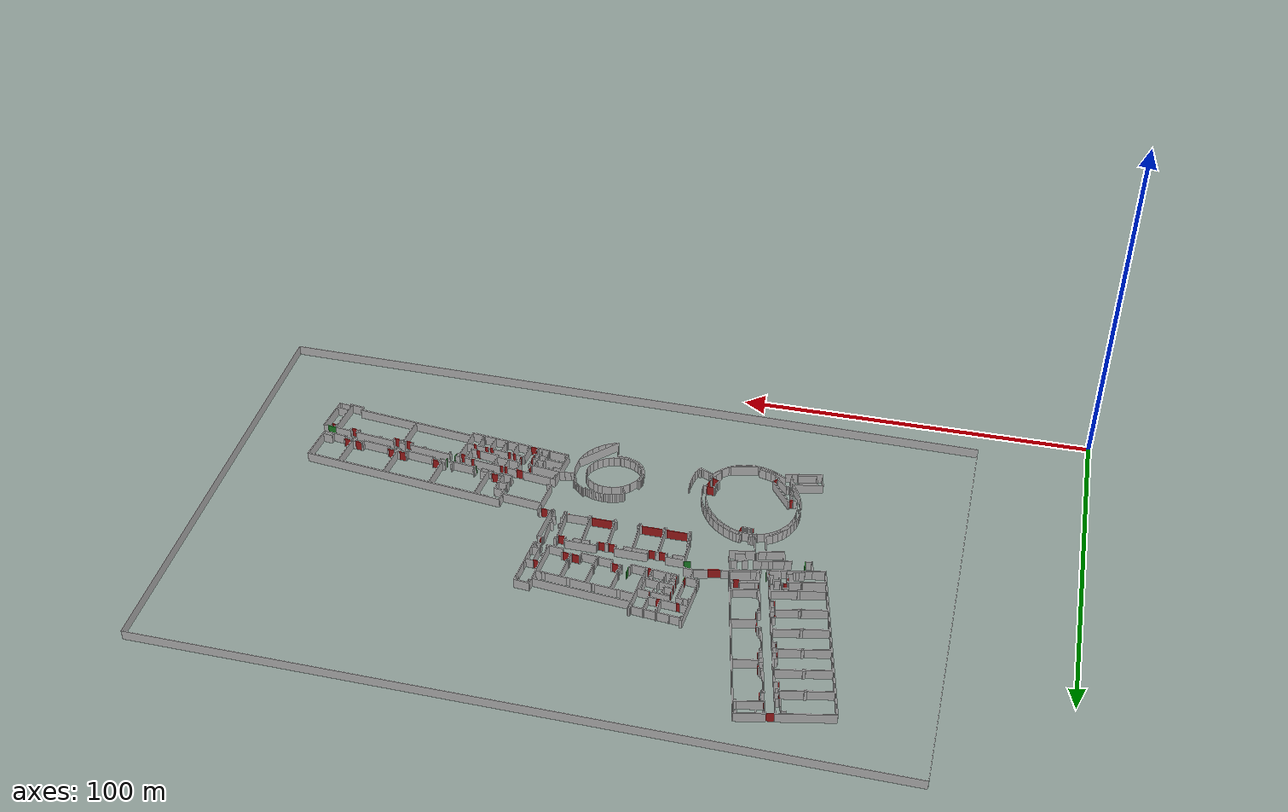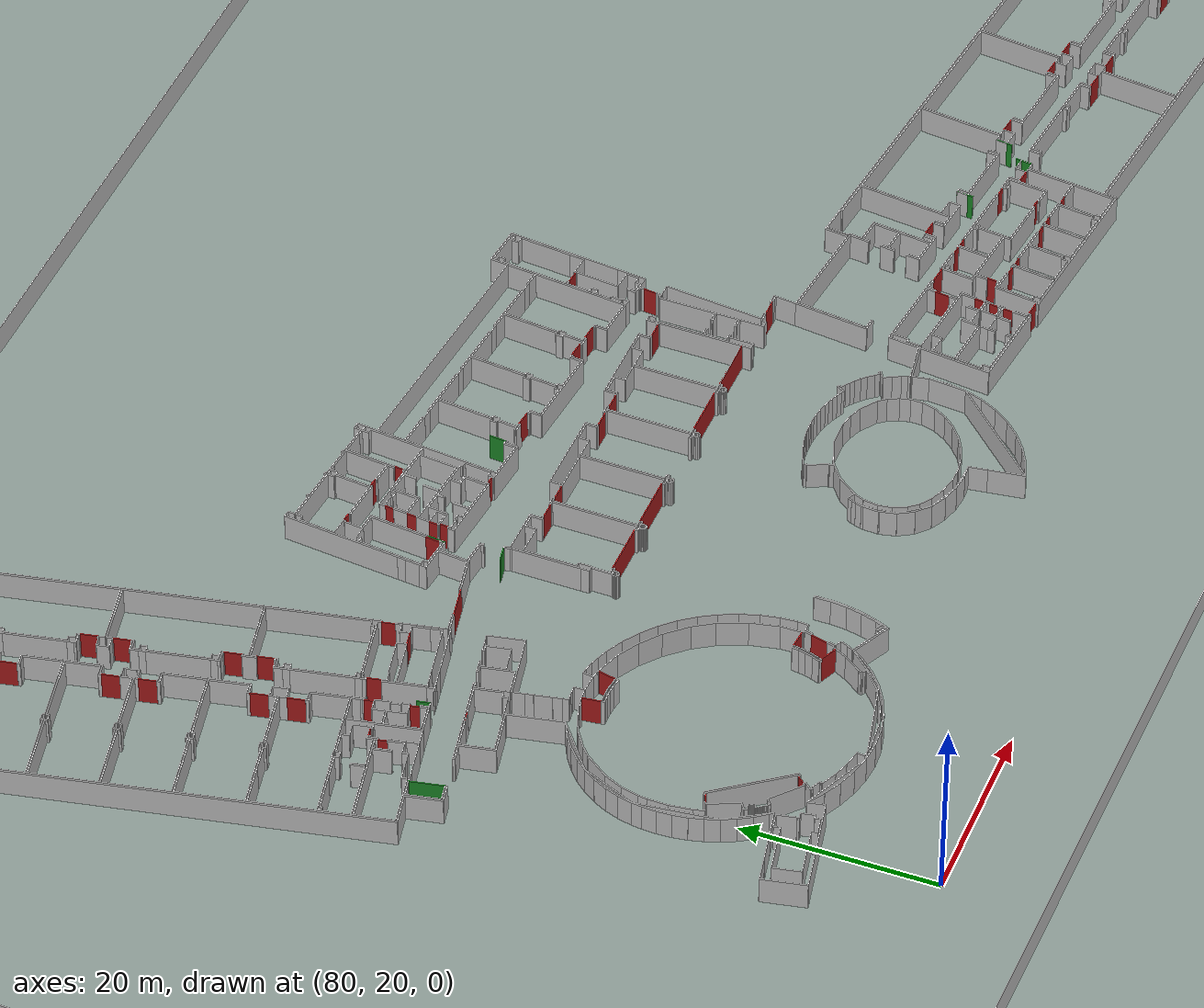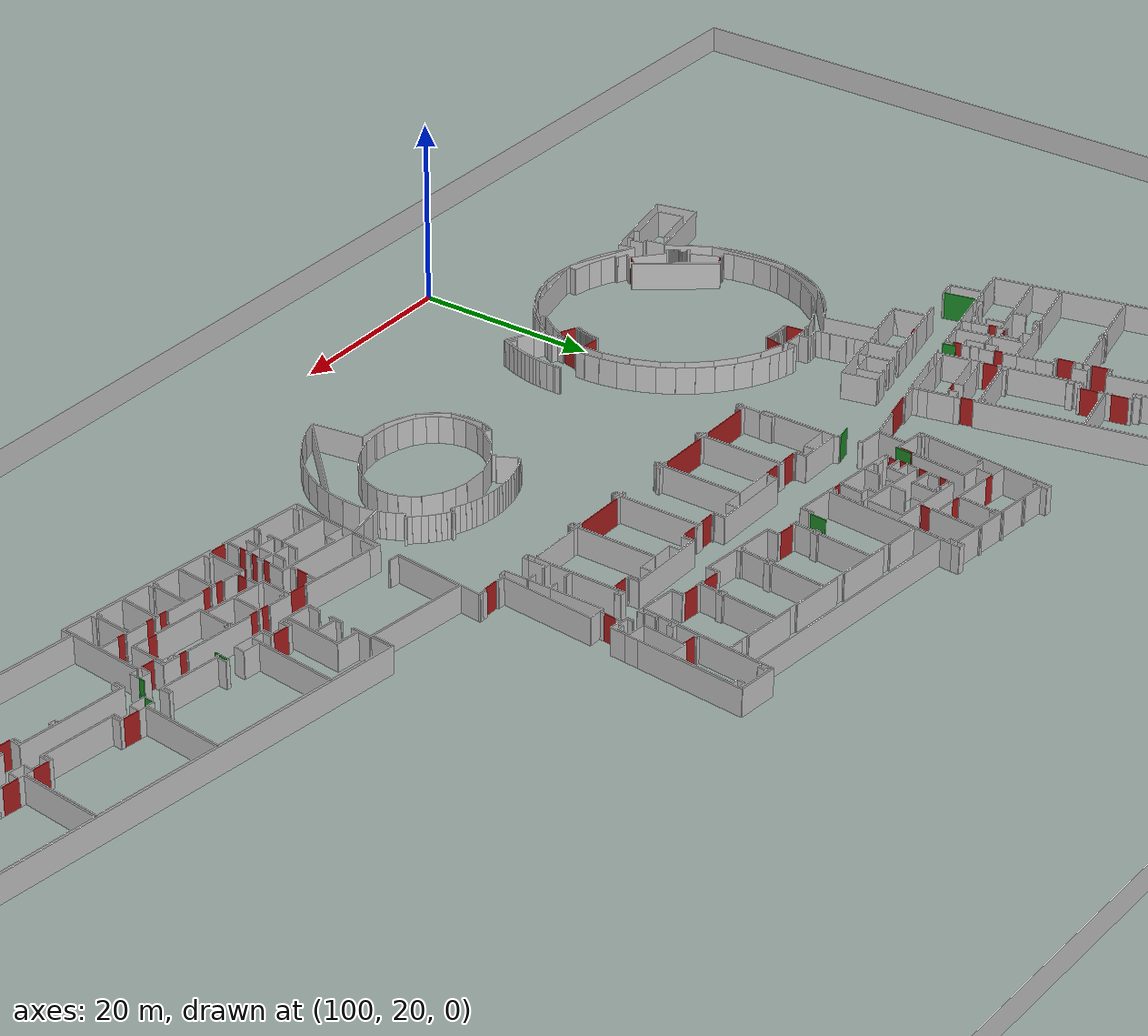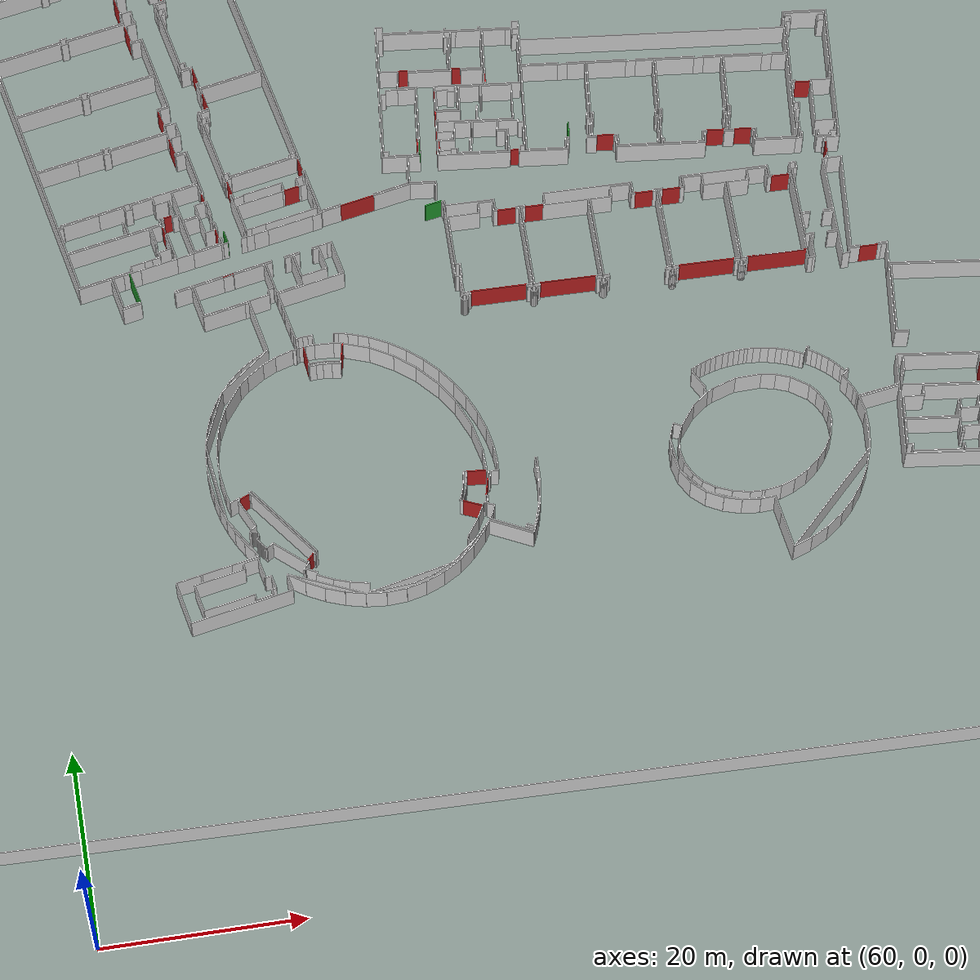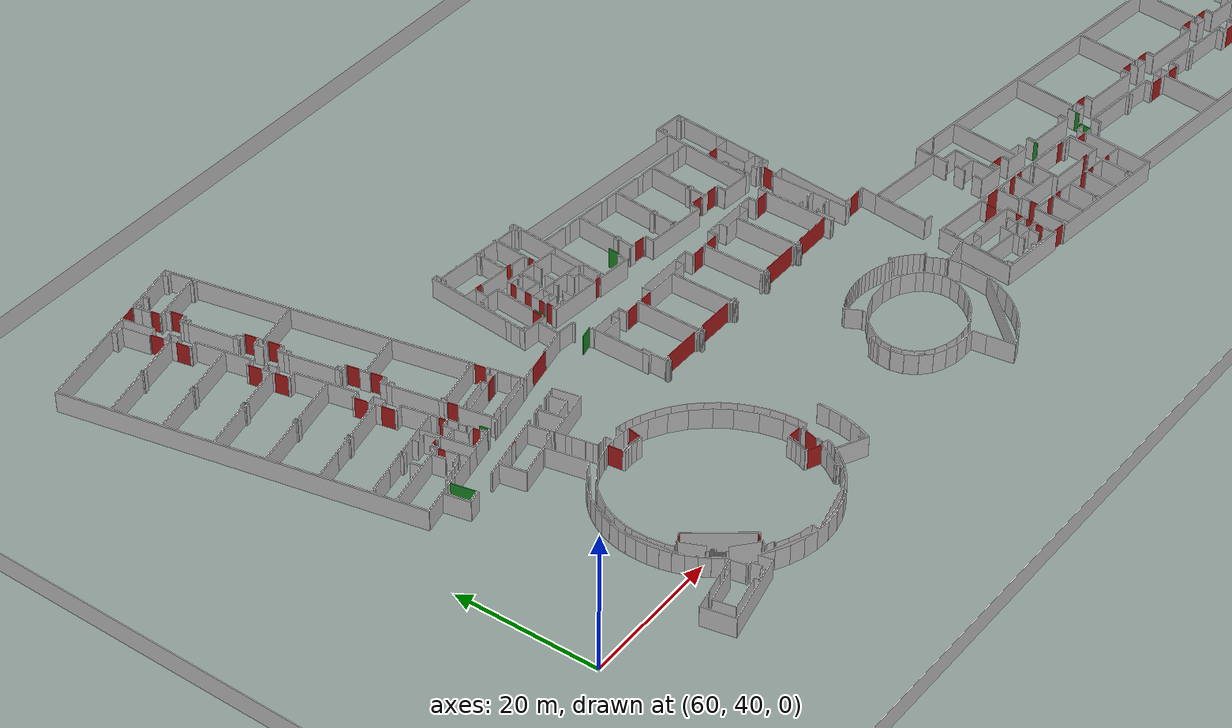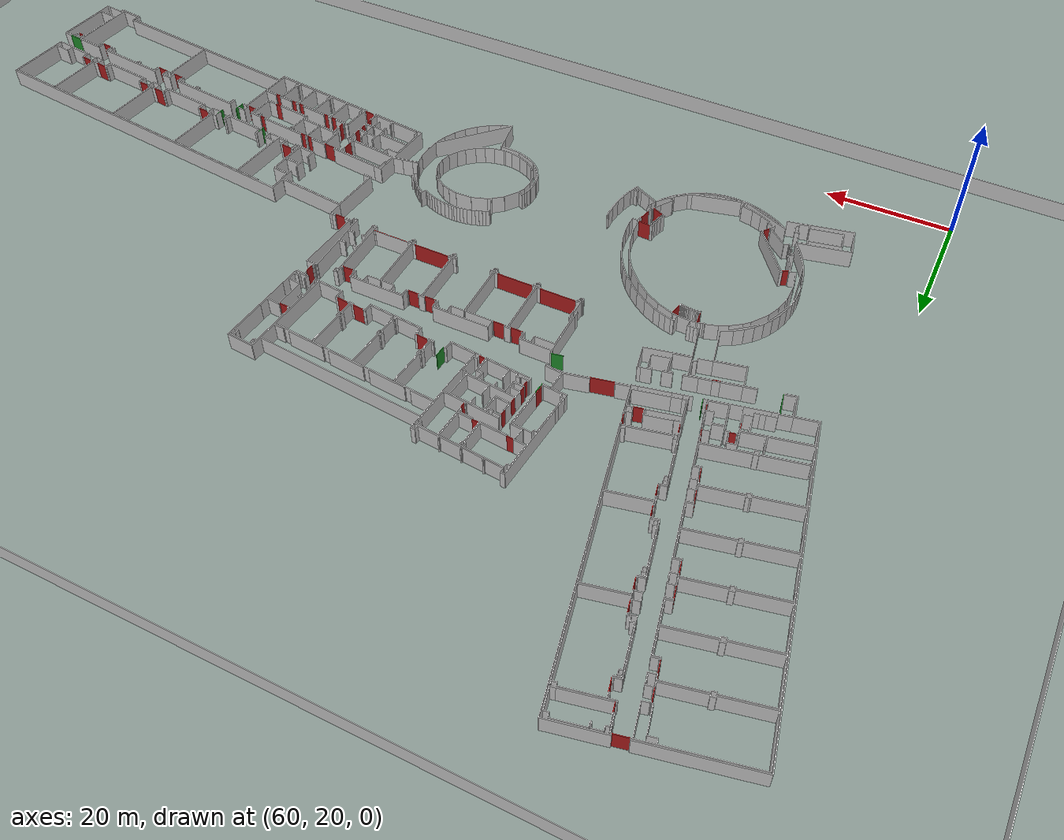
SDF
<sdf version="1.6">
 <world name="default">
  <model name="wall_153.8_39.0">
   <static>true</static>
   <pose>153.77499999999418 38.99500000011176 1.5 0 0 -1.6814535479881518</pose>
   <link name="link">
    <visual name="visual">
     <geometry><box><size>0.9960923654221514 0.1 3</size></box></geometry>
     <material>
      <script><uri>file://media/materials/scripts/gazebo.material</uri><name>Gazebo/Red</name></script>
     </material>
    </visual>
   </link>
  </model>
  <model name="wall_166.5_39.9">
   <static>true</static>
   <pose>166.50500000000466 39.91000000014901 1.5 0 0 -0.1206236686924795</pose>
   <link name="link">
    <visual name="visual">
     <geometry><box><size>0.9972462083198822 0.1 3</size></box></geometry>
     <material>
      <script><uri>file://media/materials/scripts/gazebo.material</uri><name>Gazebo/Red</name></script>
     </material>
    </visual>
   </link>
  </model>
  <model name="wall_153.7_45.9">
   <static>true</static>
   <pose>153.6600000000035 45.92999999993481 1.5 0 0 -1.6918235466009592</pose>
   <link name="link">
    <visual name="visual">
     <geometry><box><size>1.4909057649436974 0.1 3</size></box></geometry>
     <material>
      <script><uri>file://media/materials/scripts/gazebo.material</uri><name>Gazebo/Red</name></script>
     </material>
    </visual>
   </link>
  </model>
  <model name="wall_161.1_40.6">
   <static>true</static>
   <pose>161.1350000000093 40.56000000005588 1.5 0 0 -0.1206236686924795</pose>
   <link name="link">
    <visual name="visual">
     <geometry><box><size>0.9972462083198822 0.1 3</size></box></geometry>
     <material>
      <script><uri>file://media/materials/scripts/gazebo.material</uri><name>Gazebo/Red</name></script>
     </material>
    </visual>
   </link>
  </model>
  <model name="wall_191.0_47.1">
   <static>true</static>
   <pose>190.97500000000582 47.06499999994412 1.5 0 0 3.02480805813934</pose>
   <link name="link">
    <visual name="visual">
     <geometry><box><size>1.8022763383869123 0.1 3</size></box></geometry>
     <material>
      <script><uri>file://media/materials/scripts/gazebo.material</uri><name>Gazebo/Red</name></script>
     </material>
    </visual>
   </link>
  </model>
  <model name="wall_180.6_48.3">
   <static>true</static>
   <pose>180.6350000000093 48.31000000005588 1.5 0 0 3.0193009299888676</pose>
   <link name="link">
    <visual name="visual">
     <geometry><box><size>1.8034688796923075 0.1 3</size></box></geometry>
     <material>
      <script><uri>file://media/materials/scripts/gazebo.material</uri><name>Gazebo/Red</name></script>
     </material>
    </visual>
   </link>
  </model>
  <model name="wall_154.0_40.6">
   <static>true</static>
   <pose>153.9649999999965 40.574999999953434 1.5 0 0 -1.693768196390317</pose>
   <link name="link">
    <visual name="visual">
     <geometry><box><size>0.8967719889926413 0.1 3</size></box></geometry>
     <material>
      <script><uri>file://media/materials/scripts/gazebo.material</uri><name>Gazebo/Red</name></script>
     </material>
    </visual>
   </link>
  </model>
  <model name="wall_168.1_39.7">
   <static>true</static>
   <pose>168.09500000000116 39.71999999997206 1.5 0 0 -0.12062366822190172</pose>
   <link name="link">
    <visual name="visual">
     <geometry><box><size>0.9972462083216332 0.1 3</size></box></geometry>
     <material>
      <script><uri>file://media/materials/scripts/gazebo.material</uri><name>Gazebo/Red</name></script>
     </material>
    </visual>
   </link>
  </model>
  <model name="wall_194.4_46.6">
   <static>true</static>
   <pose>194.41500000000815 46.64999999990687 1.5 0 0 3.0193009299849303</pose>
   <link name="link">
    <visual name="visual">
     <geometry><box><size>1.8034688796345346 0.1 3</size></box></geometry>
     <material>
      <script><uri>file://media/materials/scripts/gazebo.material</uri><name>Gazebo/Red</name></script>
     </material>
    </visual>
   </link>
  </model>
  <model name="wall_204.7_45.4">
   <static>true</static>
   <pose>204.74499999999534 45.40499999979511 1.5 0 0 3.0248080581431034</pose>
   <link name="link">
    <visual name="visual">
     <geometry><box><size>1.8022763384447233 0.1 3</size></box></geometry>
     <material>
      <script><uri>file://media/materials/scripts/gazebo.material</uri><name>Gazebo/Red</name></script>
     </material>
    </visual>
   </link>
  </model>
  <model name="wall_156.3_47.3">
   <static>true</static>
   <pose>156.25500000000466 47.32000000006519 1.5 0 0 -0.12002333835124222</pose>
   <link name="link">
    <visual name="visual">
     <geometry><box><size>2.004420115606183 0.1 3</size></box></geometry>
     <material>
      <script><uri>file://media/materials/scripts/gazebo.material</uri><name>Gazebo/Red</name></script>
     </material>
    </visual>
   </link>
  </model>
  <model name="wall_160.4_46.8">
   <static>true</static>
   <pose>160.3850000000093 46.81999999983236 1.5 0 0 -0.1206236686924795</pose>
   <link name="link">
    <visual name="visual">
     <geometry><box><size>0.9972462083198822 0.1 3</size></box></geometry>
     <material>
      <script><uri>file://media/materials/scripts/gazebo.material</uri><name>Gazebo/Red</name></script>
     </material>
    </visual>
   </link>
  </model>
  <model name="wall_161.8_46.7">
   <static>true</static>
   <pose>161.7600000000093 46.66000000014901 1.5 0 0 -0.11942892612851068</pose>
   <link name="link">
    <visual name="visual">
     <geometry><box><size>1.0071742649744493 0.1 3</size></box></geometry>
     <material>
      <script><uri>file://media/materials/scripts/gazebo.material</uri><name>Gazebo/Red</name></script>
     </material>
    </visual>
   </link>
  </model>
  <model name="wall_170.5_45.6">
   <static>true</static>
   <pose>170.48499999998603 45.609999999869615 1.5 0 0 -0.1206236686924795</pose>
   <link name="link">
    <visual name="visual">
     <geometry><box><size>0.9972462083198822 0.1 3</size></box></geometry>
     <material>
      <script><uri>file://media/materials/scripts/gazebo.material</uri><name>Gazebo/Red</name></script>
     </material>
    </visual>
   </link>
  </model>
  <model name="wall_175.8_44.9">
   <static>true</static>
   <pose>175.80500000022585 44.86500000022352 1.5 0 0 1.4540117310915928</pose>
   <link name="link">
    <visual name="visual">
     <geometry><box><size>1.802276338498982 0.1 3</size></box></geometry>
     <material>
      <script><uri>file://media/materials/scripts/gazebo.material</uri><name>Gazebo/Green</name></script>
     </material>
    </visual>
   </link>
  </model>
  <model name="wall_190.5_42.2">
   <static>true</static>
   <pose>190.5 42.18999999994412 1.5 0 0 -0.12161902311549111</pose>
   <link name="link">
    <visual name="visual">
     <geometry><box><size>1.8133946068224918 0.1 3</size></box></geometry>
     <material>
      <script><uri>file://media/materials/scripts/gazebo.material</uri><name>Gazebo/Red</name></script>
     </material>
    </visual>
   </link>
  </model>
  <model name="wall_194.0_41.8">
   <static>true</static>
   <pose>194.0350000000035 41.765000000130385 1.5 0 0 -0.11678459545045303</pose>
   <link name="link">
    <visual name="visual">
     <geometry><box><size>1.8022763383869123 0.1 3</size></box></geometry>
     <material>
      <script><uri>file://media/materials/scripts/gazebo.material</uri><name>Gazebo/Red</name></script>
     </material>
    </visual>
   </link>
  </model>
  <model name="wall_207.6_40.1">
   <static>true</static>
   <pose>207.55999999999767 40.13500000000931 1.5 0 0 -0.11743469003206944</pose>
   <link name="link">
    <visual name="visual">
     <geometry><box><size>1.7923448329714338 0.1 3</size></box></geometry>
     <material>
      <script><uri>file://media/materials/scripts/gazebo.material</uri><name>Gazebo/Red</name></script>
     </material>
    </visual>
   </link>
  </model>
  <model name="wall_177.8_47.7">
   <static>true</static>
   <pose>177.8499999999185 47.734999999869615 1.5 0 0 -1.6930880506520969</pose>
   <link name="link">
    <visual name="visual">
     <geometry><box><size>1.803468879749112 0.1 3</size></box></geometry>
     <material>
      <script><uri>file://media/materials/scripts/gazebo.material</uri><name>Gazebo/Green</name></script>
     </material>
    </visual>
   </link>
  </model>
  <model name="wall_168.8_48.8">
   <static>true</static>
   <pose>168.83500000002095 48.825000000186265 1.5 0 0 -1.6875809222415865</pose>
   <link name="link">
    <visual name="visual">
     <geometry><box><size>1.8022763384447233 0.1 3</size></box></geometry>
     <material>
      <script><uri>file://media/materials/scripts/gazebo.material</uri><name>Gazebo/Green</name></script>
     </material>
    </visual>
   </link>
  </model>
  <model name="wall_162.6_50.5">
   <static>true</static>
   <pose>162.57000000000698 50.484999999869615 1.5 0 0 3.02415796381574</pose>
   <link name="link">
    <visual name="visual">
     <geometry><box><size>1.7923448329168745 0.1 3</size></box></geometry>
     <material>
      <script><uri>file://media/materials/scripts/gazebo.material</uri><name>Gazebo/Red</name></script>
     </material>
    </visual>
   </link>
  </model>
  <model name="wall_173.6_44.2">
   <static>true</static>
   <pose>173.6149999999907 44.21999999997206 1.5 0 0 -0.12022278677294355</pose>
   <link name="link">
    <visual name="visual">
     <geometry><box><size>1.5008331019912227 0.1 3</size></box></geometry>
     <material>
      <script><uri>file://media/materials/scripts/gazebo.material</uri><name>Gazebo/Red</name></script>
     </material>
    </visual>
   </link>
  </model>
  <model name="wall_214.1_39.3">
   <static>true</static>
   <pose>214.1350000000093 39.34499999997206 1.5 0 0 -0.11870533746682131</pose>
   <link name="link">
    <visual name="visual">
     <geometry><box><size>1.097724920014552 0.1 3</size></box></geometry>
     <material>
      <script><uri>file://media/materials/scripts/gazebo.material</uri><name>Gazebo/Red</name></script>
     </material>
    </visual>
   </link>
  </model>
  <model name="wall_214.4_40.5">
   <static>true</static>
   <pose>214.44000000006054 40.52000000001863 1.5 0 0 3.0182549527621143</pose>
   <link name="link">
    <visual name="visual">
     <geometry><box><size>2.438524143724567 0.1 3</size></box></geometry>
     <material>
      <script><uri>file://media/materials/scripts/gazebo.material</uri><name>Gazebo/Green</name></script>
     </material>
    </visual>
   </link>
  </model>
  <model name="wall_208.1_45.0">
   <static>true</static>
   <pose>208.09500000000116 45.0 1.5 0 0 3.0193009299849303</pose>
   <link name="link">
    <visual name="visual">
     <geometry><box><size>1.8034688796345346 0.1 3</size></box></geometry>
     <material>
      <script><uri>file://media/materials/scripts/gazebo.material</uri><name>Gazebo/Red</name></script>
     </material>
    </visual>
   </link>
  </model>
  <model name="wall_170.0_41.7">
   <static>true</static>
   <pose>170.0100000000093 41.68999999994412 1.5 0 0 -0.11942892612851068</pose>
   <link name="link">
    <visual name="visual">
     <geometry><box><size>1.0071742649744493 0.1 3</size></box></geometry>
     <material>
      <script><uri>file://media/materials/scripts/gazebo.material</uri><name>Gazebo/Red</name></script>
     </material>
    </visual>
   </link>
  </model>
  <model name="wall_154.2_42.2">
   <static>true</static>
   <pose>154.15000000002328 42.15500000002794 1.5 0 0 -1.6914199953995817</pose>
   <link name="link">
    <visual name="visual">
     <geometry><box><size>0.997246208074735 0.1 3</size></box></geometry>
     <material>
      <script><uri>file://media/materials/scripts/gazebo.material</uri><name>Gazebo/Red</name></script>
     </material>
    </visual>
   </link>
  </model>
  <model name="wall_157.5_41.9">
   <static>true</static>
   <pose>157.51500000001397 41.94500000006519 1.5 0 0 -1.6895016639081246</pose>
   <link name="link">
    <visual name="visual">
     <geometry><box><size>1.0977249203199801 0.1 3</size></box></geometry>
     <material>
      <script><uri>file://media/materials/scripts/gazebo.material</uri><name>Gazebo/Red</name></script>
     </material>
    </visual>
   </link>
  </model>
  <model name="wall_154.9_36.9">
   <static>true</static>
   <pose>154.86999999999534 36.85000000009313 1.5 0 0 -0.11990398547329398</pose>
   <link name="link">
    <visual name="visual">
     <geometry><box><size>1.6720047847367918 0.1 3</size></box></geometry>
     <material>
      <script><uri>file://media/materials/scripts/gazebo.material</uri><name>Gazebo/Red</name></script>
     </material>
    </visual>
   </link>
  </model>
  <model name="wall_159.5_40.8">
   <static>true</static>
   <pose>159.5449999999837 40.75 1.5 0 0 -0.1206236686924795</pose>
   <link name="link">
    <visual name="visual">
     <geometry><box><size>0.9972462083198822 0.1 3</size></box></geometry>
     <material>
      <script><uri>file://media/materials/scripts/gazebo.material</uri><name>Gazebo/Red</name></script>
     </material>
    </visual>
   </link>
  </model>
  <model name="wall_171.6_39.3">
   <static>true</static>
   <pose>171.56500000000233 39.300000000046566 1.5 0 0 -0.12062366822892527</pose>
   <link name="link">
    <visual name="visual">
     <geometry><box><size>0.9972462082638486 0.1 3</size></box></geometry>
     <material>
      <script><uri>file://media/materials/scripts/gazebo.material</uri><name>Gazebo/Red</name></script>
     </material>
    </visual>
   </link>
  </model>
  <model name="wall_80.2_77.2">
   <static>true</static>
   <pose>80.19499999997788 77.22500000009313 1.5 0 0 -1.3773690000310248</pose>
   <link name="link">
    <visual name="visual">
     <geometry><box><size>0.9884331031966657 0.1 3</size></box></geometry>
     <material>
      <script><uri>file://media/materials/scripts/gazebo.material</uri><name>Gazebo/Red</name></script>
     </material>
    </visual>
   </link>
  </model>
  <model name="wall_135.5_76.8">
   <static>true</static>
   <pose>135.49499999999534 76.79000000003725 1.5 0 0 -0.10022174961299568</pose>
   <link name="link">
    <visual name="visual">
     <geometry><box><size>1.799027515083101 0.1 3</size></box></geometry>
     <material>
      <script><uri>file://media/materials/scripts/gazebo.material</uri><name>Gazebo/Red</name></script>
     </material>
    </visual>
   </link>
  </model>
  <model name="wall_132.7_77.1">
   <static>true</static>
   <pose>132.7049999999872 77.07000000006519 1.5 0 0 -0.10022174987377463</pose>
   <link name="link">
    <visual name="visual">
     <geometry><box><size>1.7990275150717767 0.1 3</size></box></geometry>
     <material>
      <script><uri>file://media/materials/scripts/gazebo.material</uri><name>Gazebo/Red</name></script>
     </material>
    </visual>
   </link>
  </model>
  <model name="wall_112.2_77.9">
   <static>true</static>
   <pose>112.1699999999837 77.92500000004657 1.5 0 0 -0.09966865283695012</pose>
   <link name="link">
    <visual name="visual">
     <geometry><box><size>0.9044888059555555 0.1 3</size></box></geometry>
     <material>
      <script><uri>file://media/materials/scripts/gazebo.material</uri><name>Gazebo/Red</name></script>
     </material>
    </visual>
   </link>
  </model>
  <model name="wall_104.7_79.7">
   <static>true</static>
   <pose>104.70999999999185 79.65999999991618 1.5 0 0 -1.6724851785951633</pose>
   <link name="link">
    <visual name="visual">
     <geometry><box><size>0.9850888284669952 0.1 3</size></box></geometry>
     <material>
      <script><uri>file://media/materials/scripts/gazebo.material</uri><name>Gazebo/Red</name></script>
     </material>
    </visual>
   </link>
  </model>
  <model name="wall_104.9_83.1">
   <static>true</static>
   <pose>104.86999999999534 83.12999999988824 1.5 0 0 1.4711276743267871</pose>
   <link name="link">
    <visual name="visual">
     <geometry><box><size>1.0049875621097721 0.1 3</size></box></geometry>
     <material>
      <script><uri>file://media/materials/scripts/gazebo.material</uri><name>Gazebo/Red</name></script>
     </material>
    </visual>
   </link>
  </model>
  <model name="wall_105.1_85.5">
   <static>true</static>
   <pose>105.10999999998603 85.53499999991618 1.5 0 0 1.4589060606653106</pose>
   <link name="link">
    <visual name="visual">
     <geometry><box><size>0.895600357429266 0.1 3</size></box></geometry>
     <material>
      <script><uri>file://media/materials/scripts/gazebo.material</uri><name>Gazebo/Red</name></script>
     </material>
    </visual>
   </link>
  </model>
  <model name="wall_110.6_86.8">
   <static>true</static>
   <pose>110.55999999999767 86.81499999994412 1.5 0 0 1.4701276746829237</pose>
   <link name="link">
    <visual name="visual">
     <geometry><box><size>0.9950376879485058 0.1 3</size></box></geometry>
     <material>
      <script><uri>file://media/materials/scripts/gazebo.material</uri><name>Gazebo/Red</name></script>
     </material>
    </visual>
   </link>
  </model>
  <model name="wall_102.4_88.9">
   <static>true</static>
   <pose>102.38000000000466 88.94000000017695 1.5 0 0 -0.09966865258337218</pose>
   <link name="link">
    <visual name="visual">
     <geometry><box><size>1.004987562121356 0.1 3</size></box></geometry>
     <material>
      <script><uri>file://media/materials/scripts/gazebo.material</uri><name>Gazebo/Red</name></script>
     </material>
    </visual>
   </link>
  </model>
  <model name="wall_107.8_88.4">
   <static>true</static>
   <pose>107.78999999997905 88.4000000001397 1.5 0 0 -0.09966865258337218</pose>
   <link name="link">
    <visual name="visual">
     <geometry><box><size>1.004987562121356 0.1 3</size></box></geometry>
     <material>
      <script><uri>file://media/materials/scripts/gazebo.material</uri><name>Gazebo/Red</name></script>
     </material>
    </visual>
   </link>
  </model>
  <model name="wall_102.5_80.0">
   <static>true</static>
   <pose>102.52499999999418 79.9550000000745 1.5 0 0 -1.6711294309773623</pose>
   <link name="link">
    <visual name="visual">
     <geometry><box><size>1.4975313020620318 0.1 3</size></box></geometry>
     <material>
      <script><uri>file://media/materials/scripts/gazebo.material</uri><name>Gazebo/Red</name></script>
     </material>
    </visual>
   </link>
  </model>
  <model name="wall_102.7_79.6">
   <static>true</static>
   <pose>102.69000000006054 79.59000000008382 1.5 0 0 1.4711276742268928</pose>
   <link name="link">
    <visual name="visual">
     <geometry><box><size>1.808977612096451 0.1 3</size></box></geometry>
     <material>
      <script><uri>file://media/materials/scripts/gazebo.material</uri><name>Gazebo/Green</name></script>
     </material>
    </visual>
   </link>
  </model>
  <model name="wall_104.6_80.8">
   <static>true</static>
   <pose>104.625 80.77000000001863 1.5 0 0 -1.6704649792092168</pose>
   <link name="link">
    <visual name="visual">
     <geometry><box><size>0.904488806268317 0.1 3</size></box></geometry>
     <material>
      <script><uri>file://media/materials/scripts/gazebo.material</uri><name>Gazebo/Red</name></script>
     </material>
    </visual>
   </link>
  </model>
  <model name="wall_121.5_78.2">
   <static>true</static>
   <pose>121.54000000000815 78.20999999996275 1.5 0 0 -0.09966865232787321</pose>
   <link name="link">
    <visual name="visual">
     <geometry><box><size>1.808977611760522 0.1 3</size></box></geometry>
     <material>
      <script><uri>file://media/materials/scripts/gazebo.material</uri><name>Gazebo/Red</name></script>
     </material>
    </visual>
   </link>
  </model>
  <model name="wall_118.0_79.5">
   <static>true</static>
   <pose>117.96999999985565 79.46499999985099 1.5 0 0 1.470574577181901</pose>
   <link name="link">
    <visual name="visual">
     <geometry><box><size>1.799027515083101 0.1 3</size></box></geometry>
     <material>
      <script><uri>file://media/materials/scripts/gazebo.material</uri><name>Gazebo/Green</name></script>
     </material>
    </visual>
   </link>
  </model>
  <model name="wall_142.5_81.3">
   <static>true</static>
   <pose>142.54999999998836 81.33499999996275 1.5 0 0 -0.09966865273705577</pose>
   <link name="link">
    <visual name="visual">
     <geometry><box><size>1.5074813432052014 0.1 3</size></box></geometry>
     <material>
      <script><uri>file://media/materials/scripts/gazebo.material</uri><name>Gazebo/Red</name></script>
     </material>
    </visual>
   </link>
  </model>
  <model name="wall_138.2_70.8">
   <static>true</static>
   <pose>138.2149999999965 70.78000000002794 1.5 0 0 -0.01104927408967263</pose>
   <link name="link">
    <visual name="visual">
     <geometry><box><size>1.810110493862824 0.1 3</size></box></geometry>
     <material>
      <script><uri>file://media/materials/scripts/gazebo.material</uri><name>Gazebo/Red</name></script>
     </material>
    </visual>
   </link>
  </model>
  <model name="wall_127.1_71.0">
   <static>true</static>
   <pose>127.05000000001746 70.9550000000745 1.5 0 0 3.1249275297309125</pose>
   <link name="link">
    <visual name="visual">
     <geometry><box><size>1.8002499826340055 0.1 3</size></box></geometry>
     <material>
      <script><uri>file://media/materials/scripts/gazebo.material</uri><name>Gazebo/Red</name></script>
     </material>
    </visual>
   </link>
  </model>
  <model name="wall_124.3_71.0">
   <static>true</static>
   <pose>124.26499999998487 70.98999999999069 1.5 0 0 3.1305433795001205</pose>
   <link name="link">
    <visual name="visual">
     <geometry><box><size>1.810110493862824 0.1 3</size></box></geometry>
     <material>
      <script><uri>file://media/materials/scripts/gazebo.material</uri><name>Gazebo/Red</name></script>
     </material>
    </visual>
   </link>
  </model>
  <model name="wall_113.0_71.1">
   <static>true</static>
   <pose>113.03500000000349 71.13000000012107 1.5 0 0 3.1305433795001205</pose>
   <link name="link">
    <visual name="visual">
     <geometry><box><size>1.810110493862824 0.1 3</size></box></geometry>
     <material>
      <script><uri>file://media/materials/scripts/gazebo.material</uri><name>Gazebo/Red</name></script>
     </material>
    </visual>
   </link>
  </model>
  <model name="wall_110.2_71.2">
   <static>true</static>
   <pose>110.23500000001513 71.17000000015832 1.5 0 0 3.1305433795001205</pose>
   <link name="link">
    <visual name="visual">
     <geometry><box><size>1.810110493862824 0.1 3</size></box></geometry>
     <material>
      <script><uri>file://media/materials/scripts/gazebo.material</uri><name>Gazebo/Red</name></script>
     </material>
    </visual>
   </link>
  </model>
  <model name="wall_143.5_73.3">
   <static>true</static>
   <pose>143.4550000000163 73.29500000015832 1.5 0 0 1.4718835320591757</pose>
   <link name="link">
    <visual name="visual">
     <geometry><box><size>1.3164345787571878 0.1 3</size></box></geometry>
     <material>
      <script><uri>file://media/materials/scripts/gazebo.material</uri><name>Gazebo/Red</name></script>
     </material>
    </visual>
   </link>
  </model>
  <model name="wall_103.2_73.0">
   <static>true</static>
   <pose>103.15500000014435 73.02000000025146 1.5 0 0 -2.9552965370366153</pose>
   <link name="link">
    <visual name="visual">
     <geometry><box><size>1.9436306230085285 0.1 3</size></box></geometry>
     <material>
      <script><uri>file://media/materials/scripts/gazebo.material</uri><name>Gazebo/Green</name></script>
     </material>
    </visual>
   </link>
  </model>
  <model name="wall_71.7_114.6">
   <static>true</static>
   <pose>71.72999999998137 114.55000000004657 1.5 0 0 -1.3690339825092397</pose>
   <link name="link">
    <visual name="visual">
     <geometry><box><size>1.796440926065282 0.1 3</size></box></geometry>
     <material>
      <script><uri>file://media/materials/scripts/gazebo.material</uri><name>Gazebo/Red</name></script>
     </material>
    </visual>
   </link>
  </model>
  <model name="wall_72.4_111.0">
   <static>true</static>
   <pose>72.43499999999767 111.04000000003725 1.5 0 0 -1.3744936626731843</pose>
   <link name="link">
    <visual name="visual">
     <geometry><box><size>1.7944637079631676 0.1 3</size></box></geometry>
     <material>
      <script><uri>file://media/materials/scripts/gazebo.material</uri><name>Gazebo/Red</name></script>
     </material>
    </visual>
   </link>
  </model>
  <model name="wall_74.4_101.3">
   <static>true</static>
   <pose>74.38000000000466 101.26000000000931 1.5 0 0 -1.3690339825092397</pose>
   <link name="link">
    <visual name="visual">
     <geometry><box><size>1.796440926065282 0.1 3</size></box></geometry>
     <material>
      <script><uri>file://media/materials/scripts/gazebo.material</uri><name>Gazebo/Red</name></script>
     </material>
    </visual>
   </link>
  </model>
  <model name="wall_75.1_97.8">
   <static>true</static>
   <pose>75.0800000000163 97.75 1.5 0 0 -1.3690339824572944</pose>
   <link name="link">
    <visual name="visual">
     <geometry><box><size>1.7964409256090668 0.1 3</size></box></geometry>
     <material>
      <script><uri>file://media/materials/scripts/gazebo.material</uri><name>Gazebo/Red</name></script>
     </material>
    </visual>
   </link>
  </model>
  <model name="wall_77.2_87.2">
   <static>true</static>
   <pose>77.19000000000233 87.18999999994412 1.5 0 0 -1.3690339824572944</pose>
   <link name="link">
    <visual name="visual">
     <geometry><box><size>1.7964409256090668 0.1 3</size></box></geometry>
     <material>
      <script><uri>file://media/materials/scripts/gazebo.material</uri><name>Gazebo/Red</name></script>
     </material>
    </visual>
   </link>
  </model>
  <model name="wall_77.9_83.7">
   <static>true</static>
   <pose>77.88500000000931 83.6699999999255 1.5 0 0 -1.3744936626731843</pose>
   <link name="link">
    <visual name="visual">
     <geometry><box><size>1.7944637079631676 0.1 3</size></box></geometry>
     <material>
      <script><uri>file://media/materials/scripts/gazebo.material</uri><name>Gazebo/Red</name></script>
     </material>
    </visual>
   </link>
  </model>
  <model name="wall_76.4_75.6">
   <static>true</static>
   <pose>76.39000000001397 75.57500000018626 1.5 0 0 0.19083110263865674</pose>
   <link name="link">
    <visual name="visual">
     <geometry><box><size>0.8962700485807075 0.1 3</size></box></geometry>
     <material>
      <script><uri>file://media/materials/scripts/gazebo.material</uri><name>Gazebo/Red</name></script>
     </material>
    </visual>
   </link>
  </model>
  <model name="wall_75.8_74.0">
   <static>true</static>
   <pose>75.83999999999651 74.0 1.5 0 0 -1.3690339824572944</pose>
   <link name="link">
    <visual name="visual">
     <geometry><box><size>0.8982204628045334 0.1 3</size></box></geometry>
     <material>
      <script><uri>file://media/materials/scripts/gazebo.material</uri><name>Gazebo/Red</name></script>
     </material>
    </visual>
   </link>
  </model>
  <model name="wall_78.6_105.4">
   <static>true</static>
   <pose>78.55999999999767 105.38999999989755 1.5 0 0 -1.3690339825092397</pose>
   <link name="link">
    <visual name="visual">
     <geometry><box><size>1.796440926065282 0.1 3</size></box></geometry>
     <material>
      <script><uri>file://media/materials/scripts/gazebo.material</uri><name>Gazebo/Red</name></script>
     </material>
    </visual>
   </link>
  </model>
  <model name="wall_76.5_115.5">
   <static>true</static>
   <pose>76.53999999997905 115.50500000012107 1.5 0 0 -1.3701434494846443</pose>
   <link name="link">
    <visual name="visual">
     <geometry><box><size>1.8062391868343128 0.1 3</size></box></geometry>
     <material>
      <script><uri>file://media/materials/scripts/gazebo.material</uri><name>Gazebo/Red</name></script>
     </material>
    </visual>
   </link>
  </model>
  <model name="wall_79.2_102.2">
   <static>true</static>
   <pose>79.18499999999767 102.20999999996275 1.5 0 0 -1.3744936626731843</pose>
   <link name="link">
    <visual name="visual">
     <geometry><box><size>1.7944637079631676 0.1 3</size></box></geometry>
     <material>
      <script><uri>file://media/materials/scripts/gazebo.material</uri><name>Gazebo/Red</name></script>
     </material>
    </visual>
   </link>
  </model>
  <model name="wall_81.3_91.7">
   <static>true</static>
   <pose>81.2949999999837 91.65999999991618 1.5 0 0 -1.374493662723798</pose>
   <link name="link">
    <visual name="visual">
     <geometry><box><size>1.7944637084198858 0.1 3</size></box></geometry>
     <material>
      <script><uri>file://media/materials/scripts/gazebo.material</uri><name>Gazebo/Red</name></script>
     </material>
    </visual>
   </link>
  </model>
  <model name="wall_81.1_72.9">
   <static>true</static>
   <pose>81.05000000001746 72.92000000015832 1.5 0 0 1.7721134351846652</pose>
   <link name="link">
    <visual name="visual">
     <geometry><box><size>1.0001999799880765 0.1 3</size></box></geometry>
     <material>
      <script><uri>file://media/materials/scripts/gazebo.material</uri><name>Gazebo/Red</name></script>
     </material>
    </visual>
   </link>
  </model>
  <model name="wall_81.6_67.9">
   <static>true</static>
   <pose>81.55000000001746 67.88999999989755 1.5 0 0 0.2009542638673007</pose>
   <link name="link">
    <visual name="visual">
     <geometry><box><size>1.1021796587332557 0.1 3</size></box></geometry>
     <material>
      <script><uri>file://media/materials/scripts/gazebo.material</uri><name>Gazebo/Red</name></script>
     </material>
    </visual>
   </link>
  </model>
  <model name="wall_75.1_117.8">
   <static>true</static>
   <pose>75.06500000000233 117.75500000012107 1.5 0 0 -1.376431060702658</pose>
   <link name="link">
    <visual name="visual">
     <geometry><box><size>1.2943724348298333 0.1 3</size></box></geometry>
     <material>
      <script><uri>file://media/materials/scripts/gazebo.material</uri><name>Gazebo/Red</name></script>
     </material>
    </visual>
   </link>
  </model>
  <model name="wall_115.0_62.2">
   <static>true</static>
   <pose>115.0 62.23999999999069 1.5 0 0 -0.014034166198596688</pose>
   <link name="link">
    <visual name="visual">
     <geometry><box><size>5.700561375812611 0.1 3</size></box></geometry>
     <material>
      <script><uri>file://media/materials/scripts/gazebo.material</uri><name>Gazebo/Red</name></script>
     </material>
    </visual>
   </link>
  </model>
  <model name="wall_129.0_62.0">
   <static>true</static>
   <pose>129.01999999998952 62.049999999813735 1.5 0 0 -0.014034166280132265</pose>
   <link name="link">
    <visual name="visual">
     <geometry><box><size>5.7005613758773475 0.1 3</size></box></geometry>
     <material>
      <script><uri>file://media/materials/scripts/gazebo.material</uri><name>Gazebo/Red</name></script>
     </material>
    </visual>
   </link>
  </model>
  <model name="wall_136.2_62.0">
   <static>true</static>
   <pose>136.19500000000698 61.950000000186265 1.5 0 0 -0.013266220046968015</pose>
   <link name="link">
    <visual name="visual">
     <geometry><box><size>6.030530656612972 0.1 3</size></box></geometry>
     <material>
      <script><uri>file://media/materials/scripts/gazebo.material</uri><name>Gazebo/Red</name></script>
     </material>
    </visual>
   </link>
  </model>
  <model name="wall_108.0_62.3">
   <static>true</static>
   <pose>107.99499999999534 62.34499999997206 1.5 0 0 -0.012258580285916719</pose>
   <link name="link">
    <visual name="visual">
     <geometry><box><size>5.710429055644689 0.1 3</size></box></geometry>
     <material>
      <script><uri>file://media/materials/scripts/gazebo.material</uri><name>Gazebo/Red</name></script>
     </material>
    </visual>
   </link>
  </model>
  <model name="wall_79.8_43.2">
   <static>true</static>
   <pose>79.82500000001164 43.18500000005588 1.5 0 0 0.42331075582642225</pose>
   <link name="link">
    <visual name="visual">
     <geometry><box><size>0.9980981916532635 0.1 3</size></box></geometry>
     <material>
      <script><uri>file://media/materials/scripts/gazebo.material</uri><name>Gazebo/Red</name></script>
     </material>
    </visual>
   </link>
  </model>
  <model name="wall_85.3_35.8">
   <static>true</static>
   <pose>85.27999999999884 35.77000000001863 1.5 0 0 0.8424789459730314</pose>
   <link name="link">
    <visual name="visual">
     <geometry><box><size>0.9915644206490059 0.1 3</size></box></geometry>
     <material>
      <script><uri>file://media/materials/scripts/gazebo.material</uri><name>Gazebo/Red</name></script>
     </material>
    </visual>
   </link>
  </model>
  <model name="wall_102.6_42.5">
   <static>true</static>
   <pose>102.60500000001048 42.48999999999069 1.5 0 0 -0.08271241528552369</pose>
   <link name="link">
    <visual name="visual">
     <geometry><box><size>1.9366207682124321 0.1 3</size></box></geometry>
     <material>
      <script><uri>file://media/materials/scripts/gazebo.material</uri><name>Gazebo/Red</name></script>
     </material>
    </visual>
   </link>
  </model>
  <model name="wall_101.7_39.1">
   <static>true</static>
   <pose>101.71000000002095 39.06499999994412 1.5 0 0 -0.4219085234522241</pose>
   <link name="link">
    <visual name="visual">
     <geometry><box><size>1.9291708063548034 0.1 3</size></box></geometry>
     <material>
      <script><uri>file://media/materials/scripts/gazebo.material</uri><name>Gazebo/Red</name></script>
     </material>
    </visual>
   </link>
  </model>
  <model name="wall_103.3_40.6">
   <static>true</static>
   <pose>103.3299999999872 40.59000000008382 1.5 0 0 -1.823690391929414</pose>
   <link name="link">
    <visual name="visual">
     <geometry><box><size>1.8384776308918926 0.1 3</size></box></geometry>
     <material>
      <script><uri>file://media/materials/scripts/gazebo.material</uri><name>Gazebo/Red</name></script>
     </material>
    </visual>
   </link>
  </model>
  <model name="wall_87.9_57.8">
   <static>true</static>
   <pose>87.93499999999767 57.77499999990687 1.5 0 0 -1.4509545189031208</pose>
   <link name="link">
    <visual name="visual">
     <geometry><box><size>1.9237983263743257 0.1 3</size></box></geometry>
     <material>
      <script><uri>file://media/materials/scripts/gazebo.material</uri><name>Gazebo/Red</name></script>
     </material>
    </visual>
   </link>
  </model>
  <model name="wall_91.5_57.6">
   <static>true</static>
   <pose>91.49500000002445 57.58999999985099 1.5 0 0 -1.795651920405678</pose>
   <link name="link">
    <visual name="visual">
     <geometry><box><size>1.9285486770039746 0.1 3</size></box></geometry>
     <material>
      <script><uri>file://media/materials/scripts/gazebo.material</uri><name>Gazebo/Red</name></script>
     </material>
    </visual>
   </link>
  </model>
  <model name="wall_89.2_76.9">
   <static>true</static>
   <pose>89.17999999999302 76.94499999983236 1.5 0 0 0.19349440931601616</pose>
   <link name="link">
    <visual name="visual">
     <geometry><box><size>1.508144555394632 0.1 3</size></box></geometry>
     <material>
      <script><uri>file://media/materials/scripts/gazebo.material</uri><name>Gazebo/Red</name></script>
     </material>
    </visual>
   </link>
  </model>
  <model name="wall_81.9_88.5">
   <static>true</static>
   <pose>81.91500000000815 88.53499999991618 1.5 0 0 -1.3755746765469539</pose>
   <link name="link">
    <visual name="visual">
     <geometry><box><size>1.8042727066855455 0.1 3</size></box></geometry>
     <material>
      <script><uri>file://media/materials/scripts/gazebo.material</uri><name>Gazebo/Red</name></script>
     </material>
    </visual>
   </link>
  </model>
  <model name="wall_83.0_77.9">
   <static>true</static>
   <pose>83.01999999998952 77.89500000001863 1.5 0 0 -1.3721104451170056</pose>
   <link name="link">
    <visual name="visual">
     <geometry><box><size>1.51990131280261 0.1 3</size></box></geometry>
     <material>
      <script><uri>file://media/materials/scripts/gazebo.material</uri><name>Gazebo/Red</name></script>
     </material>
    </visual>
   </link>
  </model>
  <model name="wall_81.9_72.4">
   <static>true</static>
   <pose>81.875 72.38500000000931 1.5 0 0 1.7681918866447774</pose>
   <link name="link">
    <visual name="visual">
     <geometry><box><size>1.3767352687650285 0.1 3</size></box></geometry>
     <material>
      <script><uri>file://media/materials/scripts/gazebo.material</uri><name>Gazebo/Green</name></script>
     </material>
    </visual>
   </link>
  </model>
  <model name="wall_73.0_120.5">
   <static>true</static>
   <pose>73.04000000000815 120.50499999988824 1.5 0 0 0.19646185337495456</pose>
   <link name="link">
    <visual name="visual">
     <geometry><box><size>2.100404722931416 0.1 3</size></box></geometry>
     <material>
      <script><uri>file://media/materials/scripts/gazebo.material</uri><name>Gazebo/Red</name></script>
     </material>
    </visual>
   </link>
  </model>
  <model name="wall_95.5_74.5">
   <static>true</static>
   <pose>95.51500000001397 74.51000000000931 1.5 0 0 0.19351316121262999</pose>
   <link name="link">
    <visual name="visual">
     <geometry><box><size>3.5360005656156344 0.1 3</size></box></geometry>
     <material>
      <script><uri>file://media/materials/scripts/gazebo.material</uri><name>Gazebo/Red</name></script>
     </material>
    </visual>
   </link>
  </model>
  <model name="wall_145.4_61.4">
   <static>true</static>
   <pose>145.44999999998254 61.360000000102445 1.5 0 0 -0.011110653908026076</pose>
   <link name="link">
    <visual name="visual">
     <geometry><box><size>1.8001111076705336 0.1 3</size></box></geometry>
     <material>
      <script><uri>file://media/materials/scripts/gazebo.material</uri><name>Gazebo/Red</name></script>
     </material>
    </visual>
   </link>
  </model>
  <model name="wall_72.2_68.0">
   <static>true</static>
   <pose>72.16500000003725 68.04500000015832 1.5 0 0 1.767083239622093</pose>
   <link name="link">
    <visual name="visual">
     <geometry><box><size>3.5379372523187618 0.1 3</size></box></geometry>
     <material>
      <script><uri>file://media/materials/scripts/gazebo.material</uri><name>Gazebo/Green</name></script>
     </material>
    </visual>
   </link>
  </model>
  <model name="wall_90.4_79.5">
   <static>true</static>
   <pose>90.41000000000349 79.52499999990687 1.5 0 0 -1.369193218179265</pose>
   <link name="link">
    <visual name="visual">
     <geometry><box><size>1.3983204211800917 0.1 3</size></box></geometry>
     <material>
      <script><uri>file://media/materials/scripts/gazebo.material</uri><name>Gazebo/Red</name></script>
     </material>
    </visual>
   </link>
  </model>
  <model name="wall_150.4_39.6">
   <static>true</static>
   <pose>150.3649999999907 39.61500000022352 1.5 0 0 1.4513674008194029</pose>
   <link name="link">
    <visual name="visual">
     <geometry><box><size>0.7553806987169667 0.1 3</size></box></geometry>
     <material>
      <script><uri>file://media/materials/scripts/gazebo.material</uri><name>Gazebo/White</name></script>
     </material>
    </visual>
   </link>
  </model>
  <model name="wall_150.5_40.4">
   <static>true</static>
   <pose>150.4649999999965 40.43000000016764 1.5 0 0 1.4464413321830076</pose>
   <link name="link">
    <visual name="visual">
     <geometry><box><size>0.8868483522074317 0.1 3</size></box></geometry>
     <material>
      <script><uri>file://media/materials/scripts/gazebo.material</uri><name>Gazebo/White</name></script>
     </material>
    </visual>
   </link>
  </model>
  <model name="wall_147.8_41.2">
   <static>true</static>
   <pose>147.83500000002095 41.18500000005588 1.5 0 0 3.0248080581405947</pose>
   <link name="link">
    <visual name="visual">
     <geometry><box><size>5.406829015218547 0.1 3</size></box></geometry>
     <material>
      <script><uri>file://media/materials/scripts/gazebo.material</uri><name>Gazebo/White</name></script>
     </material>
    </visual>
   </link>
  </model>
  <model name="wall_145.0_40.2">
   <static>true</static>
   <pose>144.9900000000198 40.16500000003725 1.5 0 0 -1.690077564147906</pose>
   <link name="link">
    <visual name="visual">
     <geometry><box><size>2.689107658612167 0.1 3</size></box></geometry>
     <material>
      <script><uri>file://media/materials/scripts/gazebo.material</uri><name>Gazebo/White</name></script>
     </material>
    </visual>
   </link>
  </model>
  <model name="wall_145.1_38.8">
   <static>true</static>
   <pose>145.0800000000163 38.800000000046566 1.5 0 0 -0.11942892612851068</pose>
   <link name="link">
    <visual name="visual">
     <geometry><box><size>0.5035871324872246 0.1 3</size></box></geometry>
     <material>
      <script><uri>file://media/materials/scripts/gazebo.material</uri><name>Gazebo/White</name></script>
     </material>
    </visual>
   </link>
  </model>
  <model name="wall_145.3_38.4">
   <static>true</static>
   <pose>145.2850000000035 38.389999999897555 1.5 0 0 -1.6886684299881376</pose>
   <link name="link">
    <visual name="visual">
     <geometry><box><size>0.7653103947893748 0.1 3</size></box></geometry>
     <material>
      <script><uri>file://media/materials/scripts/gazebo.material</uri><name>Gazebo/White</name></script>
     </material>
    </visual>
   </link>
  </model>
  <model name="wall_147.7_37.7">
   <static>true</static>
   <pose>147.67499999998836 37.7249999998603 1.5 0 0 -0.11651301006280392</pose>
   <link name="link">
    <visual name="visual">
     <geometry><box><size>4.90324382422122 0.1 3</size></box></geometry>
     <material>
      <script><uri>file://media/materials/scripts/gazebo.material</uri><name>Gazebo/White</name></script>
     </material>
    </visual>
   </link>
  </model>
  <model name="wall_150.1_37.8">
   <static>true</static>
   <pose>150.14499999998952 37.75499999988824 1.5 0 0 1.4601391055905788</pose>
   <link name="link">
    <visual name="visual">
     <geometry><box><size>0.6338769595593153 0.1 3</size></box></geometry>
     <material>
      <script><uri>file://media/materials/scripts/gazebo.material</uri><name>Gazebo/White</name></script>
     </material>
    </visual>
   </link>
  </model>
  <model name="wall_150.3_38.1">
   <static>true</static>
   <pose>150.27999999999884 38.05499999993481 1.5 0 0 -0.14888994659904642</pose>
   <link name="link">
    <visual name="visual">
     <geometry><box><size>0.20223748414268597 0.1 3</size></box></geometry>
     <material>
      <script><uri>file://media/materials/scripts/gazebo.material</uri><name>Gazebo/White</name></script>
     </material>
    </visual>
   </link>
  </model>
  <model name="wall_150.3_37.7">
   <static>true</static>
   <pose>150.3399999999965 37.71999999997206 1.5 0 0 -1.695151321341658</pose>
   <link name="link">
    <visual name="visual">
     <geometry><box><size>0.6449806199952839 0.1 3</size></box></geometry>
     <material>
      <script><uri>file://media/materials/scripts/gazebo.material</uri><name>Gazebo/White</name></script>
     </material>
    </visual>
   </link>
  </model>
  <model name="wall_151.9_37.2">
   <static>true</static>
   <pose>151.9199999999837 37.20999999996275 1.5 0 0 -0.11675057835937525</pose>
   <link name="link">
    <visual name="visual">
     <geometry><box><size>3.2622078413023767 0.1 3</size></box></geometry>
     <material>
      <script><uri>file://media/materials/scripts/gazebo.material</uri><name>Gazebo/White</name></script>
     </material>
    </visual>
   </link>
  </model>
  <model name="wall_153.6_37.8">
   <static>true</static>
   <pose>153.62999999997555 37.76000000000931 1.5 0 0 1.449769106988834</pose>
   <link name="link">
    <visual name="visual">
     <geometry><box><size>1.4909057649436974 0.1 3</size></box></geometry>
     <material>
      <script><uri>file://media/materials/scripts/gazebo.material</uri><name>Gazebo/White</name></script>
     </material>
    </visual>
   </link>
  </model>
  <model name="wall_153.8_39.5">
   <static>true</static>
   <pose>153.83500000002095 39.54000000003725 1.5 0 0 1.4711276738426837</pose>
   <link name="link">
    <visual name="visual">
     <geometry><box><size>0.10049875584145537 0.1 3</size></box></geometry>
     <material>
      <script><uri>file://media/materials/scripts/gazebo.material</uri><name>Gazebo/White</name></script>
     </material>
    </visual>
   </link>
  </model>
  <model name="wall_153.2_39.7">
   <static>true</static>
   <pose>153.22000000000116 39.65999999991618 1.5 0 0 3.0291655226601732</pose>
   <link name="link">
    <visual name="visual">
     <geometry><box><size>1.2478781992477335 0.1 3</size></box></geometry>
     <material>
      <script><uri>file://media/materials/scripts/gazebo.material</uri><name>Gazebo/White</name></script>
     </material>
    </visual>
   </link>
  </model>
  <model name="wall_152.5_39.0">
   <static>true</static>
   <pose>152.51499999998487 38.98999999999069 1.5 0 0 -1.6851599802083586</pose>
   <link name="link">
    <visual name="visual">
     <geometry><box><size>1.4897315194152685 0.1 3</size></box></geometry>
     <material>
      <script><uri>file://media/materials/scripts/gazebo.material</uri><name>Gazebo/White</name></script>
     </material>
    </visual>
   </link>
  </model>
  <model name="wall_152.3_38.3">
   <static>true</static>
   <pose>152.3299999999872 38.26000000000931 1.5 0 0 3.0419240010121844</pose>
   <link name="link">
    <visual name="visual">
     <geometry><box><size>0.20099751243585498 0.1 3</size></box></geometry>
     <material>
      <script><uri>file://media/materials/scripts/gazebo.material</uri><name>Gazebo/White</name></script>
     </material>
    </visual>
   </link>
  </model>
  <model name="wall_152.3_39.0">
   <static>true</static>
   <pose>152.31500000000233 39.01000000000931 1.5 0 0 1.4564326733426174</pose>
   <link name="link">
    <visual name="visual">
     <geometry><box><size>1.4897315194219107 0.1 3</size></box></geometry>
     <material>
      <script><uri>file://media/materials/scripts/gazebo.material</uri><name>Gazebo/White</name></script>
     </material>
    </visual>
   </link>
  </model>
  <model name="wall_151.5_39.9">
   <static>true</static>
   <pose>151.50500000000466 39.85499999998137 1.5 0 0 3.0248080581431034</pose>
   <link name="link">
    <visual name="visual">
     <geometry><box><size>1.8022763384447233 0.1 3</size></box></geometry>
     <material>
      <script><uri>file://media/materials/scripts/gazebo.material</uri><name>Gazebo/White</name></script>
     </material>
    </visual>
   </link>
  </model>
  <model name="wall_150.6_39.6">
   <static>true</static>
   <pose>150.57000000000698 39.59000000008382 1.5 0 0 -1.6784861976067038</pose>
   <link name="link">
    <visual name="visual">
     <geometry><box><size>0.7443117623918901 0.1 3</size></box></geometry>
     <material>
      <script><uri>file://media/materials/scripts/gazebo.material</uri><name>Gazebo/White</name></script>
     </material>
    </visual>
   </link>
  </model>
  <model name="wall_150.4_39.2">
   <static>true</static>
   <pose>150.42500000001746 39.230000000214204 1.5 0 0 3.0466409471685547</pose>
   <link name="link">
    <visual name="visual">
     <geometry><box><size>0.21095023111991618 0.1 3</size></box></geometry>
     <material>
      <script><uri>file://media/materials/scripts/gazebo.material</uri><name>Gazebo/White</name></script>
     </material>
    </visual>
   </link>
  </model>
  <model name="wall_166.9_37.6">
   <static>true</static>
   <pose>166.92499999998836 37.63000000012107 1.5 0 0 -1.690673321615393</pose>
   <link name="link">
    <visual name="visual">
     <geometry><box><size>4.4318055010582365 0.1 3</size></box></geometry>
     <material>
      <script><uri>file://media/materials/scripts/gazebo.material</uri><name>Gazebo/White</name></script>
     </material>
    </visual>
   </link>
  </model>
  <model name="wall_165.1_35.6">
   <static>true</static>
   <pose>165.1349999999802 35.61499999999069 1.5 0 0 3.0208710707011033</pose>
   <link name="link">
    <visual name="visual">
     <geometry><box><size>3.0723606558584717 0.1 3</size></box></geometry>
     <material>
      <script><uri>file://media/materials/scripts/gazebo.material</uri><name>Gazebo/White</name></script>
     </material>
    </visual>
   </link>
  </model>
  <model name="wall_163.6_36.1">
   <static>true</static>
   <pose>163.64499999998952 36.11999999987893 1.5 0 0 1.4618543698162652</pose>
   <link name="link">
    <visual name="visual">
     <geometry><box><size>0.6438167442431666 0.1 3</size></box></geometry>
     <material>
      <script><uri>file://media/materials/scripts/gazebo.material</uri><name>Gazebo/White</name></script>
     </material>
    </visual>
   </link>
  </model>
  <model name="wall_163.6_36.5">
   <static>true</static>
   <pose>163.57000000000698 36.455000000074506 1.5 0 0 3.00606493842361</pose>
   <link name="link">
    <visual name="visual">
     <geometry><box><size>0.2220360331192952 0.1 3</size></box></geometry>
     <material>
      <script><uri>file://media/materials/scripts/gazebo.material</uri><name>Gazebo/White</name></script>
     </material>
    </visual>
   </link>
  </model>
  <model name="wall_163.7_38.3">
   <static>true</static>
   <pose>163.69000000000233 38.34500000020489 1.5 0 0 1.44873942407576</pose>
   <link name="link">
    <visual name="visual">
     <geometry><box><size>3.7781079920994487 0.1 3</size></box></geometry>
     <material>
      <script><uri>file://media/materials/scripts/gazebo.material</uri><name>Gazebo/White</name></script>
     </material>
    </visual>
   </link>
  </model>
  <model name="wall_165.0_40.1">
   <static>true</static>
   <pose>164.9649999999965 40.09500000020489 1.5 0 0 -0.11905156754423915</pose>
   <link name="link">
    <visual name="visual">
     <geometry><box><size>2.1048990474859015 0.1 3</size></box></geometry>
     <material>
      <script><uri>file://media/materials/scripts/gazebo.material</uri><name>Gazebo/White</name></script>
     </material>
    </visual>
   </link>
  </model>
  <model name="wall_167.1_39.8">
   <static>true</static>
   <pose>167.09500000000116 39.84000000008382 1.5 0 0 -0.10487693882591773</pose>
   <link name="link">
    <visual name="visual">
     <geometry><box><size>0.19104973174969345 0.1 3</size></box></geometry>
     <material>
      <script><uri>file://media/materials/scripts/gazebo.material</uri><name>Gazebo/White</name></script>
     </material>
    </visual>
   </link>
  </model>
  <model name="wall_153.8_47.1">
   <static>true</static>
   <pose>153.80499999999302 47.139999999897555 1.5 0 0 -1.6872877874817485</pose>
   <link name="link">
    <visual name="visual">
     <geometry><box><size>0.9464142855493431 0.1 3</size></box></geometry>
     <material>
      <script><uri>file://media/materials/scripts/gazebo.material</uri><name>Gazebo/White</name></script>
     </material>
    </visual>
   </link>
  </model>
  <model name="wall_153.5_44.8">
   <static>true</static>
   <pose>153.52499999999418 44.81499999994412 1.5 0 0 -1.6902252528468988</pose>
   <link name="link">
    <visual name="visual">
     <geometry><box><size>0.7553806987239018 0.1 3</size></box></geometry>
     <material>
      <script><uri>file://media/materials/scripts/gazebo.material</uri><name>Gazebo/White</name></script>
     </material>
    </visual>
   </link>
  </model>
  <model name="wall_149.6_44.9">
   <static>true</static>
   <pose>149.55499999999302 44.91500000003725 1.5 0 0 3.0211592075440525</pose>
   <link name="link">
    <visual name="visual">
     <geometry><box><size>7.907275131168029 0.1 3</size></box></geometry>
     <material>
      <script><uri>file://media/materials/scripts/gazebo.material</uri><name>Gazebo/White</name></script>
     </material>
    </visual>
   </link>
  </model>
  <model name="wall_145.7_46.1">
   <static>true</static>
   <pose>145.72000000000116 46.13000000012107 1.5 0 0 1.449769106988834</pose>
   <link name="link">
    <visual name="visual">
     <geometry><box><size>1.4909057649436974 0.1 3</size></box></geometry>
     <material>
      <script><uri>file://media/materials/scripts/gazebo.material</uri><name>Gazebo/White</name></script>
     </material>
    </visual>
   </link>
  </model>
  <model name="wall_146.0_46.9">
   <static>true</static>
   <pose>145.95999999999185 46.85000000009313 1.5 0 0 -0.132551532423765</pose>
   <link name="link">
    <visual name="visual">
     <geometry><box><size>0.3026549190018152 0.1 3</size></box></geometry>
     <material>
      <script><uri>file://media/materials/scripts/gazebo.material</uri><name>Gazebo/White</name></script>
     </material>
    </visual>
   </link>
  </model>
  <model name="wall_146.2_47.7">
   <static>true</static>
   <pose>146.20999999999185 47.675000000046566 1.5 0 0 1.4530010049136584</pose>
   <link name="link">
    <visual name="visual">
     <geometry><box><size>1.7017931718677757 0.1 3</size></box></geometry>
     <material>
      <script><uri>file://media/materials/scripts/gazebo.material</uri><name>Gazebo/White</name></script>
     </material>
    </visual>
   </link>
  </model>
  <model name="wall_150.1_48.1">
   <static>true</static>
   <pose>150.08499999999185 48.06499999994412 1.5 0 0 -0.11995117374483057</pose>
   <link name="link">
    <visual name="visual">
     <geometry><box><size>7.604643318400634 0.1 3</size></box></geometry>
     <material>
      <script><uri>file://media/materials/scripts/gazebo.material</uri><name>Gazebo/White</name></script>
     </material>
    </visual>
   </link>
  </model>
  <model name="wall_162.7_40.4">
   <static>true</static>
   <pose>162.67499999998836 40.375 1.5 0 0 3.0225410860422697</pose>
   <link name="link">
    <visual name="visual">
     <geometry><box><size>2.104899047428106 0.1 3</size></box></geometry>
     <material>
      <script><uri>file://media/materials/scripts/gazebo.material</uri><name>Gazebo/White</name></script>
     </material>
    </visual>
   </link>
  </model>
  <model name="wall_160.5_40.6">
   <static>true</static>
   <pose>160.54000000000815 40.63000000012107 1.5 0 0 3.0419240010121844</pose>
   <link name="link">
    <visual name="visual">
     <geometry><box><size>0.20099751243585498 0.1 3</size></box></geometry>
     <material>
      <script><uri>file://media/materials/scripts/gazebo.material</uri><name>Gazebo/White</name></script>
     </material>
    </visual>
   </link>
  </model>
  <model name="wall_160.2_38.4">
   <static>true</static>
   <pose>160.17499999998836 38.44000000017695 1.5 0 0 -1.690673321615393</pose>
   <link name="link">
    <visual name="visual">
     <geometry><box><size>4.4318055010582365 0.1 3</size></box></geometry>
     <material>
      <script><uri>file://media/materials/scripts/gazebo.material</uri><name>Gazebo/White</name></script>
     </material>
    </visual>
   </link>
  </model>
  <model name="wall_161.4_36.1">
   <static>true</static>
   <pose>161.43499999999767 36.06000000005588 1.5 0 0 -0.11748918977593945</pose>
   <link name="link">
    <visual name="visual">
     <geometry><box><size>3.071172414652986 0.1 3</size></box></geometry>
     <material>
      <script><uri>file://media/materials/scripts/gazebo.material</uri><name>Gazebo/White</name></script>
     </material>
    </visual>
   </link>
  </model>
  <model name="wall_163.0_36.2">
   <static>true</static>
   <pose>163.0 36.199999999953434 1.5 0 0 1.4464413323376855</pose>
   <link name="link">
    <visual name="visual">
     <geometry><box><size>0.6449806199880641 0.1 3</size></box></geometry>
     <material>
      <script><uri>file://media/materials/scripts/gazebo.material</uri><name>Gazebo/White</name></script>
     </material>
    </visual>
   </link>
  </model>
  <model name="wall_163.1_36.5">
   <static>true</static>
   <pose>163.14999999999418 36.50500000012107 1.5 0 0 -0.13552771305276134</pose>
   <link name="link">
    <visual name="visual">
     <geometry><box><size>0.22203603311405212 0.1 3</size></box></geometry>
     <material>
      <script><uri>file://media/materials/scripts/gazebo.material</uri><name>Gazebo/White</name></script>
     </material>
    </visual>
   </link>
  </model>
  <model name="wall_163.5_38.4">
   <static>true</static>
   <pose>163.4899999999907 38.37000000011176 1.5 0 0 1.4490608416488255</pose>
   <link name="link">
    <visual name="visual">
     <geometry><box><size>3.7880337905415886 0.1 3</size></box></geometry>
     <material>
      <script><uri>file://media/materials/scripts/gazebo.material</uri><name>Gazebo/White</name></script>
     </material>
    </visual>
   </link>
  </model>
  <model name="wall_193.2_51.3">
   <static>true</static>
   <pose>193.20999999999185 51.294999999925494 1.5 0 0 -1.6919586614511988</pose>
   <link name="link">
    <visual name="visual">
     <geometry><box><size>8.93550782004122 0.1 3</size></box></geometry>
     <material>
      <script><uri>file://media/materials/scripts/gazebo.material</uri><name>Gazebo/White</name></script>
     </material>
    </visual>
   </link>
  </model>
  <model name="wall_192.3_46.9">
   <static>true</static>
   <pose>192.26999999998952 46.90999999991618 1.5 0 0 3.0172376589266166</pose>
   <link name="link">
    <visual name="visual">
     <geometry><box><size>0.806225774829855 0.1 3</size></box></geometry>
     <material>
      <script><uri>file://media/materials/scripts/gazebo.material</uri><name>Gazebo/White</name></script>
     </material>
    </visual>
   </link>
  </model>
  <model name="wall_189.9_47.2">
   <static>true</static>
   <pose>189.88000000000466 47.19500000006519 1.5 0 0 3.01723765836245</pose>
   <link name="link">
    <visual name="visual">
     <geometry><box><size>0.4031128874726857 0.1 3</size></box></geometry>
     <material>
      <script><uri>file://media/materials/scripts/gazebo.material</uri><name>Gazebo/White</name></script>
     </material>
    </visual>
   </link>
  </model>
  <model name="wall_189.6_46.7">
   <static>true</static>
   <pose>189.6149999999907 46.71000000019558 1.5 0 0 -1.6975638618984608</pose>
   <link name="link">
    <visual name="visual">
     <geometry><box><size>1.028250942153329 0.1 3</size></box></geometry>
     <material>
      <script><uri>file://media/materials/scripts/gazebo.material</uri><name>Gazebo/White</name></script>
     </material>
    </visual>
   </link>
  </model>
  <model name="wall_185.7_46.7">
   <static>true</static>
   <pose>185.67999999999302 46.66500000003725 1.5 0 0 3.0220108925195217</pose>
   <link name="link">
    <visual name="visual">
     <geometry><box><size>7.79567187606697 0.1 3</size></box></geometry>
     <material>
      <script><uri>file://media/materials/scripts/gazebo.material</uri><name>Gazebo/White</name></script>
     </material>
    </visual>
   </link>
  </model>
  <model name="wall_181.9_47.6">
   <static>true</static>
   <pose>181.86999999999534 47.639999999897555 1.5 0 0 1.4536875822346544</pose>
   <link name="link">
    <visual name="visual">
     <geometry><box><size>1.0270345661353761 0.1 3</size></box></geometry>
     <material>
      <script><uri>file://media/materials/scripts/gazebo.material</uri><name>Gazebo/White</name></script>
     </material>
    </visual>
   </link>
  </model>
  <model name="wall_181.7_48.2">
   <static>true</static>
   <pose>181.73000000001048 48.175000000046566 1.5 0 0 3.01723765834454</pose>
   <link name="link">
    <visual name="visual">
     <geometry><box><size>0.4031128874149275 0.1 3</size></box></geometry>
     <material>
      <script><uri>file://media/materials/scripts/gazebo.material</uri><name>Gazebo/White</name></script>
     </material>
    </visual>
   </link>
  </model>
  <model name="wall_179.4_48.5">
   <static>true</static>
   <pose>179.35000000000582 48.46499999985099 1.5 0 0 3.026716048357006</pose>
   <link name="link">
    <visual name="visual">
     <geometry><box><size>0.7851751396509952 0.1 3</size></box></geometry>
     <material>
      <script><uri>file://media/materials/scripts/gazebo.material</uri><name>Gazebo/White</name></script>
     </material>
    </visual>
   </link>
  </model>
  <model name="wall_179.5_52.9">
   <static>true</static>
   <pose>179.49500000002445 52.949999999953434 1.5 0 0 1.4508789678012857</pose>
   <link name="link">
    <visual name="visual">
     <geometry><box><size>8.944232779076149 0.1 3</size></box></geometry>
     <material>
      <script><uri>file://media/materials/scripts/gazebo.material</uri><name>Gazebo/White</name></script>
     </material>
    </visual>
   </link>
  </model>
  <model name="wall_186.9_56.6">
   <static>true</static>
   <pose>186.89000000001397 56.56000000005588 1.5 0 0 -0.12040599336592878</pose>
   <link name="link">
    <visual name="visual">
     <geometry><box><size>13.820057886989042 0.1 3</size></box></geometry>
     <material>
      <script><uri>file://media/materials/scripts/gazebo.material</uri><name>Gazebo/White</name></script>
     </material>
    </visual>
   </link>
  </model>
  <model name="wall_154.0_41.2">
   <static>true</static>
   <pose>154.04000000000815 41.18999999994412 1.5 0 0 1.4536875822379653</pose>
   <link name="link">
    <visual name="visual">
     <geometry><box><size>0.34234485522203445 0.1 3</size></box></geometry>
     <material>
      <script><uri>file://media/materials/scripts/gazebo.material</uri><name>Gazebo/White</name></script>
     </material>
    </visual>
   </link>
  </model>
  <model name="wall_153.4_41.4">
   <static>true</static>
   <pose>153.43499999999767 41.43499999982305 1.5 0 0 3.022163727644903</pose>
   <link name="link">
    <visual name="visual">
     <geometry><box><size>1.258967831190321 0.1 3</size></box></geometry>
     <material>
      <script><uri>file://media/materials/scripts/gazebo.material</uri><name>Gazebo/White</name></script>
     </material>
    </visual>
   </link>
  </model>
  <model name="wall_152.7_40.7">
   <static>true</static>
   <pose>152.7149999999965 40.71999999997206 1.5 0 0 -1.6904748161031404</pose>
   <link name="link">
    <visual name="visual">
     <geometry><box><size>1.5913830458958753 0.1 3</size></box></geometry>
     <material>
      <script><uri>file://media/materials/scripts/gazebo.material</uri><name>Gazebo/White</name></script>
     </material>
    </visual>
   </link>
  </model>
  <model name="wall_153.2_39.9">
   <static>true</static>
   <pose>153.24499999999534 39.85499999998137 1.5 0 0 -0.11942892631213106</pose>
   <link name="link">
    <visual name="visual">
     <geometry><box><size>1.2589678312458021 0.1 3</size></box></geometry>
     <material>
      <script><uri>file://media/materials/scripts/gazebo.material</uri><name>Gazebo/White</name></script>
     </material>
    </visual>
   </link>
  </model>
  <model name="wall_153.9_40.0">
   <static>true</static>
   <pose>153.88999999998487 39.954999999841675 1.5 0 0 1.4570043197403058</pose>
   <link name="link">
    <visual name="visual">
     <geometry><box><size>0.35227829916632136 0.1 3</size></box></geometry>
     <material>
      <script><uri>file://media/materials/scripts/gazebo.material</uri><name>Gazebo/White</name></script>
     </material>
    </visual>
   </link>
  </model>
  <model name="wall_170.4_37.5">
   <static>true</static>
   <pose>170.44499999997788 37.53000000002794 1.5 0 0 -1.6899106225096845</pose>
   <link name="link">
    <visual name="visual">
     <geometry><box><size>3.7868324496644155 0.1 3</size></box></geometry>
     <material>
      <script><uri>file://media/materials/scripts/gazebo.material</uri><name>Gazebo/White</name></script>
     </material>
    </visual>
   </link>
  </model>
  <model name="wall_170.1_35.7">
   <static>true</static>
   <pose>170.10499999998137 35.66500000003725 1.5 0 0 3.0118901153086775</pose>
   <link name="link">
    <visual name="visual">
     <geometry><box><size>0.23194827011012187 0.1 3</size></box></geometry>
     <material>
      <script><uri>file://media/materials/scripts/gazebo.material</uri><name>Gazebo/White</name></script>
     </material>
    </visual>
   </link>
  </model>
  <model name="wall_169.9_35.4">
   <static>true</static>
   <pose>169.94999999998254 35.360000000102445 1.5 0 0 -1.695151321341658</pose>
   <link name="link">
    <visual name="visual">
     <geometry><box><size>0.6449806199952839 0.1 3</size></box></geometry>
     <material>
      <script><uri>file://media/materials/scripts/gazebo.material</uri><name>Gazebo/White</name></script>
     </material>
    </visual>
   </link>
  </model>
  <model name="wall_168.4_35.2">
   <static>true</static>
   <pose>168.3849999999802 35.22500000009313 1.5 0 0 3.020871070550642</pose>
   <link name="link">
    <visual name="visual">
     <geometry><box><size>3.0723606559145504 0.1 3</size></box></geometry>
     <material>
      <script><uri>file://media/materials/scripts/gazebo.material</uri><name>Gazebo/White</name></script>
     </material>
    </visual>
   </link>
  </model>
  <model name="wall_167.1_37.6">
   <static>true</static>
   <pose>167.125 37.60499999998137 1.5 0 0 1.4506488810357367</pose>
   <link name="link">
    <visual name="visual">
     <geometry><box><size>4.421877428998444 0.1 3</size></box></geometry>
     <material>
      <script><uri>file://media/materials/scripts/gazebo.material</uri><name>Gazebo/White</name></script>
     </material>
    </visual>
   </link>
  </model>
  <model name="wall_167.5_39.8">
   <static>true</static>
   <pose>167.49499999999534 39.78999999980442 1.5 0 0 -0.09495170644739931</pose>
   <link name="link">
    <visual name="visual">
     <geometry><box><size>0.21095023106197072 0.1 3</size></box></geometry>
     <material>
      <script><uri>file://media/materials/scripts/gazebo.material</uri><name>Gazebo/White</name></script>
     </material>
    </visual>
   </link>
  </model>
  <model name="wall_169.6_39.5">
   <static>true</static>
   <pose>169.63000000000466 39.53500000014901 1.5 0 0 -0.11961849947817037</pose>
   <link name="link">
    <visual name="visual">
     <geometry><box><size>2.094970166810415 0.1 3</size></box></geometry>
     <material>
      <script><uri>file://media/materials/scripts/gazebo.material</uri><name>Gazebo/White</name></script>
     </material>
    </visual>
   </link>
  </model>
  <model name="wall_207.1_49.6">
   <static>true</static>
   <pose>207.11999999999534 49.62000000011176 1.5 0 0 -1.6918235466009592</pose>
   <link name="link">
    <visual name="visual">
     <geometry><box><size>8.945434589662185 0.1 3</size></box></geometry>
     <material>
      <script><uri>file://media/materials/scripts/gazebo.material</uri><name>Gazebo/White</name></script>
     </material>
    </visual>
   </link>
  </model>
  <model name="wall_206.1_45.2">
   <static>true</static>
   <pose>206.11000000001513 45.23999999999069 1.5 0 0 3.0146198643464803</pose>
   <link name="link">
    <visual name="visual">
     <geometry><box><size>0.9476286191960649 0.1 3</size></box></geometry>
     <material>
      <script><uri>file://media/materials/scripts/gazebo.material</uri><name>Gazebo/White</name></script>
     </material>
    </visual>
   </link>
  </model>
  <model name="wall_203.7_45.5">
   <static>true</static>
   <pose>203.65499999999884 45.53499999991618 1.5 0 0 3.0140830946554305</pose>
   <link name="link">
    <visual name="visual">
     <geometry><box><size>0.39319206501840065 0.1 3</size></box></geometry>
     <material>
      <script><uri>file://media/materials/scripts/gazebo.material</uri><name>Gazebo/White</name></script>
     </material>
    </visual>
   </link>
  </model>
  <model name="wall_203.4_45.1">
   <static>true</static>
   <pose>203.39500000001863 45.050000000046566 1.5 0 0 -1.6975638618984608</pose>
   <link name="link">
    <visual name="visual">
     <geometry><box><size>1.028250942153329 0.1 3</size></box></geometry>
     <material>
      <script><uri>file://media/materials/scripts/gazebo.material</uri><name>Gazebo/White</name></script>
     </material>
    </visual>
   </link>
  </model>
  <model name="wall_199.5_45.0">
   <static>true</static>
   <pose>199.46000000002095 45.00500000012107 1.5 0 0 3.022010892460215</pose>
   <link name="link">
    <visual name="visual">
     <geometry><box><size>7.795671876122522 0.1 3</size></box></geometry>
     <material>
      <script><uri>file://media/materials/scripts/gazebo.material</uri><name>Gazebo/White</name></script>
     </material>
    </visual>
   </link>
  </model>
  <model name="wall_195.7_46.0">
   <static>true</static>
   <pose>195.65000000002328 45.980000000214204 1.5 0 0 1.4536875822346544</pose>
   <link name="link">
    <visual name="visual">
     <geometry><box><size>1.0270345661353761 0.1 3</size></box></geometry>
     <material>
      <script><uri>file://media/materials/scripts/gazebo.material</uri><name>Gazebo/White</name></script>
     </material>
    </visual>
   </link>
  </model>
  <model name="wall_195.5_46.5">
   <static>true</static>
   <pose>195.5100000000093 46.515000000130385 1.5 0 0 3.017237659508693</pose>
   <link name="link">
    <visual name="visual">
     <geometry><box><size>0.4031128874149275 0.1 3</size></box></geometry>
     <material>
      <script><uri>file://media/materials/scripts/gazebo.material</uri><name>Gazebo/White</name></script>
     </material>
    </visual>
   </link>
  </model>
  <model name="wall_193.2_46.8">
   <static>true</static>
   <pose>193.19500000000698 46.794999999925494 1.5 0 0 3.034313797491963</pose>
   <link name="link">
    <visual name="visual">
     <geometry><box><size>0.6537583652023057 0.1 3</size></box></geometry>
     <material>
      <script><uri>file://media/materials/scripts/gazebo.material</uri><name>Gazebo/White</name></script>
     </material>
    </visual>
   </link>
  </model>
  <model name="wall_193.4_51.3">
   <static>true</static>
   <pose>193.4100000000035 51.27000000001863 1.5 0 0 1.4497691069823746</pose>
   <link name="link">
    <visual name="visual">
     <geometry><box><size>8.945434589669212 0.1 3</size></box></geometry>
     <material>
      <script><uri>file://media/materials/scripts/gazebo.material</uri><name>Gazebo/White</name></script>
     </material>
    </visual>
   </link>
  </model>
  <model name="wall_200.8_54.9">
   <static>true</static>
   <pose>200.80499999999302 54.88500000000931 1.5 0 0 -0.1197740511061136</pose>
   <link name="link">
    <visual name="visual">
     <geometry><box><size>13.808931892028117 0.1 3</size></box></geometry>
     <material>
      <script><uri>file://media/materials/scripts/gazebo.material</uri><name>Gazebo/White</name></script>
     </material>
    </visual>
   </link>
  </model>
  <model name="wall_215.2_40.4">
   <static>true</static>
   <pose>215.2400000000198 40.420000000158325 1.5 0 0 3.0202406529081416</pose>
   <link name="link">
    <visual name="visual">
     <geometry><box><size>0.8260750571407429 0.1 3</size></box></geometry>
     <material>
      <script><uri>file://media/materials/scripts/gazebo.material</uri><name>Gazebo/White</name></script>
     </material>
    </visual>
   </link>
  </model>
  <model name="wall_214.8_39.9">
   <static>true</static>
   <pose>214.75500000000466 39.875 1.5 0 0 -1.6961854471129454</pose>
   <link name="link">
    <visual name="visual">
     <geometry><box><size>1.199416525224772 0.1 3</size></box></geometry>
     <material>
      <script><uri>file://media/materials/scripts/gazebo.material</uri><name>Gazebo/White</name></script>
     </material>
    </visual>
   </link>
  </model>
  <model name="wall_213.7_40.0">
   <static>true</static>
   <pose>213.66500000000815 40.00500000012107 1.5 0 0 1.4454072064764434</pose>
   <link name="link">
    <visual name="visual">
     <geometry><box><size>1.199416524755487 0.1 3</size></box></geometry>
     <material>
      <script><uri>file://media/materials/scripts/gazebo.material</uri><name>Gazebo/White</name></script>
     </material>
    </visual>
   </link>
  </model>
  <model name="wall_213.7_40.6">
   <static>true</static>
   <pose>213.66500000000815 40.610000000102445 1.5 0 0 3.00904112114061</pose>
   <link name="link">
    <visual name="visual">
     <geometry><box><size>0.15132745947205906 0.1 3</size></box></geometry>
     <material>
      <script><uri>file://media/materials/scripts/gazebo.material</uri><name>Gazebo/White</name></script>
     </material>
    </visual>
   </link>
  </model>
  <model name="wall_211.1_40.9">
   <static>true</static>
   <pose>211.09500000000116 40.920000000158325 1.5 0 0 3.0219266671082443</pose>
   <link name="link">
    <visual name="visual">
     <geometry><box><size>5.025942697703559 0.1 3</size></box></geometry>
     <material>
      <script><uri>file://media/materials/scripts/gazebo.material</uri><name>Gazebo/White</name></script>
     </material>
    </visual>
   </link>
  </model>
  <model name="wall_208.5_40.6">
   <static>true</static>
   <pose>208.52499999999418 40.625 1.5 0 0 -1.6961854470647963</pose>
   <link name="link">
    <visual name="visual">
     <geometry><box><size>1.1994165252174924 0.1 3</size></box></geometry>
     <material>
      <script><uri>file://media/materials/scripts/gazebo.material</uri><name>Gazebo/White</name></script>
     </material>
    </visual>
   </link>
  </model>
  <model name="wall_206.7_40.8">
   <static>true</static>
   <pose>206.7399999999907 40.83500000019558 1.5 0 0 1.4536875822110042</pose>
   <link name="link">
    <visual name="visual">
     <geometry><box><size>1.198206993749794 0.1 3</size></box></geometry>
     <material>
      <script><uri>file://media/materials/scripts/gazebo.material</uri><name>Gazebo/White</name></script>
     </material>
    </visual>
   </link>
  </model>
  <model name="wall_200.9_42.1">
   <static>true</static>
   <pose>200.94500000000698 42.140000000130385 1.5 0 0 3.0211217461725024</pose>
   <link name="link">
    <visual name="visual">
     <geometry><box><size>11.815637942969962 0.1 3</size></box></geometry>
     <material>
      <script><uri>file://media/materials/scripts/gazebo.material</uri><name>Gazebo/White</name></script>
     </material>
    </visual>
   </link>
  </model>
  <model name="wall_195.0_42.3">
   <static>true</static>
   <pose>195.00500000000466 42.25500000012107 1.5 0 0 -1.696185447161499</pose>
   <link name="link">
    <visual name="visual">
     <geometry><box><size>1.1994165247627664 0.1 3</size></box></geometry>
     <material>
      <script><uri>file://media/materials/scripts/gazebo.material</uri><name>Gazebo/White</name></script>
     </material>
    </visual>
   </link>
  </model>
  <model name="wall_193.2_42.5">
   <static>true</static>
   <pose>193.2149999999965 42.46500000008382 1.5 0 0 1.4454072064764434</pose>
   <link name="link">
    <visual name="visual">
     <geometry><box><size>1.199416524755487 0.1 3</size></box></geometry>
     <material>
      <script><uri>file://media/materials/scripts/gazebo.material</uri><name>Gazebo/White</name></script>
     </material>
    </visual>
   </link>
  </model>
  <model name="wall_192.4_43.2">
   <static>true</static>
   <pose>192.41499999997905 43.16500000003725 1.5 0 0 3.02216372759244</pose>
   <link name="link">
    <visual name="visual">
     <geometry><box><size>1.7625549636775455 0.1 3</size></box></geometry>
     <material>
      <script><uri>file://media/materials/scripts/gazebo.material</uri><name>Gazebo/White</name></script>
     </material>
    </visual>
   </link>
  </model>
  <model name="wall_191.5_42.7">
   <static>true</static>
   <pose>191.47000000000116 42.675000000046566 1.5 0 0 -1.6879050713305428</pose>
   <link name="link">
    <visual name="visual">
     <geometry><box><size>1.1982069937429929 0.1 3</size></box></geometry>
     <material>
      <script><uri>file://media/materials/scripts/gazebo.material</uri><name>Gazebo/White</name></script>
     </material>
    </visual>
   </link>
  </model>
  <model name="wall_189.7_42.9">
   <static>true</static>
   <pose>189.67499999998836 42.89500000001863 1.5 0 0 1.445407206476848</pose>
   <link name="link">
    <visual name="visual">
     <geometry><box><size>1.199416525224772 0.1 3</size></box></geometry>
     <material>
      <script><uri>file://media/materials/scripts/gazebo.material</uri><name>Gazebo/White</name></script>
     </material>
    </visual>
   </link>
  </model>
  <model name="wall_183.7_44.2">
   <static>true</static>
   <pose>183.69000000000233 44.22000000020489 1.5 0 0 3.021708265311705</pose>
   <link name="link">
    <visual name="visual">
     <geometry><box><size>12.207620570765556 0.1 3</size></box></geometry>
     <material>
      <script><uri>file://media/materials/scripts/gazebo.material</uri><name>Gazebo/White</name></script>
     </material>
    </visual>
   </link>
  </model>
  <model name="wall_177.6_44.4">
   <static>true</static>
   <pose>177.55999999999767 44.35499999998137 1.5 0 0 -1.6879050713333807</pose>
   <link name="link">
    <visual name="visual">
     <geometry><box><size>1.1982069942122657 0.1 3</size></box></geometry>
     <material>
      <script><uri>file://media/materials/scripts/gazebo.material</uri><name>Gazebo/White</name></script>
     </material>
    </visual>
   </link>
  </model>
  <model name="wall_175.8_44.6">
   <static>true</static>
   <pose>175.77499999999418 44.56500000017695 1.5 0 0 1.4454072064764434</pose>
   <link name="link">
    <visual name="visual">
     <geometry><box><size>1.199416524755487 0.1 3</size></box></geometry>
     <material>
      <script><uri>file://media/materials/scripts/gazebo.material</uri><name>Gazebo/White</name></script>
     </material>
    </visual>
   </link>
  </model>
  <model name="wall_175.2_45.2">
   <static>true</static>
   <pose>175.17999999999302 45.23999999999069 1.5 0 0 3.0227523092521484</pose>
   <link name="link">
    <visual name="visual">
     <geometry><box><size>1.3495184325570784 0.1 3</size></box></geometry>
     <material>
      <script><uri>file://media/materials/scripts/gazebo.material</uri><name>Gazebo/White</name></script>
     </material>
    </visual>
   </link>
  </model>
  <model name="wall_174.4_44.7">
   <static>true</static>
   <pose>174.43499999999767 44.7249999998603 1.5 0 0 -1.696185447161499</pose>
   <link name="link">
    <visual name="visual">
     <geometry><box><size>1.1994165247627664 0.1 3</size></box></geometry>
     <material>
      <script><uri>file://media/materials/scripts/gazebo.material</uri><name>Gazebo/White</name></script>
     </material>
    </visual>
   </link>
  </model>
  <model name="wall_172.9_44.9">
   <static>true</static>
   <pose>172.94000000000233 44.90500000002794 1.5 0 0 1.4536875822110042</pose>
   <link name="link">
    <visual name="visual">
     <geometry><box><size>1.198206993749794 0.1 3</size></box></geometry>
     <material>
      <script><uri>file://media/materials/scripts/gazebo.material</uri><name>Gazebo/White</name></script>
     </material>
    </visual>
   </link>
  </model>
  <model name="wall_172.0_45.6">
   <static>true</static>
   <pose>172.0100000000093 45.62000000011176 1.5 0 0 3.0221637274612827</pose>
   <link name="link">
    <visual name="visual">
     <geometry><box><size>2.0143485299488986 0.1 3</size></box></geometry>
     <material>
      <script><uri>file://media/materials/scripts/gazebo.material</uri><name>Gazebo/White</name></script>
     </material>
    </visual>
   </link>
  </model>
  <model name="wall_171.0_45.6">
   <static>true</static>
   <pose>170.99499999999534 45.64500000001863 1.5 0 0 -1.7273982035881303</pose>
   <link name="link">
    <visual name="visual">
     <geometry><box><size>0.1923538410258384 0.1 3</size></box></geometry>
     <material>
      <script><uri>file://media/materials/scripts/gazebo.material</uri><name>Gazebo/White</name></script>
     </material>
    </visual>
   </link>
  </model>
  <model name="wall_170.0_45.8">
   <static>true</static>
   <pose>170.0 45.764999999897555 1.5 0 0 1.4659193879370842</pose>
   <link name="link">
    <visual name="visual">
     <geometry><box><size>0.19104973169180559 0.1 3</size></box></geometry>
     <material>
      <script><uri>file://media/materials/scripts/gazebo.material</uri><name>Gazebo/White</name></script>
     </material>
    </visual>
   </link>
  </model>
  <model name="wall_166.1_46.3">
   <static>true</static>
   <pose>166.14500000001863 46.324999999953434 1.5 0 0 3.0218576675715907</pose>
   <link name="link">
    <visual name="visual">
     <geometry><box><size>7.7857433813364185 0.1 3</size></box></geometry>
     <material>
      <script><uri>file://media/materials/scripts/gazebo.material</uri><name>Gazebo/White</name></script>
     </material>
    </visual>
   </link>
  </model>
  <model name="wall_162.3_46.7">
   <static>true</static>
   <pose>162.27000000001863 46.69500000006519 1.5 0 0 -1.675673265652709</pose>
   <link name="link">
    <visual name="visual">
     <geometry><box><size>0.19104973169180559 0.1 3</size></box></geometry>
     <material>
      <script><uri>file://media/materials/scripts/gazebo.material</uri><name>Gazebo/White</name></script>
     </material>
    </visual>
   </link>
  </model>
  <model name="wall_161.3_46.8">
   <static>true</static>
   <pose>161.27000000001863 46.81500000017695 1.5 0 0 1.4659193879370842</pose>
   <link name="link">
    <visual name="visual">
     <geometry><box><size>0.19104973169180559 0.1 3</size></box></geometry>
     <material>
      <script><uri>file://media/materials/scripts/gazebo.material</uri><name>Gazebo/White</name></script>
     </material>
    </visual>
   </link>
  </model>
  <model name="wall_161.1_46.9">
   <static>true</static>
   <pose>161.09500000000116 46.93500000005588 1.5 0 0 3.007271212150422</pose>
   <link name="link">
    <visual name="visual">
     <geometry><box><size>0.3733630940800139 0.1 3</size></box></geometry>
     <material>
      <script><uri>file://media/materials/scripts/gazebo.material</uri><name>Gazebo/White</name></script>
     </material>
    </visual>
   </link>
  </model>
  <model name="wall_160.9_46.9">
   <static>true</static>
   <pose>160.89499999998952 46.859999999869615 1.5 0 0 -1.7196862741197598</pose>
   <link name="link">
    <visual name="visual">
     <geometry><box><size>0.20223748434128064 0.1 3</size></box></geometry>
     <material>
      <script><uri>file://media/materials/scripts/gazebo.material</uri><name>Gazebo/White</name></script>
     </material>
    </visual>
   </link>
  </model>
  <model name="wall_159.9_47.0">
   <static>true</static>
   <pose>159.89999999999418 46.97999999998137 1.5 0 0 1.4711276745918913</pose>
   <link name="link">
    <visual name="visual">
     <geometry><box><size>0.20099751260381943 0.1 3</size></box></geometry>
     <material>
      <script><uri>file://media/materials/scripts/gazebo.material</uri><name>Gazebo/White</name></script>
     </material>
    </visual>
   </link>
  </model>
  <model name="wall_158.6_47.2">
   <static>true</static>
   <pose>158.5899999999965 47.23999999999069 1.5 0 0 3.020968985070269</pose>
   <link name="link">
    <visual name="visual">
     <geometry><box><size>2.659323222111057 0.1 3</size></box></geometry>
     <material>
      <script><uri>file://media/materials/scripts/gazebo.material</uri><name>Gazebo/White</name></script>
     </material>
    </visual>
   </link>
  </model>
  <model name="wall_157.3_47.3">
   <static>true</static>
   <pose>157.2600000000093 47.300000000046566 1.5 0 0 -1.670464979516584</pose>
   <link name="link">
    <visual name="visual">
     <geometry><box><size>0.20099751214626105 0.1 3</size></box></geometry>
     <material>
      <script><uri>file://media/materials/scripts/gazebo.material</uri><name>Gazebo/White</name></script>
     </material>
    </visual>
   </link>
  </model>
  <model name="wall_155.3_47.5">
   <static>true</static>
   <pose>155.27000000001863 47.54000000003725 1.5 0 0 1.4711276743037347</pose>
   <link name="link">
    <visual name="visual">
     <geometry><box><size>0.20099751260961132 0.1 3</size></box></geometry>
     <material>
      <script><uri>file://media/materials/scripts/gazebo.material</uri><name>Gazebo/White</name></script>
     </material>
    </visual>
   </link>
  </model>
  <model name="wall_151.2_48.1">
   <static>true</static>
   <pose>151.21000000002095 48.13000000012107 1.5 0 0 3.021776205795211</pose>
   <link name="link">
    <visual name="visual">
     <geometry><box><size>8.198780397119496 0.1 3</size></box></geometry>
     <material>
      <script><uri>file://media/materials/scripts/gazebo.material</uri><name>Gazebo/White</name></script>
     </material>
    </visual>
   </link>
  </model>
  <model name="wall_147.5_51.2">
   <static>true</static>
   <pose>147.45000000001164 51.175000000046566 1.5 0 0 1.4659193879370842</pose>
   <link name="link">
    <visual name="visual">
     <geometry><box><size>0.19104973169180559 0.1 3</size></box></geometry>
     <material>
      <script><uri>file://media/materials/scripts/gazebo.material</uri><name>Gazebo/White</name></script>
     </material>
    </visual>
   </link>
  </model>
  <model name="wall_146.9_51.3">
   <static>true</static>
   <pose>146.88000000000466 51.34000000008382 1.5 0 0 3.0214839179154356</pose>
   <link name="link">
    <visual name="visual">
     <geometry><box><size>1.1684177335662667 0.1 3</size></box></geometry>
     <material>
      <script><uri>file://media/materials/scripts/gazebo.material</uri><name>Gazebo/White</name></script>
     </material>
    </visual>
   </link>
  </model>
  <model name="wall_146.8_55.2">
   <static>true</static>
   <pose>146.75500000000466 55.16500000003725 1.5 0 0 1.4502124243818328</pose>
   <link name="link">
    <visual name="visual">
     <geometry><box><size>7.564932253279079 0.1 3</size></box></geometry>
     <material>
      <script><uri>file://media/materials/scripts/gazebo.material</uri><name>Gazebo/White</name></script>
     </material>
    </visual>
   </link>
  </model>
  <model name="wall_152.9_58.2">
   <static>true</static>
   <pose>152.92500000001746 58.22999999998137 1.5 0 0 -0.12015333859032509</pose>
   <link name="link">
    <visual name="visual">
     <geometry><box><size>11.513005689199145 0.1 3</size></box></geometry>
     <material>
      <script><uri>file://media/materials/scripts/gazebo.material</uri><name>Gazebo/White</name></script>
     </material>
    </visual>
   </link>
  </model>
  <model name="wall_158.5_56.5">
   <static>true</static>
   <pose>158.51500000001397 56.53000000002794 1.5 0 0 -1.6939325529007196</pose>
   <link name="link">
    <visual name="visual">
     <geometry><box><size>2.0354115063237828 0.1 3</size></box></geometry>
     <material>
      <script><uri>file://media/materials/scripts/gazebo.material</uri><name>Gazebo/White</name></script>
     </material>
    </visual>
   </link>
  </model>
  <model name="wall_158.5_55.5">
   <static>true</static>
   <pose>158.49499999999534 55.50500000012107 1.5 0 0 -0.14189705367284136</pose>
   <link name="link">
    <visual name="visual">
     <geometry><box><size>0.2121320342901098 0.1 3</size></box></geometry>
     <material>
      <script><uri>file://media/materials/scripts/gazebo.material</uri><name>Gazebo/White</name></script>
     </material>
    </visual>
   </link>
  </model>
  <model name="wall_158.3_54.1">
   <static>true</static>
   <pose>158.3299999999872 54.11999999987893 1.5 0 0 3.0419240010121844</pose>
   <link name="link">
    <visual name="visual">
     <geometry><box><size>0.20099751243585498 0.1 3</size></box></geometry>
     <material>
      <script><uri>file://media/materials/scripts/gazebo.material</uri><name>Gazebo/White</name></script>
     </material>
    </visual>
   </link>
  </model>
  <model name="wall_158.1_53.4">
   <static>true</static>
   <pose>158.13999999998487 53.389999999897555 1.5 0 0 -1.6918235466009592</pose>
   <link name="link">
    <visual name="visual">
     <geometry><box><size>1.4909057649436974 0.1 3</size></box></geometry>
     <material>
      <script><uri>file://media/materials/scripts/gazebo.material</uri><name>Gazebo/White</name></script>
     </material>
    </visual>
   </link>
  </model>
  <model name="wall_158.1_52.6">
   <static>true</static>
   <pose>158.14999999999418 52.639999999897555 1.5 0 0 -0.09966865257760905</pose>
   <link name="link">
    <visual name="visual">
     <geometry><box><size>0.20099751243585498 0.1 3</size></box></geometry>
     <material>
      <script><uri>file://media/materials/scripts/gazebo.material</uri><name>Gazebo/White</name></script>
     </material>
    </visual>
   </link>
  </model>
  <model name="wall_158.0_51.3">
   <static>true</static>
   <pose>157.98500000001513 51.26000000000931 1.5 0 0 3.0367157147638757</pose>
   <link name="link">
    <visual name="visual">
     <geometry><box><size>0.19104973174969345 0.1 3</size></box></geometry>
     <material>
      <script><uri>file://media/materials/scripts/gazebo.material</uri><name>Gazebo/White</name></script>
     </material>
    </visual>
   </link>
  </model>
  <model name="wall_157.8_50.6">
   <static>true</static>
   <pose>157.80000000001746 50.55499999993481 1.5 0 0 -1.6960119063078065</pose>
   <link name="link">
    <visual name="visual">
     <geometry><box><size>1.4412841498042397 0.1 3</size></box></geometry>
     <material>
      <script><uri>file://media/materials/scripts/gazebo.material</uri><name>Gazebo/White</name></script>
     </material>
    </visual>
   </link>
  </model>
  <model name="wall_159.6_49.6">
   <static>true</static>
   <pose>159.62000000002445 49.609999999869615 1.5 0 0 -0.11984180790081929</pose>
   <link name="link">
    <visual name="visual">
     <geometry><box><size>3.8475966524597003 0.1 3</size></box></geometry>
     <material>
      <script><uri>file://media/materials/scripts/gazebo.material</uri><name>Gazebo/White</name></script>
     </material>
    </visual>
   </link>
  </model>
  <model name="wall_161.6_50.0">
   <static>true</static>
   <pose>161.60500000001048 49.984999999869615 1.5 0 0 1.4474586259198403</pose>
   <link name="link">
    <visual name="visual">
     <geometry><box><size>1.2192620718694447 0.1 3</size></box></geometry>
     <material>
      <script><uri>file://media/materials/scripts/gazebo.material</uri><name>Gazebo/White</name></script>
     </material>
    </visual>
   </link>
  </model>
  <model name="wall_163.4_49.8">
   <static>true</static>
   <pose>163.39000000001397 49.77499999990687 1.5 0 0 -1.6859866085024886</pose>
   <link name="link">
    <visual name="visual">
     <geometry><box><size>1.2180722474113592 0.1 3</size></box></geometry>
     <material>
      <script><uri>file://media/materials/scripts/gazebo.material</uri><name>Gazebo/White</name></script>
     </material>
    </visual>
   </link>
  </model>
  <model name="wall_165.2_48.9">
   <static>true</static>
   <pose>165.1600000000035 48.949999999953434 1.5 0 0 -0.11900029336803308</pose>
   <link name="link">
    <visual name="visual">
     <geometry><box><size>3.7062110031539515 0.1 3</size></box></geometry>
     <material>
      <script><uri>file://media/materials/scripts/gazebo.material</uri><name>Gazebo/White</name></script>
     </material>
    </visual>
   </link>
  </model>
  <model name="wall_167.1_49.3">
   <static>true</static>
   <pose>167.07500000001164 49.330000000074506 1.5 0 0 1.446441332248135</pose>
   <link name="link">
    <visual name="visual">
     <geometry><box><size>1.2093386624324964 0.1 3</size></box></geometry>
     <material>
      <script><uri>file://media/materials/scripts/gazebo.material</uri><name>Gazebo/White</name></script>
     </material>
    </visual>
   </link>
  </model>
  <model name="wall_168.9_49.1">
   <static>true</static>
   <pose>168.8649999999907 49.11499999999069 1.5 0 0 -1.6941340276703445</pose>
   <link name="link">
    <visual name="visual">
     <geometry><box><size>1.2192620723387293 0.1 3</size></box></geometry>
     <material>
      <script><uri>file://media/materials/scripts/gazebo.material</uri><name>Gazebo/White</name></script>
     </material>
    </visual>
   </link>
  </model>
  <model name="wall_172.4_48.1">
   <static>true</static>
   <pose>172.40499999999884 48.074999999953434 1.5 0 0 -0.11975615108864926</pose>
   <link name="link">
    <visual name="visual">
     <geometry><box><size>7.2821562740685915 0.1 3</size></box></geometry>
     <material>
      <script><uri>file://media/materials/scripts/gazebo.material</uri><name>Gazebo/White</name></script>
     </material>
    </visual>
   </link>
  </model>
  <model name="wall_176.1_48.2">
   <static>true</static>
   <pose>176.09500000000116 48.24500000011176 1.5 0 0 1.4474586259198403</pose>
   <link name="link">
    <visual name="visual">
     <geometry><box><size>1.2192620718694447 0.1 3</size></box></geometry>
     <material>
      <script><uri>file://media/materials/scripts/gazebo.material</uri><name>Gazebo/White</name></script>
     </material>
    </visual>
   </link>
  </model>
  <model name="wall_177.9_48.0">
   <static>true</static>
   <pose>177.8850000000093 48.02499999990687 1.5 0 0 -1.6941340277173305</pose>
   <link name="link">
    <visual name="visual">
     <geometry><box><size>1.2192620718766056 0.1 3</size></box></geometry>
     <material>
      <script><uri>file://media/materials/scripts/gazebo.material</uri><name>Gazebo/White</name></script>
     </material>
    </visual>
   </link>
  </model>
  <model name="wall_178.7_47.3">
   <static>true</static>
   <pose>178.70000000001164 47.31499999994412 1.5 0 0 -0.11743468977405322</pose>
   <link name="link">
    <visual name="visual">
     <geometry><box><size>1.7923448329168745 0.1 3</size></box></geometry>
     <material>
      <script><uri>file://media/materials/scripts/gazebo.material</uri><name>Gazebo/White</name></script>
     </material>
    </visual>
   </link>
  </model>
  <model name="wall_179.7_47.8">
   <static>true</static>
   <pose>179.66500000000815 47.81499999994412 1.5 0 0 1.4474586259198403</pose>
   <link name="link">
    <visual name="visual">
     <geometry><box><size>1.2192620718694447 0.1 3</size></box></geometry>
     <material>
      <script><uri>file://media/materials/scripts/gazebo.material</uri><name>Gazebo/White</name></script>
     </material>
    </visual>
   </link>
  </model>
  <model name="wall_181.5_47.6">
   <static>true</static>
   <pose>181.4550000000163 47.59500000020489 1.5 0 0 -1.6941340277173305</pose>
   <link name="link">
    <visual name="visual">
     <geometry><box><size>1.2192620718766056 0.1 3</size></box></geometry>
     <material>
      <script><uri>file://media/materials/scripts/gazebo.material</uri><name>Gazebo/White</name></script>
     </material>
    </visual>
   </link>
  </model>
  <model name="wall_185.7_46.5">
   <static>true</static>
   <pose>185.65499999999884 46.47500000009313 1.5 0 0 -0.11989009554178759</pose>
   <link name="link">
    <visual name="visual">
     <geometry><box><size>8.611817462088831 0.1 3</size></box></geometry>
     <material>
      <script><uri>file://media/materials/scripts/gazebo.material</uri><name>Gazebo/White</name></script>
     </material>
    </visual>
   </link>
  </model>
  <model name="wall_190.0_46.6">
   <static>true</static>
   <pose>190.00500000000466 46.56499999994412 1.5 0 0 1.4474586258724629</pose>
   <link name="link">
    <visual name="visual">
     <geometry><box><size>1.2192620718766056 0.1 3</size></box></geometry>
     <material>
      <script><uri>file://media/materials/scripts/gazebo.material</uri><name>Gazebo/White</name></script>
     </material>
    </visual>
   </link>
  </model>
  <model name="wall_191.8_46.4">
   <static>true</static>
   <pose>191.7949999999837 46.35499999998137 1.5 0 0 -1.6941340277173305</pose>
   <link name="link">
    <visual name="visual">
     <geometry><box><size>1.2192620718766056 0.1 3</size></box></geometry>
     <material>
      <script><uri>file://media/materials/scripts/gazebo.material</uri><name>Gazebo/White</name></script>
     </material>
    </visual>
   </link>
  </model>
  <model name="wall_192.5_45.6">
   <static>true</static>
   <pose>192.54999999998836 45.64999999990687 1.5 0 0 -0.11990398547329398</pose>
   <link name="link">
    <visual name="visual">
     <geometry><box><size>1.6720047847367918 0.1 3</size></box></geometry>
     <material>
      <script><uri>file://media/materials/scripts/gazebo.material</uri><name>Gazebo/White</name></script>
     </material>
    </visual>
   </link>
  </model>
  <model name="wall_193.5_46.2">
   <static>true</static>
   <pose>193.45000000001164 46.15499999979511 1.5 0 0 1.4556060450873045</pose>
   <link name="link">
    <visual name="visual">
     <geometry><box><size>1.2180722474113592 0.1 3</size></box></geometry>
     <material>
      <script><uri>file://media/materials/scripts/gazebo.material</uri><name>Gazebo/White</name></script>
     </material>
    </visual>
   </link>
  </model>
  <model name="wall_195.2_45.9">
   <static>true</static>
   <pose>195.23499999998603 45.925000000046566 1.5 0 0 -1.692148327386132</pose>
   <link name="link">
    <visual name="visual">
     <geometry><box><size>1.239112585668132 0.1 3</size></box></geometry>
     <material>
      <script><uri>file://media/materials/scripts/gazebo.material</uri><name>Gazebo/White</name></script>
     </material>
    </visual>
   </link>
  </model>
  <model name="wall_199.4_44.8">
   <static>true</static>
   <pose>199.42999999999302 44.794999999925494 1.5 0 0 -0.12002913835868392</pose>
   <link name="link">
    <visual name="visual">
     <geometry><box><size>8.601889327419498 0.1 3</size></box></geometry>
     <material>
      <script><uri>file://media/materials/scripts/gazebo.material</uri><name>Gazebo/White</name></script>
     </material>
    </visual>
   </link>
  </model>
  <model name="wall_203.8_44.9">
   <static>true</static>
   <pose>203.77499999999418 44.894999999785796 1.5 0 0 1.4494443262502912</pose>
   <link name="link">
    <visual name="visual">
     <geometry><box><size>1.2391125856610858 0.1 3</size></box></geometry>
     <material>
      <script><uri>file://media/materials/scripts/gazebo.material</uri><name>Gazebo/White</name></script>
     </material>
    </visual>
   </link>
  </model>
  <model name="wall_205.6_44.7">
   <static>true</static>
   <pose>205.56500000000233 44.67999999993481 1.5 0 0 -1.6911791476372433</pose>
   <link name="link">
    <visual name="visual">
     <geometry><box><size>1.249039630839017 0.1 3</size></box></geometry>
     <material>
      <script><uri>file://media/materials/scripts/gazebo.material</uri><name>Gazebo/White</name></script>
     </material>
    </visual>
   </link>
  </model>
  <model name="wall_206.3_44.0">
   <static>true</static>
   <pose>206.26999999998952 43.96999999997206 1.5 0 0 -0.11487660552311749</pose>
   <link name="link">
    <visual name="visual">
     <geometry><box><size>1.5703502794131905 0.1 3</size></box></geometry>
     <material>
      <script><uri>file://media/materials/scripts/gazebo.material</uri><name>Gazebo/White</name></script>
     </material>
    </visual>
   </link>
  </model>
  <model name="wall_207.1_44.5">
   <static>true</static>
   <pose>207.125 44.49499999987893 1.5 0 0 1.4494443262036614</pose>
   <link name="link">
    <visual name="visual">
     <geometry><box><size>1.239112585668132 0.1 3</size></box></geometry>
     <material>
      <script><uri>file://media/materials/scripts/gazebo.material</uri><name>Gazebo/White</name></script>
     </material>
    </visual>
   </link>
  </model>
  <model name="wall_208.9_44.3">
   <static>true</static>
   <pose>208.91500000000815 44.265000000130385 1.5 0 0 -1.690225252785692</pose>
   <link name="link">
    <visual name="visual">
     <geometry><box><size>1.258967831197256 0.1 3</size></box></geometry>
     <material>
      <script><uri>file://media/materials/scripts/gazebo.material</uri><name>Gazebo/White</name></script>
     </material>
    </visual>
   </link>
  </model>
  <model name="wall_211.2_43.4">
   <static>true</static>
   <pose>211.20000000001164 43.35499999998137 1.5 0 0 -0.120180742830446</pose>
   <link name="link">
    <visual name="visual">
     <geometry><box><size>4.75429279704942 0.1 3</size></box></geometry>
     <material>
      <script><uri>file://media/materials/scripts/gazebo.material</uri><name>Gazebo/White</name></script>
     </material>
    </visual>
   </link>
  </model>
  <model name="wall_214.8_42.9">
   <static>true</static>
   <pose>214.75500000000466 42.92999999993481 1.5 0 0 -0.11662318977348207</pose>
   <link name="link">
    <visual name="visual">
     <geometry><box><size>2.406345777304674 0.1 3</size></box></geometry>
     <material>
      <script><uri>file://media/materials/scripts/gazebo.material</uri><name>Gazebo/White</name></script>
     </material>
    </visual>
   </link>
  </model>
  <model name="wall_172.2_45.4">
   <static>true</static>
   <pose>172.21000000002095 45.39500000001863 1.5 0 0 -0.11787210300242888</pose>
   <link name="link">
    <visual name="visual">
     <geometry><box><size>0.7653103945376242 0.1 3</size></box></geometry>
     <material>
      <script><uri>file://media/materials/scripts/gazebo.material</uri><name>Gazebo/White</name></script>
     </material>
    </visual>
   </link>
  </model>
  <model name="wall_172.4_43.4">
   <static>true</static>
   <pose>172.35500000001048 43.39500000001863 1.5 0 0 -1.69042694704516</pose>
   <link name="link">
    <visual name="visual">
     <geometry><box><size>3.938146772429098 0.1 3</size></box></geometry>
     <material>
      <script><uri>file://media/materials/scripts/gazebo.material</uri><name>Gazebo/White</name></script>
     </material>
    </visual>
   </link>
  </model>
  <model name="wall_171.3_41.5">
   <static>true</static>
   <pose>171.31500000000233 41.53499999991618 1.5 0 0 3.024123548711388</pose>
   <link name="link">
    <visual name="visual">
     <geometry><box><size>1.6211724152395952 0.1 3</size></box></geometry>
     <material>
      <script><uri>file://media/materials/scripts/gazebo.material</uri><name>Gazebo/White</name></script>
     </material>
    </visual>
   </link>
  </model>
  <model name="wall_166.8_42.1">
   <static>true</static>
   <pose>166.8399999999965 42.07000000006519 1.5 0 0 3.0223114162191558</pose>
   <link name="link">
    <visual name="visual">
     <geometry><box><size>5.378215317411569 0.1 3</size></box></geometry>
     <material>
      <script><uri>file://media/materials/scripts/gazebo.material</uri><name>Gazebo/White</name></script>
     </material>
    </visual>
   </link>
  </model>
  <model name="wall_164.4_44.1">
   <static>true</static>
   <pose>164.38000000000466 44.12000000011176 1.5 0 0 1.4500000360731269</pose>
   <link name="link">
    <visual name="visual">
     <geometry><box><size>3.4853981120924216 0.1 3</size></box></geometry>
     <material>
      <script><uri>file://media/materials/scripts/gazebo.material</uri><name>Gazebo/White</name></script>
     </material>
    </visual>
   </link>
  </model>
  <model name="wall_164.7_45.8">
   <static>true</static>
   <pose>164.7050000000163 45.83499999996275 1.5 0 0 -0.12970253828111597</pose>
   <link name="link">
    <visual name="visual">
     <geometry><box><size>0.23194827011012187 0.1 3</size></box></geometry>
     <material>
      <script><uri>file://media/materials/scripts/gazebo.material</uri><name>Gazebo/White</name></script>
     </material>
    </visual>
   </link>
  </model>
  <model name="wall_164.8_46.0">
   <static>true</static>
   <pose>164.84500000000116 46.049999999813735 1.5 0 0 1.4625257359507529</pose>
   <link name="link">
    <visual name="visual">
     <geometry><box><size>0.46270941201207827 0.1 3</size></box></geometry>
     <material>
      <script><uri>file://media/materials/scripts/gazebo.material</uri><name>Gazebo/White</name></script>
     </material>
    </visual>
   </link>
  </model>
  <model name="wall_167.4_46.0">
   <static>true</static>
   <pose>167.42999999999302 45.9749999998603 1.5 0 0 -0.11858166439217471</pose>
   <link name="link">
    <visual name="visual">
     <geometry><box><size>5.156209848308469 0.1 3</size></box></geometry>
     <material>
      <script><uri>file://media/materials/scripts/gazebo.material</uri><name>Gazebo/White</name></script>
     </material>
    </visual>
   </link>
  </model>
  <model name="wall_171.1_45.5">
   <static>true</static>
   <pose>171.0799999999872 45.53499999991618 1.5 0 0 -0.14888994659904642</pose>
   <link name="link">
    <visual name="visual">
     <geometry><box><size>0.20223748414268597 0.1 3</size></box></geometry>
     <material>
      <script><uri>file://media/materials/scripts/gazebo.material</uri><name>Gazebo/White</name></script>
     </material>
    </visual>
   </link>
  </model>
  <model name="wall_171.2_45.3">
   <static>true</static>
   <pose>171.15499999999884 45.300000000046566 1.5 0 0 -1.6839473083735081</pose>
   <link name="link">
    <visual name="visual">
     <geometry><box><size>0.4428317964528541 0.1 3</size></box></geometry>
     <material>
      <script><uri>file://media/materials/scripts/gazebo.material</uri><name>Gazebo/White</name></script>
     </material>
    </visual>
   </link>
  </model>
  <model name="wall_171.5_45.0">
   <static>true</static>
   <pose>171.45000000001164 45.04000000003725 1.5 0 0 -0.12435499465869924</pose>
   <link name="link">
    <visual name="visual">
     <geometry><box><size>0.6449806198869872 0.1 3</size></box></geometry>
     <material>
      <script><uri>file://media/materials/scripts/gazebo.material</uri><name>Gazebo/White</name></script>
     </material>
    </visual>
   </link>
  </model>
  <model name="wall_171.8_45.1">
   <static>true</static>
   <pose>171.7850000000035 45.125 1.5 0 0 1.4513674008959114</pose>
   <link name="link">
    <visual name="visual">
     <geometry><box><size>0.25179356623667715 0.1 3</size></box></geometry>
     <material>
      <script><uri>file://media/materials/scripts/gazebo.material</uri><name>Gazebo/White</name></script>
     </material>
    </visual>
   </link>
  </model>
  <model name="wall_171.8_45.3">
   <static>true</static>
   <pose>171.81500000000233 45.34499999997206 1.5 0 0 1.4141944496240997</pose>
   <link name="link">
    <visual name="visual">
     <geometry><box><size>0.19235384056587543 0.1 3</size></box></geometry>
     <material>
      <script><uri>file://media/materials/scripts/gazebo.material</uri><name>Gazebo/White</name></script>
     </material>
    </visual>
   </link>
  </model>
  <model name="wall_158.0_50.6">
   <static>true</static>
   <pose>158.00500000000466 50.62999999988824 1.5 0 0 -1.6911791475924711</pose>
   <link name="link">
    <visual name="visual">
     <geometry><box><size>1.2490396313013081 0.1 3</size></box></geometry>
     <material>
      <script><uri>file://media/materials/scripts/gazebo.material</uri><name>Gazebo/White</name></script>
     </material>
    </visual>
   </link>
  </model>
  <model name="wall_159.2_49.9">
   <static>true</static>
   <pose>159.1699999999837 49.86499999999069 1.5 0 0 -0.11640682593514659</pose>
   <link name="link">
    <visual name="visual">
     <geometry><box><size>2.4968980755447623 0.1 3</size></box></geometry>
     <material>
      <script><uri>file://media/materials/scripts/gazebo.material</uri><name>Gazebo/White</name></script>
     </material>
    </visual>
   </link>
  </model>
  <model name="wall_160.6_51.4">
   <static>true</static>
   <pose>160.60999999998603 51.35000000009313 1.5 0 0 1.4487071893822745</pose>
   <link name="link">
    <visual name="visual">
     <geometry><box><size>3.284448203056534 0.1 3</size></box></geometry>
     <material>
      <script><uri>file://media/materials/scripts/gazebo.material</uri><name>Gazebo/White</name></script>
     </material>
    </visual>
   </link>
  </model>
  <model name="wall_159.6_53.1">
   <static>true</static>
   <pose>159.57000000000698 53.125 1.5 0 0 3.025185827469413</pose>
   <link name="link">
    <visual name="visual">
     <geometry><box><size>2.4968980755988457 0.1 3</size></box></geometry>
     <material>
      <script><uri>file://media/materials/scripts/gazebo.material</uri><name>Gazebo/White</name></script>
     </material>
    </visual>
   </link>
  </model>
  <model name="wall_158.3_52.9">
   <static>true</static>
   <pose>158.29000000000815 52.949999999953434 1.5 0 0 -1.695151321341658</pose>
   <link name="link">
    <visual name="visual">
     <geometry><box><size>0.6449806199952839 0.1 3</size></box></geometry>
     <material>
      <script><uri>file://media/materials/scripts/gazebo.material</uri><name>Gazebo/White</name></script>
     </material>
    </visual>
   </link>
  </model>
  <model name="wall_216.4_48.5">
   <static>true</static>
   <pose>216.36000000001513 48.51000000000931 1.5 0 0 -1.6918235466011338</pose>
   <link name="link">
    <visual name="visual">
     <geometry><box><size>8.945434590131466 0.1 3</size></box></geometry>
     <material>
      <script><uri>file://media/materials/scripts/gazebo.material</uri><name>Gazebo/White</name></script>
     </material>
    </visual>
   </link>
  </model>
  <model name="wall_214.4_44.2">
   <static>true</static>
   <pose>214.44000000000233 44.234999999869615 1.5 0 0 3.0225923601807967</pose>
   <link name="link">
    <visual name="visual">
     <geometry><box><size>2.7796582523937334 0.1 3</size></box></geometry>
     <material>
      <script><uri>file://media/materials/scripts/gazebo.material</uri><name>Gazebo/White</name></script>
     </material>
    </visual>
   </link>
  </model>
  <model name="wall_213.0_43.9">
   <static>true</static>
   <pose>212.9899999999907 43.86999999987893 1.5 0 0 -1.7021117657840947</pose>
   <link name="link">
    <visual name="visual">
     <geometry><box><size>1.0692053124271204 0.1 3</size></box></geometry>
     <material>
      <script><uri>file://media/materials/scripts/gazebo.material</uri><name>Gazebo/White</name></script>
     </material>
    </visual>
   </link>
  </model>
  <model name="wall_211.1_43.6">
   <static>true</static>
   <pose>211.0899999999965 43.55999999982305 1.5 0 0 3.021948256785304</pose>
   <link name="link">
    <visual name="visual">
     <geometry><box><size>3.6863532114765336 0.1 3</size></box></geometry>
     <material>
      <script><uri>file://media/materials/scripts/gazebo.material</uri><name>Gazebo/White</name></script>
     </material>
    </visual>
   </link>
  </model>
  <model name="wall_209.3_44.3">
   <static>true</static>
   <pose>209.32500000001164 44.30999999982305 1.5 0 0 1.4487642084439392</pose>
   <link name="link">
    <visual name="visual">
     <geometry><box><size>1.0679419460437327 0.1 3</size></box></geometry>
     <material>
      <script><uri>file://media/materials/scripts/gazebo.material</uri><name>Gazebo/White</name></script>
     </material>
    </visual>
   </link>
  </model>
  <model name="wall_209.2_44.9">
   <static>true</static>
   <pose>209.19000000000233 44.86499999999069 1.5 0 0 3.01723765836245</pose>
   <link name="link">
    <visual name="visual">
     <geometry><box><size>0.4031128874726857 0.1 3</size></box></geometry>
     <material>
      <script><uri>file://media/materials/scripts/gazebo.material</uri><name>Gazebo/White</name></script>
     </material>
    </visual>
   </link>
  </model>
  <model name="wall_207.0_45.1">
   <static>true</static>
   <pose>206.99499999999534 45.13500000000931 1.5 0 0 3.0202406523571135</pose>
   <link name="link">
    <visual name="visual">
     <geometry><box><size>0.4130375286274464 0.1 3</size></box></geometry>
     <material>
      <script><uri>file://media/materials/scripts/gazebo.material</uri><name>Gazebo/White</name></script>
     </material>
    </visual>
   </link>
  </model>
  <model name="wall_207.3_49.6">
   <static>true</static>
   <pose>207.3299999999872 49.59499999997206 1.5 0 0 1.4496339921322956</pose>
   <link name="link">
    <visual name="visual">
     <geometry><box><size>8.935507819578973 0.1 3</size></box></geometry>
     <material>
      <script><uri>file://media/materials/scripts/gazebo.material</uri><name>Gazebo/White</name></script>
     </material>
    </visual>
   </link>
  </model>
  <model name="wall_212.4_53.5">
   <static>true</static>
   <pose>212.3850000000093 53.48999999999069 1.5 0 0 -0.1190358957321744</pose>
   <link name="link">
    <visual name="visual">
     <geometry><box><size>9.094355392201235 0.1 3</size></box></geometry>
     <material>
      <script><uri>file://media/materials/scripts/gazebo.material</uri><name>Gazebo/White</name></script>
     </material>
    </visual>
   </link>
  </model>
  <model name="wall_158.8_57.0">
   <static>true</static>
   <pose>158.7850000000035 57.03000000002794 1.5 0 0 1.4482254517181363</pose>
   <link name="link">
    <visual name="visual">
     <geometry><box><size>1.390431588022665 0.1 3</size></box></geometry>
     <material>
      <script><uri>file://media/materials/scripts/gazebo.material</uri><name>Gazebo/White</name></script>
     </material>
    </visual>
   </link>
  </model>
  <model name="wall_158.8_57.7">
   <static>true</static>
   <pose>158.76499999998487 57.730000000214204 1.5 0 0 3.0466409471685547</pose>
   <link name="link">
    <visual name="visual">
     <geometry><box><size>0.21095023111991618 0.1 3</size></box></geometry>
     <material>
      <script><uri>file://media/materials/scripts/gazebo.material</uri><name>Gazebo/White</name></script>
     </material>
    </visual>
   </link>
  </model>
  <model name="wall_158.8_58.9">
   <static>true</static>
   <pose>158.80499999999302 58.93000000016764 1.5 0 0 1.4495453057038894</pose>
   <link name="link">
    <visual name="visual">
     <geometry><box><size>2.3976029695280316 0.1 3</size></box></geometry>
     <material>
      <script><uri>file://media/materials/scripts/gazebo.material</uri><name>Gazebo/White</name></script>
     </material>
    </visual>
   </link>
  </model>
  <model name="wall_160.4_59.9">
   <static>true</static>
   <pose>160.44000000000233 59.93999999994412 1.5 0 0 -0.12022278677294355</pose>
   <link name="link">
    <visual name="visual">
     <geometry><box><size>3.0016662039824453 0.1 3</size></box></geometry>
     <material>
      <script><uri>file://media/materials/scripts/gazebo.material</uri><name>Gazebo/White</name></script>
     </material>
    </visual>
   </link>
  </model>
  <model name="wall_161.9_59.7">
   <static>true</static>
   <pose>161.9199999999837 59.66499999980442 1.5 0 0 -1.675673265652709</pose>
   <link name="link">
    <visual name="visual">
     <geometry><box><size>0.19104973169180559 0.1 3</size></box></geometry>
     <material>
      <script><uri>file://media/materials/scripts/gazebo.material</uri><name>Gazebo/White</name></script>
     </material>
    </visual>
   </link>
  </model>
  <model name="wall_164.0_59.3">
   <static>true</static>
   <pose>164.02999999999884 59.31499999994412 1.5 0 0 -0.11970791786700266</pose>
   <link name="link">
    <visual name="visual">
     <geometry><box><size>4.27056202392456 0.1 3</size></box></geometry>
     <material>
      <script><uri>file://media/materials/scripts/gazebo.material</uri><name>Gazebo/White</name></script>
     </material>
    </visual>
   </link>
  </model>
  <model name="wall_165.6_54.1">
   <static>true</static>
   <pose>165.55000000001746 54.11499999999069 1.5 0 0 -1.691540779261425</pose>
   <link name="link">
    <visual name="visual">
     <geometry><box><size>9.96253481813775 0.1 3</size></box></geometry>
     <material>
      <script><uri>file://media/materials/scripts/gazebo.material</uri><name>Gazebo/White</name></script>
     </material>
    </visual>
   </link>
  </model>
  <model name="wall_164.3_49.2">
   <static>true</static>
   <pose>164.3399999999965 49.24499999987893 1.5 0 0 3.0192558198525035</pose>
   <link name="link">
    <visual name="visual">
     <geometry><box><size>1.2291867230188886 0.1 3</size></box></geometry>
     <material>
      <script><uri>file://media/materials/scripts/gazebo.material</uri><name>Gazebo/White</name></script>
     </material>
    </visual>
   </link>
  </model>
  <model name="wall_163.8_49.8">
   <static>true</static>
   <pose>163.7949999999837 49.824999999953434 1.5 0 0 1.44278726814752</pose>
   <link name="link">
    <visual name="visual">
     <geometry><box><size>1.0183319696888344 0.1 3</size></box></geometry>
     <material>
      <script><uri>file://media/materials/scripts/gazebo.material</uri><name>Gazebo/White</name></script>
     </material>
    </visual>
   </link>
  </model>
  <model name="wall_163.7_50.4">
   <static>true</static>
   <pose>163.6600000000035 50.35499999998137 1.5 0 0 3.017237659490783</pose>
   <link name="link">
    <visual name="visual">
     <geometry><box><size>0.4031128873571693 0.1 3</size></box></geometry>
     <material>
      <script><uri>file://media/materials/scripts/gazebo.material</uri><name>Gazebo/White</name></script>
     </material>
    </visual>
   </link>
  </model>
  <model name="wall_161.5_50.6">
   <static>true</static>
   <pose>161.4549999999872 50.61499999999069 1.5 0 0 3.030935431805427</pose>
   <link name="link">
    <visual name="visual">
     <geometry><box><size>0.4527692569492954 0.1 3</size></box></geometry>
     <material>
      <script><uri>file://media/materials/scripts/gazebo.material</uri><name>Gazebo/White</name></script>
     </material>
    </visual>
   </link>
  </model>
  <model name="wall_161.2_50.1">
   <static>true</static>
   <pose>161.1699999999837 50.13500000000931 1.5 0 0 -1.6890538359013414</pose>
   <link name="link">
    <visual name="visual">
     <geometry><box><size>1.0171037314295985 0.1 3</size></box></geometry>
     <material>
      <script><uri>file://media/materials/scripts/gazebo.material</uri><name>Gazebo/White</name></script>
     </material>
    </visual>
   </link>
  </model>
  <model name="wall_160.9_49.7">
   <static>true</static>
   <pose>160.8649999999907 49.65999999991618 1.5 0 0 3.019750216455228</pose>
   <link name="link">
    <visual name="visual">
     <geometry><box><size>0.4936598018854468 0.1 3</size></box></geometry>
     <material>
      <script><uri>file://media/materials/scripts/gazebo.material</uri><name>Gazebo/White</name></script>
     </material>
    </visual>
   </link>
  </model>
  <model name="wall_161.0_52.9">
   <static>true</static>
   <pose>161.0 52.85499999998137 1.5 0 0 1.4513051071243046</pose>
   <link name="link">
    <visual name="visual">
     <geometry><box><size>6.375460767737294 0.1 3</size></box></geometry>
     <material>
      <script><uri>file://media/materials/scripts/gazebo.material</uri><name>Gazebo/White</name></script>
     </material>
    </visual>
   </link>
  </model>
  <model name="wall_160.0_56.2">
   <static>true</static>
   <pose>160.04000000000815 56.17999999993481 1.5 0 0 3.0227523090833937</pose>
   <link name="link">
    <visual name="visual">
     <geometry><box><size>2.6990368652271632 0.1 3</size></box></geometry>
     <material>
      <script><uri>file://media/materials/scripts/gazebo.material</uri><name>Gazebo/White</name></script>
     </material>
    </visual>
   </link>
  </model>
  <model name="wall_178.4_48.6">
   <static>true</static>
   <pose>178.36000000001513 48.579999999841675 1.5 0 0 3.0172376589266166</pose>
   <link name="link">
    <visual name="visual">
     <geometry><box><size>0.806225774829855 0.1 3</size></box></geometry>
     <material>
      <script><uri>file://media/materials/scripts/gazebo.material</uri><name>Gazebo/White</name></script>
     </material>
    </visual>
   </link>
  </model>
  <model name="wall_176.0_48.9">
   <static>true</static>
   <pose>175.97000000000116 48.87000000011176 1.5 0 0 3.0419240009977764</pose>
   <link name="link">
    <visual name="visual">
     <geometry><box><size>0.4019950248137912 0.1 3</size></box></geometry>
     <material>
      <script><uri>file://media/materials/scripts/gazebo.material</uri><name>Gazebo/White</name></script>
     </material>
    </visual>
   </link>
  </model>
  <model name="wall_175.7_48.4">
   <static>true</static>
   <pose>175.71000000002095 48.38000000012107 1.5 0 0 -1.687905071355139</pose>
   <link name="link">
    <visual name="visual">
     <geometry><box><size>1.0270345661353761 0.1 3</size></box></geometry>
     <material>
      <script><uri>file://media/materials/scripts/gazebo.material</uri><name>Gazebo/White</name></script>
     </material>
    </visual>
   </link>
  </model>
  <model name="wall_172.4_48.3">
   <static>true</static>
   <pose>172.43499999999767 48.26000000000931 1.5 0 0 3.0208760957199403</pose>
   <link name="link">
    <visual name="visual">
     <geometry><box><size>6.4771367131116735 0.1 3</size></box></geometry>
     <material>
      <script><uri>file://media/materials/scripts/gazebo.material</uri><name>Gazebo/White</name></script>
     </material>
    </visual>
   </link>
  </model>
  <model name="wall_169.3_49.2">
   <static>true</static>
   <pose>169.27999999999884 49.15999999991618 1.5 0 0 1.453687582178367</pose>
   <link name="link">
    <visual name="visual">
     <geometry><box><size>1.0270345661421774 0.1 3</size></box></geometry>
     <material>
      <script><uri>file://media/materials/scripts/gazebo.material</uri><name>Gazebo/White</name></script>
     </material>
    </visual>
   </link>
  </model>
  <model name="wall_169.1_49.7">
   <static>true</static>
   <pose>169.14000000001397 49.69500000006519 1.5 0 0 3.01723765836245</pose>
   <link name="link">
    <visual name="visual">
     <geometry><box><size>0.4031128874726857 0.1 3</size></box></geometry>
     <material>
      <script><uri>file://media/materials/scripts/gazebo.material</uri><name>Gazebo/White</name></script>
     </material>
    </visual>
   </link>
  </model>
  <model name="wall_166.2_50.0">
   <static>true</static>
   <pose>166.21000000002095 50.045000000158325 1.5 0 0 3.0198571684511863</pose>
   <link name="link">
    <visual name="visual">
     <geometry><box><size>1.894016895386348 0.1 3</size></box></geometry>
     <material>
      <script><uri>file://media/materials/scripts/gazebo.material</uri><name>Gazebo/White</name></script>
     </material>
    </visual>
   </link>
  </model>
  <model name="wall_165.8_54.6">
   <static>true</static>
   <pose>165.80999999999767 54.59499999997206 1.5 0 0 1.4496339921387622</pose>
   <link name="link">
    <visual name="visual">
     <geometry><box><size>8.935507819571937 0.1 3</size></box></geometry>
     <material>
      <script><uri>file://media/materials/scripts/gazebo.material</uri><name>Gazebo/White</name></script>
     </material>
    </visual>
   </link>
  </model>
  <model name="wall_173.1_58.2">
   <static>true</static>
   <pose>173.09500000000116 58.21999999997206 1.5 0 0 -0.11951661708533105</pose>
   <link name="link">
    <visual name="visual">
     <geometry><box><size>13.586923860836658 0.1 3</size></box></geometry>
     <material>
      <script><uri>file://media/materials/scripts/gazebo.material</uri><name>Gazebo/White</name></script>
     </material>
    </visual>
   </link>
  </model>
  <model name="wall_179.3_53.0">
   <static>true</static>
   <pose>179.30000000001746 52.96999999997206 1.5 0 0 -1.6918235466011338</pose>
   <link name="link">
    <visual name="visual">
     <geometry><box><size>8.945434590131466 0.1 3</size></box></geometry>
     <material>
      <script><uri>file://media/materials/scripts/gazebo.material</uri><name>Gazebo/White</name></script>
     </material>
    </visual>
   </link>
  </model>
  <model name="wall_160.8_45.2">
   <static>true</static>
   <pose>160.77499999999418 45.16500000003725 1.5 0 0 -1.6932095761983161</pose>
   <link name="link">
    <visual name="visual">
     <geometry><box><size>3.193900436690713 0.1 3</size></box></geometry>
     <material>
      <script><uri>file://media/materials/scripts/gazebo.material</uri><name>Gazebo/White</name></script>
     </material>
    </visual>
   </link>
  </model>
  <model name="wall_159.2_43.8">
   <static>true</static>
   <pose>159.1700000000128 43.75 1.5 0 0 3.0216044435658165</pose>
   <link name="link">
    <visual name="visual">
     <geometry><box><size>2.840422503772646 0.1 3</size></box></geometry>
     <material>
      <script><uri>file://media/materials/scripts/gazebo.material</uri><name>Gazebo/White</name></script>
     </material>
    </visual>
   </link>
  </model>
  <model name="wall_157.4_44.0">
   <static>true</static>
   <pose>157.41500000000815 43.96499999985099 1.5 0 0 3.01189011664666</pose>
   <link name="link">
    <visual name="visual">
     <geometry><box><size>0.6958448102676278 0.1 3</size></box></geometry>
     <material>
      <script><uri>file://media/materials/scripts/gazebo.material</uri><name>Gazebo/White</name></script>
     </material>
    </visual>
   </link>
  </model>
  <model name="wall_157.2_45.3">
   <static>true</static>
   <pose>157.23000000001048 45.34499999997206 1.5 0 0 1.4515150894624935</pose>
   <link name="link">
    <visual name="visual">
     <geometry><box><size>2.6891076590745193 0.1 3</size></box></geometry>
     <material>
      <script><uri>file://media/materials/scripts/gazebo.material</uri><name>Gazebo/White</name></script>
     </material>
    </visual>
   </link>
  </model>
  <model name="wall_157.6_46.7">
   <static>true</static>
   <pose>157.6350000000093 46.6500000001397 1.5 0 0 -0.12184243713456504</pose>
   <link name="link">
    <visual name="visual">
     <geometry><box><size>0.4936598018854468 0.1 3</size></box></geometry>
     <material>
      <script><uri>file://media/materials/scripts/gazebo.material</uri><name>Gazebo/White</name></script>
     </material>
    </visual>
   </link>
  </model>
  <model name="wall_157.9_46.9">
   <static>true</static>
   <pose>157.9100000000035 46.87000000011176 1.5 0 0 1.4513674007811488</pose>
   <link name="link">
    <visual name="visual">
     <geometry><box><size>0.5035871324802894 0.1 3</size></box></geometry>
     <material>
      <script><uri>file://media/materials/scripts/gazebo.material</uri><name>Gazebo/White</name></script>
     </material>
    </visual>
   </link>
  </model>
  <model name="wall_158.9_47.0">
   <static>true</static>
   <pose>158.91500000000815 47.0 1.5 0 0 -0.12246105752953153</pose>
   <link name="link">
    <visual name="visual">
     <geometry><box><size>1.964713719642811 0.1 3</size></box></geometry>
     <material>
      <script><uri>file://media/materials/scripts/gazebo.material</uri><name>Gazebo/White</name></script>
     </material>
    </visual>
   </link>
  </model>
  <model name="wall_160.9_46.8">
   <static>true</static>
   <pose>160.92499999998836 46.75499999988824 1.5 0 0 -0.11065721876040727</pose>
   <link name="link">
    <visual name="visual">
     <geometry><box><size>0.09055385132429387 0.1 3</size></box></geometry>
     <material>
      <script><uri>file://media/materials/scripts/gazebo.material</uri><name>Gazebo/White</name></script>
     </material>
    </visual>
   </link>
  </model>
  <model name="wall_213.4_39.4">
   <static>true</static>
   <pose>213.43000000002212 39.43000000016764 1.5 0 0 -0.12435499465869924</pose>
   <link name="link">
    <visual name="visual">
     <geometry><box><size>0.3224903099434936 0.1 3</size></box></geometry>
     <material>
      <script><uri>file://media/materials/scripts/gazebo.material</uri><name>Gazebo/White</name></script>
     </material>
    </visual>
   </link>
  </model>
  <model name="wall_214.9_39.3">
   <static>true</static>
   <pose>214.85500000001048 39.26000000000931 1.5 0 0 -0.11379200592420832</pose>
   <link name="link">
    <visual name="visual">
     <geometry><box><size>0.3522782990622252 0.1 3</size></box></geometry>
     <material>
      <script><uri>file://media/materials/scripts/gazebo.material</uri><name>Gazebo/White</name></script>
     </material>
    </visual>
   </link>
  </model>
  <model name="wall_215.1_39.7">
   <static>true</static>
   <pose>215.0900000000256 39.735000000102445 1.5 0 0 1.4501726581902115</pose>
   <link name="link">
    <visual name="visual">
     <geometry><box><size>0.997246208074735 0.1 3</size></box></geometry>
     <material>
      <script><uri>file://media/materials/scripts/gazebo.material</uri><name>Gazebo/White</name></script>
     </material>
    </visual>
   </link>
  </model>
  <model name="wall_216.0_40.1">
   <static>true</static>
   <pose>215.98000000001048 40.12999999988824 1.5 0 0 -0.11990398547745822</pose>
   <link name="link">
    <visual name="visual">
     <geometry><box><size>1.672004784679002 0.1 3</size></box></geometry>
     <material>
      <script><uri>file://media/materials/scripts/gazebo.material</uri><name>Gazebo/White</name></script>
     </material>
    </visual>
   </link>
  </model>
  <model name="wall_216.3_35.9">
   <static>true</static>
   <pose>216.30999999999767 35.924999999813735 1.5 0 0 -1.6920019616285422</pose>
   <link name="link">
    <visual name="visual">
     <geometry><box><size>8.270677118554945 0.1 3</size></box></geometry>
     <material>
      <script><uri>file://media/materials/scripts/gazebo.material</uri><name>Gazebo/White</name></script>
     </material>
    </visual>
   </link>
  </model>
  <model name="wall_214.1_32.0">
   <static>true</static>
   <pose>214.10000000000582 32.02499999990687 1.5 0 0 3.0222790278848586</pose>
   <link name="link">
    <visual name="visual">
     <geometry><box><size>3.4444883509761954 0.1 3</size></box></geometry>
     <material>
      <script><uri>file://media/materials/scripts/gazebo.material</uri><name>Gazebo/White</name></script>
     </material>
    </visual>
   </link>
  </model>
  <model name="wall_212.8_35.8">
   <static>true</static>
   <pose>212.8300000000163 35.84000000008382 1.5 0 0 1.4495108996906245</pose>
   <link name="link">
    <visual name="visual">
     <geometry><box><size>7.2734311025104805 0.1 3</size></box></geometry>
     <material>
      <script><uri>file://media/materials/scripts/gazebo.material</uri><name>Gazebo/White</name></script>
     </material>
    </visual>
   </link>
  </model>
  <model name="wall_161.0_45.1">
   <static>true</static>
   <pose>160.97000000000116 45.14500000001863 1.5 0 0 1.4514917943710839</pose>
   <link name="link">
    <visual name="visual">
     <geometry><box><size>3.1926947864596977 0.1 3</size></box></geometry>
     <material>
      <script><uri>file://media/materials/scripts/gazebo.material</uri><name>Gazebo/White</name></script>
     </material>
    </visual>
   </link>
  </model>
  <model name="wall_161.2_46.7">
   <static>true</static>
   <pose>161.20999999999185 46.72500000009313 1.5 0 0 -0.09966865024353948</pose>
   <link name="link">
    <visual name="visual">
     <geometry><box><size>0.10049875622371936 0.1 3</size></box></geometry>
     <material>
      <script><uri>file://media/materials/scripts/gazebo.material</uri><name>Gazebo/White</name></script>
     </material>
    </visual>
   </link>
  </model>
  <model name="wall_163.2_46.5">
   <static>true</static>
   <pose>163.2399999999907 46.47999999998137 1.5 0 0 -0.12184243713456504</pose>
   <link name="link">
    <visual name="visual">
     <geometry><box><size>1.9746392075417871 0.1 3</size></box></geometry>
     <material>
      <script><uri>file://media/materials/scripts/gazebo.material</uri><name>Gazebo/White</name></script>
     </material>
    </visual>
   </link>
  </model>
  <model name="wall_164.2_46.1">
   <static>true</static>
   <pose>164.18999999997322 46.12999999988824 1.5 0 0 -1.7004988639562184</pose>
   <link name="link">
    <visual name="visual">
     <geometry><box><size>0.46389654015248694 0.1 3</size></box></geometry>
     <material>
      <script><uri>file://media/materials/scripts/gazebo.material</uri><name>Gazebo/White</name></script>
     </material>
    </visual>
   </link>
  </model>
  <model name="wall_164.3_45.9">
   <static>true</static>
   <pose>164.27999999999884 45.88500000000931 1.5 0 0 -0.12435499368110904</pose>
   <link name="link">
    <visual name="visual">
     <geometry><box><size>0.24186773247205975 0.1 3</size></box></geometry>
     <material>
      <script><uri>file://media/materials/scripts/gazebo.material</uri><name>Gazebo/White</name></script>
     </material>
    </visual>
   </link>
  </model>
  <model name="wall_164.2_44.5">
   <static>true</static>
   <pose>164.23500000001513 44.515000000130385 1.5 0 0 -1.6919709595141523</pose>
   <link name="link">
    <visual name="visual">
     <geometry><box><size>2.73001831492187 0.1 3</size></box></geometry>
     <material>
      <script><uri>file://media/materials/scripts/gazebo.material</uri><name>Gazebo/White</name></script>
     </material>
    </visual>
   </link>
  </model>
  <model name="wall_162.4_43.4">
   <static>true</static>
   <pose>162.42500000001746 43.360000000102445 1.5 0 0 3.0206059098054316</pose>
   <link name="link">
    <visual name="visual">
     <geometry><box><size>3.3142269083132514 0.1 3</size></box></geometry>
     <material>
      <script><uri>file://media/materials/scripts/gazebo.material</uri><name>Gazebo/White</name></script>
     </material>
    </visual>
   </link>
  </model>
  <model name="wall_161.0_54.5">
   <static>true</static>
   <pose>160.99499999999534 54.50499999988824 1.5 0 0 1.4478244572426628</pose>
   <link name="link">
    <visual name="visual">
     <geometry><box><size>2.6903159664943592 0.1 3</size></box></geometry>
     <material>
      <script><uri>file://media/materials/scripts/gazebo.material</uri><name>Gazebo/White</name></script>
     </material>
    </visual>
   </link>
  </model>
  <model name="wall_159.9_56.0">
   <static>true</static>
   <pose>159.91499999997905 55.98999999999069 1.5 0 0 3.021688668113723</pose>
   <link name="link">
    <visual name="visual">
     <geometry><box><size>2.508007177047398 0.1 3</size></box></geometry>
     <material>
      <script><uri>file://media/materials/scripts/gazebo.material</uri><name>Gazebo/White</name></script>
     </material>
    </visual>
   </link>
  </model>
  <model name="wall_158.6_55.8">
   <static>true</static>
   <pose>158.6349999999802 55.81500000017695 1.5 0 0 -1.6780751824691755</pose>
   <link name="link">
    <visual name="visual">
     <geometry><box><size>0.6537583650553972 0.1 3</size></box></geometry>
     <material>
      <script><uri>file://media/materials/scripts/gazebo.material</uri><name>Gazebo/White</name></script>
     </material>
    </visual>
   </link>
  </model>
  <model name="wall_158.4_53.8">
   <static>true</static>
   <pose>158.38999999998487 53.79000000003725 1.5 0 0 -1.6951513214312084</pose>
   <link name="link">
    <visual name="visual">
     <geometry><box><size>0.6449806195332185 0.1 3</size></box></geometry>
     <material>
      <script><uri>file://media/materials/scripts/gazebo.material</uri><name>Gazebo/White</name></script>
     </material>
    </visual>
   </link>
  </model>
  <model name="wall_159.6_53.3">
   <static>true</static>
   <pose>159.5899999999965 53.32000000006519 1.5 0 0 -0.12038282090969171</pose>
   <link name="link">
    <visual name="visual">
     <geometry><box><size>2.498079262226073 0.1 3</size></box></geometry>
     <material>
      <script><uri>file://media/materials/scripts/gazebo.material</uri><name>Gazebo/White</name></script>
     </material>
    </visual>
   </link>
  </model>
  <model name="wall_153.8_38.5">
   <static>true</static>
   <pose>153.81499999997322 38.48999999999069 1.5 0 0 3.0367157147638757</pose>
   <link name="link">
    <visual name="visual">
     <geometry><box><size>0.19104973174969345 0.1 3</size></box></geometry>
     <material>
      <script><uri>file://media/materials/scripts/gazebo.material</uri><name>Gazebo/White</name></script>
     </material>
    </visual>
   </link>
  </model>
  <model name="wall_153.9_39.5">
   <static>true</static>
   <pose>153.93000000002212 39.480000000214204 1.5 0 0 -0.09966865257760905</pose>
   <link name="link">
    <visual name="visual">
     <geometry><box><size>0.20099751243585498 0.1 3</size></box></geometry>
     <material>
      <script><uri>file://media/materials/scripts/gazebo.material</uri><name>Gazebo/White</name></script>
     </material>
    </visual>
   </link>
  </model>
  <model name="wall_154.1_39.8">
   <static>true</static>
   <pose>154.07000000000698 39.79000000003725 1.5 0 0 1.446441332248135</pose>
   <link name="link">
    <visual name="visual">
     <geometry><box><size>0.6449806195259987 0.1 3</size></box></geometry>
     <material>
      <script><uri>file://media/materials/scripts/gazebo.material</uri><name>Gazebo/White</name></script>
     </material>
    </visual>
   </link>
  </model>
  <model name="wall_154.0_40.1">
   <static>true</static>
   <pose>154.0099999999802 40.11999999987893 1.5 0 0 3.0419240010121844</pose>
   <link name="link">
    <visual name="visual">
     <geometry><box><size>0.20099751243585498 0.1 3</size></box></geometry>
     <material>
      <script><uri>file://media/materials/scripts/gazebo.material</uri><name>Gazebo/White</name></script>
     </material>
    </visual>
   </link>
  </model>
  <model name="wall_154.1_41.0">
   <static>true</static>
   <pose>154.11999999999534 41.01000000000931 1.5 0 0 -0.09966865260642473</pose>
   <link name="link">
    <visual name="visual">
     <geometry><box><size>0.20099751237793617 0.1 3</size></box></geometry>
     <material>
      <script><uri>file://media/materials/scripts/gazebo.material</uri><name>Gazebo/White</name></script>
     </material>
    </visual>
   </link>
  </model>
  <model name="wall_154.3_41.3">
   <static>true</static>
   <pose>154.2599999999802 41.31499999994412 1.5 0 0 1.444488209684028</pose>
   <link name="link">
    <visual name="visual">
     <geometry><box><size>0.6350590522634818 0.1 3</size></box></geometry>
     <material>
      <script><uri>file://media/materials/scripts/gazebo.material</uri><name>Gazebo/White</name></script>
     </material>
    </visual>
   </link>
  </model>
  <model name="wall_154.2_41.6">
   <static>true</static>
   <pose>154.19500000000698 41.64500000001863 1.5 0 0 2.999695597743866</pose>
   <link name="link">
    <visual name="visual">
     <geometry><box><size>0.21213203435596426 0.1 3</size></box></geometry>
     <material>
      <script><uri>file://media/materials/scripts/gazebo.material</uri><name>Gazebo/White</name></script>
     </material>
    </visual>
   </link>
  </model>
  <model name="wall_154.3_42.6">
   <static>true</static>
   <pose>154.31500000000233 42.63500000000931 1.5 0 0 -0.14189705367284136</pose>
   <link name="link">
    <visual name="visual">
     <geometry><box><size>0.2121320342901098 0.1 3</size></box></geometry>
     <material>
      <script><uri>file://media/materials/scripts/gazebo.material</uri><name>Gazebo/White</name></script>
     </material>
    </visual>
   </link>
  </model>
  <model name="wall_154.5_43.5">
   <static>true</static>
   <pose>154.51999999998952 43.45999999996275 1.5 0 0 1.4523063676091028</pose>
   <link name="link">
    <visual name="visual">
     <geometry><box><size>1.6918628783099707 0.1 3</size></box></geometry>
     <material>
      <script><uri>file://media/materials/scripts/gazebo.material</uri><name>Gazebo/White</name></script>
     </material>
    </visual>
   </link>
  </model>
  <model name="wall_154.1_44.4">
   <static>true</static>
   <pose>154.14999999999418 44.359999999869615 1.5 0 0 3.0146198638590396</pose>
   <link name="link">
    <visual name="visual">
     <geometry><box><size>0.9476286192550325 0.1 3</size></box></geometry>
     <material>
      <script><uri>file://media/materials/scripts/gazebo.material</uri><name>Gazebo/White</name></script>
     </material>
    </visual>
   </link>
  </model>
  <model name="wall_153.7_44.8">
   <static>true</static>
   <pose>153.72500000000582 44.79000000003725 1.5 0 0 1.4497691069877865</pose>
   <link name="link">
    <visual name="visual">
     <geometry><box><size>0.74545288270649 0.1 3</size></box></geometry>
     <material>
      <script><uri>file://media/materials/scripts/gazebo.material</uri><name>Gazebo/White</name></script>
     </material>
    </visual>
   </link>
  </model>
  <model name="wall_153.7_45.2">
   <static>true</static>
   <pose>153.6700000000128 45.175000000046566 1.5 0 0 2.992702706990747</pose>
   <link name="link">
    <visual name="visual">
     <geometry><box><size>0.20223748414268597 0.1 3</size></box></geometry>
     <material>
      <script><uri>file://media/materials/scripts/gazebo.material</uri><name>Gazebo/White</name></script>
     </material>
    </visual>
   </link>
  </model>
  <model name="wall_153.9_46.7">
   <static>true</static>
   <pose>153.85000000000582 46.65999999991618 1.5 0 0 -0.09966865257760905</pose>
   <link name="link">
    <visual name="visual">
     <geometry><box><size>0.20099751243585498 0.1 3</size></box></geometry>
     <material>
      <script><uri>file://media/materials/scripts/gazebo.material</uri><name>Gazebo/White</name></script>
     </material>
    </visual>
   </link>
  </model>
  <model name="wall_154.0_47.1">
   <static>true</static>
   <pose>154.00500000000466 47.11499999999069 1.5 0 0 1.4530637520266436</pose>
   <link name="link">
    <visual name="visual">
     <geometry><box><size>0.9364827816402892 0.1 3</size></box></geometry>
     <material>
      <script><uri>file://media/materials/scripts/gazebo.material</uri><name>Gazebo/White</name></script>
     </material>
    </visual>
   </link>
  </model>
  <model name="wall_154.7_47.5">
   <static>true</static>
   <pose>154.6600000000035 47.51000000000931 1.5 0 0 -0.11614162698606886</pose>
   <link name="link">
    <visual name="visual">
     <geometry><box><size>1.2081390648697887 0.1 3</size></box></geometry>
     <material>
      <script><uri>file://media/materials/scripts/gazebo.material</uri><name>Gazebo/White</name></script>
     </material>
    </visual>
   </link>
  </model>
  <model name="wall_157.0_45.5">
   <static>true</static>
   <pose>157.0450000000128 45.515000000130385 1.5 0 0 -1.6918630613513788</pose>
   <link name="link">
    <visual name="visual">
     <geometry><box><size>3.3948490394614383 0.1 3</size></box></geometry>
     <material>
      <script><uri>file://media/materials/scripts/gazebo.material</uri><name>Gazebo/White</name></script>
     </material>
    </visual>
   </link>
  </model>
  <model name="wall_157.2_43.8">
   <static>true</static>
   <pose>157.18500000002678 43.79000000003725 1.5 0 0 -0.11542666047308585</pose>
   <link name="link">
    <visual name="visual">
     <geometry><box><size>0.6946221994833839 0.1 3</size></box></geometry>
     <material>
      <script><uri>file://media/materials/scripts/gazebo.material</uri><name>Gazebo/White</name></script>
     </material>
    </visual>
   </link>
  </model>
  <model name="wall_157.5_43.1">
   <static>true</static>
   <pose>157.4550000000163 43.12999999988824 1.5 0 0 -1.6911791475924711</pose>
   <link name="link">
    <visual name="visual">
     <geometry><box><size>1.2490396313013081 0.1 3</size></box></geometry>
     <material>
      <script><uri>file://media/materials/scripts/gazebo.material</uri><name>Gazebo/White</name></script>
     </material>
    </visual>
   </link>
  </model>
  <model name="wall_157.5_42.5">
   <static>true</static>
   <pose>157.48000000001048 42.5 1.5 0 0 -0.09966865027235515</pose>
   <link name="link">
    <visual name="visual">
     <geometry><box><size>0.20099751238951993 0.1 3</size></box></geometry>
     <material>
      <script><uri>file://media/materials/scripts/gazebo.material</uri><name>Gazebo/White</name></script>
     </material>
    </visual>
   </link>
  </model>
  <model name="wall_157.4_41.4">
   <static>true</static>
   <pose>157.35500000001048 41.41500000003725 1.5 0 0 2.9849907752705747</pose>
   <link name="link">
    <visual name="visual">
     <geometry><box><size>0.19235384065968367 0.1 3</size></box></geometry>
     <material>
      <script><uri>file://media/materials/scripts/gazebo.material</uri><name>Gazebo/White</name></script>
     </material>
    </visual>
   </link>
  </model>
  <model name="wall_157.2_41.3">
   <static>true</static>
   <pose>157.24499999999534 41.330000000074506 1.5 0 0 -1.719686274404394</pose>
   <link name="link">
    <visual name="visual">
     <geometry><box><size>0.20223748434991518 0.1 3</size></box></geometry>
     <material>
      <script><uri>file://media/materials/scripts/gazebo.material</uri><name>Gazebo/White</name></script>
     </material>
    </visual>
   </link>
  </model>
  <model name="wall_156.9_41.3">
   <static>true</static>
   <pose>156.88000000000466 41.27000000001863 1.5 0 0 3.027800646333516</pose>
   <link name="link">
    <visual name="visual">
     <geometry><box><size>0.7045565981145364 0.1 3</size></box></geometry>
     <material>
      <script><uri>file://media/materials/scripts/gazebo.material</uri><name>Gazebo/White</name></script>
     </material>
    </visual>
   </link>
  </model>
  <model name="wall_156.2_39.0">
   <static>true</static>
   <pose>156.25 39.015000000130385 1.5 0 0 -1.6922006861437495</pose>
   <link name="link">
    <visual name="visual">
     <geometry><box><size>4.624035034328207 0.1 3</size></box></geometry>
     <material>
      <script><uri>file://media/materials/scripts/gazebo.material</uri><name>Gazebo/White</name></script>
     </material>
    </visual>
   </link>
  </model>
  <model name="wall_155.8_36.7">
   <static>true</static>
   <pose>155.83499999999185 36.735000000102445 1.5 0 0 3.0309354331494087</pose>
   <link name="link">
    <visual name="visual">
     <geometry><box><size>0.271661554082157 0.1 3</size></box></geometry>
     <material>
      <script><uri>file://media/materials/scripts/gazebo.material</uri><name>Gazebo/White</name></script>
     </material>
    </visual>
   </link>
  </model>
  <model name="wall_153.9_37.0">
   <static>true</static>
   <pose>153.8849999999802 36.97000000020489 1.5 0 0 3.0132694257848427</pose>
   <link name="link">
    <visual name="visual">
     <geometry><box><size>0.31256999216421383 0.1 3</size></box></geometry>
     <material>
      <script><uri>file://media/materials/scripts/gazebo.material</uri><name>Gazebo/White</name></script>
     </material>
    </visual>
   </link>
  </model>
  <model name="wall_153.8_37.7">
   <static>true</static>
   <pose>153.81999999997788 37.735000000102445 1.5 0 0 1.4505735401188582</pose>
   <link name="link">
    <visual name="visual">
     <geometry><box><size>1.5008331017391296 0.1 3</size></box></geometry>
     <material>
      <script><uri>file://media/materials/scripts/gazebo.material</uri><name>Gazebo/White</name></script>
     </material>
    </visual>
   </link>
  </model>
  <model name="wall_185.4_43.4">
   <static>true</static>
   <pose>185.40499999999884 43.359999999869615 1.5 0 0 3.0191315960530236</pose>
   <link name="link">
    <visual name="visual">
     <geometry><box><size>0.6549045731757559 0.1 3</size></box></geometry>
     <material>
      <script><uri>file://media/materials/scripts/gazebo.material</uri><name>Gazebo/White</name></script>
     </material>
    </visual>
   </link>
  </model>
  <model name="wall_185.1_43.6">
   <static>true</static>
   <pose>185.11000000001513 43.625 1.5 0 0 1.4382447945575316</pose>
   <link name="link">
    <visual name="visual">
     <geometry><box><size>0.45398237869696956 0.1 3</size></box></geometry>
     <material>
      <script><uri>file://media/materials/scripts/gazebo.material</uri><name>Gazebo/White</name></script>
     </material>
    </visual>
   </link>
  </model>
  <model name="wall_181.6_44.3">
   <static>true</static>
   <pose>181.57500000001164 44.2750000001397 1.5 0 0 3.0229380636870755</pose>
   <link name="link">
    <visual name="visual">
     <geometry><box><size>7.180487448650316 0.1 3</size></box></geometry>
     <material>
      <script><uri>file://media/materials/scripts/gazebo.material</uri><name>Gazebo/White</name></script>
     </material>
    </visual>
   </link>
  </model>
  <model name="wall_178.0_44.2">
   <static>true</static>
   <pose>177.95000000001164 44.205000000074506 1.5 0 0 -1.6914199953433933</pose>
   <link name="link">
    <visual name="visual">
     <geometry><box><size>0.9972462085370126 0.1 3</size></box></geometry>
     <material>
      <script><uri>file://media/materials/scripts/gazebo.material</uri><name>Gazebo/White</name></script>
     </material>
    </visual>
   </link>
  </model>
  <model name="wall_177.7_43.7">
   <static>true</static>
   <pose>177.69000000000233 43.734999999869615 1.5 0 0 3.017237659508693</pose>
   <link name="link">
    <visual name="visual">
     <geometry><box><size>0.4031128874149275 0.1 3</size></box></geometry>
     <material>
      <script><uri>file://media/materials/scripts/gazebo.material</uri><name>Gazebo/White</name></script>
     </material>
    </visual>
   </link>
  </model>
  <model name="wall_175.3_44.0">
   <static>true</static>
   <pose>175.3300000000163 44.015000000130385 1.5 0 0 3.0205654339775116</pose>
   <link name="link">
    <visual name="visual">
     <geometry><box><size>0.7454528824542799 0.1 3</size></box></geometry>
     <material>
      <script><uri>file://media/materials/scripts/gazebo.material</uri><name>Gazebo/White</name></script>
     </material>
    </visual>
   </link>
  </model>
  <model name="wall_174.5_39.9">
   <static>true</static>
   <pose>174.4550000000163 39.90500000002794 1.5 0 0 -1.6917434222515764</pose>
   <link name="link">
    <visual name="visual">
     <geometry><box><size>8.371152847783126 0.1 3</size></box></geometry>
     <material>
      <script><uri>file://media/materials/scripts/gazebo.material</uri><name>Gazebo/White</name></script>
     </material>
    </visual>
   </link>
  </model>
  <model name="wall_182.5_34.7">
   <static>true</static>
   <pose>182.5450000000128 34.71500000008382 1.5 0 0 -0.11984180790102025</pose>
   <link name="link">
    <visual name="visual">
     <geometry><box><size>17.31418493603976 0.1 3</size></box></geometry>
     <material>
      <script><uri>file://media/materials/scripts/gazebo.material</uri><name>Gazebo/White</name></script>
     </material>
    </visual>
   </link>
  </model>
  <model name="wall_191.6_37.8">
   <static>true</static>
   <pose>191.64500000001863 37.83500000019558 1.5 0 0 1.449849231338217</pose>
   <link name="link">
    <visual name="visual">
     <geometry><box><size>8.371152847783126 0.1 3</size></box></geometry>
     <material>
      <script><uri>file://media/materials/scripts/gazebo.material</uri><name>Gazebo/White</name></script>
     </material>
    </visual>
   </link>
  </model>
  <model name="wall_191.8_42.0">
   <static>true</static>
   <pose>191.77500000002328 42.03500000014901 1.5 0 0 3.0221637277673166</pose>
   <link name="link">
    <visual name="visual">
     <geometry><box><size>0.7553806987030962 0.1 3</size></box></geometry>
     <material>
      <script><uri>file://media/materials/scripts/gazebo.material</uri><name>Gazebo/White</name></script>
     </material>
    </visual>
   </link>
  </model>
  <model name="wall_189.4_42.3">
   <static>true</static>
   <pose>189.40499999999884 42.31999999983236 1.5 0 0 3.039385935376501</pose>
   <link name="link">
    <visual name="visual">
     <geometry><box><size>0.3920459156380471 0.1 3</size></box></geometry>
     <material>
      <script><uri>file://media/materials/scripts/gazebo.material</uri><name>Gazebo/White</name></script>
     </material>
    </visual>
   </link>
  </model>
  <model name="wall_189.3_42.8">
   <static>true</static>
   <pose>189.27000000001863 42.83999999985099 1.5 0 0 1.4513674007811488</pose>
   <link name="link">
    <visual name="visual">
     <geometry><box><size>1.0071742649605788 0.1 3</size></box></geometry>
     <material>
      <script><uri>file://media/materials/scripts/gazebo.material</uri><name>Gazebo/White</name></script>
     </material>
    </visual>
   </link>
  </model>
  <model name="wall_187.6_43.6">
   <static>true</static>
   <pose>187.55500000002212 43.55499999993481 1.5 0 0 3.02105311047783</pose>
   <link name="link">
    <visual name="visual">
     <geometry><box><size>3.5759474269152105 0.1 3</size></box></geometry>
     <material>
      <script><uri>file://media/materials/scripts/gazebo.material</uri><name>Gazebo/White</name></script>
     </material>
    </visual>
   </link>
  </model>
  <model name="wall_185.8_43.5">
   <static>true</static>
   <pose>185.75500000000466 43.544999999925494 1.5 0 0 -1.6814535480255803</pose>
   <link name="link">
    <visual name="visual">
     <geometry><box><size>0.45276925709713844 0.1 3</size></box></geometry>
     <material>
      <script><uri>file://media/materials/scripts/gazebo.material</uri><name>Gazebo/White</name></script>
     </material>
    </visual>
   </link>
  </model>
  <model name="wall_156.7_37.0">
   <static>true</static>
   <pose>156.70999999999185 36.97999999998137 1.5 0 0 1.457004319658224</pose>
   <link name="link">
    <visual name="visual">
     <geometry><box><size>0.704556598339252 0.1 3</size></box></geometry>
     <material>
      <script><uri>file://media/materials/scripts/gazebo.material</uri><name>Gazebo/White</name></script>
     </material>
    </visual>
   </link>
  </model>
  <model name="wall_156.5_37.4">
   <static>true</static>
   <pose>156.50500000000466 37.360000000102445 1.5 0 0 3.019750216455228</pose>
   <link name="link">
    <visual name="visual">
     <geometry><box><size>0.4936598018854468 0.1 3</size></box></geometry>
     <material>
      <script><uri>file://media/materials/scripts/gazebo.material</uri><name>Gazebo/White</name></script>
     </material>
    </visual>
   </link>
  </model>
  <model name="wall_156.5_39.2">
   <static>true</static>
   <pose>156.48500000001513 39.23999999999069 1.5 0 0 1.449769106973541</pose>
   <link name="link">
    <visual name="visual">
     <geometry><box><size>3.7272644121316296 0.1 3</size></box></geometry>
     <material>
      <script><uri>file://media/materials/scripts/gazebo.material</uri><name>Gazebo/White</name></script>
     </material>
    </visual>
   </link>
  </model>
  <model name="wall_157.9_40.9">
   <static>true</static>
   <pose>157.88000000000466 40.949999999953434 1.5 0 0 -0.11909188516448511</pose>
   <link name="link">
    <visual name="visual">
     <geometry><box><size>2.3566925976318402 0.1 3</size></box></geometry>
     <material>
      <script><uri>file://media/materials/scripts/gazebo.material</uri><name>Gazebo/White</name></script>
     </material>
    </visual>
   </link>
  </model>
  <model name="wall_160.1_40.7">
   <static>true</static>
   <pose>160.13999999998487 40.67999999993481 1.5 0 0 -0.09966865257760905</pose>
   <link name="link">
    <visual name="visual">
     <geometry><box><size>0.20099751243585498 0.1 3</size></box></geometry>
     <material>
      <script><uri>file://media/materials/scripts/gazebo.material</uri><name>Gazebo/White</name></script>
     </material>
    </visual>
   </link>
  </model>
  <model name="wall_160.0_38.5">
   <static>true</static>
   <pose>159.97000000000116 38.46999999997206 1.5 0 0 -1.6929129367175275</pose>
   <link name="link">
    <visual name="visual">
     <geometry><box><size>4.433012519625655 0.1 3</size></box></geometry>
     <material>
      <script><uri>file://media/materials/scripts/gazebo.material</uri><name>Gazebo/White</name></script>
     </material>
    </visual>
   </link>
  </model>
  <model name="wall_158.2_36.4">
   <static>true</static>
   <pose>158.18499999999767 36.449999999953434 1.5 0 0 3.0233351444942267</pose>
   <link name="link">
    <visual name="visual">
     <geometry><box><size>3.0513111935814474 0.1 3</size></box></geometry>
     <material>
      <script><uri>file://media/materials/scripts/gazebo.material</uri><name>Gazebo/White</name></script>
     </material>
    </visual>
   </link>
  </model>
  <model name="wall_192.7_41.9">
   <static>true</static>
   <pose>192.74499999999534 41.920000000158325 1.5 0 0 -0.12591262579595308</pose>
   <link name="link">
    <visual name="visual">
     <geometry><box><size>0.7963039621133917 0.1 3</size></box></geometry>
     <material>
      <script><uri>file://media/materials/scripts/gazebo.material</uri><name>Gazebo/White</name></script>
     </material>
    </visual>
   </link>
  </model>
  <model name="wall_195.1_41.6">
   <static>true</static>
   <pose>195.125 41.63500000000931 1.5 0 0 -0.12750955891553742</pose>
   <link name="link">
    <visual name="visual">
     <geometry><box><size>0.39319206507613574 0.1 3</size></box></geometry>
     <material>
      <script><uri>file://media/materials/scripts/gazebo.material</uri><name>Gazebo/White</name></script>
     </material>
    </visual>
   </link>
  </model>
  <model name="wall_195.4_42.1">
   <static>true</static>
   <pose>195.3850000000093 42.10499999998137 1.5 0 0 1.4402302320197897</pose>
   <link name="link">
    <visual name="visual">
     <geometry><box><size>0.9984988735315504 0.1 3</size></box></geometry>
     <material>
      <script><uri>file://media/materials/scripts/gazebo.material</uri><name>Gazebo/White</name></script>
     </material>
    </visual>
   </link>
  </model>
  <model name="wall_197.2_42.4">
   <static>true</static>
   <pose>197.22000000000116 42.390000000130385 1.5 0 0 -0.11809202839903185</pose>
   <link name="link">
    <visual name="visual">
     <geometry><box><size>3.5648281865735205 0.1 3</size></box></geometry>
     <material>
      <script><uri>file://media/materials/scripts/gazebo.material</uri><name>Gazebo/White</name></script>
     </material>
    </visual>
   </link>
  </model>
  <model name="wall_199.0_42.0">
   <static>true</static>
   <pose>198.9649999999965 41.950000000186265 1.5 0 0 -1.6790669176390405</pose>
   <link name="link">
    <visual name="visual">
     <geometry><box><size>0.46270941201207827 0.1 3</size></box></geometry>
     <material>
      <script><uri>file://media/materials/scripts/gazebo.material</uri><name>Gazebo/White</name></script>
     </material>
    </visual>
   </link>
  </model>
  <model name="wall_199.3_41.7">
   <static>true</static>
   <pose>199.26500000001397 41.68500000005588 1.5 0 0 -0.10727885609783018</pose>
   <link name="link">
    <visual name="visual">
     <geometry><box><size>0.6537583652023057 0.1 3</size></box></geometry>
     <material>
      <script><uri>file://media/materials/scripts/gazebo.material</uri><name>Gazebo/White</name></script>
     </material>
    </visual>
   </link>
  </model>
  <model name="wall_199.6_41.9">
   <static>true</static>
   <pose>199.6150000000198 41.875 1.5 0 0 1.460139105691986</pose>
   <link name="link">
    <visual name="visual">
     <geometry><box><size>0.45276925709071053 0.1 3</size></box></geometry>
     <material>
      <script><uri>file://media/materials/scripts/gazebo.material</uri><name>Gazebo/White</name></script>
     </material>
    </visual>
   </link>
  </model>
  <model name="wall_202.8_41.7">
   <static>true</static>
   <pose>202.7950000000128 41.71999999997206 1.5 0 0 -0.11986634401243841</pose>
   <link name="link">
    <visual name="visual">
     <geometry><box><size>6.3556038265721595 0.1 3</size></box></geometry>
     <material>
      <script><uri>file://media/materials/scripts/gazebo.material</uri><name>Gazebo/White</name></script>
     </material>
    </visual>
   </link>
  </model>
  <model name="wall_205.9_40.8">
   <static>true</static>
   <pose>205.89000000001397 40.83999999985099 1.5 0 0 -1.6902252528086446</pose>
   <link name="link">
    <visual name="visual">
     <geometry><box><size>1.0071742649605788 0.1 3</size></box></geometry>
     <material>
      <script><uri>file://media/materials/scripts/gazebo.material</uri><name>Gazebo/White</name></script>
     </material>
    </visual>
   </link>
  </model>
  <model name="wall_206.2_40.3">
   <static>true</static>
   <pose>206.25 40.29000000003725 1.5 0 0 -0.11848995872540334</pose>
   <link name="link">
    <visual name="visual">
     <geometry><box><size>0.8459314392258586 0.1 3</size></box></geometry>
     <material>
      <script><uri>file://media/materials/scripts/gazebo.material</uri><name>Gazebo/White</name></script>
     </material>
    </visual>
   </link>
  </model>
  <model name="wall_208.6_40.0">
   <static>true</static>
   <pose>208.64999999999418 40.00499999988824 1.5 0 0 -0.1243549940990102</pose>
   <link name="link">
    <visual name="visual">
     <geometry><box><size>0.4031128873571693 0.1 3</size></box></geometry>
     <material>
      <script><uri>file://media/materials/scripts/gazebo.material</uri><name>Gazebo/White</name></script>
     </material>
    </visual>
   </link>
  </model>
  <model name="wall_208.9_40.5">
   <static>true</static>
   <pose>208.9099999999744 40.47500000009313 1.5 0 0 1.4501726582463998</pose>
   <link name="link">
    <visual name="visual">
     <geometry><box><size>0.9972462085370126 0.1 3</size></box></geometry>
     <material>
      <script><uri>file://media/materials/scripts/gazebo.material</uri><name>Gazebo/White</name></script>
     </material>
    </visual>
   </link>
  </model>
  <model name="wall_211.1_40.7">
   <static>true</static>
   <pose>211.0799999999872 40.72000000020489 1.5 0 0 -0.11793360002921387</pose>
   <link name="link">
    <visual name="visual">
     <geometry><box><size>4.2495176197134965 0.1 3</size></box></geometry>
     <material>
      <script><uri>file://media/materials/scripts/gazebo.material</uri><name>Gazebo/White</name></script>
     </material>
    </visual>
   </link>
  </model>
  <model name="wall_212.6_35.2">
   <static>true</static>
   <pose>212.55499999999302 35.22500000009313 1.5 0 0 -1.69127764662072</pose>
   <link name="link">
    <visual name="visual">
     <geometry><box><size>10.566598317563543 0.1 3</size></box></geometry>
     <material>
      <script><uri>file://media/materials/scripts/gazebo.material</uri><name>Gazebo/White</name></script>
     </material>
    </visual>
   </link>
  </model>
  <model name="wall_210.3_30.2">
   <static>true</static>
   <pose>210.25500000000466 30.179999999934807 1.5 0 0 3.0220453143358026</pose>
   <link name="link">
    <visual name="visual">
     <geometry><box><size>3.353937983870062 0.1 3</size></box></geometry>
     <material>
      <script><uri>file://media/materials/scripts/gazebo.material</uri><name>Gazebo/White</name></script>
     </material>
    </visual>
   </link>
  </model>
  <model name="wall_208.7_31.0">
   <static>true</static>
   <pose>208.6600000000035 30.9749999998603 1.5 0 0 1.4536875822592505</pose>
   <link name="link">
    <visual name="visual">
     <geometry><box><size>1.1982069937429929 0.1 3</size></box></geometry>
     <material>
      <script><uri>file://media/materials/scripts/gazebo.material</uri><name>Gazebo/White</name></script>
     </material>
    </visual>
   </link>
  </model>
  <model name="wall_200.0_32.6">
   <static>true</static>
   <pose>200.0350000000035 32.61499999999069 1.5 0 0 3.0219823298861535</pose>
   <link name="link">
    <visual name="visual">
     <geometry><box><size>17.515142020542825 0.1 3</size></box></geometry>
     <material>
      <script><uri>file://media/materials/scripts/gazebo.material</uri><name>Gazebo/White</name></script>
     </material>
    </visual>
   </link>
  </model>
  <model name="wall_191.8_37.8">
   <static>true</static>
   <pose>191.84500000000116 37.81500000017695 1.5 0 0 1.4498492313451194</pose>
   <link name="link">
    <visual name="visual">
     <geometry><box><size>8.371152847776102 0.1 3</size></box></geometry>
     <material>
      <script><uri>file://media/materials/scripts/gazebo.material</uri><name>Gazebo/White</name></script>
     </material>
    </visual>
   </link>
  </model>
  <model name="wall_154.3_43.4">
   <static>true</static>
   <pose>154.2950000000128 43.39500000001863 1.5 0 0 -1.6843990475228636</pose>
   <link name="link">
    <visual name="visual">
     <geometry><box><size>1.4996666298416261 0.1 3</size></box></geometry>
     <material>
      <script><uri>file://media/materials/scripts/gazebo.material</uri><name>Gazebo/White</name></script>
     </material>
    </visual>
   </link>
  </model>
  <model name="wall_154.1_41.6">
   <static>true</static>
   <pose>154.08500000002095 41.610000000102445 1.5 0 0 -1.6704649792860586</pose>
   <link name="link">
    <visual name="visual">
     <geometry><box><size>0.10049875630480566 0.1 3</size></box></geometry>
     <material>
      <script><uri>file://media/materials/scripts/gazebo.material</uri><name>Gazebo/White</name></script>
     </material>
    </visual>
   </link>
  </model>
  <model name="wall_153.5_41.6">
   <static>true</static>
   <pose>153.4550000000163 41.63500000000931 1.5 0 0 3.022163727644903</pose>
   <link name="link">
    <visual name="visual">
     <geometry><box><size>1.258967831190321 0.1 3</size></box></geometry>
     <material>
      <script><uri>file://media/materials/scripts/gazebo.material</uri><name>Gazebo/White</name></script>
     </material>
    </visual>
   </link>
  </model>
  <model name="wall_152.9_42.4">
   <static>true</static>
   <pose>152.9100000000035 42.39999999990687 1.5 0 0 1.4553696664370197</pose>
   <link name="link">
    <visual name="visual">
     <geometry><box><size>1.3892443988310157 0.1 3</size></box></geometry>
     <material>
      <script><uri>file://media/materials/scripts/gazebo.material</uri><name>Gazebo/White</name></script>
     </material>
    </visual>
   </link>
  </model>
  <model name="wall_152.9_43.1">
   <static>true</static>
   <pose>152.88999999998487 43.0999999998603 1.5 0 0 3.0419240010121844</pose>
   <link name="link">
    <visual name="visual">
     <geometry><box><size>0.20099751243585498 0.1 3</size></box></geometry>
     <material>
      <script><uri>file://media/materials/scripts/gazebo.material</uri><name>Gazebo/White</name></script>
     </material>
    </visual>
   </link>
  </model>
  <model name="wall_152.7_42.4">
   <static>true</static>
   <pose>152.70999999999185 42.419999999925494 1.5 0 0 -1.6862229871527734</pose>
   <link name="link">
    <visual name="visual">
     <geometry><box><size>1.3892443988310157 0.1 3</size></box></geometry>
     <material>
      <script><uri>file://media/materials/scripts/gazebo.material</uri><name>Gazebo/White</name></script>
     </material>
    </visual>
   </link>
  </model>
  <model name="wall_151.7_41.8">
   <static>true</static>
   <pose>151.73500000001513 41.83499999996275 1.5 0 0 3.02480805813934</pose>
   <link name="link">
    <visual name="visual">
     <geometry><box><size>1.8022763383869123 0.1 3</size></box></geometry>
     <material>
      <script><uri>file://media/materials/scripts/gazebo.material</uri><name>Gazebo/White</name></script>
     </material>
    </visual>
   </link>
  </model>
  <model name="wall_150.9_42.4">
   <static>true</static>
   <pose>150.89500000001863 42.40999999991618 1.5 0 0 1.4543048661080447</pose>
   <link name="link">
    <visual name="visual">
     <geometry><box><size>0.9464142855493431 0.1 3</size></box></geometry>
     <material>
      <script><uri>file://media/materials/scripts/gazebo.material</uri><name>Gazebo/White</name></script>
     </material>
    </visual>
   </link>
  </model>
  <model name="wall_150.9_42.9">
   <static>true</static>
   <pose>150.85000000000582 42.889999999897555 1.5 0 0 3.0419240010121844</pose>
   <link name="link">
    <visual name="visual">
     <geometry><box><size>0.20099751243585498 0.1 3</size></box></geometry>
     <material>
      <script><uri>file://media/materials/scripts/gazebo.material</uri><name>Gazebo/White</name></script>
     </material>
    </visual>
   </link>
  </model>
  <model name="wall_150.6_42.0">
   <static>true</static>
   <pose>150.64499999998952 41.98999999999069 1.5 0 0 -1.6856729322336463</pose>
   <link name="link">
    <visual name="visual">
     <geometry><box><size>1.8320753257982048 0.1 3</size></box></geometry>
     <material>
      <script><uri>file://media/materials/scripts/gazebo.material</uri><name>Gazebo/White</name></script>
     </material>
    </visual>
   </link>
  </model>
  <model name="wall_147.9_41.4">
   <static>true</static>
   <pose>147.85499999998137 41.390000000130385 1.5 0 0 3.026645366783984</pose>
   <link name="link">
    <visual name="visual">
     <geometry><box><size>5.405672946089928 0.1 3</size></box></geometry>
     <material>
      <script><uri>file://media/materials/scripts/gazebo.material</uri><name>Gazebo/White</name></script>
     </material>
    </visual>
   </link>
  </model>
  <model name="wall_145.3_42.9">
   <static>true</static>
   <pose>145.30499999999302 42.88500000000931 1.5 0 0 1.4573613349631278</pose>
   <link name="link">
    <visual name="visual">
     <geometry><box><size>2.385330165476587 0.1 3</size></box></geometry>
     <material>
      <script><uri>file://media/materials/scripts/gazebo.material</uri><name>Gazebo/White</name></script>
     </material>
    </visual>
   </link>
  </model>
  <model name="wall_146.5_43.9">
   <static>true</static>
   <pose>146.45999999999185 43.949999999953434 1.5 0 0 -0.11710874445097873</pose>
   <link name="link">
    <visual name="visual">
     <geometry><box><size>2.0540691321857394 0.1 3</size></box></geometry>
     <material>
      <script><uri>file://media/materials/scripts/gazebo.material</uri><name>Gazebo/White</name></script>
     </material>
    </visual>
   </link>
  </model>
  <model name="wall_147.5_44.4">
   <static>true</static>
   <pose>147.53999999997905 44.37000000011176 1.5 0 0 1.460139105632832</pose>
   <link name="link">
    <visual name="visual">
     <geometry><box><size>1.086646216650026 0.1 3</size></box></geometry>
     <material>
      <script><uri>file://media/materials/scripts/gazebo.material</uri><name>Gazebo/White</name></script>
     </material>
    </visual>
   </link>
  </model>
  <model name="wall_151.0_44.5">
   <static>true</static>
   <pose>150.9899999999907 44.5250000001397 1.5 0 0 -0.11308479368536209</pose>
   <link name="link">
    <visual name="visual">
     <geometry><box><size>6.8235841022447685 0.1 3</size></box></geometry>
     <material>
      <script><uri>file://media/materials/scripts/gazebo.material</uri><name>Gazebo/White</name></script>
     </material>
    </visual>
   </link>
  </model>
  <model name="wall_171.0_39.4">
   <static>true</static>
   <pose>170.97000000000116 39.36999999987893 1.5 0 0 -0.09966865257760905</pose>
   <link name="link">
    <visual name="visual">
     <geometry><box><size>0.20099751243585498 0.1 3</size></box></geometry>
     <material>
      <script><uri>file://media/materials/scripts/gazebo.material</uri><name>Gazebo/White</name></script>
     </material>
    </visual>
   </link>
  </model>
  <model name="wall_173.1_39.1">
   <static>true</static>
   <pose>173.10500000001048 39.11500000022352 1.5 0 0 -0.11905156754423915</pose>
   <link name="link">
    <visual name="visual">
     <geometry><box><size>2.1048990474859015 0.1 3</size></box></geometry>
     <material>
      <script><uri>file://media/materials/scripts/gazebo.material</uri><name>Gazebo/White</name></script>
     </material>
    </visual>
   </link>
  </model>
  <model name="wall_173.9_36.8">
   <static>true</static>
   <pose>173.88000000000466 36.79000000003725 1.5 0 0 -1.6929129367177644</pose>
   <link name="link">
    <visual name="visual">
     <geometry><box><size>4.43301252009494 0.1 3</size></box></geometry>
     <material>
      <script><uri>file://media/materials/scripts/gazebo.material</uri><name>Gazebo/White</name></script>
     </material>
    </visual>
   </link>
  </model>
  <model name="wall_172.1_34.8">
   <static>true</static>
   <pose>172.08499999999185 34.77499999990687 1.5 0 0 3.020871070550642</pose>
   <link name="link">
    <visual name="visual">
     <geometry><box><size>3.0723606559145504 0.1 3</size></box></geometry>
     <material>
      <script><uri>file://media/materials/scripts/gazebo.material</uri><name>Gazebo/White</name></script>
     </material>
    </visual>
   </link>
  </model>
  <model name="wall_170.6_35.3">
   <static>true</static>
   <pose>170.60000000000582 35.28000000002794 1.5 0 0 1.446441332248135</pose>
   <link name="link">
    <visual name="visual">
     <geometry><box><size>0.6449806199952839 0.1 3</size></box></geometry>
     <material>
      <script><uri>file://media/materials/scripts/gazebo.material</uri><name>Gazebo/White</name></script>
     </material>
    </visual>
   </link>
  </model>
  <model name="wall_170.5_35.6">
   <static>true</static>
   <pose>170.52999999999884 35.61499999999069 1.5 0 0 3.006064940537032</pose>
   <link name="link">
    <visual name="visual">
     <geometry><box><size>0.22203603311405212 0.1 3</size></box></geometry>
     <material>
      <script><uri>file://media/materials/scripts/gazebo.material</uri><name>Gazebo/White</name></script>
     </material>
    </visual>
   </link>
  </model>
  <model name="wall_170.6_37.5">
   <static>true</static>
   <pose>170.64499999998952 37.50499999988824 1.5 0 0 1.4513674007734978</pose>
   <link name="link">
    <visual name="visual">
     <geometry><box><size>3.7769034936056385 0.1 3</size></box></geometry>
     <material>
      <script><uri>file://media/materials/scripts/gazebo.material</uri><name>Gazebo/White</name></script>
     </material>
    </visual>
   </link>
  </model>
  <model name="wall_166.7_41.9">
   <static>true</static>
   <pose>166.72000000000116 41.87999999988824 1.5 0 0 -0.11857471213006499</pose>
   <link name="link">
    <visual name="visual">
     <geometry><box><size>5.579175566332764 0.1 3</size></box></geometry>
     <material>
      <script><uri>file://media/materials/scripts/gazebo.material</uri><name>Gazebo/White</name></script>
     </material>
    </visual>
   </link>
  </model>
  <model name="wall_169.5_41.6">
   <static>true</static>
   <pose>169.5 41.64999999990687 1.5 0 0 1.4711276743037347</pose>
   <link name="link">
    <visual name="visual">
     <geometry><box><size>0.20099751260961132 0.1 3</size></box></geometry>
     <material>
      <script><uri>file://media/materials/scripts/gazebo.material</uri><name>Gazebo/White</name></script>
     </material>
    </visual>
   </link>
  </model>
  <model name="wall_170.5_41.5">
   <static>true</static>
   <pose>170.49499999999534 41.53000000002794 1.5 0 0 -1.7196862747459547</pose>
   <link name="link">
    <visual name="visual">
     <geometry><box><size>0.2022374838894058 0.1 3</size></box></geometry>
     <material>
      <script><uri>file://media/materials/scripts/gazebo.material</uri><name>Gazebo/White</name></script>
     </material>
    </visual>
   </link>
  </model>
  <model name="wall_171.4_41.3">
   <static>true</static>
   <pose>171.3849999999802 41.32000000006519 1.5 0 0 -0.1209536472312257</pose>
   <link name="link">
    <visual name="visual">
     <geometry><box><size>1.823321145624578 0.1 3</size></box></geometry>
     <material>
      <script><uri>file://media/materials/scripts/gazebo.material</uri><name>Gazebo/White</name></script>
     </material>
    </visual>
   </link>
  </model>
  <model name="wall_172.5_42.8">
   <static>true</static>
   <pose>172.47999999998137 42.77000000001863 1.5 0 0 1.4495983856926966</pose>
   <link name="link">
    <visual name="visual">
     <geometry><box><size>3.1430558379864832 0.1 3</size></box></geometry>
     <material>
      <script><uri>file://media/materials/scripts/gazebo.material</uri><name>Gazebo/White</name></script>
     </material>
    </visual>
   </link>
  </model>
  <model name="wall_172.8_44.3">
   <static>true</static>
   <pose>172.76999999998952 44.32000000006519 1.5 0 0 -0.09966865257760905</pose>
   <link name="link">
    <visual name="visual">
     <geometry><box><size>0.20099751243585498 0.1 3</size></box></geometry>
     <material>
      <script><uri>file://media/materials/scripts/gazebo.material</uri><name>Gazebo/White</name></script>
     </material>
    </visual>
   </link>
  </model>
  <model name="wall_174.6_44.1">
   <static>true</static>
   <pose>174.55999999999767 44.10499999998137 1.5 0 0 -0.12435499408110015</pose>
   <link name="link">
    <visual name="visual">
     <geometry><box><size>0.4031128874149275 0.1 3</size></box></geometry>
     <material>
      <script><uri>file://media/materials/scripts/gazebo.material</uri><name>Gazebo/White</name></script>
     </material>
    </visual>
   </link>
  </model>
  <model name="wall_174.5_41.6">
   <static>true</static>
   <pose>174.4649999999965 41.63500000000931 1.5 0 0 -1.690870309974588</pose>
   <link name="link">
    <visual name="visual">
     <geometry><box><size>4.925464445238173 0.1 3</size></box></geometry>
     <material>
      <script><uri>file://media/materials/scripts/gazebo.material</uri><name>Gazebo/White</name></script>
     </material>
    </visual>
   </link>
  </model>
  <model name="wall_173.1_39.3">
   <static>true</static>
   <pose>173.125 39.31499999994412 1.5 0 0 3.0225410860422697</pose>
   <link name="link">
    <visual name="visual">
     <geometry><box><size>2.104899047428106 0.1 3</size></box></geometry>
     <material>
      <script><uri>file://media/materials/scripts/gazebo.material</uri><name>Gazebo/White</name></script>
     </material>
    </visual>
   </link>
  </model>
  <model name="wall_172.1_39.3">
   <static>true</static>
   <pose>172.07000000000698 39.34000000008382 1.5 0 0 -1.670464979516584</pose>
   <link name="link">
    <visual name="visual">
     <geometry><box><size>0.20099751214626105 0.1 3</size></box></geometry>
     <material>
      <script><uri>file://media/materials/scripts/gazebo.material</uri><name>Gazebo/White</name></script>
     </material>
    </visual>
   </link>
  </model>
  <model name="wall_171.1_39.5">
   <static>true</static>
   <pose>171.0800000000163 39.45999999996275 1.5 0 0 1.4711276743037347</pose>
   <link name="link">
    <visual name="visual">
     <geometry><box><size>0.20099751260961132 0.1 3</size></box></geometry>
     <material>
      <script><uri>file://media/materials/scripts/gazebo.material</uri><name>Gazebo/White</name></script>
     </material>
    </visual>
   </link>
  </model>
  <model name="wall_169.9_39.7">
   <static>true</static>
   <pose>169.85500000001048 39.70999999996275 1.5 0 0 3.0207271763608894</pose>
   <link name="link">
    <visual name="visual">
     <geometry><box><size>2.4881519246295563 0.1 3</size></box></geometry>
     <material>
      <script><uri>file://media/materials/scripts/gazebo.material</uri><name>Gazebo/White</name></script>
     </material>
    </visual>
   </link>
  </model>
  <model name="wall_168.6_39.8">
   <static>true</static>
   <pose>168.60500000001048 39.76000000000931 1.5 0 0 -1.7196862744613206</pose>
   <link name="link">
    <visual name="visual">
     <geometry><box><size>0.20223748388077126 0.1 3</size></box></geometry>
     <material>
      <script><uri>file://media/materials/scripts/gazebo.material</uri><name>Gazebo/White</name></script>
     </material>
    </visual>
   </link>
  </model>
  <model name="wall_167.6_39.9">
   <static>true</static>
   <pose>167.60999999998603 39.87999999988824 1.5 0 0 1.4711276743037347</pose>
   <link name="link">
    <visual name="visual">
     <geometry><box><size>0.20099751260961132 0.1 3</size></box></geometry>
     <material>
      <script><uri>file://media/materials/scripts/gazebo.material</uri><name>Gazebo/White</name></script>
     </material>
    </visual>
   </link>
  </model>
  <model name="wall_167.3_40.0">
   <static>true</static>
   <pose>167.32000000000698 40.014999999897555 1.5 0 0 3.0254510269809813</pose>
   <link name="link">
    <visual name="visual">
     <geometry><box><size>0.6040695323790061 0.1 3</size></box></geometry>
     <material>
      <script><uri>file://media/materials/scripts/gazebo.material</uri><name>Gazebo/White</name></script>
     </material>
    </visual>
   </link>
  </model>
  <model name="wall_167.0_39.9">
   <static>true</static>
   <pose>167.0100000000093 39.949999999953434 1.5 0 0 -1.670464979516584</pose>
   <link name="link">
    <visual name="visual">
     <geometry><box><size>0.20099751214626105 0.1 3</size></box></geometry>
     <material>
      <script><uri>file://media/materials/scripts/gazebo.material</uri><name>Gazebo/White</name></script>
     </material>
    </visual>
   </link>
  </model>
  <model name="wall_166.0_40.1">
   <static>true</static>
   <pose>166.02000000001863 40.07000000006519 1.5 0 0 1.471127674073209</pose>
   <link name="link">
    <visual name="visual">
     <geometry><box><size>0.20099751214626105 0.1 3</size></box></geometry>
     <material>
      <script><uri>file://media/materials/scripts/gazebo.material</uri><name>Gazebo/White</name></script>
     </material>
    </visual>
   </link>
  </model>
  <model name="wall_163.8_40.4">
   <static>true</static>
   <pose>163.8400000000256 40.43500000005588 1.5 0 0 3.0211735397007757</pose>
   <link name="link">
    <visual name="visual">
     <geometry><box><size>4.41194968243261 0.1 3</size></box></geometry>
     <material>
      <script><uri>file://media/materials/scripts/gazebo.material</uri><name>Gazebo/White</name></script>
     </material>
    </visual>
   </link>
  </model>
  <model name="wall_161.6_40.6">
   <static>true</static>
   <pose>161.64000000001397 40.60000000009313 1.5 0 0 -1.6704649792860586</pose>
   <link name="link">
    <visual name="visual">
     <geometry><box><size>0.20099751260961132 0.1 3</size></box></geometry>
     <material>
      <script><uri>file://media/materials/scripts/gazebo.material</uri><name>Gazebo/White</name></script>
     </material>
    </visual>
   </link>
  </model>
  <model name="wall_160.6_40.7">
   <static>true</static>
   <pose>160.64999999999418 40.71999999997206 1.5 0 0 1.471127674361366</pose>
   <link name="link">
    <visual name="visual">
     <geometry><box><size>0.20099751214046915 0.1 3</size></box></geometry>
     <material>
      <script><uri>file://media/materials/scripts/gazebo.material</uri><name>Gazebo/White</name></script>
     </material>
    </visual>
   </link>
  </model>
  <model name="wall_160.4_40.9">
   <static>true</static>
   <pose>160.35999999998603 40.85499999998137 1.5 0 0 3.025451026215301</pose>
   <link name="link">
    <visual name="visual">
     <geometry><box><size>0.6040695324329671 0.1 3</size></box></geometry>
     <material>
      <script><uri>file://media/materials/scripts/gazebo.material</uri><name>Gazebo/White</name></script>
     </material>
    </visual>
   </link>
  </model>
  <model name="wall_160.0_40.8">
   <static>true</static>
   <pose>160.04999999998836 40.79000000003725 1.5 0 0 -1.6704649792860586</pose>
   <link name="link">
    <visual name="visual">
     <geometry><box><size>0.20099751260961132 0.1 3</size></box></geometry>
     <material>
      <script><uri>file://media/materials/scripts/gazebo.material</uri><name>Gazebo/White</name></script>
     </material>
    </visual>
   </link>
  </model>
  <model name="wall_159.1_40.9">
   <static>true</static>
   <pose>159.05999999999767 40.90999999991618 1.5 0 0 1.471127674073209</pose>
   <link name="link">
    <visual name="visual">
     <geometry><box><size>0.20099751214626105 0.1 3</size></box></geometry>
     <material>
      <script><uri>file://media/materials/scripts/gazebo.material</uri><name>Gazebo/White</name></script>
     </material>
    </visual>
   </link>
  </model>
  <model name="wall_158.2_41.1">
   <static>true</static>
   <pose>158.25 41.109999999869615 1.5 0 0 3.0202406529081416</pose>
   <link name="link">
    <visual name="visual">
     <geometry><box><size>1.6521501142814858 0.1 3</size></box></geometry>
     <material>
      <script><uri>file://media/materials/scripts/gazebo.material</uri><name>Gazebo/White</name></script>
     </material>
    </visual>
   </link>
  </model>
  <model name="wall_157.4_41.3">
   <static>true</static>
   <pose>157.44000000000233 41.30499999993481 1.5 0 0 1.4659193879370842</pose>
   <link name="link">
    <visual name="visual">
     <geometry><box><size>0.19104973169180559 0.1 3</size></box></geometry>
     <material>
      <script><uri>file://media/materials/scripts/gazebo.material</uri><name>Gazebo/White</name></script>
     </material>
    </visual>
   </link>
  </model>
  <model name="wall_157.7_43.1">
   <static>true</static>
   <pose>157.65499999999884 43.105000000214204 1.5 0 0 1.4494443262502912</pose>
   <link name="link">
    <visual name="visual">
     <geometry><box><size>1.2391125856610858 0.1 3</size></box></geometry>
     <material>
      <script><uri>file://media/materials/scripts/gazebo.material</uri><name>Gazebo/White</name></script>
     </material>
    </visual>
   </link>
  </model>
  <model name="wall_160.9_43.3">
   <static>true</static>
   <pose>160.8849999999802 43.34000000008382 1.5 0 0 -0.11986634401243841</pose>
   <link name="link">
    <visual name="visual">
     <geometry><box><size>6.3556038265721595 0.1 3</size></box></geometry>
     <material>
      <script><uri>file://media/materials/scripts/gazebo.material</uri><name>Gazebo/White</name></script>
     </material>
    </visual>
   </link>
  </model>
  <model name="wall_164.0_42.6">
   <static>true</static>
   <pose>163.99499999999534 42.58499999996275 1.5 0 0 -1.6902252527703903</pose>
   <link name="link">
    <visual name="visual">
     <geometry><box><size>0.7553806987169667 0.1 3</size></box></geometry>
     <material>
      <script><uri>file://media/materials/scripts/gazebo.material</uri><name>Gazebo/White</name></script>
     </material>
    </visual>
   </link>
  </model>
  <model name="wall_79.8_76.6">
   <static>true</static>
   <pose>79.77499999999418 76.63500000000931 1.5 0 0 -2.9404657673681704</pose>
   <link name="link">
    <visual name="visual">
     <geometry><box><size>1.0511898021373587 0.1 3</size></box></geometry>
     <material>
      <script><uri>file://media/materials/scripts/gazebo.material</uri><name>Gazebo/White</name></script>
     </material>
    </visual>
   </link>
  </model>
  <model name="wall_79.4_75.9">
   <static>true</static>
   <pose>79.38000000000466 75.92999999993481 1.5 0 0 -1.3734007669077033</pose>
   <link name="link">
    <visual name="visual">
     <geometry><box><size>1.2237646829864708 0.1 3</size></box></geometry>
     <material>
      <script><uri>file://media/materials/scripts/gazebo.material</uri><name>Gazebo/White</name></script>
     </material>
    </visual>
   </link>
  </model>
  <model name="wall_78.7_75.2">
   <static>true</static>
   <pose>78.66500000000815 75.16500000003725 1.5 0 0 -2.946501237082923</pose>
   <link name="link">
    <visual name="visual">
     <geometry><box><size>1.7022925717968513 0.1 3</size></box></geometry>
     <material>
      <script><uri>file://media/materials/scripts/gazebo.material</uri><name>Gazebo/White</name></script>
     </material>
    </visual>
   </link>
  </model>
  <model name="wall_77.5_76.7">
   <static>true</static>
   <pose>77.5 76.67500000004657 1.5 0 0 1.7653199818507113</pose>
   <link name="link">
    <visual name="visual">
     <geometry><box><size>3.414395993534876 0.1 3</size></box></geometry>
     <material>
      <script><uri>file://media/materials/scripts/gazebo.material</uri><name>Gazebo/White</name></script>
     </material>
    </visual>
   </link>
  </model>
  <model name="wall_78.5_78.6">
   <static>true</static>
   <pose>78.51999999998952 78.61499999999069 1.5 0 0 0.19383178298877288</pose>
   <link name="link">
    <visual name="visual">
     <geometry><box><size>2.7515268488324223 0.1 3</size></box></geometry>
     <material>
      <script><uri>file://media/materials/scripts/gazebo.material</uri><name>Gazebo/White</name></script>
     </material>
    </visual>
   </link>
  </model>
  <model name="wall_80.0_78.5">
   <static>true</static>
   <pose>79.95000000001164 78.46499999985099 1.5 0 0 -1.3803612113601613</pose>
   <link name="link">
    <visual name="visual">
     <geometry><box><size>0.8452810184394953 0.1 3</size></box></geometry>
     <material>
      <script><uri>file://media/materials/scripts/gazebo.material</uri><name>Gazebo/White</name></script>
     </material>
    </visual>
   </link>
  </model>
  <model name="wall_80.1_78.0">
   <static>true</static>
   <pose>80.05000000001746 77.95499999984168 1.5 0 0 -1.363300100406013</pose>
   <link name="link">
    <visual name="visual">
     <geometry><box><size>0.19416487833047835 0.1 3</size></box></geometry>
     <material>
      <script><uri>file://media/materials/scripts/gazebo.material</uri><name>Gazebo/White</name></script>
     </material>
    </visual>
   </link>
  </model>
  <model name="wall_80.1_77.8">
   <static>true</static>
   <pose>80.08499999999185 77.78499999991618 1.5 0 0 -1.373400767019641</pose>
   <link name="link">
    <visual name="visual">
     <geometry><box><size>0.15297058531052382 0.1 3</size></box></geometry>
     <material>
      <script><uri>file://media/materials/scripts/gazebo.material</uri><name>Gazebo/White</name></script>
     </material>
    </visual>
   </link>
  </model>
  <model name="wall_134.4_76.9">
   <static>true</static>
   <pose>134.39999999999418 76.89999999990687 1.5 0 0 3.0419240009977764</pose>
   <link name="link">
    <visual name="visual">
     <geometry><box><size>0.4019950248137912 0.1 3</size></box></geometry>
     <material>
      <script><uri>file://media/materials/scripts/gazebo.material</uri><name>Gazebo/White</name></script>
     </material>
    </visual>
   </link>
  </model>
  <model name="wall_134.3_78.0">
   <static>true</static>
   <pose>134.30499999999302 77.95999999996275 1.5 0 0 1.4701757469590804</pose>
   <link name="link">
    <visual name="visual">
     <geometry><box><size>2.090574083904777 0.1 3</size></box></geometry>
     <material>
      <script><uri>file://media/materials/scripts/gazebo.material</uri><name>Gazebo/White</name></script>
     </material>
    </visual>
   </link>
  </model>
  <model name="wall_134.5_79.0">
   <static>true</static>
   <pose>134.5349999999744 78.98500000010245 1.5 0 0 -0.11942892521040878</pose>
   <link name="link">
    <visual name="visual">
     <geometry><box><size>0.2517935662158716 0.1 3</size></box></geometry>
     <material>
      <script><uri>file://media/materials/scripts/gazebo.material</uri><name>Gazebo/White</name></script>
     </material>
    </visual>
   </link>
  </model>
  <model name="wall_134.7_79.3">
   <static>true</static>
   <pose>134.69499999997788 79.32000000006519 1.5 0 0 1.4711276742543362</pose>
   <link name="link">
    <visual name="visual">
     <geometry><box><size>0.7034912932011471 0.1 3</size></box></geometry>
     <material>
      <script><uri>file://media/materials/scripts/gazebo.material</uri><name>Gazebo/White</name></script>
     </material>
    </visual>
   </link>
  </model>
  <model name="wall_134.6_79.7">
   <static>true</static>
   <pose>134.60999999998603 79.67999999993481 1.5 0 0 3.0584514216210654</pose>
   <link name="link">
    <visual name="visual">
     <geometry><box><size>0.2408318915681117 0.1 3</size></box></geometry>
     <material>
      <script><uri>file://media/materials/scripts/gazebo.material</uri><name>Gazebo/White</name></script>
     </material>
    </visual>
   </link>
  </model>
  <model name="wall_134.8_82.6">
   <static>true</static>
   <pose>134.79000000000815 82.63500000000931 1.5 0 0 1.4692789369105257</pose>
   <link name="link">
    <visual name="visual">
     <geometry><box><size>5.920481399479087 0.1 3</size></box></geometry>
     <material>
      <script><uri>file://media/materials/scripts/gazebo.material</uri><name>Gazebo/White</name></script>
     </material>
    </visual>
   </link>
  </model>
  <model name="wall_137.1_85.4">
   <static>true</static>
   <pose>137.07000000000698 85.38000000012107 1.5 0 0 -0.10066865213548881</pose>
   <link name="link">
    <visual name="visual">
     <geometry><box><size>3.9801507508674154 0.1 3</size></box></geometry>
     <material>
      <script><uri>file://media/materials/scripts/gazebo.material</uri><name>Gazebo/White</name></script>
     </material>
    </visual>
   </link>
  </model>
  <model name="wall_139.5_85.1">
   <static>true</static>
   <pose>139.54999999998836 85.13000000012107 1.5 0 0 -0.09966865258337218</pose>
   <link name="link">
    <visual name="visual">
     <geometry><box><size>1.004987562121356 0.1 3</size></box></geometry>
     <material>
      <script><uri>file://media/materials/scripts/gazebo.material</uri><name>Gazebo/White</name></script>
     </material>
    </visual>
   </link>
  </model>
  <model name="wall_140.8_85.0">
   <static>true</static>
   <pose>140.82499999998254 85.0 1.5 0 0 -0.10286148975795871</pose>
   <link name="link">
    <visual name="visual">
     <geometry><box><size>1.5582361823586293 0.1 3</size></box></geometry>
     <material>
      <script><uri>file://media/materials/scripts/gazebo.material</uri><name>Gazebo/White</name></script>
     </material>
    </visual>
   </link>
  </model>
  <model name="wall_141.1_80.0">
   <static>true</static>
   <pose>141.10499999998137 79.98999999999069 1.5 0 0 -1.670866626016522</pose>
   <link name="link">
    <visual name="visual">
     <geometry><box><size>9.909576176477497 0.1 3</size></box></geometry>
     <material>
      <script><uri>file://media/materials/scripts/gazebo.material</uri><name>Gazebo/White</name></script>
     </material>
    </visual>
   </link>
  </model>
  <model name="wall_138.6_75.3">
   <static>true</static>
   <pose>138.63999999998487 75.26000000000931 1.5 0 0 3.0404164645756886</pose>
   <link name="link">
    <visual name="visual">
     <geometry><box><size>3.9602525171943066 0.1 3</size></box></geometry>
     <material>
      <script><uri>file://media/materials/scripts/gazebo.material</uri><name>Gazebo/White</name></script>
     </material>
    </visual>
   </link>
  </model>
  <model name="wall_136.7_76.1">
   <static>true</static>
   <pose>136.72999999998137 76.06000000005588 1.5 0 0 1.4711276743229451</pose>
   <link name="link">
    <visual name="visual">
     <geometry><box><size>1.2059850747193837 0.1 3</size></box></geometry>
     <material>
      <script><uri>file://media/materials/scripts/gazebo.material</uri><name>Gazebo/White</name></script>
     </material>
    </visual>
   </link>
  </model>
  <model name="wall_136.6_76.7">
   <static>true</static>
   <pose>136.5899999999965 76.68000000016764 1.5 0 0 3.0419240009977764</pose>
   <link name="link">
    <visual name="visual">
     <geometry><box><size>0.4019950248137912 0.1 3</size></box></geometry>
     <material>
      <script><uri>file://media/materials/scripts/gazebo.material</uri><name>Gazebo/White</name></script>
     </material>
    </visual>
   </link>
  </model>
  <model name="wall_133.8_77.0">
   <static>true</static>
   <pose>133.79999999998836 76.95999999996275 1.5 0 0 -0.09966865257760905</pose>
   <link name="link">
    <visual name="visual">
     <geometry><box><size>0.40199502487170996 0.1 3</size></box></geometry>
     <material>
      <script><uri>file://media/materials/scripts/gazebo.material</uri><name>Gazebo/White</name></script>
     </material>
    </visual>
   </link>
  </model>
  <model name="wall_134.1_78.0">
   <static>true</static>
   <pose>134.10500000001048 77.97999999998137 1.5 0 0 1.4701757469313783</pose>
   <link name="link">
    <visual name="visual">
     <geometry><box><size>2.0905740839106244 0.1 3</size></box></geometry>
     <material>
      <script><uri>file://media/materials/scripts/gazebo.material</uri><name>Gazebo/White</name></script>
     </material>
    </visual>
   </link>
  </model>
  <model name="wall_134.1_79.0">
   <static>true</static>
   <pose>134.08500000002095 79.03000000002794 1.5 0 0 3.061762667803524</pose>
   <link name="link">
    <visual name="visual">
     <geometry><box><size>0.25079872408117443 0.1 3</size></box></geometry>
     <material>
      <script><uri>file://media/materials/scripts/gazebo.material</uri><name>Gazebo/White</name></script>
     </material>
    </visual>
   </link>
  </model>
  <model name="wall_134.0_79.4">
   <static>true</static>
   <pose>133.99500000002445 79.39000000013039 1.5 0 0 1.4711276743202006</pose>
   <link name="link">
    <visual name="visual">
     <geometry><box><size>0.7034912936644975 0.1 3</size></box></geometry>
     <material>
      <script><uri>file://media/materials/scripts/gazebo.material</uri><name>Gazebo/White</name></script>
     </material>
    </visual>
   </link>
  </model>
  <model name="wall_134.2_79.7">
   <static>true</static>
   <pose>134.15500000002794 79.72500000009313 1.5 0 0 -0.11942892704661259</pose>
   <link name="link">
    <visual name="visual">
     <geometry><box><size>0.25179356627135296 0.1 3</size></box></geometry>
     <material>
      <script><uri>file://media/materials/scripts/gazebo.material</uri><name>Gazebo/White</name></script>
     </material>
    </visual>
   </link>
  </model>
  <model name="wall_134.6_82.7">
   <static>true</static>
   <pose>134.5800000000163 82.65999999991618 1.5 0 0 1.4694498235315459</pose>
   <link name="link">
    <visual name="visual">
     <geometry><box><size>5.9304300011780855 0.1 3</size></box></geometry>
     <material>
      <script><uri>file://media/materials/scripts/gazebo.material</uri><name>Gazebo/White</name></script>
     </material>
    </visual>
   </link>
  </model>
  <model name="wall_134.0_85.7">
   <static>true</static>
   <pose>133.98000000001048 85.69999999995343 1.5 0 0 3.0419240010057806</pose>
   <link name="link">
    <visual name="visual">
     <geometry><box><size>1.808977611806857 0.1 3</size></box></geometry>
     <material>
      <script><uri>file://media/materials/scripts/gazebo.material</uri><name>Gazebo/White</name></script>
     </material>
    </visual>
   </link>
  </model>
  <model name="wall_132.6_85.8">
   <static>true</static>
   <pose>132.5800000000163 85.84000000008382 1.5 0 0 3.041924001006421</pose>
   <link name="link">
    <visual name="visual">
     <geometry><box><size>1.004987562121356 0.1 3</size></box></geometry>
     <material>
      <script><uri>file://media/materials/scripts/gazebo.material</uri><name>Gazebo/White</name></script>
     </material>
    </visual>
   </link>
  </model>
  <model name="wall_130.1_86.1">
   <static>true</static>
   <pose>130.0899999999965 86.09499999997206 1.5 0 0 3.03893967778239</pose>
   <link name="link">
    <visual name="visual">
     <geometry><box><size>4.001062358931114 0.1 3</size></box></geometry>
     <material>
      <script><uri>file://media/materials/scripts/gazebo.material</uri><name>Gazebo/White</name></script>
     </material>
    </visual>
   </link>
  </model>
  <model name="wall_127.8_83.3">
   <static>true</static>
   <pose>127.79999999998836 83.34499999997206 1.5 0 0 -1.6719725158339418</pose>
   <link name="link">
    <visual name="visual">
     <geometry><box><size>5.940378775484714 0.1 3</size></box></geometry>
     <material>
      <script><uri>file://media/materials/scripts/gazebo.material</uri><name>Gazebo/White</name></script>
     </material>
    </visual>
   </link>
  </model>
  <model name="wall_127.6_80.4">
   <static>true</static>
   <pose>127.625 80.375 1.5 0 0 -0.11942892704661259</pose>
   <link name="link">
    <visual name="visual">
     <geometry><box><size>0.25179356627135296 0.1 3</size></box></geometry>
     <material>
      <script><uri>file://media/materials/scripts/gazebo.material</uri><name>Gazebo/White</name></script>
     </material>
    </visual>
   </link>
  </model>
  <model name="wall_127.7_80.0">
   <static>true</static>
   <pose>127.71499999999651 80.01499999989755 1.5 0 0 -1.6718996985493473</pose>
   <link name="link">
    <visual name="visual">
     <geometry><box><size>0.693541635321099 0.1 3</size></box></geometry>
     <material>
      <script><uri>file://media/materials/scripts/gazebo.material</uri><name>Gazebo/White</name></script>
     </material>
    </visual>
   </link>
  </model>
  <model name="wall_127.6_79.7">
   <static>true</static>
   <pose>127.55499999999302 79.68500000005588 1.5 0 0 3.0221637265431807</pose>
   <link name="link">
    <visual name="visual">
     <geometry><box><size>0.25179356627135296 0.1 3</size></box></geometry>
     <material>
      <script><uri>file://media/materials/scripts/gazebo.material</uri><name>Gazebo/White</name></script>
     </material>
    </visual>
   </link>
  </model>
  <model name="wall_127.3_78.3">
   <static>true</static>
   <pose>127.29000000000815 78.31000000005588 1.5 0 0 -1.6711772298577363</pose>
   <link name="link">
    <visual name="visual">
     <geometry><box><size>2.7940651390819315 0.1 3</size></box></geometry>
     <material>
      <script><uri>file://media/materials/scripts/gazebo.material</uri><name>Gazebo/White</name></script>
     </material>
    </visual>
   </link>
  </model>
  <model name="wall_127.3_76.9">
   <static>true</static>
   <pose>127.27500000002328 76.90500000002794 1.5 0 0 -0.11942892521040878</pose>
   <link name="link">
    <visual name="visual">
     <geometry><box><size>0.2517935662158716 0.1 3</size></box></geometry>
     <material>
      <script><uri>file://media/materials/scripts/gazebo.material</uri><name>Gazebo/White</name></script>
     </material>
    </visual>
   </link>
  </model>
  <model name="wall_127.4_76.6">
   <static>true</static>
   <pose>127.375 76.64500000001863 1.5 0 0 -1.6724851786059602</pose>
   <link name="link">
    <visual name="visual">
     <geometry><box><size>0.4925444144680799 0.1 3</size></box></geometry>
     <material>
      <script><uri>file://media/materials/scripts/gazebo.material</uri><name>Gazebo/White</name></script>
     </material>
    </visual>
   </link>
  </model>
  <model name="wall_129.3_76.2">
   <static>true</static>
   <pose>129.31500000000233 76.19999999995343 1.5 0 0 -0.10143187482049365</pose>
   <link name="link">
    <visual name="visual">
     <geometry><box><size>3.9503037858281362 0.1 3</size></box></geometry>
     <material>
      <script><uri>file://media/materials/scripts/gazebo.material</uri><name>Gazebo/White</name></script>
     </material>
    </visual>
   </link>
  </model>
  <model name="wall_131.3_76.6">
   <static>true</static>
   <pose>131.34500000000116 76.60000000009313 1.5 0 0 1.4628838380389488</pose>
   <link name="link">
    <visual name="visual">
     <geometry><box><size>1.2070211267550837 0.1 3</size></box></geometry>
     <material>
      <script><uri>file://media/materials/scripts/gazebo.material</uri><name>Gazebo/White</name></script>
     </material>
    </visual>
   </link>
  </model>
  <model name="wall_131.6_77.2">
   <static>true</static>
   <pose>131.60999999998603 77.18000000016764 1.5 0 0 -0.09966865257760905</pose>
   <link name="link">
    <visual name="visual">
     <geometry><box><size>0.40199502487170996 0.1 3</size></box></geometry>
     <material>
      <script><uri>file://media/materials/scripts/gazebo.material</uri><name>Gazebo/White</name></script>
     </material>
    </visual>
   </link>
  </model>
  <model name="wall_113.4_79.7">
   <static>true</static>
   <pose>113.40499999999884 79.70999999996275 1.5 0 0 1.4668557173961834</pose>
   <link name="link">
    <visual name="visual">
     <geometry><box><size>2.7950849721319257 0.1 3</size></box></geometry>
     <material>
      <script><uri>file://media/materials/scripts/gazebo.material</uri><name>Gazebo/White</name></script>
     </material>
    </visual>
   </link>
  </model>
  <model name="wall_113.3_81.1">
   <static>true</static>
   <pose>113.2949999999837 81.125 1.5 0 0 3.0438657465945953</pose>
   <link name="link">
    <visual name="visual">
     <geometry><box><size>0.512445119003853 0.1 3</size></box></geometry>
     <material>
      <script><uri>file://media/materials/scripts/gazebo.material</uri><name>Gazebo/White</name></script>
     </material>
    </visual>
   </link>
  </model>
  <model name="wall_113.1_81.3">
   <static>true</static>
   <pose>113.05499999999302 81.27499999990687 1.5 0 0 1.451367400666386</pose>
   <link name="link">
    <visual name="visual">
     <geometry><box><size>0.2517935662436123 0.1 3</size></box></geometry>
     <material>
      <script><uri>file://media/materials/scripts/gazebo.material</uri><name>Gazebo/White</name></script>
     </material>
    </visual>
   </link>
  </model>
  <model name="wall_112.1_81.5">
   <static>true</static>
   <pose>112.05000000001746 81.5 1.5 0 0 3.04386574613964</pose>
   <link name="link">
    <visual name="visual">
     <geometry><box><size>2.0497804760483525 0.1 3</size></box></geometry>
     <material>
      <script><uri>file://media/materials/scripts/gazebo.material</uri><name>Gazebo/White</name></script>
     </material>
    </visual>
   </link>
  </model>
  <model name="wall_111.0_81.1">
   <static>true</static>
   <pose>110.97500000000582 81.0800000000745 1.5 0 0 -1.676173766022158</pose>
   <link name="link">
    <visual name="visual">
     <geometry><box><size>1.0458011283639057 0.1 3</size></box></geometry>
     <material>
      <script><uri>file://media/materials/scripts/gazebo.material</uri><name>Gazebo/White</name></script>
     </material>
    </visual>
   </link>
  </model>
  <model name="wall_111.4_80.5">
   <static>true</static>
   <pose>111.39499999998952 80.51500000013039 1.5 0 0 -0.09445493523843698</pose>
   <link name="link">
    <visual name="visual">
     <geometry><box><size>0.9542536350443193 0.1 3</size></box></geometry>
     <material>
      <script><uri>file://media/materials/scripts/gazebo.material</uri><name>Gazebo/White</name></script>
     </material>
    </visual>
   </link>
  </model>
  <model name="wall_111.7_79.2">
   <static>true</static>
   <pose>111.74499999999534 79.22500000009313 1.5 0 0 -1.6708625935702974</pose>
   <link name="link">
    <visual name="visual">
     <geometry><box><size>2.502518731421029 0.1 3</size></box></geometry>
     <material>
      <script><uri>file://media/materials/scripts/gazebo.material</uri><name>Gazebo/White</name></script>
     </material>
    </visual>
   </link>
  </model>
  <model name="wall_111.7_78.0">
   <static>true</static>
   <pose>111.6699999999837 77.97500000009313 1.5 0 0 -0.09966865030117082</pose>
   <link name="link">
    <visual name="visual">
     <geometry><box><size>0.10049875616580058 0.1 3</size></box></geometry>
     <material>
      <script><uri>file://media/materials/scripts/gazebo.material</uri><name>Gazebo/White</name></script>
     </material>
    </visual>
   </link>
  </model>
  <model name="wall_112.7_77.9">
   <static>true</static>
   <pose>112.6699999999837 77.875 1.5 0 0 -0.09966865030117082</pose>
   <link name="link">
    <visual name="visual">
     <geometry><box><size>0.10049875616580058 0.1 3</size></box></geometry>
     <material>
      <script><uri>file://media/materials/scripts/gazebo.material</uri><name>Gazebo/White</name></script>
     </material>
    </visual>
   </link>
  </model>
  <model name="wall_112.7_78.1">
   <static>true</static>
   <pose>112.74499999999534 78.12000000011176 1.5 0 0 1.4711276742115245</pose>
   <link name="link">
    <visual name="visual">
     <geometry><box><size>0.502493781060678 0.1 3</size></box></geometry>
     <material>
      <script><uri>file://media/materials/scripts/gazebo.material</uri><name>Gazebo/White</name></script>
     </material>
    </visual>
   </link>
  </model>
  <model name="wall_113.0_78.3">
   <static>true</static>
   <pose>113.01500000001397 78.34499999997206 1.5 0 0 -0.1016888523293181</pose>
   <link name="link">
    <visual name="visual">
     <geometry><box><size>0.49254441426008755 0.1 3</size></box></geometry>
     <material>
      <script><uri>file://media/materials/scripts/gazebo.material</uri><name>Gazebo/White</name></script>
     </material>
    </visual>
   </link>
  </model>
  <model name="wall_109.7_81.7">
   <static>true</static>
   <pose>109.6699999999837 81.73999999999069 1.5 0 0 3.041924001199486</pose>
   <link name="link">
    <visual name="visual">
     <geometry><box><size>2.411970149068087 0.1 3</size></box></geometry>
     <material>
      <script><uri>file://media/materials/scripts/gazebo.material</uri><name>Gazebo/White</name></script>
     </material>
    </visual>
   </link>
  </model>
  <model name="wall_108.4_81.5">
   <static>true</static>
   <pose>108.42999999999302 81.48999999999069 1.5 0 0 -1.6784861976067038</pose>
   <link name="link">
    <visual name="visual">
     <geometry><box><size>0.7443117623918901 0.1 3</size></box></geometry>
     <material>
      <script><uri>file://media/materials/scripts/gazebo.material</uri><name>Gazebo/White</name></script>
     </material>
    </visual>
   </link>
  </model>
  <model name="wall_108.3_81.1">
   <static>true</static>
   <pose>108.33500000002095 81.125 1.5 0 0 3.0509327683929186</pose>
   <link name="link">
    <visual name="visual">
     <geometry><box><size>0.11045361013772383 0.1 3</size></box></geometry>
     <material>
      <script><uri>file://media/materials/scripts/gazebo.material</uri><name>Gazebo/White</name></script>
     </material>
    </visual>
   </link>
  </model>
  <model name="wall_108.3_81.5">
   <static>true</static>
   <pose>108.32000000000698 81.5 1.5 0 0 1.463106456050333</pose>
   <link name="link">
    <visual name="visual">
     <geometry><box><size>0.7443117628548539 0.1 3</size></box></geometry>
     <material>
      <script><uri>file://media/materials/scripts/gazebo.material</uri><name>Gazebo/White</name></script>
     </material>
    </visual>
   </link>
  </model>
  <model name="wall_107.5_82.0">
   <static>true</static>
   <pose>107.46499999999651 81.95999999996275 1.5 0 0 3.04137090397356</pose>
   <link name="link">
    <visual name="visual">
     <geometry><box><size>1.7990275150251853 0.1 3</size></box></geometry>
     <material>
      <script><uri>file://media/materials/scripts/gazebo.material</uri><name>Gazebo/White</name></script>
     </material>
    </visual>
   </link>
  </model>
  <model name="wall_106.5_81.0">
   <static>true</static>
   <pose>106.46499999999651 81.02000000001863 1.5 0 0 -1.672387129760109</pose>
   <link name="link">
    <visual name="visual">
     <geometry><box><size>2.070676217644975 0.1 3</size></box></geometry>
     <material>
      <script><uri>file://media/materials/scripts/gazebo.material</uri><name>Gazebo/White</name></script>
     </material>
    </visual>
   </link>
  </model>
  <model name="wall_105.6_80.1">
   <static>true</static>
   <pose>105.55999999999767 80.07000000006519 1.5 0 0 3.041924001293137</pose>
   <link name="link">
    <visual name="visual">
     <geometry><box><size>1.6079800993246671 0.1 3</size></box></geometry>
     <material>
      <script><uri>file://media/materials/scripts/gazebo.material</uri><name>Gazebo/White</name></script>
     </material>
    </visual>
   </link>
  </model>
  <model name="wall_104.6_79.1">
   <static>true</static>
   <pose>104.64999999999418 79.0800000000745 1.5 0 0 -1.6814535479332997</pose>
   <link name="link">
    <visual name="visual">
     <geometry><box><size>0.1811077024621769 0.1 3</size></box></geometry>
     <material>
      <script><uri>file://media/materials/scripts/gazebo.material</uri><name>Gazebo/White</name></script>
     </material>
    </visual>
   </link>
  </model>
  <model name="wall_105.2_78.9">
   <static>true</static>
   <pose>105.20000000001164 78.93500000005588 1.5 0 0 -0.09790030803535979</pose>
   <link name="link">
    <visual name="visual">
     <geometry><box><size>1.1253888217248873 0.1 3</size></box></geometry>
     <material>
      <script><uri>file://media/materials/scripts/gazebo.material</uri><name>Gazebo/White</name></script>
     </material>
    </visual>
   </link>
  </model>
  <model name="wall_105.8_79.0">
   <static>true</static>
   <pose>105.77000000001863 78.97999999998137 1.5 0 0 1.4711276743037347</pose>
   <link name="link">
    <visual name="visual">
     <geometry><box><size>0.20099751260961132 0.1 3</size></box></geometry>
     <material>
      <script><uri>file://media/materials/scripts/gazebo.material</uri><name>Gazebo/White</name></script>
     </material>
    </visual>
   </link>
  </model>
  <model name="wall_106.1_79.0">
   <static>true</static>
   <pose>106.13000000000466 79.0449999999255 1.5 0 0 -0.0996686529192806</pose>
   <link name="link">
    <visual name="visual">
     <geometry><box><size>0.7034912934617817 0.1 3</size></box></geometry>
     <material>
      <script><uri>file://media/materials/scripts/gazebo.material</uri><name>Gazebo/White</name></script>
     </material>
    </visual>
   </link>
  </model>
  <model name="wall_106.5_78.8">
   <static>true</static>
   <pose>106.4549999999872 78.75999999977648 1.5 0 0 -1.6704649792630062</pose>
   <link name="link">
    <visual name="visual">
     <geometry><box><size>0.5024937810548861 0.1 3</size></box></geometry>
     <material>
      <script><uri>file://media/materials/scripts/gazebo.material</uri><name>Gazebo/White</name></script>
     </material>
    </visual>
   </link>
  </model>
  <model name="wall_107.1_78.4">
   <static>true</static>
   <pose>107.07499999998254 78.44499999983236 1.5 0 0 -0.10043611196470777</pose>
   <link name="link">
    <visual name="visual">
     <geometry><box><size>1.2965338406369806 0.1 3</size></box></geometry>
     <material>
      <script><uri>file://media/materials/scripts/gazebo.material</uri><name>Gazebo/White</name></script>
     </material>
    </visual>
   </link>
  </model>
  <model name="wall_107.8_79.2">
   <static>true</static>
   <pose>107.80499999999302 79.2249999998603 1.5 0 0 1.4705418512614783</pose>
   <link name="link">
    <visual name="visual">
     <geometry><box><size>1.6985287750948987 0.1 3</size></box></geometry>
     <material>
      <script><uri>file://media/materials/scripts/gazebo.material</uri><name>Gazebo/White</name></script>
     </material>
    </visual>
   </link>
  </model>
  <model name="wall_107.9_80.1">
   <static>true</static>
   <pose>107.94500000000698 80.06499999994412 1.5 0 0 -0.09065988519687482</pose>
   <link name="link">
    <visual name="visual">
     <geometry><box><size>0.11045361013772383 0.1 3</size></box></geometry>
     <material>
      <script><uri>file://media/materials/scripts/gazebo.material</uri><name>Gazebo/White</name></script>
     </material>
    </visual>
   </link>
  </model>
  <model name="wall_107.9_79.2">
   <static>true</static>
   <pose>107.91500000000815 79.20999999996275 1.5 0 0 -1.6704649792657182</pose>
   <link name="link">
    <visual name="visual">
     <geometry><box><size>1.7084788557742698 0.1 3</size></box></geometry>
     <material>
      <script><uri>file://media/materials/scripts/gazebo.material</uri><name>Gazebo/White</name></script>
     </material>
    </visual>
   </link>
  </model>
  <model name="wall_109.6_78.2">
   <static>true</static>
   <pose>109.61999999999534 78.17999999993481 1.5 0 0 -0.1002217497450038</pose>
   <link name="link">
    <visual name="visual">
     <geometry><box><size>3.5980550300969623 0.1 3</size></box></geometry>
     <material>
      <script><uri>file://media/materials/scripts/gazebo.material</uri><name>Gazebo/White</name></script>
     </material>
    </visual>
   </link>
  </model>
  <model name="wall_111.5_79.2">
   <static>true</static>
   <pose>111.52999999999884 79.1699999999255 1.5 0 0 1.4685896086605021</pose>
   <link name="link">
    <visual name="visual">
     <geometry><box><size>2.3522754939262738 0.1 3</size></box></geometry>
     <material>
      <script><uri>file://media/materials/scripts/gazebo.material</uri><name>Gazebo/White</name></script>
     </material>
    </visual>
   </link>
  </model>
  <model name="wall_111.2_80.4">
   <static>true</static>
   <pose>111.20000000001164 80.38500000000931 1.5 0 0 3.041924000752843</pose>
   <link name="link">
    <visual name="visual">
     <geometry><box><size>0.9044888059555555 0.1 3</size></box></geometry>
     <material>
      <script><uri>file://media/materials/scripts/gazebo.material</uri><name>Gazebo/White</name></script>
     </material>
    </visual>
   </link>
  </model>
  <model name="wall_110.8_81.0">
   <static>true</static>
   <pose>110.80999999999767 81.0250000001397 1.5 0 0 1.470295727739453</pose>
   <link name="link">
    <visual name="visual">
     <geometry><box><size>1.1960351164852516 0.1 3</size></box></geometry>
     <material>
      <script><uri>file://media/materials/scripts/gazebo.material</uri><name>Gazebo/White</name></script>
     </material>
    </visual>
   </link>
  </model>
  <model name="wall_108.8_86.1">
   <static>true</static>
   <pose>108.77499999999418 86.10000000009313 1.5 0 0 -0.10103726465713746</pose>
   <link name="link">
    <visual name="visual">
     <geometry><box><size>2.18112356362828 0.1 3</size></box></geometry>
     <material>
      <script><uri>file://media/materials/scripts/gazebo.material</uri><name>Gazebo/White</name></script>
     </material>
    </visual>
   </link>
  </model>
  <model name="wall_109.8_85.4">
   <static>true</static>
   <pose>109.79999999998836 85.36500000022352 1.5 0 0 -1.666503034878009</pose>
   <link name="link">
    <visual name="visual">
     <geometry><box><size>1.2557467897625232 0.1 3</size></box></geometry>
     <material>
      <script><uri>file://media/materials/scripts/gazebo.material</uri><name>Gazebo/White</name></script>
     </material>
    </visual>
   </link>
  </model>
  <model name="wall_109.8_84.7">
   <static>true</static>
   <pose>109.78500000000349 84.73500000010245 1.5 0 0 -0.11065722380033888</pose>
   <link name="link">
    <visual name="visual">
     <geometry><box><size>0.0905538514335692 0.1 3</size></box></geometry>
     <material>
      <script><uri>file://media/materials/scripts/gazebo.material</uri><name>Gazebo/White</name></script>
     </material>
    </visual>
   </link>
  </model>
  <model name="wall_109.9_85.4">
   <static>true</static>
   <pose>109.89500000001863 85.35499999998137 1.5 0 0 1.4671688667943394</pose>
   <link name="link">
    <visual name="visual">
     <geometry><box><size>1.2567418191503021 0.1 3</size></box></geometry>
     <material>
      <script><uri>file://media/materials/scripts/gazebo.material</uri><name>Gazebo/White</name></script>
     </material>
    </visual>
   </link>
  </model>
  <model name="wall_111.5_85.8">
   <static>true</static>
   <pose>111.50500000000466 85.82000000006519 1.5 0 0 -0.10319202030580511</pose>
   <link name="link">
    <visual name="visual">
     <geometry><box><size>3.1065253901571874 0.1 3</size></box></geometry>
     <material>
      <script><uri>file://media/materials/scripts/gazebo.material</uri><name>Gazebo/White</name></script>
     </material>
    </visual>
   </link>
  </model>
  <model name="wall_112.8_83.7">
   <static>true</static>
   <pose>112.84500000000116 83.65500000002794 1.5 0 0 -1.6726866492791923</pose>
   <link name="link">
    <visual name="visual">
     <geometry><box><size>4.0309056056823005 0.1 3</size></box></geometry>
     <material>
      <script><uri>file://media/materials/scripts/gazebo.material</uri><name>Gazebo/White</name></script>
     </material>
    </visual>
   </link>
  </model>
  <model name="wall_110.9_81.8">
   <static>true</static>
   <pose>110.85000000000582 81.82999999984168 1.5 0 0 3.041370903846408</pose>
   <link name="link">
    <visual name="visual">
     <geometry><box><size>3.5980550301548777 0.1 3</size></box></geometry>
     <material>
      <script><uri>file://media/materials/scripts/gazebo.material</uri><name>Gazebo/White</name></script>
     </material>
    </visual>
   </link>
  </model>
  <model name="wall_109.1_82.9">
   <static>true</static>
   <pose>109.14499999998952 82.85499999998137 1.5 0 0 1.470541851323015</pose>
   <link name="link">
    <visual name="visual">
     <geometry><box><size>1.698528775552396 0.1 3</size></box></geometry>
     <material>
      <script><uri>file://media/materials/scripts/gazebo.material</uri><name>Gazebo/White</name></script>
     </material>
    </visual>
   </link>
  </model>
  <model name="wall_109.2_83.7">
   <static>true</static>
   <pose>109.17999999999302 83.7050000000745 1.5 0 0 3.0419240032886226</pose>
   <link name="link">
    <visual name="visual">
     <geometry><box><size>0.10049875616580058 0.1 3</size></box></geometry>
     <material>
      <script><uri>file://media/materials/scripts/gazebo.material</uri><name>Gazebo/White</name></script>
     </material>
    </visual>
   </link>
  </model>
  <model name="wall_109.0_82.9">
   <static>true</static>
   <pose>109.0450000000128 82.86499999999069 1.5 0 0 -1.6710508022942177</pose>
   <link name="link">
    <visual name="visual">
     <geometry><box><size>1.698528775089073 0.1 3</size></box></geometry>
     <material>
      <script><uri>file://media/materials/scripts/gazebo.material</uri><name>Gazebo/White</name></script>
     </material>
    </visual>
   </link>
  </model>
  <model name="wall_107.0_82.2">
   <static>true</static>
   <pose>106.97500000000582 82.21999999997206 1.5 0 0 3.04117587158638</pose>
   <link name="link">
    <visual name="visual">
     <geometry><box><size>3.990100249387955 0.1 3</size></box></geometry>
     <material>
      <script><uri>file://media/materials/scripts/gazebo.material</uri><name>Gazebo/White</name></script>
     </material>
    </visual>
   </link>
  </model>
  <model name="wall_105.0_82.5">
   <static>true</static>
   <pose>105.0 82.51499999989755 1.5 0 0 1.4659193879370842</pose>
   <link name="link">
    <visual name="visual">
     <geometry><box><size>0.19104973169180559 0.1 3</size></box></geometry>
     <material>
      <script><uri>file://media/materials/scripts/gazebo.material</uri><name>Gazebo/White</name></script>
     </material>
    </visual>
   </link>
  </model>
  <model name="wall_104.9_82.6">
   <static>true</static>
   <pose>104.91500000000815 82.61999999987893 1.5 0 0 3.0367157147638757</pose>
   <link name="link">
    <visual name="visual">
     <geometry><box><size>0.19104973174969345 0.1 3</size></box></geometry>
     <material>
      <script><uri>file://media/materials/scripts/gazebo.material</uri><name>Gazebo/White</name></script>
     </material>
    </visual>
   </link>
  </model>
  <model name="wall_106.2_83.5">
   <static>true</static>
   <pose>106.16499999997905 83.5 1.5 0 0 -0.1040406436245778</pose>
   <link name="link">
    <visual name="visual">
     <geometry><box><size>2.5035374971902042 0.1 3</size></box></geometry>
     <material>
      <script><uri>file://media/materials/scripts/gazebo.material</uri><name>Gazebo/White</name></script>
     </material>
    </visual>
   </link>
  </model>
  <model name="wall_107.5_84.8">
   <static>true</static>
   <pose>107.54999999998836 84.79000000003725 1.5 0 0 1.4725223735240212</pose>
   <link name="link">
    <visual name="visual">
     <geometry><box><size>2.853769436932364 0.1 3</size></box></geometry>
     <material>
      <script><uri>file://media/materials/scripts/gazebo.material</uri><name>Gazebo/White</name></script>
     </material>
    </visual>
   </link>
  </model>
  <model name="wall_105.3_86.0">
   <static>true</static>
   <pose>105.25499999997555 85.96999999997206 1.5 0 0 -0.10487693882591773</pose>
   <link name="link">
    <visual name="visual">
     <geometry><box><size>0.19104973174969345 0.1 3</size></box></geometry>
     <material>
      <script><uri>file://media/materials/scripts/gazebo.material</uri><name>Gazebo/White</name></script>
     </material>
    </visual>
   </link>
  </model>
  <model name="wall_105.4_86.0">
   <static>true</static>
   <pose>105.35999999998603 86.0449999999255 1.5 0 0 1.4536875820691035</pose>
   <link name="link">
    <visual name="visual">
     <geometry><box><size>0.17117242761441775 0.1 3</size></box></geometry>
     <material>
      <script><uri>file://media/materials/scripts/gazebo.material</uri><name>Gazebo/White</name></script>
     </material>
    </visual>
   </link>
  </model>
  <model name="wall_105.9_86.1">
   <static>true</static>
   <pose>105.92999999999302 86.07499999995343 1.5 0 0 -0.097900307623563</pose>
   <link name="link">
    <visual name="visual">
     <geometry><box><size>1.1253888216793715 0.1 3</size></box></geometry>
     <material>
      <script><uri>file://media/materials/scripts/gazebo.material</uri><name>Gazebo/White</name></script>
     </material>
    </visual>
   </link>
  </model>
  <model name="wall_106.5_85.9">
   <static>true</static>
   <pose>106.47999999998137 85.92500000004657 1.5 0 0 -1.675673265652709</pose>
   <link name="link">
    <visual name="visual">
     <geometry><box><size>0.19104973169180559 0.1 3</size></box></geometry>
     <material>
      <script><uri>file://media/materials/scripts/gazebo.material</uri><name>Gazebo/White</name></script>
     </material>
    </visual>
   </link>
  </model>
  <model name="wall_106.8_85.8">
   <static>true</static>
   <pose>106.81999999997788 85.7949999999255 1.5 0 0 -0.09966865291104755</pose>
   <link name="link">
    <visual name="visual">
     <geometry><box><size>0.7034912935197005 0.1 3</size></box></geometry>
     <material>
      <script><uri>file://media/materials/scripts/gazebo.material</uri><name>Gazebo/White</name></script>
     </material>
    </visual>
   </link>
  </model>
  <model name="wall_107.2_86.0">
   <static>true</static>
   <pose>107.19499999997788 86.00999999977648 1.5 0 0 1.4711276743267871</pose>
   <link name="link">
    <visual name="visual">
     <geometry><box><size>0.5024937810548861 0.1 3</size></box></geometry>
     <material>
      <script><uri>file://media/materials/scripts/gazebo.material</uri><name>Gazebo/White</name></script>
     </material>
    </visual>
   </link>
  </model>
  <model name="wall_107.4_86.2">
   <static>true</static>
   <pose>107.35999999998603 86.24499999987893 1.5 0 0 -0.10673567191511722</pose>
   <link name="link">
    <visual name="visual">
     <geometry><box><size>0.28160255681252744 0.1 3</size></box></geometry>
     <material>
      <script><uri>file://media/materials/scripts/gazebo.material</uri><name>Gazebo/White</name></script>
     </material>
    </visual>
   </link>
  </model>
  <model name="wall_107.4_84.9">
   <static>true</static>
   <pose>107.36499999999069 84.90999999991618 1.5 0 0 -1.6727146942777542</pose>
   <link name="link">
    <visual name="visual">
     <geometry><box><size>2.6537709020747235 0.1 3</size></box></geometry>
     <material>
      <script><uri>file://media/materials/scripts/gazebo.material</uri><name>Gazebo/White</name></script>
     </material>
    </visual>
   </link>
  </model>
  <model name="wall_106.2_83.7">
   <static>true</static>
   <pose>106.18499999999767 83.69499999983236 1.5 0 0 3.041450292007573</pose>
   <link name="link">
    <visual name="visual">
     <geometry><box><size>2.1005237441762237 0.1 3</size></box></geometry>
     <material>
      <script><uri>file://media/materials/scripts/gazebo.material</uri><name>Gazebo/White</name></script>
     </material>
    </visual>
   </link>
  </model>
  <model name="wall_105.2_84.4">
   <static>true</static>
   <pose>105.20000000001164 84.43499999982305 1.5 0 0 1.4765878384548259</pose>
   <link name="link">
    <visual name="visual">
     <geometry><box><size>1.2756566936469207 0.1 3</size></box></geometry>
     <material>
      <script><uri>file://media/materials/scripts/gazebo.material</uri><name>Gazebo/White</name></script>
     </material>
    </visual>
   </link>
  </model>
  <model name="wall_105.2_85.1">
   <static>true</static>
   <pose>105.16000000000349 85.07999999984168 1.5 0 0 3.0419240010121844</pose>
   <link name="link">
    <visual name="visual">
     <geometry><box><size>0.20099751243585498 0.1 3</size></box></geometry>
     <material>
      <script><uri>file://media/materials/scripts/gazebo.material</uri><name>Gazebo/White</name></script>
     </material>
    </visual>
   </link>
  </model>
  <model name="wall_110.9_89.9">
   <static>true</static>
   <pose>110.875 89.93999999994412 1.5 0 0 1.4703748041183955</pose>
   <link name="link">
    <visual name="visual">
     <geometry><box><size>5.286634089633801 0.1 3</size></box></geometry>
     <material>
      <script><uri>file://media/materials/scripts/gazebo.material</uri><name>Gazebo/White</name></script>
     </material>
    </visual>
   </link>
  </model>
  <model name="wall_112.7_92.4">
   <static>true</static>
   <pose>112.66000000000349 92.41499999980442 1.5 0 0 -0.10162241101400739</pose>
   <link name="link">
    <visual name="visual">
     <geometry><box><size>3.0557650433086705 0.1 3</size></box></geometry>
     <material>
      <script><uri>file://media/materials/scripts/gazebo.material</uri><name>Gazebo/White</name></script>
     </material>
    </visual>
   </link>
  </model>
  <model name="wall_114.1_91.9">
   <static>true</static>
   <pose>114.14499999998952 91.91499999980442 1.5 0 0 -1.6718996985493473</pose>
   <link name="link">
    <visual name="visual">
     <geometry><box><size>0.693541635321099 0.1 3</size></box></geometry>
     <material>
      <script><uri>file://media/materials/scripts/gazebo.material</uri><name>Gazebo/White</name></script>
     </material>
    </visual>
   </link>
  </model>
  <model name="wall_114.4_91.5">
   <static>true</static>
   <pose>114.35499999998137 91.5449999999255 1.5 0 0 -0.1016888513887821</pose>
   <link name="link">
    <visual name="visual">
     <geometry><box><size>0.49254441421281653 0.1 3</size></box></geometry>
     <material>
      <script><uri>file://media/materials/scripts/gazebo.material</uri><name>Gazebo/White</name></script>
     </material>
    </visual>
   </link>
  </model>
  <model name="wall_114.3_88.6">
   <static>true</static>
   <pose>114.30999999999767 88.64500000001863 1.5 0 0 -1.671325860608872</pose>
   <link name="link">
    <visual name="visual">
     <geometry><box><size>5.7791781422578925 0.1 3</size></box></geometry>
     <material>
      <script><uri>file://media/materials/scripts/gazebo.material</uri><name>Gazebo/White</name></script>
     </material>
    </visual>
   </link>
  </model>
  <model name="wall_112.3_85.9">
   <static>true</static>
   <pose>112.25500000000466 85.94999999995343 1.5 0 0 3.039961019922028</pose>
   <link name="link">
    <visual name="visual">
     <geometry><box><size>3.548309456643174 0.1 3</size></box></geometry>
     <material>
      <script><uri>file://media/materials/scripts/gazebo.material</uri><name>Gazebo/White</name></script>
     </material>
    </visual>
   </link>
  </model>
  <model name="wall_110.5_86.2">
   <static>true</static>
   <pose>110.5 86.2249999998603 1.5 0 0 1.4659193879370842</pose>
   <link name="link">
    <visual name="visual">
     <geometry><box><size>0.19104973169180559 0.1 3</size></box></geometry>
     <material>
      <script><uri>file://media/materials/scripts/gazebo.material</uri><name>Gazebo/White</name></script>
     </material>
    </visual>
   </link>
  </model>
  <model name="wall_104.9_88.7">
   <static>true</static>
   <pose>104.94000000000233 88.68500000005588 1.5 0 0 -0.09918799887508435</pose>
   <link name="link">
    <visual name="visual">
     <geometry><box><size>4.1403502267421555 0.1 3</size></box></geometry>
     <material>
      <script><uri>file://media/materials/scripts/gazebo.material</uri><name>Gazebo/White</name></script>
     </material>
    </visual>
   </link>
  </model>
  <model name="wall_107.2_90.4">
   <static>true</static>
   <pose>107.19000000000233 90.36499999999069 1.5 0 0 1.4703398593399408</pose>
   <link name="link">
    <visual name="visual">
     <geometry><box><size>3.78910279619648 0.1 3</size></box></geometry>
     <material>
      <script><uri>file://media/materials/scripts/gazebo.material</uri><name>Gazebo/White</name></script>
     </material>
    </visual>
   </link>
  </model>
  <model name="wall_107.3_92.3">
   <static>true</static>
   <pose>107.25500000000466 92.26000000000931 1.5 0 0 3.061762667803524</pose>
   <link name="link">
    <visual name="visual">
     <geometry><box><size>0.25079872408117443 0.1 3</size></box></geometry>
     <material>
      <script><uri>file://media/materials/scripts/gazebo.material</uri><name>Gazebo/White</name></script>
     </material>
    </visual>
   </link>
  </model>
  <model name="wall_107.2_92.6">
   <static>true</static>
   <pose>107.16500000000815 92.62000000011176 1.5 0 0 1.4711276743202006</pose>
   <link name="link">
    <visual name="visual">
     <geometry><box><size>0.7034912936644975 0.1 3</size></box></geometry>
     <material>
      <script><uri>file://media/materials/scripts/gazebo.material</uri><name>Gazebo/White</name></script>
     </material>
    </visual>
   </link>
  </model>
  <model name="wall_104.1_93.3">
   <static>true</static>
   <pose>104.05999999999767 93.28500000014901 1.5 0 0 3.041608692913362</pose>
   <link name="link">
    <visual name="visual">
     <geometry><box><size>6.311521211261997 0.1 3</size></box></geometry>
     <material>
      <script><uri>file://media/materials/scripts/gazebo.material</uri><name>Gazebo/White</name></script>
     </material>
    </visual>
   </link>
  </model>
  <model name="wall_100.9_93.3">
   <static>true</static>
   <pose>100.88499999998021 93.25500000012107 1.5 0 0 -1.6718996985493473</pose>
   <link name="link">
    <visual name="visual">
     <geometry><box><size>0.693541635321099 0.1 3</size></box></geometry>
     <material>
      <script><uri>file://media/materials/scripts/gazebo.material</uri><name>Gazebo/White</name></script>
     </material>
    </visual>
   </link>
  </model>
  <model name="wall_100.6_92.9">
   <static>true</static>
   <pose>100.59999999997672 92.93500000005588 1.5 0 0 3.0419240014674718</pose>
   <link name="link">
    <visual name="visual">
     <geometry><box><size>0.5024937810375105 0.1 3</size></box></geometry>
     <material>
      <script><uri>file://media/materials/scripts/gazebo.material</uri><name>Gazebo/White</name></script>
     </material>
    </visual>
   </link>
  </model>
  <model name="wall_100.2_91.1">
   <static>true</static>
   <pose>100.15999999997439 91.07499999995343 1.5 0 0 -1.6712527942498523</pose>
   <link name="link">
    <visual name="visual">
     <geometry><box><size>3.78910279619648 0.1 3</size></box></geometry>
     <material>
      <script><uri>file://media/materials/scripts/gazebo.material</uri><name>Gazebo/White</name></script>
     </material>
    </visual>
   </link>
  </model>
  <model name="wall_100.9_89.1">
   <static>true</static>
   <pose>100.92499999998836 89.09000000008382 1.5 0 0 -0.10433183097900064</pose>
   <link name="link">
    <visual name="visual">
     <geometry><box><size>1.9204426573091837 0.1 3</size></box></geometry>
     <material>
      <script><uri>file://media/materials/scripts/gazebo.material</uri><name>Gazebo/White</name></script>
     </material>
    </visual>
   </link>
  </model>
  <model name="wall_109.4_88.2">
   <static>true</static>
   <pose>109.38499999998021 88.23999999999069 1.5 0 0 -0.10012073211888467</pose>
   <link name="link">
    <visual name="visual">
     <geometry><box><size>2.201022489685271 0.1 3</size></box></geometry>
     <material>
      <script><uri>file://media/materials/scripts/gazebo.material</uri><name>Gazebo/White</name></script>
     </material>
    </visual>
   </link>
  </model>
  <model name="wall_110.7_90.4">
   <static>true</static>
   <pose>110.7049999999872 90.35999999986961 1.5 0 0 1.4702397722029048</pose>
   <link name="link">
    <visual name="visual">
     <geometry><box><size>4.482644308851437 0.1 3</size></box></geometry>
     <material>
      <script><uri>file://media/materials/scripts/gazebo.material</uri><name>Gazebo/White</name></script>
     </material>
    </visual>
   </link>
  </model>
  <model name="wall_109.4_92.7">
   <static>true</static>
   <pose>109.41000000000349 92.74499999987893 1.5 0 0 3.039970242575786</pose>
   <link name="link">
    <visual name="visual">
     <geometry><box><size>3.0557650433086705 0.1 3</size></box></geometry>
     <material>
      <script><uri>file://media/materials/scripts/gazebo.material</uri><name>Gazebo/White</name></script>
     </material>
    </visual>
   </link>
  </model>
  <model name="wall_107.9_92.6">
   <static>true</static>
   <pose>107.85500000001048 92.55000000004657 1.5 0 0 -1.670464979335457</pose>
   <link name="link">
    <visual name="visual">
     <geometry><box><size>0.7034912932011471 0.1 3</size></box></geometry>
     <material>
      <script><uri>file://media/materials/scripts/gazebo.material</uri><name>Gazebo/White</name></script>
     </material>
    </visual>
   </link>
  </model>
  <model name="wall_107.7_92.2">
   <static>true</static>
   <pose>107.69500000000698 92.21500000008382 1.5 0 0 3.0221637283793843</pose>
   <link name="link">
    <visual name="visual">
     <geometry><box><size>0.2517935662158716 0.1 3</size></box></geometry>
     <material>
      <script><uri>file://media/materials/scripts/gazebo.material</uri><name>Gazebo/White</name></script>
     </material>
    </visual>
   </link>
  </model>
  <model name="wall_107.4_90.3">
   <static>true</static>
   <pose>107.38000000000466 90.34499999997206 1.5 0 0 -1.6712527942498523</pose>
   <link name="link">
    <visual name="visual">
     <geometry><box><size>3.78910279619648 0.1 3</size></box></geometry>
     <material>
      <script><uri>file://media/materials/scripts/gazebo.material</uri><name>Gazebo/White</name></script>
     </material>
    </visual>
   </link>
  </model>
  <model name="wall_107.2_88.5">
   <static>true</static>
   <pose>107.23999999999069 88.4550000000745 1.5 0 0 -0.09966865030117082</pose>
   <link name="link">
    <visual name="visual">
     <geometry><box><size>0.10049875616580058 0.1 3</size></box></geometry>
     <material>
      <script><uri>file://media/materials/scripts/gazebo.material</uri><name>Gazebo/White</name></script>
     </material>
    </visual>
   </link>
  </model>
  <model name="wall_102.9_83.7">
   <static>true</static>
   <pose>102.90499999999884 83.67500000004657 1.5 0 0 1.4686322544173183</pose>
   <link name="link">
    <visual name="visual">
     <geometry><box><size>5.98118717285533 0.1 3</size></box></geometry>
     <material>
      <script><uri>file://media/materials/scripts/gazebo.material</uri><name>Gazebo/White</name></script>
     </material>
    </visual>
   </link>
  </model>
  <model name="wall_102.4_86.7">
   <static>true</static>
   <pose>102.35000000000582 86.73499999986961 1.5 0 0 3.0430754111122615</pose>
   <link name="link">
    <visual name="visual">
     <geometry><box><size>1.728380745113411 0.1 3</size></box></geometry>
     <material>
      <script><uri>file://media/materials/scripts/gazebo.material</uri><name>Gazebo/White</name></script>
     </material>
    </visual>
   </link>
  </model>
  <model name="wall_100.9_86.9">
   <static>true</static>
   <pose>100.85999999998603 86.88500000000931 1.5 0 0 3.038781827344916</pose>
   <link name="link">
    <visual name="visual">
     <geometry><box><size>1.2666885963469807 0.1 3</size></box></geometry>
     <material>
      <script><uri>file://media/materials/scripts/gazebo.material</uri><name>Gazebo/White</name></script>
     </material>
    </visual>
   </link>
  </model>
  <model name="wall_100.2_86.7">
   <static>true</static>
   <pose>100.2049999999872 86.70000000018626 1.5 0 0 -1.6704649792630062</pose>
   <link name="link">
    <visual name="visual">
     <geometry><box><size>0.5024937810548861 0.1 3</size></box></geometry>
     <material>
      <script><uri>file://media/materials/scripts/gazebo.material</uri><name>Gazebo/White</name></script>
     </material>
    </visual>
   </link>
  </model>
  <model name="wall_99.9_86.5">
   <static>true</static>
   <pose>99.93499999999767 86.47500000009313 1.5 0 0 3.039903802201011</pose>
   <link name="link">
    <visual name="visual">
     <geometry><box><size>0.49254441421281653 0.1 3</size></box></geometry>
     <material>
      <script><uri>file://media/materials/scripts/gazebo.material</uri><name>Gazebo/White</name></script>
     </material>
    </visual>
   </link>
  </model>
  <model name="wall_99.4_83.9">
   <static>true</static>
   <pose>99.42499999998836 83.9199999999255 1.5 0 0 -1.6731505665400097</pose>
   <link name="link">
    <visual name="visual">
     <geometry><box><size>5.187147578541352 0.1 3</size></box></geometry>
     <material>
      <script><uri>file://media/materials/scripts/gazebo.material</uri><name>Gazebo/White</name></script>
     </material>
    </visual>
   </link>
  </model>
  <model name="wall_99.1_80.6">
   <static>true</static>
   <pose>99.08499999999185 80.59499999997206 1.5 0 0 -1.671129431008509</pose>
   <link name="link">
    <visual name="visual">
     <geometry><box><size>1.4975313015987124 0.1 3</size></box></geometry>
     <material>
      <script><uri>file://media/materials/scripts/gazebo.material</uri><name>Gazebo/White</name></script>
     </material>
    </visual>
   </link>
  </model>
  <model name="wall_99.0_79.8">
   <static>true</static>
   <pose>99.00500000000466 79.80499999993481 1.5 0 0 -1.6814535476848524</pose>
   <link name="link">
    <visual name="visual">
     <geometry><box><size>0.0905538516971156 0.1 3</size></box></geometry>
     <material>
      <script><uri>file://media/materials/scripts/gazebo.material</uri><name>Gazebo/White</name></script>
     </material>
    </visual>
   </link>
  </model>
  <model name="wall_99.2_79.7">
   <static>true</static>
   <pose>99.25 79.73499999986961 1.5 0 0 -0.0996686521223214</pose>
   <link name="link">
    <visual name="visual">
     <geometry><box><size>0.5024937810375105 0.1 3</size></box></geometry>
     <material>
      <script><uri>file://media/materials/scripts/gazebo.material</uri><name>Gazebo/White</name></script>
     </material>
    </visual>
   </link>
  </model>
  <model name="wall_99.5_79.5">
   <static>true</static>
   <pose>99.47500000000582 79.45999999996275 1.5 0 0 -1.6704649792630062</pose>
   <link name="link">
    <visual name="visual">
     <geometry><box><size>0.5024937810548861 0.1 3</size></box></geometry>
     <material>
      <script><uri>file://media/materials/scripts/gazebo.material</uri><name>Gazebo/White</name></script>
     </material>
    </visual>
   </link>
  </model>
  <model name="wall_100.9_79.1">
   <static>true</static>
   <pose>100.93499999999767 79.06000000005588 1.5 0 0 -0.10066865209668763</pose>
   <link name="link">
    <visual name="visual">
     <geometry><box><size>2.9851130631388623 0.1 3</size></box></geometry>
     <material>
      <script><uri>file://media/materials/scripts/gazebo.material</uri><name>Gazebo/White</name></script>
     </material>
    </visual>
   </link>
  </model>
  <model name="wall_102.4_79.1">
   <static>true</static>
   <pose>102.43499999999767 79.06000000005588 1.5 0 0 1.471127674150051</pose>
   <link name="link">
    <visual name="visual">
     <geometry><box><size>0.3014962684510667 0.1 3</size></box></geometry>
     <material>
      <script><uri>file://media/materials/scripts/gazebo.material</uri><name>Gazebo/White</name></script>
     </material>
    </visual>
   </link>
  </model>
  <model name="wall_102.6_78.9">
   <static>true</static>
   <pose>102.625 78.93999999994412 1.5 0 0 1.4711276742115245</pose>
   <link name="link">
    <visual name="visual">
     <geometry><box><size>0.502493781060678 0.1 3</size></box></geometry>
     <material>
      <script><uri>file://media/materials/scripts/gazebo.material</uri><name>Gazebo/White</name></script>
     </material>
    </visual>
   </link>
  </model>
  <model name="wall_102.6_79.2">
   <static>true</static>
   <pose>102.55000000001746 79.19999999995343 1.5 0 0 3.0419240010121844</pose>
   <link name="link">
    <visual name="visual">
     <geometry><box><size>0.20099751243585498 0.1 3</size></box></geometry>
     <material>
      <script><uri>file://media/materials/scripts/gazebo.material</uri><name>Gazebo/White</name></script>
     </material>
    </visual>
   </link>
  </model>
  <model name="wall_102.7_80.7">
   <static>true</static>
   <pose>102.69999999998254 80.68500000005588 1.5 0 0 -0.14888994887611873</pose>
   <link name="link">
    <visual name="visual">
     <geometry><box><size>0.20223748421176238 0.1 3</size></box></geometry>
     <material>
      <script><uri>file://media/materials/scripts/gazebo.material</uri><name>Gazebo/White</name></script>
     </material>
    </visual>
   </link>
  </model>
  <model name="wall_103.1_83.8">
   <static>true</static>
   <pose>103.11499999999069 83.75499999988824 1.5 0 0 1.4690420042953642</pose>
   <link name="link">
    <visual name="visual">
     <geometry><box><size>6.202080296085054 0.1 3</size></box></geometry>
     <material>
      <script><uri>file://media/materials/scripts/gazebo.material</uri><name>Gazebo/White</name></script>
     </material>
    </visual>
   </link>
  </model>
  <model name="wall_102.5_86.9">
   <static>true</static>
   <pose>102.47000000000116 86.93499999982305 1.5 0 0 3.0429554602760422</pose>
   <link name="link">
    <visual name="visual">
     <geometry><box><size>1.929378138135752 0.1 3</size></box></geometry>
     <material>
      <script><uri>file://media/materials/scripts/gazebo.material</uri><name>Gazebo/White</name></script>
     </material>
    </visual>
   </link>
  </model>
  <model name="wall_101.6_87.9">
   <static>true</static>
   <pose>101.60000000000582 87.9199999999255 1.5 0 0 1.470015327728778</pose>
   <link name="link">
    <visual name="visual">
     <geometry><box><size>1.789077975082648 0.1 3</size></box></geometry>
     <material>
      <script><uri>file://media/materials/scripts/gazebo.material</uri><name>Gazebo/White</name></script>
     </material>
    </visual>
   </link>
  </model>
  <model name="wall_101.8_88.8">
   <static>true</static>
   <pose>101.77499999999418 88.80000000004657 1.5 0 0 -0.11710874468606086</pose>
   <link name="link">
    <visual name="visual">
     <geometry><box><size>0.1711724276722267 0.1 3</size></box></geometry>
     <material>
      <script><uri>file://media/materials/scripts/gazebo.material</uri><name>Gazebo/White</name></script>
     </material>
    </visual>
   </link>
  </model>
  <model name="wall_101.9_88.9">
   <static>true</static>
   <pose>101.86999999999534 88.89000000013039 1.5 0 0 1.4711276743037347</pose>
   <link name="link">
    <visual name="visual">
     <geometry><box><size>0.20099751260961132 0.1 3</size></box></geometry>
     <material>
      <script><uri>file://media/materials/scripts/gazebo.material</uri><name>Gazebo/White</name></script>
     </material>
    </visual>
   </link>
  </model>
  <model name="wall_102.9_88.8">
   <static>true</static>
   <pose>102.86999999999534 88.79000000003725 1.5 0 0 -1.6704649792860586</pose>
   <link name="link">
    <visual name="visual">
     <geometry><box><size>0.20099751260961132 0.1 3</size></box></geometry>
     <material>
      <script><uri>file://media/materials/scripts/gazebo.material</uri><name>Gazebo/White</name></script>
     </material>
    </visual>
   </link>
  </model>
  <model name="wall_105.1_88.5">
   <static>true</static>
   <pose>105.06500000000233 88.46999999997206 1.5 0 0 -0.099444135193827</pose>
   <link name="link">
    <visual name="visual">
     <geometry><box><size>4.431895756923703 0.1 3</size></box></geometry>
     <material>
      <script><uri>file://media/materials/scripts/gazebo.material</uri><name>Gazebo/White</name></script>
     </material>
    </visual>
   </link>
  </model>
  <model name="wall_107.3_88.4">
   <static>true</static>
   <pose>107.27999999999884 88.35000000009313 1.5 0 0 1.4711276745918913</pose>
   <link name="link">
    <visual name="visual">
     <geometry><box><size>0.20099751260381943 0.1 3</size></box></geometry>
     <material>
      <script><uri>file://media/materials/scripts/gazebo.material</uri><name>Gazebo/White</name></script>
     </material>
    </visual>
   </link>
  </model>
  <model name="wall_108.3_88.2">
   <static>true</static>
   <pose>108.27999999999884 88.25 1.5 0 0 -1.6704649789979018</pose>
   <link name="link">
    <visual name="visual">
     <geometry><box><size>0.20099751260381943 0.1 3</size></box></geometry>
     <material>
      <script><uri>file://media/materials/scripts/gazebo.material</uri><name>Gazebo/White</name></script>
     </material>
    </visual>
   </link>
  </model>
  <model name="wall_109.4_88.0">
   <static>true</static>
   <pose>109.36500000001979 88.04000000003725 1.5 0 0 -0.10012073190837828</pose>
   <link name="link">
    <visual name="visual">
     <geometry><box><size>2.2010224896387265 0.1 3</size></box></geometry>
     <material>
      <script><uri>file://media/materials/scripts/gazebo.material</uri><name>Gazebo/White</name></script>
     </material>
    </visual>
   </link>
  </model>
  <model name="wall_110.4_87.6">
   <static>true</static>
   <pose>110.43000000002212 87.63000000012107 1.5 0 0 -1.6704649792668482</pose>
   <link name="link">
    <visual name="visual">
     <geometry><box><size>0.6029925373596918 0.1 3</size></box></geometry>
     <material>
      <script><uri>file://media/materials/scripts/gazebo.material</uri><name>Gazebo/White</name></script>
     </material>
    </visual>
   </link>
  </model>
  <model name="wall_110.5_87.3">
   <static>true</static>
   <pose>110.50500000000466 87.32000000006519 1.5 0 0 -0.09495170644739931</pose>
   <link name="link">
    <visual name="visual">
     <geometry><box><size>0.21095023106197072 0.1 3</size></box></geometry>
     <material>
      <script><uri>file://media/materials/scripts/gazebo.material</uri><name>Gazebo/White</name></script>
     </material>
    </visual>
   </link>
  </model>
  <model name="wall_110.4_86.3">
   <static>true</static>
   <pose>110.40499999999884 86.32999999984168 1.5 0 0 3.0466409471685547</pose>
   <link name="link">
    <visual name="visual">
     <geometry><box><size>0.21095023111991618 0.1 3</size></box></geometry>
     <material>
      <script><uri>file://media/materials/scripts/gazebo.material</uri><name>Gazebo/White</name></script>
     </material>
    </visual>
   </link>
  </model>
  <model name="wall_110.3_86.2">
   <static>true</static>
   <pose>110.29000000000815 86.24499999987893 1.5 0 0 -1.6756732653497102</pose>
   <link name="link">
    <visual name="visual">
     <geometry><box><size>0.19104973168571213 0.1 3</size></box></geometry>
     <material>
      <script><uri>file://media/materials/scripts/gazebo.material</uri><name>Gazebo/White</name></script>
     </material>
    </visual>
   </link>
  </model>
  <model name="wall_107.8_86.4">
   <static>true</static>
   <pose>107.75 86.40500000002794 1.5 0 0 3.041141375502892</pose>
   <link name="link">
    <visual name="visual">
     <geometry><box><size>5.08563663672627 0.1 3</size></box></geometry>
     <material>
      <script><uri>file://media/materials/scripts/gazebo.material</uri><name>Gazebo/White</name></script>
     </material>
    </visual>
   </link>
  </model>
  <model name="wall_105.2_86.3">
   <static>true</static>
   <pose>105.18999999997322 86.32000000006519 1.5 0 0 -1.6588037002976554</pose>
   <link name="link">
    <visual name="visual">
     <geometry><box><size>0.6826419268018251 0.1 3</size></box></geometry>
     <material>
      <script><uri>file://media/materials/scripts/gazebo.material</uri><name>Gazebo/White</name></script>
     </material>
    </visual>
   </link>
  </model>
  <model name="wall_105.0_84.4">
   <static>true</static>
   <pose>104.98999999999069 84.35999999986961 1.5 0 0 -1.6663944454706425</pose>
   <link name="link">
    <visual name="visual">
     <geometry><box><size>1.466696969348179 0.1 3</size></box></geometry>
     <material>
      <script><uri>file://media/materials/scripts/gazebo.material</uri><name>Gazebo/White</name></script>
     </material>
    </visual>
   </link>
  </model>
  <model name="wall_104.7_81.9">
   <static>true</static>
   <pose>104.74499999999534 81.92500000004657 1.5 0 0 -1.676780684824448</pose>
   <link name="link">
    <visual name="visual">
     <geometry><box><size>1.417956275459167 0.1 3</size></box></geometry>
     <material>
      <script><uri>file://media/materials/scripts/gazebo.material</uri><name>Gazebo/White</name></script>
     </material>
    </visual>
   </link>
  </model>
  <model name="wall_104.6_80.2">
   <static>true</static>
   <pose>104.57000000000698 80.24499999987893 1.5 0 0 -1.7033478592949163</pose>
   <link name="link">
    <visual name="visual">
     <geometry><box><size>0.15132745941436201 0.1 3</size></box></geometry>
     <material>
      <script><uri>file://media/materials/scripts/gazebo.material</uri><name>Gazebo/White</name></script>
     </material>
    </visual>
   </link>
  </model>
  <model name="wall_104.7_80.2">
   <static>true</static>
   <pose>104.66000000000349 80.15999999991618 1.5 0 0 -0.09966865257760905</pose>
   <link name="link">
    <visual name="visual">
     <geometry><box><size>0.20099751243585498 0.1 3</size></box></geometry>
     <material>
      <script><uri>file://media/materials/scripts/gazebo.material</uri><name>Gazebo/White</name></script>
     </material>
    </visual>
   </link>
  </model>
  <model name="wall_104.6_79.2">
   <static>true</static>
   <pose>104.55999999999767 79.17999999993481 1.5 0 0 3.0419240009833683</pose>
   <link name="link">
    <visual name="visual">
     <geometry><box><size>0.20099751237793617 0.1 3</size></box></geometry>
     <material>
      <script><uri>file://media/materials/scripts/gazebo.material</uri><name>Gazebo/White</name></script>
     </material>
    </visual>
   </link>
  </model>
  <model name="wall_104.4_78.8">
   <static>true</static>
   <pose>104.43000000002212 78.8499999998603 1.5 0 0 -1.6588037002976554</pose>
   <link name="link">
    <visual name="visual">
     <geometry><box><size>0.6826419268018251 0.1 3</size></box></geometry>
     <material>
      <script><uri>file://media/materials/scripts/gazebo.material</uri><name>Gazebo/White</name></script>
     </material>
    </visual>
   </link>
  </model>
  <model name="wall_120.4_78.3">
   <static>true</static>
   <pose>120.44000000000233 78.31999999983236 1.5 0 0 -0.09966865257760905</pose>
   <link name="link">
    <visual name="visual">
     <geometry><box><size>0.40199502487170996 0.1 3</size></box></geometry>
     <material>
      <script><uri>file://media/materials/scripts/gazebo.material</uri><name>Gazebo/White</name></script>
     </material>
    </visual>
   </link>
  </model>
  <model name="wall_122.6_78.1">
   <static>true</static>
   <pose>122.63500000000931 78.10000000009313 1.5 0 0 -0.10220671819814384</pose>
   <link name="link">
    <visual name="visual">
     <geometry><box><size>0.392045915695951 0.1 3</size></box></geometry>
     <material>
      <script><uri>file://media/materials/scripts/gazebo.material</uri><name>Gazebo/White</name></script>
     </material>
    </visual>
   </link>
  </model>
  <model name="wall_122.8_77.5">
   <static>true</static>
   <pose>122.77000000001863 77.47500000009313 1.5 0 0 -1.6696466488623756</pose>
   <link name="link">
    <visual name="visual">
     <geometry><box><size>1.2159358535337013 0.1 3</size></box></geometry>
     <material>
      <script><uri>file://media/materials/scripts/gazebo.material</uri><name>Gazebo/White</name></script>
     </material>
    </visual>
   </link>
  </model>
  <model name="wall_124.7_76.7">
   <static>true</static>
   <pose>124.68000000002212 76.67000000015832 1.5 0 0 -0.10117618901410476</pose>
   <link name="link">
    <visual name="visual">
     <geometry><box><size>3.9602525171943066 0.1 3</size></box></geometry>
     <material>
      <script><uri>file://media/materials/scripts/gazebo.material</uri><name>Gazebo/White</name></script>
     </material>
    </visual>
   </link>
  </model>
  <model name="wall_126.7_76.7">
   <static>true</static>
   <pose>126.68000000002212 76.72000000020489 1.5 0 0 1.4513674007811488</pose>
   <link name="link">
    <visual name="visual">
     <geometry><box><size>0.5035871324802894 0.1 3</size></box></geometry>
     <material>
      <script><uri>file://media/materials/scripts/gazebo.material</uri><name>Gazebo/White</name></script>
     </material>
    </visual>
   </link>
  </model>
  <model name="wall_126.8_77.0">
   <static>true</static>
   <pose>126.8300000000163 76.9550000000745 1.5 0 0 -0.1243549956213644</pose>
   <link name="link">
    <visual name="visual">
     <geometry><box><size>0.24186773247205975 0.1 3</size></box></geometry>
     <material>
      <script><uri>file://media/materials/scripts/gazebo.material</uri><name>Gazebo/White</name></script>
     </material>
    </visual>
   </link>
  </model>
  <model name="wall_127.1_78.3">
   <static>true</static>
   <pose>127.08999999999651 78.3300000000745 1.5 0 0 1.470415423732057</pose>
   <link name="link">
    <visual name="visual">
     <geometry><box><size>2.7940651390819315 0.1 3</size></box></geometry>
     <material>
      <script><uri>file://media/materials/scripts/gazebo.material</uri><name>Gazebo/White</name></script>
     </material>
    </visual>
   </link>
  </model>
  <model name="wall_127.1_79.7">
   <static>true</static>
   <pose>127.10999999998603 79.7300000002142 1.5 0 0 3.0584514216210654</pose>
   <link name="link">
    <visual name="visual">
     <geometry><box><size>0.2408318915681117 0.1 3</size></box></geometry>
     <material>
      <script><uri>file://media/materials/scripts/gazebo.material</uri><name>Gazebo/White</name></script>
     </material>
    </visual>
   </link>
  </model>
  <model name="wall_127.0_80.1">
   <static>true</static>
   <pose>127.02499999999418 80.08500000019558 1.5 0 0 1.469692955040446</pose>
   <link name="link">
    <visual name="visual">
     <geometry><box><size>0.693541635321099 0.1 3</size></box></geometry>
     <material>
      <script><uri>file://media/materials/scripts/gazebo.material</uri><name>Gazebo/White</name></script>
     </material>
    </visual>
   </link>
  </model>
  <model name="wall_127.2_80.4">
   <static>true</static>
   <pose>127.17999999999302 80.42000000015832 1.5 0 0 -0.08314123196872766</pose>
   <link name="link">
    <visual name="visual">
     <geometry><box><size>0.2408318915681117 0.1 3</size></box></geometry>
     <material>
      <script><uri>file://media/materials/scripts/gazebo.material</uri><name>Gazebo/White</name></script>
     </material>
    </visual>
   </link>
  </model>
  <model name="wall_127.6_83.4">
   <static>true</static>
   <pose>127.60000000000582 83.36499999999069 1.5 0 0 1.469620137746103</pose>
   <link name="link">
    <visual name="visual">
     <geometry><box><size>5.940378775490593 0.1 3</size></box></geometry>
     <material>
      <script><uri>file://media/materials/scripts/gazebo.material</uri><name>Gazebo/White</name></script>
     </material>
    </visual>
   </link>
  </model>
  <model name="wall_127.0_86.4">
   <static>true</static>
   <pose>127.00500000000466 86.40999999991618 1.5 0 0 3.041370903719256</pose>
   <link name="link">
    <visual name="visual">
     <geometry><box><size>1.7990275151296922 0.1 3</size></box></geometry>
     <material>
      <script><uri>file://media/materials/scripts/gazebo.material</uri><name>Gazebo/White</name></script>
     </material>
    </visual>
   </link>
  </model>
  <model name="wall_125.6_86.6">
   <static>true</static>
   <pose>125.60999999998603 86.55000000004657 1.5 0 0 3.041924001006421</pose>
   <link name="link">
    <visual name="visual">
     <geometry><box><size>1.004987562121356 0.1 3</size></box></geometry>
     <material>
      <script><uri>file://media/materials/scripts/gazebo.material</uri><name>Gazebo/White</name></script>
     </material>
    </visual>
   </link>
  </model>
  <model name="wall_123.1_86.8">
   <static>true</static>
   <pose>123.11499999999069 86.80000000004657 1.5 0 0 3.0416758621687854</pose>
   <link name="link">
    <visual name="visual">
     <geometry><box><size>4.009999999981443 0.1 3</size></box></geometry>
     <material>
      <script><uri>file://media/materials/scripts/gazebo.material</uri><name>Gazebo/White</name></script>
     </material>
    </visual>
   </link>
  </model>
  <model name="wall_120.8_84.0">
   <static>true</static>
   <pose>120.82000000000698 84.0449999999255 1.5 0 0 -1.6719725158260241</pose>
   <link name="link">
    <visual name="visual">
     <geometry><box><size>5.940378775947993 0.1 3</size></box></geometry>
     <material>
      <script><uri>file://media/materials/scripts/gazebo.material</uri><name>Gazebo/White</name></script>
     </material>
    </visual>
   </link>
  </model>
  <model name="wall_120.6_81.1">
   <static>true</static>
   <pose>120.64500000001863 81.07999999984168 1.5 0 0 -0.07982998578626932</pose>
   <link name="link">
    <visual name="visual">
     <geometry><box><size>0.25079872408117443 0.1 3</size></box></geometry>
     <material>
      <script><uri>file://media/materials/scripts/gazebo.material</uri><name>Gazebo/White</name></script>
     </material>
    </visual>
   </link>
  </model>
  <model name="wall_120.7_80.7">
   <static>true</static>
   <pose>120.73500000001513 80.71999999997206 1.5 0 0 -1.670464979335457</pose>
   <link name="link">
    <visual name="visual">
     <geometry><box><size>0.7034912932011471 0.1 3</size></box></geometry>
     <material>
      <script><uri>file://media/materials/scripts/gazebo.material</uri><name>Gazebo/White</name></script>
     </material>
    </visual>
   </link>
  </model>
  <model name="wall_120.6_80.4">
   <static>true</static>
   <pose>120.57500000001164 80.38500000000931 1.5 0 0 3.0221637283793843</pose>
   <link name="link">
    <visual name="visual">
     <geometry><box><size>0.2517935662158716 0.1 3</size></box></geometry>
     <material>
      <script><uri>file://media/materials/scripts/gazebo.material</uri><name>Gazebo/White</name></script>
     </material>
    </visual>
   </link>
  </model>
  <model name="wall_120.3_79.4">
   <static>true</static>
   <pose>120.34500000000116 79.36999999987893 1.5 0 0 -1.672387129737302</pose>
   <link name="link">
    <visual name="visual">
     <geometry><box><size>2.070676218108235 0.1 3</size></box></geometry>
     <material>
      <script><uri>file://media/materials/scripts/gazebo.material</uri><name>Gazebo/White</name></script>
     </material>
    </visual>
   </link>
  </model>
  <model name="wall_119.9_78.4">
   <static>true</static>
   <pose>119.86999999999534 78.37000000011176 1.5 0 0 -0.09966865257760905</pose>
   <link name="link">
    <visual name="visual">
     <geometry><box><size>0.40199502487170996 0.1 3</size></box></geometry>
     <material>
      <script><uri>file://media/materials/scripts/gazebo.material</uri><name>Gazebo/White</name></script>
     </material>
    </visual>
   </link>
  </model>
  <model name="wall_120.2_79.4">
   <static>true</static>
   <pose>120.17500000001746 79.38500000000931 1.5 0 0 1.469692955040446</pose>
   <link name="link">
    <visual name="visual">
     <geometry><box><size>2.0806249059632975 0.1 3</size></box></geometry>
     <material>
      <script><uri>file://media/materials/scripts/gazebo.material</uri><name>Gazebo/White</name></script>
     </material>
    </visual>
   </link>
  </model>
  <model name="wall_120.2_80.4">
   <static>true</static>
   <pose>120.15500000002794 80.42999999993481 1.5 0 0 3.061762667803524</pose>
   <link name="link">
    <visual name="visual">
     <geometry><box><size>0.25079872408117443 0.1 3</size></box></geometry>
     <material>
      <script><uri>file://media/materials/scripts/gazebo.material</uri><name>Gazebo/White</name></script>
     </material>
    </visual>
   </link>
  </model>
  <model name="wall_120.1_80.8">
   <static>true</static>
   <pose>120.06500000000233 80.78499999991618 1.5 0 0 1.4696929551239455</pose>
   <link name="link">
    <visual name="visual">
     <geometry><box><size>0.6935416353152241 0.1 3</size></box></geometry>
     <material>
      <script><uri>file://media/materials/scripts/gazebo.material</uri><name>Gazebo/White</name></script>
     </material>
    </visual>
   </link>
  </model>
  <model name="wall_120.2_81.1">
   <static>true</static>
   <pose>120.22499999997672 81.11999999987893 1.5 0 0 -0.07982998578626932</pose>
   <link name="link">
    <visual name="visual">
     <geometry><box><size>0.25079872408117443 0.1 3</size></box></geometry>
     <material>
      <script><uri>file://media/materials/scripts/gazebo.material</uri><name>Gazebo/White</name></script>
     </material>
    </visual>
   </link>
  </model>
  <model name="wall_120.6_84.1">
   <static>true</static>
   <pose>120.64999999999418 84.06499999994412 1.5 0 0 1.4696201377540206</pose>
   <link name="link">
    <visual name="visual">
     <geometry><box><size>5.940378775953872 0.1 3</size></box></geometry>
     <material>
      <script><uri>file://media/materials/scripts/gazebo.material</uri><name>Gazebo/White</name></script>
     </material>
    </visual>
   </link>
  </model>
  <model name="wall_120.0_87.1">
   <static>true</static>
   <pose>120.0450000000128 87.11000000010245 1.5 0 0 3.042471046904084</pose>
   <link name="link">
    <visual name="visual">
     <geometry><box><size>1.8189282558836457 0.1 3</size></box></geometry>
     <material>
      <script><uri>file://media/materials/scripts/gazebo.material</uri><name>Gazebo/White</name></script>
     </material>
    </visual>
   </link>
  </model>
  <model name="wall_118.6_87.2">
   <static>true</static>
   <pose>118.64000000001397 87.25 1.5 0 0 3.0419240014674718</pose>
   <link name="link">
    <visual name="visual">
     <geometry><box><size>1.004987562075021 0.1 3</size></box></geometry>
     <material>
      <script><uri>file://media/materials/scripts/gazebo.material</uri><name>Gazebo/White</name></script>
     </material>
    </visual>
   </link>
  </model>
  <model name="wall_116.3_87.5">
   <static>true</static>
   <pose>116.27499999999418 87.48999999999069 1.5 0 0 3.040066253673752</pose>
   <link name="link">
    <visual name="visual">
     <geometry><box><size>3.7493066026352446 0.1 3</size></box></geometry>
     <material>
      <script><uri>file://media/materials/scripts/gazebo.material</uri><name>Gazebo/White</name></script>
     </material>
    </visual>
   </link>
  </model>
  <model name="wall_113.9_82.7">
   <static>true</static>
   <pose>113.90999999997439 82.73999999999069 1.5 0 0 -1.6716673835126197</pose>
   <link name="link">
    <visual name="visual">
     <geometry><box><size>9.93047833727022 0.1 3</size></box></geometry>
     <material>
      <script><uri>file://media/materials/scripts/gazebo.material</uri><name>Gazebo/White</name></script>
     </material>
    </visual>
   </link>
  </model>
  <model name="wall_115.4_77.6">
   <static>true</static>
   <pose>115.38499999998021 77.5999999998603 1.5 0 0 -0.10092178464365997</pose>
   <link name="link">
    <visual name="visual">
     <geometry><box><size>3.9702015062232627 0.1 3</size></box></geometry>
     <material>
      <script><uri>file://media/materials/scripts/gazebo.material</uri><name>Gazebo/White</name></script>
     </material>
    </visual>
   </link>
  </model>
  <model name="wall_117.4_78.0">
   <static>true</static>
   <pose>117.4199999999837 78.00499999988824 1.5 0 0 1.4719460047274175</pose>
   <link name="link">
    <visual name="visual">
     <geometry><box><size>1.2159358535337013 0.1 3</size></box></geometry>
     <material>
      <script><uri>file://media/materials/scripts/gazebo.material</uri><name>Gazebo/White</name></script>
     </material>
    </visual>
   </link>
  </model>
  <model name="wall_117.7_78.6">
   <static>true</static>
   <pose>117.67999999999302 78.58999999985099 1.5 0 0 -0.09966865257760905</pose>
   <link name="link">
    <visual name="visual">
     <geometry><box><size>0.40199502487170996 0.1 3</size></box></geometry>
     <material>
      <script><uri>file://media/materials/scripts/gazebo.material</uri><name>Gazebo/White</name></script>
     </material>
    </visual>
   </link>
  </model>
  <model name="wall_142.2_63.7">
   <static>true</static>
   <pose>142.2049999999872 63.670000000158325 1.5 0 0 -0.01941503592096556</pose>
   <link name="link">
    <visual name="visual">
     <geometry><box><size>1.0301941564279975 0.1 3</size></box></geometry>
     <material>
      <script><uri>file://media/materials/scripts/gazebo.material</uri><name>Gazebo/White</name></script>
     </material>
    </visual>
   </link>
  </model>
  <model name="wall_142.7_64.8">
   <static>true</static>
   <pose>142.73499999998603 64.81000000005588 1.5 0 0 1.5577535881510873</pose>
   <link name="link">
    <visual name="visual">
     <geometry><box><size>2.3001956436670468 0.1 3</size></box></geometry>
     <material>
      <script><uri>file://media/materials/scripts/gazebo.material</uri><name>Gazebo/White</name></script>
     </material>
    </visual>
   </link>
  </model>
  <model name="wall_142.2_66.0">
   <static>true</static>
   <pose>142.23000000001048 65.96500000008382 1.5 0 0 3.131977565057088</pose>
   <link name="link">
    <visual name="visual">
     <geometry><box><size>1.0400480757932573 0.1 3</size></box></geometry>
     <material>
      <script><uri>file://media/materials/scripts/gazebo.material</uri><name>Gazebo/White</name></script>
     </material>
    </visual>
   </link>
  </model>
  <model name="wall_139.9_66.0">
   <static>true</static>
   <pose>139.88000000000466 65.99500000011176 1.5 0 0 3.129965270893089</pose>
   <link name="link">
    <visual name="visual">
     <geometry><box><size>0.860058137553213 0.1 3</size></box></geometry>
     <material>
      <script><uri>file://media/materials/scripts/gazebo.material</uri><name>Gazebo/White</name></script>
     </material>
    </visual>
   </link>
  </model>
  <model name="wall_139.4_64.9">
   <static>true</static>
   <pose>139.43499999999767 64.85000000009313 1.5 0 0 -1.583839065438706</pose>
   <link name="link">
    <visual name="visual">
     <geometry><box><size>2.3001956436670468 0.1 3</size></box></geometry>
     <material>
      <script><uri>file://media/materials/scripts/gazebo.material</uri><name>Gazebo/White</name></script>
     </material>
    </visual>
   </link>
  </model>
  <model name="wall_139.9_63.7">
   <static>true</static>
   <pose>139.85499999998137 63.69500000006519 1.5 0 0 -0.011493746993381555</pose>
   <link name="link">
    <visual name="visual">
     <geometry><box><size>0.870057469364375 0.1 3</size></box></geometry>
     <material>
      <script><uri>file://media/materials/scripts/gazebo.material</uri><name>Gazebo/White</name></script>
     </material>
    </visual>
   </link>
  </model>
  <model name="wall_142.9_75.4">
   <static>true</static>
   <pose>142.9100000000035 75.42999999993481 1.5 0 0 -0.09966865257760905</pose>
   <link name="link">
    <visual name="visual">
     <geometry><box><size>0.20099751243585498 0.1 3</size></box></geometry>
     <material>
      <script><uri>file://media/materials/scripts/gazebo.material</uri><name>Gazebo/White</name></script>
     </material>
    </visual>
   </link>
  </model>
  <model name="wall_143.0_75.1">
   <static>true</static>
   <pose>142.98000000001048 75.11999999987893 1.5 0 0 -1.6704649792668482</pose>
   <link name="link">
    <visual name="visual">
     <geometry><box><size>0.6029925373596918 0.1 3</size></box></geometry>
     <material>
      <script><uri>file://media/materials/scripts/gazebo.material</uri><name>Gazebo/White</name></script>
     </material>
    </visual>
   </link>
  </model>
  <model name="wall_143.5_74.8">
   <static>true</static>
   <pose>143.52499999999418 74.76499999989755 1.5 0 0 -0.09536204679293706</pose>
   <link name="link">
    <visual name="visual">
     <geometry><box><size>1.1552488908849852 0.1 3</size></box></geometry>
     <material>
      <script><uri>file://media/materials/scripts/gazebo.material</uri><name>Gazebo/White</name></script>
     </material>
    </visual>
   </link>
  </model>
  <model name="wall_144.1_75.0">
   <static>true</static>
   <pose>144.125 74.9550000000745 1.5 0 0 1.469107474983833</pose>
   <link name="link">
    <visual name="visual">
     <geometry><box><size>0.4925444144680799 0.1 3</size></box></geometry>
     <material>
      <script><uri>file://media/materials/scripts/gazebo.material</uri><name>Gazebo/White</name></script>
     </material>
    </visual>
   </link>
  </model>
  <model name="wall_144.5_75.2">
   <static>true</static>
   <pose>144.49500000002445 75.16500000003725 1.5 0 0 -0.10110337216347741</pose>
   <link name="link">
    <visual name="visual">
     <geometry><box><size>0.6935416354083843 0.1 3</size></box></geometry>
     <material>
      <script><uri>file://media/materials/scripts/gazebo.material</uri><name>Gazebo/White</name></script>
     </material>
    </visual>
   </link>
  </model>
  <model name="wall_144.9_75.8">
   <static>true</static>
   <pose>144.90499999999884 75.77499999990687 1.5 0 0 1.4703602147900217</pose>
   <link name="link">
    <visual name="visual">
     <geometry><box><size>1.2965338407007314 0.1 3</size></box></geometry>
     <material>
      <script><uri>file://media/materials/scripts/gazebo.material</uri><name>Gazebo/White</name></script>
     </material>
    </visual>
   </link>
  </model>
  <model name="wall_143.9_76.5">
   <static>true</static>
   <pose>143.94999999998254 76.52499999990687 1.5 0 0 3.039012801188522</pose>
   <link name="link">
    <visual name="visual">
     <geometry><box><size>2.050780339260853 0.1 3</size></box></geometry>
     <material>
      <script><uri>file://media/materials/scripts/gazebo.material</uri><name>Gazebo/White</name></script>
     </material>
    </visual>
   </link>
  </model>
  <model name="wall_143.2_78.9">
   <static>true</static>
   <pose>143.16500000000815 78.93999999994412 1.5 0 0 1.4694135127045715</pose>
   <link name="link">
    <visual name="visual">
     <geometry><box><size>4.6438453894440865 0.1 3</size></box></geometry>
     <material>
      <script><uri>file://media/materials/scripts/gazebo.material</uri><name>Gazebo/White</name></script>
     </material>
    </visual>
   </link>
  </model>
  <model name="wall_143.4_81.3">
   <static>true</static>
   <pose>143.35000000000582 81.25499999988824 1.5 0 0 3.041924003346254</pose>
   <link name="link">
    <visual name="visual">
     <geometry><box><size>0.10049875622371936 0.1 3</size></box></geometry>
     <material>
      <script><uri>file://media/materials/scripts/gazebo.material</uri><name>Gazebo/White</name></script>
     </material>
    </visual>
   </link>
  </model>
  <model name="wall_141.6_81.4">
   <static>true</static>
   <pose>141.63000000000466 81.43000000016764 1.5 0 0 3.0244839089037323</pose>
   <link name="link">
    <visual name="visual">
     <geometry><box><size>0.3423448553444534 0.1 3</size></box></geometry>
     <material>
      <script><uri>file://media/materials/scripts/gazebo.material</uri><name>Gazebo/White</name></script>
     </material>
    </visual>
   </link>
  </model>
  <model name="wall_141.3_80.2">
   <static>true</static>
   <pose>141.33500000002095 80.22500000009313 1.5 0 0 -1.6724851785502959</pose>
   <link name="link">
    <visual name="visual">
     <geometry><box><size>2.4627220713902527 0.1 3</size></box></geometry>
     <material>
      <script><uri>file://media/materials/scripts/gazebo.material</uri><name>Gazebo/White</name></script>
     </material>
    </visual>
   </link>
  </model>
  <model name="wall_141.5_79.0">
   <static>true</static>
   <pose>141.46000000002095 78.97999999998137 1.5 0 0 -0.07982998578626932</pose>
   <link name="link">
    <visual name="visual">
     <geometry><box><size>0.5015974481623489 0.1 3</size></box></geometry>
     <material>
      <script><uri>file://media/materials/scripts/gazebo.material</uri><name>Gazebo/White</name></script>
     </material>
    </visual>
   </link>
  </model>
  <model name="wall_141.7_78.6">
   <static>true</static>
   <pose>141.67500000001746 78.61499999999069 1.5 0 0 -1.6718996985493473</pose>
   <link name="link">
    <visual name="visual">
     <geometry><box><size>0.693541635321099 0.1 3</size></box></geometry>
     <material>
      <script><uri>file://media/materials/scripts/gazebo.material</uri><name>Gazebo/White</name></script>
     </material>
    </visual>
   </link>
  </model>
  <model name="wall_141.4_78.3">
   <static>true</static>
   <pose>141.39000000001397 78.2949999999255 1.5 0 0 3.0419240014674718</pose>
   <link name="link">
    <visual name="visual">
     <geometry><box><size>0.5024937810375105 0.1 3</size></box></geometry>
     <material>
      <script><uri>file://media/materials/scripts/gazebo.material</uri><name>Gazebo/White</name></script>
     </material>
    </visual>
   </link>
  </model>
  <model name="wall_141.1_77.6">
   <static>true</static>
   <pose>141.07000000000698 77.625 1.5 0 0 -1.671177229911867</pose>
   <link name="link">
    <visual name="visual">
     <geometry><box><size>1.3970325690805652 0.1 3</size></box></geometry>
     <material>
      <script><uri>file://media/materials/scripts/gazebo.material</uri><name>Gazebo/White</name></script>
     </material>
    </visual>
   </link>
  </model>
  <model name="wall_141.0_76.8">
   <static>true</static>
   <pose>140.9899999999907 76.8300000000745 1.5 0 0 -1.6704649792860586</pose>
   <link name="link">
    <visual name="visual">
     <geometry><box><size>0.20099751260961132 0.1 3</size></box></geometry>
     <material>
      <script><uri>file://media/materials/scripts/gazebo.material</uri><name>Gazebo/White</name></script>
     </material>
    </visual>
   </link>
  </model>
  <model name="wall_141.1_76.7">
   <static>true</static>
   <pose>141.13000000000466 76.71999999997206 1.5 0 0 -0.066568163827335</pose>
   <link name="link">
    <visual name="visual">
     <geometry><box><size>0.30066592761516014 0.1 3</size></box></geometry>
     <material>
      <script><uri>file://media/materials/scripts/gazebo.material</uri><name>Gazebo/White</name></script>
     </material>
    </visual>
   </link>
  </model>
  <model name="wall_141.2_76.1">
   <static>true</static>
   <pose>141.22000000000116 76.10999999986961 1.5 0 0 -1.6704649793148743</pose>
   <link name="link">
    <visual name="visual">
     <geometry><box><size>1.2059850747251755 0.1 3</size></box></geometry>
     <material>
      <script><uri>file://media/materials/scripts/gazebo.material</uri><name>Gazebo/White</name></script>
     </material>
    </visual>
   </link>
  </model>
  <model name="wall_141.3_75.5">
   <static>true</static>
   <pose>141.2599999999802 75.5 1.5 0 0 -0.09966865027235515</pose>
   <link name="link">
    <visual name="visual">
     <geometry><box><size>0.20099751238951993 0.1 3</size></box></geometry>
     <material>
      <script><uri>file://media/materials/scripts/gazebo.material</uri><name>Gazebo/White</name></script>
     </material>
    </visual>
   </link>
  </model>
  <model name="wall_141.3_75.1">
   <static>true</static>
   <pose>141.32499999998254 75.14500000001863 1.5 0 0 -1.6718996984815795</pose>
   <link name="link">
    <visual name="visual">
     <geometry><box><size>0.6935416357843824 0.1 3</size></box></geometry>
     <material>
      <script><uri>file://media/materials/scripts/gazebo.material</uri><name>Gazebo/White</name></script>
     </material>
    </visual>
   </link>
  </model>
  <model name="wall_140.9_74.8">
   <static>true</static>
   <pose>140.94000000000233 74.83499999996275 1.5 0 0 3.041924000670513</pose>
   <link name="link">
    <visual name="visual">
     <geometry><box><size>0.7034912934617817 0.1 3</size></box></geometry>
     <material>
      <script><uri>file://media/materials/scripts/gazebo.material</uri><name>Gazebo/White</name></script>
     </material>
    </visual>
   </link>
  </model>
  <model name="wall_138.5_75.1">
   <static>true</static>
   <pose>138.52000000001863 75.07499999995343 1.5 0 0 3.0428807098041264</pose>
   <link name="link">
    <visual name="visual">
     <geometry><box><size>4.1602523961721385 0.1 3</size></box></geometry>
     <material>
      <script><uri>file://media/materials/scripts/gazebo.material</uri><name>Gazebo/White</name></script>
     </material>
    </visual>
   </link>
  </model>
  <model name="wall_136.5_75.9">
   <static>true</static>
   <pose>136.5100000000093 75.87999999988824 1.5 0 0 1.4711276743229451</pose>
   <link name="link">
    <visual name="visual">
     <geometry><box><size>1.2059850747193837 0.1 3</size></box></geometry>
     <material>
      <script><uri>file://media/materials/scripts/gazebo.material</uri><name>Gazebo/White</name></script>
     </material>
    </visual>
   </link>
  </model>
  <model name="wall_136.5_76.5">
   <static>true</static>
   <pose>136.47000000000116 76.48999999999069 1.5 0 0 3.0419240010121844</pose>
   <link name="link">
    <visual name="visual">
     <geometry><box><size>0.20099751243585498 0.1 3</size></box></geometry>
     <material>
      <script><uri>file://media/materials/scripts/gazebo.material</uri><name>Gazebo/White</name></script>
     </material>
    </visual>
   </link>
  </model>
  <model name="wall_136.4_76.6">
   <static>true</static>
   <pose>136.38000000000466 76.60000000009313 1.5 0 0 1.4711276743037347</pose>
   <link name="link">
    <visual name="visual">
     <geometry><box><size>0.20099751260961132 0.1 3</size></box></geometry>
     <material>
      <script><uri>file://media/materials/scripts/gazebo.material</uri><name>Gazebo/White</name></script>
     </material>
    </visual>
   </link>
  </model>
  <model name="wall_134.6_76.8">
   <static>true</static>
   <pose>134.5899999999965 76.78000000002794 1.5 0 0 -1.6704649792284274</pose>
   <link name="link">
    <visual name="visual">
     <geometry><box><size>0.20099751214046915 0.1 3</size></box></geometry>
     <material>
      <script><uri>file://media/materials/scripts/gazebo.material</uri><name>Gazebo/White</name></script>
     </material>
    </visual>
   </link>
  </model>
  <model name="wall_134.1_76.7">
   <static>true</static>
   <pose>134.0800000000163 76.72999999998137 1.5 0 0 3.0419240014674718</pose>
   <link name="link">
    <visual name="visual">
     <geometry><box><size>1.004987562075021 0.1 3</size></box></geometry>
     <material>
      <script><uri>file://media/materials/scripts/gazebo.material</uri><name>Gazebo/White</name></script>
     </material>
    </visual>
   </link>
  </model>
  <model name="wall_133.6_76.9">
   <static>true</static>
   <pose>133.5899999999965 76.87999999988824 1.5 0 0 1.4711276745918913</pose>
   <link name="link">
    <visual name="visual">
     <geometry><box><size>0.20099751260381943 0.1 3</size></box></geometry>
     <material>
      <script><uri>file://media/materials/scripts/gazebo.material</uri><name>Gazebo/White</name></script>
     </material>
    </visual>
   </link>
  </model>
  <model name="wall_131.8_77.1">
   <static>true</static>
   <pose>131.79999999998836 77.06000000005588 1.5 0 0 -1.6704649792860586</pose>
   <link name="link">
    <visual name="visual">
     <geometry><box><size>0.20099751260961132 0.1 3</size></box></geometry>
     <material>
      <script><uri>file://media/materials/scripts/gazebo.material</uri><name>Gazebo/White</name></script>
     </material>
    </visual>
   </link>
  </model>
  <model name="wall_131.7_77.0">
   <static>true</static>
   <pose>131.69000000000233 76.96999999997206 1.5 0 0 3.0419240009833683</pose>
   <link name="link">
    <visual name="visual">
     <geometry><box><size>0.20099751237793617 0.1 3</size></box></geometry>
     <material>
      <script><uri>file://media/materials/scripts/gazebo.material</uri><name>Gazebo/White</name></script>
     </material>
    </visual>
   </link>
  </model>
  <model name="wall_131.5_76.4">
   <static>true</static>
   <pose>131.52999999999884 76.38500000000931 1.5 0 0 -1.6712969258987618</pose>
   <link name="link">
    <visual name="visual">
     <geometry><box><size>1.1960351164910918 0.1 3</size></box></geometry>
     <material>
      <script><uri>file://media/materials/scripts/gazebo.material</uri><name>Gazebo/White</name></script>
     </material>
    </visual>
   </link>
  </model>
  <model name="wall_127.0_76.2">
   <static>true</static>
   <pose>126.98499999998603 76.23999999999069 1.5 0 0 3.0415928752928885</pose>
   <link name="link">
    <visual name="visual">
     <geometry><box><size>9.01503743748916 0.1 3</size></box></geometry>
     <material>
      <script><uri>file://media/materials/scripts/gazebo.material</uri><name>Gazebo/White</name></script>
     </material>
    </visual>
   </link>
  </model>
  <model name="wall_122.6_77.3">
   <static>true</static>
   <pose>122.55999999999767 77.28499999991618 1.5 0 0 1.470295727739453</pose>
   <link name="link">
    <visual name="visual">
     <geometry><box><size>1.1960351164852516 0.1 3</size></box></geometry>
     <material>
      <script><uri>file://media/materials/scripts/gazebo.material</uri><name>Gazebo/White</name></script>
     </material>
    </visual>
   </link>
  </model>
  <model name="wall_122.5_77.9">
   <static>true</static>
   <pose>122.51499999998487 77.88999999989755 1.5 0 0 3.0466409471685547</pose>
   <link name="link">
    <visual name="visual">
     <geometry><box><size>0.21095023111991618 0.1 3</size></box></geometry>
     <material>
      <script><uri>file://media/materials/scripts/gazebo.material</uri><name>Gazebo/White</name></script>
     </material>
    </visual>
   </link>
  </model>
  <model name="wall_122.4_78.0">
   <static>true</static>
   <pose>122.42499999998836 78.01000000000931 1.5 0 0 1.4352686128093959</pose>
   <link name="link">
    <visual name="visual">
     <geometry><box><size>0.22203603331853233 0.1 3</size></box></geometry>
     <material>
      <script><uri>file://media/materials/scripts/gazebo.material</uri><name>Gazebo/White</name></script>
     </material>
    </visual>
   </link>
  </model>
  <model name="wall_120.6_78.2">
   <static>true</static>
   <pose>120.64000000001397 78.19999999995343 1.5 0 0 -1.5707963267948966</pose>
   <link name="link">
    <visual name="visual">
     <geometry><box><size>0.19999999972060323 0.1 3</size></box></geometry>
     <material>
      <script><uri>file://media/materials/scripts/gazebo.material</uri><name>Gazebo/White</name></script>
     </material>
    </visual>
   </link>
  </model>
  <model name="wall_120.1_78.2">
   <static>true</static>
   <pose>120.14500000001863 78.1500000001397 1.5 0 0 3.040924001337901</pose>
   <link name="link">
    <visual name="visual">
     <geometry><box><size>0.9950376877285535 0.1 3</size></box></geometry>
     <material>
      <script><uri>file://media/materials/scripts/gazebo.material</uri><name>Gazebo/White</name></script>
     </material>
    </visual>
   </link>
  </model>
  <model name="wall_119.7_78.3">
   <static>true</static>
   <pose>119.66000000000349 78.29500000015832 1.5 0 0 1.4659193882400832</pose>
   <link name="link">
    <visual name="visual">
     <geometry><box><size>0.19104973168571213 0.1 3</size></box></geometry>
     <material>
      <script><uri>file://media/materials/scripts/gazebo.material</uri><name>Gazebo/White</name></script>
     </material>
    </visual>
   </link>
  </model>
  <model name="wall_117.9_78.5">
   <static>true</static>
   <pose>117.86999999999534 78.46499999985099 1.5 0 0 -1.665748033242296</pose>
   <link name="link">
    <visual name="visual">
     <geometry><box><size>0.21095023106197072 0.1 3</size></box></geometry>
     <material>
      <script><uri>file://media/materials/scripts/gazebo.material</uri><name>Gazebo/White</name></script>
     </material>
    </visual>
   </link>
  </model>
  <model name="wall_117.8_78.4">
   <static>true</static>
   <pose>117.75999999998021 78.36999999987893 1.5 0 0 3.0419240010121844</pose>
   <link name="link">
    <visual name="visual">
     <geometry><box><size>0.20099751243585498 0.1 3</size></box></geometry>
     <material>
      <script><uri>file://media/materials/scripts/gazebo.material</uri><name>Gazebo/White</name></script>
     </material>
    </visual>
   </link>
  </model>
  <model name="wall_117.6_77.8">
   <static>true</static>
   <pose>117.59999999997672 77.78499999991618 1.5 0 0 -1.6712969258503403</pose>
   <link name="link">
    <visual name="visual">
     <geometry><box><size>1.1960351164852516 0.1 3</size></box></geometry>
     <material>
      <script><uri>file://media/materials/scripts/gazebo.material</uri><name>Gazebo/White</name></script>
     </material>
    </visual>
   </link>
  </model>
  <model name="wall_115.1_77.4">
   <static>true</static>
   <pose>115.06999999997788 77.43999999994412 1.5 0 0 3.0407215968685284</pose>
   <link name="link">
    <visual name="visual">
     <geometry><box><size>4.965239168461375 0.1 3</size></box></geometry>
     <material>
      <script><uri>file://media/materials/scripts/gazebo.material</uri><name>Gazebo/White</name></script>
     </material>
    </visual>
   </link>
  </model>
  <model name="wall_112.6_77.8">
   <static>true</static>
   <pose>112.60999999998603 77.78499999991618 1.5 0 0 1.4659193879370842</pose>
   <link name="link">
    <visual name="visual">
     <geometry><box><size>0.19104973169180559 0.1 3</size></box></geometry>
     <material>
      <script><uri>file://media/materials/scripts/gazebo.material</uri><name>Gazebo/White</name></script>
     </material>
    </visual>
   </link>
  </model>
  <model name="wall_111.7_77.9">
   <static>true</static>
   <pose>111.70999999999185 77.875 1.5 0 0 -1.6756732650945534</pose>
   <link name="link">
    <visual name="visual">
     <geometry><box><size>0.19104973214881482 0.1 3</size></box></geometry>
     <material>
      <script><uri>file://media/materials/scripts/gazebo.material</uri><name>Gazebo/White</name></script>
     </material>
    </visual>
   </link>
  </model>
  <model name="wall_108.1_78.1">
   <static>true</static>
   <pose>108.05000000001746 78.1449999997858 1.5 0 0 3.0419240011009996</pose>
   <link name="link">
    <visual name="visual">
     <geometry><box><size>7.336409203404813 0.1 3</size></box></geometry>
     <material>
      <script><uri>file://media/materials/scripts/gazebo.material</uri><name>Gazebo/White</name></script>
     </material>
    </visual>
   </link>
  </model>
  <model name="wall_102.0_78.8">
   <static>true</static>
   <pose>101.98999999999069 78.75499999988824 1.5 0 0 3.035435852165321</pose>
   <link name="link">
    <visual name="visual">
     <geometry><box><size>1.2269066793781709 0.1 3</size></box></geometry>
     <material>
      <script><uri>file://media/materials/scripts/gazebo.material</uri><name>Gazebo/White</name></script>
     </material>
    </visual>
   </link>
  </model>
  <model name="wall_101.2_77.3">
   <static>true</static>
   <pose>101.22500000000582 77.31499999994412 1.5 0 0 -1.6734245234307366</pose>
   <link name="link">
    <visual name="visual">
     <geometry><box><size>3.0259213470698443 0.1 3</size></box></geometry>
     <material>
      <script><uri>file://media/materials/scripts/gazebo.material</uri><name>Gazebo/White</name></script>
     </material>
    </visual>
   </link>
  </model>
  <model name="wall_102.4_75.7">
   <static>true</static>
   <pose>102.36499999999069 75.67999999993481 1.5 0 0 -0.10005091556329442</pose>
   <link name="link">
    <visual name="visual">
     <geometry><box><size>2.6030174797640266 0.1 3</size></box></geometry>
     <material>
      <script><uri>file://media/materials/scripts/gazebo.material</uri><name>Gazebo/White</name></script>
     </material>
    </visual>
   </link>
  </model>
  <model name="wall_103.7_75.3">
   <static>true</static>
   <pose>103.7049999999872 75.32999999984168 1.5 0 0 -1.3690339823938056</pose>
   <link name="link">
    <visual name="visual">
     <geometry><box><size>0.44911023140809897 0.1 3</size></box></geometry>
     <material>
      <script><uri>file://media/materials/scripts/gazebo.material</uri><name>Gazebo/White</name></script>
     </material>
    </visual>
   </link>
  </model>
  <model name="wall_104.2_72.9">
   <static>true</static>
   <pose>104.17999999999302 72.9000000001397 1.5 0 0 -1.3415643935301684</pose>
   <link name="link">
    <visual name="visual">
     <geometry><box><size>0.6161168721238449 0.1 3</size></box></geometry>
     <material>
      <script><uri>file://media/materials/scripts/gazebo.material</uri><name>Gazebo/White</name></script>
     </material>
    </visual>
   </link>
  </model>
  <model name="wall_106.7_72.6">
   <static>true</static>
   <pose>106.70000000001164 72.56499999994412 1.5 0 0 -0.01428474264813742</pose>
   <link name="link">
    <visual name="visual">
     <geometry><box><size>4.900499974519937 0.1 3</size></box></geometry>
     <material>
      <script><uri>file://media/materials/scripts/gazebo.material</uri><name>Gazebo/White</name></script>
     </material>
    </visual>
   </link>
  </model>
  <model name="wall_109.1_72.0">
   <static>true</static>
   <pose>109.14000000001397 71.95499999984168 1.5 0 0 -1.5881858781018272</pose>
   <link name="link">
    <visual name="visual">
     <geometry><box><size>1.1501738998023476 0.1 3</size></box></geometry>
     <material>
      <script><uri>file://media/materials/scripts/gazebo.material</uri><name>Gazebo/White</name></script>
     </material>
    </visual>
   </link>
  </model>
  <model name="wall_109.2_71.4">
   <static>true</static>
   <pose>109.23000000001048 71.37999999988824 1.5 0 0 0.0</pose>
   <link name="link">
    <visual name="visual">
     <geometry><box><size>0.20000000001164153 0.1 3</size></box></geometry>
     <material>
      <script><uri>file://media/materials/scripts/gazebo.material</uri><name>Gazebo/White</name></script>
     </material>
    </visual>
   </link>
  </model>
  <model name="wall_109.3_71.3">
   <static>true</static>
   <pose>109.3300000000163 71.28000000002794 1.5 0 0 -1.5707963267948966</pose>
   <link name="link">
    <visual name="visual">
     <geometry><box><size>0.19999999972060323 0.1 3</size></box></geometry>
     <material>
      <script><uri>file://media/materials/scripts/gazebo.material</uri><name>Gazebo/White</name></script>
     </material>
    </visual>
   </link>
  </model>
  <model name="wall_111.1_71.3">
   <static>true</static>
   <pose>111.14000000001397 71.25500000012107 1.5 0 0 1.5707963267948966</pose>
   <link name="link">
    <visual name="visual">
     <geometry><box><size>0.18999999994412065 0.1 3</size></box></geometry>
     <material>
      <script><uri>file://media/materials/scripts/gazebo.material</uri><name>Gazebo/White</name></script>
     </material>
    </visual>
   </link>
  </model>
  <model name="wall_111.6_71.3">
   <static>true</static>
   <pose>111.64000000001397 71.34499999997206 1.5 0 0 -0.009999666928784895</pose>
   <link name="link">
    <visual name="visual">
     <geometry><box><size>1.0000499987524838 0.1 3</size></box></geometry>
     <material>
      <script><uri>file://media/materials/scripts/gazebo.material</uri><name>Gazebo/White</name></script>
     </material>
    </visual>
   </link>
  </model>
  <model name="wall_112.1_71.2">
   <static>true</static>
   <pose>112.13500000000931 71.23999999999069 1.5 0 0 -1.6207547226329644</pose>
   <link name="link">
    <visual name="visual">
     <geometry><box><size>0.20024984366642476 0.1 3</size></box></geometry>
     <material>
      <script><uri>file://media/materials/scripts/gazebo.material</uri><name>Gazebo/White</name></script>
     </material>
    </visual>
   </link>
  </model>
  <model name="wall_113.9_71.2">
   <static>true</static>
   <pose>113.94000000000233 71.21500000008382 1.5 0 0 1.5707963267948966</pose>
   <link name="link">
    <visual name="visual">
     <geometry><box><size>0.18999999994412065 0.1 3</size></box></geometry>
     <material>
      <script><uri>file://media/materials/scripts/gazebo.material</uri><name>Gazebo/White</name></script>
     </material>
    </visual>
   </link>
  </model>
  <model name="wall_114.0_71.3">
   <static>true</static>
   <pose>114.04000000000815 71.31000000005588 1.5 0 0 0.0</pose>
   <link name="link">
    <visual name="visual">
     <geometry><box><size>0.20000000001164153 0.1 3</size></box></geometry>
     <material>
      <script><uri>file://media/materials/scripts/gazebo.material</uri><name>Gazebo/White</name></script>
     </material>
    </visual>
   </link>
  </model>
  <model name="wall_114.1_71.9">
   <static>true</static>
   <pose>114.14999999999418 71.88500000000931 1.5 0 0 1.553406775538566</pose>
   <link name="link">
    <visual name="visual">
     <geometry><box><size>1.1501738998013356 0.1 3</size></box></geometry>
     <material>
      <script><uri>file://media/materials/scripts/gazebo.material</uri><name>Gazebo/White</name></script>
     </material>
    </visual>
   </link>
  </model>
  <model name="wall_118.7_72.4">
   <static>true</static>
   <pose>118.6699999999837 72.39500000001863 1.5 0 0 -0.01441141905839594</pose>
   <link name="link">
    <visual name="visual">
     <geometry><box><size>9.020936758469542 0.1 3</size></box></geometry>
     <material>
      <script><uri>file://media/materials/scripts/gazebo.material</uri><name>Gazebo/White</name></script>
     </material>
    </visual>
   </link>
  </model>
  <model name="wall_123.2_71.8">
   <static>true</static>
   <pose>123.1699999999837 71.76000000000931 1.5 0 0 -1.5883383868666272</pose>
   <link name="link">
    <visual name="visual">
     <geometry><box><size>1.1401754252298297 0.1 3</size></box></geometry>
     <material>
      <script><uri>file://media/materials/scripts/gazebo.material</uri><name>Gazebo/White</name></script>
     </material>
    </visual>
   </link>
  </model>
  <model name="wall_123.3_71.2">
   <static>true</static>
   <pose>123.26499999998487 71.18999999994412 1.5 0 0 0.0</pose>
   <link name="link">
    <visual name="visual">
     <geometry><box><size>0.21000000002095476 0.1 3</size></box></geometry>
     <material>
      <script><uri>file://media/materials/scripts/gazebo.material</uri><name>Gazebo/White</name></script>
     </material>
    </visual>
   </link>
  </model>
  <model name="wall_123.4_71.1">
   <static>true</static>
   <pose>123.36499999999069 71.09499999997206 1.5 0 0 -1.6233793884701562</pose>
   <link name="link">
    <visual name="visual">
     <geometry><box><size>0.19026297584909185 0.1 3</size></box></geometry>
     <material>
      <script><uri>file://media/materials/scripts/gazebo.material</uri><name>Gazebo/White</name></script>
     </material>
    </visual>
   </link>
  </model>
  <model name="wall_125.2_71.1">
   <static>true</static>
   <pose>125.1699999999837 71.07499999995343 1.5 0 0 1.5707963267948966</pose>
   <link name="link">
    <visual name="visual">
     <geometry><box><size>0.18999999994412065 0.1 3</size></box></geometry>
     <material>
      <script><uri>file://media/materials/scripts/gazebo.material</uri><name>Gazebo/White</name></script>
     </material>
    </visual>
   </link>
  </model>
  <model name="wall_125.7_71.2">
   <static>true</static>
   <pose>125.66499999997905 71.16500000003725 1.5 0 0 -0.010100666359664784</pose>
   <link name="link">
    <visual name="visual">
     <geometry><box><size>0.9900505037507377 0.1 3</size></box></geometry>
     <material>
      <script><uri>file://media/materials/scripts/gazebo.material</uri><name>Gazebo/White</name></script>
     </material>
    </visual>
   </link>
  </model>
  <model name="wall_126.2_71.1">
   <static>true</static>
   <pose>126.15499999999884 71.06500000017695 1.5 0 0 -1.6233793881646463</pose>
   <link name="link">
    <visual name="visual">
     <geometry><box><size>0.19026297584603252 0.1 3</size></box></geometry>
     <material>
      <script><uri>file://media/materials/scripts/gazebo.material</uri><name>Gazebo/White</name></script>
     </material>
    </visual>
   </link>
  </model>
  <model name="wall_128.0_71.0">
   <static>true</static>
   <pose>127.95000000001164 71.04000000003725 1.5 0 0 1.5707963267948966</pose>
   <link name="link">
    <visual name="visual">
     <geometry><box><size>0.20000000018626451 0.1 3</size></box></geometry>
     <material>
      <script><uri>file://media/materials/scripts/gazebo.material</uri><name>Gazebo/White</name></script>
     </material>
    </visual>
   </link>
  </model>
  <model name="wall_128.0_71.1">
   <static>true</static>
   <pose>128.0450000000128 71.13500000000931 1.5 0 0 -0.0525830628812194</pose>
   <link name="link">
    <visual name="visual">
     <geometry><box><size>0.19026297591945637 0.1 3</size></box></geometry>
     <material>
      <script><uri>file://media/materials/scripts/gazebo.material</uri><name>Gazebo/White</name></script>
     </material>
    </visual>
   </link>
  </model>
  <model name="wall_128.1_71.7">
   <static>true</static>
   <pose>128.14999999999418 71.69999999995343 1.5 0 0 1.5532542667742097</pose>
   <link name="link">
    <visual name="visual">
     <geometry><box><size>1.1401754252288088 0.1 3</size></box></geometry>
     <material>
      <script><uri>file://media/materials/scripts/gazebo.material</uri><name>Gazebo/White</name></script>
     </material>
    </visual>
   </link>
  </model>
  <model name="wall_132.6_72.2">
   <static>true</static>
   <pose>132.64499999998952 72.2050000000745 1.5 0 0 -0.014491739052994581</pose>
   <link name="link">
    <visual name="visual">
     <geometry><box><size>8.970941979553427 0.1 3</size></box></geometry>
     <material>
      <script><uri>file://media/materials/scripts/gazebo.material</uri><name>Gazebo/White</name></script>
     </material>
    </visual>
   </link>
  </model>
  <model name="wall_137.1_71.6">
   <static>true</static>
   <pose>137.125 71.57000000006519 1.5 0 0 -1.579568031646505</pose>
   <link name="link">
    <visual name="visual">
     <geometry><box><size>1.1400438589359028 0.1 3</size></box></geometry>
     <material>
      <script><uri>file://media/materials/scripts/gazebo.material</uri><name>Gazebo/White</name></script>
     </material>
    </visual>
   </link>
  </model>
  <model name="wall_137.2_71.0">
   <static>true</static>
   <pose>137.2149999999965 70.99500000011176 1.5 0 0 -0.052583060437140824</pose>
   <link name="link">
    <visual name="visual">
     <geometry><box><size>0.19026297589498176 0.1 3</size></box></geometry>
     <material>
      <script><uri>file://media/materials/scripts/gazebo.material</uri><name>Gazebo/White</name></script>
     </material>
    </visual>
   </link>
  </model>
  <model name="wall_137.3_70.9">
   <static>true</static>
   <pose>137.30999999999767 70.89000000013039 1.5 0 0 -1.5707963267948966</pose>
   <link name="link">
    <visual name="visual">
     <geometry><box><size>0.20000000018626451 0.1 3</size></box></geometry>
     <material>
      <script><uri>file://media/materials/scripts/gazebo.material</uri><name>Gazebo/White</name></script>
     </material>
    </visual>
   </link>
  </model>
  <model name="wall_139.1_70.9">
   <static>true</static>
   <pose>139.11999999999534 70.87000000011176 1.5 0 0 1.5707963267948966</pose>
   <link name="link">
    <visual name="visual">
     <geometry><box><size>0.20000000018626451 0.1 3</size></box></geometry>
     <material>
      <script><uri>file://media/materials/scripts/gazebo.material</uri><name>Gazebo/White</name></script>
     </material>
    </visual>
   </link>
  </model>
  <model name="wall_139.2_71.0">
   <static>true</static>
   <pose>139.22000000000116 70.97000000020489 1.5 0 0 0.0</pose>
   <link name="link">
    <visual name="visual">
     <geometry><box><size>0.20000000001164153 0.1 3</size></box></geometry>
     <material>
      <script><uri>file://media/materials/scripts/gazebo.material</uri><name>Gazebo/White</name></script>
     </material>
    </visual>
   </link>
  </model>
  <model name="wall_139.3_71.5">
   <static>true</static>
   <pose>139.3300000000163 71.54000000003725 1.5 0 0 1.553254266716002</pose>
   <link name="link">
    <visual name="visual">
     <geometry><box><size>1.1401754247642402 0.1 3</size></box></geometry>
     <material>
      <script><uri>file://media/materials/scripts/gazebo.material</uri><name>Gazebo/White</name></script>
     </material>
    </visual>
   </link>
  </model>
  <model name="wall_139.7_72.1">
   <static>true</static>
   <pose>139.68500000002678 72.10499999998137 1.5 0 0 -0.014491738741580868</pose>
   <link name="link">
    <visual name="visual">
     <geometry><box><size>0.6900724599625337 0.1 3</size></box></geometry>
     <material>
      <script><uri>file://media/materials/scripts/gazebo.material</uri><name>Gazebo/White</name></script>
     </material>
    </visual>
   </link>
  </model>
  <model name="wall_140.0_71.8">
   <static>true</static>
   <pose>140.02500000002328 71.75500000012107 1.5 0 0 -1.5852880658750648</pose>
   <link name="link">
    <visual name="visual">
     <geometry><box><size>0.6900724599077062 0.1 3</size></box></geometry>
     <material>
      <script><uri>file://media/materials/scripts/gazebo.material</uri><name>Gazebo/White</name></script>
     </material>
    </visual>
   </link>
  </model>
  <model name="wall_139.8_71.4">
   <static>true</static>
   <pose>139.77500000002328 71.41000000014901 1.5 0 0 3.141592653589793</pose>
   <link name="link">
    <visual name="visual">
     <geometry><box><size>0.4899999999906868 0.1 3</size></box></geometry>
     <material>
      <script><uri>file://media/materials/scripts/gazebo.material</uri><name>Gazebo/White</name></script>
     </material>
    </visual>
   </link>
  </model>
  <model name="wall_139.5_68.8">
   <static>true</static>
   <pose>139.49500000002445 68.80000000004657 1.5 0 0 -1.5842054847435334</pose>
   <link name="link">
    <visual name="visual">
     <geometry><box><size>5.220469327765468 0.1 3</size></box></geometry>
     <material>
      <script><uri>file://media/materials/scripts/gazebo.material</uri><name>Gazebo/White</name></script>
     </material>
    </visual>
   </link>
  </model>
  <model name="wall_139.9_66.2">
   <static>true</static>
   <pose>139.8850000000093 66.18500000005588 1.5 0 0 -0.011764162887155684</pose>
   <link name="link">
    <visual name="visual">
     <geometry><box><size>0.8500588214682255 0.1 3</size></box></geometry>
     <material>
      <script><uri>file://media/materials/scripts/gazebo.material</uri><name>Gazebo/White</name></script>
     </material>
    </visual>
   </link>
  </model>
  <model name="wall_140.3_66.1">
   <static>true</static>
   <pose>140.30999999999767 66.08500000019558 1.5 0 0 -1.5707963267948966</pose>
   <link name="link">
    <visual name="visual">
     <geometry><box><size>0.18999999994412065 0.1 3</size></box></geometry>
     <material>
      <script><uri>file://media/materials/scripts/gazebo.material</uri><name>Gazebo/White</name></script>
     </material>
    </visual>
   </link>
  </model>
  <model name="wall_141.7_66.1">
   <static>true</static>
   <pose>141.7149999999965 66.06500000017695 1.5 0 0 1.5182132654251468</pose>
   <link name="link">
    <visual name="visual">
     <geometry><box><size>0.19026297584603252 0.1 3</size></box></geometry>
     <material>
      <script><uri>file://media/materials/scripts/gazebo.material</uri><name>Gazebo/White</name></script>
     </material>
    </visual>
   </link>
  </model>
  <model name="wall_142.2_66.2">
   <static>true</static>
   <pose>142.2399999999907 66.15500000002794 1.5 0 0 -0.009615088532167242</pose>
   <link name="link">
    <visual name="visual">
     <geometry><box><size>1.0400480758514623 0.1 3</size></box></geometry>
     <material>
      <script><uri>file://media/materials/scripts/gazebo.material</uri><name>Gazebo/White</name></script>
     </material>
    </visual>
   </link>
  </model>
  <model name="wall_142.8_69.1">
   <static>true</static>
   <pose>142.7950000000128 69.10499999998137 1.5 0 0 1.5589525489794016</pose>
   <link name="link">
    <visual name="visual">
     <geometry><box><size>5.910414537218375 0.1 3</size></box></geometry>
     <material>
      <script><uri>file://media/materials/scripts/gazebo.material</uri><name>Gazebo/White</name></script>
     </material>
    </visual>
   </link>
  </model>
  <model name="wall_143.0_72.1">
   <static>true</static>
   <pose>142.98000000001048 72.06000000005588 1.5 0 0 0.0</pose>
   <link name="link">
    <visual name="visual">
     <geometry><box><size>0.29999999998835847 0.1 3</size></box></geometry>
     <material>
      <script><uri>file://media/materials/scripts/gazebo.material</uri><name>Gazebo/White</name></script>
     </material>
    </visual>
   </link>
  </model>
  <model name="wall_143.1_72.2">
   <static>true</static>
   <pose>143.14000000001397 72.17999999993481 1.5 0 0 1.4876550947458824</pose>
   <link name="link">
    <visual name="visual">
     <geometry><box><size>0.24083189133608532 0.1 3</size></box></geometry>
     <material>
      <script><uri>file://media/materials/scripts/gazebo.material</uri><name>Gazebo/White</name></script>
     </material>
    </visual>
   </link>
  </model>
  <model name="wall_143.2_72.3">
   <static>true</static>
   <pose>143.25 72.28999999980442 1.5 0 0 -0.09966865260642473</pose>
   <link name="link">
    <visual name="visual">
     <geometry><box><size>0.20099751237793617 0.1 3</size></box></geometry>
     <material>
      <script><uri>file://media/materials/scripts/gazebo.material</uri><name>Gazebo/White</name></script>
     </material>
    </visual>
   </link>
  </model>
  <model name="wall_143.4_72.5">
   <static>true</static>
   <pose>143.36999999999534 72.45999999996275 1.5 0 0 1.460139105621001</pose>
   <link name="link">
    <visual name="visual">
     <geometry><box><size>0.36221540586283607 0.1 3</size></box></geometry>
     <material>
      <script><uri>file://media/materials/scripts/gazebo.material</uri><name>Gazebo/White</name></script>
     </material>
    </visual>
   </link>
  </model>
  <model name="wall_143.5_74.2">
   <static>true</static>
   <pose>143.54000000000815 74.15500000002794 1.5 0 0 1.4735431285193206</pose>
   <link name="link">
    <visual name="visual">
     <geometry><box><size>0.41194659816373147 0.1 3</size></box></geometry>
     <material>
      <script><uri>file://media/materials/scripts/gazebo.material</uri><name>Gazebo/White</name></script>
     </material>
    </visual>
   </link>
  </model>
  <model name="wall_143.5_74.4">
   <static>true</static>
   <pose>143.45999999999185 74.36499999999069 1.5 0 0 3.0916342566630535</pose>
   <link name="link">
    <visual name="visual">
     <geometry><box><size>0.20024984396872697 0.1 3</size></box></geometry>
     <material>
      <script><uri>file://media/materials/scripts/gazebo.material</uri><name>Gazebo/White</name></script>
     </material>
    </visual>
   </link>
  </model>
  <model name="wall_143.4_74.5">
   <static>true</static>
   <pose>143.36999999999534 74.47500000009313 1.5 0 0 1.4758446203474973</pose>
   <link name="link">
    <visual name="visual">
     <geometry><box><size>0.21095023106197072 0.1 3</size></box></geometry>
     <material>
      <script><uri>file://media/materials/scripts/gazebo.material</uri><name>Gazebo/White</name></script>
     </material>
    </visual>
   </link>
  </model>
  <model name="wall_143.1_74.6">
   <static>true</static>
   <pose>143.05499999999302 74.61000000010245 1.5 0 0 3.0495458046444233</pose>
   <link name="link">
    <visual name="visual">
     <geometry><box><size>0.6527633568430243 0.1 3</size></box></geometry>
     <material>
      <script><uri>file://media/materials/scripts/gazebo.material</uri><name>Gazebo/White</name></script>
     </material>
    </visual>
   </link>
  </model>
  <model name="wall_142.8_75.0">
   <static>true</static>
   <pose>142.76999999998952 75.04000000003725 1.5 0 0 1.471127674260511</pose>
   <link name="link">
    <visual name="visual">
     <geometry><box><size>0.8039900495059528 0.1 3</size></box></geometry>
     <material>
      <script><uri>file://media/materials/scripts/gazebo.material</uri><name>Gazebo/White</name></script>
     </material>
    </visual>
   </link>
  </model>
  <model name="wall_105.5_81.1">
   <static>true</static>
   <pose>105.47000000000116 81.14000000013039 1.5 0 0 -0.099668652581211</pose>
   <link name="link">
    <visual name="visual">
     <geometry><box><size>1.607980099428921 0.1 3</size></box></geometry>
     <material>
      <script><uri>file://media/materials/scripts/gazebo.material</uri><name>Gazebo/White</name></script>
     </material>
    </visual>
   </link>
  </model>
  <model name="wall_106.2_80.6">
   <static>true</static>
   <pose>106.22000000000116 80.61000000010245 1.5 0 0 -1.6814535480184818</pose>
   <link name="link">
    <visual name="visual">
     <geometry><box><size>0.9055385137250358 0.1 3</size></box></geometry>
     <material>
      <script><uri>file://media/materials/scripts/gazebo.material</uri><name>Gazebo/White</name></script>
     </material>
    </visual>
   </link>
  </model>
  <model name="wall_105.4_80.2">
   <static>true</static>
   <pose>105.375 80.23999999999069 1.5 0 0 3.041301336367988</pose>
   <link name="link">
    <visual name="visual">
     <geometry><box><size>1.598030037200495 0.1 3</size></box></geometry>
     <material>
      <script><uri>file://media/materials/scripts/gazebo.material</uri><name>Gazebo/White</name></script>
     </material>
    </visual>
   </link>
  </model>
  <model name="wall_143.3_81.4">
   <static>true</static>
   <pose>143.30499999999302 81.35499999998137 1.5 0 0 1.5182132652482727</pose>
   <link name="link">
    <visual name="visual">
     <geometry><box><size>0.19026297631410952 0.1 3</size></box></geometry>
     <material>
      <script><uri>file://media/materials/scripts/gazebo.material</uri><name>Gazebo/White</name></script>
     </material>
    </visual>
   </link>
  </model>
  <model name="wall_144.4_81.3">
   <static>true</static>
   <pose>144.38000000000466 81.34500000020489 1.5 0 0 -0.0978176596774659</pose>
   <link name="link">
    <visual name="visual">
     <geometry><box><size>2.1502790516684445 0.1 3</size></box></geometry>
     <material>
      <script><uri>file://media/materials/scripts/gazebo.material</uri><name>Gazebo/White</name></script>
     </material>
    </visual>
   </link>
  </model>
  <model name="wall_145.5_82.0">
   <static>true</static>
   <pose>145.52999999999884 82.03000000002794 1.5 0 0 1.4698745421188324</pose>
   <link name="link">
    <visual name="visual">
     <geometry><box><size>1.5880806020966798 0.1 3</size></box></geometry>
     <material>
      <script><uri>file://media/materials/scripts/gazebo.material</uri><name>Gazebo/White</name></script>
     </material>
    </visual>
   </link>
  </model>
  <model name="wall_145.9_85.6">
   <static>true</static>
   <pose>145.88999999998487 85.56999999983236 1.5 0 0 1.4693278202361642</pose>
   <link name="link">
    <visual name="visual">
     <geometry><box><size>5.528435583417554 0.1 3</size></box></geometry>
     <material>
      <script><uri>file://media/materials/scripts/gazebo.material</uri><name>Gazebo/White</name></script>
     </material>
    </visual>
   </link>
  </model>
  <model name="wall_145.8_88.4">
   <static>true</static>
   <pose>145.81999999997788 88.35499999998137 1.5 0 0 3.041924000678746</pose>
   <link name="link">
    <visual name="visual">
     <geometry><box><size>0.7034912935197005 0.1 3</size></box></geometry>
     <material>
      <script><uri>file://media/materials/scripts/gazebo.material</uri><name>Gazebo/White</name></script>
     </material>
    </visual>
   </link>
  </model>
  <model name="wall_145.5_88.7">
   <static>true</static>
   <pose>145.50499999997555 88.73999999999069 1.5 0 0 1.4711276742543362</pose>
   <link name="link">
    <visual name="visual">
     <geometry><box><size>0.7034912932011471 0.1 3</size></box></geometry>
     <material>
      <script><uri>file://media/materials/scripts/gazebo.material</uri><name>Gazebo/White</name></script>
     </material>
    </visual>
   </link>
  </model>
  <model name="wall_145.9_89.1">
   <static>true</static>
   <pose>145.88999999998487 89.05499999993481 1.5 0 0 -0.0996686522524036</pose>
   <link name="link">
    <visual name="visual">
     <geometry><box><size>0.7034912934733655 0.1 3</size></box></geometry>
     <material>
      <script><uri>file://media/materials/scripts/gazebo.material</uri><name>Gazebo/White</name></script>
     </material>
    </visual>
   </link>
  </model>
  <model name="wall_146.3_89.2">
   <static>true</static>
   <pose>146.2600000000093 89.18999999994412 1.5 0 0 1.4536875820691035</pose>
   <link name="link">
    <visual name="visual">
     <geometry><box><size>0.3423448552288355 0.1 3</size></box></geometry>
     <material>
      <script><uri>file://media/materials/scripts/gazebo.material</uri><name>Gazebo/White</name></script>
     </material>
    </visual>
   </link>
  </model>
  <model name="wall_144.3_89.6">
   <static>true</static>
   <pose>144.2850000000035 89.55999999982305 1.5 0 0 3.041675862170233</pose>
   <link name="link">
    <visual name="visual">
     <geometry><box><size>4.01000000003936 0.1 3</size></box></geometry>
     <material>
      <script><uri>file://media/materials/scripts/gazebo.material</uri><name>Gazebo/White</name></script>
     </material>
    </visual>
   </link>
  </model>
  <model name="wall_142.3_89.6">
   <static>true</static>
   <pose>142.26999999998952 89.58999999985099 1.5 0 0 -1.6879050713518278</pose>
   <link name="link">
    <visual name="visual">
     <geometry><box><size>0.34234485522203445 0.1 3</size></box></geometry>
     <material>
      <script><uri>file://media/materials/scripts/gazebo.material</uri><name>Gazebo/White</name></script>
     </material>
    </visual>
   </link>
  </model>
  <model name="wall_142.5_89.4">
   <static>true</static>
   <pose>142.5 89.39500000001863 1.5 0 0 -0.0996686521223214</pose>
   <link name="link">
    <visual name="visual">
     <geometry><box><size>0.5024937810375105 0.1 3</size></box></geometry>
     <material>
      <script><uri>file://media/materials/scripts/gazebo.material</uri><name>Gazebo/White</name></script>
     </material>
    </visual>
   </link>
  </model>
  <model name="wall_142.7_89.0">
   <static>true</static>
   <pose>142.7149999999965 89.02000000001863 1.5 0 0 -1.6704649792695925</pose>
   <link name="link">
    <visual name="visual">
     <geometry><box><size>0.7034912936644975 0.1 3</size></box></geometry>
     <material>
      <script><uri>file://media/materials/scripts/gazebo.material</uri><name>Gazebo/White</name></script>
     </material>
    </visual>
   </link>
  </model>
  <model name="wall_142.4_88.7">
   <static>true</static>
   <pose>142.42999999999302 88.69500000006519 1.5 0 0 3.0419240005453703</pose>
   <link name="link">
    <visual name="visual">
     <geometry><box><size>0.5024937810838455 0.1 3</size></box></geometry>
     <material>
      <script><uri>file://media/materials/scripts/gazebo.material</uri><name>Gazebo/White</name></script>
     </material>
    </visual>
   </link>
  </model>
  <model name="wall_141.8_85.2">
   <static>true</static>
   <pose>141.82000000000698 85.18000000016764 1.5 0 0 -1.6721428300555992</pose>
   <link name="link">
    <visual name="visual">
     <geometry><box><size>7.1165160015990105 0.1 3</size></box></geometry>
     <material>
      <script><uri>file://media/materials/scripts/gazebo.material</uri><name>Gazebo/White</name></script>
     </material>
    </visual>
   </link>
  </model>
  <model name="wall_141.6_81.6">
   <static>true</static>
   <pose>141.64000000001397 81.62000000011176 1.5 0 0 -0.11065722128037307</pose>
   <link name="link">
    <visual name="visual">
     <geometry><box><size>0.3622154055157262 0.1 3</size></box></geometry>
     <material>
      <script><uri>file://media/materials/scripts/gazebo.material</uri><name>Gazebo/White</name></script>
     </material>
    </visual>
   </link>
  </model>
  <model name="wall_141.8_81.5">
   <static>true</static>
   <pose>141.80999999999767 81.50500000012107 1.5 0 0 -1.675673265652709</pose>
   <link name="link">
    <visual name="visual">
     <geometry><box><size>0.19104973169180559 0.1 3</size></box></geometry>
     <material>
      <script><uri>file://media/materials/scripts/gazebo.material</uri><name>Gazebo/White</name></script>
     </material>
    </visual>
   </link>
  </model>
  <model name="wall_71.5_115.5">
   <static>true</static>
   <pose>71.5449999999837 115.47999999998137 1.5 0 0 1.6704649797471094</pose>
   <link name="link">
    <visual name="visual">
     <geometry><box><size>0.10049875584145537 0.1 3</size></box></geometry>
     <material>
      <script><uri>file://media/materials/scripts/gazebo.material</uri><name>Gazebo/White</name></script>
     </material>
    </visual>
   </link>
  </model>
  <model name="wall_71.4_115.5">
   <static>true</static>
   <pose>71.44000000000233 115.51000000000931 1.5 0 0 -2.944197095754793</pose>
   <link name="link">
    <visual name="visual">
     <geometry><box><size>0.20396078041403173 0.1 3</size></box></geometry>
     <material>
      <script><uri>file://media/materials/scripts/gazebo.material</uri><name>Gazebo/White</name></script>
     </material>
    </visual>
   </link>
  </model>
  <model name="wall_71.0_117.4">
   <static>true</static>
   <pose>70.96500000002561 117.37000000011176 1.5 0 0 1.7676803777493852</pose>
   <link name="link">
    <visual name="visual">
     <geometry><box><size>3.834070943308059 0.1 3</size></box></geometry>
     <material>
      <script><uri>file://media/materials/scripts/gazebo.material</uri><name>Gazebo/White</name></script>
     </material>
    </visual>
   </link>
  </model>
  <model name="wall_70.0_119.1">
   <static>true</static>
   <pose>69.96500000002561 119.12999999988824 1.5 0 0 -2.9519011013949563</pose>
   <link name="link">
    <visual name="visual">
     <geometry><box><size>1.2728314892817856 0.1 3</size></box></geometry>
     <material>
      <script><uri>file://media/materials/scripts/gazebo.material</uri><name>Gazebo/White</name></script>
     </material>
    </visual>
   </link>
  </model>
  <model name="wall_69.3_119.4">
   <static>true</static>
   <pose>69.27000000001863 119.375 1.5 0 0 1.760276484581226</pose>
   <link name="link">
    <visual name="visual">
     <geometry><box><size>0.7433034378075905 0.1 3</size></box></geometry>
     <material>
      <script><uri>file://media/materials/scripts/gazebo.material</uri><name>Gazebo/White</name></script>
     </material>
    </visual>
   </link>
  </model>
  <model name="wall_63.1_118.5">
   <static>true</static>
   <pose>63.14500000001863 118.54500000015832 1.5 0 0 -2.9467391918441352</pose>
   <link name="link">
    <visual name="visual">
     <geometry><box><size>12.343589429346915 0.1 3</size></box></geometry>
     <material>
      <script><uri>file://media/materials/scripts/gazebo.material</uri><name>Gazebo/White</name></script>
     </material>
    </visual>
   </link>
  </model>
  <model name="wall_57.8_113.8">
   <static>true</static>
   <pose>57.80000000001746 113.78500000014901 1.5 0 0 -1.3742100465085676</pose>
   <link name="link">
    <visual name="visual">
     <geometry><box><size>7.270027510151529 0.1 3</size></box></geometry>
     <material>
      <script><uri>file://media/materials/scripts/gazebo.material</uri><name>Gazebo/White</name></script>
     </material>
    </visual>
   </link>
  </model>
  <model name="wall_61.9_110.9">
   <static>true</static>
   <pose>61.945000000006985 110.9000000001397 1.5 0 0 0.1954353271142626</pose>
   <link name="link">
    <visual name="visual">
     <geometry><box><size>7.0033206409232305 0.1 3</size></box></geometry>
     <material>
      <script><uri>file://media/materials/scripts/gazebo.material</uri><name>Gazebo/White</name></script>
     </material>
    </visual>
   </link>
  </model>
  <model name="wall_65.4_111.7">
   <static>true</static>
   <pose>65.35500000001048 111.69999999995343 1.5 0 0 1.7761917161396261</pose>
   <link name="link">
    <visual name="visual">
     <geometry><box><size>0.24515301320319682 0.1 3</size></box></geometry>
     <material>
      <script><uri>file://media/materials/scripts/gazebo.material</uri><name>Gazebo/White</name></script>
     </material>
    </visual>
   </link>
  </model>
  <model name="wall_65.7_111.9">
   <static>true</static>
   <pose>65.6700000000128 111.88999999989755 1.5 0 0 0.20304521743943982</pose>
   <link name="link">
    <visual name="visual">
     <geometry><box><size>0.6942621983278424 0.1 3</size></box></geometry>
     <material>
      <script><uri>file://media/materials/scripts/gazebo.material</uri><name>Gazebo/White</name></script>
     </material>
    </visual>
   </link>
  </model>
  <model name="wall_66.0_111.8">
   <static>true</static>
   <pose>66.03500000000349 111.83499999996275 1.5 0 0 -1.373400766989791</pose>
   <link name="link">
    <visual name="visual">
     <geometry><box><size>0.25495097567735614 0.1 3</size></box></geometry>
     <material>
      <script><uri>file://media/materials/scripts/gazebo.material</uri><name>Gazebo/White</name></script>
     </material>
    </visual>
   </link>
  </model>
  <model name="wall_69.1_112.3">
   <static>true</static>
   <pose>69.05999999999767 112.30000000004657 1.5 0 0 0.19418838678074232</pose>
   <link name="link">
    <visual name="visual">
     <geometry><box><size>6.1149325425875 0.1 3</size></box></geometry>
     <material>
      <script><uri>file://media/materials/scripts/gazebo.material</uri><name>Gazebo/White</name></script>
     </material>
    </visual>
   </link>
  </model>
  <model name="wall_72.0_113.3">
   <static>true</static>
   <pose>71.98499999998603 113.28000000002794 1.5 0 0 1.760784614791112</pose>
   <link name="link">
    <visual name="visual">
     <geometry><box><size>0.7942921374956162 0.1 3</size></box></geometry>
     <material>
      <script><uri>file://media/materials/scripts/gazebo.material</uri><name>Gazebo/White</name></script>
     </material>
    </visual>
   </link>
  </model>
  <model name="wall_72.2_112.3">
   <static>true</static>
   <pose>72.17999999999302 112.30499999993481 1.5 0 0 1.7756730438677673</pose>
   <link name="link">
    <visual name="visual">
     <geometry><box><size>0.786447709666139 0.1 3</size></box></geometry>
     <material>
      <script><uri>file://media/materials/scripts/gazebo.material</uri><name>Gazebo/White</name></script>
     </material>
    </visual>
   </link>
  </model>
  <model name="wall_69.1_112.1">
   <static>true</static>
   <pose>69.09999999997672 112.0999999998603 1.5 0 0 -2.947404266809051</pose>
   <link name="link">
    <visual name="visual">
     <geometry><box><size>6.1149325425875 0.1 3</size></box></geometry>
     <material>
      <script><uri>file://media/materials/scripts/gazebo.material</uri><name>Gazebo/White</name></script>
     </material>
    </visual>
   </link>
  </model>
  <model name="wall_66.1_111.4">
   <static>true</static>
   <pose>66.125 111.38999999989755 1.5 0 0 -1.3654009372177238</pose>
   <link name="link">
    <visual name="visual">
     <geometry><box><size>0.24515301321506852 0.1 3</size></box></geometry>
     <material>
      <script><uri>file://media/materials/scripts/gazebo.material</uri><name>Gazebo/White</name></script>
     </material>
    </visual>
   </link>
  </model>
  <model name="wall_65.8_111.2">
   <static>true</static>
   <pose>65.80999999999767 111.2050000000745 1.5 0 0 -2.9526954728846198</pose>
   <link name="link">
    <visual name="visual">
     <geometry><box><size>0.6923149572561651 0.1 3</size></box></geometry>
     <material>
      <script><uri>file://media/materials/scripts/gazebo.material</uri><name>Gazebo/White</name></script>
     </material>
    </visual>
   </link>
  </model>
  <model name="wall_65.4_111.3">
   <static>true</static>
   <pose>65.44499999997788 111.26000000000931 1.5 0 0 1.7761917161396261</pose>
   <link name="link">
    <visual name="visual">
     <geometry><box><size>0.24515301320319682 0.1 3</size></box></geometry>
     <material>
      <script><uri>file://media/materials/scripts/gazebo.material</uri><name>Gazebo/White</name></script>
     </material>
    </visual>
   </link>
  </model>
  <model name="wall_62.0_110.7">
   <static>true</static>
   <pose>61.98499999998603 110.70499999984168 1.5 0 0 -2.9475584256050955</pose>
   <link name="link">
    <visual name="visual">
     <geometry><box><size>7.001385577168813 0.1 3</size></box></geometry>
     <material>
      <script><uri>file://media/materials/scripts/gazebo.material</uri><name>Gazebo/White</name></script>
     </material>
    </visual>
   </link>
  </model>
  <model name="wall_59.2_106.7">
   <static>true</static>
   <pose>59.20999999999185 106.70499999984168 1.5 0 0 -1.3748471066906804</pose>
   <link name="link">
    <visual name="visual">
     <geometry><box><size>6.779741882902312 0.1 3</size></box></geometry>
     <material>
      <script><uri>file://media/materials/scripts/gazebo.material</uri><name>Gazebo/White</name></script>
     </material>
    </visual>
   </link>
  </model>
  <model name="wall_63.3_104.1">
   <static>true</static>
   <pose>63.304999999993015 104.05499999993481 1.5 0 0 0.19403422798469777</pose>
   <link name="link">
    <visual name="visual">
     <geometry><box><size>7.001385577168813 0.1 3</size></box></geometry>
     <material>
      <script><uri>file://media/materials/scripts/gazebo.material</uri><name>Gazebo/White</name></script>
     </material>
    </visual>
   </link>
  </model>
  <model name="wall_66.7_104.9">
   <static>true</static>
   <pose>66.71499999999651 104.85499999998137 1.5 0 0 1.7681918866000021</pose>
   <link name="link">
    <visual name="visual">
     <geometry><box><size>0.25495097567735614 0.1 3</size></box></geometry>
     <material>
      <script><uri>file://media/materials/scripts/gazebo.material</uri><name>Gazebo/White</name></script>
     </material>
    </visual>
   </link>
  </model>
  <model name="wall_67.0_105.1">
   <static>true</static>
   <pose>67.03500000000349 105.05000000004657 1.5 0 0 0.20018106814672346</pose>
   <link name="link">
    <visual name="visual">
     <geometry><box><size>0.7040596565914858 0.1 3</size></box></geometry>
     <material>
      <script><uri>file://media/materials/scripts/gazebo.material</uri><name>Gazebo/White</name></script>
     </material>
    </visual>
   </link>
  </model>
  <model name="wall_67.4_105.0">
   <static>true</static>
   <pose>67.40499999999884 104.99500000011176 1.5 0 0 -1.373400766989791</pose>
   <link name="link">
    <visual name="visual">
     <geometry><box><size>0.25495097567735614 0.1 3</size></box></geometry>
     <material>
      <script><uri>file://media/materials/scripts/gazebo.material</uri><name>Gazebo/White</name></script>
     </material>
    </visual>
   </link>
  </model>
  <model name="wall_70.9_105.6">
   <static>true</static>
   <pose>70.9199999999837 105.56000000005588 1.5 0 0 0.19519049174407682</pose>
   <link name="link">
    <visual name="visual">
     <geometry><box><size>7.115110680757645 0.1 3</size></box></geometry>
     <material>
      <script><uri>file://media/materials/scripts/gazebo.material</uri><name>Gazebo/White</name></script>
     </material>
    </visual>
   </link>
  </model>
  <model name="wall_74.0_108.2">
   <static>true</static>
   <pose>74.02999999999884 108.15500000002794 1.5 0 0 1.7676870911146996</pose>
   <link name="link">
    <visual name="visual">
     <geometry><box><size>3.8850611321253985 0.1 3</size></box></geometry>
     <material>
      <script><uri>file://media/materials/scripts/gazebo.material</uri><name>Gazebo/White</name></script>
     </material>
    </visual>
   </link>
  </model>
  <model name="wall_73.2_110.0">
   <static>true</static>
   <pose>73.16000000000349 109.95999999996275 1.5 0 0 -2.9402755450405995</pose>
   <link name="link">
    <visual name="visual">
     <geometry><box><size>1.0001999800800263 0.1 3</size></box></geometry>
     <material>
      <script><uri>file://media/materials/scripts/gazebo.material</uri><name>Gazebo/White</name></script>
     </material>
    </visual>
   </link>
  </model>
  <model name="wall_72.6_110.0">
   <static>true</static>
   <pose>72.63999999998487 110.01000000000931 1.5 0 0 1.7681918864582145</pose>
   <link name="link">
    <visual name="visual">
     <geometry><box><size>0.30594117108908153 0.1 3</size></box></geometry>
     <material>
      <script><uri>file://media/materials/scripts/gazebo.material</uri><name>Gazebo/White</name></script>
     </material>
    </visual>
   </link>
  </model>
  <model name="wall_74.2_102.3">
   <static>true</static>
   <pose>74.17500000001746 102.29000000003725 1.5 0 0 1.7359450042724507</pose>
   <link name="link">
    <visual name="visual">
     <geometry><box><size>0.30413812632926696 0.1 3</size></box></geometry>
     <material>
      <script><uri>file://media/materials/scripts/gazebo.material</uri><name>Gazebo/White</name></script>
     </material>
    </visual>
   </link>
  </model>
  <model name="wall_74.6_102.5">
   <static>true</static>
   <pose>74.63500000000931 102.53499999991618 1.5 0 0 0.19342732666080192</pose>
   <link name="link">
    <visual name="visual">
     <geometry><box><size>0.9884331034139654 0.1 3</size></box></geometry>
     <material>
      <script><uri>file://media/materials/scripts/gazebo.material</uri><name>Gazebo/White</name></script>
     </material>
    </visual>
   </link>
  </model>
  <model name="wall_74.8_104.3">
   <static>true</static>
   <pose>74.77999999999884 104.33999999985099 1.5 0 0 1.7670670277288347</pose>
   <link name="link">
    <visual name="visual">
     <geometry><box><size>3.4869470887125433 0.1 3</size></box></geometry>
     <material>
      <script><uri>file://media/materials/scripts/gazebo.material</uri><name>Gazebo/White</name></script>
     </material>
    </visual>
   </link>
  </model>
  <model name="wall_71.0_105.4">
   <static>true</static>
   <pose>70.9549999999872 105.36499999999069 1.5 0 0 -2.9475101683600555</pose>
   <link name="link">
    <visual name="visual">
     <geometry><box><size>7.1033653995449395 0.1 3</size></box></geometry>
     <material>
      <script><uri>file://media/materials/scripts/gazebo.material</uri><name>Gazebo/White</name></script>
     </material>
    </visual>
   </link>
  </model>
  <model name="wall_67.5_104.6">
   <static>true</static>
   <pose>67.49499999999534 104.55500000016764 1.5 0 0 -1.3734007667659154</pose>
   <link name="link">
    <visual name="visual">
     <geometry><box><size>0.2549509756887716 0.1 3</size></box></geometry>
     <material>
      <script><uri>file://media/materials/scripts/gazebo.material</uri><name>Gazebo/White</name></script>
     </material>
    </visual>
   </link>
  </model>
  <model name="wall_67.2_104.4">
   <static>true</static>
   <pose>67.17500000001746 104.36499999999069 1.5 0 0 -2.9553698126839456</pose>
   <link name="link">
    <visual name="visual">
     <geometry><box><size>0.7021395873294909 0.1 3</size></box></geometry>
     <material>
      <script><uri>file://media/materials/scripts/gazebo.material</uri><name>Gazebo/White</name></script>
     </material>
    </visual>
   </link>
  </model>
  <model name="wall_66.8_104.4">
   <static>true</static>
   <pose>66.80500000002212 104.4199999999255 1.5 0 0 1.7761917157522207</pose>
   <link name="link">
    <visual name="visual">
     <geometry><box><size>0.24515301365907008 0.1 3</size></box></geometry>
     <material>
      <script><uri>file://media/materials/scripts/gazebo.material</uri><name>Gazebo/White</name></script>
     </material>
    </visual>
   </link>
  </model>
  <model name="wall_63.3_103.9">
   <static>true</static>
   <pose>63.345000000001164 103.86499999999069 1.5 0 0 -2.9475584256066987</pose>
   <link name="link">
    <visual name="visual">
     <geometry><box><size>7.001385577225929 0.1 3</size></box></geometry>
     <material>
      <script><uri>file://media/materials/scripts/gazebo.material</uri><name>Gazebo/White</name></script>
     </material>
    </visual>
   </link>
  </model>
  <model name="wall_60.6_99.9">
   <static>true</static>
   <pose>60.57499999998254 99.86999999987893 1.5 0 0 -1.3731111637109774</pose>
   <link name="link">
    <visual name="visual">
     <geometry><box><size>6.771890430431879 0.1 3</size></box></geometry>
     <material>
      <script><uri>file://media/materials/scripts/gazebo.material</uri><name>Gazebo/White</name></script>
     </material>
    </visual>
   </link>
  </model>
  <model name="wall_64.7_97.2">
   <static>true</static>
   <pose>64.67499999998836 97.2249999998603 1.5 0 0 0.19403422798469777</pose>
   <link name="link">
    <visual name="visual">
     <geometry><box><size>7.001385577168813 0.1 3</size></box></geometry>
     <material>
      <script><uri>file://media/materials/scripts/gazebo.material</uri><name>Gazebo/White</name></script>
     </material>
    </visual>
   </link>
  </model>
  <model name="wall_68.1_98.0">
   <static>true</static>
   <pose>68.08499999999185 98.02000000001863 1.5 0 0 1.7761917157522207</pose>
   <link name="link">
    <visual name="visual">
     <geometry><box><size>0.24515301365907008 0.1 3</size></box></geometry>
     <material>
      <script><uri>file://media/materials/scripts/gazebo.material</uri><name>Gazebo/White</name></script>
     </material>
    </visual>
   </link>
  </model>
  <model name="wall_68.4_98.2">
   <static>true</static>
   <pose>68.40499999999884 98.20999999996275 1.5 0 0 0.20018106749853645</pose>
   <link name="link">
    <visual name="visual">
     <geometry><box><size>0.7040596564988906 0.1 3</size></box></geometry>
     <material>
      <script><uri>file://media/materials/scripts/gazebo.material</uri><name>Gazebo/White</name></script>
     </material>
    </visual>
   </link>
  </model>
  <model name="wall_68.8_98.2">
   <static>true</static>
   <pose>68.76999999998952 98.15499999979511 1.5 0 0 -1.412141064690222</pose>
   <link name="link">
    <visual name="visual">
     <geometry><box><size>0.2531797780201326 0.1 3</size></box></geometry>
     <material>
      <script><uri>file://media/materials/scripts/gazebo.material</uri><name>Gazebo/White</name></script>
     </material>
    </visual>
   </link>
  </model>
  <model name="wall_71.8_98.6">
   <static>true</static>
   <pose>71.78999999997905 98.625 1.5 0 0 0.1957924833792323</pose>
   <link name="link">
    <visual name="visual">
     <geometry><box><size>6.11687011477073 0.1 3</size></box></geometry>
     <material>
      <script><uri>file://media/materials/scripts/gazebo.material</uri><name>Gazebo/White</name></script>
     </material>
    </visual>
   </link>
  </model>
  <model name="wall_74.7_99.8">
   <static>true</static>
   <pose>74.67499999998836 99.80000000004657 1.5 0 0 1.76653351340899</pose>
   <link name="link">
    <visual name="visual">
     <geometry><box><size>1.1825819207381807 0.1 3</size></box></geometry>
     <material>
      <script><uri>file://media/materials/scripts/gazebo.material</uri><name>Gazebo/White</name></script>
     </material>
    </visual>
   </link>
  </model>
  <model name="wall_74.9_98.8">
   <static>true</static>
   <pose>74.86500000001979 98.81999999983236 1.5 0 0 1.7529646373378367</pose>
   <link name="link">
    <visual name="visual">
     <geometry><box><size>0.3863935816185891 0.1 3</size></box></geometry>
     <material>
      <script><uri>file://media/materials/scripts/gazebo.material</uri><name>Gazebo/White</name></script>
     </material>
    </visual>
   </link>
  </model>
  <model name="wall_71.8_98.4">
   <static>true</static>
   <pose>71.8300000000163 98.4199999999255 1.5 0 0 -2.947404266883771</pose>
   <link name="link">
    <visual name="visual">
     <geometry><box><size>6.114932542497641 0.1 3</size></box></geometry>
     <material>
      <script><uri>file://media/materials/scripts/gazebo.material</uri><name>Gazebo/White</name></script>
     </material>
    </visual>
   </link>
  </model>
  <model name="wall_68.9_97.7">
   <static>true</static>
   <pose>68.85500000001048 97.70999999996275 1.5 0 0 -1.3654009378375724</pose>
   <link name="link">
    <visual name="visual">
     <geometry><box><size>0.24515301365907008 0.1 3</size></box></geometry>
     <material>
      <script><uri>file://media/materials/scripts/gazebo.material</uri><name>Gazebo/White</name></script>
     </material>
    </visual>
   </link>
  </model>
  <model name="wall_68.5_97.5">
   <static>true</static>
   <pose>68.54000000000815 97.52499999990687 1.5 0 0 -2.952695472868832</pose>
   <link name="link">
    <visual name="visual">
     <geometry><box><size>0.6923149571989928 0.1 3</size></box></geometry>
     <material>
      <script><uri>file://media/materials/scripts/gazebo.material</uri><name>Gazebo/White</name></script>
     </material>
    </visual>
   </link>
  </model>
  <model name="wall_68.2_97.6">
   <static>true</static>
   <pose>68.17500000001746 97.5800000000745 1.5 0 0 1.7761917157522207</pose>
   <link name="link">
    <visual name="visual">
     <geometry><box><size>0.24515301365907008 0.1 3</size></box></geometry>
     <material>
      <script><uri>file://media/materials/scripts/gazebo.material</uri><name>Gazebo/White</name></script>
     </material>
    </visual>
   </link>
  </model>
  <model name="wall_64.7_97.0">
   <static>true</static>
   <pose>64.71500000002561 97.02000000001863 1.5 0 0 -2.946157326410305</pose>
   <link name="link">
    <visual name="visual">
     <geometry><box><size>7.003320641013659 0.1 3</size></box></geometry>
     <material>
      <script><uri>file://media/materials/scripts/gazebo.material</uri><name>Gazebo/White</name></script>
     </material>
    </visual>
   </link>
  </model>
  <model name="wall_61.9_93.0">
   <static>true</static>
   <pose>61.94000000000233 93.02000000001863 1.5 0 0 -1.3745595149757288</pose>
   <link name="link">
    <visual name="visual">
     <geometry><box><size>6.769933529615509 0.1 3</size></box></geometry>
     <material>
      <script><uri>file://media/materials/scripts/gazebo.material</uri><name>Gazebo/White</name></script>
     </material>
    </visual>
   </link>
  </model>
  <model name="wall_66.0_90.4">
   <static>true</static>
   <pose>66.03499999997439 90.38000000012107 1.5 0 0 0.1954353271142626</pose>
   <link name="link">
    <visual name="visual">
     <geometry><box><size>7.0033206409232305 0.1 3</size></box></geometry>
     <material>
      <script><uri>file://media/materials/scripts/gazebo.material</uri><name>Gazebo/White</name></script>
     </material>
    </visual>
   </link>
  </model>
  <model name="wall_69.4_91.2">
   <static>true</static>
   <pose>69.44999999998254 91.17999999993481 1.5 0 0 1.7359450042881825</pose>
   <link name="link">
    <visual name="visual">
     <geometry><box><size>0.2433105009696346 0.1 3</size></box></geometry>
     <material>
      <script><uri>file://media/materials/scripts/gazebo.material</uri><name>Gazebo/White</name></script>
     </material>
    </visual>
   </link>
  </model>
  <model name="wall_69.8_91.4">
   <static>true</static>
   <pose>69.76999999998952 91.36499999999069 1.5 0 0 0.1888971813816114</pose>
   <link name="link">
    <visual name="visual">
     <geometry><box><size>0.6923149572864328 0.1 3</size></box></geometry>
     <material>
      <script><uri>file://media/materials/scripts/gazebo.material</uri><name>Gazebo/White</name></script>
     </material>
    </visual>
   </link>
  </model>
  <model name="wall_70.1_91.3">
   <static>true</static>
   <pose>70.13499999998021 91.31000000005588 1.5 0 0 -1.3654009378375724</pose>
   <link name="link">
    <visual name="visual">
     <geometry><box><size>0.24515301365907008 0.1 3</size></box></geometry>
     <material>
      <script><uri>file://media/materials/scripts/gazebo.material</uri><name>Gazebo/White</name></script>
     </material>
    </visual>
   </link>
  </model>
  <model name="wall_73.6_91.9">
   <static>true</static>
   <pose>73.64499999998952 91.87999999988824 1.5 0 0 0.1954634617685791</pose>
   <link name="link">
    <visual name="visual">
     <geometry><box><size>7.105300838114702 0.1 3</size></box></geometry>
     <material>
      <script><uri>file://media/materials/scripts/gazebo.material</uri><name>Gazebo/White</name></script>
     </material>
    </visual>
   </link>
  </model>
  <model name="wall_76.7_94.7">
   <static>true</static>
   <pose>76.71499999999651 94.6699999999255 1.5 0 0 1.765901464626056</pose>
   <link name="link">
    <visual name="visual">
     <geometry><box><size>4.281226459975188 0.1 3</size></box></geometry>
     <material>
      <script><uri>file://media/materials/scripts/gazebo.material</uri><name>Gazebo/White</name></script>
     </material>
    </visual>
   </link>
  </model>
  <model name="wall_75.8_96.7">
   <static>true</static>
   <pose>75.80999999999767 96.6699999999255 1.5 0 0 -2.9402755450289626</pose>
   <link name="link">
    <visual name="visual">
     <geometry><box><size>1.0001999800229942 0.1 3</size></box></geometry>
     <material>
      <script><uri>file://media/materials/scripts/gazebo.material</uri><name>Gazebo/White</name></script>
     </material>
    </visual>
   </link>
  </model>
  <model name="wall_75.3_96.7">
   <static>true</static>
   <pose>75.29000000000815 96.71999999997206 1.5 0 0 1.7681918864582145</pose>
   <link name="link">
    <visual name="visual">
     <geometry><box><size>0.30594117108908153 0.1 3</size></box></geometry>
     <material>
      <script><uri>file://media/materials/scripts/gazebo.material</uri><name>Gazebo/White</name></script>
     </material>
    </visual>
   </link>
  </model>
  <model name="wall_77.0_88.2">
   <static>true</static>
   <pose>76.98000000001048 88.21499999985099 1.5 0 0 1.7748143063542596</pose>
   <link name="link">
    <visual name="visual">
     <geometry><box><size>0.2961418579352255 0.1 3</size></box></geometry>
     <material>
      <script><uri>file://media/materials/scripts/gazebo.material</uri><name>Gazebo/White</name></script>
     </material>
    </visual>
   </link>
  </model>
  <model name="wall_77.4_88.5">
   <static>true</static>
   <pose>77.44500000000698 88.45999999996275 1.5 0 0 0.19933730516491843</pose>
   <link name="link">
    <visual name="visual">
     <geometry><box><size>1.0100000000277551 0.1 3</size></box></geometry>
     <material>
      <script><uri>file://media/materials/scripts/gazebo.material</uri><name>Gazebo/White</name></script>
     </material>
    </visual>
   </link>
  </model>
  <model name="wall_77.6_90.5">
   <static>true</static>
   <pose>77.55499999999302 90.46500000008382 1.5 0 0 1.7702100473778921</pose>
   <link name="link">
    <visual name="visual">
     <geometry><box><size>3.88702971437761 0.1 3</size></box></geometry>
     <material>
      <script><uri>file://media/materials/scripts/gazebo.material</uri><name>Gazebo/White</name></script>
     </material>
    </visual>
   </link>
  </model>
  <model name="wall_73.7_91.7">
   <static>true</static>
   <pose>73.68499999999767 91.68000000016764 1.5 0 0 -2.946129191819623</pose>
   <link name="link">
    <visual name="visual">
     <geometry><box><size>7.105300838057603 0.1 3</size></box></geometry>
     <material>
      <script><uri>file://media/materials/scripts/gazebo.material</uri><name>Gazebo/White</name></script>
     </material>
    </visual>
   </link>
  </model>
  <model name="wall_70.2_90.9">
   <static>true</static>
   <pose>70.22500000000582 90.87000000011176 1.5 0 0 -1.3654009378375724</pose>
   <link name="link">
    <visual name="visual">
     <geometry><box><size>0.24515301365907008 0.1 3</size></box></geometry>
     <material>
      <script><uri>file://media/materials/scripts/gazebo.material</uri><name>Gazebo/White</name></script>
     </material>
    </visual>
   </link>
  </model>
  <model name="wall_69.9_90.7">
   <static>true</static>
   <pose>69.90499999999884 90.67999999993481 1.5 0 0 -2.9414115854430696</pose>
   <link name="link">
    <visual name="visual">
     <geometry><box><size>0.7040596565914858 0.1 3</size></box></geometry>
     <material>
      <script><uri>file://media/materials/scripts/gazebo.material</uri><name>Gazebo/White</name></script>
     </material>
    </visual>
   </link>
  </model>
  <model name="wall_69.5_90.7">
   <static>true</static>
   <pose>69.53500000000349 90.73999999999069 1.5 0 0 1.7607846144977208</pose>
   <link name="link">
    <visual name="visual">
     <geometry><box><size>0.2647640461330629 0.1 3</size></box></geometry>
     <material>
      <script><uri>file://media/materials/scripts/gazebo.material</uri><name>Gazebo/White</name></script>
     </material>
    </visual>
   </link>
  </model>
  <model name="wall_66.1_90.2">
   <static>true</static>
   <pose>66.07500000001164 90.18500000005588 1.5 0 0 -2.94475700407996</pose>
   <link name="link">
    <visual name="visual">
     <geometry><box><size>7.005269445227802 0.1 3</size></box></geometry>
     <material>
      <script><uri>file://media/materials/scripts/gazebo.material</uri><name>Gazebo/White</name></script>
     </material>
    </visual>
   </link>
  </model>
  <model name="wall_63.3_86.2">
   <static>true</static>
   <pose>63.304999999993015 86.17999999993481 1.5 0 0 -1.3731111637194056</pose>
   <link name="link">
    <visual name="visual">
     <geometry><box><size>6.771890430420447 0.1 3</size></box></geometry>
     <material>
      <script><uri>file://media/materials/scripts/gazebo.material</uri><name>Gazebo/White</name></script>
     </material>
    </visual>
   </link>
  </model>
  <model name="wall_67.4_83.5">
   <static>true</static>
   <pose>67.40499999999884 83.54000000003725 1.5 0 0 0.1954353271778743</pose>
   <link name="link">
    <visual name="visual">
     <geometry><box><size>7.003320641070759 0.1 3</size></box></geometry>
     <material>
      <script><uri>file://media/materials/scripts/gazebo.material</uri><name>Gazebo/White</name></script>
     </material>
    </visual>
   </link>
  </model>
  <model name="wall_70.8_84.3">
   <static>true</static>
   <pose>70.81500000000233 84.34000000008382 1.5 0 0 1.7761917163720695</pose>
   <link name="link">
    <visual name="visual">
     <geometry><box><size>0.24515301321506852 0.1 3</size></box></geometry>
     <material>
      <script><uri>file://media/materials/scripts/gazebo.material</uri><name>Gazebo/White</name></script>
     </material>
    </visual>
   </link>
  </model>
  <model name="wall_70.9_84.5">
   <static>true</static>
   <pose>70.88499999998021 84.47999999998137 1.5 0 0 0.20749622662047904</pose>
   <link name="link">
    <visual name="visual">
     <geometry><box><size>0.19416487839942884 0.1 3</size></box></geometry>
     <material>
      <script><uri>file://media/materials/scripts/gazebo.material</uri><name>Gazebo/White</name></script>
     </material>
    </visual>
   </link>
  </model>
  <model name="wall_71.2_84.5">
   <static>true</static>
   <pose>71.22499999997672 84.5449999999255 1.5 0 0 0.18164882970920815</pose>
   <link name="link">
    <visual name="visual">
     <geometry><box><size>0.49819674824716687 0.1 3</size></box></geometry>
     <material>
      <script><uri>file://media/materials/scripts/gazebo.material</uri><name>Gazebo/White</name></script>
     </material>
    </visual>
   </link>
  </model>
  <model name="wall_71.5_84.5">
   <static>true</static>
   <pose>71.49499999999534 84.46499999985099 1.5 0 0 -1.3734007667659154</pose>
   <link name="link">
    <visual name="visual">
     <geometry><box><size>0.2549509756887716 0.1 3</size></box></geometry>
     <material>
      <script><uri>file://media/materials/scripts/gazebo.material</uri><name>Gazebo/White</name></script>
     </material>
    </visual>
   </link>
  </model>
  <model name="wall_74.5_84.9">
   <static>true</static>
   <pose>74.52000000001863 84.93499999982305 1.5 0 0 0.19579248330455945</pose>
   <link name="link">
    <visual name="visual">
     <geometry><box><size>6.116870114680138 0.1 3</size></box></geometry>
     <material>
      <script><uri>file://media/materials/scripts/gazebo.material</uri><name>Gazebo/White</name></script>
     </material>
    </visual>
   </link>
  </model>
  <model name="wall_77.4_85.9">
   <static>true</static>
   <pose>77.44500000000698 85.9199999999255 1.5 0 0 1.7607846146803983</pose>
   <link name="link">
    <visual name="visual">
     <geometry><box><size>0.7942921379528988 0.1 3</size></box></geometry>
     <material>
      <script><uri>file://media/materials/scripts/gazebo.material</uri><name>Gazebo/White</name></script>
     </material>
    </visual>
   </link>
  </model>
  <model name="wall_77.6_84.9">
   <static>true</static>
   <pose>77.63000000000466 84.94499999983236 1.5 0 0 1.770624971898348</pose>
   <link name="link">
    <visual name="visual">
     <geometry><box><size>0.8060397012984475 0.1 3</size></box></geometry>
     <material>
      <script><uri>file://media/materials/scripts/gazebo.material</uri><name>Gazebo/White</name></script>
     </material>
    </visual>
   </link>
  </model>
  <model name="wall_74.6_84.7">
   <static>true</static>
   <pose>74.55499999999302 84.74499999987893 1.5 0 0 -2.945481614557841</pose>
   <link name="link">
    <visual name="visual">
     <geometry><box><size>6.107061486488853 0.1 3</size></box></geometry>
     <material>
      <script><uri>file://media/materials/scripts/gazebo.material</uri><name>Gazebo/White</name></script>
     </material>
    </visual>
   </link>
  </model>
  <model name="wall_71.6_84.0">
   <static>true</static>
   <pose>71.58499999999185 84.03000000002794 1.5 0 0 -1.365400937450167</pose>
   <link name="link">
    <visual name="visual">
     <geometry><box><size>0.24515301320319682 0.1 3</size></box></geometry>
     <material>
      <script><uri>file://media/materials/scripts/gazebo.material</uri><name>Gazebo/White</name></script>
     </material>
    </visual>
   </link>
  </model>
  <model name="wall_71.3_83.8">
   <static>true</static>
   <pose>71.26999999998952 83.84499999997206 1.5 0 0 -2.9526954722081817</pose>
   <link name="link">
    <visual name="visual">
     <geometry><box><size>0.6923149572864328 0.1 3</size></box></geometry>
     <material>
      <script><uri>file://media/materials/scripts/gazebo.material</uri><name>Gazebo/White</name></script>
     </material>
    </visual>
   </link>
  </model>
  <model name="wall_70.9_83.9">
   <static>true</static>
   <pose>70.90499999999884 83.89999999990687 1.5 0 0 1.7761917157522207</pose>
   <link name="link">
    <visual name="visual">
     <geometry><box><size>0.24515301365907008 0.1 3</size></box></geometry>
     <material>
      <script><uri>file://media/materials/scripts/gazebo.material</uri><name>Gazebo/White</name></script>
     </material>
    </visual>
   </link>
  </model>
  <model name="wall_69.5_83.8">
   <static>true</static>
   <pose>69.54999999998836 83.76000000000931 1.5 0 0 -2.948538600466728</pose>
   <link name="link">
    <visual name="visual">
     <geometry><box><size>2.7103505308710134 0.1 3</size></box></geometry>
     <material>
      <script><uri>file://media/materials/scripts/gazebo.material</uri><name>Gazebo/White</name></script>
     </material>
    </visual>
   </link>
  </model>
  <model name="wall_66.1_83.1">
   <static>true</static>
   <pose>66.10999999998603 83.0800000000745 1.5 0 0 -2.9451086705483704</pose>
   <link name="link">
    <visual name="visual">
     <geometry><box><size>4.30278979262453 0.1 3</size></box></geometry>
     <material>
      <script><uri>file://media/materials/scripts/gazebo.material</uri><name>Gazebo/White</name></script>
     </material>
    </visual>
   </link>
  </model>
  <model name="wall_64.7_79.3">
   <static>true</static>
   <pose>64.66500000000815 79.34000000008382 1.5 0 0 -1.3731111637109774</pose>
   <link name="link">
    <visual name="visual">
     <geometry><box><size>6.771890430431879 0.1 3</size></box></geometry>
     <material>
      <script><uri>file://media/materials/scripts/gazebo.material</uri><name>Gazebo/White</name></script>
     </material>
    </visual>
   </link>
  </model>
  <model name="wall_65.5_76.1">
   <static>true</static>
   <pose>65.48000000001048 76.05000000004657 1.5 0 0 0.19739556003644376</pose>
   <link name="link">
    <visual name="visual">
     <geometry><box><size>0.30594117081511046 0.1 3</size></box></geometry>
     <material>
      <script><uri>file://media/materials/scripts/gazebo.material</uri><name>Gazebo/White</name></script>
     </material>
    </visual>
   </link>
  </model>
  <model name="wall_65.6_76.2">
   <static>true</static>
   <pose>65.61000000001513 76.1699999999255 1.5 0 0 1.7894652729085172</pose>
   <link name="link">
    <visual name="visual">
     <geometry><box><size>0.18439088885038563 0.1 3</size></box></geometry>
     <material>
      <script><uri>file://media/materials/scripts/gazebo.material</uri><name>Gazebo/White</name></script>
     </material>
    </visual>
   </link>
  </model>
  <model name="wall_68.9_76.9">
   <static>true</static>
   <pose>68.88000000000466 76.91499999980442 1.5 0 0 0.19651862351580723</pose>
   <link name="link">
    <visual name="visual">
     <geometry><box><size>6.709135562767745 0.1 3</size></box></geometry>
     <material>
      <script><uri>file://media/materials/scripts/gazebo.material</uri><name>Gazebo/White</name></script>
     </material>
    </visual>
   </link>
  </model>
  <model name="wall_72.2_77.6">
   <static>true</static>
   <pose>72.16499999997905 77.59499999997206 1.5 0 0 1.7681918857492749</pose>
   <link name="link">
    <visual name="visual">
     <geometry><box><size>0.05099019541172539 0.1 3</size></box></geometry>
     <material>
      <script><uri>file://media/materials/scripts/gazebo.material</uri><name>Gazebo/White</name></script>
     </material>
    </visual>
   </link>
  </model>
  <model name="wall_72.5_77.7">
   <static>true</static>
   <pose>72.5 77.68500000005588 1.5 0 0 0.18889718070517353</pose>
   <link name="link">
    <visual name="visual">
     <geometry><box><size>0.6923149572561651 0.1 3</size></box></geometry>
     <material>
      <script><uri>file://media/materials/scripts/gazebo.material</uri><name>Gazebo/White</name></script>
     </material>
    </visual>
   </link>
  </model>
  <model name="wall_72.8_77.7">
   <static>true</static>
   <pose>72.84500000000116 77.72500000009313 1.5 0 0 -1.3734007671688915</pose>
   <link name="link">
    <visual name="visual">
     <geometry><box><size>0.05099019494369148 0.1 3</size></box></geometry>
     <material>
      <script><uri>file://media/materials/scripts/gazebo.material</uri><name>Gazebo/White</name></script>
     </material>
    </visual>
   </link>
  </model>
  <model name="wall_76.3_78.4">
   <static>true</static>
   <pose>76.33999999999651 78.39000000013039 1.5 0 0 0.19519049174249012</pose>
   <link name="link">
    <visual name="visual">
     <geometry><box><size>7.115110680814747 0.1 3</size></box></geometry>
     <material>
      <script><uri>file://media/materials/scripts/gazebo.material</uri><name>Gazebo/White</name></script>
     </material>
    </visual>
   </link>
  </model>
  <model name="wall_79.5_80.9">
   <static>true</static>
   <pose>79.46499999999651 80.88500000000931 1.5 0 0 1.7703218088940849</pose>
   <link name="link">
    <visual name="visual">
     <geometry><box><size>3.683069372020626 0.1 3</size></box></geometry>
     <material>
      <script><uri>file://media/materials/scripts/gazebo.material</uri><name>Gazebo/White</name></script>
     </material>
    </visual>
   </link>
  </model>
  <model name="wall_78.6_82.6">
   <static>true</static>
   <pose>78.60999999998603 82.59499999997206 1.5 0 0 -2.950090935171577</pose>
   <link name="link">
    <visual name="visual">
     <geometry><box><size>0.9982484660355146 0.1 3</size></box></geometry>
     <material>
      <script><uri>file://media/materials/scripts/gazebo.material</uri><name>Gazebo/White</name></script>
     </material>
    </visual>
   </link>
  </model>
  <model name="wall_78.1_82.6">
   <static>true</static>
   <pose>78.08999999999651 82.64500000001863 1.5 0 0 1.7748143063542596</pose>
   <link name="link">
    <visual name="visual">
     <geometry><box><size>0.2961418579352255 0.1 3</size></box></geometry>
     <material>
      <script><uri>file://media/materials/scripts/gazebo.material</uri><name>Gazebo/White</name></script>
     </material>
    </visual>
   </link>
  </model>
  <model name="wall_65.6_74.4">
   <static>true</static>
   <pose>65.64999999999418 74.41499999980442 1.5 0 0 -1.3740852295395196</pose>
   <link name="link">
    <visual name="visual">
     <geometry><box><size>2.8652574055940305 0.1 3</size></box></geometry>
     <material>
      <script><uri>file://media/materials/scripts/gazebo.material</uri><name>Gazebo/White</name></script>
     </material>
    </visual>
   </link>
  </model>
  <model name="wall_69.0_73.6">
   <static>true</static>
   <pose>69.01999999998952 73.61999999987893 1.5 0 0 0.19490490500725635</pose>
   <link name="link">
    <visual name="visual">
     <geometry><box><size>6.299269798985721 0.1 3</size></box></geometry>
     <material>
      <script><uri>file://media/materials/scripts/gazebo.material</uri><name>Gazebo/White</name></script>
     </material>
    </visual>
   </link>
  </model>
  <model name="wall_72.0_74.9">
   <static>true</static>
   <pose>71.97500000000582 74.9199999999255 1.5 0 0 1.7640078106303387</pose>
   <link name="link">
    <visual name="visual">
     <geometry><box><size>1.4061649973136765 0.1 3</size></box></geometry>
     <material>
      <script><uri>file://media/materials/scripts/gazebo.material</uri><name>Gazebo/White</name></script>
     </material>
    </visual>
   </link>
  </model>
  <model name="wall_71.9_75.6">
   <static>true</static>
   <pose>71.93500000002678 75.62999999988824 1.5 0 0 0.20749622662047904</pose>
   <link name="link">
    <visual name="visual">
     <geometry><box><size>0.19416487839942884 0.1 3</size></box></geometry>
     <material>
      <script><uri>file://media/materials/scripts/gazebo.material</uri><name>Gazebo/White</name></script>
     </material>
    </visual>
   </link>
  </model>
  <model name="wall_72.2_75.0">
   <static>true</static>
   <pose>72.1700000000128 74.95999999996275 1.5 0 0 -1.3706152588342921</pose>
   <link name="link">
    <visual name="visual">
     <geometry><box><size>1.408119313011009 0.1 3</size></box></geometry>
     <material>
      <script><uri>file://media/materials/scripts/gazebo.material</uri><name>Gazebo/White</name></script>
     </material>
    </visual>
   </link>
  </model>
  <model name="wall_74.0_74.6">
   <static>true</static>
   <pose>73.98000000001048 74.60000000009313 1.5 0 0 0.19509141650355566</pose>
   <link name="link">
    <visual name="visual">
     <geometry><box><size>3.404585143650806 0.1 3</size></box></geometry>
     <material>
      <script><uri>file://media/materials/scripts/gazebo.material</uri><name>Gazebo/White</name></script>
     </material>
    </visual>
   </link>
  </model>
  <model name="wall_75.6_75.2">
   <static>true</static>
   <pose>75.59000000002561 75.21999999997206 1.5 0 0 1.7748143065135507</pose>
   <link name="link">
    <visual name="visual">
     <geometry><box><size>0.5922837154144474 0.1 3</size></box></geometry>
     <material>
      <script><uri>file://media/materials/scripts/gazebo.material</uri><name>Gazebo/White</name></script>
     </material>
    </visual>
   </link>
  </model>
  <model name="wall_75.6_75.5">
   <static>true</static>
   <pose>75.63000000000466 75.52999999979511 1.5 0 0 0.1973955600737564</pose>
   <link name="link">
    <visual name="visual">
     <geometry><box><size>0.20396078050535543 0.1 3</size></box></geometry>
     <material>
      <script><uri>file://media/materials/scripts/gazebo.material</uri><name>Gazebo/White</name></script>
     </material>
    </visual>
   </link>
  </model>
  <model name="wall_75.7_75.5">
   <static>true</static>
   <pose>75.73999999999069 75.5 1.5 0 0 -1.3734007660495133</pose>
   <link name="link">
    <visual name="visual">
     <geometry><box><size>0.10198038991021388 0.1 3</size></box></geometry>
     <material>
      <script><uri>file://media/materials/scripts/gazebo.material</uri><name>Gazebo/White</name></script>
     </material>
    </visual>
   </link>
  </model>
  <model name="wall_75.9_75.5">
   <static>true</static>
   <pose>75.85000000000582 75.47000000020489 1.5 0 0 0.19739556001778746</pose>
   <link name="link">
    <visual name="visual">
     <geometry><box><size>0.20396078056243275 0.1 3</size></box></geometry>
     <material>
      <script><uri>file://media/materials/scripts/gazebo.material</uri><name>Gazebo/White</name></script>
     </material>
    </visual>
   </link>
  </model>
  <model name="wall_77.0_75.7">
   <static>true</static>
   <pose>76.9550000000163 75.68500000005588 1.5 0 0 0.19739555913347878</pose>
   <link name="link">
    <visual name="visual">
     <geometry><box><size>0.25495097564310976 0.1 3</size></box></geometry>
     <material>
      <script><uri>file://media/materials/scripts/gazebo.material</uri><name>Gazebo/White</name></script>
     </material>
    </visual>
   </link>
  </model>
  <model name="wall_76.9_76.6">
   <static>true</static>
   <pose>76.90499999999884 76.5800000000745 1.5 0 0 1.7692968585652145</pose>
   <link name="link">
    <visual name="visual">
     <geometry><box><size>1.774852106740809 0.1 3</size></box></geometry>
     <material>
      <script><uri>file://media/materials/scripts/gazebo.material</uri><name>Gazebo/White</name></script>
     </material>
    </visual>
   </link>
  </model>
  <model name="wall_76.7_77.4">
   <static>true</static>
   <pose>76.6699999999837 77.43500000005588 1.5 0 0 -2.896613988408541</pose>
   <link name="link">
    <visual name="visual">
     <geometry><box><size>0.12369316882725834 0.1 3</size></box></geometry>
     <material>
      <script><uri>file://media/materials/scripts/gazebo.material</uri><name>Gazebo/White</name></script>
     </material>
    </visual>
   </link>
  </model>
  <model name="wall_76.0_77.3">
   <static>true</static>
   <pose>75.95999999999185 77.2949999999255 1.5 0 0 -2.9516043656694166</pose>
   <link name="link">
    <visual name="visual">
     <geometry><box><size>1.3238202294759405 0.1 3</size></box></geometry>
     <material>
      <script><uri>file://media/materials/scripts/gazebo.material</uri><name>Gazebo/White</name></script>
     </material>
    </visual>
   </link>
  </model>
  <model name="wall_75.2_77.6">
   <static>true</static>
   <pose>75.23000000001048 77.56000000005588 1.5 0 0 1.7731179550758815</pose>
   <link name="link">
    <visual name="visual">
     <geometry><box><size>0.7962411697460803 0.1 3</size></box></geometry>
     <material>
      <script><uri>file://media/materials/scripts/gazebo.material</uri><name>Gazebo/White</name></script>
     </material>
    </visual>
   </link>
  </model>
  <model name="wall_74.0_77.7">
   <static>true</static>
   <pose>74.02000000001863 77.72500000009313 1.5 0 0 -2.9450481572857363</pose>
   <link name="link">
    <visual name="visual">
     <geometry><box><size>2.3043654224557644 0.1 3</size></box></geometry>
     <material>
      <script><uri>file://media/materials/scripts/gazebo.material</uri><name>Gazebo/White</name></script>
     </material>
    </visual>
   </link>
  </model>
  <model name="wall_72.9_77.3">
   <static>true</static>
   <pose>72.93499999999767 77.28499999991618 1.5 0 0 -1.364472432915976</pose>
   <link name="link">
    <visual name="visual">
     <geometry><box><size>0.4393176528871807 0.1 3</size></box></geometry>
     <material>
      <script><uri>file://media/materials/scripts/gazebo.material</uri><name>Gazebo/White</name></script>
     </material>
    </visual>
   </link>
  </model>
  <model name="wall_72.6_77.0">
   <static>true</static>
   <pose>72.63499999998021 77.00499999988824 1.5 0 0 -2.9553698133356825</pose>
   <link name="link">
    <visual name="visual">
     <geometry><box><size>0.7021395872432744 0.1 3</size></box></geometry>
     <material>
      <script><uri>file://media/materials/scripts/gazebo.material</uri><name>Gazebo/White</name></script>
     </material>
    </visual>
   </link>
  </model>
  <model name="wall_72.2_77.2">
   <static>true</static>
   <pose>72.24499999999534 77.15999999991618 1.5 0 0 1.77255867106901</pose>
   <link name="link">
    <visual name="visual">
     <geometry><box><size>0.44911023139643436 0.1 3</size></box></geometry>
     <material>
      <script><uri>file://media/materials/scripts/gazebo.material</uri><name>Gazebo/White</name></script>
     </material>
    </visual>
   </link>
  </model>
  <model name="wall_70.9_77.1">
   <static>true</static>
   <pose>70.875 77.11499999999069 1.5 0 0 -2.9441970938159456</pose>
   <link name="link">
    <visual name="visual">
     <geometry><box><size>2.702480342186824 0.1 3</size></box></geometry>
     <material>
      <script><uri>file://media/materials/scripts/gazebo.material</uri><name>Gazebo/White</name></script>
     </material>
    </visual>
   </link>
  </model>
  <model name="wall_67.7_76.5">
   <static>true</static>
   <pose>67.68499999999767 76.47999999998137 1.5 0 0 -2.945744281719576</pose>
   <link name="link">
    <visual name="visual">
     <geometry><box><size>3.8026964117835984 0.1 3</size></box></geometry>
     <material>
      <script><uri>file://media/materials/scripts/gazebo.material</uri><name>Gazebo/White</name></script>
     </material>
    </visual>
   </link>
  </model>
  <model name="wall_65.8_76.0">
   <static>true</static>
   <pose>65.83999999999651 76.01499999989755 1.5 0 0 -1.363300100406013</pose>
   <link name="link">
    <visual name="visual">
     <geometry><box><size>0.19416487833047835 0.1 3</size></box></geometry>
     <material>
      <script><uri>file://media/materials/scripts/gazebo.material</uri><name>Gazebo/White</name></script>
     </material>
    </visual>
   </link>
  </model>
  <model name="wall_65.6_75.9">
   <static>true</static>
   <pose>65.61499999999069 75.86999999987893 1.5 0 0 -2.9402755450289626</pose>
   <link name="link">
    <visual name="visual">
     <geometry><box><size>0.5000999900114971 0.1 3</size></box></geometry>
     <material>
      <script><uri>file://media/materials/scripts/gazebo.material</uri><name>Gazebo/White</name></script>
     </material>
    </visual>
   </link>
  </model>
  <model name="wall_75.7_74.6">
   <static>true</static>
   <pose>75.72000000000116 74.58499999996275 1.5 0 0 1.7748143063542596</pose>
   <link name="link">
    <visual name="visual">
     <geometry><box><size>0.2961418579352255 0.1 3</size></box></geometry>
     <material>
      <script><uri>file://media/materials/scripts/gazebo.material</uri><name>Gazebo/White</name></script>
     </material>
    </visual>
   </link>
  </model>
  <model name="wall_75.1_74.6">
   <static>true</static>
   <pose>75.13500000000931 74.61999999987893 1.5 0 0 -2.945930194077732</pose>
   <link name="link">
    <visual name="visual">
     <geometry><box><size>1.131591799218755 0.1 3</size></box></geometry>
     <material>
      <script><uri>file://media/materials/scripts/gazebo.material</uri><name>Gazebo/White</name></script>
     </material>
    </visual>
   </link>
  </model>
  <model name="wall_74.8_73.6">
   <static>true</static>
   <pose>74.76000000000931 73.60999999986961 1.5 0 0 -1.3734007669325783</pose>
   <link name="link">
    <visual name="visual">
     <geometry><box><size>1.8356470247080154 0.1 3</size></box></geometry>
     <material>
      <script><uri>file://media/materials/scripts/gazebo.material</uri><name>Gazebo/White</name></script>
     </material>
    </visual>
   </link>
  </model>
  <model name="wall_74.9_72.7">
   <static>true</static>
   <pose>74.86499999999069 72.69500000006519 1.5 0 0 -2.944197095083166</pose>
   <link name="link">
    <visual name="visual">
     <geometry><box><size>0.15297058539043204 0.1 3</size></box></geometry>
     <material>
      <script><uri>file://media/materials/scripts/gazebo.material</uri><name>Gazebo/White</name></script>
     </material>
    </visual>
   </link>
  </model>
  <model name="wall_74.6_73.6">
   <static>true</static>
   <pose>74.60999999998603 73.5800000000745 1.5 0 0 1.7681918866572148</pose>
   <link name="link">
    <visual name="visual">
     <geometry><box><size>1.8356470247080154 0.1 3</size></box></geometry>
     <material>
      <script><uri>file://media/materials/scripts/gazebo.material</uri><name>Gazebo/White</name></script>
     </material>
    </visual>
   </link>
  </model>
  <model name="wall_70.2_73.6">
   <static>true</static>
   <pose>70.19999999998254 73.64500000001863 1.5 0 0 -2.9466987942383156</pose>
   <link name="link">
    <visual name="visual">
     <geometry><box><size>8.623253446356873 0.1 3</size></box></geometry>
     <material>
      <script><uri>file://media/materials/scripts/gazebo.material</uri><name>Gazebo/White</name></script>
     </material>
    </visual>
   </link>
  </model>
  <model name="wall_66.4_70.9">
   <static>true</static>
   <pose>66.35999999998603 70.85499999998137 1.5 0 0 -1.3738926508211808</pose>
   <link name="link">
    <visual name="visual">
     <geometry><box><size>3.9870415098427125 0.1 3</size></box></geometry>
     <material>
      <script><uri>file://media/materials/scripts/gazebo.material</uri><name>Gazebo/White</name></script>
     </material>
    </visual>
   </link>
  </model>
  <model name="wall_68.4_69.2">
   <static>true</static>
   <pose>68.4200000000128 69.22999999998137 1.5 0 0 0.19509141650355566</pose>
   <link name="link">
    <visual name="visual">
     <geometry><box><size>3.404585143650806 0.1 3</size></box></geometry>
     <material>
      <script><uri>file://media/materials/scripts/gazebo.material</uri><name>Gazebo/White</name></script>
     </material>
    </visual>
   </link>
  </model>
  <model name="wall_71.1_69.8">
   <static>true</static>
   <pose>71.09000000002561 69.76000000000931 1.5 0 0 0.19739555980510565</pose>
   <link name="link">
    <visual name="visual">
     <geometry><box><size>2.039607805418849 0.1 3</size></box></geometry>
     <material>
      <script><uri>file://media/materials/scripts/gazebo.material</uri><name>Gazebo/White</name></script>
     </material>
    </visual>
   </link>
  </model>
  <model name="wall_72.0_70.2">
   <static>true</static>
   <pose>72.04000000000815 70.22999999998137 1.5 0 0 1.7539071441075598</pose>
   <link name="link">
    <visual name="visual">
     <geometry><box><size>0.5491812087528287 0.1 3</size></box></geometry>
     <material>
      <script><uri>file://media/materials/scripts/gazebo.material</uri><name>Gazebo/White</name></script>
     </material>
    </visual>
   </link>
  </model>
  <model name="wall_72.7_70.6">
   <static>true</static>
   <pose>72.72500000000582 70.64500000001863 1.5 0 0 0.19477776480304612</pose>
   <link name="link">
    <visual name="visual">
     <geometry><box><size>1.4983324064140755 0.1 3</size></box></geometry>
     <material>
      <script><uri>file://media/materials/scripts/gazebo.material</uri><name>Gazebo/White</name></script>
     </material>
    </visual>
   </link>
  </model>
  <model name="wall_73.9_70.9">
   <static>true</static>
   <pose>73.85500000001048 70.86499999999069 1.5 0 0 0.18763977169544066</pose>
   <link name="link">
    <visual name="visual">
     <geometry><box><size>0.8041144196810251 0.1 3</size></box></geometry>
     <material>
      <script><uri>file://media/materials/scripts/gazebo.material</uri><name>Gazebo/White</name></script>
     </material>
    </visual>
   </link>
  </model>
  <model name="wall_74.7_71.0">
   <static>true</static>
   <pose>74.67499999998836 71.02499999990687 1.5 0 0 0.19739555977086584</pose>
   <link name="link">
    <visual name="visual">
     <geometry><box><size>0.8668333172733308 0.1 3</size></box></geometry>
     <material>
      <script><uri>file://media/materials/scripts/gazebo.material</uri><name>Gazebo/White</name></script>
     </material>
    </visual>
   </link>
  </model>
  <model name="wall_75.0_71.4">
   <static>true</static>
   <pose>75.03999999997905 71.40500000002794 1.5 0 0 1.7714492040023821</pose>
   <link name="link">
    <visual name="visual">
     <geometry><box><size>0.6020797292489833 0.1 3</size></box></geometry>
     <material>
      <script><uri>file://media/materials/scripts/gazebo.material</uri><name>Gazebo/White</name></script>
     </material>
    </visual>
   </link>
  </model>
  <model name="wall_75.6_71.8">
   <static>true</static>
   <pose>75.61499999999069 71.82500000018626 1.5 0 0 0.1943652660922386</pose>
   <link name="link">
    <visual name="visual">
     <geometry><box><size>1.2943724348298333 0.1 3</size></box></geometry>
     <material>
      <script><uri>file://media/materials/scripts/gazebo.material</uri><name>Gazebo/White</name></script>
     </material>
    </visual>
   </link>
  </model>
  <model name="wall_76.1_72.8">
   <static>true</static>
   <pose>76.08999999999651 72.75500000012107 1.5 0 0 1.7669971441026713</pose>
   <link name="link">
    <visual name="visual">
     <geometry><box><size>1.6414932225216863 0.1 3</size></box></geometry>
     <material>
      <script><uri>file://media/materials/scripts/gazebo.material</uri><name>Gazebo/White</name></script>
     </material>
    </visual>
   </link>
  </model>
  <model name="wall_76.8_114.5">
   <static>true</static>
   <pose>76.75 114.47500000009313 1.5 0 0 -1.3667783470430568</pose>
   <link name="link">
    <visual name="visual">
     <geometry><box><size>0.2961418579470187 0.1 3</size></box></geometry>
     <material>
      <script><uri>file://media/materials/scripts/gazebo.material</uri><name>Gazebo/White</name></script>
     </material>
    </visual>
   </link>
  </model>
  <model name="wall_76.3_114.2">
   <static>true</static>
   <pose>76.28500000000349 114.23500000010245 1.5 0 0 -2.9519790378789845</pose>
   <link name="link">
    <visual name="visual">
     <geometry><box><size>1.0080674580977094 0.1 3</size></box></geometry>
     <material>
      <script><uri>file://media/materials/scripts/gazebo.material</uri><name>Gazebo/White</name></script>
     </material>
    </visual>
   </link>
  </model>
  <model name="wall_75.8_114.0">
   <static>true</static>
   <pose>75.81500000000233 114.01500000013039 1.5 0 0 -1.3734007667659154</pose>
   <link name="link">
    <visual name="visual">
     <geometry><box><size>0.2549509756887716 0.1 3</size></box></geometry>
     <material>
      <script><uri>file://media/materials/scripts/gazebo.material</uri><name>Gazebo/White</name></script>
     </material>
    </visual>
   </link>
  </model>
  <model name="wall_76.1_113.9">
   <static>true</static>
   <pose>76.08500000002095 113.94000000017695 1.5 0 0 0.2013171085608308</pose>
   <link name="link">
    <visual name="visual">
     <geometry><box><size>0.5000999900114971 0.1 3</size></box></geometry>
     <material>
      <script><uri>file://media/materials/scripts/gazebo.material</uri><name>Gazebo/White</name></script>
     </material>
    </visual>
   </link>
  </model>
  <model name="wall_76.4_113.7">
   <static>true</static>
   <pose>76.39500000001863 113.6500000001397 1.5 0 0 -1.3818991459561358</pose>
   <link name="link">
    <visual name="visual">
     <geometry><box><size>0.6923149573923696 0.1 3</size></box></geometry>
     <material>
      <script><uri>file://media/materials/scripts/gazebo.material</uri><name>Gazebo/White</name></script>
     </material>
    </visual>
   </link>
  </model>
  <model name="wall_76.2_113.3">
   <static>true</static>
   <pose>76.21499999999651 113.26500000013039 1.5 0 0 -2.9599438239016918</pose>
   <link name="link">
    <visual name="visual">
     <geometry><box><size>0.4981967483044168 0.1 3</size></box></geometry>
     <material>
      <script><uri>file://media/materials/scripts/gazebo.material</uri><name>Gazebo/White</name></script>
     </material>
    </visual>
   </link>
  </model>
  <model name="wall_76.6_110.1">
   <static>true</static>
   <pose>76.58499999999185 110.13500000000931 1.5 0 0 -1.3740242082667369</pose>
   <link name="link">
    <visual name="visual">
     <geometry><box><size>6.291406838293342 0.1 3</size></box></geometry>
     <material>
      <script><uri>file://media/materials/scripts/gazebo.material</uri><name>Gazebo/White</name></script>
     </material>
    </visual>
   </link>
  </model>
  <model name="wall_77.4_107.1">
   <static>true</static>
   <pose>77.44500000000698 107.0999999998603 1.5 0 0 0.2013171085608308</pose>
   <link name="link">
    <visual name="visual">
     <geometry><box><size>0.5000999900114971 0.1 3</size></box></geometry>
     <material>
      <script><uri>file://media/materials/scripts/gazebo.material</uri><name>Gazebo/White</name></script>
     </material>
    </visual>
   </link>
  </model>
  <model name="wall_77.8_106.8">
   <static>true</static>
   <pose>77.76000000000931 106.81000000005588 1.5 0 0 -1.3677511094351602</pose>
   <link name="link">
    <visual name="visual">
     <geometry><box><size>0.6942621980193073 0.1 3</size></box></geometry>
     <material>
      <script><uri>file://media/materials/scripts/gazebo.material</uri><name>Gazebo/White</name></script>
     </material>
    </visual>
   </link>
  </model>
  <model name="wall_78.1_106.5">
   <static>true</static>
   <pose>78.0800000000163 106.52000000001863 1.5 0 0 0.19739555913347878</pose>
   <link name="link">
    <visual name="visual">
     <geometry><box><size>0.5099019512862195 0.1 3</size></box></geometry>
     <material>
      <script><uri>file://media/materials/scripts/gazebo.material</uri><name>Gazebo/White</name></script>
     </material>
    </visual>
   </link>
  </model>
  <model name="wall_78.4_106.4">
   <static>true</static>
   <pose>78.35500000001048 106.4199999999255 1.5 0 0 -1.4056476493173427</pose>
   <link name="link">
    <visual name="visual">
     <geometry><box><size>0.30413812632926696 0.1 3</size></box></geometry>
     <material>
      <script><uri>file://media/materials/scripts/gazebo.material</uri><name>Gazebo/White</name></script>
     </material>
    </visual>
   </link>
  </model>
  <model name="wall_78.8_104.2">
   <static>true</static>
   <pose>78.79999999998836 104.19499999983236 1.5 0 0 -1.382574821464652</pose>
   <link name="link">
    <visual name="visual">
     <geometry><box><size>0.6413267496823023 0.1 3</size></box></geometry>
     <material>
      <script><uri>file://media/materials/scripts/gazebo.material</uri><name>Gazebo/White</name></script>
     </material>
    </visual>
   </link>
  </model>
  <model name="wall_82.1_104.5">
   <static>true</static>
   <pose>82.07499999998254 104.51499999989755 1.5 0 0 0.1950017882431763</pose>
   <link name="link">
    <visual name="visual">
     <geometry><box><size>6.554220014613294 0.1 3</size></box></geometry>
     <material>
      <script><uri>file://media/materials/scripts/gazebo.material</uri><name>Gazebo/White</name></script>
     </material>
    </visual>
   </link>
  </model>
  <model name="wall_84.0_111.8">
   <static>true</static>
   <pose>83.97000000000116 111.76499999989755 1.5 0 0 1.7677557767697853</pose>
   <link name="link">
    <visual name="visual">
     <geometry><box><size>13.490830219051515 0.1 3</size></box></geometry>
     <material>
      <script><uri>file://media/materials/scripts/gazebo.material</uri><name>Gazebo/White</name></script>
     </material>
    </visual>
   </link>
  </model>
  <model name="wall_82.6_118.4">
   <static>true</static>
   <pose>82.625 118.375 1.5 0 0 -2.944197098217425</pose>
   <link name="link">
    <visual name="visual">
     <geometry><box><size>0.050990195137754324 0.1 3</size></box></geometry>
     <material>
      <script><uri>file://media/materials/scripts/gazebo.material</uri><name>Gazebo/White</name></script>
     </material>
    </visual>
   </link>
  </model>
  <model name="wall_82.6_118.1">
   <static>true</static>
   <pose>82.64999999999418 118.13000000012107 1.5 0 0 -1.3654009375276481</pose>
   <link name="link">
    <visual name="visual">
     <geometry><box><size>0.4903060268741386 0.1 3</size></box></geometry>
     <material>
      <script><uri>file://media/materials/scripts/gazebo.material</uri><name>Gazebo/White</name></script>
     </material>
    </visual>
   </link>
  </model>
  <model name="wall_82.4_117.8">
   <static>true</static>
   <pose>82.35500000001048 117.82499999995343 1.5 0 0 -2.9553698126839456</pose>
   <link name="link">
    <visual name="visual">
     <geometry><box><size>0.7021395873294909 0.1 3</size></box></geometry>
     <material>
      <script><uri>file://media/materials/scripts/gazebo.material</uri><name>Gazebo/White</name></script>
     </material>
    </visual>
   </link>
  </model>
  <model name="wall_82.0_118.0">
   <static>true</static>
   <pose>81.95999999999185 118.0 1.5 0 0 1.7761917158684424</pose>
   <link name="link">
    <visual name="visual">
     <geometry><box><size>0.4903060273300119 0.1 3</size></box></geometry>
     <material>
      <script><uri>file://media/materials/scripts/gazebo.material</uri><name>Gazebo/White</name></script>
     </material>
    </visual>
   </link>
  </model>
  <model name="wall_79.1_117.7">
   <static>true</static>
   <pose>79.06499999997322 117.68000000016764 1.5 0 0 -2.947240709618677</pose>
   <link name="link">
    <visual name="visual">
     <geometry><box><size>5.799180976679107 0.1 3</size></box></geometry>
     <material>
      <script><uri>file://media/materials/scripts/gazebo.material</uri><name>Gazebo/White</name></script>
     </material>
    </visual>
   </link>
  </model>
  <model name="wall_76.3_116.8">
   <static>true</static>
   <pose>76.28999999997905 116.75500000012107 1.5 0 0 -1.3813161688905715</pose>
   <link name="link">
    <visual name="visual">
     <geometry><box><size>0.7433034373502634 0.1 3</size></box></geometry>
     <material>
      <script><uri>file://media/materials/scripts/gazebo.material</uri><name>Gazebo/White</name></script>
     </material>
    </visual>
   </link>
  </model>
  <model name="wall_79.4_101.2">
   <static>true</static>
   <pose>79.38999999998487 101.18500000005588 1.5 0 0 -1.3667783472355337</pose>
   <link name="link">
    <visual name="visual">
     <geometry><box><size>0.2961418579352255 0.1 3</size></box></geometry>
     <material>
      <script><uri>file://media/materials/scripts/gazebo.material</uri><name>Gazebo/White</name></script>
     </material>
    </visual>
   </link>
  </model>
  <model name="wall_78.9_100.9">
   <static>true</static>
   <pose>78.92999999999302 100.94500000006519 1.5 0 0 -2.950090935171577</pose>
   <link name="link">
    <visual name="visual">
     <geometry><box><size>0.9982484660355146 0.1 3</size></box></geometry>
     <material>
      <script><uri>file://media/materials/scripts/gazebo.material</uri><name>Gazebo/White</name></script>
     </material>
    </visual>
   </link>
  </model>
  <model name="wall_78.5_100.5">
   <static>true</static>
   <pose>78.50500000000466 100.53000000002794 1.5 0 0 -1.3703977730017727</pose>
   <link name="link">
    <visual name="visual">
     <geometry><box><size>0.6530696748189306 0.1 3</size></box></geometry>
     <material>
      <script><uri>file://media/materials/scripts/gazebo.material</uri><name>Gazebo/White</name></script>
     </material>
    </visual>
   </link>
  </model>
  <model name="wall_78.8_100.3">
   <static>true</static>
   <pose>78.81500000000233 100.26000000000931 1.5 0 0 0.2013171085608308</pose>
   <link name="link">
    <visual name="visual">
     <geometry><box><size>0.5000999900114971 0.1 3</size></box></geometry>
     <material>
      <script><uri>file://media/materials/scripts/gazebo.material</uri><name>Gazebo/White</name></script>
     </material>
    </visual>
   </link>
  </model>
  <model name="wall_79.1_100.0">
   <static>true</static>
   <pose>79.125 99.96999999997206 1.5 0 0 -1.3818991459561358</pose>
   <link name="link">
    <visual name="visual">
     <geometry><box><size>0.6923149573923696 0.1 3</size></box></geometry>
     <material>
      <script><uri>file://media/materials/scripts/gazebo.material</uri><name>Gazebo/White</name></script>
     </material>
    </visual>
   </link>
  </model>
  <model name="wall_78.9_99.6">
   <static>true</static>
   <pose>78.94500000000698 99.57999999984168 1.5 0 0 -2.9402755450289626</pose>
   <link name="link">
    <visual name="visual">
     <geometry><box><size>0.5000999900114971 0.1 3</size></box></geometry>
     <material>
      <script><uri>file://media/materials/scripts/gazebo.material</uri><name>Gazebo/White</name></script>
     </material>
    </visual>
   </link>
  </model>
  <model name="wall_79.3_96.4">
   <static>true</static>
   <pose>79.31500000000233 96.44999999995343 1.5 0 0 -1.37371297423356</pose>
   <link name="link">
    <visual name="visual">
     <geometry><box><size>6.281600114306311 0.1 3</size></box></geometry>
     <material>
      <script><uri>file://media/materials/scripts/gazebo.material</uri><name>Gazebo/White</name></script>
     </material>
    </visual>
   </link>
  </model>
  <model name="wall_80.2_93.4">
   <static>true</static>
   <pose>80.17499999998836 93.42000000015832 1.5 0 0 0.2013171085608308</pose>
   <link name="link">
    <visual name="visual">
     <geometry><box><size>0.5000999900114971 0.1 3</size></box></geometry>
     <material>
      <script><uri>file://media/materials/scripts/gazebo.material</uri><name>Gazebo/White</name></script>
     </material>
    </visual>
   </link>
  </model>
  <model name="wall_80.5_93.1">
   <static>true</static>
   <pose>80.48999999999069 93.13000000012107 1.5 0 0 -1.3677511095704145</pose>
   <link name="link">
    <visual name="visual">
     <geometry><box><size>0.6942621984754026 0.1 3</size></box></geometry>
     <material>
      <script><uri>file://media/materials/scripts/gazebo.material</uri><name>Gazebo/White</name></script>
     </material>
    </visual>
   </link>
  </model>
  <model name="wall_80.3_92.7">
   <static>true</static>
   <pose>80.31500000000233 92.73999999999069 1.5 0 0 -2.9402755450289626</pose>
   <link name="link">
    <visual name="visual">
     <geometry><box><size>0.5000999900114971 0.1 3</size></box></geometry>
     <material>
      <script><uri>file://media/materials/scripts/gazebo.material</uri><name>Gazebo/White</name></script>
     </material>
    </visual>
   </link>
  </model>
  <model name="wall_80.1_92.7">
   <static>true</static>
   <pose>80.07500000001164 92.66500000003725 1.5 0 0 -1.3734007660495133</pose>
   <link name="link">
    <visual name="visual">
     <geometry><box><size>0.05099019495510694 0.1 3</size></box></geometry>
     <material>
      <script><uri>file://media/materials/scripts/gazebo.material</uri><name>Gazebo/White</name></script>
     </material>
    </visual>
   </link>
  </model>
  <model name="wall_80.6_92.7">
   <static>true</static>
   <pose>80.57000000000698 92.73999999999069 1.5 0 0 0.20131710810466522</pose>
   <link name="link">
    <visual name="visual">
     <geometry><box><size>1.0001999799298806 0.1 3</size></box></geometry>
     <material>
      <script><uri>file://media/materials/scripts/gazebo.material</uri><name>Gazebo/White</name></script>
     </material>
    </visual>
   </link>
  </model>
  <model name="wall_81.1_92.7">
   <static>true</static>
   <pose>81.08999999999651 92.68999999994412 1.5 0 0 -1.373400766833078</pose>
   <link name="link">
    <visual name="visual">
     <geometry><box><size>0.3059411706324631 0.1 3</size></box></geometry>
     <material>
      <script><uri>file://media/materials/scripts/gazebo.material</uri><name>Gazebo/White</name></script>
     </material>
    </visual>
   </link>
  </model>
  <model name="wall_81.5_90.5">
   <static>true</static>
   <pose>81.52999999999884 90.48499999986961 1.5 0 0 -1.3701434493385232</pose>
   <link name="link">
    <visual name="visual">
     <geometry><box><size>0.6020797288042661 0.1 3</size></box></geometry>
     <material>
      <script><uri>file://media/materials/scripts/gazebo.material</uri><name>Gazebo/White</name></script>
     </material>
    </visual>
   </link>
  </model>
  <model name="wall_84.8_90.8">
   <static>true</static>
   <pose>84.80500000002212 90.8300000000745 1.5 0 0 0.19649816258288277</pose>
   <link name="link">
    <visual name="visual">
     <geometry><box><size>6.556165037625101 0.1 3</size></box></geometry>
     <material>
      <script><uri>file://media/materials/scripts/gazebo.material</uri><name>Gazebo/White</name></script>
     </material>
    </visual>
   </link>
  </model>
  <model name="wall_86.7_98.2">
   <static>true</static>
   <pose>86.67500000001746 98.21000000019558 1.5 0 0 1.7677638655556385</pose>
   <link name="link">
    <visual name="visual">
     <geometry><box><size>13.745781170945156 0.1 3</size></box></geometry>
     <material>
      <script><uri>file://media/materials/scripts/gazebo.material</uri><name>Gazebo/White</name></script>
     </material>
    </visual>
   </link>
  </model>
  <model name="wall_82.1_104.3">
   <static>true</static>
   <pose>82.11000000001513 104.31500000017695 1.5 0 0 -2.9468860624579416</pose>
   <link name="link">
    <visual name="visual">
     <geometry><box><size>6.564030773852092 0.1 3</size></box></geometry>
     <material>
      <script><uri>file://media/materials/scripts/gazebo.material</uri><name>Gazebo/White</name></script>
     </material>
    </visual>
   </link>
  </model>
  <model name="wall_79.0_103.4">
   <static>true</static>
   <pose>78.95000000001164 103.38500000000931 1.5 0 0 -1.370143449587411</pose>
   <link name="link">
    <visual name="visual">
     <geometry><box><size>0.6020797292489833 0.1 3</size></box></geometry>
     <material>
      <script><uri>file://media/materials/scripts/gazebo.material</uri><name>Gazebo/White</name></script>
     </material>
    </visual>
   </link>
  </model>
  <model name="wall_81.2_72.1">
   <static>true</static>
   <pose>81.21500000002561 72.10000000009313 1.5 0 0 1.7652764429739842</pose>
   <link name="link">
    <visual name="visual">
     <geometry><box><size>0.6726812025007879 0.1 3</size></box></geometry>
     <material>
      <script><uri>file://media/materials/scripts/gazebo.material</uri><name>Gazebo/White</name></script>
     </material>
    </visual>
   </link>
  </model>
  <model name="wall_80.4_73.3">
   <static>true</static>
   <pose>80.43499999999767 73.31000000005588 1.5 0 0 -2.949804511433895</pose>
   <link name="link">
    <visual name="visual">
     <geometry><box><size>1.049237818672231 0.1 3</size></box></geometry>
     <material>
      <script><uri>file://media/materials/scripts/gazebo.material</uri><name>Gazebo/White</name></script>
     </material>
    </visual>
   </link>
  </model>
  <model name="wall_79.7_74.2">
   <static>true</static>
   <pose>79.72999999998137 74.17500000004657 1.5 0 0 1.76520086863083</pose>
   <link name="link">
    <visual name="visual">
     <geometry><box><size>1.967053634411279 0.1 3</size></box></geometry>
     <material>
      <script><uri>file://media/materials/scripts/gazebo.material</uri><name>Gazebo/White</name></script>
     </material>
    </visual>
   </link>
  </model>
  <model name="wall_78.7_75.0">
   <static>true</static>
   <pose>78.7049999999872 74.97500000009313 1.5 0 0 -2.946501237082923</pose>
   <link name="link">
    <visual name="visual">
     <geometry><box><size>1.7022925717968513 0.1 3</size></box></geometry>
     <material>
      <script><uri>file://media/materials/scripts/gazebo.material</uri><name>Gazebo/White</name></script>
     </material>
    </visual>
   </link>
  </model>
  <model name="wall_78.2_73.0">
   <static>true</static>
   <pose>78.22500000000582 73.0250000001397 1.5 0 0 -1.374478352720188</pose>
   <link name="link">
    <visual name="visual">
     <geometry><box><size>3.6399175813241733 0.1 3</size></box></geometry>
     <material>
      <script><uri>file://media/materials/scripts/gazebo.material</uri><name>Gazebo/White</name></script>
     </material>
    </visual>
   </link>
  </model>
  <model name="wall_79.9_71.5">
   <static>true</static>
   <pose>79.93000000002212 71.50500000012107 1.5 0 0 0.19383178298877288</pose>
   <link name="link">
    <visual name="visual">
     <geometry><box><size>2.7515268488324223 0.1 3</size></box></geometry>
     <material>
      <script><uri>file://media/materials/scripts/gazebo.material</uri><name>Gazebo/White</name></script>
     </material>
    </visual>
   </link>
  </model>
  <model name="wall_79.5_67.5">
   <static>true</static>
   <pose>79.48500000001513 67.47999999998137 1.5 0 0 -2.9473516575252563</pose>
   <link name="link">
    <visual name="visual">
     <geometry><box><size>3.1084562083905816 0.1 3</size></box></geometry>
     <material>
      <script><uri>file://media/materials/scripts/gazebo.material</uri><name>Gazebo/White</name></script>
     </material>
    </visual>
   </link>
  </model>
  <model name="wall_78.3_65.5">
   <static>true</static>
   <pose>78.29000000000815 65.52000000001863 1.5 0 0 -1.3745595150025516</pose>
   <link name="link">
    <visual name="visual">
     <geometry><box><size>3.384966765264479 0.1 3</size></box></geometry>
     <material>
      <script><uri>file://media/materials/scripts/gazebo.material</uri><name>Gazebo/White</name></script>
     </material>
    </visual>
   </link>
  </model>
  <model name="wall_80.9_64.3">
   <static>true</static>
   <pose>80.89999999999418 64.30999999982305 1.5 0 0 0.19486391966931105</pose>
   <link name="link">
    <visual name="visual">
     <geometry><box><size>4.647967297627117 0.1 3</size></box></geometry>
     <material>
      <script><uri>file://media/materials/scripts/gazebo.material</uri><name>Gazebo/White</name></script>
     </material>
    </visual>
   </link>
  </model>
  <model name="wall_84.2_65.0">
   <static>true</static>
   <pose>84.23999999999069 64.96999999997206 1.5 0 0 0.1955806799877843</pose>
   <link name="link">
    <visual name="visual">
     <geometry><box><size>2.1612033685678047 0.1 3</size></box></geometry>
     <material>
      <script><uri>file://media/materials/scripts/gazebo.material</uri><name>Gazebo/White</name></script>
     </material>
    </visual>
   </link>
  </model>
  <model name="wall_85.2_65.5">
   <static>true</static>
   <pose>85.24499999999534 65.45000000018626 1.5 0 0 1.7717505904446613</pose>
   <link name="link">
    <visual name="visual">
     <geometry><box><size>0.551089829371909 0.1 3</size></box></geometry>
     <material>
      <script><uri>file://media/materials/scripts/gazebo.material</uri><name>Gazebo/White</name></script>
     </material>
    </visual>
   </link>
  </model>
  <model name="wall_85.5_65.8">
   <static>true</static>
   <pose>85.48500000001513 65.78000000002794 1.5 0 0 0.20065287673540141</pose>
   <link name="link">
    <visual name="visual">
     <geometry><box><size>0.6020797288941763 0.1 3</size></box></geometry>
     <material>
      <script><uri>file://media/materials/scripts/gazebo.material</uri><name>Gazebo/White</name></script>
     </material>
    </visual>
   </link>
  </model>
  <model name="wall_85.5_67.2">
   <static>true</static>
   <pose>85.5 67.22999999998137 1.5 0 0 1.7695750116283997</pose>
   <link name="link">
    <visual name="visual">
     <geometry><box><size>2.835842026896503 0.1 3</size></box></geometry>
     <material>
      <script><uri>file://media/materials/scripts/gazebo.material</uri><name>Gazebo/White</name></script>
     </material>
    </visual>
   </link>
  </model>
  <model name="wall_83.7_68.3">
   <static>true</static>
   <pose>83.65499999999884 68.31000000005588 1.5 0 0 -2.9460409760625255</pose>
   <link name="link">
    <visual name="visual">
     <geometry><box><size>3.190814942895208 0.1 3</size></box></geometry>
     <material>
      <script><uri>file://media/materials/scripts/gazebo.material</uri><name>Gazebo/White</name></script>
     </material>
    </visual>
   </link>
  </model>
  <model name="wall_82.1_68.0">
   <static>true</static>
   <pose>82.06000000002678 67.98999999999069 1.5 0 0 -2.8198420989021127</pose>
   <link name="link">
    <visual name="visual">
     <geometry><box><size>0.06324555320704896 0.1 3</size></box></geometry>
     <material>
      <script><uri>file://media/materials/scripts/gazebo.material</uri><name>Gazebo/White</name></script>
     </material>
    </visual>
   </link>
  </model>
  <model name="wall_81.5_67.9">
   <static>true</static>
   <pose>81.52000000001863 67.87999999988824 1.5 0 0 -2.9479706605614444</pose>
   <link name="link">
    <visual name="visual">
     <geometry><box><size>1.039422916869021 0.1 3</size></box></geometry>
     <material>
      <script><uri>file://media/materials/scripts/gazebo.material</uri><name>Gazebo/White</name></script>
     </material>
    </visual>
   </link>
  </model>
  <model name="wall_87.8_69.1">
   <static>true</static>
   <pose>87.75 69.11499999999069 1.5 0 0 -2.9411940992371117</pose>
   <link name="link">
    <visual name="visual">
     <geometry><box><size>0.653069674774366 0.1 3</size></box></geometry>
     <material>
      <script><uri>file://media/materials/scripts/gazebo.material</uri><name>Gazebo/White</name></script>
     </material>
    </visual>
   </link>
  </model>
  <model name="wall_85.7_68.7">
   <static>true</static>
   <pose>85.73999999999069 68.71499999985099 1.5 0 0 -2.9411940999358763</pose>
   <link name="link">
    <visual name="visual">
     <geometry><box><size>0.6530696746816714 0.1 3</size></box></geometry>
     <material>
      <script><uri>file://media/materials/scripts/gazebo.material</uri><name>Gazebo/White</name></script>
     </material>
    </visual>
   </link>
  </model>
  <model name="wall_85.8_67.0">
   <static>true</static>
   <pose>85.75 66.98999999999069 1.5 0 0 -1.374559514958863</pose>
   <link name="link">
    <visual name="visual">
     <geometry><box><size>3.384966764819104 0.1 3</size></box></geometry>
     <material>
      <script><uri>file://media/materials/scripts/gazebo.material</uri><name>Gazebo/White</name></script>
     </material>
    </visual>
   </link>
  </model>
  <model name="wall_87.4_65.6">
   <static>true</static>
   <pose>87.40499999999884 65.59000000008382 1.5 0 0 0.19376449375486982</pose>
   <link name="link">
    <visual name="visual">
     <geometry><box><size>2.70053698360794 0.1 3</size></box></geometry>
     <material>
      <script><uri>file://media/materials/scripts/gazebo.material</uri><name>Gazebo/White</name></script>
     </material>
    </visual>
   </link>
  </model>
  <model name="wall_88.4_67.5">
   <static>true</static>
   <pose>88.39999999999418 67.51500000013039 1.5 0 0 1.7664587861152812</pose>
   <link name="link">
    <visual name="visual">
     <geometry><box><size>3.394775397645977 0.1 3</size></box></geometry>
     <material>
      <script><uri>file://media/materials/scripts/gazebo.material</uri><name>Gazebo/White</name></script>
     </material>
    </visual>
   </link>
  </model>
  <model name="wall_76.5_120.8">
   <static>true</static>
   <pose>76.51500000001397 120.75499999988824 1.5 0 0 -1.3734007669151658</pose>
   <link name="link">
    <visual name="visual">
     <geometry><box><size>0.764852927043484 0.1 3</size></box></geometry>
     <material>
      <script><uri>file://media/materials/scripts/gazebo.material</uri><name>Gazebo/White</name></script>
     </material>
    </visual>
   </link>
  </model>
  <model name="wall_76.7_120.4">
   <static>true</static>
   <pose>76.68500000002678 120.39999999990687 1.5 0 0 0.20749622662047904</pose>
   <link name="link">
    <visual name="visual">
     <geometry><box><size>0.19416487839942884 0.1 3</size></box></geometry>
     <material>
      <script><uri>file://media/materials/scripts/gazebo.material</uri><name>Gazebo/White</name></script>
     </material>
    </visual>
   </link>
  </model>
  <model name="wall_76.7_120.8">
   <static>true</static>
   <pose>76.7050000000163 120.7949999999255 1.5 0 0 1.7681918866746276</pose>
   <link name="link">
    <visual name="visual">
     <geometry><box><size>0.764852927043484 0.1 3</size></box></geometry>
     <material>
      <script><uri>file://media/materials/scripts/gazebo.material</uri><name>Gazebo/White</name></script>
     </material>
    </visual>
   </link>
  </model>
  <model name="wall_78.9_121.6">
   <static>true</static>
   <pose>78.89000000001397 121.61499999999069 1.5 0 0 0.19441557721220537</pose>
   <link name="link">
    <visual name="visual">
     <geometry><box><size>4.606788469248449 0.1 3</size></box></geometry>
     <material>
      <script><uri>file://media/materials/scripts/gazebo.material</uri><name>Gazebo/White</name></script>
     </material>
    </visual>
   </link>
  </model>
  <model name="wall_81.2_121.7">
   <static>true</static>
   <pose>81.22000000000116 121.71999999997206 1.5 0 0 -1.3677511096525332</pose>
   <link name="link">
    <visual name="visual">
     <geometry><box><size>0.6942621984636649 0.1 3</size></box></geometry>
     <material>
      <script><uri>file://media/materials/scripts/gazebo.material</uri><name>Gazebo/White</name></script>
     </material>
    </visual>
   </link>
  </model>
  <model name="wall_81.6_121.4">
   <static>true</static>
   <pose>81.62999999997555 121.44499999983236 1.5 0 0 0.18889718072096112</pose>
   <link name="link">
    <visual name="visual">
     <geometry><box><size>0.6923149571989928 0.1 3</size></box></geometry>
     <material>
      <script><uri>file://media/materials/scripts/gazebo.material</uri><name>Gazebo/White</name></script>
     </material>
    </visual>
   </link>
  </model>
  <model name="wall_82.3_120.0">
   <static>true</static>
   <pose>82.26499999998487 120.0449999999255 1.5 0 0 -1.3720884317123052</pose>
   <link name="link">
    <visual name="visual">
     <geometry><box><size>2.9888124729202743 0.1 3</size></box></geometry>
     <material>
      <script><uri>file://media/materials/scripts/gazebo.material</uri><name>Gazebo/White</name></script>
     </material>
    </visual>
   </link>
  </model>
  <model name="wall_82.2_118.5">
   <static>true</static>
   <pose>82.21499999999651 118.51000000000931 1.5 0 0 -2.9414115854430696</pose>
   <link name="link">
    <visual name="visual">
     <geometry><box><size>0.7040596565914858 0.1 3</size></box></geometry>
     <material>
      <script><uri>file://media/materials/scripts/gazebo.material</uri><name>Gazebo/White</name></script>
     </material>
    </visual>
   </link>
  </model>
  <model name="wall_78.5_117.8">
   <static>true</static>
   <pose>78.52999999999884 117.78000000002794 1.5 0 0 -2.9465012371516703</pose>
   <link name="link">
    <visual name="visual">
     <geometry><box><size>6.809170287154237 0.1 3</size></box></geometry>
     <material>
      <script><uri>file://media/materials/scripts/gazebo.material</uri><name>Gazebo/White</name></script>
     </material>
    </visual>
   </link>
  </model>
  <model name="wall_74.8_119.2">
   <static>true</static>
   <pose>74.77499999999418 119.22500000009313 1.5 0 0 1.7658877432748503</pose>
   <link name="link">
    <visual name="visual">
     <geometry><box><size>1.7022925717284638 0.1 3</size></box></geometry>
     <material>
      <script><uri>file://media/materials/scripts/gazebo.material</uri><name>Gazebo/White</name></script>
     </material>
    </visual>
   </link>
  </model>
  <model name="wall_74.9_120.1">
   <static>true</static>
   <pose>74.85499999998137 120.11000000010245 1.5 0 0 0.2013171085608308</pose>
   <link name="link">
    <visual name="visual">
     <geometry><box><size>0.5000999900114971 0.1 3</size></box></geometry>
     <material>
      <script><uri>file://media/materials/scripts/gazebo.material</uri><name>Gazebo/White</name></script>
     </material>
    </visual>
   </link>
  </model>
  <model name="wall_75.0_120.5">
   <static>true</static>
   <pose>75.02999999999884 120.5 1.5 0 0 1.7738415440725144</pose>
   <link name="link">
    <visual name="visual">
     <geometry><box><size>0.6942621980075696 0.1 3</size></box></geometry>
     <material>
      <script><uri>file://media/materials/scripts/gazebo.material</uri><name>Gazebo/White</name></script>
     </material>
    </visual>
   </link>
  </model>
  <model name="wall_75.7_121.0">
   <static>true</static>
   <pose>75.70000000001164 120.98499999986961 1.5 0 0 0.19349440931601616</pose>
   <link name="link">
    <visual name="visual">
     <geometry><box><size>1.508144555394632 0.1 3</size></box></geometry>
     <material>
      <script><uri>file://media/materials/scripts/gazebo.material</uri><name>Gazebo/White</name></script>
     </material>
    </visual>
   </link>
  </model>
  <model name="wall_119.1_87.3">
   <static>true</static>
   <pose>119.14500000001863 87.29500000015832 1.5 0 0 1.518213265119637</pose>
   <link name="link">
    <visual name="visual">
     <geometry><box><size>0.19026297584909185 0.1 3</size></box></geometry>
     <material>
      <script><uri>file://media/materials/scripts/gazebo.material</uri><name>Gazebo/White</name></script>
     </material>
    </visual>
   </link>
  </model>
  <model name="wall_122.1_87.1">
   <static>true</static>
   <pose>122.14000000001397 87.09000000008382 1.5 0 0 -0.09999977832260272</pose>
   <link name="link">
    <visual name="visual">
     <geometry><box><size>6.010024958341603 0.1 3</size></box></geometry>
     <material>
      <script><uri>file://media/materials/scripts/gazebo.material</uri><name>Gazebo/White</name></script>
     </material>
    </visual>
   </link>
  </model>
  <model name="wall_125.1_86.7">
   <static>true</static>
   <pose>125.11999999999534 86.69500000006519 1.5 0 0 -1.675673265652709</pose>
   <link name="link">
    <visual name="visual">
     <geometry><box><size>0.19104973169180559 0.1 3</size></box></geometry>
     <material>
      <script><uri>file://media/materials/scripts/gazebo.material</uri><name>Gazebo/White</name></script>
     </material>
    </visual>
   </link>
  </model>
  <model name="wall_126.1_86.6">
   <static>true</static>
   <pose>126.11999999999534 86.59000000008382 1.5 0 0 1.460139105621001</pose>
   <link name="link">
    <visual name="visual">
     <geometry><box><size>0.18110770293141804 0.1 3</size></box></geometry>
     <material>
      <script><uri>file://media/materials/scripts/gazebo.material</uri><name>Gazebo/White</name></script>
     </material>
    </visual>
   </link>
  </model>
  <model name="wall_129.1_86.4">
   <static>true</static>
   <pose>129.1149999999907 86.38000000012107 1.5 0 0 -0.10016616490383481</pose>
   <link name="link">
    <visual name="visual">
     <geometry><box><size>6.00007499951277 0.1 3</size></box></geometry>
     <material>
      <script><uri>file://media/materials/scripts/gazebo.material</uri><name>Gazebo/White</name></script>
     </material>
    </visual>
   </link>
  </model>
  <model name="wall_132.1_86.0">
   <static>true</static>
   <pose>132.0899999999965 85.98500000010245 1.5 0 0 -1.6756732653497102</pose>
   <link name="link">
    <visual name="visual">
     <geometry><box><size>0.19104973168571213 0.1 3</size></box></geometry>
     <material>
      <script><uri>file://media/materials/scripts/gazebo.material</uri><name>Gazebo/White</name></script>
     </material>
    </visual>
   </link>
  </model>
  <model name="wall_133.1_85.9">
   <static>true</static>
   <pose>133.0899999999965 85.88500000000931 1.5 0 0 1.4659193882400832</pose>
   <link name="link">
    <visual name="visual">
     <geometry><box><size>0.19104973168571213 0.1 3</size></box></geometry>
     <material>
      <script><uri>file://media/materials/scripts/gazebo.material</uri><name>Gazebo/White</name></script>
     </material>
    </visual>
   </link>
  </model>
  <model name="wall_136.1_85.7">
   <static>true</static>
   <pose>136.08499999999185 85.67999999993481 1.5 0 0 -0.1001661649028647</pose>
   <link name="link">
    <visual name="visual">
     <geometry><box><size>6.0000749995706855 0.1 3</size></box></geometry>
     <material>
      <script><uri>file://media/materials/scripts/gazebo.material</uri><name>Gazebo/White</name></script>
     </material>
    </visual>
   </link>
  </model>
  <model name="wall_139.1_85.3">
   <static>true</static>
   <pose>139.05999999999767 85.28000000002794 1.5 0 0 -1.670464979516584</pose>
   <link name="link">
    <visual name="visual">
     <geometry><box><size>0.20099751214626105 0.1 3</size></box></geometry>
     <material>
      <script><uri>file://media/materials/scripts/gazebo.material</uri><name>Gazebo/White</name></script>
     </material>
    </visual>
   </link>
  </model>
  <model name="wall_140.1_85.2">
   <static>true</static>
   <pose>140.05999999999767 85.17999999993481 1.5 0 0 1.471127674073209</pose>
   <link name="link">
    <visual name="visual">
     <geometry><box><size>0.20099751214626105 0.1 3</size></box></geometry>
     <material>
      <script><uri>file://media/materials/scripts/gazebo.material</uri><name>Gazebo/White</name></script>
     </material>
    </visual>
   </link>
  </model>
  <model name="wall_140.8_85.2">
   <static>true</static>
   <pose>140.84500000000116 85.19999999995343 1.5 0 0 -0.10286148946069955</pose>
   <link name="link">
    <visual name="visual">
     <geometry><box><size>1.558236182310815 0.1 3</size></box></geometry>
     <material>
      <script><uri>file://media/materials/scripts/gazebo.material</uri><name>Gazebo/White</name></script>
     </material>
    </visual>
   </link>
  </model>
  <model name="wall_141.8_86.6">
   <static>true</static>
   <pose>141.76999999998952 86.61499999999069 1.5 0 0 1.4707965484838321</pose>
   <link name="link">
    <visual name="visual">
     <geometry><box><size>3.005012478933323 0.1 3</size></box></geometry>
     <material>
      <script><uri>file://media/materials/scripts/gazebo.material</uri><name>Gazebo/White</name></script>
     </material>
    </visual>
   </link>
  </model>
  <model name="wall_128.3_89.5">
   <static>true</static>
   <pose>128.32499999998254 89.47999999998137 1.5 0 0 3.0411593638960905</pose>
   <link name="link">
    <visual name="visual">
     <geometry><box><size>27.327709380797934 0.1 3</size></box></geometry>
     <material>
      <script><uri>file://media/materials/scripts/gazebo.material</uri><name>Gazebo/White</name></script>
     </material>
    </visual>
   </link>
  </model>
  <model name="wall_114.6_89.4">
   <static>true</static>
   <pose>114.5799999999872 89.35499999998137 1.5 0 0 -1.6707961050904907</pose>
   <link name="link">
    <visual name="visual">
     <geometry><box><size>3.005012479396658 0.1 3</size></box></geometry>
     <material>
      <script><uri>file://media/materials/scripts/gazebo.material</uri><name>Gazebo/White</name></script>
     </material>
    </visual>
   </link>
  </model>
  <model name="wall_116.3_87.7">
   <static>true</static>
   <pose>116.2949999999837 87.67500000004657 1.5 0 0 -0.09887226286603688</pose>
   <link name="link">
    <visual name="visual">
     <geometry><box><size>3.748306284123425 0.1 3</size></box></geometry>
     <material>
      <script><uri>file://media/materials/scripts/gazebo.material</uri><name>Gazebo/White</name></script>
     </material>
    </visual>
   </link>
  </model>
  <model name="wall_118.1_87.4">
   <static>true</static>
   <pose>118.14999999999418 87.39500000001863 1.5 0 0 -1.6756732650945534</pose>
   <link name="link">
    <visual name="visual">
     <geometry><box><size>0.19104973214881482 0.1 3</size></box></geometry>
     <material>
      <script><uri>file://media/materials/scripts/gazebo.material</uri><name>Gazebo/White</name></script>
     </material>
    </visual>
   </link>
  </model>
  <model name="wall_118.5_66.6">
   <static>true</static>
   <pose>118.47999999998137 66.61999999987893 1.5 0 0 1.557253136818869</pose>
   <link name="link">
    <visual name="visual">
     <geometry><box><size>8.860812603688696 0.1 3</size></box></geometry>
     <material>
      <script><uri>file://media/materials/scripts/gazebo.material</uri><name>Gazebo/White</name></script>
     </material>
    </visual>
   </link>
  </model>
  <model name="wall_116.2_71.1">
   <static>true</static>
   <pose>116.23999999999069 71.08499999996275 1.5 0 0 3.1263764366827713</pose>
   <link name="link">
    <visual name="visual">
     <geometry><box><size>4.60053257784656 0.1 3</size></box></geometry>
     <material>
      <script><uri>file://media/materials/scripts/gazebo.material</uri><name>Gazebo/White</name></script>
     </material>
    </visual>
   </link>
  </model>
  <model name="wall_111.9_71.1">
   <static>true</static>
   <pose>111.92999999999302 71.14500000001863 1.5 0 0 3.116597860530772</pose>
   <link name="link">
    <visual name="visual">
     <geometry><box><size>0.40012498049254075 0.1 3</size></box></geometry>
     <material>
      <script><uri>file://media/materials/scripts/gazebo.material</uri><name>Gazebo/White</name></script>
     </material>
    </visual>
   </link>
  </model>
  <model name="wall_111.7_66.7">
   <static>true</static>
   <pose>111.6699999999837 66.71999999997206 1.5 0 0 -1.5843395167709244</pose>
   <link name="link">
    <visual name="visual">
     <geometry><box><size>8.860812603688696 0.1 3</size></box></geometry>
     <material>
      <script><uri>file://media/materials/scripts/gazebo.material</uri><name>Gazebo/White</name></script>
     </material>
    </visual>
   </link>
  </model>
  <model name="wall_111.9_62.3">
   <static>true</static>
   <pose>111.88000000000466 62.28499999991618 1.5 0 0 -0.018516402514992796</pose>
   <link name="link">
    <visual name="visual">
     <geometry><box><size>0.540092584697361 0.1 3</size></box></geometry>
     <material>
      <script><uri>file://media/materials/scripts/gazebo.material</uri><name>Gazebo/White</name></script>
     </material>
    </visual>
   </link>
  </model>
  <model name="wall_118.1_62.2">
   <static>true</static>
   <pose>118.13499999998021 62.19500000006519 1.5 0 0 -0.01754206048187066</pose>
   <link name="link">
    <visual name="visual">
     <geometry><box><size>0.5700877125608004 0.1 3</size></box></geometry>
     <material>
      <script><uri>file://media/materials/scripts/gazebo.material</uri><name>Gazebo/White</name></script>
     </material>
    </visual>
   </link>
  </model>
  <model name="wall_125.5_66.5">
   <static>true</static>
   <pose>125.5 66.53500000014901 1.5 0 0 1.5572684034898048</pose>
   <link name="link">
    <visual name="visual">
     <geometry><box><size>8.870811687888628 0.1 3</size></box></geometry>
     <material>
      <script><uri>file://media/materials/scripts/gazebo.material</uri><name>Gazebo/White</name></script>
     </material>
    </visual>
   </link>
  </model>
  <model name="wall_125.4_71.0">
   <static>true</static>
   <pose>125.36499999999069 70.97500000009313 1.5 0 0 3.115957245641779</pose>
   <link name="link">
    <visual name="visual">
     <geometry><box><size>0.3901281840708591 0.1 3</size></box></geometry>
     <material>
      <script><uri>file://media/materials/scripts/gazebo.material</uri><name>Gazebo/White</name></script>
     </material>
    </visual>
   </link>
  </model>
  <model name="wall_123.2_71.0">
   <static>true</static>
   <pose>123.16000000000349 71.0 1.5 0 0 3.141592653589793</pose>
   <link name="link">
    <visual name="visual">
     <geometry><box><size>0.3999999999650754 0.1 3</size></box></geometry>
     <material>
      <script><uri>file://media/materials/scripts/gazebo.material</uri><name>Gazebo/White</name></script>
     </material>
    </visual>
   </link>
  </model>
  <model name="wall_123.0_71.6">
   <static>true</static>
   <pose>122.97000000000116 71.56499999994412 1.5 0 0 1.553099059570393</pose>
   <link name="link">
    <visual name="visual">
     <geometry><box><size>1.130176977179168 0.1 3</size></box></geometry>
     <material>
      <script><uri>file://media/materials/scripts/gazebo.material</uri><name>Gazebo/White</name></script>
     </material>
    </visual>
   </link>
  </model>
  <model name="wall_122.0_72.1">
   <static>true</static>
   <pose>121.96499999999651 72.14500000001863 1.5 0 0 3.12681540405365</pose>
   <link name="link">
    <visual name="visual">
     <geometry><box><size>2.0302216627483705 0.1 3</size></box></geometry>
     <material>
      <script><uri>file://media/materials/scripts/gazebo.material</uri><name>Gazebo/White</name></script>
     </material>
    </visual>
   </link>
  </model>
  <model name="wall_120.9_71.6">
   <static>true</static>
   <pose>120.94000000000233 71.59000000008382 1.5 0 0 -1.5883383868666272</pose>
   <link name="link">
    <visual name="visual">
     <geometry><box><size>1.1401754252298297 0.1 3</size></box></geometry>
     <material>
      <script><uri>file://media/materials/scripts/gazebo.material</uri><name>Gazebo/White</name></script>
     </material>
    </visual>
   </link>
  </model>
  <model name="wall_119.8_71.0">
   <static>true</static>
   <pose>119.83999999999651 71.03499999991618 1.5 0 0 3.1278320544015297</pose>
   <link name="link">
    <visual name="visual">
     <geometry><box><size>2.1802064122365232 0.1 3</size></box></geometry>
     <material>
      <script><uri>file://media/materials/scripts/gazebo.material</uri><name>Gazebo/White</name></script>
     </material>
    </visual>
   </link>
  </model>
  <model name="wall_118.7_66.6">
   <static>true</static>
   <pose>118.69000000000233 66.62999999988824 1.5 0 0 -1.5843701537129677</pose>
   <link name="link">
    <visual name="visual">
     <geometry><box><size>8.840814441971077 0.1 3</size></box></geometry>
     <material>
      <script><uri>file://media/materials/scripts/gazebo.material</uri><name>Gazebo/White</name></script>
     </material>
    </visual>
   </link>
  </model>
  <model name="wall_118.9_62.2">
   <static>true</static>
   <pose>118.89499999998952 62.205000000074506 1.5 0 0 -0.018865685601167047</pose>
   <link name="link">
    <visual name="visual">
     <geometry><box><size>0.5300943311934637 0.1 3</size></box></geometry>
     <material>
      <script><uri>file://media/materials/scripts/gazebo.material</uri><name>Gazebo/White</name></script>
     </material>
    </visual>
   </link>
  </model>
  <model name="wall_125.2_62.1">
   <static>true</static>
   <pose>125.15499999999884 62.10499999998137 1.5 0 0 -0.017542059665172402</pose>
   <link name="link">
    <visual name="visual">
     <geometry><box><size>0.5700877125526321 0.1 3</size></box></geometry>
     <material>
      <script><uri>file://media/materials/scripts/gazebo.material</uri><name>Gazebo/White</name></script>
     </material>
    </visual>
   </link>
  </model>
  <model name="wall_132.5_66.4">
   <static>true</static>
   <pose>132.4899999999907 66.42999999993481 1.5 0 0 1.557253136818869</pose>
   <link name="link">
    <visual name="visual">
     <geometry><box><size>8.860812603688696 0.1 3</size></box></geometry>
     <material>
      <script><uri>file://media/materials/scripts/gazebo.material</uri><name>Gazebo/White</name></script>
     </material>
    </visual>
   </link>
  </model>
  <model name="wall_131.4_70.9">
   <static>true</static>
   <pose>131.44999999998254 70.875 1.5 0 0 3.127957134969853</pose>
   <link name="link">
    <visual name="visual">
     <geometry><box><size>2.2002045359617974 0.1 3</size></box></geometry>
     <material>
      <script><uri>file://media/materials/scripts/gazebo.material</uri><name>Gazebo/White</name></script>
     </material>
    </visual>
   </link>
  </model>
  <model name="wall_130.4_71.5">
   <static>true</static>
   <pose>130.35499999998137 71.45999999996275 1.5 0 0 1.5620246219397054</pose>
   <link name="link">
    <visual name="visual">
     <geometry><box><size>1.1400438584702595 0.1 3</size></box></geometry>
     <material>
      <script><uri>file://media/materials/scripts/gazebo.material</uri><name>Gazebo/White</name></script>
     </material>
    </visual>
   </link>
  </model>
  <model name="wall_129.4_72.0">
   <static>true</static>
   <pose>129.35999999998603 72.0449999999255 1.5 0 0 3.126593778307587</pose>
   <link name="link">
    <visual name="visual">
     <geometry><box><size>2.0002249873490845 0.1 3</size></box></geometry>
     <material>
      <script><uri>file://media/materials/scripts/gazebo.material</uri><name>Gazebo/White</name></script>
     </material>
    </visual>
   </link>
  </model>
  <model name="wall_128.4_71.5">
   <static>true</static>
   <pose>128.35499999998137 71.5 1.5 0 0 -1.5797246609821571</pose>
   <link name="link">
    <visual name="visual">
     <geometry><box><size>1.1200446420792904 0.1 3</size></box></geometry>
     <material>
      <script><uri>file://media/materials/scripts/gazebo.material</uri><name>Gazebo/White</name></script>
     </material>
    </visual>
   </link>
  </model>
  <model name="wall_128.1_70.9">
   <static>true</static>
   <pose>128.14999999999418 70.93999999994412 1.5 0 0 3.141592653589793</pose>
   <link name="link">
    <visual name="visual">
     <geometry><box><size>0.3999999999650754 0.1 3</size></box></geometry>
     <material>
      <script><uri>file://media/materials/scripts/gazebo.material</uri><name>Gazebo/White</name></script>
     </material>
    </visual>
   </link>
  </model>
  <model name="wall_125.9_71.0">
   <static>true</static>
   <pose>125.94500000000698 70.97000000020489 1.5 0 0 3.141592653589793</pose>
   <link name="link">
    <visual name="visual">
     <geometry><box><size>0.4100000000325963 0.1 3</size></box></geometry>
     <material>
      <script><uri>file://media/materials/scripts/gazebo.material</uri><name>Gazebo/White</name></script>
     </material>
    </visual>
   </link>
  </model>
  <model name="wall_125.7_66.5">
   <static>true</static>
   <pose>125.67499999998836 66.53500000014901 1.5 0 0 -1.5854514218446472</pose>
   <link name="link">
    <visual name="visual">
     <geometry><box><size>8.87095259833936 0.1 3</size></box></geometry>
     <material>
      <script><uri>file://media/materials/scripts/gazebo.material</uri><name>Gazebo/White</name></script>
     </material>
    </visual>
   </link>
  </model>
  <model name="wall_125.9_62.1">
   <static>true</static>
   <pose>125.88999999998487 62.09499999997206 1.5 0 0 -0.017855245571888664</pose>
   <link name="link">
    <visual name="visual">
     <geometry><box><size>0.5600892785996132 0.1 3</size></box></geometry>
     <material>
      <script><uri>file://media/materials/scripts/gazebo.material</uri><name>Gazebo/White</name></script>
     </material>
    </visual>
   </link>
  </model>
  <model name="wall_132.1_62.0">
   <static>true</static>
   <pose>132.14999999999418 62.00499999988824 1.5 0 0 -0.017855244740615724</pose>
   <link name="link">
    <visual name="visual">
     <geometry><box><size>0.5600892785912992 0.1 3</size></box></geometry>
     <material>
      <script><uri>file://media/materials/scripts/gazebo.material</uri><name>Gazebo/White</name></script>
     </material>
    </visual>
   </link>
  </model>
  <model name="wall_139.0_61.9">
   <static>true</static>
   <pose>139.04000000000815 61.91500000003725 1.5 0 0 3.112189366044838</pose>
   <link name="link">
    <visual name="visual">
     <geometry><box><size>0.34014702705292804 0.1 3</size></box></geometry>
     <material>
      <script><uri>file://media/materials/scripts/gazebo.material</uri><name>Gazebo/White</name></script>
     </material>
    </visual>
   </link>
  </model>
  <model name="wall_136.0_62.0">
   <static>true</static>
   <pose>136.02499999999418 61.955000000074506 1.5 0 0 3.1292909894057774</pose>
   <link name="link">
    <visual name="visual">
     <geometry><box><size>5.690430563680416 0.1 3</size></box></geometry>
     <material>
      <script><uri>file://media/materials/scripts/gazebo.material</uri><name>Gazebo/White</name></script>
     </material>
    </visual>
   </link>
  </model>
  <model name="wall_132.9_62.0">
   <static>true</static>
   <pose>132.89999999999418 61.99500000011176 1.5 0 0 3.1237374088491774</pose>
   <link name="link">
    <visual name="visual">
     <geometry><box><size>0.5600892785912992 0.1 3</size></box></geometry>
     <material>
      <script><uri>file://media/materials/scripts/gazebo.material</uri><name>Gazebo/White</name></script>
     </material>
    </visual>
   </link>
  </model>
  <model name="wall_132.7_66.4">
   <static>true</static>
   <pose>132.69000000000233 66.42999999993481 1.5 0 0 1.5549962873031096</pose>
   <link name="link">
    <visual name="visual">
     <geometry><box><size>8.861106025643384 0.1 3</size></box></geometry>
     <material>
      <script><uri>file://media/materials/scripts/gazebo.material</uri><name>Gazebo/White</name></script>
     </material>
    </visual>
   </link>
  </model>
  <model name="wall_133.9_70.8">
   <static>true</static>
   <pose>133.85500000001048 70.84499999997206 1.5 0 0 -0.013697773279311262</pose>
   <link name="link">
    <visual name="visual">
     <geometry><box><size>2.190205469812799 0.1 3</size></box></geometry>
     <material>
      <script><uri>file://media/materials/scripts/gazebo.material</uri><name>Gazebo/White</name></script>
     </material>
    </visual>
   </link>
  </model>
  <model name="wall_135.0_71.4">
   <static>true</static>
   <pose>134.95999999999185 71.4000000001397 1.5 0 0 1.5532542667742097</pose>
   <link name="link">
    <visual name="visual">
     <geometry><box><size>1.1401754252288088 0.1 3</size></box></geometry>
     <material>
      <script><uri>file://media/materials/scripts/gazebo.material</uri><name>Gazebo/White</name></script>
     </material>
    </visual>
   </link>
  </model>
  <model name="wall_135.9_72.0">
   <static>true</static>
   <pose>135.94499999997788 71.9550000000745 1.5 0 0 -0.015383401914200052</pose>
   <link name="link">
    <visual name="visual">
     <geometry><box><size>1.9502307555930525 0.1 3</size></box></geometry>
     <material>
      <script><uri>file://media/materials/scripts/gazebo.material</uri><name>Gazebo/White</name></script>
     </material>
    </visual>
   </link>
  </model>
  <model name="wall_136.9_71.4">
   <static>true</static>
   <pose>136.91499999997905 71.36999999987893 1.5 0 0 -1.579568031646505</pose>
   <link name="link">
    <visual name="visual">
     <geometry><box><size>1.1400438589359028 0.1 3</size></box></geometry>
     <material>
      <script><uri>file://media/materials/scripts/gazebo.material</uri><name>Gazebo/White</name></script>
     </material>
    </visual>
   </link>
  </model>
  <model name="wall_137.1_70.8">
   <static>true</static>
   <pose>137.10999999998603 70.7949999999255 1.5 0 0 -0.02499479305902136</pose>
   <link name="link">
    <visual name="visual">
     <geometry><box><size>0.40012498049254075 0.1 3</size></box></geometry>
     <material>
      <script><uri>file://media/materials/scripts/gazebo.material</uri><name>Gazebo/White</name></script>
     </material>
    </visual>
   </link>
  </model>
  <model name="wall_139.2_70.8">
   <static>true</static>
   <pose>139.22000000000116 70.77000000001863 1.5 0 0 0.0</pose>
   <link name="link">
    <visual name="visual">
     <geometry><box><size>0.20000000001164153 0.1 3</size></box></geometry>
     <material>
      <script><uri>file://media/materials/scripts/gazebo.material</uri><name>Gazebo/White</name></script>
     </material>
    </visual>
   </link>
  </model>
  <model name="wall_139.3_66.3">
   <static>true</static>
   <pose>139.26500000001397 66.34000000008382 1.5 0 0 -1.583211038835171</pose>
   <link name="link">
    <visual name="visual">
     <geometry><box><size>8.860682817801711 0.1 3</size></box></geometry>
     <material>
      <script><uri>file://media/materials/scripts/gazebo.material</uri><name>Gazebo/White</name></script>
     </material>
    </visual>
   </link>
  </model>
  <model name="wall_111.5_66.7">
   <static>true</static>
   <pose>111.47499999997672 66.7249999998603 1.5 0 0 1.5561081176441238</pose>
   <link name="link">
    <visual name="visual">
     <geometry><box><size>8.850954750853134 0.1 3</size></box></geometry>
     <material>
      <script><uri>file://media/materials/scripts/gazebo.material</uri><name>Gazebo/White</name></script>
     </material>
    </visual>
   </link>
  </model>
  <model name="wall_111.3_71.2">
   <static>true</static>
   <pose>111.33999999999651 71.15500000002794 1.5 0 0 3.11659785936371</pose>
   <link name="link">
    <visual name="visual">
     <geometry><box><size>0.40012498044598915 0.1 3</size></box></geometry>
     <material>
      <script><uri>file://media/materials/scripts/gazebo.material</uri><name>Gazebo/White</name></script>
     </material>
    </visual>
   </link>
  </model>
  <model name="wall_109.1_71.2">
   <static>true</static>
   <pose>109.13000000000466 71.18500000005588 1.5 0 0 3.116597860530772</pose>
   <link name="link">
    <visual name="visual">
     <geometry><box><size>0.40012498049254075 0.1 3</size></box></geometry>
     <material>
      <script><uri>file://media/materials/scripts/gazebo.material</uri><name>Gazebo/White</name></script>
     </material>
    </visual>
   </link>
  </model>
  <model name="wall_108.9_71.8">
   <static>true</static>
   <pose>108.93499999999767 71.76000000000931 1.5 0 0 1.562024621943288</pose>
   <link name="link">
    <visual name="visual">
     <geometry><box><size>1.1400438589359028 0.1 3</size></box></geometry>
     <material>
      <script><uri>file://media/materials/scripts/gazebo.material</uri><name>Gazebo/White</name></script>
     </material>
    </visual>
   </link>
  </model>
  <model name="wall_108.2_72.3">
   <static>true</static>
   <pose>108.21499999999651 72.34000000008382 1.5 0 0 3.127800424740227</pose>
   <link name="link">
    <visual name="visual">
     <geometry><box><size>1.4501379244866694 0.1 3</size></box></geometry>
     <material>
      <script><uri>file://media/materials/scripts/gazebo.material</uri><name>Gazebo/White</name></script>
     </material>
    </visual>
   </link>
  </model>
  <model name="wall_107.5_71.8">
   <static>true</static>
   <pose>107.48499999998603 71.78000000002794 1.5 0 0 -1.579568031646505</pose>
   <link name="link">
    <visual name="visual">
     <geometry><box><size>1.1400438589359028 0.1 3</size></box></geometry>
     <material>
      <script><uri>file://media/materials/scripts/gazebo.material</uri><name>Gazebo/White</name></script>
     </material>
    </visual>
   </link>
  </model>
  <model name="wall_105.9_71.2">
   <static>true</static>
   <pose>105.875 71.22999999998137 1.5 0 0 3.1291322393040306</pose>
   <link name="link">
    <visual name="visual">
     <geometry><box><size>3.2102492114731245 0.1 3</size></box></geometry>
     <material>
      <script><uri>file://media/materials/scripts/gazebo.material</uri><name>Gazebo/White</name></script>
     </material>
    </visual>
   </link>
  </model>
  <model name="wall_104.2_68.5">
   <static>true</static>
   <pose>104.23000000001048 68.47500000009313 1.5 0 0 -1.585209743017202</pose>
   <link name="link">
    <visual name="visual">
     <geometry><box><size>5.550576546444078 0.1 3</size></box></geometry>
     <material>
      <script><uri>file://media/materials/scripts/gazebo.material</uri><name>Gazebo/White</name></script>
     </material>
    </visual>
   </link>
  </model>
  <model name="wall_104.4_65.7">
   <static>true</static>
   <pose>104.40499999999884 65.69500000006519 1.5 0 0 -0.023251623373661365</pose>
   <link name="link">
    <visual name="visual">
     <geometry><box><size>0.430116263350778 0.1 3</size></box></geometry>
     <material>
      <script><uri>file://media/materials/scripts/gazebo.material</uri><name>Gazebo/White</name></script>
     </material>
    </visual>
   </link>
  </model>
  <model name="wall_104.6_65.0">
   <static>true</static>
   <pose>104.60999999998603 64.99499999987893 1.5 0 0 -1.5851838231958704</pose>
   <link name="link">
    <visual name="visual">
     <geometry><box><size>1.390143877576424 0.1 3</size></box></geometry>
     <material>
      <script><uri>file://media/materials/scripts/gazebo.material</uri><name>Gazebo/White</name></script>
     </material>
    </visual>
   </link>
  </model>
  <model name="wall_104.6_64.3">
   <static>true</static>
   <pose>104.55999999999767 64.29999999981374 1.5 0 0 3.141592653589793</pose>
   <link name="link">
    <visual name="visual">
     <geometry><box><size>0.07999999995809048 0.1 3</size></box></geometry>
     <material>
      <script><uri>file://media/materials/scripts/gazebo.material</uri><name>Gazebo/White</name></script>
     </material>
    </visual>
   </link>
  </model>
  <model name="wall_104.5_63.3">
   <static>true</static>
   <pose>104.50500000000466 63.34499999997206 1.5 0 0 -1.5865018416432637</pose>
   <link name="link">
    <visual name="visual">
     <geometry><box><size>1.9102355872488803 0.1 3</size></box></geometry>
     <material>
      <script><uri>file://media/materials/scripts/gazebo.material</uri><name>Gazebo/White</name></script>
     </material>
    </visual>
   </link>
  </model>
  <model name="wall_104.8_62.4">
   <static>true</static>
   <pose>104.81500000000233 62.38500000000931 1.5 0 0 -0.015383402152485081</pose>
   <link name="link">
    <visual name="visual">
     <geometry><box><size>0.6500769185528055 0.1 3</size></box></geometry>
     <material>
      <script><uri>file://media/materials/scripts/gazebo.material</uri><name>Gazebo/White</name></script>
     </material>
    </visual>
   </link>
  </model>
  <model name="wall_111.1_62.3">
   <static>true</static>
   <pose>111.12999999997555 62.30499999993481 1.5 0 0 -0.017855245571888664</pose>
   <link name="link">
    <visual name="visual">
     <geometry><box><size>0.5600892785996132 0.1 3</size></box></geometry>
     <material>
      <script><uri>file://media/materials/scripts/gazebo.material</uri><name>Gazebo/White</name></script>
     </material>
    </visual>
   </link>
  </model>
  <model name="wall_79.3_42.9">
   <static>true</static>
   <pose>79.26999999998952 42.93500000005588 1.5 0 0 0.4228539254915673</pose>
   <link name="link">
    <visual name="visual">
     <geometry><box><size>0.21931712194408015 0.1 3</size></box></geometry>
     <material>
      <script><uri>file://media/materials/scripts/gazebo.material</uri><name>Gazebo/White</name></script>
     </material>
    </visual>
   </link>
  </model>
  <model name="wall_80.4_43.4">
   <static>true</static>
   <pose>80.37000000002445 43.43000000016764 1.5 0 0 0.4182243299392765</pose>
   <link name="link">
    <visual name="visual">
     <geometry><box><size>0.19697715605979885 0.1 3</size></box></geometry>
     <material>
      <script><uri>file://media/materials/scripts/gazebo.material</uri><name>Gazebo/White</name></script>
     </material>
    </visual>
   </link>
  </model>
  <model name="wall_83.1_39.9">
   <static>true</static>
   <pose>83.10500000001048 39.88000000012107 1.5 0 0 -0.9358171018698879</pose>
   <link name="link">
    <visual name="visual">
     <geometry><box><size>8.918323833668834 0.1 3</size></box></geometry>
     <material>
      <script><uri>file://media/materials/scripts/gazebo.material</uri><name>Gazebo/White</name></script>
     </material>
    </visual>
   </link>
  </model>
  <model name="wall_85.7_36.2">
   <static>true</static>
   <pose>85.67999999999302 36.21500000008382 1.5 0 0 -2.3217253895523142</pose>
   <link name="link">
    <visual name="visual">
     <geometry><box><size>0.20518284522827895 0.1 3</size></box></geometry>
     <material>
      <script><uri>file://media/materials/scripts/gazebo.material</uri><name>Gazebo/White</name></script>
     </material>
    </visual>
   </link>
  </model>
  <model name="wall_84.9_35.3">
   <static>true</static>
   <pose>84.86500000001979 35.31000000005588 1.5 0 0 -2.3276308331322193</pose>
   <link name="link">
    <visual name="visual">
     <geometry><box><size>0.24758836783494145 0.1 3</size></box></geometry>
     <material>
      <script><uri>file://media/materials/scripts/gazebo.material</uri><name>Gazebo/White</name></script>
     </material>
    </visual>
   </link>
  </model>
  <model name="wall_83.3_36.5">
   <static>true</static>
   <pose>83.3300000000163 36.515000000130385 1.5 0 0 2.4126008939400343</pose>
   <link name="link">
    <visual name="visual">
     <geometry><box><size>3.8882000976497033 0.1 3</size></box></geometry>
     <material>
      <script><uri>file://media/materials/scripts/gazebo.material</uri><name>Gazebo/White</name></script>
     </material>
    </visual>
   </link>
  </model>
  <model name="wall_81.6_37.6">
   <static>true</static>
   <pose>81.55999999999767 37.574999999953434 1.5 0 0 -2.508166770423084</pose>
   <link name="link">
    <visual name="visual">
     <geometry><box><size>0.7940403013767493 0.1 3</size></box></geometry>
     <material>
      <script><uri>file://media/materials/scripts/gazebo.material</uri><name>Gazebo/White</name></script>
     </material>
    </visual>
   </link>
  </model>
  <model name="wall_81.2_37.4">
   <static>true</static>
   <pose>81.1699999999837 37.419999999925494 1.5 0 0 2.2896263260044316</pose>
   <link name="link">
    <visual name="visual">
     <geometry><box><size>0.21260291637603487 0.1 3</size></box></geometry>
     <material>
      <script><uri>file://media/materials/scripts/gazebo.material</uri><name>Gazebo/White</name></script>
     </material>
    </visual>
   </link>
  </model>
  <model name="wall_81.1_37.6">
   <static>true</static>
   <pose>81.05499999999302 37.55499999993481 1.5 0 0 2.2565258381046025</pose>
   <link name="link">
    <visual name="visual">
     <geometry><box><size>0.1421267039139652 0.1 3</size></box></geometry>
     <material>
      <script><uri>file://media/materials/scripts/gazebo.material</uri><name>Gazebo/White</name></script>
     </material>
    </visual>
   </link>
  </model>
  <model name="wall_81.0_37.6">
   <static>true</static>
   <pose>80.98000000001048 37.64500000001863 1.5 0 0 2.2794225967996993</pose>
   <link name="link">
    <visual name="visual">
     <geometry><box><size>0.09219544479768974 0.1 3</size></box></geometry>
     <material>
      <script><uri>file://media/materials/scripts/gazebo.material</uri><name>Gazebo/White</name></script>
     </material>
    </visual>
   </link>
  </model>
  <model name="wall_80.9_37.7">
   <static>true</static>
   <pose>80.9200000000128 37.71999999997206 1.5 0 0 2.2142974379164873</pose>
   <link name="link">
    <visual name="visual">
     <geometry><box><size>0.09999999968567863 0.1 3</size></box></geometry>
     <material>
      <script><uri>file://media/materials/scripts/gazebo.material</uri><name>Gazebo/White</name></script>
     </material>
    </visual>
   </link>
  </model>
  <model name="wall_80.9_37.8">
   <static>true</static>
   <pose>80.86999999999534 37.78999999980442 1.5 0 0 2.158798930342464</pose>
   <link name="link">
    <visual name="visual">
     <geometry><box><size>0.0721110255764384 0.1 3</size></box></geometry>
     <material>
      <script><uri>file://media/materials/scripts/gazebo.material</uri><name>Gazebo/White</name></script>
     </material>
    </visual>
   </link>
  </model>
  <model name="wall_80.8_37.9">
   <static>true</static>
   <pose>80.82499999998254 37.85499999998137 1.5 0 0 2.1910458106539252</pose>
   <link name="link">
    <visual name="visual">
     <geometry><box><size>0.08602325290617123 0.1 3</size></box></geometry>
     <material>
      <script><uri>file://media/materials/scripts/gazebo.material</uri><name>Gazebo/White</name></script>
     </material>
    </visual>
   </link>
  </model>
  <model name="wall_80.7_38.0">
   <static>true</static>
   <pose>80.72000000000116 37.98999999999069 1.5 0 0 2.158798929670837</pose>
   <link name="link">
    <visual name="visual">
     <geometry><box><size>0.07211102554415061 0.1 3</size></box></geometry>
     <material>
      <script><uri>file://media/materials/scripts/gazebo.material</uri><name>Gazebo/White</name></script>
     </material>
    </visual>
   </link>
  </model>
  <model name="wall_80.7_38.1">
   <static>true</static>
   <pose>80.67500000001746 38.050000000046566 1.5 0 0 2.2655346024190655</pose>
   <link name="link">
    <visual name="visual">
     <geometry><box><size>0.07810249679454152 0.1 3</size></box></geometry>
     <material>
      <script><uri>file://media/materials/scripts/gazebo.material</uri><name>Gazebo/White</name></script>
     </material>
    </visual>
   </link>
  </model>
  <model name="wall_80.6_38.1">
   <static>true</static>
   <pose>80.625 38.11499999999069 1.5 0 0 2.191045814350898</pose>
   <link name="link">
    <visual name="visual">
     <geometry><box><size>0.08602325256107957 0.1 3</size></box></geometry>
     <material>
      <script><uri>file://media/materials/scripts/gazebo.material</uri><name>Gazebo/White</name></script>
     </material>
    </visual>
   </link>
  </model>
  <model name="wall_80.6_38.2">
   <static>true</static>
   <pose>80.58499999999185 38.175000000046566 1.5 0 0 2.1112158241550976</pose>
   <link name="link">
    <visual name="visual">
     <geometry><box><size>0.058309519172461015 0.1 3</size></box></geometry>
     <material>
      <script><uri>file://media/materials/scripts/gazebo.material</uri><name>Gazebo/White</name></script>
     </material>
    </visual>
   </link>
  </model>
  <model name="wall_80.5_38.2">
   <static>true</static>
   <pose>80.5450000000128 38.22999999998137 1.5 0 0 2.265534606235961</pose>
   <link name="link">
    <visual name="visual">
     <geometry><box><size>0.07810249643681061 0.1 3</size></box></geometry>
     <material>
      <script><uri>file://media/materials/scripts/gazebo.material</uri><name>Gazebo/White</name></script>
     </material>
    </visual>
   </link>
  </model>
  <model name="wall_80.5_38.3">
   <static>true</static>
   <pose>80.5 38.28999999980442 1.5 0 0 2.158798930342464</pose>
   <link name="link">
    <visual name="visual">
     <geometry><box><size>0.0721110255764384 0.1 3</size></box></geometry>
     <material>
      <script><uri>file://media/materials/scripts/gazebo.material</uri><name>Gazebo/White</name></script>
     </material>
    </visual>
   </link>
  </model>
  <model name="wall_80.4_38.4">
   <static>true</static>
   <pose>80.41000000000349 38.419999999925494 1.5 0 0 2.2142974351225195</pose>
   <link name="link">
    <visual name="visual">
     <geometry><box><size>0.10000000005820765 0.1 3</size></box></geometry>
     <material>
      <script><uri>file://media/materials/scripts/gazebo.material</uri><name>Gazebo/White</name></script>
     </material>
    </visual>
   </link>
  </model>
  <model name="wall_80.4_38.5">
   <static>true</static>
   <pose>80.4200000000128 38.47999999998137 1.5 0 0 0.4636476092918444</pose>
   <link name="link">
    <visual name="visual">
     <geometry><box><size>0.0894427191312291 0.1 3</size></box></geometry>
     <material>
      <script><uri>file://media/materials/scripts/gazebo.material</uri><name>Gazebo/White</name></script>
     </material>
    </visual>
   </link>
  </model>
  <model name="wall_80.5_38.5">
   <static>true</static>
   <pose>80.49000000001979 38.52499999990687 1.5 0 0 0.6947382743836776</pose>
   <link name="link">
    <visual name="visual">
     <geometry><box><size>0.07810249663803426 0.1 3</size></box></geometry>
     <material>
      <script><uri>file://media/materials/scripts/gazebo.material</uri><name>Gazebo/White</name></script>
     </material>
    </visual>
   </link>
  </model>
  <model name="wall_80.6_38.6">
   <static>true</static>
   <pose>80.55000000001746 38.579999999841675 1.5 0 0 0.7853981638825122</pose>
   <link name="link">
    <visual name="visual">
     <geometry><box><size>0.084852813780252 0.1 3</size></box></geometry>
     <material>
      <script><uri>file://media/materials/scripts/gazebo.material</uri><name>Gazebo/White</name></script>
     </material>
    </visual>
   </link>
  </model>
  <model name="wall_80.6_38.7">
   <static>true</static>
   <pose>80.63000000000466 38.71999999997206 1.5 0 0 1.3258176622984403</pose>
   <link name="link">
    <visual name="visual">
     <geometry><box><size>0.08246211213739423 0.1 3</size></box></geometry>
     <material>
      <script><uri>file://media/materials/scripts/gazebo.material</uri><name>Gazebo/White</name></script>
     </material>
    </visual>
   </link>
  </model>
  <model name="wall_80.6_38.8">
   <static>true</static>
   <pose>80.64500000001863 38.80499999993481 1.5 0 0 1.4601391059049407</pose>
   <link name="link">
    <visual name="visual">
     <geometry><box><size>0.0905538516971156 0.1 3</size></box></geometry>
     <material>
      <script><uri>file://media/materials/scripts/gazebo.material</uri><name>Gazebo/White</name></script>
     </material>
    </visual>
   </link>
  </model>
  <model name="wall_80.6_38.9">
   <static>true</static>
   <pose>80.64500000001863 38.890000000130385 1.5 0 0 1.695151321341658</pose>
   <link name="link">
    <visual name="visual">
     <geometry><box><size>0.08062257755807112 0.1 3</size></box></geometry>
     <material>
      <script><uri>file://media/materials/scripts/gazebo.material</uri><name>Gazebo/White</name></script>
     </material>
    </visual>
   </link>
  </model>
  <model name="wall_80.6_39.0">
   <static>true</static>
   <pose>80.625 38.96999999997206 1.5 0 0 1.9295669989791453</pose>
   <link name="link">
    <visual name="visual">
     <geometry><box><size>0.0854400370967353 0.1 3</size></box></geometry>
     <material>
      <script><uri>file://media/materials/scripts/gazebo.material</uri><name>Gazebo/White</name></script>
     </material>
    </visual>
   </link>
  </model>
  <model name="wall_80.5_39.1">
   <static>true</static>
   <pose>80.53500000000349 39.110000000102445 1.5 0 0 2.2655346024190655</pose>
   <link name="link">
    <visual name="visual">
     <geometry><box><size>0.07810249679454152 0.1 3</size></box></geometry>
     <material>
      <script><uri>file://media/materials/scripts/gazebo.material</uri><name>Gazebo/White</name></script>
     </material>
    </visual>
   </link>
  </model>
  <model name="wall_80.5_39.2">
   <static>true</static>
   <pose>80.47500000000582 39.16500000003725 1.5 0 0 2.521343169416129</pose>
   <link name="link">
    <visual name="visual">
     <geometry><box><size>0.08602325256784608 0.1 3</size></box></geometry>
     <material>
      <script><uri>file://media/materials/scripts/gazebo.material</uri><name>Gazebo/White</name></script>
     </material>
    </visual>
   </link>
  </model>
  <model name="wall_80.4_39.2">
   <static>true</static>
   <pose>80.39999999999418 39.205000000074506 1.5 0 0 2.7828219805284427</pose>
   <link name="link">
    <visual name="visual">
     <geometry><box><size>0.08544003755999831 0.1 3</size></box></geometry>
     <material>
      <script><uri>file://media/materials/scripts/gazebo.material</uri><name>Gazebo/White</name></script>
     </material>
    </visual>
   </link>
  </model>
  <model name="wall_80.3_39.2">
   <static>true</static>
   <pose>80.32000000000698 39.22500000009313 1.5 0 0 3.0172376617295393</pose>
   <link name="link">
    <visual name="visual">
     <geometry><box><size>0.08062257741367569 0.1 3</size></box></geometry>
     <material>
      <script><uri>file://media/materials/scripts/gazebo.material</uri><name>Gazebo/White</name></script>
     </material>
    </visual>
   </link>
  </model>
  <model name="wall_80.2_39.2">
   <static>true</static>
   <pose>80.23500000001513 39.22999999998137 1.5 0 0 3.141592653589793</pose>
   <link name="link">
    <visual name="visual">
     <geometry><box><size>0.09000000002561137 0.1 3</size></box></geometry>
     <material>
      <script><uri>file://media/materials/scripts/gazebo.material</uri><name>Gazebo/White</name></script>
     </material>
    </visual>
   </link>
  </model>
  <model name="wall_80.1_39.2">
   <static>true</static>
   <pose>80.14999999999418 39.21999999997206 1.5 0 0 -2.8966139902917303</pose>
   <link name="link">
    <visual name="visual">
     <geometry><box><size>0.08246211253268232 0.1 3</size></box></geometry>
     <material>
      <script><uri>file://media/materials/scripts/gazebo.material</uri><name>Gazebo/White</name></script>
     </material>
    </visual>
   </link>
  </model>
  <model name="wall_80.0_39.1">
   <static>true</static>
   <pose>80.00499999997555 39.14500000001863 1.5 0 0 -2.521343169416129</pose>
   <link name="link">
    <visual name="visual">
     <geometry><box><size>0.08602325256784608 0.1 3</size></box></geometry>
     <material>
      <script><uri>file://media/materials/scripts/gazebo.material</uri><name>Gazebo/White</name></script>
     </material>
    </visual>
   </link>
  </model>
  <model name="wall_79.9_39.2">
   <static>true</static>
   <pose>79.875 39.24499999987893 1.5 0 0 2.1327178891317615</pose>
   <link name="link">
    <visual name="visual">
     <geometry><box><size>0.3190611227089686 0.1 3</size></box></geometry>
     <material>
      <script><uri>file://media/materials/scripts/gazebo.material</uri><name>Gazebo/White</name></script>
     </material>
    </visual>
   </link>
  </model>
  <model name="wall_80.2_39.6">
   <static>true</static>
   <pose>80.15499999999884 39.64500000001863 1.5 0 0 0.6279812908789976</pose>
   <link name="link">
    <visual name="visual">
     <geometry><box><size>0.9021086410927485 0.1 3</size></box></geometry>
     <material>
      <script><uri>file://media/materials/scripts/gazebo.material</uri><name>Gazebo/White</name></script>
     </material>
    </visual>
   </link>
  </model>
  <model name="wall_79.8_41.4">
   <static>true</static>
   <pose>79.84500000000116 41.4000000001397 1.5 0 0 1.9961589584783586</pose>
   <link name="link">
    <visual name="visual">
     <geometry><box><size>3.2715286946599265 0.1 3</size></box></geometry>
     <material>
      <script><uri>file://media/materials/scripts/gazebo.material</uri><name>Gazebo/White</name></script>
     </material>
    </visual>
   </link>
  </model>
  <model name="wall_123.1_43.7">
   <static>true</static>
   <pose>123.06000000002678 43.71500000008382 1.5 0 0 -1.9676144706524863</pose>
   <link name="link">
    <visual name="visual">
     <geometry><box><size>1.138463877595061 0.1 3</size></box></geometry>
     <material>
      <script><uri>file://media/materials/scripts/gazebo.material</uri><name>Gazebo/White</name></script>
     </material>
    </visual>
   </link>
  </model>
  <model name="wall_122.7_42.4">
   <static>true</static>
   <pose>122.73000000001048 42.40999999991618 1.5 0 0 -1.710898051205598</pose>
   <link name="link">
    <visual name="visual">
     <geometry><box><size>1.5754364475241969 0.1 3</size></box></geometry>
     <material>
      <script><uri>file://media/materials/scripts/gazebo.material</uri><name>Gazebo/White</name></script>
     </material>
    </visual>
   </link>
  </model>
  <model name="wall_122.7_40.9">
   <static>true</static>
   <pose>122.72000000000116 40.94499999983236 1.5 0 0 -1.4258349304067353</pose>
   <link name="link">
    <visual name="visual">
     <geometry><box><size>1.384521578131188 0.1 3</size></box></geometry>
     <material>
      <script><uri>file://media/materials/scripts/gazebo.material</uri><name>Gazebo/White</name></script>
     </material>
    </visual>
   </link>
  </model>
  <model name="wall_123.1_39.6">
   <static>true</static>
   <pose>123.13000000000466 39.574999999953434 1.5 0 0 -1.1458199052710913</pose>
   <link name="link">
    <visual name="visual">
     <geometry><box><size>1.5037619489216145 0.1 3</size></box></geometry>
     <material>
      <script><uri>file://media/materials/scripts/gazebo.material</uri><name>Gazebo/White</name></script>
     </material>
    </visual>
   </link>
  </model>
  <model name="wall_123.8_38.4">
   <static>true</static>
   <pose>123.8299999999872 38.41000000014901 1.5 0 0 -0.8884797719201485</pose>
   <link name="link">
    <visual name="visual">
     <geometry><box><size>1.2369316876372989 0.1 3</size></box></geometry>
     <material>
      <script><uri>file://media/materials/scripts/gazebo.material</uri><name>Gazebo/White</name></script>
     </material>
    </visual>
   </link>
  </model>
  <model name="wall_124.8_37.5">
   <static>true</static>
   <pose>124.77999999999884 37.52000000001863 1.5 0 0 -0.6319742419690464</pose>
   <link name="link">
    <visual name="visual">
     <geometry><box><size>1.388092216176113 0.1 3</size></box></geometry>
     <material>
      <script><uri>file://media/materials/scripts/gazebo.material</uri><name>Gazebo/White</name></script>
     </material>
    </visual>
   </link>
  </model>
  <model name="wall_126.1_36.8">
   <static>true</static>
   <pose>126.13000000000466 36.77499999990687 1.5 0 0 -0.40106625021121617</pose>
   <link name="link">
    <visual name="visual">
     <geometry><box><size>1.716187635361509 0.1 3</size></box></geometry>
     <material>
      <script><uri>file://media/materials/scripts/gazebo.material</uri><name>Gazebo/White</name></script>
     </material>
    </visual>
   </link>
  </model>
  <model name="wall_127.8_36.3">
   <static>true</static>
   <pose>127.76999999998952 36.25499999988824 1.5 0 0 -0.21430488386451166</pose>
   <link name="link">
    <visual name="visual">
     <geometry><box><size>1.739798838981761 0.1 3</size></box></geometry>
     <material>
      <script><uri>file://media/materials/scripts/gazebo.material</uri><name>Gazebo/White</name></script>
     </material>
    </visual>
   </link>
  </model>
  <model name="wall_129.2_36.1">
   <static>true</static>
   <pose>129.20000000001164 36.05499999993481 1.5 0 0 -0.025856305182021404</pose>
   <link name="link">
    <visual name="visual">
     <geometry><box><size>1.1603878662168654 0.1 3</size></box></geometry>
     <material>
      <script><uri>file://media/materials/scripts/gazebo.material</uri><name>Gazebo/White</name></script>
     </material>
    </visual>
   </link>
  </model>
  <model name="wall_129.9_36.0">
   <static>true</static>
   <pose>129.9200000000128 36.03499999991618 1.5 0 0 -0.035699113546877645</pose>
   <link name="link">
    <visual name="visual">
     <geometry><box><size>0.2801785145008318 0.1 3</size></box></geometry>
     <material>
      <script><uri>file://media/materials/scripts/gazebo.material</uri><name>Gazebo/White</name></script>
     </material>
    </visual>
   </link>
  </model>
  <model name="wall_130.9_36.1">
   <static>true</static>
   <pose>130.88999999998487 36.14999999990687 1.5 0 0 0.14358339378054572</pose>
   <link name="link">
    <visual name="visual">
     <geometry><box><size>1.6772596698252356 0.1 3</size></box></geometry>
     <material>
      <script><uri>file://media/materials/scripts/gazebo.material</uri><name>Gazebo/White</name></script>
     </material>
    </visual>
   </link>
  </model>
  <model name="wall_132.4_36.5">
   <static>true</static>
   <pose>132.42999999999302 36.514999999897555 1.5 0 0 0.33227648126688747</pose>
   <link name="link">
    <visual name="visual">
     <geometry><box><size>1.5021651040686979 0.1 3</size></box></geometry>
     <material>
      <script><uri>file://media/materials/scripts/gazebo.material</uri><name>Gazebo/White</name></script>
     </material>
    </visual>
   </link>
  </model>
  <model name="wall_133.8_37.1">
   <static>true</static>
   <pose>133.82000000000698 37.12999999988824 1.5 0 0 0.4983157943414261</pose>
   <link name="link">
    <visual name="visual">
     <geometry><box><size>1.5482893787315108 0.1 3</size></box></geometry>
     <material>
      <script><uri>file://media/materials/scripts/gazebo.material</uri><name>Gazebo/White</name></script>
     </material>
    </visual>
   </link>
  </model>
  <model name="wall_135.2_38.0">
   <static>true</static>
   <pose>135.15499999999884 38.03499999991618 1.5 0 0 0.6848975642669308</pose>
   <link name="link">
    <visual name="visual">
     <geometry><box><size>1.6914490827793647 0.1 3</size></box></geometry>
     <material>
      <script><uri>file://media/materials/scripts/gazebo.material</uri><name>Gazebo/White</name></script>
     </material>
    </visual>
   </link>
  </model>
  <model name="wall_136.3_39.1">
   <static>true</static>
   <pose>136.2950000000128 39.13500000000931 1.5 0 0 0.8614417228159299</pose>
   <link name="link">
    <visual name="visual">
     <geometry><box><size>1.4892279882068225 0.1 3</size></box></geometry>
     <material>
      <script><uri>file://media/materials/scripts/gazebo.material</uri><name>Gazebo/White</name></script>
     </material>
    </visual>
   </link>
  </model>
  <model name="wall_137.2_40.4">
   <static>true</static>
   <pose>137.1700000000128 40.360000000102445 1.5 0 0 1.0370881351170083</pose>
   <link name="link">
    <visual name="visual">
     <geometry><box><size>1.5332318805419543 0.1 3</size></box></geometry>
     <material>
      <script><uri>file://media/materials/scripts/gazebo.material</uri><name>Gazebo/White</name></script>
     </material>
    </visual>
   </link>
  </model>
  <model name="wall_137.8_41.7">
   <static>true</static>
   <pose>137.75500000000466 41.74500000011176 1.5 0 0 1.3080489362155228</pose>
   <link name="link">
    <visual name="visual">
     <geometry><box><size>1.501532550613227 0.1 3</size></box></geometry>
     <material>
      <script><uri>file://media/materials/scripts/gazebo.material</uri><name>Gazebo/White</name></script>
     </material>
    </visual>
   </link>
  </model>
  <model name="wall_138.0_43.1">
   <static>true</static>
   <pose>137.95000000001164 43.08500000019558 1.5 0 0 1.5707963267948966</pose>
   <link name="link">
    <visual name="visual">
     <geometry><box><size>1.2299999999813735 0.1 3</size></box></geometry>
     <material>
      <script><uri>file://media/materials/scripts/gazebo.material</uri><name>Gazebo/White</name></script>
     </material>
    </visual>
   </link>
  </model>
  <model name="wall_137.8_44.2">
   <static>true</static>
   <pose>137.8300000000163 44.235000000102445 1.5 0 0 1.791443509480411</pose>
   <link name="link">
    <visual name="visual">
     <geometry><box><size>1.0965856098074533 0.1 3</size></box></geometry>
     <material>
      <script><uri>file://media/materials/scripts/gazebo.material</uri><name>Gazebo/White</name></script>
     </material>
    </visual>
   </link>
  </model>
  <model name="wall_137.4_45.3">
   <static>true</static>
   <pose>137.43499999999767 45.33499999996275 1.5 0 0 2.023768184880482</pose>
   <link name="link">
    <visual name="visual">
     <geometry><box><size>1.2567418190697117 0.1 3</size></box></geometry>
     <material>
      <script><uri>file://media/materials/scripts/gazebo.material</uri><name>Gazebo/White</name></script>
     </material>
    </visual>
   </link>
  </model>
  <model name="wall_136.8_46.3">
   <static>true</static>
   <pose>136.84999999997672 46.294999999925494 1.5 0 0 2.23620628008944</pose>
   <link name="link">
    <visual name="visual">
     <geometry><box><size>1.00424100695654 0.1 3</size></box></geometry>
     <material>
      <script><uri>file://media/materials/scripts/gazebo.material</uri><name>Gazebo/White</name></script>
     </material>
    </visual>
   </link>
  </model>
  <model name="wall_135.7_47.3">
   <static>true</static>
   <pose>135.69499999997788 47.294999999925494 1.5 0 0 2.52022459985605</pose>
   <link name="link">
    <visual name="visual">
     <geometry><box><size>2.0785090810284466 0.1 3</size></box></geometry>
     <material>
      <script><uri>file://media/materials/scripts/gazebo.material</uri><name>Gazebo/White</name></script>
     </material>
    </visual>
   </link>
  </model>
  <model name="wall_134.2_48.2">
   <static>true</static>
   <pose>134.16499999997905 48.15999999991618 1.5 0 0 2.7788283943136243</pose>
   <link name="link">
    <visual name="visual">
     <geometry><box><size>1.4653668482692697 0.1 3</size></box></geometry>
     <material>
      <script><uri>file://media/materials/scripts/gazebo.material</uri><name>Gazebo/White</name></script>
     </material>
    </visual>
   </link>
  </model>
  <model name="wall_132.8_48.6">
   <static>true</static>
   <pose>132.77499999999418 48.56499999994412 1.5 0 0 2.9387475563767675</pose>
   <link name="link">
    <visual name="visual">
     <geometry><box><size>1.4395138067935933 0.1 3</size></box></geometry>
     <material>
      <script><uri>file://media/materials/scripts/gazebo.material</uri><name>Gazebo/White</name></script>
     </material>
    </visual>
   </link>
  </model>
  <model name="wall_130.8_48.7">
   <static>true</static>
   <pose>130.75500000000466 48.675000000046566 1.5 0 0 -3.1149829664066115</pose>
   <link name="link">
    <visual name="visual">
     <geometry><box><size>2.6309313940125887 0.1 3</size></box></geometry>
     <material>
      <script><uri>file://media/materials/scripts/gazebo.material</uri><name>Gazebo/White</name></script>
     </material>
    </visual>
   </link>
  </model>
  <model name="wall_128.2_48.2">
   <static>true</static>
   <pose>128.23500000001513 48.23999999999069 1.5 0 0 -2.8210874284542298</pose>
   <link name="link">
    <visual name="visual">
     <geometry><box><size>2.5393109302178 0.1 3</size></box></geometry>
     <material>
      <script><uri>file://media/materials/scripts/gazebo.material</uri><name>Gazebo/White</name></script>
     </material>
    </visual>
   </link>
  </model>
  <model name="wall_126.7_47.7">
   <static>true</static>
   <pose>126.73500000001513 47.674999999813735 1.5 0 0 -2.6316205938106854</pose>
   <link name="link">
    <visual name="visual">
     <geometry><box><size>0.6760177513049456 0.1 3</size></box></geometry>
     <material>
      <script><uri>file://media/materials/scripts/gazebo.material</uri><name>Gazebo/White</name></script>
     </material>
    </visual>
   </link>
  </model>
  <model name="wall_125.6_46.9">
   <static>true</static>
   <pose>125.63500000000931 46.894999999785796 1.5 0 0 -2.489207277071973</pose>
   <link name="link">
    <visual name="visual">
     <geometry><box><size>2.0260799589130722 0.1 3</size></box></geometry>
     <material>
      <script><uri>file://media/materials/scripts/gazebo.material</uri><name>Gazebo/White</name></script>
     </material>
    </visual>
   </link>
  </model>
  <model name="wall_124.1_45.3">
   <static>true</static>
   <pose>124.05500000002212 45.26000000000931 1.5 0 0 -2.2205424754970724</pose>
   <link name="link">
    <visual name="visual">
     <geometry><box><size>2.562049960132707 0.1 3</size></box></geometry>
     <material>
      <script><uri>file://media/materials/scripts/gazebo.material</uri><name>Gazebo/White</name></script>
     </material>
    </visual>
   </link>
  </model>
  <model name="wall_100.9_39.7">
   <static>true</static>
   <pose>100.88500000000931 39.670000000158325 1.5 0 0 1.1071487177940904</pose>
   <link name="link">
    <visual name="visual">
     <geometry><box><size>0.022360679795822902 0.1 3</size></box></geometry>
     <material>
      <script><uri>file://media/materials/scripts/gazebo.material</uri><name>Gazebo/White</name></script>
     </material>
    </visual>
   </link>
  </model>
  <model name="wall_100.9_39.8">
   <static>true</static>
   <pose>100.92999999999302 39.77999999979511 1.5 0 0 1.1071487177940904</pose>
   <link name="link">
    <visual name="visual">
     <geometry><box><size>0.044721359591645804 0.1 3</size></box></geometry>
     <material>
      <script><uri>file://media/materials/scripts/gazebo.material</uri><name>Gazebo/White</name></script>
     </material>
    </visual>
   </link>
  </model>
  <model name="wall_101.0_39.9">
   <static>true</static>
   <pose>100.96499999999651 39.86999999987893 1.5 0 0 1.1071487185701927</pose>
   <link name="link">
    <visual name="visual">
     <geometry><box><size>0.06708203936143745 0.1 3</size></box></geometry>
     <material>
      <script><uri>file://media/materials/scripts/gazebo.material</uri><name>Gazebo/White</name></script>
     </material>
    </visual>
   </link>
  </model>
  <model name="wall_101.0_40.0">
   <static>true</static>
   <pose>101.00500000000466 39.96999999997206 1.5 0 0 1.1071487177940904</pose>
   <link name="link">
    <visual name="visual">
     <geometry><box><size>0.0670820393874687 0.1 3</size></box></geometry>
     <material>
      <script><uri>file://media/materials/scripts/gazebo.material</uri><name>Gazebo/White</name></script>
     </material>
    </visual>
   </link>
  </model>
  <model name="wall_101.0_40.1">
   <static>true</static>
   <pose>101.04000000000815 40.06499999994412 1.5 0 0 0.9827937281725927</pose>
   <link name="link">
    <visual name="visual">
     <geometry><box><size>0.03605551294965821 0.1 3</size></box></geometry>
     <material>
      <script><uri>file://media/materials/scripts/gazebo.material</uri><name>Gazebo/White</name></script>
     </material>
    </visual>
   </link>
  </model>
  <model name="wall_101.1_40.1">
   <static>true</static>
   <pose>101.05999999999767 40.10499999998137 1.5 0 0 1.1902899480768032</pose>
   <link name="link">
    <visual name="visual">
     <geometry><box><size>0.05385164790532047 0.1 3</size></box></geometry>
     <material>
      <script><uri>file://media/materials/scripts/gazebo.material</uri><name>Gazebo/White</name></script>
     </material>
    </visual>
   </link>
  </model>
  <model name="wall_101.1_40.2">
   <static>true</static>
   <pose>101.0800000000163 40.16500000003725 1.5 0 0 1.2924966686683914</pose>
   <link name="link">
    <visual name="visual">
     <geometry><box><size>0.07280109918447873 0.1 3</size></box></geometry>
     <material>
      <script><uri>file://media/materials/scripts/gazebo.material</uri><name>Gazebo/White</name></script>
     </material>
    </visual>
   </link>
  </model>
  <model name="wall_101.1_40.3">
   <static>true</static>
   <pose>101.13500000000931 40.31499999994412 1.5 0 0 1.1659045417141096</pose>
   <link name="link">
    <visual name="visual">
     <geometry><box><size>0.07615773134357162 0.1 3</size></box></geometry>
     <material>
      <script><uri>file://media/materials/scripts/gazebo.material</uri><name>Gazebo/White</name></script>
     </material>
    </visual>
   </link>
  </model>
  <model name="wall_101.2_40.4">
   <static>true</static>
   <pose>101.16000000000349 40.390000000130385 1.5 0 0 1.3258176643528286</pose>
   <link name="link">
    <visual name="visual">
     <geometry><box><size>0.08246211257503461 0.1 3</size></box></geometry>
     <material>
      <script><uri>file://media/materials/scripts/gazebo.material</uri><name>Gazebo/White</name></script>
     </material>
    </visual>
   </link>
  </model>
  <model name="wall_101.2_40.5">
   <static>true</static>
   <pose>101.18499999999767 40.46999999997206 1.5 0 0 1.2120256546106478</pose>
   <link name="link">
    <visual name="visual">
     <geometry><box><size>0.0854400370967353 0.1 3</size></box></geometry>
     <material>
      <script><uri>file://media/materials/scripts/gazebo.material</uri><name>Gazebo/White</name></script>
     </material>
    </visual>
   </link>
  </model>
  <model name="wall_101.2_40.6">
   <static>true</static>
   <pose>101.22000000000116 40.59000000008382 1.5 0 0 1.2490457732713693</pose>
   <link name="link">
    <visual name="visual">
     <geometry><box><size>0.06324555324386272 0.1 3</size></box></geometry>
     <material>
      <script><uri>file://media/materials/scripts/gazebo.material</uri><name>Gazebo/White</name></script>
     </material>
    </visual>
   </link>
  </model>
  <model name="wall_101.2_40.7">
   <static>true</static>
   <pose>101.25 40.69000000017695 1.5 0 0 1.2490457723982544</pose>
   <link name="link">
    <visual name="visual">
     <geometry><box><size>0.06324555326226959 0.1 3</size></box></geometry>
     <material>
      <script><uri>file://media/materials/scripts/gazebo.material</uri><name>Gazebo/White</name></script>
     </material>
    </visual>
   </link>
  </model>
  <model name="wall_101.3_40.8">
   <static>true</static>
   <pose>101.27000000001863 40.75 1.5 0 0 1.249045770069948</pose>
   <link name="link">
    <visual name="visual">
     <geometry><box><size>0.06324555282050451 0.1 3</size></box></geometry>
     <material>
      <script><uri>file://media/materials/scripts/gazebo.material</uri><name>Gazebo/White</name></script>
     </material>
    </visual>
   </link>
  </model>
  <model name="wall_101.3_40.9">
   <static>true</static>
   <pose>101.29999999998836 40.860000000102445 1.5 0 0 1.2490457723982544</pose>
   <link name="link">
    <visual name="visual">
     <geometry><box><size>0.06324555326226959 0.1 3</size></box></geometry>
     <material>
      <script><uri>file://media/materials/scripts/gazebo.material</uri><name>Gazebo/White</name></script>
     </material>
    </visual>
   </link>
  </model>
  <model name="wall_101.3_41.0">
   <static>true</static>
   <pose>101.3300000000163 40.97999999998137 1.5 0 0 1.249045770069948</pose>
   <link name="link">
    <visual name="visual">
     <geometry><box><size>0.06324555282050451 0.1 3</size></box></geometry>
     <material>
      <script><uri>file://media/materials/scripts/gazebo.material</uri><name>Gazebo/White</name></script>
     </material>
    </visual>
   </link>
  </model>
  <model name="wall_101.4_41.0">
   <static>true</static>
   <pose>101.35000000000582 41.044999999925494 1.5 0 0 1.2924966694371718</pose>
   <link name="link">
    <visual name="visual">
     <geometry><box><size>0.07280109916848786 0.1 3</size></box></geometry>
     <material>
      <script><uri>file://media/materials/scripts/gazebo.material</uri><name>Gazebo/White</name></script>
     </material>
    </visual>
   </link>
  </model>
  <model name="wall_101.4_41.1">
   <static>true</static>
   <pose>101.36499999999069 41.110000000102445 1.5 0 0 1.4056476493802699</pose>
   <link name="link">
    <visual name="visual">
     <geometry><box><size>0.060827625359632334 0.1 3</size></box></geometry>
     <material>
      <script><uri>file://media/materials/scripts/gazebo.material</uri><name>Gazebo/White</name></script>
     </material>
    </visual>
   </link>
  </model>
  <model name="wall_101.4_41.2">
   <static>true</static>
   <pose>101.38000000000466 41.175000000046566 1.5 0 0 1.292496666911179</pose>
   <link name="link">
    <visual name="visual">
     <geometry><box><size>0.07280109873673425 0.1 3</size></box></geometry>
     <material>
      <script><uri>file://media/materials/scripts/gazebo.material</uri><name>Gazebo/White</name></script>
     </material>
    </visual>
   </link>
  </model>
  <model name="wall_101.4_41.3">
   <static>true</static>
   <pose>101.41499999997905 41.31499999994412 1.5 0 0 1.428899272656394</pose>
   <link name="link">
    <visual name="visual">
     <geometry><box><size>0.07071067841499978 0.1 3</size></box></geometry>
     <material>
      <script><uri>file://media/materials/scripts/gazebo.material</uri><name>Gazebo/White</name></script>
     </material>
    </visual>
   </link>
  </model>
  <model name="wall_101.4_41.4">
   <static>true</static>
   <pose>101.42999999999302 41.39500000001863 1.5 0 0 1.3521273803731177</pose>
   <link name="link">
    <visual name="visual">
     <geometry><box><size>0.0921954444315063 0.1 3</size></box></geometry>
     <material>
      <script><uri>file://media/materials/scripts/gazebo.material</uri><name>Gazebo/White</name></script>
     </material>
    </visual>
   </link>
  </model>
  <model name="wall_101.5_41.5">
   <static>true</static>
   <pose>101.45000000001164 41.484999999869615 1.5 0 0 1.3521273803731177</pose>
   <link name="link">
    <visual name="visual">
     <geometry><box><size>0.0921954444315063 0.1 3</size></box></geometry>
     <material>
      <script><uri>file://media/materials/scripts/gazebo.material</uri><name>Gazebo/White</name></script>
     </material>
    </visual>
   </link>
  </model>
  <model name="wall_101.5_41.6">
   <static>true</static>
   <pose>101.46499999999651 41.56999999983236 1.5 0 0 1.4464413329645371</pose>
   <link name="link">
    <visual name="visual">
     <geometry><box><size>0.08062257755085135 0.1 3</size></box></geometry>
     <material>
      <script><uri>file://media/materials/scripts/gazebo.material</uri><name>Gazebo/White</name></script>
     </material>
    </visual>
   </link>
  </model>
  <model name="wall_101.5_41.7">
   <static>true</static>
   <pose>101.47999999998137 41.65500000002794 1.5 0 0 1.3521273814687915</pose>
   <link name="link">
    <visual name="visual">
     <geometry><box><size>0.09219544488607884 0.1 3</size></box></geometry>
     <material>
      <script><uri>file://media/materials/scripts/gazebo.material</uri><name>Gazebo/White</name></script>
     </material>
    </visual>
   </link>
  </model>
  <model name="wall_101.5_41.8">
   <static>true</static>
   <pose>101.5 41.75 1.5 0 0 1.3734007660495133</pose>
   <link name="link">
    <visual name="visual">
     <geometry><box><size>0.10198038991021388 0.1 3</size></box></geometry>
     <material>
      <script><uri>file://media/materials/scripts/gazebo.material</uri><name>Gazebo/White</name></script>
     </material>
    </visual>
   </link>
  </model>
  <model name="wall_101.5_42.0">
   <static>true</static>
   <pose>101.53500000000349 41.97999999998137 1.5 0 0 1.3854483771506443</pose>
   <link name="link">
    <visual name="visual">
     <geometry><box><size>0.16278820610187839 0.1 3</size></box></geometry>
     <material>
      <script><uri>file://media/materials/scripts/gazebo.material</uri><name>Gazebo/White</name></script>
     </material>
    </visual>
   </link>
  </model>
  <model name="wall_101.6_42.1">
   <static>true</static>
   <pose>101.55999999999767 42.13000000012107 1.5 0 0 1.4288992721907328</pose>
   <link name="link">
    <visual name="visual">
     <geometry><box><size>0.1414213563690184 0.1 3</size></box></geometry>
     <material>
      <script><uri>file://media/materials/scripts/gazebo.material</uri><name>Gazebo/White</name></script>
     </material>
    </visual>
   </link>
  </model>
  <model name="wall_101.6_42.3">
   <static>true</static>
   <pose>101.5800000000163 42.29000000003725 1.5 0 0 1.4601391053370611</pose>
   <link name="link">
    <visual name="visual">
     <geometry><box><size>0.18110770246860486 0.1 3</size></box></geometry>
     <material>
      <script><uri>file://media/materials/scripts/gazebo.material</uri><name>Gazebo/White</name></script>
     </material>
    </visual>
   </link>
  </model>
  <model name="wall_101.6_42.4">
   <static>true</static>
   <pose>101.61000000001513 42.375 1.5 0 0 -0.24497865799089408</pose>
   <link name="link">
    <visual name="visual">
     <geometry><box><size>0.04123105618163657 0.1 3</size></box></geometry>
     <material>
      <script><uri>file://media/materials/scripts/gazebo.material</uri><name>Gazebo/White</name></script>
     </material>
    </visual>
   </link>
  </model>
  <model name="wall_101.6_42.5">
   <static>true</static>
   <pose>101.63500000000931 42.46999999997206 1.5 0 0 1.520837930956829</pose>
   <link name="link">
    <visual name="visual">
     <geometry><box><size>0.20024984366642476 0.1 3</size></box></geometry>
     <material>
      <script><uri>file://media/materials/scripts/gazebo.material</uri><name>Gazebo/White</name></script>
     </material>
    </visual>
   </link>
  </model>
  <model name="wall_103.6_42.4">
   <static>true</static>
   <pose>103.56500000000233 42.35000000009313 1.5 0 0 -1.6539375586833378</pose>
   <link name="link">
    <visual name="visual">
     <geometry><box><size>0.12041594590006904 0.1 3</size></box></geometry>
     <material>
      <script><uri>file://media/materials/scripts/gazebo.material</uri><name>Gazebo/White</name></script>
     </material>
    </visual>
   </link>
  </model>
  <model name="wall_103.7_42.3">
   <static>true</static>
   <pose>103.66500000000815 42.28499999991618 1.5 0 0 -0.0475831044226998</pose>
   <link name="link">
    <visual name="visual">
     <geometry><box><size>0.21023796044873502 0.1 3</size></box></geometry>
     <material>
      <script><uri>file://media/materials/scripts/gazebo.material</uri><name>Gazebo/White</name></script>
     </material>
    </visual>
   </link>
  </model>
  <model name="wall_103.7_41.9">
   <static>true</static>
   <pose>103.66500000000815 41.87999999988824 1.5 0 0 -1.8275046573099654</pose>
   <link name="link">
    <visual name="visual">
     <geometry><box><size>0.8271033790952481 0.1 3</size></box></geometry>
     <material>
      <script><uri>file://media/materials/scripts/gazebo.material</uri><name>Gazebo/White</name></script>
     </material>
    </visual>
   </link>
  </model>
  <model name="wall_103.0_39.3">
   <static>true</static>
   <pose>103.0 39.31000000005588 1.5 0 0 -1.821799013301479</pose>
   <link name="link">
    <visual name="visual">
     <geometry><box><size>0.8052328858089288 0.1 3</size></box></geometry>
     <material>
      <script><uri>file://media/materials/scripts/gazebo.material</uri><name>Gazebo/White</name></script>
     </material>
    </visual>
   </link>
  </model>
  <model name="wall_102.8_38.9">
   <static>true</static>
   <pose>102.8300000000163 38.949999999953434 1.5 0 0 2.736700867003636</pose>
   <link name="link">
    <visual name="visual">
     <geometry><box><size>0.15231546215213043 0.1 3</size></box></geometry>
     <material>
      <script><uri>file://media/materials/scripts/gazebo.material</uri><name>Gazebo/White</name></script>
     </material>
    </visual>
   </link>
  </model>
  <model name="wall_102.7_38.9">
   <static>true</static>
   <pose>102.72500000000582 38.90999999991618 1.5 0 0 -2.0344439354630874</pose>
   <link name="link">
    <visual name="visual">
     <geometry><box><size>0.15652475854472905 0.1 3</size></box></geometry>
     <material>
      <script><uri>file://media/materials/scripts/gazebo.material</uri><name>Gazebo/White</name></script>
     </material>
    </visual>
   </link>
  </model>
  <model name="wall_102.7_38.8">
   <static>true</static>
   <pose>102.67999999999302 38.84499999997206 1.5 0 0 2.677945035275761</pose>
   <link name="link">
    <visual name="visual">
     <geometry><box><size>0.022360679899947934 0.1 3</size></box></geometry>
     <material>
      <script><uri>file://media/materials/scripts/gazebo.material</uri><name>Gazebo/White</name></script>
     </material>
    </visual>
   </link>
  </model>
  <model name="wall_102.6_38.8">
   <static>true</static>
   <pose>102.63000000000466 38.76000000000931 1.5 0 0 -1.9890206558340546</pose>
   <link name="link">
    <visual name="visual">
     <geometry><box><size>0.19697715617209063 0.1 3</size></box></geometry>
     <material>
      <script><uri>file://media/materials/scripts/gazebo.material</uri><name>Gazebo/White</name></script>
     </material>
    </visual>
   </link>
  </model>
  <model name="wall_100.9_39.6">
   <static>true</static>
   <pose>100.86999999999534 39.550000000046566 1.5 0 0 1.1525719977557387</pose>
   <link name="link">
    <visual name="visual">
     <geometry><box><size>0.19697715617209063 0.1 3</size></box></geometry>
     <material>
      <script><uri>file://media/materials/scripts/gazebo.material</uri><name>Gazebo/White</name></script>
     </material>
    </visual>
   </link>
  </model>
  <model name="wall_91.1_56.7">
   <static>true</static>
   <pose>91.07500000001164 56.68000000016764 1.5 0 0 1.3258176636680326</pose>
   <link name="link">
    <visual name="visual">
     <geometry><box><size>0.04123105629457602 0.1 3</size></box></geometry>
     <material>
      <script><uri>file://media/materials/scripts/gazebo.material</uri><name>Gazebo/White</name></script>
     </material>
    </visual>
   </link>
  </model>
  <model name="wall_91.2_56.7">
   <static>true</static>
   <pose>91.18000000002212 56.675000000046566 1.5 0 0 -0.24497866442797658</pose>
   <link name="link">
    <visual name="visual">
     <geometry><box><size>0.20615528135994066 0.1 3</size></box></geometry>
     <material>
      <script><uri>file://media/materials/scripts/gazebo.material</uri><name>Gazebo/White</name></script>
     </material>
    </visual>
   </link>
  </model>
  <model name="wall_91.6_58.6">
   <static>true</static>
   <pose>91.61000000001513 58.55499999993481 1.5 0 0 2.896613989161817</pose>
   <link name="link">
    <visual name="visual">
     <geometry><box><size>0.20615528135994066 0.1 3</size></box></geometry>
     <material>
      <script><uri>file://media/materials/scripts/gazebo.material</uri><name>Gazebo/White</name></script>
     </material>
    </visual>
   </link>
  </model>
  <model name="wall_91.5_58.6">
   <static>true</static>
   <pose>91.51500000001397 58.59000000008382 1.5 0 0 1.1071487177940904</pose>
   <link name="link">
    <visual name="visual">
     <geometry><box><size>0.022360679795822902 0.1 3</size></box></geometry>
     <material>
      <script><uri>file://media/materials/scripts/gazebo.material</uri><name>Gazebo/White</name></script>
     </material>
    </visual>
   </link>
  </model>
  <model name="wall_91.2_58.7">
   <static>true</static>
   <pose>91.16500000000815 58.66500000003725 1.5 0 0 2.960499997216104</pose>
   <link name="link">
    <visual name="visual">
     <geometry><box><size>0.7218032973052274 0.1 3</size></box></geometry>
     <material>
      <script><uri>file://media/materials/scripts/gazebo.material</uri><name>Gazebo/White</name></script>
     </material>
    </visual>
   </link>
  </model>
  <model name="wall_89.9_58.8">
   <static>true</static>
   <pose>89.85999999998603 58.78499999991618 1.5 0 0 3.083762470913302</pose>
   <link name="link">
    <visual name="visual">
     <geometry><box><size>1.90318154679468 0.1 3</size></box></geometry>
     <material>
      <script><uri>file://media/materials/scripts/gazebo.material</uri><name>Gazebo/White</name></script>
     </material>
    </visual>
   </link>
  </model>
  <model name="wall_88.5_58.8">
   <static>true</static>
   <pose>88.45999999999185 58.80999999982305 1.5 0 0 -3.0750244897495804</pose>
   <link name="link">
    <visual name="visual">
     <geometry><box><size>0.9019977826712443 0.1 3</size></box></geometry>
     <material>
      <script><uri>file://media/materials/scripts/gazebo.material</uri><name>Gazebo/White</name></script>
     </material>
    </visual>
   </link>
  </model>
  <model name="wall_88.0_58.8">
   <static>true</static>
   <pose>88.01500000001397 58.769999999785796 1.5 0 0 -1.1071487177940904</pose>
   <link name="link">
    <visual name="visual">
     <geometry><box><size>0.022360679795822902 0.1 3</size></box></geometry>
     <material>
      <script><uri>file://media/materials/scripts/gazebo.material</uri><name>Gazebo/White</name></script>
     </material>
    </visual>
   </link>
  </model>
  <model name="wall_87.9_58.7">
   <static>true</static>
   <pose>87.9200000000128 58.74499999987893 1.5 0 0 -2.992702706990747</pose>
   <link name="link">
    <visual name="visual">
     <geometry><box><size>0.20223748414268597 0.1 3</size></box></geometry>
     <material>
      <script><uri>file://media/materials/scripts/gazebo.material</uri><name>Gazebo/White</name></script>
     </material>
    </visual>
   </link>
  </model>
  <model name="wall_88.1_56.8">
   <static>true</static>
   <pose>88.14499999998952 56.83499999996275 1.5 0 0 0.15660187831921837</pose>
   <link name="link">
    <visual name="visual">
     <geometry><box><size>0.19235384065968367 0.1 3</size></box></geometry>
     <material>
      <script><uri>file://media/materials/scripts/gazebo.material</uri><name>Gazebo/White</name></script>
     </material>
    </visual>
   </link>
  </model>
  <model name="wall_88.2_56.8">
   <static>true</static>
   <pose>88.24499999999534 56.83499999996275 1.5 0 0 -1.2490457747265609</pose>
   <link name="link">
    <visual name="visual">
     <geometry><box><size>0.031622776852017344 0.1 3</size></box></geometry>
     <material>
      <script><uri>file://media/materials/scripts/gazebo.material</uri><name>Gazebo/White</name></script>
     </material>
    </visual>
   </link>
  </model>
  <model name="wall_88.3_56.8">
   <static>true</static>
   <pose>88.31500000000233 56.824999999953434 1.5 0 0 0.07677189311872727</pose>
   <link name="link">
    <visual name="visual">
     <geometry><box><size>0.13038404812726748 0.1 3</size></box></geometry>
     <material>
      <script><uri>file://media/materials/scripts/gazebo.material</uri><name>Gazebo/White</name></script>
     </material>
    </visual>
   </link>
  </model>
  <model name="wall_88.5_56.8">
   <static>true</static>
   <pose>88.47000000000116 56.83499999996275 1.5 0 0 0.05549850400992342</pose>
   <link name="link">
    <visual name="visual">
     <geometry><box><size>0.18027756375382678 0.1 3</size></box></geometry>
     <material>
      <script><uri>file://media/materials/scripts/gazebo.material</uri><name>Gazebo/White</name></script>
     </material>
    </visual>
   </link>
  </model>
  <model name="wall_88.6_56.8">
   <static>true</static>
   <pose>88.625 56.83999999985099 1.5 0 0 0.0</pose>
   <link name="link">
    <visual name="visual">
     <geometry><box><size>0.1300000000046566 0.1 3</size></box></geometry>
     <material>
      <script><uri>file://media/materials/scripts/gazebo.material</uri><name>Gazebo/White</name></script>
     </material>
    </visual>
   </link>
  </model>
  <model name="wall_88.8_56.8">
   <static>true</static>
   <pose>88.77499999999418 56.84499999997206 1.5 0 0 0.0587558241408068</pose>
   <link name="link">
    <visual name="visual">
     <geometry><box><size>0.17029386365721316 0.1 3</size></box></geometry>
     <material>
      <script><uri>file://media/materials/scripts/gazebo.material</uri><name>Gazebo/White</name></script>
     </material>
    </visual>
   </link>
  </model>
  <model name="wall_89.0_56.9">
   <static>true</static>
   <pose>88.99499999999534 56.85000000009313 1.5 0 0 0.0</pose>
   <link name="link">
    <visual name="visual">
     <geometry><box><size>0.27000000001862645 0.1 3</size></box></geometry>
     <material>
      <script><uri>file://media/materials/scripts/gazebo.material</uri><name>Gazebo/White</name></script>
     </material>
    </visual>
   </link>
  </model>
  <model name="wall_89.3_56.9">
   <static>true</static>
   <pose>89.30499999999302 56.85000000009313 1.5 0 0 0.0</pose>
   <link name="link">
    <visual name="visual">
     <geometry><box><size>0.34999999997671694 0.1 3</size></box></geometry>
     <material>
      <script><uri>file://media/materials/scripts/gazebo.material</uri><name>Gazebo/White</name></script>
     </material>
    </visual>
   </link>
  </model>
  <model name="wall_89.6_56.8">
   <static>true</static>
   <pose>89.59999999997672 56.84499999997206 1.5 0 0 -0.04164258010738671</pose>
   <link name="link">
    <visual name="visual">
     <geometry><box><size>0.24020824299006172 0.1 3</size></box></geometry>
     <material>
      <script><uri>file://media/materials/scripts/gazebo.material</uri><name>Gazebo/White</name></script>
     </material>
    </visual>
   </link>
  </model>
  <model name="wall_89.8_56.8">
   <static>true</static>
   <pose>89.77999999999884 56.83499999996275 1.5 0 0 -0.08314123000171016</pose>
   <link name="link">
    <visual name="visual">
     <geometry><box><size>0.12041594582272691 0.1 3</size></box></geometry>
     <material>
      <script><uri>file://media/materials/scripts/gazebo.material</uri><name>Gazebo/White</name></script>
     </material>
    </visual>
   </link>
  </model>
  <model name="wall_90.0_56.8">
   <static>true</static>
   <pose>89.95000000001164 56.82000000006519 1.5 0 0 -0.0906598872961675</pose>
   <link name="link">
    <visual name="visual">
     <geometry><box><size>0.22090722031760665 0.1 3</size></box></geometry>
     <material>
      <script><uri>file://media/materials/scripts/gazebo.material</uri><name>Gazebo/White</name></script>
     </material>
    </visual>
   </link>
  </model>
  <model name="wall_90.1_56.8">
   <static>true</static>
   <pose>90.14999999999418 56.800000000046566 1.5 0 0 -0.11065722128037307</pose>
   <link name="link">
    <visual name="visual">
     <geometry><box><size>0.1811077027578631 0.1 3</size></box></geometry>
     <material>
      <script><uri>file://media/materials/scripts/gazebo.material</uri><name>Gazebo/White</name></script>
     </material>
    </visual>
   </link>
  </model>
  <model name="wall_90.3_56.8">
   <static>true</static>
   <pose>90.31500000000233 56.78499999991618 1.5 0 0 -0.06656816537267114</pose>
   <link name="link">
    <visual name="visual">
     <geometry><box><size>0.15033296382306774 0.1 3</size></box></geometry>
     <material>
      <script><uri>file://media/materials/scripts/gazebo.material</uri><name>Gazebo/White</name></script>
     </material>
    </visual>
   </link>
  </model>
  <model name="wall_90.5_56.8">
   <static>true</static>
   <pose>90.45000000001164 56.769999999785796 1.5 0 0 -0.16514867757194485</pose>
   <link name="link">
    <visual name="visual">
     <geometry><box><size>0.1216552506044333 0.1 3</size></box></geometry>
     <material>
      <script><uri>file://media/materials/scripts/gazebo.material</uri><name>Gazebo/White</name></script>
     </material>
    </visual>
   </link>
  </model>
  <model name="wall_90.6_56.8">
   <static>true</static>
   <pose>90.56500000000233 56.75 1.5 0 0 -0.17985349588092345</pose>
   <link name="link">
    <visual name="visual">
     <geometry><box><size>0.11180339878127696 0.1 3</size></box></geometry>
     <material>
      <script><uri>file://media/materials/scripts/gazebo.material</uri><name>Gazebo/White</name></script>
     </material>
    </visual>
   </link>
  </model>
  <model name="wall_90.7_56.7">
   <static>true</static>
   <pose>90.67499999998836 56.735000000102445 1.5 0 0 -0.0906598893954602</pose>
   <link name="link">
    <visual name="visual">
     <geometry><box><size>0.11045361017988281 0.1 3</size></box></geometry>
     <material>
      <script><uri>file://media/materials/scripts/gazebo.material</uri><name>Gazebo/White</name></script>
     </material>
    </visual>
   </link>
  </model>
  <model name="wall_90.8_56.7">
   <static>true</static>
   <pose>90.79999999998836 56.71500000008382 1.5 0 0 -0.2110933318030475</pose>
   <link name="link">
    <visual name="visual">
     <geometry><box><size>0.14317821060349267 0.1 3</size></box></geometry>
     <material>
      <script><uri>file://media/materials/scripts/gazebo.material</uri><name>Gazebo/White</name></script>
     </material>
    </visual>
   </link>
  </model>
  <model name="wall_90.9_56.7">
   <static>true</static>
   <pose>90.93499999999767 56.69000000017695 1.5 0 0 -0.15264932852984936</pose>
   <link name="link">
    <visual name="visual">
     <geometry><box><size>0.13152946438709381 0.1 3</size></box></geometry>
     <material>
      <script><uri>file://media/materials/scripts/gazebo.material</uri><name>Gazebo/White</name></script>
     </material>
    </visual>
   </link>
  </model>
  <model name="wall_91.0_56.7">
   <static>true</static>
   <pose>91.03500000000349 56.670000000158325 1.5 0 0 -0.2782996592247629</pose>
   <link name="link">
    <visual name="visual">
     <geometry><box><size>0.07280109890463843 0.1 3</size></box></geometry>
     <material>
      <script><uri>file://media/materials/scripts/gazebo.material</uri><name>Gazebo/White</name></script>
     </material>
    </visual>
   </link>
  </model>
  <model name="wall_78.1_50.1">
   <static>true</static>
   <pose>78.11000000001513 50.10499999998137 1.5 0 0 1.3352513460828392</pose>
   <link name="link">
    <visual name="visual">
     <geometry><box><size>1.7996944185017383 0.1 3</size></box></geometry>
     <material>
      <script><uri>file://media/materials/scripts/gazebo.material</uri><name>Gazebo/White</name></script>
     </material>
    </visual>
   </link>
  </model>
  <model name="wall_78.8_52.0">
   <static>true</static>
   <pose>78.75 51.96500000008382 1.5 0 0 1.1591850326473987</pose>
   <link name="link">
    <visual name="visual">
     <geometry><box><size>2.1495348335821967 0.1 3</size></box></geometry>
     <material>
      <script><uri>file://media/materials/scripts/gazebo.material</uri><name>Gazebo/White</name></script>
     </material>
    </visual>
   </link>
  </model>
  <model name="wall_80.1_54.2">
   <static>true</static>
   <pose>80.07499999998254 54.16500000003725 1.5 0 0 0.9359099816356786</pose>
   <link name="link">
    <visual name="visual">
     <geometry><box><size>3.018111992368174 0.1 3</size></box></geometry>
     <material>
      <script><uri>file://media/materials/scripts/gazebo.material</uri><name>Gazebo/White</name></script>
     </material>
    </visual>
   </link>
  </model>
  <model name="wall_81.4_55.8">
   <static>true</static>
   <pose>81.41499999997905 55.79000000003725 1.5 0 0 0.7444853337953005</pose>
   <link name="link">
    <visual name="visual">
     <geometry><box><size>1.2101652781804741 0.1 3</size></box></geometry>
     <material>
      <script><uri>file://media/materials/scripts/gazebo.material</uri><name>Gazebo/White</name></script>
     </material>
    </visual>
   </link>
  </model>
  <model name="wall_82.7_56.8">
   <static>true</static>
   <pose>82.7049999999872 56.78000000002794 1.5 0 0 0.6015335773054936</pose>
   <link name="link">
    <visual name="visual">
     <geometry><box><size>2.0498048685846277 0.1 3</size></box></geometry>
     <material>
      <script><uri>file://media/materials/scripts/gazebo.material</uri><name>Gazebo/White</name></script>
     </material>
    </visual>
   </link>
  </model>
  <model name="wall_84.2_57.7">
   <static>true</static>
   <pose>84.20999999999185 57.67999999993481 1.5 0 0 0.45145309163045305</pose>
   <link name="link">
    <visual name="visual">
     <geometry><box><size>1.4669696657345486 0.1 3</size></box></geometry>
     <material>
      <script><uri>file://media/materials/scripts/gazebo.material</uri><name>Gazebo/White</name></script>
     </material>
    </visual>
   </link>
  </model>
  <model name="wall_85.8_58.3">
   <static>true</static>
   <pose>85.79000000000815 58.29000000003725 1.5 0 0 0.30535858012147843</pose>
   <link name="link">
    <visual name="visual">
     <geometry><box><size>1.9292485584238948 0.1 3</size></box></geometry>
     <material>
      <script><uri>file://media/materials/scripts/gazebo.material</uri><name>Gazebo/White</name></script>
     </material>
    </visual>
   </link>
  </model>
  <model name="wall_86.7_58.6">
   <static>true</static>
   <pose>86.72500000000582 58.55499999993481 1.5 0 0 -1.0303768294346956</pose>
   <link name="link">
    <visual name="visual">
     <geometry><box><size>0.058309519172461015 0.1 3</size></box></geometry>
     <material>
      <script><uri>file://media/materials/scripts/gazebo.material</uri><name>Gazebo/White</name></script>
     </material>
    </visual>
   </link>
  </model>
  <model name="wall_86.9_58.5">
   <static>true</static>
   <pose>86.88999999998487 58.49499999987893 1.5 0 0 -0.22923193275564116</pose>
   <link name="link">
    <visual name="visual">
     <geometry><box><size>0.30805843596555793 0.1 3</size></box></geometry>
     <material>
      <script><uri>file://media/materials/scripts/gazebo.material</uri><name>Gazebo/White</name></script>
     </material>
    </visual>
   </link>
  </model>
  <model name="wall_87.2_58.6">
   <static>true</static>
   <pose>87.19000000000233 58.580000000074506 1.5 0 0 0.6747409426021391</pose>
   <link name="link">
    <visual name="visual">
     <geometry><box><size>0.38418745442196317 0.1 3</size></box></geometry>
     <material>
      <script><uri>file://media/materials/scripts/gazebo.material</uri><name>Gazebo/White</name></script>
     </material>
    </visual>
   </link>
  </model>
  <model name="wall_87.6_58.7">
   <static>true</static>
   <pose>87.57500000001164 58.72999999998137 1.5 0 0 0.12697278876365076</pose>
   <link name="link">
    <visual name="visual">
     <geometry><box><size>0.4738143095396791 0.1 3</size></box></geometry>
     <material>
      <script><uri>file://media/materials/scripts/gazebo.material</uri><name>Gazebo/White</name></script>
     </material>
    </visual>
   </link>
  </model>
  <model name="wall_87.8_58.7">
   <static>true</static>
   <pose>87.81500000000233 58.74499999987893 1.5 0 0 -1.249045770069948</pose>
   <link name="link">
    <visual name="visual">
     <geometry><box><size>0.031622776410252254 0.1 3</size></box></geometry>
     <material>
      <script><uri>file://media/materials/scripts/gazebo.material</uri><name>Gazebo/White</name></script>
     </material>
    </visual>
   </link>
  </model>
  <model name="wall_88.1_56.7">
   <static>true</static>
   <pose>88.07499999998254 56.65500000002794 1.5 0 0 -1.4204248986466843</pose>
   <link name="link">
    <visual name="visual">
     <geometry><box><size>0.33376638497708727 0.1 3</size></box></geometry>
     <material>
      <script><uri>file://media/materials/scripts/gazebo.material</uri><name>Gazebo/White</name></script>
     </material>
    </visual>
   </link>
  </model>
  <model name="wall_88.4_56.5">
   <static>true</static>
   <pose>88.43499999999767 56.52000000001863 1.5 0 0 0.0893139923809162</pose>
   <link name="link">
    <visual name="visual">
     <geometry><box><size>0.6726812023588774 0.1 3</size></box></geometry>
     <material>
      <script><uri>file://media/materials/scripts/gazebo.material</uri><name>Gazebo/White</name></script>
     </material>
    </visual>
   </link>
  </model>
  <model name="wall_89.1_56.5">
   <static>true</static>
   <pose>89.11000000001513 56.549999999813735 1.5 0 0 0.0</pose>
   <link name="link">
    <visual name="visual">
     <geometry><box><size>0.6799999999930151 0.1 3</size></box></geometry>
     <material>
      <script><uri>file://media/materials/scripts/gazebo.material</uri><name>Gazebo/White</name></script>
     </material>
    </visual>
   </link>
  </model>
  <model name="wall_89.9_56.5">
   <static>true</static>
   <pose>89.89000000001397 56.514999999897555 1.5 0 0 -0.07937831436985521</pose>
   <link name="link">
    <visual name="visual">
     <geometry><box><size>0.8827797007094841 0.1 3</size></box></geometry>
     <material>
      <script><uri>file://media/materials/scripts/gazebo.material</uri><name>Gazebo/White</name></script>
     </material>
    </visual>
   </link>
  </model>
  <model name="wall_90.8_56.4">
   <static>true</static>
   <pose>90.76500000001397 56.40500000002794 1.5 0 0 -0.17073521137222075</pose>
   <link name="link">
    <visual name="visual">
     <geometry><box><size>0.882836338153317 0.1 3</size></box></geometry>
     <material>
      <script><uri>file://media/materials/scripts/gazebo.material</uri><name>Gazebo/White</name></script>
     </material>
    </visual>
   </link>
  </model>
  <model name="wall_91.2_56.5">
   <static>true</static>
   <pose>91.24000000001979 56.48999999999069 1.5 0 0 1.3258176634968335</pose>
   <link name="link">
    <visual name="visual">
     <geometry><box><size>0.3298484498907329 0.1 3</size></box></geometry>
     <material>
      <script><uri>file://media/materials/scripts/gazebo.material</uri><name>Gazebo/White</name></script>
     </material>
    </visual>
   </link>
  </model>
  <model name="wall_91.7_58.5">
   <static>true</static>
   <pose>91.71000000002095 58.544999999925494 1.5 0 0 1.5707963267948966</pose>
   <link name="link">
    <visual name="visual">
     <geometry><box><size>0.03000000026077032 0.1 3</size></box></geometry>
     <material>
      <script><uri>file://media/materials/scripts/gazebo.material</uri><name>Gazebo/White</name></script>
     </material>
    </visual>
   </link>
  </model>
  <model name="wall_93.0_58.1">
   <static>true</static>
   <pose>92.99000000001979 58.10499999998137 1.5 0 0 -0.34153842534850654</pose>
   <link name="link">
    <visual name="visual">
     <geometry><box><size>2.7169284127962 0.1 3</size></box></geometry>
     <material>
      <script><uri>file://media/materials/scripts/gazebo.material</uri><name>Gazebo/White</name></script>
     </material>
    </visual>
   </link>
  </model>
  <model name="wall_95.4_57.0">
   <static>true</static>
   <pose>95.38500000000931 57.00499999988824 1.5 0 0 -0.5244421648917321</pose>
   <link name="link">
    <visual name="visual">
     <geometry><box><size>2.576237566687715 0.1 3</size></box></geometry>
     <material>
      <script><uri>file://media/materials/scripts/gazebo.material</uri><name>Gazebo/White</name></script>
     </material>
    </visual>
   </link>
  </model>
  <model name="wall_97.5_55.6">
   <static>true</static>
   <pose>97.49499999999534 55.55499999993481 1.5 0 0 -0.6802320401382534</pose>
   <link name="link">
    <visual name="visual">
     <geometry><box><size>2.559726547806053 0.1 3</size></box></geometry>
     <material>
      <script><uri>file://media/materials/scripts/gazebo.material</uri><name>Gazebo/White</name></script>
     </material>
    </visual>
   </link>
  </model>
  <model name="wall_99.5_53.7">
   <static>true</static>
   <pose>99.46499999999651 53.65500000002794 1.5 0 0 -0.8433043686299182</pose>
   <link name="link">
    <visual name="visual">
     <geometry><box><size>2.932336951954985 0.1 3</size></box></geometry>
     <material>
      <script><uri>file://media/materials/scripts/gazebo.material</uri><name>Gazebo/White</name></script>
     </material>
    </visual>
   </link>
  </model>
  <model name="wall_101.1_51.5">
   <static>true</static>
   <pose>101.09500000000116 51.5250000001397 1.5 0 0 -1.0065718003034507</pose>
   <link name="link">
    <visual name="visual">
     <geometry><box><size>2.449693858281046 0.1 3</size></box></geometry>
     <material>
      <script><uri>file://media/materials/scripts/gazebo.material</uri><name>Gazebo/White</name></script>
     </material>
    </visual>
   </link>
  </model>
  <model name="wall_102.3_49.1">
   <static>true</static>
   <pose>102.34500000000116 49.050000000046566 1.5 0 0 -1.1789674300212807</pose>
   <link name="link">
    <visual name="visual">
     <geometry><box><size>3.1161675182897373 0.1 3</size></box></geometry>
     <material>
      <script><uri>file://media/materials/scripts/gazebo.material</uri><name>Gazebo/White</name></script>
     </material>
    </visual>
   </link>
  </model>
  <model name="wall_103.3_46.1">
   <static>true</static>
   <pose>103.25500000000466 46.125 1.5 0 0 -1.361773383969309</pose>
   <link name="link">
    <visual name="visual">
     <geometry><box><size>3.036083002563812 0.1 3</size></box></geometry>
     <material>
      <script><uri>file://media/materials/scripts/gazebo.material</uri><name>Gazebo/White</name></script>
     </material>
    </visual>
   </link>
  </model>
  <model name="wall_103.6_43.5">
   <static>true</static>
   <pose>103.58499999999185 43.5250000001397 1.5 0 0 -1.5573442234956494</pose>
   <link name="link">
    <visual name="visual">
     <geometry><box><size>2.230201784573564 0.1 3</size></box></geometry>
     <material>
      <script><uri>file://media/materials/scripts/gazebo.material</uri><name>Gazebo/White</name></script>
     </material>
    </visual>
   </link>
  </model>
  <model name="wall_101.5_42.6">
   <static>true</static>
   <pose>101.47000000000116 42.58499999996275 1.5 0 0 3.053585279307601</pose>
   <link name="link">
    <visual name="visual">
     <geometry><box><size>0.3413209633659526 0.1 3</size></box></geometry>
     <material>
      <script><uri>file://media/materials/scripts/gazebo.material</uri><name>Gazebo/White</name></script>
     </material>
    </visual>
   </link>
  </model>
  <model name="wall_101.3_42.2">
   <static>true</static>
   <pose>101.25999999998021 42.24500000011176 1.5 0 0 -1.6829991418206562</pose>
   <link name="link">
    <visual name="visual">
     <geometry><box><size>0.7144928270806562 0.1 3</size></box></geometry>
     <material>
      <script><uri>file://media/materials/scripts/gazebo.material</uri><name>Gazebo/White</name></script>
     </material>
    </visual>
   </link>
  </model>
  <model name="wall_101.1_41.5">
   <static>true</static>
   <pose>101.14499999998952 41.54000000003725 1.5 0 0 -1.7818896599154248</pose>
   <link name="link">
    <visual name="visual">
     <geometry><box><size>0.7158910533386299 0.1 3</size></box></geometry>
     <material>
      <script><uri>file://media/materials/scripts/gazebo.material</uri><name>Gazebo/White</name></script>
     </material>
    </visual>
   </link>
  </model>
  <model name="wall_101.0_40.8">
   <static>true</static>
   <pose>100.9550000000163 40.78000000002794 1.5 0 0 -1.8442573139172422</pose>
   <link name="link">
    <visual name="visual">
     <geometry><box><size>0.8516454659754289 0.1 3</size></box></geometry>
     <material>
      <script><uri>file://media/materials/scripts/gazebo.material</uri><name>Gazebo/White</name></script>
     </material>
    </visual>
   </link>
  </model>
  <model name="wall_100.7_40.0">
   <static>true</static>
   <pose>100.68000000002212 39.98999999999069 1.5 0 0 -1.9693187723551735</pose>
   <link name="link">
    <visual name="visual">
     <geometry><box><size>0.824621125349411 0.1 3</size></box></geometry>
     <material>
      <script><uri>file://media/materials/scripts/gazebo.material</uri><name>Gazebo/White</name></script>
     </material>
    </visual>
   </link>
  </model>
  <model name="wall_100.7_39.5">
   <static>true</static>
   <pose>100.67500000001746 39.53499999991618 1.5 0 0 -0.4506613258401467</pose>
   <link name="link">
    <visual name="visual">
     <geometry><box><size>0.34438350711179067 0.1 3</size></box></geometry>
     <material>
      <script><uri>file://media/materials/scripts/gazebo.material</uri><name>Gazebo/White</name></script>
     </material>
    </visual>
   </link>
  </model>
  <model name="wall_102.6_38.7">
   <static>true</static>
   <pose>102.60500000001048 38.65999999991618 1.5 0 0 -0.5880026044430701</pose>
   <link name="link">
    <visual name="visual">
     <geometry><box><size>0.03605551273978751 0.1 3</size></box></geometry>
     <material>
      <script><uri>file://media/materials/scripts/gazebo.material</uri><name>Gazebo/White</name></script>
     </material>
    </visual>
   </link>
  </model>
  <model name="wall_102.3_38.1">
   <static>true</static>
   <pose>102.30499999999302 38.05499999993481 1.5 0 0 -2.0576955586286396</pose>
   <link name="link">
    <visual name="visual">
     <geometry><box><size>1.3464768842697874 0.1 3</size></box></geometry>
     <material>
      <script><uri>file://media/materials/scripts/gazebo.material</uri><name>Gazebo/White</name></script>
     </material>
    </visual>
   </link>
  </model>
  <model name="wall_101.4_36.6">
   <static>true</static>
   <pose>101.36499999999069 36.574999999953434 1.5 0 0 -2.1856810573733596</pose>
   <link name="link">
    <visual name="visual">
     <geometry><box><size>2.166887168282174 0.1 3</size></box></geometry>
     <material>
      <script><uri>file://media/materials/scripts/gazebo.material</uri><name>Gazebo/White</name></script>
     </material>
    </visual>
   </link>
  </model>
  <model name="wall_100.7_35.7">
   <static>true</static>
   <pose>100.71499999999651 35.66500000003725 1.5 0 0 -2.3561944919385747</pose>
   <link name="link">
    <visual name="visual">
     <geometry><box><size>0.07071067797871404 0.1 3</size></box></geometry>
     <material>
      <script><uri>file://media/materials/scripts/gazebo.material</uri><name>Gazebo/White</name></script>
     </material>
    </visual>
   </link>
  </model>
  <model name="wall_100.7_35.5">
   <static>true</static>
   <pose>100.65499999999884 35.52000000001863 1.5 0 0 -1.854590435779707</pose>
   <link name="link">
    <visual name="visual">
     <geometry><box><size>0.25000000021653246 0.1 3</size></box></geometry>
     <material>
      <script><uri>file://media/materials/scripts/gazebo.material</uri><name>Gazebo/White</name></script>
     </material>
    </visual>
   </link>
  </model>
  <model name="wall_100.6_35.3">
   <static>true</static>
   <pose>100.63500000000931 35.33499999996275 1.5 0 0 -1.3439974783485995</pose>
   <link name="link">
    <visual name="visual">
     <geometry><box><size>0.13341664053864913 0.1 3</size></box></geometry>
     <material>
      <script><uri>file://media/materials/scripts/gazebo.material</uri><name>Gazebo/White</name></script>
     </material>
    </visual>
   </link>
  </model>
  <model name="wall_100.7_35.2">
   <static>true</static>
   <pose>100.73500000001513 35.17999999993481 1.5 0 0 -0.8139618217489675</pose>
   <link name="link">
    <visual name="visual">
     <geometry><box><size>0.24758836817348331 0.1 3</size></box></geometry>
     <material>
      <script><uri>file://media/materials/scripts/gazebo.material</uri><name>Gazebo/White</name></script>
     </material>
    </visual>
   </link>
  </model>
  <model name="wall_100.9_35.1">
   <static>true</static>
   <pose>100.88500000000931 35.06499999994412 1.5 0 0 -0.36717383255805336</pose>
   <link name="link">
    <visual name="visual">
     <geometry><box><size>0.13928388270932235 0.1 3</size></box></geometry>
     <material>
      <script><uri>file://media/materials/scripts/gazebo.material</uri><name>Gazebo/White</name></script>
     </material>
    </visual>
   </link>
  </model>
  <model name="wall_101.0_35.0">
   <static>true</static>
   <pose>101.00500000000466 35.04000000003725 1.5 0 0 0.0</pose>
   <link name="link">
    <visual name="visual">
     <geometry><box><size>0.10999999998603016 0.1 3</size></box></geometry>
     <material>
      <script><uri>file://media/materials/scripts/gazebo.material</uri><name>Gazebo/White</name></script>
     </material>
    </visual>
   </link>
  </model>
  <model name="wall_101.1_35.1">
   <static>true</static>
   <pose>101.11499999999069 35.05499999993481 1.5 0 0 0.2662520474494707</pose>
   <link name="link">
    <visual name="visual">
     <geometry><box><size>0.11401754244252582 0.1 3</size></box></geometry>
     <material>
      <script><uri>file://media/materials/scripts/gazebo.material</uri><name>Gazebo/White</name></script>
     </material>
    </visual>
   </link>
  </model>
  <model name="wall_100.1_34.2">
   <static>true</static>
   <pose>100.125 34.17999999993481 1.5 0 0 -2.4361271769906225</pose>
   <link name="link">
    <visual name="visual">
     <geometry><box><size>2.7452686570050546 0.1 3</size></box></geometry>
     <material>
      <script><uri>file://media/materials/scripts/gazebo.material</uri><name>Gazebo/White</name></script>
     </material>
    </visual>
   </link>
  </model>
  <model name="wall_98.0_32.7">
   <static>true</static>
   <pose>97.96499999999651 32.699999999953434 1.5 0 0 -2.654899479832602</pose>
   <link name="link">
    <visual name="visual">
     <geometry><box><size>2.522954617224051 0.1 3</size></box></geometry>
     <material>
      <script><uri>file://media/materials/scripts/gazebo.material</uri><name>Gazebo/White</name></script>
     </material>
    </visual>
   </link>
  </model>
  <model name="wall_95.8_31.8">
   <static>true</static>
   <pose>95.83499999999185 31.794999999925494 1.5 0 0 -2.8406724192753643</pose>
   <link name="link">
    <visual name="visual">
     <geometry><box><size>2.125511703034424 0.1 3</size></box></geometry>
     <material>
      <script><uri>file://media/materials/scripts/gazebo.material</uri><name>Gazebo/White</name></script>
     </material>
    </visual>
   </link>
  </model>
  <model name="wall_93.3_31.3">
   <static>true</static>
   <pose>93.27499999999418 31.34499999997206 1.5 0 0 -3.0544353790302465</pose>
   <link name="link">
    <visual name="visual">
     <geometry><box><size>3.101773686162215 0.1 3</size></box></geometry>
     <material>
      <script><uri>file://media/materials/scripts/gazebo.material</uri><name>Gazebo/White</name></script>
     </material>
    </visual>
   </link>
  </model>
  <model name="wall_91.5_31.2">
   <static>true</static>
   <pose>91.5449999999837 31.229999999981374 1.5 0 0 3.0339027826561074</pose>
   <link name="link">
    <visual name="visual">
     <geometry><box><size>0.3721558813179423 0.1 3</size></box></geometry>
     <material>
      <script><uri>file://media/materials/scripts/gazebo.material</uri><name>Gazebo/White</name></script>
     </material>
    </visual>
   </link>
  </model>
  <model name="wall_90.9_31.3">
   <static>true</static>
   <pose>90.86999999999534 31.300000000046566 1.5 0 0 3.039903801730743</pose>
   <link name="link">
    <visual name="visual">
     <geometry><box><size>0.985088828472904 0.1 3</size></box></geometry>
     <material>
      <script><uri>file://media/materials/scripts/gazebo.material</uri><name>Gazebo/White</name></script>
     </material>
    </visual>
   </link>
  </model>
  <model name="wall_90.4_31.7">
   <static>true</static>
   <pose>90.44000000000233 31.739999999990687 1.5 0 0 1.4181469983659853</pose>
   <link name="link">
    <visual name="visual">
     <geometry><box><size>0.7891767860747378 0.1 3</size></box></geometry>
     <material>
      <script><uri>file://media/materials/scripts/gazebo.material</uri><name>Gazebo/White</name></script>
     </material>
    </visual>
   </link>
  </model>
  <model name="wall_89.6_32.3">
   <static>true</static>
   <pose>89.56500000000233 32.33499999996275 1.5 0 0 2.9257565612511374</pose>
   <link name="link">
    <visual name="visual">
     <geometry><box><size>1.914418971935029 0.1 3</size></box></geometry>
     <material>
      <script><uri>file://media/materials/scripts/gazebo.material</uri><name>Gazebo/White</name></script>
     </material>
    </visual>
   </link>
  </model>
  <model name="wall_87.9_32.8">
   <static>true</static>
   <pose>87.86499999999069 32.80499999993481 1.5 0 0 2.8081238857159727</pose>
   <link name="link">
    <visual name="visual">
     <geometry><box><size>1.6191973319729474 0.1 3</size></box></geometry>
     <material>
      <script><uri>file://media/materials/scripts/gazebo.material</uri><name>Gazebo/White</name></script>
     </material>
    </visual>
   </link>
  </model>
  <model name="wall_86.3_33.4">
   <static>true</static>
   <pose>86.3299999999872 33.43499999982305 1.5 0 0 2.6989393348950688</pose>
   <link name="link">
    <visual name="visual">
     <geometry><box><size>1.704259369904788 0.1 3</size></box></geometry>
     <material>
      <script><uri>file://media/materials/scripts/gazebo.material</uri><name>Gazebo/White</name></script>
     </material>
    </visual>
   </link>
  </model>
  <model name="wall_85.6_33.9">
   <static>true</static>
   <pose>85.63500000000931 33.92999999993481 1.5 0 0 1.0475180049988588</pose>
   <link name="link">
    <visual name="visual">
     <geometry><box><size>0.3001666206174493 0.1 3</size></box></geometry>
     <material>
      <script><uri>file://media/materials/scripts/gazebo.material</uri><name>Gazebo/White</name></script>
     </material>
    </visual>
   </link>
  </model>
  <model name="wall_85.6_34.1">
   <static>true</static>
   <pose>85.64500000001863 34.09499999997206 1.5 0 0 2.647651285684841</pose>
   <link name="link">
    <visual name="visual">
     <geometry><box><size>0.14764823052695686 0.1 3</size></box></geometry>
     <material>
      <script><uri>file://media/materials/scripts/gazebo.material</uri><name>Gazebo/White</name></script>
     </material>
    </visual>
   </link>
  </model>
  <model name="wall_85.1_34.3">
   <static>true</static>
   <pose>85.125 34.3499999998603 1.5 0 0 2.6912186013369697</pose>
   <link name="link">
    <visual name="visual">
     <geometry><box><size>1.0107917688674317 0.1 3</size></box></geometry>
     <material>
      <script><uri>file://media/materials/scripts/gazebo.material</uri><name>Gazebo/White</name></script>
     </material>
    </visual>
   </link>
  </model>
  <model name="wall_84.6_34.5">
   <static>true</static>
   <pose>84.61499999999069 34.484999999869615 1.5 0 0 -2.145101157111568</pose>
   <link name="link">
    <visual name="visual">
     <geometry><box><size>0.20248456724302388 0.1 3</size></box></geometry>
     <material>
      <script><uri>file://media/materials/scripts/gazebo.material</uri><name>Gazebo/White</name></script>
     </material>
    </visual>
   </link>
  </model>
  <model name="wall_84.5_34.4">
   <static>true</static>
   <pose>84.48499999998603 34.449999999953434 1.5 0 0 2.5535900496840247</pose>
   <link name="link">
    <visual name="visual">
     <geometry><box><size>0.18027756384423263 0.1 3</size></box></geometry>
     <material>
      <script><uri>file://media/materials/scripts/gazebo.material</uri><name>Gazebo/White</name></script>
     </material>
    </visual>
   </link>
  </model>
  <model name="wall_84.8_34.9">
   <static>true</static>
   <pose>84.75499999997555 34.88500000000931 1.5 0 0 0.8401379434576747</pose>
   <link name="link">
    <visual name="visual">
     <geometry><box><size>1.0339245620604522 0.1 3</size></box></geometry>
     <material>
      <script><uri>file://media/materials/scripts/gazebo.material</uri><name>Gazebo/White</name></script>
     </material>
    </visual>
   </link>
  </model>
  <model name="wall_85.0_35.3">
   <static>true</static>
   <pose>85.02499999999418 35.33499999996275 1.5 0 0 2.427501955287879</pose>
   <link name="link">
    <visual name="visual">
     <geometry><box><size>0.19849433231320573 0.1 3</size></box></geometry>
     <material>
      <script><uri>file://media/materials/scripts/gazebo.material</uri><name>Gazebo/White</name></script>
     </material>
    </visual>
   </link>
  </model>
  <model name="wall_85.7_36.1">
   <static>true</static>
   <pose>85.69000000000233 36.080000000074506 1.5 0 0 -0.6435011091425303</pose>
   <link name="link">
    <visual name="visual">
     <geometry><box><size>0.20000000009313226 0.1 3</size></box></geometry>
     <material>
      <script><uri>file://media/materials/scripts/gazebo.material</uri><name>Gazebo/White</name></script>
     </material>
    </visual>
   </link>
  </model>
  <model name="wall_85.9_36.1">
   <static>true</static>
   <pose>85.88500000000931 36.14999999990687 1.5 0 0 0.8465463256603086</pose>
   <link name="link">
    <visual name="visual">
     <geometry><box><size>0.34713109897444044 0.1 3</size></box></geometry>
     <material>
      <script><uri>file://media/materials/scripts/gazebo.material</uri><name>Gazebo/White</name></script>
     </material>
    </visual>
   </link>
  </model>
  <model name="wall_83.3_40.0">
   <static>true</static>
   <pose>83.26500000001397 40.0 1.5 0 0 2.2047677262171748</pose>
   <link name="link">
    <visual name="visual">
     <geometry><box><size>9.234419310697987 0.1 3</size></box></geometry>
     <material>
      <script><uri>file://media/materials/scripts/gazebo.material</uri><name>Gazebo/White</name></script>
     </material>
    </visual>
   </link>
  </model>
  <model name="wall_80.4_43.6">
   <static>true</static>
   <pose>80.36500000001979 43.640000000130385 1.5 0 0 -2.6901395616910224</pose>
   <link name="link">
    <visual name="visual">
     <geometry><box><size>0.3667424164975201 0.1 3</size></box></geometry>
     <material>
      <script><uri>file://media/materials/scripts/gazebo.material</uri><name>Gazebo/White</name></script>
     </material>
    </visual>
   </link>
  </model>
  <model name="wall_80.2_43.5">
   <static>true</static>
   <pose>80.24000000001979 43.47500000009313 1.5 0 0 -1.1309537437318191</pose>
   <link name="link">
    <visual name="visual">
     <geometry><box><size>0.1878829422200848 0.1 3</size></box></geometry>
     <material>
      <script><uri>file://media/materials/scripts/gazebo.material</uri><name>Gazebo/White</name></script>
     </material>
    </visual>
   </link>
  </model>
  <model name="wall_79.3_43.1">
   <static>true</static>
   <pose>79.32500000001164 43.07000000006519 1.5 0 0 2.0344439352783015</pose>
   <link name="link">
    <visual name="visual">
     <geometry><box><size>0.20124611811034362 0.1 3</size></box></geometry>
     <material>
      <script><uri>file://media/materials/scripts/gazebo.material</uri><name>Gazebo/White</name></script>
     </material>
    </visual>
   </link>
  </model>
  <model name="wall_78.8_43.0">
   <static>true</static>
   <pose>78.81000000002678 42.950000000186265 1.5 0 0 -2.7213959400475116</pose>
   <link name="link">
    <visual name="visual">
     <geometry><box><size>1.029563014070432 0.1 3</size></box></geometry>
     <material>
      <script><uri>file://media/materials/scripts/gazebo.material</uri><name>Gazebo/White</name></script>
     </material>
    </visual>
   </link>
  </model>
  <model name="wall_78.2_43.3">
   <static>true</static>
   <pose>78.2050000000163 43.28500000014901 1.5 0 0 1.8136151661143607</pose>
   <link name="link">
    <visual name="visual">
     <geometry><box><size>1.1229425629502219 0.1 3</size></box></geometry>
     <material>
      <script><uri>file://media/materials/scripts/gazebo.material</uri><name>Gazebo/White</name></script>
     </material>
    </visual>
   </link>
  </model>
  <model name="wall_77.9_45.0">
   <static>true</static>
   <pose>77.91500000000815 45.0 1.5 0 0 1.7025079936748562</pose>
   <link name="link">
    <visual name="visual">
     <geometry><box><size>2.360444873175644 0.1 3</size></box></geometry>
     <material>
      <script><uri>file://media/materials/scripts/gazebo.material</uri><name>Gazebo/White</name></script>
     </material>
    </visual>
   </link>
  </model>
  <model name="wall_77.8_47.2">
   <static>true</static>
   <pose>77.77999999999884 47.21499999985099 1.5 0 0 1.5516599071002037</pose>
   <link name="link">
    <visual name="visual">
     <geometry><box><size>2.090382739924786 0.1 3</size></box></geometry>
     <material>
      <script><uri>file://media/materials/scripts/gazebo.material</uri><name>Gazebo/White</name></script>
     </material>
    </visual>
   </link>
  </model>
  <model name="wall_77.9_48.7">
   <static>true</static>
   <pose>77.85000000000582 48.74499999987893 1.5 0 0 1.4680664593621482</pose>
   <link name="link">
    <visual name="visual">
     <geometry><box><size>0.9751410156507998 0.1 3</size></box></geometry>
     <material>
      <script><uri>file://media/materials/scripts/gazebo.material</uri><name>Gazebo/White</name></script>
     </material>
    </visual>
   </link>
  </model>
  <model name="wall_88.3_76.8">
   <static>true</static>
   <pose>88.33999999999651 76.77999999979511 1.5 0 0 -2.9441970935720057</pose>
   <link name="link">
    <visual name="visual">
     <geometry><box><size>0.20396078056243275 0.1 3</size></box></geometry>
     <material>
      <script><uri>file://media/materials/scripts/gazebo.material</uri><name>Gazebo/White</name></script>
     </material>
    </visual>
   </link>
  </model>
  <model name="wall_85.8_76.3">
   <static>true</static>
   <pose>85.83499999999185 76.28499999991618 1.5 0 0 -2.946597089187742</pose>
   <link name="link">
    <visual name="visual">
     <geometry><box><size>4.902917498739577 0.1 3</size></box></geometry>
     <material>
      <script><uri>file://media/materials/scripts/gazebo.material</uri><name>Gazebo/White</name></script>
     </material>
    </visual>
   </link>
  </model>
  <model name="wall_83.7_74.3">
   <static>true</static>
   <pose>83.72500000000582 74.34000000008382 1.5 0 0 -1.3727467447894708</pose>
   <link name="link">
    <visual name="visual">
     <geometry><box><size>2.9986163475345844 0.1 3</size></box></geometry>
     <material>
      <script><uri>file://media/materials/scripts/gazebo.material</uri><name>Gazebo/White</name></script>
     </material>
    </visual>
   </link>
  </model>
  <model name="wall_84.3_72.9">
   <static>true</static>
   <pose>84.29000000000815 72.92500000004657 1.5 0 0 0.2009542634638528</pose>
   <link name="link">
    <visual name="visual">
     <geometry><box><size>0.5510898292916356 0.1 3</size></box></geometry>
     <material>
      <script><uri>file://media/materials/scripts/gazebo.material</uri><name>Gazebo/White</name></script>
     </material>
    </visual>
   </link>
  </model>
  <model name="wall_85.3_73.1">
   <static>true</static>
   <pose>85.2950000000128 73.125 1.5 0 0 0.19477776480304612</pose>
   <link name="link">
    <visual name="visual">
     <geometry><box><size>1.4983324064140755 0.1 3</size></box></geometry>
     <material>
      <script><uri>file://media/materials/scripts/gazebo.material</uri><name>Gazebo/White</name></script>
     </material>
    </visual>
   </link>
  </model>
  <model name="wall_88.7_73.8">
   <static>true</static>
   <pose>88.7050000000163 73.80000000004657 1.5 0 0 0.1955976473787338</pose>
   <link name="link">
    <visual name="visual">
     <geometry><box><size>5.4539985331744765 0.1 3</size></box></geometry>
     <material>
      <script><uri>file://media/materials/scripts/gazebo.material</uri><name>Gazebo/White</name></script>
     </material>
    </visual>
   </link>
  </model>
  <model name="wall_91.4_74.4">
   <static>true</static>
   <pose>91.36499999999069 74.42999999993481 1.5 0 0 1.7196862747459547</pose>
   <link name="link">
    <visual name="visual">
     <geometry><box><size>0.2022374838894058 0.1 3</size></box></geometry>
     <material>
      <script><uri>file://media/materials/scripts/gazebo.material</uri><name>Gazebo/White</name></script>
     </material>
    </visual>
   </link>
  </model>
  <model name="wall_91.2_75.0">
   <static>true</static>
   <pose>91.25 75.0199999997858 1.5 0 0 1.7721134351276446</pose>
   <link name="link">
    <visual name="visual">
     <geometry><box><size>1.0001999799764374 0.1 3</size></box></geometry>
     <material>
      <script><uri>file://media/materials/scripts/gazebo.material</uri><name>Gazebo/White</name></script>
     </material>
    </visual>
   </link>
  </model>
  <model name="wall_91.0_76.4">
   <static>true</static>
   <pose>90.97500000000582 76.38499999977648 1.5 0 0 1.7681918866639668</pose>
   <link name="link">
    <visual name="visual">
     <geometry><box><size>1.784656829764324 0.1 3</size></box></geometry>
     <material>
      <script><uri>file://media/materials/scripts/gazebo.material</uri><name>Gazebo/White</name></script>
     </material>
    </visual>
   </link>
  </model>
  <model name="wall_90.5_77.2">
   <static>true</static>
   <pose>90.4549999999872 77.19499999983236 1.5 0 0 -2.9553698133356825</pose>
   <link name="link">
    <visual name="visual">
     <geometry><box><size>0.7021395872432744 0.1 3</size></box></geometry>
     <material>
      <script><uri>file://media/materials/scripts/gazebo.material</uri><name>Gazebo/White</name></script>
     </material>
    </visual>
   </link>
  </model>
  <model name="wall_90.0_77.1">
   <static>true</static>
   <pose>90.01499999998487 77.10999999986961 1.5 0 0 -2.9340964269693144</pose>
   <link name="link">
    <visual name="visual">
     <geometry><box><size>0.19416487839942884 0.1 3</size></box></geometry>
     <material>
      <script><uri>file://media/materials/scripts/gazebo.material</uri><name>Gazebo/White</name></script>
     </material>
    </visual>
   </link>
  </model>
  <model name="wall_80.4_76.8">
   <static>true</static>
   <pose>80.38999999998487 76.76000000000931 1.5 0 0 -2.944197095810762</pose>
   <link name="link">
    <visual name="visual">
     <geometry><box><size>0.20396078047110908 0.1 3</size></box></geometry>
     <material>
      <script><uri>file://media/materials/scripts/gazebo.material</uri><name>Gazebo/White</name></script>
     </material>
    </visual>
   </link>
  </model>
  <model name="wall_80.2_77.7">
   <static>true</static>
   <pose>80.19999999998254 77.72999999998137 1.5 0 0 0.19739556001778746</pose>
   <link name="link">
    <visual name="visual">
     <geometry><box><size>0.20396078056243275 0.1 3</size></box></geometry>
     <material>
      <script><uri>file://media/materials/scripts/gazebo.material</uri><name>Gazebo/White</name></script>
     </material>
    </visual>
   </link>
  </model>
  <model name="wall_80.2_78.5">
   <static>true</static>
   <pose>80.15499999999884 78.45999999996275 1.5 0 0 1.772251404259705</pose>
   <link name="link">
    <visual name="visual">
     <geometry><box><size>1.449310180663977 0.1 3</size></box></geometry>
     <material>
      <script><uri>file://media/materials/scripts/gazebo.material</uri><name>Gazebo/White</name></script>
     </material>
    </visual>
   </link>
  </model>
  <model name="wall_79.8_80.2">
   <static>true</static>
   <pose>79.80999999999767 80.17500000004657 1.5 0 0 1.7672349491259145</pose>
   <link name="link">
    <visual name="visual">
     <geometry><box><size>2.0494145507905532 0.1 3</size></box></geometry>
     <material>
      <script><uri>file://media/materials/scripts/gazebo.material</uri><name>Gazebo/White</name></script>
     </material>
    </visual>
   </link>
  </model>
  <model name="wall_79.4_82.1">
   <static>true</static>
   <pose>79.43499999999767 82.05000000004657 1.5 0 0 1.7692968585848012</pose>
   <link name="link">
    <visual name="visual">
     <geometry><box><size>1.7748521062728133 0.1 3</size></box></geometry>
     <material>
      <script><uri>file://media/materials/scripts/gazebo.material</uri><name>Gazebo/White</name></script>
     </material>
    </visual>
   </link>
  </model>
  <model name="wall_78.8_82.8">
   <static>true</static>
   <pose>78.77000000001863 82.82499999995343 1.5 0 0 -2.950090935171577</pose>
   <link name="link">
    <visual name="visual">
     <geometry><box><size>0.9982484660355146 0.1 3</size></box></geometry>
     <material>
      <script><uri>file://media/materials/scripts/gazebo.material</uri><name>Gazebo/White</name></script>
     </material>
    </visual>
   </link>
  </model>
  <model name="wall_78.3_82.8">
   <static>true</static>
   <pose>78.27000000001863 82.78000000002794 1.5 0 0 1.7681918866447774</pose>
   <link name="link">
    <visual name="visual">
     <geometry><box><size>0.10198039036683233 0.1 3</size></box></geometry>
     <material>
      <script><uri>file://media/materials/scripts/gazebo.material</uri><name>Gazebo/White</name></script>
     </material>
    </visual>
   </link>
  </model>
  <model name="wall_78.2_82.8">
   <static>true</static>
   <pose>78.16000000000349 82.81000000005588 1.5 0 0 -2.9441970935720057</pose>
   <link name="link">
    <visual name="visual">
     <geometry><box><size>0.20396078056243275 0.1 3</size></box></geometry>
     <material>
      <script><uri>file://media/materials/scripts/gazebo.material</uri><name>Gazebo/White</name></script>
     </material>
    </visual>
   </link>
  </model>
  <model name="wall_77.8_84.6">
   <static>true</static>
   <pose>77.80999999999767 84.56999999983236 1.5 0 0 0.1973955600737564</pose>
   <link name="link">
    <visual name="visual">
     <geometry><box><size>0.20396078050535543 0.1 3</size></box></geometry>
     <material>
      <script><uri>file://media/materials/scripts/gazebo.material</uri><name>Gazebo/White</name></script>
     </material>
    </visual>
   </link>
  </model>
  <model name="wall_77.9_84.6">
   <static>true</static>
   <pose>77.89999999999418 84.63999999989755 1.5 0 0 1.7681918860850883</pose>
   <link name="link">
    <visual name="visual">
     <geometry><box><size>0.10198039035541688 0.1 3</size></box></geometry>
     <material>
      <script><uri>file://media/materials/scripts/gazebo.material</uri><name>Gazebo/White</name></script>
     </material>
    </visual>
   </link>
  </model>
  <model name="wall_78.4_84.8">
   <static>true</static>
   <pose>78.38000000000466 84.78499999991618 1.5 0 0 0.19150171841821614</pose>
   <link name="link">
    <visual name="visual">
     <geometry><box><size>0.9982484660355146 0.1 3</size></box></geometry>
     <material>
      <script><uri>file://media/materials/scripts/gazebo.material</uri><name>Gazebo/White</name></script>
     </material>
    </visual>
   </link>
  </model>
  <model name="wall_78.7_85.7">
   <static>true</static>
   <pose>78.71499999999651 85.65999999991618 1.5 0 0 1.7669588416387134</pose>
   <link name="link">
    <visual name="visual">
     <geometry><box><size>1.5905030651252767 0.1 3</size></box></geometry>
     <material>
      <script><uri>file://media/materials/scripts/gazebo.material</uri><name>Gazebo/White</name></script>
     </material>
    </visual>
   </link>
  </model>
  <model name="wall_78.1_86.3">
   <static>true</static>
   <pose>78.07000000000698 86.34499999997206 1.5 0 0 -2.950090935171577</pose>
   <link name="link">
    <visual name="visual">
     <geometry><box><size>0.9982484660355146 0.1 3</size></box></geometry>
     <material>
      <script><uri>file://media/materials/scripts/gazebo.material</uri><name>Gazebo/White</name></script>
     </material>
    </visual>
   </link>
  </model>
  <model name="wall_77.6_86.3">
   <static>true</static>
   <pose>77.57000000000698 86.30000000004657 1.5 0 0 1.7681918866447774</pose>
   <link name="link">
    <visual name="visual">
     <geometry><box><size>0.10198039036683233 0.1 3</size></box></geometry>
     <material>
      <script><uri>file://media/materials/scripts/gazebo.material</uri><name>Gazebo/White</name></script>
     </material>
    </visual>
   </link>
  </model>
  <model name="wall_77.5_86.3">
   <static>true</static>
   <pose>77.46499999999651 86.3300000000745 1.5 0 0 -2.9340964269693144</pose>
   <link name="link">
    <visual name="visual">
     <geometry><box><size>0.19416487839942884 0.1 3</size></box></geometry>
     <material>
      <script><uri>file://media/materials/scripts/gazebo.material</uri><name>Gazebo/White</name></script>
     </material>
    </visual>
   </link>
  </model>
  <model name="wall_77.1_88.1">
   <static>true</static>
   <pose>77.11000000001513 88.08999999985099 1.5 0 0 0.19739556001778746</pose>
   <link name="link">
    <visual name="visual">
     <geometry><box><size>0.20396078056243275 0.1 3</size></box></geometry>
     <material>
      <script><uri>file://media/materials/scripts/gazebo.material</uri><name>Gazebo/White</name></script>
     </material>
    </visual>
   </link>
  </model>
  <model name="wall_77.2_88.2">
   <static>true</static>
   <pose>77.20000000001164 88.15500000002794 1.5 0 0 1.7894652721210018</pose>
   <link name="link">
    <visual name="visual">
     <geometry><box><size>0.09219544488607884 0.1 3</size></box></geometry>
     <material>
      <script><uri>file://media/materials/scripts/gazebo.material</uri><name>Gazebo/White</name></script>
     </material>
    </visual>
   </link>
  </model>
  <model name="wall_77.7_88.3">
   <static>true</static>
   <pose>77.67999999999302 88.30000000004657 1.5 0 0 0.20131710810466522</pose>
   <link name="link">
    <visual name="visual">
     <geometry><box><size>1.0001999799298806 0.1 3</size></box></geometry>
     <material>
      <script><uri>file://media/materials/scripts/gazebo.material</uri><name>Gazebo/White</name></script>
     </material>
    </visual>
   </link>
  </model>
  <model name="wall_77.3_92.7">
   <static>true</static>
   <pose>77.30999999999767 92.69999999995343 1.5 0 0 1.768191886639571</pose>
   <link name="link">
    <visual name="visual">
     <geometry><box><size>8.770313563465434 0.1 3</size></box></geometry>
     <material>
      <script><uri>file://media/materials/scripts/gazebo.material</uri><name>Gazebo/White</name></script>
     </material>
    </visual>
   </link>
  </model>
  <model name="wall_76.0_96.9">
   <static>true</static>
   <pose>75.95999999999185 96.90500000002794 1.5 0 0 -2.950090935182675</pose>
   <link name="link">
    <visual name="visual">
     <geometry><box><size>0.9982484660926583 0.1 3</size></box></geometry>
     <material>
      <script><uri>file://media/materials/scripts/gazebo.material</uri><name>Gazebo/White</name></script>
     </material>
    </visual>
   </link>
  </model>
  <model name="wall_75.5_96.9">
   <static>true</static>
   <pose>75.45999999999185 96.85499999998137 1.5 0 0 1.789465272600359</pose>
   <link name="link">
    <visual name="visual">
     <geometry><box><size>0.0921954444188793 0.1 3</size></box></geometry>
     <material>
      <script><uri>file://media/materials/scripts/gazebo.material</uri><name>Gazebo/White</name></script>
     </material>
    </visual>
   </link>
  </model>
  <model name="wall_75.4_96.9">
   <static>true</static>
   <pose>75.35500000001048 96.88500000000931 1.5 0 0 -2.9849907776618085</pose>
   <link name="link">
    <visual name="visual">
     <geometry><box><size>0.19235384058705793 0.1 3</size></box></geometry>
     <material>
      <script><uri>file://media/materials/scripts/gazebo.material</uri><name>Gazebo/White</name></script>
     </material>
    </visual>
   </link>
  </model>
  <model name="wall_75.0_98.6">
   <static>true</static>
   <pose>75.0 98.64999999990687 1.5 0 0 0.1973955600737564</pose>
   <link name="link">
    <visual name="visual">
     <geometry><box><size>0.20396078050535543 0.1 3</size></box></geometry>
     <material>
      <script><uri>file://media/materials/scripts/gazebo.material</uri><name>Gazebo/White</name></script>
     </material>
    </visual>
   </link>
  </model>
  <model name="wall_75.1_98.7">
   <static>true</static>
   <pose>75.09500000000116 98.71499999985099 1.5 0 0 1.6814535476138674</pose>
   <link name="link">
    <visual name="visual">
     <geometry><box><size>0.09055385122787446 0.1 3</size></box></geometry>
     <material>
      <script><uri>file://media/materials/scripts/gazebo.material</uri><name>Gazebo/White</name></script>
     </material>
    </visual>
   </link>
  </model>
  <model name="wall_75.6_98.9">
   <static>true</static>
   <pose>75.57500000001164 98.85999999986961 1.5 0 0 0.20333608421816718</pose>
   <link name="link">
    <visual name="visual">
     <geometry><box><size>0.99040395799911 0.1 3</size></box></geometry>
     <material>
      <script><uri>file://media/materials/scripts/gazebo.material</uri><name>Gazebo/White</name></script>
     </material>
    </visual>
   </link>
  </model>
  <model name="wall_76.0_99.1">
   <static>true</static>
   <pose>76.02999999999884 99.10499999998137 1.5 0 0 1.7748143063542596</pose>
   <link name="link">
    <visual name="visual">
     <geometry><box><size>0.2961418579352255 0.1 3</size></box></geometry>
     <material>
      <script><uri>file://media/materials/scripts/gazebo.material</uri><name>Gazebo/White</name></script>
     </material>
    </visual>
   </link>
  </model>
  <model name="wall_76.0_99.2">
   <static>true</static>
   <pose>75.9549999999872 99.23999999999069 1.5 0 0 -2.922923707578892</pose>
   <link name="link">
    <visual name="visual">
     <geometry><box><size>0.092195444601971 0.1 3</size></box></geometry>
     <material>
      <script><uri>file://media/materials/scripts/gazebo.material</uri><name>Gazebo/White</name></script>
     </material>
    </visual>
   </link>
  </model>
  <model name="wall_75.8_99.7">
   <static>true</static>
   <pose>75.80999999999767 99.71999999997206 1.5 0 0 1.7721134351276446</pose>
   <link name="link">
    <visual name="visual">
     <geometry><box><size>1.0001999799764374 0.1 3</size></box></geometry>
     <material>
      <script><uri>file://media/materials/scripts/gazebo.material</uri><name>Gazebo/White</name></script>
     </material>
    </visual>
   </link>
  </model>
  <model name="wall_75.8_100.2">
   <static>true</static>
   <pose>75.76000000000931 100.21999999997206 1.5 0 0 0.1973955600737564</pose>
   <link name="link">
    <visual name="visual">
     <geometry><box><size>0.10198039025267772 0.1 3</size></box></geometry>
     <material>
      <script><uri>file://media/materials/scripts/gazebo.material</uri><name>Gazebo/White</name></script>
     </material>
    </visual>
   </link>
  </model>
  <model name="wall_75.8_100.4">
   <static>true</static>
   <pose>75.77999999999884 100.375 1.5 0 0 1.7748143063542596</pose>
   <link name="link">
    <visual name="visual">
     <geometry><box><size>0.2961418579352255 0.1 3</size></box></geometry>
     <material>
      <script><uri>file://media/materials/scripts/gazebo.material</uri><name>Gazebo/White</name></script>
     </material>
    </visual>
   </link>
  </model>
  <model name="wall_75.3_100.4">
   <static>true</static>
   <pose>75.26000000000931 100.42500000004657 1.5 0 0 -2.950090935171577</pose>
   <link name="link">
    <visual name="visual">
     <geometry><box><size>0.9982484660355146 0.1 3</size></box></geometry>
     <material>
      <script><uri>file://media/materials/scripts/gazebo.material</uri><name>Gazebo/White</name></script>
     </material>
    </visual>
   </link>
  </model>
  <model name="wall_74.8_100.4">
   <static>true</static>
   <pose>74.76000000000931 100.375 1.5 0 0 1.7894652732166754</pose>
   <link name="link">
    <visual name="visual">
     <geometry><box><size>0.0921954444315063 0.1 3</size></box></geometry>
     <material>
      <script><uri>file://media/materials/scripts/gazebo.material</uri><name>Gazebo/White</name></script>
     </material>
    </visual>
   </link>
  </model>
  <model name="wall_74.7_100.4">
   <static>true</static>
   <pose>74.65499999999884 100.39999999990687 1.5 0 0 -2.9340964269693144</pose>
   <link name="link">
    <visual name="visual">
     <geometry><box><size>0.19416487839942884 0.1 3</size></box></geometry>
     <material>
      <script><uri>file://media/materials/scripts/gazebo.material</uri><name>Gazebo/White</name></script>
     </material>
    </visual>
   </link>
  </model>
  <model name="wall_74.3_102.2">
   <static>true</static>
   <pose>74.30000000001746 102.16000000014901 1.5 0 0 0.19739556001778746</pose>
   <link name="link">
    <visual name="visual">
     <geometry><box><size>0.20396078056243275 0.1 3</size></box></geometry>
     <material>
      <script><uri>file://media/materials/scripts/gazebo.material</uri><name>Gazebo/White</name></script>
     </material>
    </visual>
   </link>
  </model>
  <model name="wall_74.4_102.2">
   <static>true</static>
   <pose>74.39000000001397 102.22999999998137 1.5 0 0 1.7681918875402798</pose>
   <link name="link">
    <visual name="visual">
     <geometry><box><size>0.10198038991021388 0.1 3</size></box></geometry>
     <material>
      <script><uri>file://media/materials/scripts/gazebo.material</uri><name>Gazebo/White</name></script>
     </material>
    </visual>
   </link>
  </model>
  <model name="wall_74.9_102.4">
   <static>true</static>
   <pose>74.86999999999534 102.375 1.5 0 0 0.19150171887616704</pose>
   <link name="link">
    <visual name="visual">
     <geometry><box><size>0.9982484661241455 0.1 3</size></box></geometry>
     <material>
      <script><uri>file://media/materials/scripts/gazebo.material</uri><name>Gazebo/White</name></script>
     </material>
    </visual>
   </link>
  </model>
  <model name="wall_74.7_105.8">
   <static>true</static>
   <pose>74.69500000000698 105.80000000004657 1.5 0 0 1.7679031196908237</pose>
   <link name="link">
    <visual name="visual">
     <geometry><box><size>6.791502042675887 0.1 3</size></box></geometry>
     <material>
      <script><uri>file://media/materials/scripts/gazebo.material</uri><name>Gazebo/White</name></script>
     </material>
    </visual>
   </link>
  </model>
  <model name="wall_73.9_109.7">
   <static>true</static>
   <pose>73.91500000000815 109.70999999996275 1.5 0 0 1.7665335133806872</pose>
   <link name="link">
    <visual name="visual">
     <geometry><box><size>1.1825819212062707 0.1 3</size></box></geometry>
     <material>
      <script><uri>file://media/materials/scripts/gazebo.material</uri><name>Gazebo/White</name></script>
     </material>
    </visual>
   </link>
  </model>
  <model name="wall_73.3_110.2">
   <static>true</static>
   <pose>73.30999999999767 110.18999999994412 1.5 0 0 -2.9402755450289626</pose>
   <link name="link">
    <visual name="visual">
     <geometry><box><size>1.0001999800229942 0.1 3</size></box></geometry>
     <material>
      <script><uri>file://media/materials/scripts/gazebo.material</uri><name>Gazebo/White</name></script>
     </material>
    </visual>
   </link>
  </model>
  <model name="wall_72.8_110.1">
   <static>true</static>
   <pose>72.80999999999767 110.13999999989755 1.5 0 0 1.7681918866447774</pose>
   <link name="link">
    <visual name="visual">
     <geometry><box><size>0.10198039036683233 0.1 3</size></box></geometry>
     <material>
      <script><uri>file://media/materials/scripts/gazebo.material</uri><name>Gazebo/White</name></script>
     </material>
    </visual>
   </link>
  </model>
  <model name="wall_72.7_110.2">
   <static>true</static>
   <pose>72.7049999999872 110.17500000004657 1.5 0 0 -2.9849907776618085</pose>
   <link name="link">
    <visual name="visual">
     <geometry><box><size>0.19235384058705793 0.1 3</size></box></geometry>
     <material>
      <script><uri>file://media/materials/scripts/gazebo.material</uri><name>Gazebo/White</name></script>
     </material>
    </visual>
   </link>
  </model>
  <model name="wall_72.4_111.9">
   <static>true</static>
   <pose>72.35500000001048 111.93500000005588 1.5 0 0 0.15660187831921837</pose>
   <link name="link">
    <visual name="visual">
     <geometry><box><size>0.19235384065968367 0.1 3</size></box></geometry>
     <material>
      <script><uri>file://media/materials/scripts/gazebo.material</uri><name>Gazebo/White</name></script>
     </material>
    </visual>
   </link>
  </model>
  <model name="wall_72.4_112.0">
   <static>true</static>
   <pose>72.44000000000233 112.0 1.5 0 0 1.7681918875402798</pose>
   <link name="link">
    <visual name="visual">
     <geometry><box><size>0.10198038991021388 0.1 3</size></box></geometry>
     <material>
      <script><uri>file://media/materials/scripts/gazebo.material</uri><name>Gazebo/White</name></script>
     </material>
    </visual>
   </link>
  </model>
  <model name="wall_72.9_112.1">
   <static>true</static>
   <pose>72.9199999999837 112.14999999990687 1.5 0 0 0.2013171085608308</pose>
   <link name="link">
    <visual name="visual">
     <geometry><box><size>1.0001999800229942 0.1 3</size></box></geometry>
     <material>
      <script><uri>file://media/materials/scripts/gazebo.material</uri><name>Gazebo/White</name></script>
     </material>
    </visual>
   </link>
  </model>
  <model name="wall_73.4_112.4">
   <static>true</static>
   <pose>73.37999999997555 112.39500000001863 1.5 0 0 1.7748143063542596</pose>
   <link name="link">
    <visual name="visual">
     <geometry><box><size>0.2961418579352255 0.1 3</size></box></geometry>
     <material>
      <script><uri>file://media/materials/scripts/gazebo.material</uri><name>Gazebo/White</name></script>
     </material>
    </visual>
   </link>
  </model>
  <model name="wall_73.3_112.5">
   <static>true</static>
   <pose>73.30499999999302 112.53000000002794 1.5 0 0 -2.922923707441933</pose>
   <link name="link">
    <visual name="visual">
     <geometry><box><size>0.09219544454514944 0.1 3</size></box></geometry>
     <material>
      <script><uri>file://media/materials/scripts/gazebo.material</uri><name>Gazebo/White</name></script>
     </material>
    </visual>
   </link>
  </model>
  <model name="wall_73.2_113.0">
   <static>true</static>
   <pose>73.16000000000349 113.01000000000931 1.5 0 0 1.7721134351846652</pose>
   <link name="link">
    <visual name="visual">
     <geometry><box><size>1.0001999799880765 0.1 3</size></box></geometry>
     <material>
      <script><uri>file://media/materials/scripts/gazebo.material</uri><name>Gazebo/White</name></script>
     </material>
    </visual>
   </link>
  </model>
  <model name="wall_73.1_113.5">
   <static>true</static>
   <pose>73.10999999998603 113.51000000000931 1.5 0 0 0.1973955600737564</pose>
   <link name="link">
    <visual name="visual">
     <geometry><box><size>0.10198039025267772 0.1 3</size></box></geometry>
     <material>
      <script><uri>file://media/materials/scripts/gazebo.material</uri><name>Gazebo/White</name></script>
     </material>
    </visual>
   </link>
  </model>
  <model name="wall_73.1_113.7">
   <static>true</static>
   <pose>73.12999999997555 113.66500000003725 1.5 0 0 1.7748143063542596</pose>
   <link name="link">
    <visual name="visual">
     <geometry><box><size>0.2961418579352255 0.1 3</size></box></geometry>
     <material>
      <script><uri>file://media/materials/scripts/gazebo.material</uri><name>Gazebo/White</name></script>
     </material>
    </visual>
   </link>
  </model>
  <model name="wall_72.6_113.7">
   <static>true</static>
   <pose>72.60999999998603 113.70999999996275 1.5 0 0 -2.9402755450289626</pose>
   <link name="link">
    <visual name="visual">
     <geometry><box><size>1.0001999800229942 0.1 3</size></box></geometry>
     <material>
      <script><uri>file://media/materials/scripts/gazebo.material</uri><name>Gazebo/White</name></script>
     </material>
    </visual>
   </link>
  </model>
  <model name="wall_72.1_113.7">
   <static>true</static>
   <pose>72.10999999998603 113.65999999991618 1.5 0 0 1.7681918866447774</pose>
   <link name="link">
    <visual name="visual">
     <geometry><box><size>0.10198039036683233 0.1 3</size></box></geometry>
     <material>
      <script><uri>file://media/materials/scripts/gazebo.material</uri><name>Gazebo/White</name></script>
     </material>
    </visual>
   </link>
  </model>
  <model name="wall_72.0_113.7">
   <static>true</static>
   <pose>72.00499999997555 113.68999999994412 1.5 0 0 -2.9340964269693144</pose>
   <link name="link">
    <visual name="visual">
     <geometry><box><size>0.19416487839942884 0.1 3</size></box></geometry>
     <material>
      <script><uri>file://media/materials/scripts/gazebo.material</uri><name>Gazebo/White</name></script>
     </material>
    </visual>
   </link>
  </model>
  <model name="wall_71.6_115.5">
   <static>true</static>
   <pose>71.64999999999418 115.45000000018626 1.5 0 0 0.19739556001778746</pose>
   <link name="link">
    <visual name="visual">
     <geometry><box><size>0.20396078056243275 0.1 3</size></box></geometry>
     <material>
      <script><uri>file://media/materials/scripts/gazebo.material</uri><name>Gazebo/White</name></script>
     </material>
    </visual>
   </link>
  </model>
  <model name="wall_71.7_115.5">
   <static>true</static>
   <pose>71.73999999999069 115.52000000001863 1.5 0 0 1.7681918875402798</pose>
   <link name="link">
    <visual name="visual">
     <geometry><box><size>0.10198038991021388 0.1 3</size></box></geometry>
     <material>
      <script><uri>file://media/materials/scripts/gazebo.material</uri><name>Gazebo/White</name></script>
     </material>
    </visual>
   </link>
  </model>
  <model name="wall_72.2_115.7">
   <static>true</static>
   <pose>72.22000000000116 115.66499999980442 1.5 0 0 0.19150171840711785</pose>
   <link name="link">
    <visual name="visual">
     <geometry><box><size>0.9982484660926583 0.1 3</size></box></geometry>
     <material>
      <script><uri>file://media/materials/scripts/gazebo.material</uri><name>Gazebo/White</name></script>
     </material>
    </visual>
   </link>
  </model>
  <model name="wall_72.3_118.0">
   <static>true</static>
   <pose>72.26500000001397 117.98999999999069 1.5 0 0 1.7677606663024836</pose>
   <link name="link">
    <visual name="visual">
     <geometry><box><size>4.547933597123673 0.1 3</size></box></geometry>
     <material>
      <script><uri>file://media/materials/scripts/gazebo.material</uri><name>Gazebo/White</name></script>
     </material>
    </visual>
   </link>
  </model>
  <model name="wall_71.8_120.2">
   <static>true</static>
   <pose>71.81500000000233 120.23999999999069 1.5 0 0 1.8157749926609448</pose>
   <link name="link">
    <visual name="visual">
     <geometry><box><size>0.041231055842818214 0.1 3</size></box></geometry>
     <material>
      <script><uri>file://media/materials/scripts/gazebo.material</uri><name>Gazebo/White</name></script>
     </material>
    </visual>
   </link>
  </model>
  <model name="wall_71.9_120.3">
   <static>true</static>
   <pose>71.91000000000349 120.27999999979511 1.5 0 0 0.19739556001778746</pose>
   <link name="link">
    <visual name="visual">
     <geometry><box><size>0.20396078056243275 0.1 3</size></box></geometry>
     <material>
      <script><uri>file://media/materials/scripts/gazebo.material</uri><name>Gazebo/White</name></script>
     </material>
    </visual>
   </link>
  </model>
  <model name="wall_74.2_120.7">
   <static>true</static>
   <pose>74.1700000000128 120.72500000009313 1.5 0 0 0.14888994887611873</pose>
   <link name="link">
    <visual name="visual">
     <geometry><box><size>0.20223748421176238 0.1 3</size></box></geometry>
     <material>
      <script><uri>file://media/materials/scripts/gazebo.material</uri><name>Gazebo/White</name></script>
     </material>
    </visual>
   </link>
  </model>
  <model name="wall_74.3_120.7">
   <static>true</static>
   <pose>74.27500000002328 120.72000000020489 1.5 0 0 -1.3258176636680326</pose>
   <link name="link">
    <visual name="visual">
     <geometry><box><size>0.04123105629457602 0.1 3</size></box></geometry>
     <material>
      <script><uri>file://media/materials/scripts/gazebo.material</uri><name>Gazebo/White</name></script>
     </material>
    </visual>
   </link>
  </model>
  <model name="wall_74.4_120.1">
   <static>true</static>
   <pose>74.39000000001397 120.14000000013039 1.5 0 0 -1.3768371795778953</pose>
   <link name="link">
    <visual name="visual">
     <geometry><box><size>1.1414026459746998 0.1 3</size></box></geometry>
     <material>
      <script><uri>file://media/materials/scripts/gazebo.material</uri><name>Gazebo/White</name></script>
     </material>
    </visual>
   </link>
  </model>
  <model name="wall_74.6_119.0">
   <static>true</static>
   <pose>74.625 118.96500000008382 1.5 0 0 -1.3702757771145264</pose>
   <link name="link">
    <visual name="visual">
     <geometry><box><size>1.2551493934803852 0.1 3</size></box></geometry>
     <material>
      <script><uri>file://media/materials/scripts/gazebo.material</uri><name>Gazebo/White</name></script>
     </material>
    </visual>
   </link>
  </model>
  <model name="wall_74.8_118.4">
   <static>true</static>
   <pose>74.84500000000116 118.37000000011176 1.5 0 0 0.20749622662047904</pose>
   <link name="link">
    <visual name="visual">
     <geometry><box><size>0.19416487839942884 0.1 3</size></box></geometry>
     <material>
      <script><uri>file://media/materials/scripts/gazebo.material</uri><name>Gazebo/White</name></script>
     </material>
    </visual>
   </link>
  </model>
  <model name="wall_75.1_117.1">
   <static>true</static>
   <pose>75.09500000000116 117.10000000009313 1.5 0 0 -2.9340964269693144</pose>
   <link name="link">
    <visual name="visual">
     <geometry><box><size>0.19416487839942884 0.1 3</size></box></geometry>
     <material>
      <script><uri>file://media/materials/scripts/gazebo.material</uri><name>Gazebo/White</name></script>
     </material>
    </visual>
   </link>
  </model>
  <model name="wall_75.0_117.0">
   <static>true</static>
   <pose>75.01999999998952 116.97999999998137 1.5 0 0 -1.3734007672248605</pose>
   <link name="link">
    <visual name="visual">
     <geometry><box><size>0.2039607807222492 0.1 3</size></box></geometry>
     <material>
      <script><uri>file://media/materials/scripts/gazebo.material</uri><name>Gazebo/White</name></script>
     </material>
    </visual>
   </link>
  </model>
  <model name="wall_75.5_117.0">
   <static>true</static>
   <pose>75.52999999999884 116.97999999998137 1.5 0 0 0.20131710854919393</pose>
   <link name="link">
    <visual name="visual">
     <geometry><box><size>1.0001999800800263 0.1 3</size></box></geometry>
     <material>
      <script><uri>file://media/materials/scripts/gazebo.material</uri><name>Gazebo/White</name></script>
     </material>
    </visual>
   </link>
  </model>
  <model name="wall_76.1_116.7">
   <static>true</static>
   <pose>76.09500000000116 116.71500000008382 1.5 0 0 -1.3681376576882938</pose>
   <link name="link">
    <visual name="visual">
     <geometry><box><size>0.7452516353301937 0.1 3</size></box></geometry>
     <material>
      <script><uri>file://media/materials/scripts/gazebo.material</uri><name>Gazebo/White</name></script>
     </material>
    </visual>
   </link>
  </model>
  <model name="wall_76.3_116.4">
   <static>true</static>
   <pose>76.26499999998487 116.37000000011176 1.5 0 0 0.20749622662047904</pose>
   <link name="link">
    <visual name="visual">
     <geometry><box><size>0.19416487839942884 0.1 3</size></box></geometry>
     <material>
      <script><uri>file://media/materials/scripts/gazebo.material</uri><name>Gazebo/White</name></script>
     </material>
    </visual>
   </link>
  </model>
  <model name="wall_76.6_114.6">
   <static>true</static>
   <pose>76.61999999999534 114.60499999998137 1.5 0 0 -2.9927027046709793</pose>
   <link name="link">
    <visual name="visual">
     <geometry><box><size>0.20223748415419868 0.1 3</size></box></geometry>
     <material>
      <script><uri>file://media/materials/scripts/gazebo.material</uri><name>Gazebo/White</name></script>
     </material>
    </visual>
   </link>
  </model>
  <model name="wall_76.5_114.5">
   <static>true</static>
   <pose>76.52999999999884 114.54000000003725 1.5 0 0 -1.3734007666092025</pose>
   <link name="link">
    <visual name="visual">
     <geometry><box><size>0.10198038989879842 0.1 3</size></box></geometry>
     <material>
      <script><uri>file://media/materials/scripts/gazebo.material</uri><name>Gazebo/White</name></script>
     </material>
    </visual>
   </link>
  </model>
  <model name="wall_76.0_114.4">
   <static>true</static>
   <pose>76.0449999999837 114.39000000013039 1.5 0 0 -2.942255348424875</pose>
   <link name="link">
    <visual name="visual">
     <geometry><box><size>1.0100000000277551 0.1 3</size></box></geometry>
     <material>
      <script><uri>file://media/materials/scripts/gazebo.material</uri><name>Gazebo/White</name></script>
     </material>
    </visual>
   </link>
  </model>
  <model name="wall_75.6_114.1">
   <static>true</static>
   <pose>75.59500000000116 114.07000000006519 1.5 0 0 -1.3690339823938056</pose>
   <link name="link">
    <visual name="visual">
     <geometry><box><size>0.44911023140809897 0.1 3</size></box></geometry>
     <material>
      <script><uri>file://media/materials/scripts/gazebo.material</uri><name>Gazebo/White</name></script>
     </material>
    </visual>
   </link>
  </model>
  <model name="wall_75.7_113.5">
   <static>true</static>
   <pose>75.71000000002095 113.51500000013039 1.5 0 0 -1.3648049900768227</pose>
   <link name="link">
    <visual name="visual">
     <geometry><box><size>0.6844705982758308 0.1 3</size></box></geometry>
     <material>
      <script><uri>file://media/materials/scripts/gazebo.material</uri><name>Gazebo/White</name></script>
     </material>
    </visual>
   </link>
  </model>
  <model name="wall_76.4_110.1">
   <static>true</static>
   <pose>76.39500000001863 110.10000000009313 1.5 0 0 -1.3737129742480756</pose>
   <link name="link">
    <visual name="visual">
     <geometry><box><size>6.281600114762957 0.1 3</size></box></geometry>
     <material>
      <script><uri>file://media/materials/scripts/gazebo.material</uri><name>Gazebo/White</name></script>
     </material>
    </visual>
   </link>
  </model>
  <model name="wall_77.1_106.7">
   <static>true</static>
   <pose>77.07500000001164 106.67999999993481 1.5 0 0 -1.3818991459561358</pose>
   <link name="link">
    <visual name="visual">
     <geometry><box><size>0.6923149573923696 0.1 3</size></box></geometry>
     <material>
      <script><uri>file://media/materials/scripts/gazebo.material</uri><name>Gazebo/White</name></script>
     </material>
    </visual>
   </link>
  </model>
  <model name="wall_77.2_106.2">
   <static>true</static>
   <pose>77.16500000000815 106.23499999986961 1.5 0 0 -1.337053145938486</pose>
   <link name="link">
    <visual name="visual">
     <geometry><box><size>0.21587033141029277 0.1 3</size></box></geometry>
     <material>
      <script><uri>file://media/materials/scripts/gazebo.material</uri><name>Gazebo/White</name></script>
     </material>
    </visual>
   </link>
  </model>
  <model name="wall_77.7_106.2">
   <static>true</static>
   <pose>77.67999999999302 106.22999999998137 1.5 0 0 0.2013171085608308</pose>
   <link name="link">
    <visual name="visual">
     <geometry><box><size>1.0001999800229942 0.1 3</size></box></geometry>
     <material>
      <script><uri>file://media/materials/scripts/gazebo.material</uri><name>Gazebo/White</name></script>
     </material>
    </visual>
   </link>
  </model>
  <model name="wall_78.2_106.3">
   <static>true</static>
   <pose>78.17499999998836 106.28000000002794 1.5 0 0 -1.4711276743037347</pose>
   <link name="link">
    <visual name="visual">
     <geometry><box><size>0.10049875630480566 0.1 3</size></box></geometry>
     <material>
      <script><uri>file://media/materials/scripts/gazebo.material</uri><name>Gazebo/White</name></script>
     </material>
    </visual>
   </link>
  </model>
  <model name="wall_78.3_106.2">
   <static>true</static>
   <pose>78.27999999999884 106.25 1.5 0 0 0.19739556001778746</pose>
   <link name="link">
    <visual name="visual">
     <geometry><box><size>0.20396078056243275 0.1 3</size></box></geometry>
     <material>
      <script><uri>file://media/materials/scripts/gazebo.material</uri><name>Gazebo/White</name></script>
     </material>
    </visual>
   </link>
  </model>
  <model name="wall_78.6_104.5">
   <static>true</static>
   <pose>78.63500000000931 104.48999999999069 1.5 0 0 -2.9533711502210322</pose>
   <link name="link">
    <visual name="visual">
     <geometry><box><size>0.21377558314756415 0.1 3</size></box></geometry>
     <material>
      <script><uri>file://media/materials/scripts/gazebo.material</uri><name>Gazebo/White</name></script>
     </material>
    </visual>
   </link>
  </model>
  <model name="wall_78.5_104.4">
   <static>true</static>
   <pose>78.54000000000815 104.42000000015832 1.5 0 0 -1.3734007675047049</pose>
   <link name="link">
    <visual name="visual">
     <geometry><box><size>0.10198039035541688 0.1 3</size></box></geometry>
     <material>
      <script><uri>file://media/materials/scripts/gazebo.material</uri><name>Gazebo/White</name></script>
     </material>
    </visual>
   </link>
  </model>
  <model name="wall_78.1_104.3">
   <static>true</static>
   <pose>78.05999999999767 104.2750000001397 1.5 0 0 -2.950090935171577</pose>
   <link name="link">
    <visual name="visual">
     <geometry><box><size>0.9982484660355146 0.1 3</size></box></geometry>
     <material>
      <script><uri>file://media/materials/scripts/gazebo.material</uri><name>Gazebo/White</name></script>
     </material>
    </visual>
   </link>
  </model>
  <model name="wall_77.7_103.6">
   <static>true</static>
   <pose>77.69500000000698 103.57000000006519 1.5 0 0 -1.3686763926784307</pose>
   <link name="link">
    <visual name="visual">
     <geometry><box><size>1.2453513562444674 0.1 3</size></box></geometry>
     <material>
      <script><uri>file://media/materials/scripts/gazebo.material</uri><name>Gazebo/White</name></script>
     </material>
    </visual>
   </link>
  </model>
  <model name="wall_78.3_103.1">
   <static>true</static>
   <pose>78.30999999999767 103.05499999993481 1.5 0 0 0.19150171841821614</pose>
   <link name="link">
    <visual name="visual">
     <geometry><box><size>0.9982484660355146 0.1 3</size></box></geometry>
     <material>
      <script><uri>file://media/materials/scripts/gazebo.material</uri><name>Gazebo/White</name></script>
     </material>
    </visual>
   </link>
  </model>
  <model name="wall_78.8_103.1">
   <static>true</static>
   <pose>78.80999999999767 103.0999999998603 1.5 0 0 -1.373400766945016</pose>
   <link name="link">
    <visual name="visual">
     <geometry><box><size>0.10198039036683233 0.1 3</size></box></geometry>
     <material>
      <script><uri>file://media/materials/scripts/gazebo.material</uri><name>Gazebo/White</name></script>
     </material>
    </visual>
   </link>
  </model>
  <model name="wall_78.9_103.1">
   <static>true</static>
   <pose>78.91500000000815 103.06999999983236 1.5 0 0 0.20749622662047904</pose>
   <link name="link">
    <visual name="visual">
     <geometry><box><size>0.19416487839942884 0.1 3</size></box></geometry>
     <material>
      <script><uri>file://media/materials/scripts/gazebo.material</uri><name>Gazebo/White</name></script>
     </material>
    </visual>
   </link>
  </model>
  <model name="wall_79.3_101.3">
   <static>true</static>
   <pose>79.26499999998487 101.31000000005588 1.5 0 0 -2.9340964269693144</pose>
   <link name="link">
    <visual name="visual">
     <geometry><box><size>0.19416487839942884 0.1 3</size></box></geometry>
     <material>
      <script><uri>file://media/materials/scripts/gazebo.material</uri><name>Gazebo/White</name></script>
     </material>
    </visual>
   </link>
  </model>
  <model name="wall_79.2_101.2">
   <static>true</static>
   <pose>79.17999999999302 101.24500000011176 1.5 0 0 -1.3521273803731177</pose>
   <link name="link">
    <visual name="visual">
     <geometry><box><size>0.0921954444315063 0.1 3</size></box></geometry>
     <material>
      <script><uri>file://media/materials/scripts/gazebo.material</uri><name>Gazebo/White</name></script>
     </material>
    </visual>
   </link>
  </model>
  <model name="wall_78.7_101.1">
   <static>true</static>
   <pose>78.69500000000698 101.10000000009313 1.5 0 0 -2.942255348424875</pose>
   <link name="link">
    <visual name="visual">
     <geometry><box><size>1.0100000000277551 0.1 3</size></box></geometry>
     <material>
      <script><uri>file://media/materials/scripts/gazebo.material</uri><name>Gazebo/White</name></script>
     </material>
    </visual>
   </link>
  </model>
  <model name="wall_78.3_100.6">
   <static>true</static>
   <pose>78.28500000000349 100.58499999996275 1.5 0 0 -1.3687711704277956</pose>
   <link name="link">
    <visual name="visual">
     <geometry><box><size>0.8472307832687256 0.1 3</size></box></geometry>
     <material>
      <script><uri>file://media/materials/scripts/gazebo.material</uri><name>Gazebo/White</name></script>
     </material>
    </visual>
   </link>
  </model>
  <model name="wall_78.4_99.8">
   <static>true</static>
   <pose>78.43499999999767 99.8300000000745 1.5 0 0 -1.3818991458298349</pose>
   <link name="link">
    <visual name="visual">
     <geometry><box><size>0.6923149569349915 0.1 3</size></box></geometry>
     <material>
      <script><uri>file://media/materials/scripts/gazebo.material</uri><name>Gazebo/White</name></script>
     </material>
    </visual>
   </link>
  </model>
  <model name="wall_79.1_96.4">
   <static>true</static>
   <pose>79.11999999999534 96.41000000014901 1.5 0 0 -1.3721523281490677</pose>
   <link name="link">
    <visual name="visual">
     <geometry><box><size>6.283565866752152 0.1 3</size></box></geometry>
     <material>
      <script><uri>file://media/materials/scripts/gazebo.material</uri><name>Gazebo/White</name></script>
     </material>
    </visual>
   </link>
  </model>
  <model name="wall_79.8_93.0">
   <static>true</static>
   <pose>79.80499999999302 92.98999999999069 1.5 0 0 -1.3818991459561358</pose>
   <link name="link">
    <visual name="visual">
     <geometry><box><size>0.6923149573923696 0.1 3</size></box></geometry>
     <material>
      <script><uri>file://media/materials/scripts/gazebo.material</uri><name>Gazebo/White</name></script>
     </material>
    </visual>
   </link>
  </model>
  <model name="wall_79.9_92.5">
   <static>true</static>
   <pose>79.89499999998952 92.52499999990687 1.5 0 0 -1.373400766989791</pose>
   <link name="link">
    <visual name="visual">
     <geometry><box><size>0.25495097567735614 0.1 3</size></box></geometry>
     <material>
      <script><uri>file://media/materials/scripts/gazebo.material</uri><name>Gazebo/White</name></script>
     </material>
    </visual>
   </link>
  </model>
  <model name="wall_80.4_92.5">
   <static>true</static>
   <pose>80.41000000000349 92.5 1.5 0 0 0.20131710854919393</pose>
   <link name="link">
    <visual name="visual">
     <geometry><box><size>1.0001999800800263 0.1 3</size></box></geometry>
     <material>
      <script><uri>file://media/materials/scripts/gazebo.material</uri><name>Gazebo/White</name></script>
     </material>
    </visual>
   </link>
  </model>
  <model name="wall_80.9_92.6">
   <static>true</static>
   <pose>80.91000000000349 92.55000000004657 1.5 0 0 -1.3734007675047049</pose>
   <link name="link">
    <visual name="visual">
     <geometry><box><size>0.10198039035541688 0.1 3</size></box></geometry>
     <material>
      <script><uri>file://media/materials/scripts/gazebo.material</uri><name>Gazebo/White</name></script>
     </material>
    </visual>
   </link>
  </model>
  <model name="wall_81.0_92.5">
   <static>true</static>
   <pose>81.01999999998952 92.52000000001863 1.5 0 0 0.19739556001778746</pose>
   <link name="link">
    <visual name="visual">
     <geometry><box><size>0.20396078056243275 0.1 3</size></box></geometry>
     <material>
      <script><uri>file://media/materials/scripts/gazebo.material</uri><name>Gazebo/White</name></script>
     </material>
    </visual>
   </link>
  </model>
  <model name="wall_81.4_90.8">
   <static>true</static>
   <pose>81.36999999999534 90.76000000000931 1.5 0 0 -2.944197095754793</pose>
   <link name="link">
    <visual name="visual">
     <geometry><box><size>0.20396078041403173 0.1 3</size></box></geometry>
     <material>
      <script><uri>file://media/materials/scripts/gazebo.material</uri><name>Gazebo/White</name></script>
     </material>
    </visual>
   </link>
  </model>
  <model name="wall_81.4_90.1">
   <static>true</static>
   <pose>81.41000000000349 90.06000000005588 1.5 0 0 -1.3677511096114738</pose>
   <link name="link">
    <visual name="visual">
     <geometry><box><size>1.3885243969390675 0.1 3</size></box></geometry>
     <material>
      <script><uri>file://media/materials/scripts/gazebo.material</uri><name>Gazebo/White</name></script>
     </material>
    </visual>
   </link>
  </model>
  <model name="wall_81.6_89.4">
   <static>true</static>
   <pose>81.64499999998952 89.39999999990687 1.5 0 0 0.20749622662047904</pose>
   <link name="link">
    <visual name="visual">
     <geometry><box><size>0.19416487839942884 0.1 3</size></box></geometry>
     <material>
      <script><uri>file://media/materials/scripts/gazebo.material</uri><name>Gazebo/White</name></script>
     </material>
    </visual>
   </link>
  </model>
  <model name="wall_82.0_87.6">
   <static>true</static>
   <pose>81.99500000002445 87.63500000000931 1.5 0 0 -2.9849907776618085</pose>
   <link name="link">
    <visual name="visual">
     <geometry><box><size>0.19235384058705793 0.1 3</size></box></geometry>
     <material>
      <script><uri>file://media/materials/scripts/gazebo.material</uri><name>Gazebo/White</name></script>
     </material>
    </visual>
   </link>
  </model>
  <model name="wall_81.9_87.6">
   <static>true</static>
   <pose>81.91000000000349 87.57000000006519 1.5 0 0 -1.3734007675047049</pose>
   <link name="link">
    <visual name="visual">
     <geometry><box><size>0.10198039035541688 0.1 3</size></box></geometry>
     <material>
      <script><uri>file://media/materials/scripts/gazebo.material</uri><name>Gazebo/White</name></script>
     </material>
    </visual>
   </link>
  </model>
  <model name="wall_81.4_87.4">
   <static>true</static>
   <pose>81.42499999998836 87.42500000004657 1.5 0 0 -2.9519790378681012</pose>
   <link name="link">
    <visual name="visual">
     <geometry><box><size>1.0080674580405449 0.1 3</size></box></geometry>
     <material>
      <script><uri>file://media/materials/scripts/gazebo.material</uri><name>Gazebo/White</name></script>
     </material>
    </visual>
   </link>
  </model>
  <model name="wall_81.0_86.9">
   <static>true</static>
   <pose>81.01499999998487 86.91000000014901 1.5 0 0 -1.3711124414039455</pose>
   <link name="link">
    <visual name="visual">
     <geometry><box><size>0.8570297542933495 0.1 3</size></box></geometry>
     <material>
      <script><uri>file://media/materials/scripts/gazebo.material</uri><name>Gazebo/White</name></script>
     </material>
    </visual>
   </link>
  </model>
  <model name="wall_81.2_86.2">
   <static>true</static>
   <pose>81.16499999997905 86.1500000001397 1.5 0 0 -1.3818991459561358</pose>
   <link name="link">
    <visual name="visual">
     <geometry><box><size>0.6923149573923696 0.1 3</size></box></geometry>
     <material>
      <script><uri>file://media/materials/scripts/gazebo.material</uri><name>Gazebo/White</name></script>
     </material>
    </visual>
   </link>
  </model>
  <model name="wall_81.8_82.7">
   <static>true</static>
   <pose>81.84999999997672 82.72999999998137 1.5 0 0 -1.3721523281490677</pose>
   <link name="link">
    <visual name="visual">
     <geometry><box><size>6.283565866752152 0.1 3</size></box></geometry>
     <material>
      <script><uri>file://media/materials/scripts/gazebo.material</uri><name>Gazebo/White</name></script>
     </material>
    </visual>
   </link>
  </model>
  <model name="wall_82.5_79.3">
   <static>true</static>
   <pose>82.53499999997439 79.31000000005588 1.5 0 0 -1.3818991458298349</pose>
   <link name="link">
    <visual name="visual">
     <geometry><box><size>0.6923149569349915 0.1 3</size></box></geometry>
     <material>
      <script><uri>file://media/materials/scripts/gazebo.material</uri><name>Gazebo/White</name></script>
     </material>
    </visual>
   </link>
  </model>
  <model name="wall_82.6_78.8">
   <static>true</static>
   <pose>82.63999999998487 78.79000000003725 1.5 0 0 -1.3521273810750338</pose>
   <link name="link">
    <visual name="visual">
     <geometry><box><size>0.3687817786225433 0.1 3</size></box></geometry>
     <material>
      <script><uri>file://media/materials/scripts/gazebo.material</uri><name>Gazebo/White</name></script>
     </material>
    </visual>
   </link>
  </model>
  <model name="wall_82.8_78.6">
   <static>true</static>
   <pose>82.77499999999418 78.625 1.5 0 0 0.15660187831921837</pose>
   <link name="link">
    <visual name="visual">
     <geometry><box><size>0.19235384065968367 0.1 3</size></box></geometry>
     <material>
      <script><uri>file://media/materials/scripts/gazebo.material</uri><name>Gazebo/White</name></script>
     </material>
    </visual>
   </link>
  </model>
  <model name="wall_83.1_77.1">
   <static>true</static>
   <pose>83.06999999997788 77.12999999988824 1.5 0 0 -2.9441970935720057</pose>
   <link name="link">
    <visual name="visual">
     <geometry><box><size>0.20396078056243275 0.1 3</size></box></geometry>
     <material>
      <script><uri>file://media/materials/scripts/gazebo.material</uri><name>Gazebo/White</name></script>
     </material>
    </visual>
   </link>
  </model>
  <model name="wall_83.4_75.0">
   <static>true</static>
   <pose>83.39499999998952 74.9749999998603 1.5 0 0 -1.3743016675951543</pose>
   <link name="link">
    <visual name="visual">
     <geometry><box><size>4.353779966904442 0.1 3</size></box></geometry>
     <material>
      <script><uri>file://media/materials/scripts/gazebo.material</uri><name>Gazebo/White</name></script>
     </material>
    </visual>
   </link>
  </model>
  <model name="wall_83.8_72.8">
   <static>true</static>
   <pose>83.7950000000128 72.83499999996275 1.5 0 0 -2.9441970979935492</pose>
   <link name="link">
    <visual name="visual">
     <geometry><box><size>0.050990195080677016 0.1 3</size></box></geometry>
     <material>
      <script><uri>file://media/materials/scripts/gazebo.material</uri><name>Gazebo/White</name></script>
     </material>
    </visual>
   </link>
  </model>
  <model name="wall_83.8_72.5">
   <static>true</static>
   <pose>83.84500000000116 72.45999999996275 1.5 0 0 -1.3708033702928581</pose>
   <link name="link">
    <visual name="visual">
     <geometry><box><size>0.7550496674526308 0.1 3</size></box></geometry>
     <material>
      <script><uri>file://media/materials/scripts/gazebo.material</uri><name>Gazebo/White</name></script>
     </material>
    </visual>
   </link>
  </model>
  <model name="wall_83.6_72.0">
   <static>true</static>
   <pose>83.63999999998487 72.03499999991618 1.5 0 0 -2.9476335065532946</pose>
   <link name="link">
    <visual name="visual">
     <geometry><box><size>0.5707013229077953 0.1 3</size></box></geometry>
     <material>
      <script><uri>file://media/materials/scripts/gazebo.material</uri><name>Gazebo/White</name></script>
     </material>
    </visual>
   </link>
  </model>
  <model name="wall_81.8_71.7">
   <static>true</static>
   <pose>81.76000000000931 71.65999999991618 1.5 0 0 -2.944197093560812</pose>
   <link name="link">
    <visual name="visual">
     <geometry><box><size>0.5099019513775432 0.1 3</size></box></geometry>
     <material>
      <script><uri>file://media/materials/scripts/gazebo.material</uri><name>Gazebo/White</name></script>
     </material>
    </visual>
   </link>
  </model>
  <model name="wall_81.4_72.0">
   <static>true</static>
   <pose>81.42500000001746 72.04000000003725 1.5 0 0 1.7659547538191616</pose>
   <link name="link">
    <visual name="visual">
     <geometry><box><size>0.8766413180834757 0.1 3</size></box></geometry>
     <material>
      <script><uri>file://media/materials/scripts/gazebo.material</uri><name>Gazebo/White</name></script>
     </material>
    </visual>
   </link>
  </model>
  <model name="wall_81.2_72.5">
   <static>true</static>
   <pose>81.24500000002445 72.45000000018626 1.5 0 0 -2.9340964269693144</pose>
   <link name="link">
    <visual name="visual">
     <geometry><box><size>0.19416487839942884 0.1 3</size></box></geometry>
     <material>
      <script><uri>file://media/materials/scripts/gazebo.material</uri><name>Gazebo/White</name></script>
     </material>
    </visual>
   </link>
  </model>
  <model name="wall_81.1_73.4">
   <static>true</static>
   <pose>81.05000000001746 73.43000000016764 1.5 0 0 0.19739556001778746</pose>
   <link name="link">
    <visual name="visual">
     <geometry><box><size>0.20396078056243275 0.1 3</size></box></geometry>
     <material>
      <script><uri>file://media/materials/scripts/gazebo.material</uri><name>Gazebo/White</name></script>
     </material>
    </visual>
   </link>
  </model>
  <model name="wall_81.1_73.9">
   <static>true</static>
   <pose>81.07000000000698 73.86499999999069 1.5 0 0 1.7612314423339088</pose>
   <link name="link">
    <visual name="visual">
     <geometry><box><size>0.8452810179822523 0.1 3</size></box></geometry>
     <material>
      <script><uri>file://media/materials/scripts/gazebo.material</uri><name>Gazebo/White</name></script>
     </material>
    </visual>
   </link>
  </model>
  <model name="wall_80.9_74.3">
   <static>true</static>
   <pose>80.88999999998487 74.26000000000931 1.5 0 0 -2.944197095810762</pose>
   <link name="link">
    <visual name="visual">
     <geometry><box><size>0.20396078047110908 0.1 3</size></box></geometry>
     <material>
      <script><uri>file://media/materials/scripts/gazebo.material</uri><name>Gazebo/White</name></script>
     </material>
    </visual>
   </link>
  </model>
  <model name="wall_80.7_74.7">
   <static>true</static>
   <pose>80.69000000000233 74.7300000002142 1.5 0 0 1.7721134351276446</pose>
   <link name="link">
    <visual name="visual">
     <geometry><box><size>1.0001999799764374 0.1 3</size></box></geometry>
     <material>
      <script><uri>file://media/materials/scripts/gazebo.material</uri><name>Gazebo/White</name></script>
     </material>
    </visual>
   </link>
  </model>
  <model name="wall_80.7_75.2">
   <static>true</static>
   <pose>80.69000000000233 75.23999999999069 1.5 0 0 0.19739555783500018</pose>
   <link name="link">
    <visual name="visual">
     <geometry><box><size>0.20396078041403173 0.1 3</size></box></geometry>
     <material>
      <script><uri>file://media/materials/scripts/gazebo.material</uri><name>Gazebo/White</name></script>
     </material>
    </visual>
   </link>
  </model>
  <model name="wall_80.6_76.0">
   <static>true</static>
   <pose>80.63999999998487 76.0199999997858 1.5 0 0 1.765660246474069</pose>
   <link name="link">
    <visual name="visual">
     <geometry><box><size>1.5493224325651649 0.1 3</size></box></geometry>
     <material>
      <script><uri>file://media/materials/scripts/gazebo.material</uri><name>Gazebo/White</name></script>
     </material>
    </visual>
   </link>
  </model>
  <model name="wall_76.0_75.4">
   <static>true</static>
   <pose>75.97000000000116 75.39500000001863 1.5 0 0 -1.3633001009000834</pose>
   <link name="link">
    <visual name="visual">
     <geometry><box><size>0.1941648787861511 0.1 3</size></box></geometry>
     <material>
      <script><uri>file://media/materials/scripts/gazebo.material</uri><name>Gazebo/White</name></script>
     </material>
    </visual>
   </link>
  </model>
  <model name="wall_75.9_75.3">
   <static>true</static>
   <pose>75.88999999998487 75.27999999979511 1.5 0 0 -2.9441970935720057</pose>
   <link name="link">
    <visual name="visual">
     <geometry><box><size>0.20396078056243275 0.1 3</size></box></geometry>
     <material>
      <script><uri>file://media/materials/scripts/gazebo.material</uri><name>Gazebo/White</name></script>
     </material>
    </visual>
   </link>
  </model>
  <model name="wall_75.9_74.9">
   <static>true</static>
   <pose>75.86999999999534 74.86999999987893 1.5 0 0 -1.3684746983247826</pose>
   <link name="link">
    <visual name="visual">
     <geometry><box><size>0.7962411693016136 0.1 3</size></box></geometry>
     <material>
      <script><uri>file://media/materials/scripts/gazebo.material</uri><name>Gazebo/White</name></script>
     </material>
    </visual>
   </link>
  </model>
  <model name="wall_75.9_74.5">
   <static>true</static>
   <pose>75.85000000000582 74.45999999996275 1.5 0 0 -2.9441970935720057</pose>
   <link name="link">
    <visual name="visual">
     <geometry><box><size>0.20396078056243275 0.1 3</size></box></geometry>
     <material>
      <script><uri>file://media/materials/scripts/gazebo.material</uri><name>Gazebo/White</name></script>
     </material>
    </visual>
   </link>
  </model>
  <model name="wall_76.0_73.6">
   <static>true</static>
   <pose>76.02499999999418 73.5800000000745 1.5 0 0 0.20749622662047904</pose>
   <link name="link">
    <visual name="visual">
     <geometry><box><size>0.19416487839942884 0.1 3</size></box></geometry>
     <material>
      <script><uri>file://media/materials/scripts/gazebo.material</uri><name>Gazebo/White</name></script>
     </material>
    </visual>
   </link>
  </model>
  <model name="wall_76.3_72.7">
   <static>true</static>
   <pose>76.2949999999837 72.71999999997206 1.5 0 0 -1.374493662723798</pose>
   <link name="link">
    <visual name="visual">
     <geometry><box><size>1.7944637084198858 0.1 3</size></box></geometry>
     <material>
      <script><uri>file://media/materials/scripts/gazebo.material</uri><name>Gazebo/White</name></script>
     </material>
    </visual>
   </link>
  </model>
  <model name="wall_76.6_71.3">
   <static>true</static>
   <pose>76.56999999997788 71.3499999998603 1.5 0 0 -1.3694792184051279</pose>
   <link name="link">
    <visual name="visual">
     <geometry><box><size>1.0001999799880765 0.1 3</size></box></geometry>
     <material>
      <script><uri>file://media/materials/scripts/gazebo.material</uri><name>Gazebo/White</name></script>
     </material>
    </visual>
   </link>
  </model>
  <model name="wall_76.7_70.8">
   <static>true</static>
   <pose>76.69000000000233 70.76499999989755 1.5 0 0 -1.3633001001126588</pose>
   <link name="link">
    <visual name="visual">
     <geometry><box><size>0.19416487834246976 0.1 3</size></box></geometry>
     <material>
      <script><uri>file://media/materials/scripts/gazebo.material</uri><name>Gazebo/White</name></script>
     </material>
    </visual>
   </link>
  </model>
  <model name="wall_77.6_70.8">
   <static>true</static>
   <pose>77.57000000000698 70.83999999985099 1.5 0 0 0.1951584270363837</pose>
   <link name="link">
    <visual name="visual">
     <geometry><box><size>1.7532826354591435 0.1 3</size></box></geometry>
     <material>
      <script><uri>file://media/materials/scripts/gazebo.material</uri><name>Gazebo/White</name></script>
     </material>
    </visual>
   </link>
  </model>
  <model name="wall_78.0_73.3">
   <static>true</static>
   <pose>77.97000000000116 73.29999999981374 1.5 0 0 1.769031517003461</pose>
   <link name="link">
    <visual name="visual">
     <geometry><box><size>4.6714879857120994 0.1 3</size></box></geometry>
     <material>
      <script><uri>file://media/materials/scripts/gazebo.material</uri><name>Gazebo/White</name></script>
     </material>
    </visual>
   </link>
  </model>
  <model name="wall_77.2_75.5">
   <static>true</static>
   <pose>77.19000000000233 75.53000000002794 1.5 0 0 -2.956244704132245</pose>
   <link name="link">
    <visual name="visual">
     <geometry><box><size>0.6511528237924986 0.1 3</size></box></geometry>
     <material>
      <script><uri>file://media/materials/scripts/gazebo.material</uri><name>Gazebo/White</name></script>
     </material>
    </visual>
   </link>
  </model>
  <model name="wall_76.9_75.6">
   <static>true</static>
   <pose>76.85000000000582 75.56500000017695 1.5 0 0 1.77829255318378</pose>
   <link name="link">
    <visual name="visual">
     <geometry><box><size>0.19416487833047835 0.1 3</size></box></geometry>
     <material>
      <script><uri>file://media/materials/scripts/gazebo.material</uri><name>Gazebo/White</name></script>
     </material>
    </visual>
   </link>
  </model>
  <model name="wall_88.5_68.0">
   <static>true</static>
   <pose>88.51000000000931 67.99499999987893 1.5 0 0 -1.3757760594104678</pose>
   <link name="link">
    <visual name="visual">
     <geometry><box><size>2.4769537744570123 0.1 3</size></box></geometry>
     <material>
      <script><uri>file://media/materials/scripts/gazebo.material</uri><name>Gazebo/White</name></script>
     </material>
    </visual>
   </link>
  </model>
  <model name="wall_90.1_67.0">
   <static>true</static>
   <pose>90.0799999999872 67.03999999980442 1.5 0 0 0.19305405312718568</pose>
   <link name="link">
    <visual name="visual">
     <geometry><box><size>2.710350530813887 0.1 3</size></box></geometry>
     <material>
      <script><uri>file://media/materials/scripts/gazebo.material</uri><name>Gazebo/White</name></script>
     </material>
    </visual>
   </link>
  </model>
  <model name="wall_91.2_68.5">
   <static>true</static>
   <pose>91.16499999997905 68.52000000001863 1.5 0 0 1.7689799085101925</pose>
   <link name="link">
    <visual name="visual">
     <geometry><box><size>2.4887145280225713 0.1 3</size></box></geometry>
     <material>
      <script><uri>file://media/materials/scripts/gazebo.material</uri><name>Gazebo/White</name></script>
     </material>
    </visual>
   </link>
  </model>
  <model name="wall_90.6_69.7">
   <static>true</static>
   <pose>90.60000000000582 69.67500000004657 1.5 0 0 -2.9411940992193695</pose>
   <link name="link">
    <visual name="visual">
     <geometry><box><size>0.6530696747173231 0.1 3</size></box></geometry>
     <material>
      <script><uri>file://media/materials/scripts/gazebo.material</uri><name>Gazebo/White</name></script>
     </material>
    </visual>
   </link>
  </model>
  <model name="wall_88.6_69.3">
   <static>true</static>
   <pose>88.58999999999651 69.27499999990687 1.5 0 0 -2.9411940999181345</pose>
   <link name="link">
    <visual name="visual">
     <geometry><box><size>0.6530696746246286 0.1 3</size></box></geometry>
     <material>
      <script><uri>file://media/materials/scripts/gazebo.material</uri><name>Gazebo/White</name></script>
     </material>
    </visual>
   </link>
  </model>
  <model name="wall_146.5_61.3">
   <static>true</static>
   <pose>146.5349999999744 61.34499999997206 1.5 0 0 -0.02702044984156988</pose>
   <link name="link">
    <visual name="visual">
     <geometry><box><size>0.37013511046832204 0.1 3</size></box></geometry>
     <material>
      <script><uri>file://media/materials/scripts/gazebo.material</uri><name>Gazebo/White</name></script>
     </material>
    </visual>
   </link>
  </model>
  <model name="wall_147.0_61.3">
   <static>true</static>
   <pose>147.01499999998487 61.34499999997206 1.5 0 0 0.016947530215964846</pose>
   <link name="link">
    <visual name="visual">
     <geometry><box><size>0.5900847397069884 0.1 3</size></box></geometry>
     <material>
      <script><uri>file://media/materials/scripts/gazebo.material</uri><name>Gazebo/White</name></script>
     </material>
    </visual>
   </link>
  </model>
  <model name="wall_147.2_60.2">
   <static>true</static>
   <pose>147.17499999998836 60.24500000011176 1.5 0 0 -1.6923658132359836</pose>
   <link name="link">
    <visual name="visual">
     <geometry><box><size>2.226432123341154 0.1 3</size></box></geometry>
     <material>
      <script><uri>file://media/materials/scripts/gazebo.material</uri><name>Gazebo/White</name></script>
     </material>
    </visual>
   </link>
  </model>
  <model name="wall_146.6_55.2">
   <static>true</static>
   <pose>146.55999999999767 55.19500000006519 1.5 0 0 -1.6918741795088168</pose>
   <link name="link">
    <visual name="visual">
     <geometry><box><size>7.9481884729783525 0.1 3</size></box></geometry>
     <material>
      <script><uri>file://media/materials/scripts/gazebo.material</uri><name>Gazebo/White</name></script>
     </material>
    </visual>
   </link>
  </model>
  <model name="wall_146.8_51.2">
   <static>true</static>
   <pose>146.7600000000093 51.16500000003725 1.5 0 0 -0.12435499449408483</pose>
   <link name="link">
    <visual name="visual">
     <geometry><box><size>1.37058381718765 0.1 3</size></box></geometry>
     <material>
      <script><uri>file://media/materials/scripts/gazebo.material</uri><name>Gazebo/White</name></script>
     </material>
    </visual>
   </link>
  </model>
  <model name="wall_146.4_48.7">
   <static>true</static>
   <pose>146.42500000001746 48.705000000074506 1.5 0 0 3.0232668711350636</pose>
   <link name="link">
    <visual name="visual">
     <geometry><box><size>1.440069442754304 0.1 3</size></box></geometry>
     <material>
      <script><uri>file://media/materials/scripts/gazebo.material</uri><name>Gazebo/White</name></script>
     </material>
    </visual>
   </link>
  </model>
  <model name="wall_145.5_47.2">
   <static>true</static>
   <pose>145.52999999999884 47.169999999925494 1.5 0 0 -1.6814535479747077</pose>
   <link name="link">
    <visual name="visual">
     <geometry><box><size>3.259938649956506 0.1 3</size></box></geometry>
     <material>
      <script><uri>file://media/materials/scripts/gazebo.material</uri><name>Gazebo/White</name></script>
     </material>
    </visual>
   </link>
  </model>
  <model name="wall_144.5_45.4">
   <static>true</static>
   <pose>144.53999999997905 45.41499999980442 1.5 0 0 -2.9764439761635133</pose>
   <link name="link">
    <visual name="visual">
     <geometry><box><size>1.6423458831789883 0.1 3</size></box></geometry>
     <material>
      <script><uri>file://media/materials/scripts/gazebo.material</uri><name>Gazebo/White</name></script>
     </material>
    </visual>
   </link>
  </model>
  <model name="wall_142.9_45.1">
   <static>true</static>
   <pose>142.88999999998487 45.14999999990687 1.5 0 0 -2.9880488711795428</pose>
   <link name="link">
    <visual name="visual">
     <geometry><box><size>1.6999999999589122 0.1 3</size></box></geometry>
     <material>
      <script><uri>file://media/materials/scripts/gazebo.material</uri><name>Gazebo/White</name></script>
     </material>
    </visual>
   </link>
  </model>
  <model name="wall_141.6_44.9">
   <static>true</static>
   <pose>141.56500000000233 44.94500000006519 1.5 0 0 -2.9881687321003683</pose>
   <link name="link">
    <visual name="visual">
     <geometry><box><size>0.9815294187735064 0.1 3</size></box></geometry>
     <material>
      <script><uri>file://media/materials/scripts/gazebo.material</uri><name>Gazebo/White</name></script>
     </material>
    </visual>
   </link>
  </model>
  <model name="wall_141.0_45.0">
   <static>true</static>
   <pose>141.0450000000128 44.985000000102445 1.5 0 0 1.8662371639889692</pose>
   <link name="link">
    <visual name="visual">
     <geometry><box><size>0.24041630558764046 0.1 3</size></box></geometry>
     <material>
      <script><uri>file://media/materials/scripts/gazebo.material</uri><name>Gazebo/White</name></script>
     </material>
    </visual>
   </link>
  </model>
  <model name="wall_140.9_45.4">
   <static>true</static>
   <pose>140.89999999999418 45.39500000001863 1.5 0 0 1.9277082632742863</pose>
   <link name="link">
    <visual name="visual">
     <geometry><box><size>0.6296824595282008 0.1 3</size></box></geometry>
     <material>
      <script><uri>file://media/materials/scripts/gazebo.material</uri><name>Gazebo/White</name></script>
     </material>
    </visual>
   </link>
  </model>
  <model name="wall_140.6_46.1">
   <static>true</static>
   <pose>140.5899999999965 46.109999999869615 1.5 0 0 2.015215536730963</pose>
   <link name="link">
    <visual name="visual">
     <geometry><box><size>0.9303762678194886 0.1 3</size></box></geometry>
     <material>
      <script><uri>file://media/materials/scripts/gazebo.material</uri><name>Gazebo/White</name></script>
     </material>
    </visual>
   </link>
  </model>
  <model name="wall_140.2_46.9">
   <static>true</static>
   <pose>140.1600000000035 46.91499999980442 1.5 0 0 2.1093037835158754</pose>
   <link name="link">
    <visual name="visual">
     <geometry><box><size>0.8969392398863834 0.1 3</size></box></geometry>
     <material>
      <script><uri>file://media/materials/scripts/gazebo.material</uri><name>Gazebo/White</name></script>
     </material>
    </visual>
   </link>
  </model>
  <model name="wall_140.3_47.5">
   <static>true</static>
   <pose>140.30499999999302 47.549999999813735 1.5 0 0 0.5880026035475675</pose>
   <link name="link">
    <visual name="visual">
     <geometry><box><size>0.9013878188659973 0.1 3</size></box></geometry>
     <material>
      <script><uri>file://media/materials/scripts/gazebo.material</uri><name>Gazebo/White</name></script>
     </material>
    </visual>
   </link>
  </model>
  <model name="wall_140.6_47.9">
   <static>true</static>
   <pose>140.61999999999534 47.88500000000931 1.5 0 0 2.185459277614746</pose>
   <link name="link">
    <visual name="visual">
     <geometry><box><size>0.2080865207837242 0.1 3</size></box></geometry>
     <material>
      <script><uri>file://media/materials/scripts/gazebo.material</uri><name>Gazebo/White</name></script>
     </material>
    </visual>
   </link>
  </model>
  <model name="wall_140.4_47.9">
   <static>true</static>
   <pose>140.42999999999302 47.88000000012107 1.5 0 0 -2.536047989565728</pose>
   <link name="link">
    <visual name="visual">
     <geometry><box><size>0.31622776611991643 0.1 3</size></box></geometry>
     <material>
      <script><uri>file://media/materials/scripts/gazebo.material</uri><name>Gazebo/White</name></script>
     </material>
    </visual>
   </link>
  </model>
  <model name="wall_140.1_48.0">
   <static>true</static>
   <pose>140.14499999998952 47.98999999999069 1.5 0 0 2.2301063952368514</pose>
   <link name="link">
    <visual name="visual">
     <geometry><box><size>0.5060632370801604 0.1 3</size></box></geometry>
     <material>
      <script><uri>file://media/materials/scripts/gazebo.material</uri><name>Gazebo/White</name></script>
     </material>
    </visual>
   </link>
  </model>
  <model name="wall_139.7_48.5">
   <static>true</static>
   <pose>139.72500000000582 48.50499999988824 1.5 0 0 2.2702001990573595</pose>
   <link name="link">
    <visual name="visual">
     <geometry><box><size>0.8232860984051048 0.1 3</size></box></geometry>
     <material>
      <script><uri>file://media/materials/scripts/gazebo.material</uri><name>Gazebo/White</name></script>
     </material>
    </visual>
   </link>
  </model>
  <model name="wall_139.2_49.1">
   <static>true</static>
   <pose>139.21000000002095 49.06999999983236 1.5 0 0 2.356194490192345</pose>
   <link name="link">
    <visual name="visual">
     <geometry><box><size>0.7071067811865476 0.1 3</size></box></geometry>
     <material>
      <script><uri>file://media/materials/scripts/gazebo.material</uri><name>Gazebo/White</name></script>
     </material>
    </visual>
   </link>
  </model>
  <model name="wall_138.7_49.6">
   <static>true</static>
   <pose>138.69000000000233 49.55499999993481 1.5 0 0 2.425390768629206</pose>
   <link name="link">
    <visual name="visual">
     <geometry><box><size>0.7158910533264337 0.1 3</size></box></geometry>
     <material>
      <script><uri>file://media/materials/scripts/gazebo.material</uri><name>Gazebo/White</name></script>
     </material>
    </visual>
   </link>
  </model>
  <model name="wall_138.2_49.9">
   <static>true</static>
   <pose>138.20999999999185 49.949999999953434 1.5 0 0 2.490515932379146</pose>
   <link name="link">
    <visual name="visual">
     <geometry><box><size>0.5280151511832034 0.1 3</size></box></geometry>
     <material>
      <script><uri>file://media/materials/scripts/gazebo.material</uri><name>Gazebo/White</name></script>
     </material>
    </visual>
   </link>
  </model>
  <model name="wall_137.8_50.3">
   <static>true</static>
   <pose>137.76999999998952 50.27000000001863 1.5 0 0 2.5337906570605933</pose>
   <link name="link">
    <visual name="visual">
     <geometry><box><size>0.5603570292322684 0.1 3</size></box></geometry>
     <material>
      <script><uri>file://media/materials/scripts/gazebo.material</uri><name>Gazebo/White</name></script>
     </material>
    </visual>
   </link>
  </model>
  <model name="wall_137.3_50.6">
   <static>true</static>
   <pose>137.33499999999185 50.550000000046566 1.5 0 0 2.612003055220354</pose>
   <link name="link">
    <visual name="visual">
     <geometry><box><size>0.4750789406643591 0.1 3</size></box></geometry>
     <material>
      <script><uri>file://media/materials/scripts/gazebo.material</uri><name>Gazebo/White</name></script>
     </material>
    </visual>
   </link>
  </model>
  <model name="wall_137.2_50.8">
   <static>true</static>
   <pose>137.20999999999185 50.81000000005588 1.5 0 0 1.0516502130185124</pose>
   <link name="link">
    <visual name="visual">
     <geometry><box><size>0.3224903101456472 0.1 3</size></box></geometry>
     <material>
      <script><uri>file://media/materials/scripts/gazebo.material</uri><name>Gazebo/White</name></script>
     </material>
    </visual>
   </link>
  </model>
  <model name="wall_137.2_51.0">
   <static>true</static>
   <pose>137.19999999998254 51.0 1.5 0 0 2.6344941507624737</pose>
   <link name="link">
    <visual name="visual">
     <geometry><box><size>0.205912602632718 0.1 3</size></box></geometry>
     <material>
      <script><uri>file://media/materials/scripts/gazebo.material</uri><name>Gazebo/White</name></script>
     </material>
    </visual>
   </link>
  </model>
  <model name="wall_136.9_50.6">
   <static>true</static>
   <pose>136.88999999998487 50.64999999990687 1.5 0 0 -2.073639537823308</pose>
   <link name="link">
    <visual name="visual">
     <geometry><box><size>0.9130169766789803 0.1 3</size></box></geometry>
     <material>
      <script><uri>file://media/materials/scripts/gazebo.material</uri><name>Gazebo/White</name></script>
     </material>
    </visual>
   </link>
  </model>
  <model name="wall_136.5_50.3">
   <static>true</static>
   <pose>136.5099999999802 50.33499999996275 1.5 0 0 2.6532587027240147</pose>
   <link name="link">
    <visual name="visual">
     <geometry><box><size>0.3623534186110825 0.1 3</size></box></geometry>
     <material>
      <script><uri>file://media/materials/scripts/gazebo.material</uri><name>Gazebo/White</name></script>
     </material>
    </visual>
   </link>
  </model>
  <model name="wall_136.1_50.6">
   <static>true</static>
   <pose>136.07499999998254 50.550000000046566 1.5 0 0 2.7000002909144776</pose>
   <link name="link">
    <visual name="visual">
     <geometry><box><size>0.6083584470631678 0.1 3</size></box></geometry>
     <material>
      <script><uri>file://media/materials/scripts/gazebo.material</uri><name>Gazebo/White</name></script>
     </material>
    </visual>
   </link>
  </model>
  <model name="wall_135.5_50.8">
   <static>true</static>
   <pose>135.50500000000466 50.80500000016764 1.5 0 0 2.740799204994712</pose>
   <link name="link">
    <visual name="visual">
     <geometry><box><size>0.6407807737140186 0.1 3</size></box></geometry>
     <material>
      <script><uri>file://media/materials/scripts/gazebo.material</uri><name>Gazebo/White</name></script>
     </material>
    </visual>
   </link>
  </model>
  <model name="wall_134.9_51.0">
   <static>true</static>
   <pose>134.91500000000815 51.03500000014901 1.5 0 0 2.799642826681837</pose>
   <link name="link">
    <visual name="visual">
     <geometry><box><size>0.6262587324856838 0.1 3</size></box></geometry>
     <material>
      <script><uri>file://media/materials/scripts/gazebo.material</uri><name>Gazebo/White</name></script>
     </material>
    </visual>
   </link>
  </model>
  <model name="wall_134.3_51.2">
   <static>true</static>
   <pose>134.3399999999965 51.21999999997206 1.5 0 0 2.863292995106354</pose>
   <link name="link">
    <visual name="visual">
     <geometry><box><size>0.5824087910532124 0.1 3</size></box></geometry>
     <material>
      <script><uri>file://media/materials/scripts/gazebo.material</uri><name>Gazebo/White</name></script>
     </material>
    </visual>
   </link>
  </model>
  <model name="wall_133.7_51.4">
   <static>true</static>
   <pose>133.70000000001164 51.389999999897555 1.5 0 0 2.896613990234664</pose>
   <link name="link">
    <visual name="visual">
     <geometry><box><size>0.7421590126247316 0.1 3</size></box></geometry>
     <material>
      <script><uri>file://media/materials/scripts/gazebo.material</uri><name>Gazebo/White</name></script>
     </material>
    </visual>
   </link>
  </model>
  <model name="wall_133.0_51.5">
   <static>true</static>
   <pose>132.95000000001164 51.54000000003725 1.5 0 0 2.9889433250599438</pose>
   <link name="link">
    <visual name="visual">
     <geometry><box><size>0.7891767863225628 0.1 3</size></box></geometry>
     <material>
      <script><uri>file://media/materials/scripts/gazebo.material</uri><name>Gazebo/White</name></script>
     </material>
    </visual>
   </link>
  </model>
  <model name="wall_132.2_51.6">
   <static>true</static>
   <pose>132.19500000000698 51.640000000130385 1.5 0 0 3.0324391905773007</pose>
   <link name="link">
    <visual name="visual">
     <geometry><box><size>0.7343704786990871 0.1 3</size></box></geometry>
     <material>
      <script><uri>file://media/materials/scripts/gazebo.material</uri><name>Gazebo/White</name></script>
     </material>
    </visual>
   </link>
  </model>
  <model name="wall_131.6_51.7">
   <static>true</static>
   <pose>131.55000000001746 51.69500000006519 1.5 0 0 3.0880723854950856</pose>
   <link name="link">
    <visual name="visual">
     <geometry><box><size>0.5608029956991125 0.1 3</size></box></geometry>
     <material>
      <script><uri>file://media/materials/scripts/gazebo.material</uri><name>Gazebo/White</name></script>
     </material>
    </visual>
   </link>
  </model>
  <model name="wall_131.1_51.7">
   <static>true</static>
   <pose>131.10000000000582 51.70999999996275 1.5 0 0 3.141592653589793</pose>
   <link name="link">
    <visual name="visual">
     <geometry><box><size>0.34000000002561137 0.1 3</size></box></geometry>
     <material>
      <script><uri>file://media/materials/scripts/gazebo.material</uri><name>Gazebo/White</name></script>
     </material>
    </visual>
   </link>
  </model>
  <model name="wall_130.7_51.7">
   <static>true</static>
   <pose>130.67499999998836 51.699999999953434 1.5 0 0 -3.102397051626987</pose>
   <link name="link">
    <visual name="visual">
     <geometry><box><size>0.5103920062170298 0.1 3</size></box></geometry>
     <material>
      <script><uri>file://media/materials/scripts/gazebo.material</uri><name>Gazebo/White</name></script>
     </material>
    </visual>
   </link>
  </model>
  <model name="wall_130.1_51.7">
   <static>true</static>
   <pose>130.14499999998952 51.669999999925494 1.5 0 0 -3.068993199790391</pose>
   <link name="link">
    <visual name="visual">
     <geometry><box><size>0.5514526271495808 0.1 3</size></box></geometry>
     <material>
      <script><uri>file://media/materials/scripts/gazebo.material</uri><name>Gazebo/White</name></script>
     </material>
    </visual>
   </link>
  </model>
  <model name="wall_129.6_51.6">
   <static>true</static>
   <pose>129.5899999999965 51.61999999987893 1.5 0 0 -3.0348569808415653</pose>
   <link name="link">
    <visual name="visual">
     <geometry><box><size>0.5632051136167868 0.1 3</size></box></geometry>
     <material>
      <script><uri>file://media/materials/scripts/gazebo.material</uri><name>Gazebo/White</name></script>
     </material>
    </visual>
   </link>
  </model>
  <model name="wall_129.0_51.5">
   <static>true</static>
   <pose>129.0100000000093 51.54000000003725 1.5 0 0 -2.9764439767729747</pose>
   <link name="link">
    <visual name="visual">
     <geometry><box><size>0.6082762529456124 0.1 3</size></box></geometry>
     <material>
      <script><uri>file://media/materials/scripts/gazebo.material</uri><name>Gazebo/White</name></script>
     </material>
    </visual>
   </link>
  </model>
  <model name="wall_128.4_51.4">
   <static>true</static>
   <pose>128.35000000000582 51.40500000002794 1.5 0 0 -2.909727992235222</pose>
   <link name="link">
    <visual name="visual">
     <geometry><box><size>0.7397972696466099 0.1 3</size></box></geometry>
     <material>
      <script><uri>file://media/materials/scripts/gazebo.material</uri><name>Gazebo/White</name></script>
     </material>
    </visual>
   </link>
  </model>
  <model name="wall_127.7_51.2">
   <static>true</static>
   <pose>127.70999999999185 51.23999999999069 1.5 0 0 -2.863292995106354</pose>
   <link name="link">
    <visual name="visual">
     <geometry><box><size>0.5824087910532124 0.1 3</size></box></geometry>
     <material>
      <script><uri>file://media/materials/scripts/gazebo.material</uri><name>Gazebo/White</name></script>
     </material>
    </visual>
   </link>
  </model>
  <model name="wall_127.2_51.1">
   <static>true</static>
   <pose>127.15499999999884 51.06500000017695 1.5 0 0 -2.8089729621001154</pose>
   <link name="link">
    <visual name="visual">
     <geometry><box><size>0.581893461009797 0.1 3</size></box></geometry>
     <material>
      <script><uri>file://media/materials/scripts/gazebo.material</uri><name>Gazebo/White</name></script>
     </material>
    </visual>
   </link>
  </model>
  <model name="wall_126.6_50.9">
   <static>true</static>
   <pose>126.625 50.87000000011176 1.5 0 0 -2.7678658333139023</pose>
   <link name="link">
    <visual name="visual">
     <geometry><box><size>0.5478138370687667 0.1 3</size></box></geometry>
     <material>
      <script><uri>file://media/materials/scripts/gazebo.material</uri><name>Gazebo/White</name></script>
     </material>
    </visual>
   </link>
  </model>
  <model name="wall_126.1_50.7">
   <static>true</static>
   <pose>126.13000000000466 50.65999999991618 1.5 0 0 -2.711830374125653</pose>
   <link name="link">
    <visual name="visual">
     <geometry><box><size>0.5280151513661996 0.1 3</size></box></geometry>
     <material>
      <script><uri>file://media/materials/scripts/gazebo.material</uri><name>Gazebo/White</name></script>
     </material>
    </visual>
   </link>
  </model>
  <model name="wall_125.6_50.4">
   <static>true</static>
   <pose>125.64000000001397 50.424999999813735 1.5 0 0 -2.677945044588987</pose>
   <link name="link">
    <visual name="visual">
     <geometry><box><size>0.5590169943749475 0.1 3</size></box></geometry>
     <material>
      <script><uri>file://media/materials/scripts/gazebo.material</uri><name>Gazebo/White</name></script>
     </material>
    </visual>
   </link>
  </model>
  <model name="wall_125.5_50.2">
   <static>true</static>
   <pose>125.45000000001164 50.18499999982305 1.5 0 0 -1.0899090465822627</pose>
   <link name="link">
    <visual name="visual">
     <geometry><box><size>0.25942243540278903 0.1 3</size></box></geometry>
     <material>
      <script><uri>file://media/materials/scripts/gazebo.material</uri><name>Gazebo/White</name></script>
     </material>
    </visual>
   </link>
  </model>
  <model name="wall_125.4_50.0">
   <static>true</static>
   <pose>125.44000000000233 50.03499999991618 1.5 0 0 -2.6779450455868328</pose>
   <link name="link">
    <visual name="visual">
     <geometry><box><size>0.15652475836251026 0.1 3</size></box></geometry>
     <material>
      <script><uri>file://media/materials/scripts/gazebo.material</uri><name>Gazebo/White</name></script>
     </material>
    </visual>
   </link>
  </model>
  <model name="wall_125.9_49.0">
   <static>true</static>
   <pose>125.88000000000466 49.02499999990687 1.5 0 0 -1.0888580748690009</pose>
   <link name="link">
    <visual name="visual">
     <geometry><box><size>2.2006589923848785 0.1 3</size></box></geometry>
     <material>
      <script><uri>file://media/materials/scripts/gazebo.material</uri><name>Gazebo/White</name></script>
     </material>
    </visual>
   </link>
  </model>
  <model name="wall_126.3_48.0">
   <static>true</static>
   <pose>126.29000000000815 47.98999999999069 1.5 0 0 -2.6011731546460015</pose>
   <link name="link">
    <visual name="visual">
     <geometry><box><size>0.2332380756217132 0.1 3</size></box></geometry>
     <material>
      <script><uri>file://media/materials/scripts/gazebo.material</uri><name>Gazebo/White</name></script>
     </material>
    </visual>
   </link>
  </model>
  <model name="wall_126.3_47.7">
   <static>true</static>
   <pose>126.31500000000233 47.71999999997206 1.5 0 0 -1.0338855844641808</pose>
   <link name="link">
    <visual name="visual">
     <geometry><box><size>0.48877397673011463 0.1 3</size></box></geometry>
     <material>
      <script><uri>file://media/materials/scripts/gazebo.material</uri><name>Gazebo/White</name></script>
     </material>
    </visual>
   </link>
  </model>
  <model name="wall_122.9_44.4">
   <static>true</static>
   <pose>122.90500000002794 44.44500000006519 1.5 0 0 2.641312225689999</pose>
   <link name="link">
    <visual name="visual">
     <geometry><box><size>0.8547514257024362 0.1 3</size></box></geometry>
     <material>
      <script><uri>file://media/materials/scripts/gazebo.material</uri><name>Gazebo/White</name></script>
     </material>
    </visual>
   </link>
  </model>
  <model name="wall_122.4_44.4">
   <static>true</static>
   <pose>122.41500000000815 44.425000000046566 1.5 0 0 -2.0432932626333105</pose>
   <link name="link">
    <visual name="visual">
     <geometry><box><size>0.5053711505089603 0.1 3</size></box></geometry>
     <material>
      <script><uri>file://media/materials/scripts/gazebo.material</uri><name>Gazebo/White</name></script>
     </material>
    </visual>
   </link>
  </model>
  <model name="wall_122.2_44.0">
   <static>true</static>
   <pose>122.20999999999185 43.96500000008382 1.5 0 0 -1.936543627898681</pose>
   <link name="link">
    <visual name="visual">
     <geometry><box><size>0.5032891814753054 0.1 3</size></box></geometry>
     <material>
      <script><uri>file://media/materials/scripts/gazebo.material</uri><name>Gazebo/White</name></script>
     </material>
    </visual>
   </link>
  </model>
  <model name="wall_122.0_43.4">
   <static>true</static>
   <pose>122.02499999999418 43.40999999991618 1.5 0 0 -1.8593836886367348</pose>
   <link name="link">
    <visual name="visual">
     <geometry><box><size>0.6676076693446367 0.1 3</size></box></geometry>
     <material>
      <script><uri>file://media/materials/scripts/gazebo.material</uri><name>Gazebo/White</name></script>
     </material>
    </visual>
   </link>
  </model>
  <model name="wall_108.7_42.7">
   <static>true</static>
   <pose>108.65499999999884 42.71999999997206 1.5 0 0 1.587461450424783</pose>
   <link name="link">
    <visual name="visual">
     <geometry><box><size>0.6000833276394044 0.1 3</size></box></geometry>
     <material>
      <script><uri>file://media/materials/scripts/gazebo.material</uri><name>Gazebo/White</name></script>
     </material>
    </visual>
   </link>
  </model>
  <model name="wall_108.6_43.0">
   <static>true</static>
   <pose>108.55000000001746 43.014999999897555 1.5 0 0 -3.0916342566630535</pose>
   <link name="link">
    <visual name="visual">
     <geometry><box><size>0.20024984396872697 0.1 3</size></box></geometry>
     <material>
      <script><uri>file://media/materials/scripts/gazebo.material</uri><name>Gazebo/White</name></script>
     </material>
    </visual>
   </link>
  </model>
  <model name="wall_108.5_42.2">
   <static>true</static>
   <pose>108.46499999999651 42.169999999925494 1.5 0 0 -1.5529410816701883</pose>
   <link name="link">
    <visual name="visual">
     <geometry><box><size>1.6802678354943374 0.1 3</size></box></geometry>
     <material>
      <script><uri>file://media/materials/scripts/gazebo.material</uri><name>Gazebo/White</name></script>
     </material>
    </visual>
   </link>
  </model>
  <model name="wall_108.4_40.5">
   <static>true</static>
   <pose>108.39999999999418 40.48999999999069 1.5 0 0 -1.6657480331131271</pose>
   <link name="link">
    <visual name="visual">
     <geometry><box><size>1.6876018489427735 0.1 3</size></box></geometry>
     <material>
      <script><uri>file://media/materials/scripts/gazebo.material</uri><name>Gazebo/White</name></script>
     </material>
    </visual>
   </link>
  </model>
  <model name="wall_108.2_38.8">
   <static>true</static>
   <pose>108.15499999999884 38.829999999841675 1.5 0 0 -1.7693642190444387</pose>
   <link name="link">
    <visual name="visual">
     <geometry><box><size>1.672871782426382 0.1 3</size></box></geometry>
     <material>
      <script><uri>file://media/materials/scripts/gazebo.material</uri><name>Gazebo/White</name></script>
     </material>
    </visual>
   </link>
  </model>
  <model name="wall_107.7_37.2">
   <static>true</static>
   <pose>107.74499999999534 37.204999999841675 1.5 0 0 -1.8662371639558804</pose>
   <link name="link">
    <visual name="visual">
     <geometry><box><size>1.6829141390965354 0.1 3</size></box></geometry>
     <material>
      <script><uri>file://media/materials/scripts/gazebo.material</uri><name>Gazebo/White</name></script>
     </material>
    </visual>
   </link>
  </model>
  <model name="wall_107.4_36.1">
   <static>true</static>
   <pose>107.35000000000582 36.05499999993481 1.5 0 0 -1.980923667351811</pose>
   <link name="link">
    <visual name="visual">
     <geometry><box><size>0.7523961721831801 0.1 3</size></box></geometry>
     <material>
      <script><uri>file://media/materials/scripts/gazebo.material</uri><name>Gazebo/White</name></script>
     </material>
    </visual>
   </link>
  </model>
  <model name="wall_106.9_35.9">
   <static>true</static>
   <pose>106.86000000001513 35.87999999988824 1.5 0 0 2.677945044760186</pose>
   <link name="link">
    <visual name="visual">
     <geometry><box><size>0.760263112277041 0.1 3</size></box></geometry>
     <material>
      <script><uri>file://media/materials/scripts/gazebo.material</uri><name>Gazebo/White</name></script>
     </material>
    </visual>
   </link>
  </model>
  <model name="wall_106.5_35.9">
   <static>true</static>
   <pose>106.46000000002095 35.90999999991618 1.5 0 0 -1.9756881133308752</pose>
   <link name="link">
    <visual name="visual">
     <geometry><box><size>0.3046309240443975 0.1 3</size></box></geometry>
     <material>
      <script><uri>file://media/materials/scripts/gazebo.material</uri><name>Gazebo/White</name></script>
     </material>
    </visual>
   </link>
  </model>
  <model name="wall_106.7_35.6">
   <static>true</static>
   <pose>106.74500000002445 35.60000000009313 1.5 0 0 -0.4578337208438593</pose>
   <link name="link">
    <visual name="visual">
     <geometry><box><size>0.769220384481512 0.1 3</size></box></geometry>
     <material>
      <script><uri>file://media/materials/scripts/gazebo.material</uri><name>Gazebo/White</name></script>
     </material>
    </visual>
   </link>
  </model>
  <model name="wall_107.0_35.3">
   <static>true</static>
   <pose>107.04000000000815 35.31500000017695 1.5 0 0 -1.9809236674937056</pose>
   <link name="link">
    <visual name="visual">
     <geometry><box><size>0.25079872407653264 0.1 3</size></box></geometry>
     <material>
      <script><uri>file://media/materials/scripts/gazebo.material</uri><name>Gazebo/White</name></script>
     </material>
    </visual>
   </link>
  </model>
  <model name="wall_106.4_35.5">
   <static>true</static>
   <pose>106.44999999998254 35.47000000020489 1.5 0 0 2.6779450445674287</pose>
   <link name="link">
    <visual name="visual">
     <geometry><box><size>1.207476707881124 0.1 3</size></box></geometry>
     <material>
      <script><uri>file://media/materials/scripts/gazebo.material</uri><name>Gazebo/White</name></script>
     </material>
    </visual>
   </link>
  </model>
  <model name="wall_105.1_36.2">
   <static>true</static>
   <pose>105.08499999999185 36.15500000002794 1.5 0 0 2.675523741995435</pose>
   <link name="link">
    <visual name="visual">
     <geometry><box><size>1.8469975634080924 0.1 3</size></box></geometry>
     <material>
      <script><uri>file://media/materials/scripts/gazebo.material</uri><name>Gazebo/White</name></script>
     </material>
    </visual>
   </link>
  </model>
  <model name="wall_103.7_36.9">
   <static>true</static>
   <pose>103.6700000000128 36.86499999999069 1.5 0 0 2.6779450443719415</pose>
   <link name="link">
    <visual name="visual">
     <geometry><box><size>1.3192801068602384 0.1 3</size></box></geometry>
     <material>
      <script><uri>file://media/materials/scripts/gazebo.material</uri><name>Gazebo/White</name></script>
     </material>
    </visual>
   </link>
  </model>
  <model name="wall_103.3_37.5">
   <static>true</static>
   <pose>103.27499999999418 37.485000000102445 1.5 0 0 1.0303768265111433</pose>
   <link name="link">
    <visual name="visual">
     <geometry><box><size>0.7580237462272686 0.1 3</size></box></geometry>
     <material>
      <script><uri>file://media/materials/scripts/gazebo.material</uri><name>Gazebo/White</name></script>
     </material>
    </visual>
   </link>
  </model>
  <model name="wall_103.6_38.2">
   <static>true</static>
   <pose>103.61999999999534 38.18500000005588 1.5 0 0 1.1902899496290074</pose>
   <link name="link">
    <visual name="visual">
     <geometry><box><size>0.8077747210874698 0.1 3</size></box></geometry>
     <material>
      <script><uri>file://media/materials/scripts/gazebo.material</uri><name>Gazebo/White</name></script>
     </material>
    </visual>
   </link>
  </model>
  <model name="wall_103.4_38.7">
   <static>true</static>
   <pose>103.43000000002212 38.699999999953434 1.5 0 0 2.750985610146119</pose>
   <link name="link">
    <visual name="visual">
     <geometry><box><size>0.7353910523495384 0.1 3</size></box></geometry>
     <material>
      <script><uri>file://media/materials/scripts/gazebo.material</uri><name>Gazebo/White</name></script>
     </material>
    </visual>
   </link>
  </model>
  <model name="wall_103.2_39.2">
   <static>true</static>
   <pose>103.19500000000698 39.24499999987893 1.5 0 0 1.3171222307161075</pose>
   <link name="link">
    <visual name="visual">
     <geometry><box><size>0.8367795409036232 0.1 3</size></box></geometry>
     <material>
      <script><uri>file://media/materials/scripts/gazebo.material</uri><name>Gazebo/White</name></script>
     </material>
    </visual>
   </link>
  </model>
  <model name="wall_103.2_39.7">
   <static>true</static>
   <pose>103.19999999998254 39.675000000046566 1.5 0 0 2.896613989161817</pose>
   <link name="link">
    <visual name="visual">
     <geometry><box><size>0.20615528135994066 0.1 3</size></box></geometry>
     <material>
      <script><uri>file://media/materials/scripts/gazebo.material</uri><name>Gazebo/White</name></script>
     </material>
    </visual>
   </link>
  </model>
  <model name="wall_103.7_41.5">
   <static>true</static>
   <pose>103.66000000000349 41.45999999996275 1.5 0 0 -0.19739556001778746</pose>
   <link name="link">
    <visual name="visual">
     <geometry><box><size>0.20396078056243275 0.1 3</size></box></geometry>
     <material>
      <script><uri>file://media/materials/scripts/gazebo.material</uri><name>Gazebo/White</name></script>
     </material>
    </visual>
   </link>
  </model>
  <model name="wall_103.9_41.8">
   <static>true</static>
   <pose>103.86000000001513 41.8499999998603 1.5 0 0 1.3315647267707733</pose>
   <link name="link">
    <visual name="visual">
     <geometry><box><size>0.8440379136802625 0.1 3</size></box></geometry>
     <material>
      <script><uri>file://media/materials/scripts/gazebo.material</uri><name>Gazebo/White</name></script>
     </material>
    </visual>
   </link>
  </model>
  <model name="wall_104.3_42.2">
   <static>true</static>
   <pose>104.33999999999651 42.22999999998137 1.5 0 0 -0.07878396045834442</pose>
   <link name="link">
    <visual name="visual">
     <geometry><box><size>0.762364742020843 0.1 3</size></box></geometry>
     <material>
      <script><uri>file://media/materials/scripts/gazebo.material</uri><name>Gazebo/White</name></script>
     </material>
    </visual>
   </link>
  </model>
  <model name="wall_104.8_42.8">
   <static>true</static>
   <pose>104.75499999997555 42.77000000001863 1.5 0 0 1.509469815630436</pose>
   <link name="link">
    <visual name="visual">
     <geometry><box><size>1.1421471005245114 0.1 3</size></box></geometry>
     <material>
      <script><uri>file://media/materials/scripts/gazebo.material</uri><name>Gazebo/White</name></script>
     </material>
    </visual>
   </link>
  </model>
  <model name="wall_104.7_44.2">
   <static>true</static>
   <pose>104.72999999998137 44.18999999994412 1.5 0 0 1.6412676713632708</pose>
   <link name="link">
    <visual name="visual">
     <geometry><box><size>1.7042300316072891 0.1 3</size></box></geometry>
     <material>
      <script><uri>file://media/materials/scripts/gazebo.material</uri><name>Gazebo/White</name></script>
     </material>
    </visual>
   </link>
  </model>
  <model name="wall_104.5_46.0">
   <static>true</static>
   <pose>104.48999999999069 46.015000000130385 1.5 0 0 1.7533561799018222</pose>
   <link name="link">
    <visual name="visual">
     <geometry><box><size>1.982952344539922 0.1 3</size></box></geometry>
     <material>
      <script><uri>file://media/materials/scripts/gazebo.material</uri><name>Gazebo/White</name></script>
     </material>
    </visual>
   </link>
  </model>
  <model name="wall_104.0_47.9">
   <static>true</static>
   <pose>104.01000000000931 47.94500000006519 1.5 0 0 1.8751710629953546</pose>
   <link name="link">
    <visual name="visual">
     <geometry><box><size>2.002023975571336 0.1 3</size></box></geometry>
     <material>
      <script><uri>file://media/materials/scripts/gazebo.material</uri><name>Gazebo/White</name></script>
     </material>
    </visual>
   </link>
  </model>
  <model name="wall_103.3_49.8">
   <static>true</static>
   <pose>103.30999999999767 49.81499999994412 1.5 0 0 1.9829200711588533</pose>
   <link name="link">
    <visual name="visual">
     <geometry><box><size>1.9972230722548738 0.1 3</size></box></geometry>
     <material>
      <script><uri>file://media/materials/scripts/gazebo.material</uri><name>Gazebo/White</name></script>
     </material>
    </visual>
   </link>
  </model>
  <model name="wall_102.4_51.6">
   <static>true</static>
   <pose>102.40999999997439 51.59499999997206 1.5 0 0 2.0949082599421773</pose>
   <link name="link">
    <visual name="visual">
     <geometry><box><size>1.9982242116278024 0.1 3</size></box></geometry>
     <material>
      <script><uri>file://media/materials/scripts/gazebo.material</uri><name>Gazebo/White</name></script>
     </material>
    </visual>
   </link>
  </model>
  <model name="wall_101.3_53.3">
   <static>true</static>
   <pose>101.31499999997322 53.26000000000931 1.5 0 0 2.210285420979203</pose>
   <link name="link">
    <visual name="visual">
     <geometry><box><size>1.9940160481559732 0.1 3</size></box></geometry>
     <material>
      <script><uri>file://media/materials/scripts/gazebo.material</uri><name>Gazebo/White</name></script>
     </material>
    </visual>
   </link>
  </model>
  <model name="wall_100.0_54.8">
   <static>true</static>
   <pose>100.03499999997439 54.79000000003725 1.5 0 0 2.3244030848489046</pose>
   <link name="link">
    <visual name="visual">
     <geometry><box><size>2.00212387226127 0.1 3</size></box></geometry>
     <material>
      <script><uri>file://media/materials/scripts/gazebo.material</uri><name>Gazebo/White</name></script>
     </material>
    </visual>
   </link>
  </model>
  <model name="wall_98.6_56.2">
   <static>true</static>
   <pose>98.58999999999651 56.16500000003725 1.5 0 0 2.4378629690684206</pose>
   <link name="link">
    <visual name="visual">
     <geometry><box><size>1.9936148073225644 0.1 3</size></box></geometry>
     <material>
      <script><uri>file://media/materials/scripts/gazebo.material</uri><name>Gazebo/White</name></script>
     </material>
    </visual>
   </link>
  </model>
  <model name="wall_97.0_57.4">
   <static>true</static>
   <pose>97.0 57.36499999999069 1.5 0 0 2.552201162109747</pose>
   <link name="link">
    <visual name="visual">
     <geometry><box><size>1.9969226324068652 0.1 3</size></box></geometry>
     <material>
      <script><uri>file://media/materials/scripts/gazebo.material</uri><name>Gazebo/White</name></script>
     </material>
    </visual>
   </link>
  </model>
  <model name="wall_95.3_58.4">
   <static>true</static>
   <pose>95.27999999999884 58.375 1.5 0 0 2.668996737498951</pose>
   <link name="link">
    <visual name="visual">
     <geometry><box><size>1.9991248085508437 0.1 3</size></box></geometry>
     <material>
      <script><uri>file://media/materials/scripts/gazebo.material</uri><name>Gazebo/White</name></script>
     </material>
    </visual>
   </link>
  </model>
  <model name="wall_93.9_59.0">
   <static>true</static>
   <pose>93.85500000001048 59.03000000002794 1.5 0 0 2.783846573203131</pose>
   <link name="link">
    <visual name="visual">
     <geometry><box><size>1.142322196204049 0.1 3</size></box></geometry>
     <material>
      <script><uri>file://media/materials/scripts/gazebo.material</uri><name>Gazebo/White</name></script>
     </material>
    </visual>
   </link>
  </model>
  <model name="wall_92.8_59.4">
   <static>true</static>
   <pose>92.84500000000116 59.389999999897555 1.5 0 0 2.816687535686861</pose>
   <link name="link">
    <visual name="visual">
     <geometry><box><size>1.0024470060381399 0.1 3</size></box></geometry>
     <material>
      <script><uri>file://media/materials/scripts/gazebo.material</uri><name>Gazebo/White</name></script>
     </material>
    </visual>
   </link>
  </model>
  <model name="wall_91.9_59.7">
   <static>true</static>
   <pose>91.91000000000349 59.65499999979511 1.5 0 0 2.917176644587291</pose>
   <link name="link">
    <visual name="visual">
     <geometry><box><size>0.9436630754429067 0.1 3</size></box></geometry>
     <material>
      <script><uri>file://media/materials/scripts/gazebo.material</uri><name>Gazebo/White</name></script>
     </material>
    </visual>
   </link>
  </model>
  <model name="wall_91.2_59.8">
   <static>true</static>
   <pose>91.20999999999185 59.78999999980442 1.5 0 0 3.0172376589385563</pose>
   <link name="link">
    <visual name="visual">
     <geometry><box><size>0.4837354649441195 0.1 3</size></box></geometry>
     <material>
      <script><uri>file://media/materials/scripts/gazebo.material</uri><name>Gazebo/White</name></script>
     </material>
    </visual>
   </link>
  </model>
  <model name="wall_90.9_59.3">
   <static>true</static>
   <pose>90.88999999998487 59.27499999990687 1.5 0 0 -1.7165444534999768</pose>
   <link name="link">
    <visual name="visual">
     <geometry><box><size>1.1016805343051854 0.1 3</size></box></geometry>
     <material>
      <script><uri>file://media/materials/scripts/gazebo.material</uri><name>Gazebo/White</name></script>
     </material>
    </visual>
   </link>
  </model>
  <model name="wall_88.9_59.4">
   <static>true</static>
   <pose>88.89499999998952 59.389999999897555 1.5 0 0 1.5980622952206878</pose>
   <link name="link">
    <visual name="visual">
     <geometry><box><size>1.1004090149590173 0.1 3</size></box></geometry>
     <material>
      <script><uri>file://media/materials/scripts/gazebo.material</uri><name>Gazebo/White</name></script>
     </material>
    </visual>
   </link>
  </model>
  <model name="wall_88.6_59.9">
   <static>true</static>
   <pose>88.63500000000931 59.925000000046566 1.5 0 0 -3.080444491355916</pose>
   <link name="link">
    <visual name="visual">
     <geometry><box><size>0.4909175083235264 0.1 3</size></box></geometry>
     <material>
      <script><uri>file://media/materials/scripts/gazebo.material</uri><name>Gazebo/White</name></script>
     </material>
    </visual>
   </link>
  </model>
  <model name="wall_88.1_59.9">
   <static>true</static>
   <pose>88.13500000000931 59.89500000001863 1.5 0 0 -3.08283683036559</pose>
   <link name="link">
    <visual name="visual">
     <geometry><box><size>0.5108815910024022 0.1 3</size></box></geometry>
     <material>
      <script><uri>file://media/materials/scripts/gazebo.material</uri><name>Gazebo/White</name></script>
     </material>
    </visual>
   </link>
  </model>
  <model name="wall_87.6_59.8">
   <static>true</static>
   <pose>87.63500000000931 59.84499999997206 1.5 0 0 -2.9996955993182444</pose>
   <link name="link">
    <visual name="visual">
     <geometry><box><size>0.494974746797656 0.1 3</size></box></geometry>
     <material>
      <script><uri>file://media/materials/scripts/gazebo.material</uri><name>Gazebo/White</name></script>
     </material>
    </visual>
   </link>
  </model>
  <model name="wall_87.3_59.8">
   <static>true</static>
   <pose>87.29000000000815 59.800000000046566 1.5 0 0 -3.0419240010121844</pose>
   <link name="link">
    <visual name="visual">
     <geometry><box><size>0.20099751243585498 0.1 3</size></box></geometry>
     <material>
      <script><uri>file://media/materials/scripts/gazebo.material</uri><name>Gazebo/White</name></script>
     </material>
    </visual>
   </link>
  </model>
  <model name="wall_87.1_60.1">
   <static>true</static>
   <pose>87.125 60.10000000009313 1.5 0 0 1.7774795452501364</pose>
   <link name="link">
    <visual name="visual">
     <geometry><box><size>0.6334824386988099 0.1 3</size></box></geometry>
     <material>
      <script><uri>file://media/materials/scripts/gazebo.material</uri><name>Gazebo/White</name></script>
     </material>
    </visual>
   </link>
  </model>
  <model name="wall_87.0_60.9">
   <static>true</static>
   <pose>86.97500000000582 60.85000000009313 1.5 0 0 1.7616274295219554</pose>
   <link name="link">
    <visual name="visual">
     <geometry><box><size>0.896270048477446 0.1 3</size></box></geometry>
     <material>
      <script><uri>file://media/materials/scripts/gazebo.material</uri><name>Gazebo/White</name></script>
     </material>
    </visual>
   </link>
  </model>
  <model name="wall_86.9_61.3">
   <static>true</static>
   <pose>86.88500000000931 61.32000000006519 1.5 0 0 1.7359450042095235</pose>
   <link name="link">
    <visual name="visual">
     <geometry><box><size>0.060827625359632334 0.1 3</size></box></geometry>
     <material>
      <script><uri>file://media/materials/scripts/gazebo.material</uri><name>Gazebo/White</name></script>
     </material>
    </visual>
   </link>
  </model>
  <model name="wall_86.7_62.2">
   <static>true</static>
   <pose>86.70999999999185 62.19500000006519 1.5 0 0 1.7693295426026865</pose>
   <link name="link">
    <visual name="visual">
     <geometry><box><size>1.7238619433784548 0.1 3</size></box></geometry>
     <material>
      <script><uri>file://media/materials/scripts/gazebo.material</uri><name>Gazebo/White</name></script>
     </material>
    </visual>
   </link>
  </model>
  <model name="wall_86.5_63.1">
   <static>true</static>
   <pose>86.53500000000349 63.07000000006519 1.5 0 0 1.7359450032656154</pose>
   <link name="link">
    <visual name="visual">
     <geometry><box><size>0.06082762535006306 0.1 3</size></box></geometry>
     <material>
      <script><uri>file://media/materials/scripts/gazebo.material</uri><name>Gazebo/White</name></script>
     </material>
    </visual>
   </link>
  </model>
  <model name="wall_86.5_63.5">
   <static>true</static>
   <pose>86.45000000001164 63.51000000000931 1.5 0 0 1.7634970855340029</pose>
   <link name="link">
    <visual name="visual">
     <geometry><box><size>0.8354639428099243 0.1 3</size></box></geometry>
     <material>
      <script><uri>file://media/materials/scripts/gazebo.material</uri><name>Gazebo/White</name></script>
     </material>
    </visual>
   </link>
  </model>
  <model name="wall_86.2_64.5">
   <static>true</static>
   <pose>86.24499999999534 64.52499999990687 1.5 0 0 1.7745410076848542</pose>
   <link name="link">
    <visual name="visual">
     <geometry><box><size>1.2355565547193088 0.1 3</size></box></geometry>
     <material>
      <script><uri>file://media/materials/scripts/gazebo.material</uri><name>Gazebo/White</name></script>
     </material>
    </visual>
   </link>
  </model>
  <model name="wall_89.6_65.8">
   <static>true</static>
   <pose>89.55999999999767 65.81000000005588 1.5 0 0 0.19515842716344076</pose>
   <link name="link">
    <visual name="visual">
     <geometry><box><size>7.013130542131383 0.1 3</size></box></geometry>
     <material>
      <script><uri>file://media/materials/scripts/gazebo.material</uri><name>Gazebo/White</name></script>
     </material>
    </visual>
   </link>
  </model>
  <model name="wall_92.6_68.4">
   <static>true</static>
   <pose>92.63000000000466 68.35000000009313 1.5 0 0 1.767157760861028</pose>
   <link name="link">
    <visual name="visual">
     <geometry><box><size>3.7928880814026247 0.1 3</size></box></geometry>
     <material>
      <script><uri>file://media/materials/scripts/gazebo.material</uri><name>Gazebo/White</name></script>
     </material>
    </visual>
   </link>
  </model>
  <model name="wall_92.0_70.2">
   <static>true</static>
   <pose>92.01500000001397 70.15999999991618 1.5 0 0 -2.9402755450289626</pose>
   <link name="link">
    <visual name="visual">
     <geometry><box><size>0.5000999900114971 0.1 3</size></box></geometry>
     <material>
      <script><uri>file://media/materials/scripts/gazebo.material</uri><name>Gazebo/White</name></script>
     </material>
    </visual>
   </link>
  </model>
  <model name="wall_91.0_70.0">
   <static>true</static>
   <pose>91.00500000000466 69.95999999996275 1.5 0 0 -2.94797066085453</pose>
   <link name="link">
    <visual name="visual">
     <geometry><box><size>1.5591343752139315 0.1 3</size></box></geometry>
     <material>
      <script><uri>file://media/materials/scripts/gazebo.material</uri><name>Gazebo/White</name></script>
     </material>
    </visual>
   </link>
  </model>
  <model name="wall_90.3_69.7">
   <static>true</static>
   <pose>90.26000000000931 69.70999999996275 1.5 0 0 -1.373400766945016</pose>
   <link name="link">
    <visual name="visual">
     <geometry><box><size>0.20396078073366466 0.1 3</size></box></geometry>
     <material>
      <script><uri>file://media/materials/scripts/gazebo.material</uri><name>Gazebo/White</name></script>
     </material>
    </visual>
   </link>
  </model>
  <model name="wall_88.9_69.4">
   <static>true</static>
   <pose>88.88999999998487 69.43999999994412 1.5 0 0 1.7681918863649329</pose>
   <link name="link">
    <visual name="visual">
     <geometry><box><size>0.2039607807222492 0.1 3</size></box></geometry>
     <material>
      <script><uri>file://media/materials/scripts/gazebo.material</uri><name>Gazebo/White</name></script>
     </material>
    </visual>
   </link>
  </model>
  <model name="wall_88.1_69.4">
   <static>true</static>
   <pose>88.13000000000466 69.39500000001863 1.5 0 0 -2.948098244273777</pose>
   <link name="link">
    <visual name="visual">
     <geometry><box><size>1.508144555394632 0.1 3</size></box></geometry>
     <material>
      <script><uri>file://media/materials/scripts/gazebo.material</uri><name>Gazebo/White</name></script>
     </material>
    </visual>
   </link>
  </model>
  <model name="wall_87.4_69.1">
   <static>true</static>
   <pose>87.41000000000349 69.14999999990687 1.5 0 0 -1.3734007672248605</pose>
   <link name="link">
    <visual name="visual">
     <geometry><box><size>0.2039607807222492 0.1 3</size></box></geometry>
     <material>
      <script><uri>file://media/materials/scripts/gazebo.material</uri><name>Gazebo/White</name></script>
     </material>
    </visual>
   </link>
  </model>
  <model name="wall_86.0_68.9">
   <static>true</static>
   <pose>86.04000000000815 68.875 1.5 0 0 1.7782925526897098</pose>
   <link name="link">
    <visual name="visual">
     <geometry><box><size>0.1941648787861511 0.1 3</size></box></geometry>
     <material>
      <script><uri>file://media/materials/scripts/gazebo.material</uri><name>Gazebo/White</name></script>
     </material>
    </visual>
   </link>
  </model>
  <model name="wall_85.0_68.8">
   <static>true</static>
   <pose>84.96499999999651 68.76500000013039 1.5 0 0 -2.9496714915424067</pose>
   <link name="link">
    <visual name="visual">
     <geometry><box><size>2.1494650497993386 0.1 3</size></box></geometry>
     <material>
      <script><uri>file://media/materials/scripts/gazebo.material</uri><name>Gazebo/White</name></script>
     </material>
    </visual>
   </link>
  </model>
  <model name="wall_83.0_68.4">
   <static>true</static>
   <pose>82.97999999998137 68.375 1.5 0 0 -2.9452312194754318</pose>
   <link name="link">
    <visual name="visual">
     <geometry><box><size>1.8964440408382035 0.1 3</size></box></geometry>
     <material>
      <script><uri>file://media/materials/scripts/gazebo.material</uri><name>Gazebo/White</name></script>
     </material>
    </visual>
   </link>
  </model>
  <model name="wall_81.5_68.1">
   <static>true</static>
   <pose>81.50500000000466 68.08499999996275 1.5 0 0 -2.9512641139252844</pose>
   <link name="link">
    <visual name="visual">
     <geometry><box><size>1.1100450440920377 0.1 3</size></box></geometry>
     <material>
      <script><uri>file://media/materials/scripts/gazebo.material</uri><name>Gazebo/White</name></script>
     </material>
    </visual>
   </link>
  </model>
  <model name="wall_79.4_67.7">
   <static>true</static>
   <pose>79.44000000000233 67.67999999993481 1.5 0 0 -2.946728733873762</pose>
   <link name="link">
    <visual name="visual">
     <geometry><box><size>3.0986448651528713 0.1 3</size></box></geometry>
     <material>
      <script><uri>file://media/materials/scripts/gazebo.material</uri><name>Gazebo/White</name></script>
     </material>
    </visual>
   </link>
  </model>
  <model name="wall_76.9_67.2">
   <static>true</static>
   <pose>76.94999999998254 67.18999999994412 1.5 0 0 -2.9481653269346513</pose>
   <link name="link">
    <visual name="visual">
     <geometry><box><size>1.976866206885053 0.1 3</size></box></geometry>
     <material>
      <script><uri>file://media/materials/scripts/gazebo.material</uri><name>Gazebo/White</name></script>
     </material>
    </visual>
   </link>
  </model>
  <model name="wall_71.7_66.1">
   <static>true</static>
   <pose>71.65499999999884 66.14500000001863 1.5 0 0 -2.9509537476359715</pose>
   <link name="link">
    <visual name="visual">
     <geometry><box><size>1.741551032878692 0.1 3</size></box></geometry>
     <material>
      <script><uri>file://media/materials/scripts/gazebo.material</uri><name>Gazebo/White</name></script>
     </material>
    </visual>
   </link>
  </model>
  <model name="wall_70.5_67.7">
   <static>true</static>
   <pose>70.46499999999651 67.67500000004657 1.5 0 0 1.7659217429730192</pose>
   <link name="link">
    <visual name="visual">
     <geometry><box><size>3.455575205499393 0.1 3</size></box></geometry>
     <material>
      <script><uri>file://media/materials/scripts/gazebo.material</uri><name>Gazebo/White</name></script>
     </material>
    </visual>
   </link>
  </model>
  <model name="wall_70.7_69.5">
   <static>true</static>
   <pose>70.66500000000815 69.47500000009313 1.5 0 0 0.19379845302757873</pose>
   <link name="link">
    <visual name="visual">
     <geometry><box><size>1.090412765882398 0.1 3</size></box></geometry>
     <material>
      <script><uri>file://media/materials/scripts/gazebo.material</uri><name>Gazebo/White</name></script>
     </material>
    </visual>
   </link>
  </model>
  <model name="wall_72.1_69.8">
   <static>true</static>
   <pose>72.08499999999185 69.75500000012107 1.5 0 0 0.19522165028584915</pose>
   <link name="link">
    <visual name="visual">
     <geometry><box><size>1.804272706639735 0.1 3</size></box></geometry>
     <material>
      <script><uri>file://media/materials/scripts/gazebo.material</uri><name>Gazebo/White</name></script>
     </material>
    </visual>
   </link>
  </model>
  <model name="wall_74.8_70.3">
   <static>true</static>
   <pose>74.83999999999651 70.30000000004657 1.5 0 0 0.19533794952017633</pose>
   <link name="link">
    <visual name="visual">
     <geometry><box><size>3.8125057377015654 0.1 3</size></box></geometry>
     <material>
      <script><uri>file://media/materials/scripts/gazebo.material</uri><name>Gazebo/White</name></script>
     </material>
    </visual>
   </link>
  </model>
  <model name="wall_79.9_71.3">
   <static>true</static>
   <pose>79.875 71.2949999999255 1.5 0 0 0.1947324503984289</pose>
   <link name="link">
    <visual name="visual">
     <geometry><box><size>2.9456747954281193 0.1 3</size></box></geometry>
     <material>
      <script><uri>file://media/materials/scripts/gazebo.material</uri><name>Gazebo/White</name></script>
     </material>
    </visual>
   </link>
  </model>
  <model name="wall_81.4_71.6">
   <static>true</static>
   <pose>81.41500000000815 71.59499999997206 1.5 0 0 0.15660187592798475</pose>
   <link name="link">
    <visual name="visual">
     <geometry><box><size>0.19235384058705793 0.1 3</size></box></geometry>
     <material>
      <script><uri>file://media/materials/scripts/gazebo.material</uri><name>Gazebo/White</name></script>
     </material>
    </visual>
   </link>
  </model>
  <model name="wall_84.3_72.2">
   <static>true</static>
   <pose>84.30999999999767 72.16500000003725 1.5 0 0 0.18998828837264137</pose>
   <link name="link">
    <visual name="visual">
     <geometry><box><size>0.7942921377902116 0.1 3</size></box></geometry>
     <material>
      <script><uri>file://media/materials/scripts/gazebo.material</uri><name>Gazebo/White</name></script>
     </material>
    </visual>
   </link>
  </model>
  <model name="wall_85.4_72.4">
   <static>true</static>
   <pose>85.44000000000233 72.38500000000931 1.5 0 0 0.19349440901301387</pose>
   <link name="link">
    <visual name="visual">
     <geometry><box><size>1.5081445553050903 0.1 3</size></box></geometry>
     <material>
      <script><uri>file://media/materials/scripts/gazebo.material</uri><name>Gazebo/White</name></script>
     </material>
    </visual>
   </link>
  </model>
  <model name="wall_88.5_73.0">
   <static>true</static>
   <pose>88.48999999999069 72.98999999999069 1.5 0 0 0.19656292065681916</pose>
   <link name="link">
    <visual name="visual">
     <geometry><box><size>4.710711199031065 0.1 3</size></box></geometry>
     <material>
      <script><uri>file://media/materials/scripts/gazebo.material</uri><name>Gazebo/White</name></script>
     </material>
    </visual>
   </link>
  </model>
  <model name="wall_91.3_73.5">
   <static>true</static>
   <pose>91.26499999998487 73.54000000003725 1.5 0 0 0.19118445928953165</pose>
   <link name="link">
    <visual name="visual">
     <geometry><box><size>0.9472592041673281 0.1 3</size></box></geometry>
     <material>
      <script><uri>file://media/materials/scripts/gazebo.material</uri><name>Gazebo/White</name></script>
     </material>
    </visual>
   </link>
  </model>
  <model name="wall_91.8_73.6">
   <static>true</static>
   <pose>91.75500000000466 73.63999999989755 1.5 0 0 0.3805063771123649</pose>
   <link name="link">
    <visual name="visual">
     <geometry><box><size>0.0538516481214983 0.1 3</size></box></geometry>
     <material>
      <script><uri>file://media/materials/scripts/gazebo.material</uri><name>Gazebo/White</name></script>
     </material>
    </visual>
   </link>
  </model>
  <model name="wall_91.8_73.7">
   <static>true</static>
   <pose>91.76500000001397 73.70999999996275 1.5 0 0 1.8157749899217608</pose>
   <link name="link">
    <visual name="visual">
     <geometry><box><size>0.12369316888372806 0.1 3</size></box></geometry>
     <material>
      <script><uri>file://media/materials/scripts/gazebo.material</uri><name>Gazebo/White</name></script>
     </material>
    </visual>
   </link>
  </model>
  <model name="wall_91.8_73.8">
   <static>true</static>
   <pose>91.77499999999418 73.77499999990687 1.5 0 0 0.197395555596244</pose>
   <link name="link">
    <visual name="visual">
     <geometry><box><size>0.050990195080677016 0.1 3</size></box></geometry>
     <material>
      <script><uri>file://media/materials/scripts/gazebo.material</uri><name>Gazebo/White</name></script>
     </material>
    </visual>
   </link>
  </model>
  <model name="wall_92.8_74.0">
   <static>true</static>
   <pose>92.79000000000815 73.9749999998603 1.5 0 0 0.19448011627470685</pose>
   <link name="link">
    <visual name="visual">
     <geometry><box><size>2.0180436071250893 0.1 3</size></box></geometry>
     <material>
      <script><uri>file://media/materials/scripts/gazebo.material</uri><name>Gazebo/White</name></script>
     </material>
    </visual>
   </link>
  </model>
  <model name="wall_99.2_75.2">
   <static>true</static>
   <pose>99.16000000000349 75.22999999998137 1.5 0 0 0.19638851078826064</pose>
   <link name="link">
    <visual name="visual">
     <geometry><box><size>3.8948684187933256 0.1 3</size></box></geometry>
     <material>
      <script><uri>file://media/materials/scripts/gazebo.material</uri><name>Gazebo/White</name></script>
     </material>
    </visual>
   </link>
  </model>
  <model name="wall_102.3_75.5">
   <static>true</static>
   <pose>102.27999999999884 75.48999999999069 1.5 0 0 -0.09885032196984292</pose>
   <link name="link">
    <visual name="visual">
     <geometry><box><size>2.431871707102348 0.1 3</size></box></geometry>
     <material>
      <script><uri>file://media/materials/scripts/gazebo.material</uri><name>Gazebo/White</name></script>
     </material>
    </visual>
   </link>
  </model>
  <model name="wall_103.5_75.2">
   <static>true</static>
   <pose>103.51999999998952 75.21999999997206 1.5 0 0 -1.3734007671315789</pose>
   <link name="link">
    <visual name="visual">
     <geometry><box><size>0.30594117108908153 0.1 3</size></box></geometry>
     <material>
      <script><uri>file://media/materials/scripts/gazebo.material</uri><name>Gazebo/White</name></script>
     </material>
    </visual>
   </link>
  </model>
  <model name="wall_103.6_75.1">
   <static>true</static>
   <pose>103.64999999999418 75.08999999985099 1.5 0 0 0.19739556001778746</pose>
   <link name="link">
    <visual name="visual">
     <geometry><box><size>0.20396078056243275 0.1 3</size></box></geometry>
     <material>
      <script><uri>file://media/materials/scripts/gazebo.material</uri><name>Gazebo/White</name></script>
     </material>
    </visual>
   </link>
  </model>
  <model name="wall_104.0_73.2">
   <static>true</static>
   <pose>104.01999999998952 73.18500000005588 1.5 0 0 -2.9764439747593046</pose>
   <link name="link">
    <visual name="visual">
     <geometry><box><size>0.18248287594492707 0.1 3</size></box></geometry>
     <material>
      <script><uri>file://media/materials/scripts/gazebo.material</uri><name>Gazebo/White</name></script>
     </material>
    </visual>
   </link>
  </model>
  <model name="wall_104.0_72.9">
   <static>true</static>
   <pose>103.98999999999069 72.875 1.5 0 0 -1.3701434494332612</pose>
   <link name="link">
    <visual name="visual">
     <geometry><box><size>0.6020797287926647 0.1 3</size></box></geometry>
     <material>
      <script><uri>file://media/materials/scripts/gazebo.material</uri><name>Gazebo/White</name></script>
     </material>
    </visual>
   </link>
  </model>
  <model name="wall_104.1_72.5">
   <static>true</static>
   <pose>104.06500000000233 72.48500000010245 1.5 0 0 -1.4141944496240997</pose>
   <link name="link">
    <visual name="visual">
     <geometry><box><size>0.19235384056587543 0.1 3</size></box></geometry>
     <material>
      <script><uri>file://media/materials/scripts/gazebo.material</uri><name>Gazebo/White</name></script>
     </material>
    </visual>
   </link>
  </model>
  <model name="wall_104.0_68.8">
   <static>true</static>
   <pose>104.02999999999884 68.78500000014901 1.5 0 0 -1.5846650630720618</pose>
   <link name="link">
    <visual name="visual">
     <geometry><box><size>7.2106934478918046 0.1 3</size></box></geometry>
     <material>
      <script><uri>file://media/materials/scripts/gazebo.material</uri><name>Gazebo/White</name></script>
     </material>
    </visual>
   </link>
  </model>
  <model name="wall_104.0_64.7">
   <static>true</static>
   <pose>103.97499999997672 64.74500000011176 1.5 0 0 -1.5822900735191543</pose>
   <link name="link">
    <visual name="visual">
     <geometry><box><size>0.8700574694781066 0.1 3</size></box></geometry>
     <material>
      <script><uri>file://media/materials/scripts/gazebo.material</uri><name>Gazebo/White</name></script>
     </material>
    </visual>
   </link>
  </model>
  <model name="wall_104.2_64.3">
   <static>true</static>
   <pose>104.18499999999767 64.31000000005588 1.5 0 0 0.0</pose>
   <link name="link">
    <visual name="visual">
     <geometry><box><size>0.43000000005122274 0.1 3</size></box></geometry>
     <material>
      <script><uri>file://media/materials/scripts/gazebo.material</uri><name>Gazebo/White</name></script>
     </material>
    </visual>
   </link>
  </model>
  <model name="wall_104.4_63.2">
   <static>true</static>
   <pose>104.38000000000466 63.199999999953434 1.5 0 0 -1.5888123953640647</pose>
   <link name="link">
    <visual name="visual">
     <geometry><box><size>2.2203603313229805 0.1 3</size></box></geometry>
     <material>
      <script><uri>file://media/materials/scripts/gazebo.material</uri><name>Gazebo/White</name></script>
     </material>
    </visual>
   </link>
  </model>
  <model name="wall_104.3_62.1">
   <static>true</static>
   <pose>104.30499999999302 62.05999999982305 1.5 0 0 -2.642245931464764</pose>
   <link name="link">
    <visual name="visual">
     <geometry><box><size>0.12529964087591056 0.1 3</size></box></geometry>
     <material>
      <script><uri>file://media/materials/scripts/gazebo.material</uri><name>Gazebo/White</name></script>
     </material>
    </visual>
   </link>
  </model>
  <model name="wall_104.2_62.0">
   <static>true</static>
   <pose>104.20999999999185 61.9749999998603 1.5 0 0 -2.199592613871065</pose>
   <link name="link">
    <visual name="visual">
     <geometry><box><size>0.13601470499149335 0.1 3</size></box></geometry>
     <material>
      <script><uri>file://media/materials/scripts/gazebo.material</uri><name>Gazebo/White</name></script>
     </material>
    </visual>
   </link>
  </model>
  <model name="wall_104.2_61.9">
   <static>true</static>
   <pose>104.15499999999884 61.85499999998137 1.5 0 0 -1.7975951748160817</pose>
   <link name="link">
    <visual name="visual">
     <geometry><box><size>0.13341664052556057 0.1 3</size></box></geometry>
     <material>
      <script><uri>file://media/materials/scripts/gazebo.material</uri><name>Gazebo/White</name></script>
     </material>
    </visual>
   </link>
  </model>
  <model name="wall_104.2_61.7">
   <static>true</static>
   <pose>104.15499999999884 61.70999999996275 1.5 0 0 -1.3854483771506443</pose>
   <link name="link">
    <visual name="visual">
     <geometry><box><size>0.16278820610187839 0.1 3</size></box></geometry>
     <material>
      <script><uri>file://media/materials/scripts/gazebo.material</uri><name>Gazebo/White</name></script>
     </material>
    </visual>
   </link>
  </model>
  <model name="wall_104.2_61.6">
   <static>true</static>
   <pose>104.22000000000116 61.56499999994412 1.5 0 0 -0.9151006999691199</pose>
   <link name="link">
    <visual name="visual">
     <geometry><box><size>0.16401219460127853 0.1 3</size></box></geometry>
     <material>
      <script><uri>file://media/materials/scripts/gazebo.material</uri><name>Gazebo/White</name></script>
     </material>
    </visual>
   </link>
  </model>
  <model name="wall_104.3_61.5">
   <static>true</static>
   <pose>104.33500000002095 61.46999999997206 1.5 0 0 -0.4324077759112656</pose>
   <link name="link">
    <visual name="visual">
     <geometry><box><size>0.14317821066040826 0.1 3</size></box></geometry>
     <material>
      <script><uri>file://media/materials/scripts/gazebo.material</uri><name>Gazebo/White</name></script>
     </material>
    </visual>
   </link>
  </model>
  <model name="wall_104.5_61.4">
   <static>true</static>
   <pose>104.47000000000116 61.43500000005588 1.5 0 0 -0.07130746321929742</pose>
   <link name="link">
    <visual name="visual">
     <geometry><box><size>0.14035668841613164 0.1 3</size></box></geometry>
     <material>
      <script><uri>file://media/materials/scripts/gazebo.material</uri><name>Gazebo/White</name></script>
     </material>
    </visual>
   </link>
  </model>
  <model name="wall_104.6_61.5">
   <static>true</static>
   <pose>104.61999999999534 61.46500000008382 1.5 0 0 0.41241044064316335</pose>
   <link name="link">
    <visual name="visual">
     <geometry><box><size>0.17464249192840064 0.1 3</size></box></geometry>
     <material>
      <script><uri>file://media/materials/scripts/gazebo.material</uri><name>Gazebo/White</name></script>
     </material>
    </visual>
   </link>
  </model>
  <model name="wall_104.8_61.6">
   <static>true</static>
   <pose>104.75 61.56000000005588 1.5 0 0 0.8760580511707278</pose>
   <link name="link">
    <visual name="visual">
     <geometry><box><size>0.15620499358908305 0.1 3</size></box></geometry>
     <material>
      <script><uri>file://media/materials/scripts/gazebo.material</uri><name>Gazebo/White</name></script>
     </material>
    </visual>
   </link>
  </model>
  <model name="wall_104.8_61.7">
   <static>true</static>
   <pose>104.82000000000698 61.68999999994412 1.5 0 0 1.292496666911179</pose>
   <link name="link">
    <visual name="visual">
     <geometry><box><size>0.1456021974734685 0.1 3</size></box></geometry>
     <material>
      <script><uri>file://media/materials/scripts/gazebo.material</uri><name>Gazebo/White</name></script>
     </material>
    </visual>
   </link>
  </model>
  <model name="wall_104.8_61.8">
   <static>true</static>
   <pose>104.82000000000698 61.83999999985099 1.5 0 0 1.8157749899217608</pose>
   <link name="link">
    <visual name="visual">
     <geometry><box><size>0.16492422517830407 0.1 3</size></box></geometry>
     <material>
      <script><uri>file://media/materials/scripts/gazebo.material</uri><name>Gazebo/White</name></script>
     </material>
    </visual>
   </link>
  </model>
  <model name="wall_104.8_62.0">
   <static>true</static>
   <pose>104.75500000000466 61.984999999869615 1.5 0 0 2.1763409906326974</pose>
   <link name="link">
    <visual name="visual">
     <geometry><box><size>0.1581138828979777 0.1 3</size></box></geometry>
     <material>
      <script><uri>file://media/materials/scripts/gazebo.material</uri><name>Gazebo/White</name></script>
     </material>
    </visual>
   </link>
  </model>
  <model name="wall_104.7_62.1">
   <static>true</static>
   <pose>104.6700000000128 62.06999999983236 1.5 0 0 2.6779450442979487</pose>
   <link name="link">
    <visual name="visual">
     <geometry><box><size>0.0894427191312291 0.1 3</size></box></geometry>
     <material>
      <script><uri>file://media/materials/scripts/gazebo.material</uri><name>Gazebo/White</name></script>
     </material>
    </visual>
   </link>
  </model>
  <model name="wall_104.9_62.1">
   <static>true</static>
   <pose>104.88500000000931 62.08499999996275 1.5 0 0 -0.01960533041874575</pose>
   <link name="link">
    <visual name="visual">
     <geometry><box><size>0.5100980297992036 0.1 3</size></box></geometry>
     <material>
      <script><uri>file://media/materials/scripts/gazebo.material</uri><name>Gazebo/White</name></script>
     </material>
    </visual>
   </link>
  </model>
  <model name="wall_105.1_62.2">
   <static>true</static>
   <pose>105.14000000001397 62.22999999998137 1.5 0 0 1.5707963267948966</pose>
   <link name="link">
    <visual name="visual">
     <geometry><box><size>0.2999999998137355 0.1 3</size></box></geometry>
     <material>
      <script><uri>file://media/materials/scripts/gazebo.material</uri><name>Gazebo/White</name></script>
     </material>
    </visual>
   </link>
  </model>
  <model name="wall_110.8_62.2">
   <static>true</static>
   <pose>110.84999999997672 62.15500000002794 1.5 0 0 -1.5707963267948966</pose>
   <link name="link">
    <visual name="visual">
     <geometry><box><size>0.31000000005587935 0.1 3</size></box></geometry>
     <material>
      <script><uri>file://media/materials/scripts/gazebo.material</uri><name>Gazebo/White</name></script>
     </material>
    </visual>
   </link>
  </model>
  <model name="wall_111.1_62.0">
   <static>true</static>
   <pose>111.10999999998603 61.99500000011176 1.5 0 0 -0.01922839866933633</pose>
   <link name="link">
    <visual name="visual">
     <geometry><box><size>0.5200961449721592 0.1 3</size></box></geometry>
     <material>
      <script><uri>file://media/materials/scripts/gazebo.material</uri><name>Gazebo/White</name></script>
     </material>
    </visual>
   </link>
  </model>
  <model name="wall_111.3_62.0">
   <static>true</static>
   <pose>111.31500000000233 61.96000000019558 1.5 0 0 -2.642245931464764</pose>
   <link name="link">
    <visual name="visual">
     <geometry><box><size>0.12529964087591056 0.1 3</size></box></geometry>
     <material>
      <script><uri>file://media/materials/scripts/gazebo.material</uri><name>Gazebo/White</name></script>
     </material>
    </visual>
   </link>
  </model>
  <model name="wall_111.2_61.9">
   <static>true</static>
   <pose>111.22000000000116 61.875 1.5 0 0 -2.199592611857395</pose>
   <link name="link">
    <visual name="visual">
     <geometry><box><size>0.13601470536809043 0.1 3</size></box></geometry>
     <material>
      <script><uri>file://media/materials/scripts/gazebo.material</uri><name>Gazebo/White</name></script>
     </material>
    </visual>
   </link>
  </model>
  <model name="wall_111.2_61.8">
   <static>true</static>
   <pose>111.16500000000815 61.75499999988824 1.5 0 0 -1.7975951748160817</pose>
   <link name="link">
    <visual name="visual">
     <geometry><box><size>0.13341664052556057 0.1 3</size></box></geometry>
     <material>
      <script><uri>file://media/materials/scripts/gazebo.material</uri><name>Gazebo/White</name></script>
     </material>
    </visual>
   </link>
  </model>
  <model name="wall_111.2_61.6">
   <static>true</static>
   <pose>111.1700000000128 61.609999999869615 1.5 0 0 -1.3258176640104304</pose>
   <link name="link">
    <visual name="visual">
     <geometry><box><size>0.16492422516418664 0.1 3</size></box></geometry>
     <material>
      <script><uri>file://media/materials/scripts/gazebo.material</uri><name>Gazebo/White</name></script>
     </material>
    </visual>
   </link>
  </model>
  <model name="wall_111.2_61.5">
   <static>true</static>
   <pose>111.23500000001513 61.46499999985099 1.5 0 0 -0.9652516626544161</pose>
   <link name="link">
    <visual name="visual">
     <geometry><box><size>0.15811388293111006 0.1 3</size></box></geometry>
     <material>
      <script><uri>file://media/materials/scripts/gazebo.material</uri><name>Gazebo/White</name></script>
     </material>
    </visual>
   </link>
  </model>
  <model name="wall_111.3_61.4">
   <static>true</static>
   <pose>111.34500000000116 61.36999999987893 1.5 0 0 -0.4324077760816295</pose>
   <link name="link">
    <visual name="visual">
     <geometry><box><size>0.14317821060755806 0.1 3</size></box></geometry>
     <material>
      <script><uri>file://media/materials/scripts/gazebo.material</uri><name>Gazebo/White</name></script>
     </material>
    </visual>
   </link>
  </model>
  <model name="wall_111.5_61.3">
   <static>true</static>
   <pose>111.47999999998137 61.33499999996275 1.5 0 0 -0.07130746318975038</pose>
   <link name="link">
    <visual name="visual">
     <geometry><box><size>0.1403566884741914 0.1 3</size></box></geometry>
     <material>
      <script><uri>file://media/materials/scripts/gazebo.material</uri><name>Gazebo/White</name></script>
     </material>
    </visual>
   </link>
  </model>
  <model name="wall_111.6_61.4">
   <static>true</static>
   <pose>111.63000000000466 61.36499999999069 1.5 0 0 0.41241044064316335</pose>
   <link name="link">
    <visual name="visual">
     <geometry><box><size>0.17464249192840064 0.1 3</size></box></geometry>
     <material>
      <script><uri>file://media/materials/scripts/gazebo.material</uri><name>Gazebo/White</name></script>
     </material>
    </visual>
   </link>
  </model>
  <model name="wall_111.8_61.5">
   <static>true</static>
   <pose>111.76000000000931 61.45999999996275 1.5 0 0 0.8760580511707278</pose>
   <link name="link">
    <visual name="visual">
     <geometry><box><size>0.15620499358908305 0.1 3</size></box></geometry>
     <material>
      <script><uri>file://media/materials/scripts/gazebo.material</uri><name>Gazebo/White</name></script>
     </material>
    </visual>
   </link>
  </model>
  <model name="wall_111.8_61.6">
   <static>true</static>
   <pose>111.8299999999872 61.59499999997206 1.5 0 0 1.310193935023403</pose>
   <link name="link">
    <visual name="visual">
     <geometry><box><size>0.15524174686721334 0.1 3</size></box></geometry>
     <material>
      <script><uri>file://media/materials/scripts/gazebo.material</uri><name>Gazebo/White</name></script>
     </material>
    </visual>
   </link>
  </model>
  <model name="wall_111.8_61.7">
   <static>true</static>
   <pose>111.83499999999185 61.74499999987893 1.5 0 0 1.7681918865701522</pose>
   <link name="link">
    <visual name="visual">
     <geometry><box><size>0.15297058531052382 0.1 3</size></box></geometry>
     <material>
      <script><uri>file://media/materials/scripts/gazebo.material</uri><name>Gazebo/White</name></script>
     </material>
    </visual>
   </link>
  </model>
  <model name="wall_111.8_61.9">
   <static>true</static>
   <pose>111.76999999998952 61.88500000000931 1.5 0 0 2.2264919518895905</pose>
   <link name="link">
    <visual name="visual">
     <geometry><box><size>0.16401219497037284 0.1 3</size></box></geometry>
     <material>
      <script><uri>file://media/materials/scripts/gazebo.material</uri><name>Gazebo/White</name></script>
     </material>
    </visual>
   </link>
  </model>
  <model name="wall_111.7_62.0">
   <static>true</static>
   <pose>111.67999999999302 61.97000000020489 1.5 0 0 2.6779450440069104</pose>
   <link name="link">
    <visual name="visual">
     <geometry><box><size>0.08944271907916658 0.1 3</size></box></geometry>
     <material>
      <script><uri>file://media/materials/scripts/gazebo.material</uri><name>Gazebo/White</name></script>
     </material>
    </visual>
   </link>
  </model>
  <model name="wall_111.9_62.0">
   <static>true</static>
   <pose>111.89000000001397 61.985000000102445 1.5 0 0 -0.019997334457244633</pose>
   <link name="link">
    <visual name="visual">
     <geometry><box><size>0.5000999900068415 0.1 3</size></box></geometry>
     <material>
      <script><uri>file://media/materials/scripts/gazebo.material</uri><name>Gazebo/White</name></script>
     </material>
    </visual>
   </link>
  </model>
  <model name="wall_112.1_62.1">
   <static>true</static>
   <pose>112.14500000001863 62.12999999988824 1.5 0 0 1.5374753308649667</pose>
   <link name="link">
    <visual name="visual">
     <geometry><box><size>0.30016662021022184 0.1 3</size></box></geometry>
     <material>
      <script><uri>file://media/materials/scripts/gazebo.material</uri><name>Gazebo/White</name></script>
     </material>
    </visual>
   </link>
  </model>
  <model name="wall_117.8_62.1">
   <static>true</static>
   <pose>117.84999999997672 62.050000000046566 1.5 0 0 -1.5707963267948966</pose>
   <link name="link">
    <visual name="visual">
     <geometry><box><size>0.3000000002793968 0.1 3</size></box></geometry>
     <material>
      <script><uri>file://media/materials/scripts/gazebo.material</uri><name>Gazebo/White</name></script>
     </material>
    </visual>
   </link>
  </model>
  <model name="wall_118.1_61.9">
   <static>true</static>
   <pose>118.11999999999534 61.89999999990687 1.5 0 0 0.0</pose>
   <link name="link">
    <visual name="visual">
     <geometry><box><size>0.5400000000372529 0.1 3</size></box></geometry>
     <material>
      <script><uri>file://media/materials/scripts/gazebo.material</uri><name>Gazebo/White</name></script>
     </material>
    </visual>
   </link>
  </model>
  <model name="wall_118.3_61.9">
   <static>true</static>
   <pose>118.3300000000163 61.86499999999069 1.5 0 0 -2.6135182061888536</pose>
   <link name="link">
    <visual name="visual">
     <geometry><box><size>0.1389244398060078 0.1 3</size></box></geometry>
     <material>
      <script><uri>file://media/materials/scripts/gazebo.material</uri><name>Gazebo/White</name></script>
     </material>
    </visual>
   </link>
  </model>
  <model name="wall_118.2_61.8">
   <static>true</static>
   <pose>118.23500000001513 61.7750000001397 1.5 0 0 -2.1375255449004795</pose>
   <link name="link">
    <visual name="visual">
     <geometry><box><size>0.13038404799780207 0.1 3</size></box></geometry>
     <material>
      <script><uri>file://media/materials/scripts/gazebo.material</uri><name>Gazebo/White</name></script>
     </material>
    </visual>
   </link>
  </model>
  <model name="wall_118.2_61.7">
   <static>true</static>
   <pose>118.18499999999767 61.65500000002794 1.5 0 0 -1.7975951744563714</pose>
   <link name="link">
    <visual name="visual">
     <geometry><box><size>0.1334166409923854 0.1 3</size></box></geometry>
     <material>
      <script><uri>file://media/materials/scripts/gazebo.material</uri><name>Gazebo/White</name></script>
     </material>
    </visual>
   </link>
  </model>
  <model name="wall_118.2_61.5">
   <static>true</static>
   <pose>118.18499999999767 61.51000000000931 1.5 0 0 -1.3854483762720382</pose>
   <link name="link">
    <visual name="visual">
     <geometry><box><size>0.16278820565491986 0.1 3</size></box></geometry>
     <material>
      <script><uri>file://media/materials/scripts/gazebo.material</uri><name>Gazebo/White</name></script>
     </material>
    </visual>
   </link>
  </model>
  <model name="wall_118.2_61.4">
   <static>true</static>
   <pose>118.25 61.37000000011176 1.5 0 0 -0.8760580511707278</pose>
   <link name="link">
    <visual name="visual">
     <geometry><box><size>0.15620499358908305 0.1 3</size></box></geometry>
     <material>
      <script><uri>file://media/materials/scripts/gazebo.material</uri><name>Gazebo/White</name></script>
     </material>
    </visual>
   </link>
  </model>
  <model name="wall_118.4_61.3">
   <static>true</static>
   <pose>118.36499999999069 61.2750000001397 1.5 0 0 -0.49394136790495224</pose>
   <link name="link">
    <visual name="visual">
     <geometry><box><size>0.14764823052695686 0.1 3</size></box></geometry>
     <material>
      <script><uri>file://media/materials/scripts/gazebo.material</uri><name>Gazebo/White</name></script>
     </material>
    </visual>
   </link>
  </model>
  <model name="wall_118.5_61.2">
   <static>true</static>
   <pose>118.5 61.24000000022352 1.5 0 0 0.0</pose>
   <link name="link">
    <visual name="visual">
     <geometry><box><size>0.14000000001396984 0.1 3</size></box></geometry>
     <material>
      <script><uri>file://media/materials/scripts/gazebo.material</uri><name>Gazebo/White</name></script>
     </material>
    </visual>
   </link>
  </model>
  <model name="wall_118.6_61.3">
   <static>true</static>
   <pose>118.64999999999418 61.27000000001863 1.5 0 0 0.3587706680778179</pose>
   <link name="link">
    <visual name="visual">
     <geometry><box><size>0.1708800747384859 0.1 3</size></box></geometry>
     <material>
      <script><uri>file://media/materials/scripts/gazebo.material</uri><name>Gazebo/White</name></script>
     </material>
    </visual>
   </link>
  </model>
  <model name="wall_118.8_61.4">
   <static>true</static>
   <pose>118.77999999999884 61.359999999869615 1.5 0 0 0.8760580508844606</pose>
   <link name="link">
    <visual name="visual">
     <geometry><box><size>0.15620499362634668 0.1 3</size></box></geometry>
     <material>
      <script><uri>file://media/materials/scripts/gazebo.material</uri><name>Gazebo/White</name></script>
     </material>
    </visual>
   </link>
  </model>
  <model name="wall_118.8_61.5">
   <static>true</static>
   <pose>118.84500000000116 61.49499999987893 1.5 0 0 1.373400767019641</pose>
   <link name="link">
    <visual name="visual">
     <geometry><box><size>0.15297058531052382 0.1 3</size></box></geometry>
     <material>
      <script><uri>file://media/materials/scripts/gazebo.material</uri><name>Gazebo/White</name></script>
     </material>
    </visual>
   </link>
  </model>
  <model name="wall_118.8_61.6">
   <static>true</static>
   <pose>118.84500000000116 61.64500000001863 1.5 0 0 1.7681918859731505</pose>
   <link name="link">
    <visual name="visual">
     <geometry><box><size>0.15297058576714226 0.1 3</size></box></geometry>
     <material>
      <script><uri>file://media/materials/scripts/gazebo.material</uri><name>Gazebo/White</name></script>
     </material>
    </visual>
   </link>
  </model>
  <model name="wall_118.8_61.8">
   <static>true</static>
   <pose>118.78500000000349 61.78500000014901 1.5 0 0 2.176340990935377</pose>
   <link name="link">
    <visual name="visual">
     <geometry><box><size>0.15811388293111006 0.1 3</size></box></geometry>
     <material>
      <script><uri>file://media/materials/scripts/gazebo.material</uri><name>Gazebo/White</name></script>
     </material>
    </visual>
   </link>
  </model>
  <model name="wall_118.7_61.9">
   <static>true</static>
   <pose>118.69999999998254 61.87000000011176 1.5 0 0 2.6779450442979487</pose>
   <link name="link">
    <visual name="visual">
     <geometry><box><size>0.0894427191312291 0.1 3</size></box></geometry>
     <material>
      <script><uri>file://media/materials/scripts/gazebo.material</uri><name>Gazebo/White</name></script>
     </material>
    </visual>
   </link>
  </model>
  <model name="wall_118.9_61.9">
   <static>true</static>
   <pose>118.90499999999884 61.88500000000931 1.5 0 0 -0.020405331178467944</pose>
   <link name="link">
    <visual name="visual">
     <geometry><box><size>0.4901020302475388 0.1 3</size></box></geometry>
     <material>
      <script><uri>file://media/materials/scripts/gazebo.material</uri><name>Gazebo/White</name></script>
     </material>
    </visual>
   </link>
  </model>
  <model name="wall_119.2_62.0">
   <static>true</static>
   <pose>119.15499999999884 62.04000000003725 1.5 0 0 1.5395564935463497</pose>
   <link name="link">
    <visual name="visual">
     <geometry><box><size>0.320156212167993 0.1 3</size></box></geometry>
     <material>
      <script><uri>file://media/materials/scripts/gazebo.material</uri><name>Gazebo/White</name></script>
     </material>
    </visual>
   </link>
  </model>
  <model name="wall_124.9_62.0">
   <static>true</static>
   <pose>124.86499999999069 61.954999999841675 1.5 0 0 -1.6030432092543534</pose>
   <link name="link">
    <visual name="visual">
     <geometry><box><size>0.310161248441567 0.1 3</size></box></geometry>
     <material>
      <script><uri>file://media/materials/scripts/gazebo.material</uri><name>Gazebo/White</name></script>
     </material>
    </visual>
   </link>
  </model>
  <model name="wall_125.1_61.8">
   <static>true</static>
   <pose>125.13000000000466 61.799999999813735 1.5 0 0 0.0</pose>
   <link name="link">
    <visual name="visual">
     <geometry><box><size>0.5400000000372529 0.1 3</size></box></geometry>
     <material>
      <script><uri>file://media/materials/scripts/gazebo.material</uri><name>Gazebo/White</name></script>
     </material>
    </visual>
   </link>
  </model>
  <model name="wall_125.3_61.8">
   <static>true</static>
   <pose>125.34500000000116 61.764999999897555 1.5 0 0 -2.5748634373331596</pose>
   <link name="link">
    <visual name="visual">
     <geometry><box><size>0.13038404805137394 0.1 3</size></box></geometry>
     <material>
      <script><uri>file://media/materials/scripts/gazebo.material</uri><name>Gazebo/White</name></script>
     </material>
    </visual>
   </link>
  </model>
  <model name="wall_125.2_61.7">
   <static>true</static>
   <pose>125.25 61.675000000046566 1.5 0 0 -2.1995926135249655</pose>
   <link name="link">
    <visual name="visual">
     <geometry><box><size>0.13601470495725726 0.1 3</size></box></geometry>
     <material>
      <script><uri>file://media/materials/scripts/gazebo.material</uri><name>Gazebo/White</name></script>
     </material>
    </visual>
   </link>
  </model>
  <model name="wall_125.2_61.6">
   <static>true</static>
   <pose>125.19500000000698 61.55500000016764 1.5 0 0 -1.7975951752411936</pose>
   <link name="link">
    <visual name="visual">
     <geometry><box><size>0.13341664053864913 0.1 3</size></box></geometry>
     <material>
      <script><uri>file://media/materials/scripts/gazebo.material</uri><name>Gazebo/White</name></script>
     </material>
    </visual>
   </link>
  </model>
  <model name="wall_125.2_61.4">
   <static>true</static>
   <pose>125.19999999998254 61.41000000014901 1.5 0 0 -1.3258176640104304</pose>
   <link name="link">
    <visual name="visual">
     <geometry><box><size>0.16492422516418664 0.1 3</size></box></geometry>
     <material>
      <script><uri>file://media/materials/scripts/gazebo.material</uri><name>Gazebo/White</name></script>
     </material>
    </visual>
   </link>
  </model>
  <model name="wall_125.3_61.3">
   <static>true</static>
   <pose>125.26999999998952 61.27000000001863 1.5 0 0 -0.8760580508844606</pose>
   <link name="link">
    <visual name="visual">
     <geometry><box><size>0.15620499362634668 0.1 3</size></box></geometry>
     <material>
      <script><uri>file://media/materials/scripts/gazebo.material</uri><name>Gazebo/White</name></script>
     </material>
    </visual>
   </link>
  </model>
  <model name="wall_125.4_61.2">
   <static>true</static>
   <pose>125.38000000000466 61.17999999993481 1.5 0 0 -0.4636476093888572</pose>
   <link name="link">
    <visual name="visual">
     <geometry><box><size>0.1341640786708124 0.1 3</size></box></geometry>
     <material>
      <script><uri>file://media/materials/scripts/gazebo.material</uri><name>Gazebo/White</name></script>
     </material>
    </visual>
   </link>
  </model>
  <model name="wall_125.5_61.1">
   <static>true</static>
   <pose>125.51500000001397 61.14500000001863 1.5 0 0 -0.06656816228199888</pose>
   <link name="link">
    <visual name="visual">
     <geometry><box><size>0.15033296379209243 0.1 3</size></box></geometry>
     <material>
      <script><uri>file://media/materials/scripts/gazebo.material</uri><name>Gazebo/White</name></script>
     </material>
    </visual>
   </link>
  </model>
  <model name="wall_125.7_61.2">
   <static>true</static>
   <pose>125.66500000000815 61.170000000158325 1.5 0 0 0.380506377513797</pose>
   <link name="link">
    <visual name="visual">
     <geometry><box><size>0.16155494420236152 0.1 3</size></box></geometry>
     <material>
      <script><uri>file://media/materials/scripts/gazebo.material</uri><name>Gazebo/White</name></script>
     </material>
    </visual>
   </link>
  </model>
  <model name="wall_125.8_61.3">
   <static>true</static>
   <pose>125.77999999999884 61.265000000130385 1.5 0 0 1.019141343791695</pose>
   <link name="link">
    <visual name="visual">
     <geometry><box><size>0.15264337513809906 0.1 3</size></box></geometry>
     <material>
      <script><uri>file://media/materials/scripts/gazebo.material</uri><name>Gazebo/White</name></script>
     </material>
    </visual>
   </link>
  </model>
  <model name="wall_125.8_61.4">
   <static>true</static>
   <pose>125.83999999999651 61.40500000002794 1.5 0 0 1.310193935023403</pose>
   <link name="link">
    <visual name="visual">
     <geometry><box><size>0.15524174686721334 0.1 3</size></box></geometry>
     <material>
      <script><uri>file://media/materials/scripts/gazebo.material</uri><name>Gazebo/White</name></script>
     </material>
    </visual>
   </link>
  </model>
  <model name="wall_125.8_61.6">
   <static>true</static>
   <pose>125.83999999999651 61.55499999993481 1.5 0 0 1.8313987185663902</pose>
   <link name="link">
    <visual name="visual">
     <geometry><box><size>0.15524174686721334 0.1 3</size></box></geometry>
     <material>
      <script><uri>file://media/materials/scripts/gazebo.material</uri><name>Gazebo/White</name></script>
     </material>
    </visual>
   </link>
  </model>
  <model name="wall_125.8_61.7">
   <static>true</static>
   <pose>125.77499999999418 61.69499999983236 1.5 0 0 2.176340990935377</pose>
   <link name="link">
    <visual name="visual">
     <geometry><box><size>0.15811388293111006 0.1 3</size></box></geometry>
     <material>
      <script><uri>file://media/materials/scripts/gazebo.material</uri><name>Gazebo/White</name></script>
     </material>
    </visual>
   </link>
  </model>
  <model name="wall_125.7_61.8">
   <static>true</static>
   <pose>125.69000000000233 61.77499999990687 1.5 0 0 2.782821980289233</pose>
   <link name="link">
    <visual name="visual">
     <geometry><box><size>0.08544003750549678 0.1 3</size></box></geometry>
     <material>
      <script><uri>file://media/materials/scripts/gazebo.material</uri><name>Gazebo/White</name></script>
     </material>
    </visual>
   </link>
  </model>
  <model name="wall_125.9_61.8">
   <static>true</static>
   <pose>125.91000000000349 61.79000000003725 1.5 0 0 0.0</pose>
   <link name="link">
    <visual name="visual">
     <geometry><box><size>0.5199999999604188 0.1 3</size></box></geometry>
     <material>
      <script><uri>file://media/materials/scripts/gazebo.material</uri><name>Gazebo/White</name></script>
     </material>
    </visual>
   </link>
  </model>
  <model name="wall_126.2_61.9">
   <static>true</static>
   <pose>126.1699999999837 61.93999999994412 1.5 0 0 1.5707963267948966</pose>
   <link name="link">
    <visual name="visual">
     <geometry><box><size>0.2999999998137355 0.1 3</size></box></geometry>
     <material>
      <script><uri>file://media/materials/scripts/gazebo.material</uri><name>Gazebo/White</name></script>
     </material>
    </visual>
   </link>
  </model>
  <model name="wall_131.9_61.9">
   <static>true</static>
   <pose>131.8649999999907 61.859999999869615 1.5 0 0 -1.6041173227248264</pose>
   <link name="link">
    <visual name="visual">
     <geometry><box><size>0.30016662021022184 0.1 3</size></box></geometry>
     <material>
      <script><uri>file://media/materials/scripts/gazebo.material</uri><name>Gazebo/White</name></script>
     </material>
    </visual>
   </link>
  </model>
  <model name="wall_132.1_61.7">
   <static>true</static>
   <pose>132.11999999999534 61.705000000074506 1.5 0 0 -0.01922839866933633</pose>
   <link name="link">
    <visual name="visual">
     <geometry><box><size>0.5200961449721592 0.1 3</size></box></geometry>
     <material>
      <script><uri>file://media/materials/scripts/gazebo.material</uri><name>Gazebo/White</name></script>
     </material>
    </visual>
   </link>
  </model>
  <model name="wall_132.3_61.7">
   <static>true</static>
   <pose>132.3300000000163 61.670000000158325 1.5 0 0 -2.601173152805612</pose>
   <link name="link">
    <visual name="visual">
     <geometry><box><size>0.11661903790569063 0.1 3</size></box></geometry>
     <material>
      <script><uri>file://media/materials/scripts/gazebo.material</uri><name>Gazebo/White</name></script>
     </material>
    </visual>
   </link>
  </model>
  <model name="wall_132.2_61.6">
   <static>true</static>
   <pose>132.2400000000198 61.58499999996275 1.5 0 0 -2.199592611857395</pose>
   <link name="link">
    <visual name="visual">
     <geometry><box><size>0.13601470536809043 0.1 3</size></box></geometry>
     <material>
      <script><uri>file://media/materials/scripts/gazebo.material</uri><name>Gazebo/White</name></script>
     </material>
    </visual>
   </link>
  </model>
  <model name="wall_132.2_61.5">
   <static>true</static>
   <pose>132.18499999999767 61.46499999985099 1.5 0 0 -1.7975951752411936</pose>
   <link name="link">
    <visual name="visual">
     <geometry><box><size>0.13341664053864913 0.1 3</size></box></geometry>
     <material>
      <script><uri>file://media/materials/scripts/gazebo.material</uri><name>Gazebo/White</name></script>
     </material>
    </visual>
   </link>
  </model>
  <model name="wall_132.2_61.3">
   <static>true</static>
   <pose>132.19000000000233 61.32000000006519 1.5 0 0 -1.3258176629832366</pose>
   <link name="link">
    <visual name="visual">
     <geometry><box><size>0.16492422472654628 0.1 3</size></box></geometry>
     <material>
      <script><uri>file://media/materials/scripts/gazebo.material</uri><name>Gazebo/White</name></script>
     </material>
    </visual>
   </link>
  </model>
  <model name="wall_132.3_61.2">
   <static>true</static>
   <pose>132.27000000001863 61.175000000046566 1.5 0 0 -0.8253768518968939</pose>
   <link name="link">
    <visual name="visual">
     <geometry><box><size>0.17691806038643168 0.1 3</size></box></geometry>
     <material>
      <script><uri>file://media/materials/scripts/gazebo.material</uri><name>Gazebo/White</name></script>
     </material>
    </visual>
   </link>
  </model>
  <model name="wall_132.4_61.1">
   <static>true</static>
   <pose>132.39500000001863 61.079999999841675 1.5 0 0 -0.4324077759112656</pose>
   <link name="link">
    <visual name="visual">
     <geometry><box><size>0.14317821066040826 0.1 3</size></box></geometry>
     <material>
      <script><uri>file://media/materials/scripts/gazebo.material</uri><name>Gazebo/White</name></script>
     </material>
    </visual>
   </link>
  </model>
  <model name="wall_132.5_61.0">
   <static>true</static>
   <pose>132.52999999999884 61.044999999925494 1.5 0 0 -0.07130746321929742</pose>
   <link name="link">
    <visual name="visual">
     <geometry><box><size>0.14035668841613164 0.1 3</size></box></geometry>
     <material>
      <script><uri>file://media/materials/scripts/gazebo.material</uri><name>Gazebo/White</name></script>
     </material>
    </visual>
   </link>
  </model>
  <model name="wall_132.7_61.1">
   <static>true</static>
   <pose>132.67999999999302 61.074999999953434 1.5 0 0 0.41241044064316335</pose>
   <link name="link">
    <visual name="visual">
     <geometry><box><size>0.17464249192840064 0.1 3</size></box></geometry>
     <material>
      <script><uri>file://media/materials/scripts/gazebo.material</uri><name>Gazebo/White</name></script>
     </material>
    </visual>
   </link>
  </model>
  <model name="wall_132.8_61.2">
   <static>true</static>
   <pose>132.7950000000128 61.169999999925494 1.5 0 0 1.04272187873045</pose>
   <link name="link">
    <visual name="visual">
     <geometry><box><size>0.13892443999455237 0.1 3</size></box></geometry>
     <material>
      <script><uri>file://media/materials/scripts/gazebo.material</uri><name>Gazebo/White</name></script>
     </material>
    </visual>
   </link>
  </model>
  <model name="wall_132.9_61.3">
   <static>true</static>
   <pose>132.85000000000582 61.30499999993481 1.5 0 0 1.310193935023403</pose>
   <link name="link">
    <visual name="visual">
     <geometry><box><size>0.15524174686721334 0.1 3</size></box></geometry>
     <material>
      <script><uri>file://media/materials/scripts/gazebo.material</uri><name>Gazebo/White</name></script>
     </material>
    </visual>
   </link>
  </model>
  <model name="wall_132.9_61.5">
   <static>true</static>
   <pose>132.85500000001048 61.454999999841675 1.5 0 0 1.7681918865701522</pose>
   <link name="link">
    <visual name="visual">
     <geometry><box><size>0.15297058531052382 0.1 3</size></box></geometry>
     <material>
      <script><uri>file://media/materials/scripts/gazebo.material</uri><name>Gazebo/White</name></script>
     </material>
    </visual>
   </link>
  </model>
  <model name="wall_132.8_61.6">
   <static>true</static>
   <pose>132.79000000000815 61.59499999997206 1.5 0 0 2.2264919518895905</pose>
   <link name="link">
    <visual name="visual">
     <geometry><box><size>0.16401219497037284 0.1 3</size></box></geometry>
     <material>
      <script><uri>file://media/materials/scripts/gazebo.material</uri><name>Gazebo/White</name></script>
     </material>
    </visual>
   </link>
  </model>
  <model name="wall_132.7_61.7">
   <static>true</static>
   <pose>132.69999999998254 61.68000000016764 1.5 0 0 2.6779450442979487</pose>
   <link name="link">
    <visual name="visual">
     <geometry><box><size>0.0894427191312291 0.1 3</size></box></geometry>
     <material>
      <script><uri>file://media/materials/scripts/gazebo.material</uri><name>Gazebo/White</name></script>
     </material>
    </visual>
   </link>
  </model>
  <model name="wall_132.9_61.7">
   <static>true</static>
   <pose>132.91499999997905 61.69500000006519 1.5 0 0 -0.019605331331456193</pose>
   <link name="link">
    <visual name="visual">
     <geometry><box><size>0.5100980298083324 0.1 3</size></box></geometry>
     <material>
      <script><uri>file://media/materials/scripts/gazebo.material</uri><name>Gazebo/White</name></script>
     </material>
    </visual>
   </link>
  </model>
  <model name="wall_133.2_61.8">
   <static>true</static>
   <pose>133.17499999998836 61.84000000008382 1.5 0 0 1.5374753309166493</pose>
   <link name="link">
    <visual name="visual">
     <geometry><box><size>0.30016662067562466 0.1 3</size></box></geometry>
     <material>
      <script><uri>file://media/materials/scripts/gazebo.material</uri><name>Gazebo/White</name></script>
     </material>
    </visual>
   </link>
  </model>
  <model name="wall_139.2_61.5">
   <static>true</static>
   <pose>139.2050000000163 61.5250000001397 1.5 0 0 -1.5837826097268481</pose>
   <link name="link">
    <visual name="visual">
     <geometry><box><size>0.770064932345884 0.1 3</size></box></geometry>
     <material>
      <script><uri>file://media/materials/scripts/gazebo.material</uri><name>Gazebo/White</name></script>
     </material>
    </visual>
   </link>
  </model>
  <model name="wall_139.2_61.0">
   <static>true</static>
   <pose>139.19500000000698 61.045000000158325 1.5 0 0 -1.6233793884701562</pose>
   <link name="link">
    <visual name="visual">
     <geometry><box><size>0.19026297584909185 0.1 3</size></box></geometry>
     <material>
      <script><uri>file://media/materials/scripts/gazebo.material</uri><name>Gazebo/White</name></script>
     </material>
    </visual>
   </link>
  </model>
  <model name="wall_139.4_60.9">
   <static>true</static>
   <pose>139.4100000000035 60.94500000006519 1.5 0 0 -0.022723361391563727</pose>
   <link name="link">
    <visual name="visual">
     <geometry><box><size>0.44011362170113727 0.1 3</size></box></geometry>
     <material>
      <script><uri>file://media/materials/scripts/gazebo.material</uri><name>Gazebo/White</name></script>
     </material>
    </visual>
   </link>
  </model>
  <model name="wall_139.8_60.9">
   <static>true</static>
   <pose>139.75500000000466 60.93999999994412 1.5 0 0 0.0</pose>
   <link name="link">
    <visual name="visual">
     <geometry><box><size>0.25 0.1 3</size></box></geometry>
     <material>
      <script><uri>file://media/materials/scripts/gazebo.material</uri><name>Gazebo/White</name></script>
     </material>
    </visual>
   </link>
  </model>
  <model name="wall_139.9_61.3">
   <static>true</static>
   <pose>139.8850000000093 61.28499999991618 1.5 0 0 1.5563045877147286</pose>
   <link name="link">
    <visual name="visual">
     <geometry><box><size>0.6900724599077062 0.1 3</size></box></geometry>
     <material>
      <script><uri>file://media/materials/scripts/gazebo.material</uri><name>Gazebo/White</name></script>
     </material>
    </visual>
   </link>
  </model>
  <model name="wall_139.9_62.6">
   <static>true</static>
   <pose>139.89999999999418 62.56999999983236 1.5 0 0 1.5601584302397742</pose>
   <link name="link">
    <visual name="visual">
     <geometry><box><size>1.88010637985679 0.1 3</size></box></geometry>
     <material>
      <script><uri>file://media/materials/scripts/gazebo.material</uri><name>Gazebo/White</name></script>
     </material>
    </visual>
   </link>
  </model>
  <model name="wall_140.1_63.5">
   <static>true</static>
   <pose>140.09500000000116 63.50499999988824 1.5 0 0 -0.027020448579695773</pose>
   <link name="link">
    <visual name="visual">
     <geometry><box><size>0.3701351105139276 0.1 3</size></box></geometry>
     <material>
      <script><uri>file://media/materials/scripts/gazebo.material</uri><name>Gazebo/White</name></script>
     </material>
    </visual>
   </link>
  </model>
  <model name="wall_140.3_63.6">
   <static>true</static>
   <pose>140.2850000000035 63.59499999997206 1.5 0 0 1.5182132654251468</pose>
   <link name="link">
    <visual name="visual">
     <geometry><box><size>0.19026297584603252 0.1 3</size></box></geometry>
     <material>
      <script><uri>file://media/materials/scripts/gazebo.material</uri><name>Gazebo/White</name></script>
     </material>
    </visual>
   </link>
  </model>
  <model name="wall_141.7_63.6">
   <static>true</static>
   <pose>141.69000000000233 63.580000000074506 1.5 0 0 -1.5707963267948966</pose>
   <link name="link">
    <visual name="visual">
     <geometry><box><size>0.20000000018626451 0.1 3</size></box></geometry>
     <material>
      <script><uri>file://media/materials/scripts/gazebo.material</uri><name>Gazebo/White</name></script>
     </material>
    </visual>
   </link>
  </model>
  <model name="wall_142.2_63.5">
   <static>true</static>
   <pose>142.20999999999185 63.47500000009313 1.5 0 0 -0.00961508808499551</pose>
   <link name="link">
    <visual name="visual">
     <geometry><box><size>1.04004807578878 0.1 3</size></box></geometry>
     <material>
      <script><uri>file://media/materials/scripts/gazebo.material</uri><name>Gazebo/White</name></script>
     </material>
    </visual>
   </link>
  </model>
  <model name="wall_142.7_62.2">
   <static>true</static>
   <pose>142.70999999999185 62.18500000005588 1.5 0 0 -1.5863592725219522</pose>
   <link name="link">
    <visual name="visual">
     <geometry><box><size>2.570311265494933 0.1 3</size></box></geometry>
     <material>
      <script><uri>file://media/materials/scripts/gazebo.material</uri><name>Gazebo/White</name></script>
     </material>
    </visual>
   </link>
  </model>
  <model name="wall_143.0_60.9">
   <static>true</static>
   <pose>143.04000000000815 60.89500000001863 1.5 0 0 -0.014284742267913651</pose>
   <link name="link">
    <visual name="visual">
     <geometry><box><size>0.7000714249359331 0.1 3</size></box></geometry>
     <material>
      <script><uri>file://media/materials/scripts/gazebo.material</uri><name>Gazebo/White</name></script>
     </material>
    </visual>
   </link>
  </model>
  <model name="wall_143.4_61.1">
   <static>true</static>
   <pose>143.39500000001863 61.13500000000931 1.5 0 0 1.550390996079279</pose>
   <link name="link">
    <visual name="visual">
     <geometry><box><size>0.4901020299518104 0.1 3</size></box></geometry>
     <material>
      <script><uri>file://media/materials/scripts/gazebo.material</uri><name>Gazebo/White</name></script>
     </material>
    </visual>
   </link>
  </model>
  <model name="wall_143.5_61.4">
   <static>true</static>
   <pose>143.52500000002328 61.37999999988824 1.5 0 0 0.0</pose>
   <link name="link">
    <visual name="visual">
     <geometry><box><size>0.25 0.1 3</size></box></geometry>
     <material>
      <script><uri>file://media/materials/scripts/gazebo.material</uri><name>Gazebo/White</name></script>
     </material>
    </visual>
   </link>
  </model>
  <model name="wall_144.1_61.4">
   <static>true</static>
   <pose>144.10000000000582 61.375 1.5 0 0 -0.011110653649716558</pose>
   <link name="link">
    <visual name="visual">
     <geometry><box><size>0.9000555538035779 0.1 3</size></box></geometry>
     <material>
      <script><uri>file://media/materials/scripts/gazebo.material</uri><name>Gazebo/White</name></script>
     </material>
    </visual>
   </link>
  </model>
  <model name="wall_79.6_32.1">
   <static>true</static>
   <pose>79.61500000001979 32.05499999993481 1.5 0 0 -2.966920455733987</pose>
   <link name="link">
    <visual name="visual">
     <geometry><box><size>0.1726267649646635 0.1 3</size></box></geometry>
     <material>
      <script><uri>file://media/materials/scripts/gazebo.material</uri><name>Gazebo/White</name></script>
     </material>
    </visual>
   </link>
  </model>
  <model name="wall_79.5_32.3">
   <static>true</static>
   <pose>79.47000000000116 32.34000000008382 1.5 0 0 1.7681918867007462</pose>
   <link name="link">
    <visual name="visual">
     <geometry><box><size>0.6118823417329601 0.1 3</size></box></geometry>
     <material>
      <script><uri>file://media/materials/scripts/gazebo.material</uri><name>Gazebo/White</name></script>
     </material>
    </visual>
   </link>
  </model>
  <model name="wall_76.9_32.1">
   <static>true</static>
   <pose>76.87999999997555 32.14500000001863 1.5 0 0 -2.948381169699356</pose>
   <link name="link">
    <visual name="visual">
     <geometry><box><size>5.155938323954138 0.1 3</size></box></geometry>
     <material>
      <script><uri>file://media/materials/scripts/gazebo.material</uri><name>Gazebo/White</name></script>
     </material>
    </visual>
   </link>
  </model>
  <model name="wall_74.1_33.1">
   <static>true</static>
   <pose>74.06999999997788 33.06499999994412 1.5 0 0 1.7661524605065864</pose>
   <link name="link">
    <visual name="visual">
     <geometry><box><size>2.8848743474229677 0.1 3</size></box></geometry>
     <material>
      <script><uri>file://media/materials/scripts/gazebo.material</uri><name>Gazebo/White</name></script>
     </material>
    </visual>
   </link>
  </model>
  <model name="wall_76.3_35.0">
   <static>true</static>
   <pose>76.31500000000233 34.97500000009313 1.5 0 0 0.1935846027304586</pose>
   <link name="link">
    <visual name="visual">
     <geometry><box><size>5.146124755669345 0.1 3</size></box></geometry>
     <material>
      <script><uri>file://media/materials/scripts/gazebo.material</uri><name>Gazebo/White</name></script>
     </material>
    </visual>
   </link>
  </model>
  <model name="wall_78.8_35.8">
   <static>true</static>
   <pose>78.77500000002328 35.78500000014901 1.5 0 0 1.7742893720946593</pose>
   <link name="link">
    <visual name="visual">
     <geometry><box><size>0.6432728813345039 0.1 3</size></box></geometry>
     <material>
      <script><uri>file://media/materials/scripts/gazebo.material</uri><name>Gazebo/White</name></script>
     </material>
    </visual>
   </link>
  </model>
  <model name="wall_79.5_36.2">
   <static>true</static>
   <pose>79.47000000000116 36.25 1.5 0 0 0.194863919575871</pose>
   <link name="link">
    <visual name="visual">
     <geometry><box><size>1.549322432474246 0.1 3</size></box></geometry>
     <material>
      <script><uri>file://media/materials/scripts/gazebo.material</uri><name>Gazebo/White</name></script>
     </material>
    </visual>
   </link>
  </model>
  <model name="wall_80.4_35.4">
   <static>true</static>
   <pose>80.42999999999302 35.425000000046566 1.5 0 0 -1.368474698376931</pose>
   <link name="link">
    <visual name="visual">
     <geometry><box><size>1.9906029234704192 0.1 3</size></box></geometry>
     <material>
      <script><uri>file://media/materials/scripts/gazebo.material</uri><name>Gazebo/White</name></script>
     </material>
    </visual>
   </link>
  </model>
  <model name="wall_80.6_34.4">
   <static>true</static>
   <pose>80.60000000000582 34.44500000006519 1.5 0 0 -2.9764439722422162</pose>
   <link name="link">
    <visual name="visual">
     <geometry><box><size>0.060827625340493775 0.1 3</size></box></geometry>
     <material>
      <script><uri>file://media/materials/scripts/gazebo.material</uri><name>Gazebo/White</name></script>
     </material>
    </visual>
   </link>
  </model>
  <model name="wall_80.6_34.3">
   <static>true</static>
   <pose>80.59500000000116 34.34499999997206 1.5 0 0 -1.3134726118087283</pose>
   <link name="link">
    <visual name="visual">
     <geometry><box><size>0.1964688269868828 0.1 3</size></box></geometry>
     <material>
      <script><uri>file://media/materials/scripts/gazebo.material</uri><name>Gazebo/White</name></script>
     </material>
    </visual>
   </link>
  </model>
  <model name="wall_80.9_34.3">
   <static>true</static>
   <pose>80.94000000000233 34.31000000005588 1.5 0 0 0.18534795016043343</pose>
   <link name="link">
    <visual name="visual">
     <geometry><box><size>0.6511528238783146 0.1 3</size></box></geometry>
     <material>
      <script><uri>file://media/materials/scripts/gazebo.material</uri><name>Gazebo/White</name></script>
     </material>
    </visual>
   </link>
  </model>
  <model name="wall_81.4_33.7">
   <static>true</static>
   <pose>81.39999999999418 33.68000000016764 1.5 0 0 -1.3706152588342921</pose>
   <link name="link">
    <visual name="visual">
     <geometry><box><size>1.408119313011009 0.1 3</size></box></geometry>
     <material>
      <script><uri>file://media/materials/scripts/gazebo.material</uri><name>Gazebo/White</name></script>
     </material>
    </visual>
   </link>
  </model>
  <model name="wall_81.3_32.9">
   <static>true</static>
   <pose>81.30999999999767 32.94500000006519 1.5 0 0 -2.9483811690637367</pose>
   <link name="link">
    <visual name="visual">
     <geometry><box><size>0.4687216658345593 0.1 3</size></box></geometry>
     <material>
      <script><uri>file://media/materials/scripts/gazebo.material</uri><name>Gazebo/White</name></script>
     </material>
    </visual>
   </link>
  </model>
  <model name="wall_81.1_32.6">
   <static>true</static>
   <pose>81.13500000000931 32.63500000000931 1.5 0 0 -1.3661545169134668</pose>
   <link name="link">
    <visual name="visual">
     <geometry><box><size>0.5412947439055198 0.1 3</size></box></geometry>
     <material>
      <script><uri>file://media/materials/scripts/gazebo.material</uri><name>Gazebo/White</name></script>
     </material>
    </visual>
   </link>
  </model>
  <model name="wall_80.4_32.2">
   <static>true</static>
   <pose>80.44500000000698 32.21999999997206 1.5 0 0 -2.942906771693948</pose>
   <link name="link">
    <visual name="visual">
     <geometry><box><size>1.5199013126318053 0.1 3</size></box></geometry>
     <material>
      <script><uri>file://media/materials/scripts/gazebo.material</uri><name>Gazebo/White</name></script>
     </material>
    </visual>
   </link>
  </model>
  <model name="wall_164.5_35.4">
   <static>true</static>
   <pose>164.52499999999418 35.41500000003725 1.5 0 0 -0.11969610327774036</pose>
   <link name="link">
    <visual name="visual">
     <geometry><box><size>17.837628766185997 0.1 3</size></box></geometry>
     <material>
      <script><uri>file://media/materials/scripts/gazebo.material</uri><name>Gazebo/White</name></script>
     </material>
    </visual>
   </link>
  </model>
  <model name="wall_173.6_34.3">
   <static>true</static>
   <pose>173.6149999999907 34.31499999994412 1.5 0 0 -0.14784936588774888</pose>
   <link name="link">
    <visual name="visual">
     <geometry><box><size>0.4751841748369362 0.1 3</size></box></geometry>
     <material>
      <script><uri>file://media/materials/scripts/gazebo.material</uri><name>Gazebo/White</name></script>
     </material>
    </visual>
   </link>
  </model>
  <model name="wall_173.9_34.9">
   <static>true</static>
   <pose>173.92499999998836 34.86999999987893 1.5 0 0 1.4443558295348613</pose>
   <link name="link">
    <visual name="visual">
     <geometry><box><size>1.1894956916284358 0.1 3</size></box></geometry>
     <material>
      <script><uri>file://media/materials/scripts/gazebo.material</uri><name>Gazebo/White</name></script>
     </material>
    </visual>
   </link>
  </model>
  <model name="wall_191.2_33.4">
   <static>true</static>
   <pose>191.20999999999185 33.389999999897555 1.5 0 0 -0.11970386529944234</pose>
   <link name="link">
    <visual name="visual">
     <geometry><box><size>34.668083304387594 0.1 3</size></box></geometry>
     <material>
      <script><uri>file://media/materials/scripts/gazebo.material</uri><name>Gazebo/White</name></script>
     </material>
    </visual>
   </link>
  </model>
  <model name="wall_208.4_30.7">
   <static>true</static>
   <pose>208.35000000000582 30.729999999981374 1.5 0 0 -1.6888883552065703</pose>
   <link name="link">
    <visual name="visual">
     <geometry><box><size>1.1882760618998762 0.1 3</size></box></geometry>
     <material>
      <script><uri>file://media/materials/scripts/gazebo.material</uri><name>Gazebo/White</name></script>
     </material>
    </visual>
   </link>
  </model>
  <model name="wall_210.4_29.9">
   <static>true</static>
   <pose>210.40500000002794 29.885000000009313 1.5 0 0 -0.11942892607450468</pose>
   <link name="link">
    <visual name="visual">
     <geometry><box><size>4.280490626113669 0.1 3</size></box></geometry>
     <material>
      <script><uri>file://media/materials/scripts/gazebo.material</uri><name>Gazebo/White</name></script>
     </material>
    </visual>
   </link>
  </model>
  <model name="wall_212.6_29.9">
   <static>true</static>
   <pose>212.57000000000698 29.925000000046566 1.5 0 0 1.4360250424583745</pose>
   <link name="link">
    <visual name="visual">
     <geometry><box><size>0.5953990261723151 0.1 3</size></box></geometry>
     <material>
      <script><uri>file://media/materials/scripts/gazebo.material</uri><name>Gazebo/White</name></script>
     </material>
    </visual>
   </link>
  </model>
  <model name="wall_213.9_30.1">
   <static>true</static>
   <pose>213.94500000000698 30.06000000005588 1.5 0 0 -0.11928123745531741</pose>
   <link name="link">
    <visual name="visual">
     <geometry><box><size>2.689107658762388 0.1 3</size></box></geometry>
     <material>
      <script><uri>file://media/materials/scripts/gazebo.material</uri><name>Gazebo/White</name></script>
     </material>
    </visual>
   </link>
  </model>
  <model name="wall_215.6_29.9">
   <static>true</static>
   <pose>215.57000000000698 29.864999999990687 1.5 0 0 -0.12010873529062689</pose>
   <link name="link">
    <visual name="visual">
     <geometry><box><size>0.5842088666974472 0.1 3</size></box></geometry>
     <material>
      <script><uri>file://media/materials/scripts/gazebo.material</uri><name>Gazebo/White</name></script>
     </material>
    </visual>
   </link>
  </model>
  <model name="wall_216.5_35.0">
   <static>true</static>
   <pose>216.48499999998603 35.01000000000931 1.5 0 0 1.4507203980109182</pose>
   <link name="link">
    <visual name="visual">
     <geometry><box><size>10.43513775650798 0.1 3</size></box></geometry>
     <material>
      <script><uri>file://media/materials/scripts/gazebo.material</uri><name>Gazebo/White</name></script>
     </material>
    </visual>
   </link>
  </model>
  <model name="wall_216.5_40.3">
   <static>true</static>
   <pose>216.47500000000582 40.264999999897555 1.5 0 0 3.024027079520843</pose>
   <link name="link">
    <visual name="visual">
     <geometry><box><size>1.2788275880162752 0.1 3</size></box></geometry>
     <material>
      <script><uri>file://media/materials/scripts/gazebo.material</uri><name>Gazebo/White</name></script>
     </material>
    </visual>
   </link>
  </model>
  <model name="wall_215.7_40.4">
   <static>true</static>
   <pose>215.74500000002445 40.35499999998137 1.5 0 0 2.9849907752705747</pose>
   <link name="link">
    <visual name="visual">
     <geometry><box><size>0.19235384065968367 0.1 3</size></box></geometry>
     <material>
      <script><uri>file://media/materials/scripts/gazebo.material</uri><name>Gazebo/White</name></script>
     </material>
    </visual>
   </link>
  </model>
  <model name="wall_216.6_48.0">
   <static>true</static>
   <pose>216.5800000000163 47.98999999999069 1.5 0 0 1.4502300898691078</pose>
   <link name="link">
    <visual name="visual">
     <geometry><box><size>10.476048873410543 0.1 3</size></box></geometry>
     <material>
      <script><uri>file://media/materials/scripts/gazebo.material</uri><name>Gazebo/White</name></script>
     </material>
    </visual>
   </link>
  </model>
  <model name="wall_188.0_56.7">
   <static>true</static>
   <pose>187.95000000001164 56.71500000008382 1.5 0 0 3.0216988150240605</pose>
   <link name="link">
    <visual name="visual">
     <geometry><box><size>58.943132763758996 0.1 3</size></box></geometry>
     <material>
      <script><uri>file://media/materials/scripts/gazebo.material</uri><name>Gazebo/White</name></script>
     </material>
    </visual>
   </link>
  </model>
  <model name="wall_158.5_59.1">
   <static>true</static>
   <pose>158.5450000000128 59.06000000005588 1.5 0 0 -1.6930647307080706</pose>
   <link name="link">
    <visual name="visual">
     <geometry><box><size>2.377751038601466 0.1 3</size></box></geometry>
     <material>
      <script><uri>file://media/materials/scripts/gazebo.material</uri><name>Gazebo/White</name></script>
     </material>
    </visual>
   </link>
  </model>
  <model name="wall_158.4_57.8">
   <static>true</static>
   <pose>158.39500000001863 57.829999999841675 1.5 0 0 -1.6704649792860586</pose>
   <link name="link">
    <visual name="visual">
     <geometry><box><size>0.10049875630480566 0.1 3</size></box></geometry>
     <material>
      <script><uri>file://media/materials/scripts/gazebo.material</uri><name>Gazebo/White</name></script>
     </material>
    </visual>
   </link>
  </model>
  <model name="wall_152.7_58.5">
   <static>true</static>
   <pose>152.7149999999965 58.45999999996275 1.5 0 0 3.022337441191368</pose>
   <link name="link">
    <visual name="visual">
     <geometry><box><size>11.431189789418454 0.1 3</size></box></geometry>
     <material>
      <script><uri>file://media/materials/scripts/gazebo.material</uri><name>Gazebo/White</name></script>
     </material>
    </visual>
   </link>
  </model>
  <model name="wall_147.3_61.4">
   <static>true</static>
   <pose>147.32500000001164 61.449999999953434 1.5 0 0 1.4219063788438384</pose>
   <link name="link">
    <visual name="visual">
     <geometry><box><size>0.2022374838894058 0.1 3</size></box></geometry>
     <material>
      <script><uri>file://media/materials/scripts/gazebo.material</uri><name>Gazebo/White</name></script>
     </material>
    </visual>
   </link>
  </model>
  <model name="wall_147.1_61.5">
   <static>true</static>
   <pose>147.14000000001397 61.544999999925494 1.5 0 0 -3.116597860530772</pose>
   <link name="link">
    <visual name="visual">
     <geometry><box><size>0.40012498049254075 0.1 3</size></box></geometry>
     <material>
      <script><uri>file://media/materials/scripts/gazebo.material</uri><name>Gazebo/White</name></script>
     </material>
    </visual>
   </link>
  </model>
  <model name="wall_146.6_61.5">
   <static>true</static>
   <pose>146.64499999998952 61.544999999925494 1.5 0 0 3.1246451241628583</pose>
   <link name="link">
    <visual name="visual">
     <geometry><box><size>0.590084739699097 0.1 3</size></box></geometry>
     <material>
      <script><uri>file://media/materials/scripts/gazebo.material</uri><name>Gazebo/White</name></script>
     </material>
    </visual>
   </link>
  </model>
  <model name="wall_146.3_61.4">
   <static>true</static>
   <pose>146.34999999997672 61.449999999953434 1.5 0 0 -1.5707963267948966</pose>
   <link name="link">
    <visual name="visual">
     <geometry><box><size>0.19999999972060323 0.1 3</size></box></geometry>
     <material>
      <script><uri>file://media/materials/scripts/gazebo.material</uri><name>Gazebo/White</name></script>
     </material>
    </visual>
   </link>
  </model>
  <model name="wall_144.5_61.5">
   <static>true</static>
   <pose>144.54999999998836 61.46999999997206 1.5 0 0 1.5707963267948966</pose>
   <link name="link">
    <visual name="visual">
     <geometry><box><size>0.19999999972060323 0.1 3</size></box></geometry>
     <material>
      <script><uri>file://media/materials/scripts/gazebo.material</uri><name>Gazebo/White</name></script>
     </material>
    </visual>
   </link>
  </model>
  <model name="wall_144.1_61.6">
   <static>true</static>
   <pose>144.1149999999907 61.579999999841675 1.5 0 0 3.1186081961268197</pose>
   <link name="link">
    <visual name="visual">
     <geometry><box><size>0.8702298546893473 0.1 3</size></box></geometry>
     <material>
      <script><uri>file://media/materials/scripts/gazebo.material</uri><name>Gazebo/White</name></script>
     </material>
    </visual>
   </link>
  </model>
  <model name="wall_144.2_66.8">
   <static>true</static>
   <pose>144.20999999999185 66.81499999994412 1.5 0 0 1.469706682461873</pose>
   <link name="link">
    <visual name="visual">
     <geometry><box><size>10.503623184591495 0.1 3</size></box></geometry>
     <material>
      <script><uri>file://media/materials/scripts/gazebo.material</uri><name>Gazebo/White</name></script>
     </material>
    </visual>
   </link>
  </model>
  <model name="wall_144.0_72.1">
   <static>true</static>
   <pose>144.0350000000035 72.05000000004657 1.5 0 0 3.1274092075850195</pose>
   <link name="link">
    <visual name="visual">
     <geometry><box><size>1.4101418368123546 0.1 3</size></box></geometry>
     <material>
      <script><uri>file://media/materials/scripts/gazebo.material</uri><name>Gazebo/White</name></script>
     </material>
    </visual>
   </link>
  </model>
  <model name="wall_143.3_72.2">
   <static>true</static>
   <pose>143.3399999999965 72.1699999999255 1.5 0 0 1.4801364396657184</pose>
   <link name="link">
    <visual name="visual">
     <geometry><box><size>0.22090722008046232 0.1 3</size></box></geometry>
     <material>
      <script><uri>file://media/materials/scripts/gazebo.material</uri><name>Gazebo/White</name></script>
     </material>
    </visual>
   </link>
  </model>
  <model name="wall_143.6_74.5">
   <static>true</static>
   <pose>143.57000000000698 74.45499999984168 1.5 0 0 1.4659193879370842</pose>
   <link name="link">
    <visual name="visual">
     <geometry><box><size>0.19104973169180559 0.1 3</size></box></geometry>
     <material>
      <script><uri>file://media/materials/scripts/gazebo.material</uri><name>Gazebo/White</name></script>
     </material>
    </visual>
   </link>
  </model>
  <model name="wall_144.3_74.5">
   <static>true</static>
   <pose>144.27999999999884 74.47999999998137 1.5 0 0 -0.09966865225652011</pose>
   <link name="link">
    <visual name="visual">
     <geometry><box><size>1.4069825868888122 0.1 3</size></box></geometry>
     <material>
      <script><uri>file://media/materials/scripts/gazebo.material</uri><name>Gazebo/White</name></script>
     </material>
    </visual>
   </link>
  </model>
  <model name="wall_145.1_75.3">
   <static>true</static>
   <pose>145.06999999997788 75.2750000001397 1.5 0 0 1.4671231190540195</pose>
   <link name="link">
    <visual name="visual">
     <geometry><box><size>1.7393389548713725 0.1 3</size></box></geometry>
     <material>
      <script><uri>file://media/materials/scripts/gazebo.material</uri><name>Gazebo/White</name></script>
     </material>
    </visual>
   </link>
  </model>
  <model name="wall_145.5_79.5">
   <static>true</static>
   <pose>145.48499999998603 79.46999999997206 1.5 0 0 1.473506851962698</pose>
   <link name="link">
    <visual name="visual">
     <geometry><box><size>6.691644042820307 0.1 3</size></box></geometry>
     <material>
      <script><uri>file://media/materials/scripts/gazebo.material</uri><name>Gazebo/White</name></script>
     </material>
    </visual>
   </link>
  </model>
  <model name="wall_145.8_83.0">
   <static>true</static>
   <pose>145.8299999999872 83.01000000000931 1.5 0 0 1.4758446205894842</pose>
   <link name="link">
    <visual name="visual">
     <geometry><box><size>0.42190046258198655 0.1 3</size></box></geometry>
     <material>
      <script><uri>file://media/materials/scripts/gazebo.material</uri><name>Gazebo/White</name></script>
     </material>
    </visual>
   </link>
  </model>
  <model name="wall_146.2_86.4">
   <static>true</static>
   <pose>146.17999999999302 86.38000000012107 1.5 0 0 1.4667431110995115</pose>
   <link name="link">
    <visual name="visual">
     <geometry><box><size>6.354368575863701 0.1 3</size></box></geometry>
     <material>
      <script><uri>file://media/materials/scripts/gazebo.material</uri><name>Gazebo/White</name></script>
     </material>
    </visual>
   </link>
  </model>
  <model name="wall_144.3_89.8">
   <static>true</static>
   <pose>144.32000000000698 89.76500000013039 1.5 0 0 3.0392121432977204</pose>
   <link name="link">
    <visual name="visual">
     <geometry><box><size>4.403055757108741 0.1 3</size></box></geometry>
     <material>
      <script><uri>file://media/materials/scripts/gazebo.material</uri><name>Gazebo/White</name></script>
     </material>
    </visual>
   </link>
  </model>
  <model name="wall_142.0_89.1">
   <static>true</static>
   <pose>142.02499999999418 89.05000000004657 1.5 0 0 -1.682037319054423</pose>
   <link name="link">
    <visual name="visual">
     <geometry><box><size>1.8916923643498365 0.1 3</size></box></geometry>
     <material>
      <script><uri>file://media/materials/scripts/gazebo.material</uri><name>Gazebo/White</name></script>
     </material>
    </visual>
   </link>
  </model>
  <model name="wall_114.8_91.5">
   <static>true</static>
   <pose>114.79999999998836 91.52000000001863 1.5 0 0 1.4666963886634918</pose>
   <link name="link">
    <visual name="visual">
     <geometry><box><size>1.3472935833011899 0.1 3</size></box></geometry>
     <material>
      <script><uri>file://media/materials/scripts/gazebo.material</uri><name>Gazebo/White</name></script>
     </material>
    </visual>
   </link>
  </model>
  <model name="wall_114.9_92.6">
   <static>true</static>
   <pose>114.91500000000815 92.625 1.5 0 0 1.4677147182562178</pose>
   <link name="link">
    <visual name="visual">
     <geometry><box><size>0.874642784340596 0.1 3</size></box></geometry>
     <material>
      <script><uri>file://media/materials/scripts/gazebo.material</uri><name>Gazebo/White</name></script>
     </material>
    </visual>
   </link>
  </model>
  <model name="wall_114.6_93.1">
   <static>true</static>
   <pose>114.61500000001979 93.10000000009313 1.5 0 0 3.0261659931167073</pose>
   <link name="link">
    <visual name="visual">
     <geometry><box><size>0.6946221994833839 0.1 3</size></box></geometry>
     <material>
      <script><uri>file://media/materials/scripts/gazebo.material</uri><name>Gazebo/White</name></script>
     </material>
    </visual>
   </link>
  </model>
  <model name="wall_114.2_92.8">
   <static>true</static>
   <pose>114.23000000001048 92.79000000003725 1.5 0 0 -1.684588333931569</pose>
   <link name="link">
    <visual name="visual">
     <geometry><box><size>0.704556598339252 0.1 3</size></box></geometry>
     <material>
      <script><uri>file://media/materials/scripts/gazebo.material</uri><name>Gazebo/White</name></script>
     </material>
    </visual>
   </link>
  </model>
  <model name="wall_112.5_92.6">
   <static>true</static>
   <pose>112.5450000000128 92.60999999986961 1.5 0 0 3.038614747278259</pose>
   <link name="link">
    <visual name="visual">
     <geometry><box><size>3.307521730807039 0.1 3</size></box></geometry>
     <material>
      <script><uri>file://media/materials/scripts/gazebo.material</uri><name>Gazebo/White</name></script>
     </material>
    </visual>
   </link>
  </model>
  <model name="wall_110.9_92.9">
   <static>true</static>
   <pose>110.91500000000815 92.875 1.5 0 0 1.414194450300567</pose>
   <link name="link">
    <visual name="visual">
     <geometry><box><size>0.1923538410167602 0.1 3</size></box></geometry>
     <material>
      <script><uri>file://media/materials/scripts/gazebo.material</uri><name>Gazebo/White</name></script>
     </material>
    </visual>
   </link>
  </model>
  <model name="wall_110.8_93.0">
   <static>true</static>
   <pose>110.8299999999872 92.98500000010245 1.5 0 0 2.992702706990747</pose>
   <link name="link">
    <visual name="visual">
     <geometry><box><size>0.20223748414268597 0.1 3</size></box></geometry>
     <material>
      <script><uri>file://media/materials/scripts/gazebo.material</uri><name>Gazebo/White</name></script>
     </material>
    </visual>
   </link>
  </model>
  <model name="wall_110.7_92.9">
   <static>true</static>
   <pose>110.72000000000116 92.89500000001863 1.5 0 0 -1.665748032967608</pose>
   <link name="link">
    <visual name="visual">
     <geometry><box><size>0.2109502310564521 0.1 3</size></box></geometry>
     <material>
      <script><uri>file://media/materials/scripts/gazebo.material</uri><name>Gazebo/White</name></script>
     </material>
    </visual>
   </link>
  </model>
  <model name="wall_109.1_93.0">
   <static>true</static>
   <pose>109.06500000000233 92.95999999996275 1.5 0 0 3.038614747280068</pose>
   <link name="link">
    <visual name="visual">
     <geometry><box><size>3.3075217308649383 0.1 3</size></box></geometry>
     <material>
      <script><uri>file://media/materials/scripts/gazebo.material</uri><name>Gazebo/White</name></script>
     </material>
    </visual>
   </link>
  </model>
  <model name="wall_107.4_93.2">
   <static>true</static>
   <pose>107.42999999999302 93.2249999998603 1.5 0 0 1.4659193879370842</pose>
   <link name="link">
    <visual name="visual">
     <geometry><box><size>0.19104973169180559 0.1 3</size></box></geometry>
     <material>
      <script><uri>file://media/materials/scripts/gazebo.material</uri><name>Gazebo/White</name></script>
     </material>
    </visual>
   </link>
  </model>
  <model name="wall_107.3_93.3">
   <static>true</static>
   <pose>107.34500000000116 93.33499999996275 1.5 0 0 2.9849907752705747</pose>
   <link name="link">
    <visual name="visual">
     <geometry><box><size>0.19235384065968367 0.1 3</size></box></geometry>
     <material>
      <script><uri>file://media/materials/scripts/gazebo.material</uri><name>Gazebo/White</name></script>
     </material>
    </visual>
   </link>
  </model>
  <model name="wall_107.2_93.2">
   <static>true</static>
   <pose>107.23499999998603 93.24500000011176 1.5 0 0 -1.712693381554281</pose>
   <link name="link">
    <visual name="visual">
     <geometry><box><size>0.21213203432303704 0.1 3</size></box></geometry>
     <material>
      <script><uri>file://media/materials/scripts/gazebo.material</uri><name>Gazebo/White</name></script>
     </material>
    </visual>
   </link>
  </model>
  <model name="wall_105.6_93.3">
   <static>true</static>
   <pose>105.57499999998254 93.31000000005588 1.5 0 0 3.038614747278259</pose>
   <link name="link">
    <visual name="visual">
     <geometry><box><size>3.307521730807039 0.1 3</size></box></geometry>
     <material>
      <script><uri>file://media/materials/scripts/gazebo.material</uri><name>Gazebo/White</name></script>
     </material>
    </visual>
   </link>
  </model>
  <model name="wall_103.9_93.6">
   <static>true</static>
   <pose>103.94500000000698 93.5800000000745 1.5 0 0 1.4219063791853994</pose>
   <link name="link">
    <visual name="visual">
     <geometry><box><size>0.20223748434991518 0.1 3</size></box></geometry>
     <material>
      <script><uri>file://media/materials/scripts/gazebo.material</uri><name>Gazebo/White</name></script>
     </material>
    </visual>
   </link>
  </model>
  <model name="wall_103.9_93.7">
   <static>true</static>
   <pose>103.86000000001513 93.69000000017695 1.5 0 0 3.0419240010121844</pose>
   <link name="link">
    <visual name="visual">
     <geometry><box><size>0.20099751243585498 0.1 3</size></box></geometry>
     <material>
      <script><uri>file://media/materials/scripts/gazebo.material</uri><name>Gazebo/White</name></script>
     </material>
    </visual>
   </link>
  </model>
  <model name="wall_103.8_93.6">
   <static>true</static>
   <pose>103.75 93.60000000009313 1.5 0 0 -1.6704649792860586</pose>
   <link name="link">
    <visual name="visual">
     <geometry><box><size>0.20099751260961132 0.1 3</size></box></geometry>
     <material>
      <script><uri>file://media/materials/scripts/gazebo.material</uri><name>Gazebo/White</name></script>
     </material>
    </visual>
   </link>
  </model>
  <model name="wall_102.3_93.6">
   <static>true</static>
   <pose>102.34500000000116 93.63999999989755 1.5 0 0 3.041569139581511</pose>
   <link name="link">
    <visual name="visual">
     <geometry><box><size>2.804014978520681 0.1 3</size></box></geometry>
     <material>
      <script><uri>file://media/materials/scripts/gazebo.material</uri><name>Gazebo/White</name></script>
     </material>
    </visual>
   </link>
  </model>
  <model name="wall_101.0_94.1">
   <static>true</static>
   <pose>100.98500000001513 94.125 1.5 0 0 1.4696929551082138</pose>
   <link name="link">
    <visual name="visual">
     <geometry><box><size>0.6935416357843824 0.1 3</size></box></geometry>
     <material>
      <script><uri>file://media/materials/scripts/gazebo.material</uri><name>Gazebo/White</name></script>
     </material>
    </visual>
   </link>
  </model>
  <model name="wall_100.7_94.5">
   <static>true</static>
   <pose>100.6700000000128 94.51000000000931 1.5 0 0 3.0278006469995504</pose>
   <link name="link">
    <visual name="visual">
     <geometry><box><size>0.7045565981194933 0.1 3</size></box></geometry>
     <material>
      <script><uri>file://media/materials/scripts/gazebo.material</uri><name>Gazebo/White</name></script>
     </material>
    </visual>
   </link>
  </model>
  <model name="wall_99.7_88.4">
   <static>true</static>
   <pose>99.69000000000233 88.375 1.5 0 0 -1.6724688239947545</pose>
   <link name="link">
    <visual name="visual">
     <geometry><box><size>12.414108908448563 0.1 3</size></box></geometry>
     <material>
      <script><uri>file://media/materials/scripts/gazebo.material</uri><name>Gazebo/White</name></script>
     </material>
    </visual>
   </link>
  </model>
  <model name="wall_99.0_81.8">
   <static>true</static>
   <pose>99.01499999998487 81.78000000002794 1.5 0 0 -1.6775319994342452</pose>
   <link name="link">
    <visual name="visual">
     <geometry><box><size>0.8448076707372996 0.1 3</size></box></geometry>
     <material>
      <script><uri>file://media/materials/scripts/gazebo.material</uri><name>Gazebo/White</name></script>
     </material>
    </visual>
   </link>
  </model>
  <model name="wall_98.9_80.6">
   <static>true</static>
   <pose>98.89499999998952 80.61499999999069 1.5 0 0 -1.671129431008509</pose>
   <link name="link">
    <visual name="visual">
     <geometry><box><size>1.4975313015987124 0.1 3</size></box></geometry>
     <material>
      <script><uri>file://media/materials/scripts/gazebo.material</uri><name>Gazebo/White</name></script>
     </material>
    </visual>
   </link>
  </model>
  <model name="wall_98.8_79.5">
   <static>true</static>
   <pose>98.77999999999884 79.47500000009313 1.5 0 0 -1.6717181114778847</pose>
   <link name="link">
    <visual name="visual">
     <geometry><box><size>0.794040301282918 0.1 3</size></box></geometry>
     <material>
      <script><uri>file://media/materials/scripts/gazebo.material</uri><name>Gazebo/White</name></script>
     </material>
    </visual>
   </link>
  </model>
  <model name="wall_100.0_79.0">
   <static>true</static>
   <pose>99.96499999999651 78.95999999996275 1.5 0 0 -0.09764763673931534</pose>
   <link name="link">
    <visual name="visual">
     <geometry><box><size>2.461727036079413 0.1 3</size></box></geometry>
     <material>
      <script><uri>file://media/materials/scripts/gazebo.material</uri><name>Gazebo/White</name></script>
     </material>
    </visual>
   </link>
  </model>
  <model name="wall_101.0_77.3">
   <static>true</static>
   <pose>101.02999999999884 77.30999999982305 1.5 0 0 -1.6749927620578993</pose>
   <link name="link">
    <visual name="visual">
     <geometry><box><size>3.0766865294251953 0.1 3</size></box></geometry>
     <material>
      <script><uri>file://media/materials/scripts/gazebo.material</uri><name>Gazebo/White</name></script>
     </material>
    </visual>
   </link>
  </model>
  <model name="wall_99.0_75.4">
   <static>true</static>
   <pose>99.04000000000815 75.41499999980442 1.5 0 0 -2.9447225797697154</pose>
   <link name="link">
    <visual name="visual">
     <geometry><box><size>3.7320905669323365 0.1 3</size></box></geometry>
     <material>
      <script><uri>file://media/materials/scripts/gazebo.material</uri><name>Gazebo/White</name></script>
     </material>
    </visual>
   </link>
  </model>
  <model name="wall_97.2_74.9">
   <static>true</static>
   <pose>97.23000000001048 74.94999999995343 1.5 0 0 -1.373400766777109</pose>
   <link name="link">
    <visual name="visual">
     <geometry><box><size>0.20396078026563078 0.1 3</size></box></geometry>
     <material>
      <script><uri>file://media/materials/scripts/gazebo.material</uri><name>Gazebo/White</name></script>
     </material>
    </visual>
   </link>
  </model>
  <model name="wall_93.8_74.3">
   <static>true</static>
   <pose>93.76000000000931 74.26499999989755 1.5 0 0 1.7782925534771346</pose>
   <link name="link">
    <visual name="visual">
     <geometry><box><size>0.19416487834246976 0.1 3</size></box></geometry>
     <material>
      <script><uri>file://media/materials/scripts/gazebo.material</uri><name>Gazebo/White</name></script>
     </material>
    </visual>
   </link>
  </model>
  <model name="wall_92.7_74.2">
   <static>true</static>
   <pose>92.72500000000582 74.15999999991618 1.5 0 0 -2.947040688012496</pose>
   <link name="link">
    <visual name="visual">
     <geometry><box><size>2.0690335907864346 0.1 3</size></box></geometry>
     <material>
      <script><uri>file://media/materials/scripts/gazebo.material</uri><name>Gazebo/White</name></script>
     </material>
    </visual>
   </link>
  </model>
  <model name="wall_91.7_74.3">
   <static>true</static>
   <pose>91.65000000002328 74.27000000001863 1.5 0 0 1.761980786351043</pose>
   <link name="link">
    <visual name="visual">
     <geometry><box><size>0.6315061362627153 0.1 3</size></box></geometry>
     <material>
      <script><uri>file://media/materials/scripts/gazebo.material</uri><name>Gazebo/White</name></script>
     </material>
    </visual>
   </link>
  </model>
  <model name="wall_91.5_75.1">
   <static>true</static>
   <pose>91.49500000002445 75.07000000006519 1.5 0 0 1.7622980452703567</pose>
   <link name="link">
    <visual name="visual">
     <geometry><box><size>0.9982484660465935 0.1 3</size></box></geometry>
     <material>
      <script><uri>file://media/materials/scripts/gazebo.material</uri><name>Gazebo/White</name></script>
     </material>
    </visual>
   </link>
  </model>
  <model name="wall_91.1_76.9">
   <static>true</static>
   <pose>91.125 76.92500000004657 1.5 0 0 1.7696003364353865</pose>
   <link name="link">
    <visual name="visual">
     <geometry><box><size>2.7848518811508667 0.1 3</size></box></geometry>
     <material>
      <script><uri>file://media/materials/scripts/gazebo.material</uri><name>Gazebo/White</name></script>
     </material>
    </visual>
   </link>
  </model>
  <model name="wall_90.8_78.6">
   <static>true</static>
   <pose>90.78999999997905 78.58499999996275 1.5 0 0 1.7714492041565322</pose>
   <link name="link">
    <visual name="visual">
     <geometry><box><size>0.6020797287926647 0.1 3</size></box></geometry>
     <material>
      <script><uri>file://media/materials/scripts/gazebo.material</uri><name>Gazebo/White</name></script>
     </material>
    </visual>
   </link>
  </model>
  <model name="wall_90.6_78.9">
   <static>true</static>
   <pose>90.63999999998487 78.85999999986961 1.5 0 0 -2.9229237075104124</pose>
   <link name="link">
    <visual name="visual">
     <geometry><box><size>0.18439088914712043 0.1 3</size></box></geometry>
     <material>
      <script><uri>file://media/materials/scripts/gazebo.material</uri><name>Gazebo/White</name></script>
     </material>
    </visual>
   </link>
  </model>
  <model name="wall_90.4_80.2">
   <static>true</static>
   <pose>90.36500000001979 80.22999999998137 1.5 0 0 0.20749622662047904</pose>
   <link name="link">
    <visual name="visual">
     <geometry><box><size>0.19416487839942884 0.1 3</size></box></geometry>
     <material>
      <script><uri>file://media/materials/scripts/gazebo.material</uri><name>Gazebo/White</name></script>
     </material>
    </visual>
   </link>
  </model>
  <model name="wall_86.2_101.4">
   <static>true</static>
   <pose>86.25 101.36499999999069 1.5 0 0 1.767599820403571</pose>
   <link name="link">
    <visual name="visual">
     <geometry><box><size>43.061227339674524 0.1 3</size></box></geometry>
     <material>
      <script><uri>file://media/materials/scripts/gazebo.material</uri><name>Gazebo/White</name></script>
     </material>
    </visual>
   </link>
  </model>
  <model name="wall_78.0_121.7">
   <static>true</static>
   <pose>78.03500000000349 121.68999999994412 1.5 0 0 -2.9468394128265745</pose>
   <link name="link">
    <visual name="visual">
     <geometry><box><size>8.164343206863132 0.1 3</size></box></geometry>
     <material>
      <script><uri>file://media/materials/scripts/gazebo.material</uri><name>Gazebo/White</name></script>
     </material>
    </visual>
   </link>
  </model>
  <model name="wall_74.1_120.8">
   <static>true</static>
   <pose>74.05000000001746 120.80499999993481 1.5 0 0 -1.363300100406013</pose>
   <link name="link">
    <visual name="visual">
     <geometry><box><size>0.19416487833047835 0.1 3</size></box></geometry>
     <material>
      <script><uri>file://media/materials/scripts/gazebo.material</uri><name>Gazebo/White</name></script>
     </material>
    </visual>
   </link>
  </model>
  <model name="wall_72.0_120.4">
   <static>true</static>
   <pose>71.99499999999534 120.39500000001863 1.5 0 0 1.7273982035881303</pose>
   <link name="link">
    <visual name="visual">
     <geometry><box><size>0.1923538410258384 0.1 3</size></box></geometry>
     <material>
      <script><uri>file://media/materials/scripts/gazebo.material</uri><name>Gazebo/White</name></script>
     </material>
    </visual>
   </link>
  </model>
  <model name="wall_64.4_119.0">
   <static>true</static>
   <pose>64.41499999997905 119.0 1.5 0 0 -2.947122177573041</pose>
   <link name="link">
    <visual name="visual">
     <geometry><box><size>15.42067767650972 0.1 3</size></box></geometry>
     <material>
      <script><uri>file://media/materials/scripts/gazebo.material</uri><name>Gazebo/White</name></script>
     </material>
    </visual>
   </link>
  </model>
  <model name="wall_61.7_93.1">
   <static>true</static>
   <pose>61.72499999997672 93.08999999985099 1.5 0 0 -1.3737551674021267</pose>
   <link name="link">
    <visual name="visual">
     <geometry><box><size>49.803695645859904 0.1 3</size></box></geometry>
     <material>
      <script><uri>file://media/materials/scripts/gazebo.material</uri><name>Gazebo/White</name></script>
     </material>
    </visual>
   </link>
  </model>
  <model name="wall_68.3_69.0">
   <static>true</static>
   <pose>68.26499999998487 69.0 1.5 0 0 0.19566245937417523</pose>
   <link name="link">
    <visual name="visual">
     <geometry><box><size>3.3947753976228294 0.1 3</size></box></geometry>
     <material>
      <script><uri>file://media/materials/scripts/gazebo.material</uri><name>Gazebo/White</name></script>
     </material>
    </visual>
   </link>
  </model>
  <model name="wall_70.3_67.5">
   <static>true</static>
   <pose>70.29000000000815 67.53500000014901 1.5 0 0 -1.3728651483406</pose>
   <link name="link">
    <visual name="visual">
     <geometry><box><size>3.661488768106995 0.1 3</size></box></geometry>
     <material>
      <script><uri>file://media/materials/scripts/gazebo.material</uri><name>Gazebo/White</name></script>
     </material>
    </visual>
   </link>
  </model>
  <model name="wall_71.6_65.9">
   <static>true</static>
   <pose>71.60000000000582 65.93000000016764 1.5 0 0 0.19739555979685758</pose>
   <link name="link">
    <visual name="visual">
     <geometry><box><size>1.9376274151090942 0.1 3</size></box></geometry>
     <material>
      <script><uri>file://media/materials/scripts/gazebo.material</uri><name>Gazebo/White</name></script>
     </material>
    </visual>
   </link>
  </model>
  <model name="wall_72.5_66.2">
   <static>true</static>
   <pose>72.52999999999884 66.21500000008382 1.5 0 0 1.77829255318378</pose>
   <link name="link">
    <visual name="visual">
     <geometry><box><size>0.19416487833047835 0.1 3</size></box></geometry>
     <material>
      <script><uri>file://media/materials/scripts/gazebo.material</uri><name>Gazebo/White</name></script>
     </material>
    </visual>
   </link>
  </model>
  <model name="wall_76.0_66.9">
   <static>true</static>
   <pose>76.00500000000466 66.89999999990687 1.5 0 0 -1.3258176636680326</pose>
   <link name="link">
    <visual name="visual">
     <geometry><box><size>0.2061552814728801 0.1 3</size></box></geometry>
     <material>
      <script><uri>file://media/materials/scripts/gazebo.material</uri><name>Gazebo/White</name></script>
     </material>
    </visual>
   </link>
  </model>
  <model name="wall_76.9_67.0">
   <static>true</static>
   <pose>76.90000000002328 66.96999999997206 1.5 0 0 0.19297081014186676</pose>
   <link name="link">
    <visual name="visual">
     <geometry><box><size>1.77290721702601 0.1 3</size></box></geometry>
     <material>
      <script><uri>file://media/materials/scripts/gazebo.material</uri><name>Gazebo/White</name></script>
     </material>
    </visual>
   </link>
  </model>
  <model name="wall_78.1_65.4">
   <static>true</static>
   <pose>78.11999999999534 65.38500000000931 1.5 0 0 -1.3739487121216474</pose>
   <link name="link">
    <visual name="visual">
     <geometry><box><size>3.5791200038046584 0.1 3</size></box></geometry>
     <material>
      <script><uri>file://media/materials/scripts/gazebo.material</uri><name>Gazebo/White</name></script>
     </material>
    </visual>
   </link>
  </model>
  <model name="wall_80.6_64.1">
   <static>true</static>
   <pose>80.59999999997672 64.05000000004657 1.5 0 0 0.19468553945508393</pose>
   <link name="link">
    <visual name="visual">
     <geometry><box><size>4.342027176401746 0.1 3</size></box></geometry>
     <material>
      <script><uri>file://media/materials/scripts/gazebo.material</uri><name>Gazebo/White</name></script>
     </material>
    </visual>
   </link>
  </model>
  <model name="wall_83.0_64.5">
   <static>true</static>
   <pose>82.9549999999872 64.51500000013039 1.5 0 0 0.19739555952650487</pose>
   <link name="link">
    <visual name="visual">
     <geometry><box><size>0.45891175620554253 0.1 3</size></box></geometry>
     <material>
      <script><uri>file://media/materials/scripts/gazebo.material</uri><name>Gazebo/White</name></script>
     </material>
    </visual>
   </link>
  </model>
  <model name="wall_83.7_61.8">
   <static>true</static>
   <pose>83.73999999999069 61.75500000012107 1.5 0 0 -1.3737435848915833</pose>
   <link name="link">
    <visual name="visual">
     <geometry><box><size>5.720707998012715 0.1 3</size></box></geometry>
     <material>
      <script><uri>file://media/materials/scripts/gazebo.material</uri><name>Gazebo/White</name></script>
     </material>
    </visual>
   </link>
  </model>
  <model name="wall_83.4_58.5">
   <static>true</static>
   <pose>83.44500000000698 58.515000000130385 1.5 0 0 -2.6709521515229318</pose>
   <link name="link">
    <visual name="visual">
     <geometry><box><size>1.9185932346558128 0.1 3</size></box></geometry>
     <material>
      <script><uri>file://media/materials/scripts/gazebo.material</uri><name>Gazebo/White</name></script>
     </material>
    </visual>
   </link>
  </model>
  <model name="wall_82.0_57.6">
   <static>true</static>
   <pose>81.96500000002561 57.63500000000931 1.5 0 0 -2.52285831789347</pose>
   <link name="link">
    <visual name="visual">
     <geometry><box><size>1.5344705928208873 0.1 3</size></box></geometry>
     <material>
      <script><uri>file://media/materials/scripts/gazebo.material</uri><name>Gazebo/White</name></script>
     </material>
    </visual>
   </link>
  </model>
  <model name="wall_80.8_56.7">
   <static>true</static>
   <pose>80.76500000001397 56.669999999925494 1.5 0 0 -2.4063806244587402</pose>
   <link name="link">
    <visual name="visual">
     <geometry><box><size>1.5505160431711233 0.1 3</size></box></geometry>
     <material>
      <script><uri>file://media/materials/scripts/gazebo.material</uri><name>Gazebo/White</name></script>
     </material>
    </visual>
   </link>
  </model>
  <model name="wall_79.7_55.6">
   <static>true</static>
   <pose>79.69000000000233 55.57000000006519 1.5 0 0 -2.282255452669402</pose>
   <link name="link">
    <visual name="visual">
     <geometry><box><size>1.5315351772862982 0.1 3</size></box></geometry>
     <material>
      <script><uri>file://media/materials/scripts/gazebo.material</uri><name>Gazebo/White</name></script>
     </material>
    </visual>
   </link>
  </model>
  <model name="wall_78.8_54.4">
   <static>true</static>
   <pose>78.76500000001397 54.35000000009313 1.5 0 0 -2.1569938780447484</pose>
   <link name="link">
    <visual name="visual">
     <geometry><box><size>1.5365220469059306 0.1 3</size></box></geometry>
     <material>
      <script><uri>file://media/materials/scripts/gazebo.material</uri><name>Gazebo/White</name></script>
     </material>
    </visual>
   </link>
  </model>
  <model name="wall_78.0_53.0">
   <static>true</static>
   <pose>78.0 53.02000000001863 1.5 0 0 -2.0286300478758363</pose>
   <link name="link">
    <visual name="visual">
     <geometry><box><size>1.538440769012967 0.1 3</size></box></geometry>
     <material>
      <script><uri>file://media/materials/scripts/gazebo.material</uri><name>Gazebo/White</name></script>
     </material>
    </visual>
   </link>
  </model>
  <model name="wall_77.4_51.6">
   <static>true</static>
   <pose>77.40499999999884 51.610000000102445 1.5 0 0 -1.9111782654188452</pose>
   <link name="link">
    <visual name="visual">
     <geometry><box><size>1.527645246707885 0.1 3</size></box></geometry>
     <material>
      <script><uri>file://media/materials/scripts/gazebo.material</uri><name>Gazebo/White</name></script>
     </material>
    </visual>
   </link>
  </model>
  <model name="wall_77.0_50.1">
   <static>true</static>
   <pose>76.98500000001513 50.140000000130385 1.5 0 0 -1.7873466317813498</pose>
   <link name="link">
    <visual name="visual">
     <geometry><box><size>1.5358710883439264 0.1 3</size></box></geometry>
     <material>
      <script><uri>file://media/materials/scripts/gazebo.material</uri><name>Gazebo/White</name></script>
     </material>
    </visual>
   </link>
  </model>
  <model name="wall_76.8_48.9">
   <static>true</static>
   <pose>76.76000000000931 48.875 1.5 0 0 -1.6867783112416597</pose>
   <link name="link">
    <visual name="visual">
     <geometry><box><size>1.0369667306794703 0.1 3</size></box></geometry>
     <material>
      <script><uri>file://media/materials/scripts/gazebo.material</uri><name>Gazebo/White</name></script>
     </material>
    </visual>
   </link>
  </model>
  <model name="wall_76.7_47.6">
   <static>true</static>
   <pose>76.6700000000128 47.61499999999069 1.5 0 0 -1.6110430385750105</pose>
   <link name="link">
    <visual name="visual">
     <geometry><box><size>1.4912075641164553 0.1 3</size></box></geometry>
     <material>
      <script><uri>file://media/materials/scripts/gazebo.material</uri><name>Gazebo/White</name></script>
     </material>
    </visual>
   </link>
  </model>
  <model name="wall_76.7_46.1">
   <static>true</static>
   <pose>76.67999999999302 46.11499999999069 1.5 0 0 -1.5178656809449116</pose>
   <link name="link">
    <visual name="visual">
     <geometry><box><size>1.5121177205246188 0.1 3</size></box></geometry>
     <material>
      <script><uri>file://media/materials/scripts/gazebo.material</uri><name>Gazebo/White</name></script>
     </material>
    </visual>
   </link>
  </model>
  <model name="wall_76.8_44.6">
   <static>true</static>
   <pose>76.8299999999872 44.609999999869615 1.5 0 0 -1.4251679462043203</pose>
   <link name="link">
    <visual name="visual">
     <geometry><box><size>1.5160474926641705 0.1 3</size></box></geometry>
     <material>
      <script><uri>file://media/materials/scripts/gazebo.material</uri><name>Gazebo/White</name></script>
     </material>
    </visual>
   </link>
  </model>
  <model name="wall_77.1_43.1">
   <static>true</static>
   <pose>77.11999999999534 43.125 1.5 0 0 -1.3306253189027035</pose>
   <link name="link">
    <visual name="visual">
     <geometry><box><size>1.513439790418924 0.1 3</size></box></geometry>
     <material>
      <script><uri>file://media/materials/scripts/gazebo.material</uri><name>Gazebo/White</name></script>
     </material>
    </visual>
   </link>
  </model>
  <model name="wall_77.5_41.7">
   <static>true</static>
   <pose>77.54999999998836 41.675000000046566 1.5 0 0 -1.2344330339143665</pose>
   <link name="link">
    <visual name="visual">
     <geometry><box><size>1.5148927356349178 0.1 3</size></box></geometry>
     <material>
      <script><uri>file://media/materials/scripts/gazebo.material</uri><name>Gazebo/White</name></script>
     </material>
    </visual>
   </link>
  </model>
  <model name="wall_78.1_40.3">
   <static>true</static>
   <pose>78.11499999999069 40.27499999990687 1.5 0 0 -1.1397780825490453</pose>
   <link name="link">
    <visual name="visual">
     <geometry><box><size>1.507912464406368 0.1 3</size></box></geometry>
     <material>
      <script><uri>file://media/materials/scripts/gazebo.material</uri><name>Gazebo/White</name></script>
     </material>
    </visual>
   </link>
  </model>
  <model name="wall_78.8_38.9">
   <static>true</static>
   <pose>78.80999999999767 38.92999999993481 1.5 0 0 -1.048392895018153</pose>
   <link name="link">
    <visual name="visual">
     <geometry><box><size>1.5231546210321498 0.1 3</size></box></geometry>
     <material>
      <script><uri>file://media/materials/scripts/gazebo.material</uri><name>Gazebo/White</name></script>
     </material>
    </visual>
   </link>
  </model>
  <model name="wall_79.6_37.7">
   <static>true</static>
   <pose>79.63000000000466 37.65500000002794 1.5 0 0 -0.9497782014457066</pose>
   <link name="link">
    <visual name="visual">
     <geometry><box><size>1.5123822268072231 0.1 3</size></box></geometry>
     <material>
      <script><uri>file://media/materials/scripts/gazebo.material</uri><name>Gazebo/White</name></script>
     </material>
    </visual>
   </link>
  </model>
  <model name="wall_80.2_36.8">
   <static>true</static>
   <pose>80.22500000000582 36.84000000008382 1.5 0 0 -0.911486258352942</pose>
   <link name="link">
    <visual name="visual">
     <geometry><box><size>0.5060632370801604 0.1 3</size></box></geometry>
     <material>
      <script><uri>file://media/materials/scripts/gazebo.material</uri><name>Gazebo/White</name></script>
     </material>
    </visual>
   </link>
  </model>
  <model name="wall_79.0_36.4">
   <static>true</static>
   <pose>79.0 36.360000000102445 1.5 0 0 -2.9414115856051164</pose>
   <link name="link">
    <visual name="visual">
     <geometry><box><size>2.816238626273348 0.1 3</size></box></geometry>
     <material>
      <script><uri>file://media/materials/scripts/gazebo.material</uri><name>Gazebo/White</name></script>
     </material>
    </visual>
   </link>
  </model>
  <model name="wall_76.1_35.8">
   <static>true</static>
   <pose>76.14999999999418 35.79000000003725 1.5 0 0 -2.9468148887829875</pose>
   <link name="link">
    <visual name="visual">
     <geometry><box><size>2.996664812771044 0.1 3</size></box></geometry>
     <material>
      <script><uri>file://media/materials/scripts/gazebo.material</uri><name>Gazebo/White</name></script>
     </material>
    </visual>
   </link>
  </model>
  <model name="wall_74.6_35.5">
   <static>true</static>
   <pose>74.58499999999185 35.485000000102445 1.5 0 0 -2.9849907776618085</pose>
   <link name="link">
    <visual name="visual">
     <geometry><box><size>0.19235384058705793 0.1 3</size></box></geometry>
     <material>
      <script><uri>file://media/materials/scripts/gazebo.material</uri><name>Gazebo/White</name></script>
     </material>
    </visual>
   </link>
  </model>
  <model name="wall_73.3_35.2">
   <static>true</static>
   <pose>73.27499999999418 35.230000000214204 1.5 0 0 -2.946572386191703</pose>
   <link name="link">
    <visual name="visual">
     <geometry><box><size>2.4769537742856995 0.1 3</size></box></geometry>
     <material>
      <script><uri>file://media/materials/scripts/gazebo.material</uri><name>Gazebo/White</name></script>
     </material>
    </visual>
   </link>
  </model>
  <model name="wall_72.5_32.8">
   <static>true</static>
   <pose>72.5 32.765000000130385 1.5 0 0 -1.3755624583535375</pose>
   <link name="link">
    <visual name="visual">
     <geometry><box><size>4.536176804498029 0.1 3</size></box></geometry>
     <material>
      <script><uri>file://media/materials/scripts/gazebo.material</uri><name>Gazebo/White</name></script>
     </material>
    </visual>
   </link>
  </model>
  <model name="wall_78.0_31.5">
   <static>true</static>
   <pose>78.02499999999418 31.540000000037253 1.5 0 0 0.19417892004540582</pose>
   <link name="link">
    <visual name="visual">
     <geometry><box><size>10.364791363055433 0.1 3</size></box></geometry>
     <material>
      <script><uri>file://media/materials/scripts/gazebo.material</uri><name>Gazebo/White</name></script>
     </material>
    </visual>
   </link>
  </model>
  <model name="wall_82.9_33.4">
   <static>true</static>
   <pose>82.93499999999767 33.419999999925494 1.5 0 0 1.767098990916609</pose>
   <link name="link">
    <visual name="visual">
     <geometry><box><size>1.7944637079631676 0.1 3</size></box></geometry>
     <material>
      <script><uri>file://media/materials/scripts/gazebo.material</uri><name>Gazebo/White</name></script>
     </material>
    </visual>
   </link>
  </model>
  <model name="wall_83.6_33.7">
   <static>true</static>
   <pose>83.58499999999185 33.734999999869615 1.5 0 0 -0.6004846182035232</pose>
   <link name="link">
    <visual name="visual">
     <geometry><box><size>1.9998499942826147 0.1 3</size></box></geometry>
     <material>
      <script><uri>file://media/materials/scripts/gazebo.material</uri><name>Gazebo/White</name></script>
     </material>
    </visual>
   </link>
  </model>
  <model name="wall_85.3_32.7">
   <static>true</static>
   <pose>85.2949999999837 32.70999999996275 1.5 0 0 -0.47934138766953305</pose>
   <link name="link">
    <visual name="visual">
     <geometry><box><size>1.9948182874459637 0.1 3</size></box></geometry>
     <material>
      <script><uri>file://media/materials/scripts/gazebo.material</uri><name>Gazebo/White</name></script>
     </material>
    </visual>
   </link>
  </model>
  <model name="wall_87.1_31.9">
   <static>true</static>
   <pose>87.11499999999069 31.899999999906868 1.5 0 0 -0.3581845039546106</pose>
   <link name="link">
    <visual name="visual">
     <geometry><box><size>1.9967223142548778 0.1 3</size></box></geometry>
     <material>
      <script><uri>file://media/materials/scripts/gazebo.material</uri><name>Gazebo/White</name></script>
     </material>
    </visual>
   </link>
  </model>
  <model name="wall_89.0_31.3">
   <static>true</static>
   <pose>89.02499999999418 31.31499999994412 1.5 0 0 -0.23651453623268864</pose>
   <link name="link">
    <visual name="visual">
     <geometry><box><size>2.0058414692592925 0.1 3</size></box></geometry>
     <material>
      <script><uri>file://media/materials/scripts/gazebo.material</uri><name>Gazebo/White</name></script>
     </material>
    </visual>
   </link>
  </model>
  <model name="wall_91.0_31.0">
   <static>true</static>
   <pose>90.99499999999534 30.985000000102445 1.5 0 0 -0.09518884171524361</pose>
   <link name="link">
    <visual name="visual">
     <geometry><box><size>1.9990497742531823 0.1 3</size></box></geometry>
     <material>
      <script><uri>file://media/materials/scripts/gazebo.material</uri><name>Gazebo/White</name></script>
     </material>
    </visual>
   </link>
  </model>
  <model name="wall_93.0_30.9">
   <static>true</static>
   <pose>92.98499999998603 30.945000000065193 1.5 0 0 0.05522018623431974</pose>
   <link name="link">
    <visual name="visual">
     <geometry><box><size>1.9930378822125405 0.1 3</size></box></geometry>
     <material>
      <script><uri>file://media/materials/scripts/gazebo.material</uri><name>Gazebo/White</name></script>
     </material>
    </visual>
   </link>
  </model>
  <model name="wall_95.0_31.2">
   <static>true</static>
   <pose>94.95999999999185 31.21999999997206 1.5 0 0 0.2208287696999214</pose>
   <link name="link">
    <visual name="visual">
     <geometry><box><size>2.008780724726561 0.1 3</size></box></geometry>
     <material>
      <script><uri>file://media/materials/scripts/gazebo.material</uri><name>Gazebo/White</name></script>
     </material>
    </visual>
   </link>
  </model>
  <model name="wall_96.9_31.8">
   <static>true</static>
   <pose>96.86999999999534 31.81000000005588 1.5 0 0 0.378651091777806</pose>
   <link name="link">
    <visual name="visual">
     <geometry><box><size>2.001799190797828 0.1 3</size></box></geometry>
     <material>
      <script><uri>file://media/materials/scripts/gazebo.material</uri><name>Gazebo/White</name></script>
     </material>
    </visual>
   </link>
  </model>
  <model name="wall_98.7_32.7">
   <static>true</static>
   <pose>98.66000000000349 32.69000000017695 1.5 0 0 0.5352737480904504</pose>
   <link name="link">
    <visual name="visual">
     <geometry><box><size>1.9996999775321596 0.1 3</size></box></geometry>
     <material>
      <script><uri>file://media/materials/scripts/gazebo.material</uri><name>Gazebo/White</name></script>
     </material>
    </visual>
   </link>
  </model>
  <model name="wall_100.3_33.8">
   <static>true</static>
   <pose>100.28500000000349 33.84500000020489 1.5 0 0 0.7004963699717071</pose>
   <link name="link">
    <visual name="visual">
     <geometry><box><size>2.0012496096198227 0.1 3</size></box></geometry>
     <material>
      <script><uri>file://media/materials/scripts/gazebo.material</uri><name>Gazebo/White</name></script>
     </material>
    </visual>
   </link>
  </model>
  <model name="wall_101.7_35.2">
   <static>true</static>
   <pose>101.7049999999872 35.24500000011176 1.5 0 0 0.8562015958949653</pose>
   <link name="link">
    <visual name="visual">
     <geometry><box><size>1.999049774097403 0.1 3</size></box></geometry>
     <material>
      <script><uri>file://media/materials/scripts/gazebo.material</uri><name>Gazebo/White</name></script>
     </material>
    </visual>
   </link>
  </model>
  <model name="wall_102.4_36.1">
   <static>true</static>
   <pose>102.39999999999418 36.050000000046566 1.5 0 0 0.8960553849262687</pose>
   <link name="link">
    <visual name="visual">
     <geometry><box><size>0.1280624848315624 0.1 3</size></box></geometry>
     <material>
      <script><uri>file://media/materials/scripts/gazebo.material</uri><name>Gazebo/White</name></script>
     </material>
    </visual>
   </link>
  </model>
  <model name="wall_102.7_36.5">
   <static>true</static>
   <pose>102.70999999999185 36.545000000158325 1.5 0 0 1.0254345274736425</pose>
   <link name="link">
    <visual name="visual">
     <geometry><box><size>1.0410091259011396 0.1 3</size></box></geometry>
     <material>
      <script><uri>file://media/materials/scripts/gazebo.material</uri><name>Gazebo/White</name></script>
     </material>
    </visual>
   </link>
  </model>
  <model name="wall_105.0_36.0">
   <static>true</static>
   <pose>105.00999999998021 35.97000000020489 1.5 0 0 -0.46561611040271994</pose>
   <link name="link">
    <visual name="visual">
     <geometry><box><size>4.543698933702924 0.1 3</size></box></geometry>
     <material>
      <script><uri>file://media/materials/scripts/gazebo.material</uri><name>Gazebo/White</name></script>
     </material>
    </visual>
   </link>
  </model>
  <model name="wall_107.1_35.1">
   <static>true</static>
   <pose>107.09999999997672 35.075000000186265 1.5 0 0 1.1232763516528652</pose>
   <link name="link">
    <visual name="visual">
     <geometry><box><size>0.2773084924752259 0.1 3</size></box></geometry>
     <material>
      <script><uri>file://media/materials/scripts/gazebo.material</uri><name>Gazebo/White</name></script>
     </material>
    </visual>
   </link>
  </model>
  <model name="wall_107.3_35.6">
   <static>true</static>
   <pose>107.31999999997788 35.580000000074506 1.5 0 0 1.1722738810154851</pose>
   <link name="link">
    <visual name="visual">
     <geometry><box><size>0.8246211249202411 0.1 3</size></box></geometry>
     <material>
      <script><uri>file://media/materials/scripts/gazebo.material</uri><name>Gazebo/White</name></script>
     </material>
    </visual>
   </link>
  </model>
  <model name="wall_107.6_36.3">
   <static>true</static>
   <pose>107.60999999998603 36.30499999993481 1.5 0 0 1.2104383562315624</pose>
   <link name="link">
    <visual name="visual">
     <geometry><box><size>0.7373601561840247 0.1 3</size></box></geometry>
     <material>
      <script><uri>file://media/materials/scripts/gazebo.material</uri><name>Gazebo/White</name></script>
     </material>
    </visual>
   </link>
  </model>
  <model name="wall_107.8_37.0">
   <static>true</static>
   <pose>107.84500000000116 36.96999999997206 1.5 0 0 1.2537405736165406</pose>
   <link name="link">
    <visual name="visual">
     <geometry><box><size>0.6735725648923759 0.1 3</size></box></geometry>
     <material>
      <script><uri>file://media/materials/scripts/gazebo.material</uri><name>Gazebo/White</name></script>
     </material>
    </visual>
   </link>
  </model>
  <model name="wall_108.0_37.6">
   <static>true</static>
   <pose>108.02999999999884 37.58499999996275 1.5 0 0 1.3059789968657436</pose>
   <link name="link">
    <visual name="visual">
     <geometry><box><size>0.6113100684725965 0.1 3</size></box></geometry>
     <material>
      <script><uri>file://media/materials/scripts/gazebo.material</uri><name>Gazebo/White</name></script>
     </material>
    </visual>
   </link>
  </model>
  <model name="wall_108.2_38.2">
   <static>true</static>
   <pose>108.18499999999767 38.175000000046566 1.5 0 0 1.3218336210932762</pose>
   <link name="link">
    <visual name="visual">
     <geometry><box><size>0.6087692505216008 0.1 3</size></box></geometry>
     <material>
      <script><uri>file://media/materials/scripts/gazebo.material</uri><name>Gazebo/White</name></script>
     </material>
    </visual>
   </link>
  </model>
  <model name="wall_108.3_38.8">
   <static>true</static>
   <pose>108.32000000000698 38.7750000001397 1.5 0 0 1.3765553305803602</pose>
   <link name="link">
    <visual name="visual">
     <geometry><box><size>0.6216912415659501 0.1 3</size></box></geometry>
     <material>
      <script><uri>file://media/materials/scripts/gazebo.material</uri><name>Gazebo/White</name></script>
     </material>
    </visual>
   </link>
  </model>
  <model name="wall_108.4_39.4">
   <static>true</static>
   <pose>108.42499999998836 39.35000000009313 1.5 0 0 1.4056476494501888</pose>
   <link name="link">
    <visual name="visual">
     <geometry><box><size>0.547448627758227 0.1 3</size></box></geometry>
     <material>
      <script><uri>file://media/materials/scripts/gazebo.material</uri><name>Gazebo/White</name></script>
     </material>
    </visual>
   </link>
  </model>
  <model name="wall_108.5_39.8">
   <static>true</static>
   <pose>108.48999999999069 39.795000000158325 1.5 0 0 1.4570043195761424</pose>
   <link name="link">
    <visual name="visual">
     <geometry><box><size>0.35227829917293063 0.1 3</size></box></geometry>
     <material>
      <script><uri>file://media/materials/scripts/gazebo.material</uri><name>Gazebo/White</name></script>
     </material>
    </visual>
   </link>
  </model>
  <model name="wall_108.5_40.2">
   <static>true</static>
   <pose>108.54000000000815 40.23999999999069 1.5 0 0 1.4601391055381852</pose>
   <link name="link">
    <visual name="visual">
     <geometry><box><size>0.5433231078621997 0.1 3</size></box></geometry>
     <material>
      <script><uri>file://media/materials/scripts/gazebo.material</uri><name>Gazebo/White</name></script>
     </material>
    </visual>
   </link>
  </model>
  <model name="wall_108.6_40.9">
   <static>true</static>
   <pose>108.60000000000582 40.92999999993481 1.5 0 0 1.4994888620391533</pose>
   <link name="link">
    <visual name="visual">
     <geometry><box><size>0.8421401311727711 0.1 3</size></box></geometry>
     <material>
      <script><uri>file://media/materials/scripts/gazebo.material</uri><name>Gazebo/White</name></script>
     </material>
    </visual>
   </link>
  </model>
  <model name="wall_108.6_41.8">
   <static>true</static>
   <pose>108.63000000000466 41.78500000014901 1.5 0 0 1.5707963267948966</pose>
   <link name="link">
    <visual name="visual">
     <geometry><box><size>0.8700000001117587 0.1 3</size></box></geometry>
     <material>
      <script><uri>file://media/materials/scripts/gazebo.material</uri><name>Gazebo/White</name></script>
     </material>
    </visual>
   </link>
  </model>
  <model name="wall_108.6_42.3">
   <static>true</static>
   <pose>108.64499999998952 42.32000000006519 1.5 0 0 1.4219063791284725</pose>
   <link name="link">
    <visual name="visual">
     <geometry><box><size>0.20223748388077126 0.1 3</size></box></geometry>
     <material>
      <script><uri>file://media/materials/scripts/gazebo.material</uri><name>Gazebo/White</name></script>
     </material>
    </visual>
   </link>
  </model>
  <model name="wall_121.9_43.0">
   <static>true</static>
   <pose>121.91500000000815 42.97999999998137 1.5 0 0 -1.706324040804011</pose>
   <link name="link">
    <visual name="visual">
     <geometry><box><size>0.22203603284927648 0.1 3</size></box></geometry>
     <material>
      <script><uri>file://media/materials/scripts/gazebo.material</uri><name>Gazebo/White</name></script>
     </material>
    </visual>
   </link>
  </model>
  <model name="wall_121.9_42.1">
   <static>true</static>
   <pose>121.85000000000582 42.07000000006519 1.5 0 0 -1.6332151368089731</pose>
   <link name="link">
    <visual name="visual">
     <geometry><box><size>1.6031219542832693 0.1 3</size></box></geometry>
     <material>
      <script><uri>file://media/materials/scripts/gazebo.material</uri><name>Gazebo/White</name></script>
     </material>
    </visual>
   </link>
  </model>
  <model name="wall_121.8_41.2">
   <static>true</static>
   <pose>121.80999999999767 41.21999999997206 1.5 0 0 -1.373400766945016</pose>
   <link name="link">
    <visual name="visual">
     <geometry><box><size>0.10198039036683233 0.1 3</size></box></geometry>
     <material>
      <script><uri>file://media/materials/scripts/gazebo.material</uri><name>Gazebo/White</name></script>
     </material>
    </visual>
   </link>
  </model>
  <model name="wall_122.0_40.3">
   <static>true</static>
   <pose>122.00500000000466 40.34499999997206 1.5 0 0 -1.350203072831387</pose>
   <link name="link">
    <visual name="visual">
     <geometry><box><size>1.6909760494132429 0.1 3</size></box></geometry>
     <material>
      <script><uri>file://media/materials/scripts/gazebo.material</uri><name>Gazebo/White</name></script>
     </material>
    </visual>
   </link>
  </model>
  <model name="wall_122.6_38.7">
   <static>true</static>
   <pose>122.63000000000466 38.73999999999069 1.5 0 0 -1.057190322085212</pose>
   <link name="link">
    <visual name="visual">
     <geometry><box><size>1.7910890542300064 0.1 3</size></box></geometry>
     <material>
      <script><uri>file://media/materials/scripts/gazebo.material</uri><name>Gazebo/White</name></script>
     </material>
    </visual>
   </link>
  </model>
  <model name="wall_123.7_37.3">
   <static>true</static>
   <pose>123.72000000000116 37.34000000008382 1.5 0 0 -0.7617805082994406</pose>
   <link name="link">
    <visual name="visual">
     <geometry><box><size>1.7965522534480356 0.1 3</size></box></geometry>
     <material>
      <script><uri>file://media/materials/scripts/gazebo.material</uri><name>Gazebo/White</name></script>
     </material>
    </visual>
   </link>
  </model>
  <model name="wall_125.2_36.3">
   <static>true</static>
   <pose>125.16500000000815 36.300000000046566 1.5 0 0 -0.48603192948913904</pose>
   <link name="link">
    <visual name="visual">
     <geometry><box><size>1.798249148648044 0.1 3</size></box></geometry>
     <material>
      <script><uri>file://media/materials/scripts/gazebo.material</uri><name>Gazebo/White</name></script>
     </material>
    </visual>
   </link>
  </model>
  <model name="wall_126.8_35.6">
   <static>true</static>
   <pose>126.82000000000698 35.61999999987893 1.5 0 0 -0.2935889874231719</pose>
   <link name="link">
    <visual name="visual">
     <geometry><box><size>1.7968861955959423 0.1 3</size></box></geometry>
     <material>
      <script><uri>file://media/materials/scripts/gazebo.material</uri><name>Gazebo/White</name></script>
     </material>
    </visual>
   </link>
  </model>
  <model name="wall_128.6_35.3">
   <static>true</static>
   <pose>128.5799999999872 35.26000000000931 1.5 0 0 -0.110657221021278</pose>
   <link name="link">
    <visual name="visual">
     <geometry><box><size>1.811077027585059 0.1 3</size></box></geometry>
     <material>
      <script><uri>file://media/materials/scripts/gazebo.material</uri><name>Gazebo/White</name></script>
     </material>
    </visual>
   </link>
  </model>
  <model name="wall_130.2_35.2">
   <static>true</static>
   <pose>130.2049999999872 35.205000000074506 1.5 0 0 0.061989441091651394</pose>
   <link name="link">
    <visual name="visual">
     <geometry><box><size>1.4527904184729945 0.1 3</size></box></geometry>
     <material>
      <script><uri>file://media/materials/scripts/gazebo.material</uri><name>Gazebo/White</name></script>
     </material>
    </visual>
   </link>
  </model>
  <model name="wall_131.1_34.3">
   <static>true</static>
   <pose>131.05999999999767 34.294999999925494 1.5 0 0 -1.435502257670597</pose>
   <link name="link">
    <visual name="visual">
     <geometry><box><size>1.9276151069583543 0.1 3</size></box></geometry>
     <material>
      <script><uri>file://media/materials/scripts/gazebo.material</uri><name>Gazebo/White</name></script>
     </material>
    </visual>
   </link>
  </model>
  <model name="wall_131.5_31.5">
   <static>true</static>
   <pose>131.45000000001164 31.46999999997206 1.5 0 0 -1.4326445730168516</pose>
   <link name="link">
    <visual name="visual">
     <geometry><box><size>3.7759766946060638 0.1 3</size></box></geometry>
     <material>
      <script><uri>file://media/materials/scripts/gazebo.material</uri><name>Gazebo/White</name></script>
     </material>
    </visual>
   </link>
  </model>
  <model name="wall_132.7_29.9">
   <static>true</static>
   <pose>132.65000000002328 29.93500000005588 1.5 0 0 0.3423498589229841</pose>
   <link name="link">
    <visual name="visual">
     <geometry><box><size>1.995820633202711 0.1 3</size></box></geometry>
     <material>
      <script><uri>file://media/materials/scripts/gazebo.material</uri><name>Gazebo/White</name></script>
     </material>
    </visual>
   </link>
  </model>
  <model name="wall_134.5_30.7">
   <static>true</static>
   <pose>134.47000000000116 30.739999999990687 1.5 0 0 0.49054694881375077</pose>
   <link name="link">
    <visual name="visual">
     <geometry><box><size>1.995294464414423 0.1 3</size></box></geometry>
     <material>
      <script><uri>file://media/materials/scripts/gazebo.material</uri><name>Gazebo/White</name></script>
     </material>
    </visual>
   </link>
  </model>
  <model name="wall_136.2_31.8">
   <static>true</static>
   <pose>136.15499999999884 31.800000000046566 1.5 0 0 0.6324795110665627</pose>
   <link name="link">
    <visual name="visual">
     <geometry><box><size>1.9961212389376732 0.1 3</size></box></geometry>
     <material>
      <script><uri>file://media/materials/scripts/gazebo.material</uri><name>Gazebo/White</name></script>
     </material>
    </visual>
   </link>
  </model>
  <model name="wall_137.7_33.1">
   <static>true</static>
   <pose>137.66500000000815 33.10000000009313 1.5 0 0 0.7889317175781577</pose>
   <link name="link">
    <visual name="visual">
     <geometry><box><size>2.001124683700688 0.1 3</size></box></geometry>
     <material>
      <script><uri>file://media/materials/scripts/gazebo.material</uri><name>Gazebo/White</name></script>
     </material>
    </visual>
   </link>
  </model>
  <model name="wall_139.0_34.6">
   <static>true</static>
   <pose>138.9549999999872 34.61499999999069 1.5 0 0 0.9423694529646831</pose>
   <link name="link">
    <visual name="visual">
     <geometry><box><size>1.9902261176916611 0.1 3</size></box></geometry>
     <material>
      <script><uri>file://media/materials/scripts/gazebo.material</uri><name>Gazebo/White</name></script>
     </material>
    </visual>
   </link>
  </model>
  <model name="wall_140.0_36.3">
   <static>true</static>
   <pose>140.0 36.30499999993481 1.5 0 0 1.091454939073582</pose>
   <link name="link">
    <visual name="visual">
     <geometry><box><size>1.9948182874996538 0.1 3</size></box></geometry>
     <material>
      <script><uri>file://media/materials/scripts/gazebo.material</uri><name>Gazebo/White</name></script>
     </material>
    </visual>
   </link>
  </model>
  <model name="wall_140.8_38.1">
   <static>true</static>
   <pose>140.77999999999884 38.13500000000931 1.5 0 0 1.244291450100456</pose>
   <link name="link">
    <visual name="visual">
     <geometry><box><size>1.9954197554490212 0.1 3</size></box></geometry>
     <material>
      <script><uri>file://media/materials/scripts/gazebo.material</uri><name>Gazebo/White</name></script>
     </material>
    </visual>
   </link>
  </model>
  <model name="wall_141.3_40.1">
   <static>true</static>
   <pose>141.26499999998487 40.06000000005588 1.5 0 0 1.4039933911592954</pose>
   <link name="link">
    <visual name="visual">
     <geometry><box><size>1.9875864760721043 0.1 3</size></box></geometry>
     <material>
      <script><uri>file://media/materials/scripts/gazebo.material</uri><name>Gazebo/White</name></script>
     </material>
    </visual>
   </link>
  </model>
  <model name="wall_141.4_42.0">
   <static>true</static>
   <pose>141.44000000000233 42.03499999991618 1.5 0 0 1.5607464138912803</pose>
   <link name="link">
    <visual name="visual">
     <geometry><box><size>1.9901004997328684 0.1 3</size></box></geometry>
     <material>
      <script><uri>file://media/materials/scripts/gazebo.material</uri><name>Gazebo/White</name></script>
     </material>
    </visual>
   </link>
  </model>
  <model name="wall_141.3_43.9">
   <static>true</static>
   <pose>141.29000000000815 43.85499999998137 1.5 0 0 1.7623576470859033</pose>
   <link name="link">
    <visual name="visual">
     <geometry><box><size>1.6807438832950772 0.1 3</size></box></geometry>
     <material>
      <script><uri>file://media/materials/scripts/gazebo.material</uri><name>Gazebo/White</name></script>
     </material>
    </visual>
   </link>
  </model>
  <model name="wall_143.2_45.0">
   <static>true</static>
   <pose>143.22500000000582 45.0 1.5 0 0 0.15157309554865728</pose>
   <link name="link">
    <visual name="visual">
     <geometry><box><size>4.238596465764388 0.1 3</size></box></geometry>
     <material>
      <script><uri>file://media/materials/scripts/gazebo.material</uri><name>Gazebo/White</name></script>
     </material>
    </visual>
   </link>
  </model>
  <model name="wall_144.9_41.6">
   <static>true</static>
   <pose>144.8649999999907 41.574999999953434 1.5 0 0 -1.6916990911057475</pose>
   <link name="link">
    <visual name="visual">
     <geometry><box><size>7.545077865498275 0.1 3</size></box></geometry>
     <material>
      <script><uri>file://media/materials/scripts/gazebo.material</uri><name>Gazebo/White</name></script>
     </material>
    </visual>
   </link>
  </model>
  <model name="wall_149.2_37.3">
   <static>true</static>
   <pose>149.20999999999185 37.25500000012107 1.5 0 0 -0.11922354502951144</pose>
   <link name="link">
    <visual name="visual">
     <geometry><box><size>9.668634857127264 0.1 3</size></box></geometry>
     <material>
      <script><uri>file://media/materials/scripts/gazebo.material</uri><name>Gazebo/White</name></script>
     </material>
    </visual>
   </link>
  </model>
  <model name="wall_154.0_36.8">
   <static>true</static>
   <pose>154.02499999999418 36.81500000017695 1.5 0 0 1.4601391057393092</pose>
   <link name="link">
    <visual name="visual">
     <geometry><box><size>0.2716615541592925 0.1 3</size></box></geometry>
     <material>
      <script><uri>file://media/materials/scripts/gazebo.material</uri><name>Gazebo/White</name></script>
     </material>
    </visual>
   </link>
  </model>
  <model name="wall_155.7_36.6">
   <static>true</static>
   <pose>155.68499999999767 36.61499999999069 1.5 0 0 -1.681453548063439</pose>
   <link name="link">
    <visual name="visual">
     <geometry><box><size>0.27166155416572046 0.1 3</size></box></geometry>
     <material>
      <script><uri>file://media/materials/scripts/gazebo.material</uri><name>Gazebo/White</name></script>
     </material>
    </visual>
   </link>
  </model>
  <model name="wall_90.2_80.4">
   <static>true</static>
   <pose>90.23500000001513 80.37999999988824 1.5 0 0 -1.3677511094351602</pose>
   <link name="link">
    <visual name="visual">
     <geometry><box><size>0.34713109900965367 0.1 3</size></box></geometry>
     <material>
      <script><uri>file://media/materials/scripts/gazebo.material</uri><name>Gazebo/White</name></script>
     </material>
    </visual>
   </link>
  </model>
  <model name="wall_90.6_78.5">
   <static>true</static>
   <pose>90.60499999998137 78.5449999999255 1.5 0 0 -1.386471917872574</pose>
   <link name="link">
    <visual name="visual">
     <geometry><box><size>0.6001666433758985 0.1 3</size></box></geometry>
     <material>
      <script><uri>file://media/materials/scripts/gazebo.material</uri><name>Gazebo/White</name></script>
     </material>
    </visual>
   </link>
  </model>
  <model name="wall_90.6_78.2">
   <static>true</static>
   <pose>90.56499999997322 78.22999999998137 1.5 0 0 -2.9340964269693144</pose>
   <link name="link">
    <visual name="visual">
     <geometry><box><size>0.19416487839942884 0.1 3</size></box></geometry>
     <material>
      <script><uri>file://media/materials/scripts/gazebo.material</uri><name>Gazebo/White</name></script>
     </material>
    </visual>
   </link>
  </model>
  <model name="wall_90.1_78.1">
   <static>true</static>
   <pose>90.09499999997206 78.13500000000931 1.5 0 0 -2.9441970938593127</pose>
   <link name="link">
    <visual name="visual">
     <geometry><box><size>0.764852927020653 0.1 3</size></box></geometry>
     <material>
      <script><uri>file://media/materials/scripts/gazebo.material</uri><name>Gazebo/White</name></script>
     </material>
    </visual>
   </link>
  </model>
  <model name="wall_89.8_77.6">
   <static>true</static>
   <pose>89.81999999997788 77.57499999995343 1.5 0 0 -1.367460242796885</pose>
   <link name="link">
    <visual name="visual">
     <geometry><box><size>0.990403958191881 0.1 3</size></box></geometry>
     <material>
      <script><uri>file://media/materials/scripts/gazebo.material</uri><name>Gazebo/White</name></script>
     </material>
    </visual>
   </link>
  </model>
  <model name="wall_88.3_77.3">
   <static>true</static>
   <pose>88.33999999999651 77.28499999991618 1.5 0 0 1.7741324107929084</pose>
   <link name="link">
    <visual name="visual">
     <geometry><box><size>0.990403958191881 0.1 3</size></box></geometry>
     <material>
      <script><uri>file://media/materials/scripts/gazebo.material</uri><name>Gazebo/White</name></script>
     </material>
    </visual>
   </link>
  </model>
  <model name="wall_86.2_77.4">
   <static>true</static>
   <pose>86.22999999998137 77.37000000011176 1.5 0 0 -2.9451540312923132</pose>
   <link name="link">
    <visual name="visual">
     <geometry><box><size>4.098829101078957 0.1 3</size></box></geometry>
     <material>
      <script><uri>file://media/materials/scripts/gazebo.material</uri><name>Gazebo/White</name></script>
     </material>
    </visual>
   </link>
  </model>
  <model name="wall_84.2_76.9">
   <static>true</static>
   <pose>84.22999999998137 76.92500000004657 1.5 0 0 -1.3521273814687915</pose>
   <link name="link">
    <visual name="visual">
     <geometry><box><size>0.09219544488607884 0.1 3</size></box></geometry>
     <material>
      <script><uri>file://media/materials/scripts/gazebo.material</uri><name>Gazebo/White</name></script>
     </material>
    </visual>
   </link>
  </model>
  <model name="wall_83.8_76.8">
   <static>true</static>
   <pose>83.75 76.78499999991618 1.5 0 0 -2.950090935171577</pose>
   <link name="link">
    <visual name="visual">
     <geometry><box><size>0.9982484660355146 0.1 3</size></box></geometry>
     <material>
      <script><uri>file://media/materials/scripts/gazebo.material</uri><name>Gazebo/White</name></script>
     </material>
    </visual>
   </link>
  </model>
  <model name="wall_83.2_76.9">
   <static>true</static>
   <pose>83.21499999999651 76.9199999999255 1.5 0 0 1.7640078107115875</pose>
   <link name="link">
    <visual name="visual">
     <geometry><box><size>0.4687216657786766 0.1 3</size></box></geometry>
     <material>
      <script><uri>file://media/materials/scripts/gazebo.material</uri><name>Gazebo/White</name></script>
     </material>
    </visual>
   </link>
  </model>
  <model name="wall_82.8_78.8">
   <static>true</static>
   <pose>82.83499999999185 78.82499999995343 1.5 0 0 1.7577755969067386</pose>
   <link name="link">
    <visual name="visual">
     <geometry><box><size>0.37656340732881893 0.1 3</size></box></geometry>
     <material>
      <script><uri>file://media/materials/scripts/gazebo.material</uri><name>Gazebo/White</name></script>
     </material>
    </visual>
   </link>
  </model>
  <model name="wall_83.0_79.1">
   <static>true</static>
   <pose>83.0449999999837 79.05499999993481 1.5 0 0 0.18164883062852336</pose>
   <link name="link">
    <visual name="visual">
     <geometry><box><size>0.49819674833128924 0.1 3</size></box></geometry>
     <material>
      <script><uri>file://media/materials/scripts/gazebo.material</uri><name>Gazebo/White</name></script>
     </material>
    </visual>
   </link>
  </model>
  <model name="wall_83.3_79.1">
   <static>true</static>
   <pose>83.27999999999884 79.14000000013039 1.5 0 0 1.8157749892369648</pose>
   <link name="link">
    <visual name="visual">
     <geometry><box><size>0.08246211257503461 0.1 3</size></box></geometry>
     <material>
      <script><uri>file://media/materials/scripts/gazebo.material</uri><name>Gazebo/White</name></script>
     </material>
    </visual>
   </link>
  </model>
  <model name="wall_86.7_79.9">
   <static>true</static>
   <pose>86.73500000001513 79.86499999999069 1.5 0 0 0.1951745751129922</pose>
   <link name="link">
    <visual name="visual">
     <geometry><box><size>7.064120610446391 0.1 3</size></box></geometry>
     <material>
      <script><uri>file://media/materials/scripts/gazebo.material</uri><name>Gazebo/White</name></script>
     </material>
    </visual>
   </link>
  </model>
  <model name="wall_89.1_86.2">
   <static>true</static>
   <pose>89.07499999998254 86.17500000004657 1.5 0 0 1.7693239616328174</pose>
   <link name="link">
    <visual name="visual">
     <geometry><box><size>10.394161822812528 0.1 3</size></box></geometry>
     <material>
      <script><uri>file://media/materials/scripts/gazebo.material</uri><name>Gazebo/White</name></script>
     </material>
    </visual>
   </link>
  </model>
  <model name="wall_84.8_90.6">
   <static>true</static>
   <pose>84.83499999999185 90.63500000000931 1.5 0 0 -2.946590865346617</pose>
   <link name="link">
    <visual name="visual">
     <geometry><box><size>6.554220014613294 0.1 3</size></box></geometry>
     <material>
      <script><uri>file://media/materials/scripts/gazebo.material</uri><name>Gazebo/White</name></script>
     </material>
    </visual>
   </link>
  </model>
  <model name="wall_81.7_89.7">
   <static>true</static>
   <pose>81.67999999999302 89.70999999996275 1.5 0 0 -1.3667783472355337</pose>
   <link name="link">
    <visual name="visual">
     <geometry><box><size>0.592283715870451 0.1 3</size></box></geometry>
     <material>
      <script><uri>file://media/materials/scripts/gazebo.material</uri><name>Gazebo/White</name></script>
     </material>
    </visual>
   </link>
  </model>
  <model name="wall_82.1_87.5">
   <static>true</static>
   <pose>82.12000000002445 87.50499999988824 1.5 0 0 -1.3667783472355337</pose>
   <link name="link">
    <visual name="visual">
     <geometry><box><size>0.2961418579352255 0.1 3</size></box></geometry>
     <material>
      <script><uri>file://media/materials/scripts/gazebo.material</uri><name>Gazebo/White</name></script>
     </material>
    </visual>
   </link>
  </model>
  <model name="wall_81.7_87.3">
   <static>true</static>
   <pose>81.66000000000349 87.26499999989755 1.5 0 0 -2.950090935182675</pose>
   <link name="link">
    <visual name="visual">
     <geometry><box><size>0.9982484660926583 0.1 3</size></box></geometry>
     <material>
      <script><uri>file://media/materials/scripts/gazebo.material</uri><name>Gazebo/White</name></script>
     </material>
    </visual>
   </link>
  </model>
  <model name="wall_81.2_86.8">
   <static>true</static>
   <pose>81.23499999998603 86.8499999998603 1.5 0 0 -1.3703977730017727</pose>
   <link name="link">
    <visual name="visual">
     <geometry><box><size>0.6530696748189306 0.1 3</size></box></geometry>
     <material>
      <script><uri>file://media/materials/scripts/gazebo.material</uri><name>Gazebo/White</name></script>
     </material>
    </visual>
   </link>
  </model>
  <model name="wall_81.5_86.6">
   <static>true</static>
   <pose>81.5449999999837 86.57999999984168 1.5 0 0 0.2013171085608308</pose>
   <link name="link">
    <visual name="visual">
     <geometry><box><size>0.5000999900114971 0.1 3</size></box></geometry>
     <material>
      <script><uri>file://media/materials/scripts/gazebo.material</uri><name>Gazebo/White</name></script>
     </material>
    </visual>
   </link>
  </model>
  <model name="wall_81.9_86.3">
   <static>true</static>
   <pose>81.85499999998137 86.29000000003725 1.5 0 0 -1.3818991458298349</pose>
   <link name="link">
    <visual name="visual">
     <geometry><box><size>0.6923149569349915 0.1 3</size></box></geometry>
     <material>
      <script><uri>file://media/materials/scripts/gazebo.material</uri><name>Gazebo/White</name></script>
     </material>
    </visual>
   </link>
  </model>
  <model name="wall_81.7_85.9">
   <static>true</static>
   <pose>81.67499999998836 85.9000000001397 1.5 0 0 -2.9402755450289626</pose>
   <link name="link">
    <visual name="visual">
     <geometry><box><size>0.5000999900114971 0.1 3</size></box></geometry>
     <material>
      <script><uri>file://media/materials/scripts/gazebo.material</uri><name>Gazebo/White</name></script>
     </material>
    </visual>
   </link>
  </model>
  <model name="wall_82.0_82.8">
   <static>true</static>
   <pose>82.0449999999837 82.76500000013039 1.5 0 0 -1.3740242082613399</pose>
   <link name="link">
    <visual name="visual">
     <geometry><box><size>6.291406837825287 0.1 3</size></box></geometry>
     <material>
      <script><uri>file://media/materials/scripts/gazebo.material</uri><name>Gazebo/White</name></script>
     </material>
    </visual>
   </link>
  </model>
  <model name="wall_82.9_79.7">
   <static>true</static>
   <pose>82.90499999999884 79.72999999998137 1.5 0 0 0.20131710762522587</pose>
   <link name="link">
    <visual name="visual">
     <geometry><box><size>0.5000999899754156 0.1 3</size></box></geometry>
     <material>
      <script><uri>file://media/materials/scripts/gazebo.material</uri><name>Gazebo/White</name></script>
     </material>
    </visual>
   </link>
  </model>
  <model name="wall_83.2_79.6">
   <static>true</static>
   <pose>83.19500000000698 79.57499999995343 1.5 0 0 -1.3547113544122191</pose>
   <link name="link">
    <visual name="visual">
     <geometry><box><size>0.41976183692003244 0.1 3</size></box></geometry>
     <material>
      <script><uri>file://media/materials/scripts/gazebo.material</uri><name>Gazebo/White</name></script>
     </material>
    </visual>
   </link>
  </model>
  <model name="wall_86.4_80.0">
   <static>true</static>
   <pose>86.40499999999884 80.0 1.5 0 0 0.19648398303966225</pose>
   <link name="link">
    <visual name="visual">
     <geometry><box><size>6.454184688993883 0.1 3</size></box></geometry>
     <material>
      <script><uri>file://media/materials/scripts/gazebo.material</uri><name>Gazebo/White</name></script>
     </material>
    </visual>
   </link>
  </model>
  <model name="wall_89.5_80.8">
   <static>true</static>
   <pose>89.53500000000349 80.80000000004657 1.5 0 0 1.7738415438841244</pose>
   <link name="link">
    <visual name="visual">
     <geometry><box><size>0.34713109946574894 0.1 3</size></box></geometry>
     <material>
      <script><uri>file://media/materials/scripts/gazebo.material</uri><name>Gazebo/White</name></script>
     </material>
    </visual>
   </link>
  </model>
  <model name="wall_89.8_81.0">
   <static>true</static>
   <pose>89.79999999998836 81.0250000001397 1.5 0 0 0.18131977419813103</pose>
   <link name="link">
    <visual name="visual">
     <geometry><box><size>0.6099999999535866 0.1 3</size></box></geometry>
     <material>
      <script><uri>file://media/materials/scripts/gazebo.material</uri><name>Gazebo/White</name></script>
     </material>
    </visual>
   </link>
  </model>
  <model name="wall_91.2_76.4">
   <static>true</static>
   <pose>91.22000000000116 76.4199999999255 1.5 0 0 -1.3741826276038303</pose>
   <link name="link">
    <visual name="visual">
     <geometry><box><size>5.016652270124415 0.1 3</size></box></geometry>
     <material>
      <script><uri>file://media/materials/scripts/gazebo.material</uri><name>Gazebo/White</name></script>
     </material>
    </visual>
   </link>
  </model>
  <model name="wall_104.0_68.4">
   <static>true</static>
   <pose>104.02499999999418 68.35000000009313 1.5 0 0 -1.5844093472281489</pose>
   <link name="link">
    <visual name="visual">
     <geometry><box><size>8.080748727761168 0.1 3</size></box></geometry>
     <material>
      <script><uri>file://media/materials/scripts/gazebo.material</uri><name>Gazebo/White</name></script>
     </material>
    </visual>
   </link>
  </model>
  <model name="wall_104.8_62.1">
   <static>true</static>
   <pose>104.75 62.08499999996275 1.5 0 0 -0.012819810185927727</pose>
   <link name="link">
    <visual name="visual">
     <geometry><box><size>0.7800640999553278 0.1 3</size></box></geometry>
     <material>
      <script><uri>file://media/materials/scripts/gazebo.material</uri><name>Gazebo/White</name></script>
     </material>
    </visual>
   </link>
  </model>
  <model name="wall_111.5_62.0">
   <static>true</static>
   <pose>111.49499999999534 61.98999999999069 1.5 0 0 -0.015502633939004449</pose>
   <link name="link">
    <visual name="visual">
     <geometry><box><size>1.2901550294816735 0.1 3</size></box></geometry>
     <material>
      <script><uri>file://media/materials/scripts/gazebo.material</uri><name>Gazebo/White</name></script>
     </material>
    </visual>
   </link>
  </model>
  <model name="wall_118.5_61.9">
   <static>true</static>
   <pose>118.5 61.889999999897555 1.5 0 0 -0.015383401794368852</pose>
   <link name="link">
    <visual name="visual">
     <geometry><box><size>1.3001538370984478 0.1 3</size></box></geometry>
     <material>
      <script><uri>file://media/materials/scripts/gazebo.material</uri><name>Gazebo/White</name></script>
     </material>
    </visual>
   </link>
  </model>
  <model name="wall_125.5_61.8">
   <static>true</static>
   <pose>125.51499999998487 61.794999999925494 1.5 0 0 -0.007633439346892596</pose>
   <link name="link">
    <visual name="visual">
     <geometry><box><size>1.3100381673788857 0.1 3</size></box></geometry>
     <material>
      <script><uri>file://media/materials/scripts/gazebo.material</uri><name>Gazebo/White</name></script>
     </material>
    </visual>
   </link>
  </model>
  <model name="wall_132.5_61.7">
   <static>true</static>
   <pose>132.51499999998487 61.699999999953434 1.5 0 0 -0.015265989561022346</pose>
   <link name="link">
    <visual name="visual">
     <geometry><box><size>1.3101526628582811 0.1 3</size></box></geometry>
     <material>
      <script><uri>file://media/materials/scripts/gazebo.material</uri><name>Gazebo/White</name></script>
     </material>
    </visual>
   </link>
  </model>
  <model name="wall_139.2_61.4">
   <static>true</static>
   <pose>139.20000000001164 61.43000000016764 1.5 0 0 -1.5916266468513158</pose>
   <link name="link">
    <visual name="visual">
     <geometry><box><size>0.9602083106957674 0.1 3</size></box></geometry>
     <material>
      <script><uri>file://media/materials/scripts/gazebo.material</uri><name>Gazebo/White</name></script>
     </material>
    </visual>
   </link>
  </model>
  <model name="wall_139.5_60.9">
   <static>true</static>
   <pose>139.5350000000035 60.94500000006519 1.5 0 0 -0.014491739416310578</pose>
   <link name="link">
    <visual name="visual">
     <geometry><box><size>0.6900724599692818 0.1 3</size></box></geometry>
     <material>
      <script><uri>file://media/materials/scripts/gazebo.material</uri><name>Gazebo/White</name></script>
     </material>
    </visual>
   </link>
  </model>
  <model name="wall_139.9_62.2">
   <static>true</static>
   <pose>139.89499999998952 62.2249999998603 1.5 0 0 1.559123705215765</pose>
   <link name="link">
    <visual name="visual">
     <geometry><box><size>2.570175091143894 0.1 3</size></box></geometry>
     <material>
      <script><uri>file://media/materials/scripts/gazebo.material</uri><name>Gazebo/White</name></script>
     </material>
    </visual>
   </link>
  </model>
  <model name="wall_144.0_61.4">
   <static>true</static>
   <pose>143.97500000000582 61.375 1.5 0 0 -0.008695432817694347</pose>
   <link name="link">
    <visual name="visual">
     <geometry><box><size>1.1500434774021384 0.1 3</size></box></geometry>
     <material>
      <script><uri>file://media/materials/scripts/gazebo.material</uri><name>Gazebo/White</name></script>
     </material>
    </visual>
   </link>
  </model>
  <model name="wall_146.8_61.4">
   <static>true</static>
   <pose>146.8299999999872 61.35000000009313 1.5 0 0 0.0</pose>
   <link name="link">
    <visual name="visual">
     <geometry><box><size>0.9600000000209548 0.1 3</size></box></geometry>
     <material>
      <script><uri>file://media/materials/scripts/gazebo.material</uri><name>Gazebo/White</name></script>
     </material>
    </visual>
   </link>
  </model>
  <model name="wall_145.5_47.1">
   <static>true</static>
   <pose>145.51500000001397 47.05499999993481 1.5 0 0 -1.6827185694293054</pose>
   <link name="link">
    <visual name="visual">
     <geometry><box><size>3.4918476486572034 0.1 3</size></box></geometry>
     <material>
      <script><uri>file://media/materials/scripts/gazebo.material</uri><name>Gazebo/White</name></script>
     </material>
    </visual>
   </link>
  </model>
  <model name="wall_141.3_41.1">
   <static>true</static>
   <pose>141.27499999999418 41.05499999993481 1.5 0 0 -1.659173112954737</pose>
   <link name="link">
    <visual name="visual">
     <geometry><box><size>3.9654760115044465 0.1 3</size></box></geometry>
     <material>
      <script><uri>file://media/materials/scripts/gazebo.material</uri><name>Gazebo/White</name></script>
     </material>
    </visual>
   </link>
  </model>
  <model name="wall_136.4_34.3">
   <static>true</static>
   <pose>136.40499999999884 34.34000000008382 1.5 0 0 -2.3514250509979426</pose>
   <link name="link">
    <visual name="visual">
     <geometry><box><size>13.343256723859286 0.1 3</size></box></geometry>
     <material>
      <script><uri>file://media/materials/scripts/gazebo.material</uri><name>Gazebo/White</name></script>
     </material>
    </visual>
   </link>
  </model>
  <model name="wall_131.3_32.4">
   <static>true</static>
   <pose>131.32000000000698 32.425000000046566 1.5 0 0 1.7079822831083629</pose>
   <link name="link">
    <visual name="visual">
     <geometry><box><size>5.703586590820831 0.1 3</size></box></geometry>
     <material>
      <script><uri>file://media/materials/scripts/gazebo.material</uri><name>Gazebo/White</name></script>
     </material>
    </visual>
   </link>
  </model>
  <model name="wall_129.3_35.3">
   <static>true</static>
   <pose>129.30499999999302 35.30499999993481 1.5 0 0 3.107759415198327</pose>
   <link name="link">
    <visual name="visual">
     <geometry><box><size>3.2518610056352832 0.1 3</size></box></geometry>
     <material>
      <script><uri>file://media/materials/scripts/gazebo.material</uri><name>Gazebo/White</name></script>
     </material>
    </visual>
   </link>
  </model>
  <model name="wall_126.0_36.0">
   <static>true</static>
   <pose>126.02499999999418 36.04000000003725 1.5 0 0 2.7517456035789243</pose>
   <link name="link">
    <visual name="visual">
     <geometry><box><size>3.578505274677758 0.1 3</size></box></geometry>
     <material>
      <script><uri>file://media/materials/scripts/gazebo.material</uri><name>Gazebo/White</name></script>
     </material>
    </visual>
   </link>
  </model>
  <model name="wall_123.3_38.1">
   <static>true</static>
   <pose>123.27999999999884 38.12000000011176 1.5 0 0 2.232333811009223</pose>
   <link name="link">
    <visual name="visual">
     <geometry><box><size>3.548577179508213 0.1 3</size></box></geometry>
     <material>
      <script><uri>file://media/materials/scripts/gazebo.material</uri><name>Gazebo/White</name></script>
     </material>
    </visual>
   </link>
  </model>
  <model name="wall_122.1_41.3">
   <static>true</static>
   <pose>122.05999999999767 41.30499999993481 1.5 0 0 1.6434971027864747</pose>
   <link name="link">
    <visual name="visual">
     <geometry><box><size>3.5794552656525696 0.1 3</size></box></geometry>
     <material>
      <script><uri>file://media/materials/scripts/gazebo.material</uri><name>Gazebo/White</name></script>
     </material>
    </visual>
   </link>
  </model>
  <model name="wall_108.5_40.7">
   <static>true</static>
   <pose>108.50500000000466 40.6500000001397 1.5 0 0 -1.6502465656866598</pose>
   <link name="link">
    <visual name="visual">
     <geometry><box><size>3.149936507426589 0.1 3</size></box></geometry>
     <material>
      <script><uri>file://media/materials/scripts/gazebo.material</uri><name>Gazebo/White</name></script>
     </material>
    </visual>
   </link>
  </model>
  <model name="wall_107.7_37.0">
   <static>true</static>
   <pose>107.70999999999185 37.015000000130385 1.5 0 0 -1.8845353992981464</pose>
   <link name="link">
    <visual name="visual">
     <geometry><box><size>4.341946567974497 0.1 3</size></box></geometry>
     <material>
      <script><uri>file://media/materials/scripts/gazebo.material</uri><name>Gazebo/White</name></script>
     </material>
    </visual>
   </link>
  </model>
  <model name="wall_101.2_35.1">
   <static>true</static>
   <pose>101.25 35.09500000020489 1.5 0 0 -2.3107086442837126</pose>
   <link name="link">
    <visual name="visual">
     <geometry><box><size>5.131832031548245 0.1 3</size></box></geometry>
     <material>
      <script><uri>file://media/materials/scripts/gazebo.material</uri><name>Gazebo/White</name></script>
     </material>
    </visual>
   </link>
  </model>
  <model name="wall_94.8_32.1">
   <static>true</static>
   <pose>94.76000000000931 32.140000000130385 1.5 0 0 -2.9224788678767726</pose>
   <link name="link">
    <visual name="visual">
     <geometry><box><size>9.753194348562348 0.1 3</size></box></geometry>
     <material>
      <script><uri>file://media/materials/scripts/gazebo.material</uri><name>Gazebo/White</name></script>
     </material>
    </visual>
   </link>
  </model>
  <model name="wall_86.4_32.7">
   <static>true</static>
   <pose>86.38000000000466 32.68999999994412 1.5 0 0 2.723112045214399</pose>
   <link name="link">
    <visual name="visual">
     <geometry><box><size>7.923761732800008 0.1 3</size></box></geometry>
     <material>
      <script><uri>file://media/materials/scripts/gazebo.material</uri><name>Gazebo/White</name></script>
     </material>
    </visual>
   </link>
  </model>
  <model name="wall_76.2_35.8">
   <static>true</static>
   <pose>76.22000000000116 35.81500000017695 1.5 0 0 0.19577706414235704</pose>
   <link name="link">
    <visual name="visual">
     <geometry><box><size>8.482033954176845 0.1 3</size></box></geometry>
     <material>
      <script><uri>file://media/materials/scripts/gazebo.material</uri><name>Gazebo/White</name></script>
     </material>
    </visual>
   </link>
  </model>
  <model name="wall_79.1_38.8">
   <static>true</static>
   <pose>79.08999999999651 38.800000000046566 1.5 0 0 2.10917084016099</pose>
   <link name="link">
    <visual name="visual">
     <geometry><box><size>5.031779009320233 0.1 3</size></box></geometry>
     <material>
      <script><uri>file://media/materials/scripts/gazebo.material</uri><name>Gazebo/White</name></script>
     </material>
    </visual>
   </link>
  </model>
  <model name="wall_77.3_45.2">
   <static>true</static>
   <pose>77.30999999999767 45.175000000046566 1.5 0 0 1.686528325479706</pose>
   <link name="link">
    <visual name="visual">
     <geometry><box><size>8.486772060258827 0.1 3</size></box></geometry>
     <material>
      <script><uri>file://media/materials/scripts/gazebo.material</uri><name>Gazebo/White</name></script>
     </material>
    </visual>
   </link>
  </model>
  <model name="wall_78.0_52.2">
   <static>true</static>
   <pose>78.00500000000466 52.19000000017695 1.5 0 0 1.1704391671759413</pose>
   <link name="link">
    <visual name="visual">
     <geometry><box><size>6.080863425618191 0.1 3</size></box></geometry>
     <material>
      <script><uri>file://media/materials/scripts/gazebo.material</uri><name>Gazebo/White</name></script>
     </material>
    </visual>
   </link>
  </model>
  <model name="wall_81.7_57.0">
   <static>true</static>
   <pose>81.74499999999534 56.97000000020489 1.5 0 0 0.6592795022457629</pose>
   <link name="link">
    <visual name="visual">
     <geometry><box><size>6.4648047147274434 0.1 3</size></box></geometry>
     <material>
      <script><uri>file://media/materials/scripts/gazebo.material</uri><name>Gazebo/White</name></script>
     </material>
    </visual>
   </link>
  </model>
  <model name="wall_83.7_61.9">
   <static>true</static>
   <pose>83.73999999999069 61.85499999998137 1.5 0 0 1.761231442220787</pose>
   <link name="link">
    <visual name="visual">
     <geometry><box><size>5.91696712811791 0.1 3</size></box></geometry>
     <material>
      <script><uri>file://media/materials/scripts/gazebo.material</uri><name>Gazebo/White</name></script>
     </material>
    </visual>
   </link>
  </model>
  <model name="wall_78.3_65.6">
   <static>true</static>
   <pose>78.26999999998952 65.61999999987893 1.5 0 0 1.7670989909072092</pose>
   <link name="link">
    <visual name="visual">
     <geometry><box><size>3.5889274163944065 0.1 3</size></box></geometry>
     <material>
      <script><uri>file://media/materials/scripts/gazebo.material</uri><name>Gazebo/White</name></script>
     </material>
    </visual>
   </link>
  </model>
  <model name="wall_70.4_67.8">
   <static>true</static>
   <pose>70.44500000000698 67.77000000001863 1.5 0 0 1.7665798514876763</pose>
   <link name="link">
    <visual name="visual">
     <geometry><box><size>3.649726017179997 0.1 3</size></box></geometry>
     <material>
      <script><uri>file://media/materials/scripts/gazebo.material</uri><name>Gazebo/White</name></script>
     </material>
    </visual>
   </link>
  </model>
  <model name="wall_61.9_93.1">
   <static>true</static>
   <pose>61.920000000012806 93.125 1.5 0 0 1.767596435957684</pose>
   <link name="link">
    <visual name="visual">
     <geometry><box><size>49.4036243611494 0.1 3</size></box></geometry>
     <material>
      <script><uri>file://media/materials/scripts/gazebo.material</uri><name>Gazebo/White</name></script>
     </material>
    </visual>
   </link>
  </model>
  <model name="wall_64.6_118.8">
   <static>true</static>
   <pose>64.55000000001746 118.82499999995343 1.5 0 0 0.19520342923642736</pose>
   <link name="link">
    <visual name="visual">
     <geometry><box><size>15.208842822445934 0.1 3</size></box></geometry>
     <material>
      <script><uri>file://media/materials/scripts/gazebo.material</uri><name>Gazebo/White</name></script>
     </material>
    </visual>
   </link>
  </model>
  <model name="wall_99.3_83.1">
   <static>true</static>
   <pose>99.34500000000116 83.12999999988824 1.5 0 0 1.4687778475258746</pose>
   <link name="link">
    <visual name="visual">
     <geometry><box><size>6.775226933691315 0.1 3</size></box></geometry>
     <material>
      <script><uri>file://media/materials/scripts/gazebo.material</uri><name>Gazebo/White</name></script>
     </material>
    </visual>
   </link>
  </model>
  <model name="wall_101.6_87.8">
   <static>true</static>
   <pose>101.58999999999651 87.81499999994412 1.5 0 0 1.4706301619123556</pose>
   <link name="link">
    <visual name="visual">
     <geometry><box><size>2.000025000067313 0.1 3</size></box></geometry>
     <material>
      <script><uri>file://media/materials/scripts/gazebo.material</uri><name>Gazebo/White</name></script>
     </material>
    </visual>
   </link>
  </model>
  <model name="wall_111.0_92.6">
   <static>true</static>
   <pose>111.03500000000349 92.5800000000745 1.5 0 0 -0.10134650329953238</pose>
   <link name="link">
    <visual name="visual">
     <geometry><box><size>7.709559001665192 0.1 3</size></box></geometry>
     <material>
      <script><uri>file://media/materials/scripts/gazebo.material</uri><name>Gazebo/White</name></script>
     </material>
    </visual>
   </link>
  </model>
  <model name="wall_145.7_82.0">
   <static>true</static>
   <pose>145.74499999999534 81.97500000009313 1.5 0 0 -1.6715773258821318</pose>
   <link name="link">
    <visual name="visual">
     <geometry><box><size>15.2071627858948 0.1 3</size></box></geometry>
     <material>
      <script><uri>file://media/materials/scripts/gazebo.material</uri><name>Gazebo/White</name></script>
     </material>
    </visual>
   </link>
  </model>
  <model name="wall_143.4_72.4">
   <static>true</static>
   <pose>143.36000000001513 72.35000000009313 1.5 0 0 -1.673877935300477</pose>
   <link name="link">
    <visual name="visual">
     <geometry><box><size>0.5830951895584008 0.1 3</size></box></geometry>
     <material>
      <script><uri>file://media/materials/scripts/gazebo.material</uri><name>Gazebo/White</name></script>
     </material>
    </visual>
   </link>
  </model>
  <model name="wall_143.1_72.1">
   <static>true</static>
   <pose>143.0800000000163 72.06000000005588 1.5 0 0 3.141592653589793</pose>
   <link name="link">
    <visual name="visual">
     <geometry><box><size>0.5 0.1 3</size></box></geometry>
     <material>
      <script><uri>file://media/materials/scripts/gazebo.material</uri><name>Gazebo/White</name></script>
     </material>
    </visual>
   </link>
  </model>
  <model name="wall_142.8_67.9">
   <static>true</static>
   <pose>142.77499999999418 67.86000000010245 1.5 0 0 -1.5838908164257817</pose>
   <link name="link">
    <visual name="visual">
     <geometry><box><size>8.400720207127787 0.1 3</size></box></geometry>
     <material>
      <script><uri>file://media/materials/scripts/gazebo.material</uri><name>Gazebo/White</name></script>
     </material>
    </visual>
   </link>
  </model>
  <model name="wall_136.3_131.2">
   <static>true</static>
   <pose>136.32500000001164 131.22500000009313 1.5 0 0 -0.017811056201181504</pose>
   <link name="link">
    <visual name="visual">
     <geometry><box><size>206.06268415220396 0.1 3</size></box></geometry>
     <material>
      <script><uri>file://media/materials/scripts/gazebo.material</uri><name>Gazebo/White</name></script>
     </material>
    </visual>
   </link>
  </model>
  <model name="wall_238.2_68.0">
   <static>true</static>
   <pose>238.24500000002445 67.96999999997206 1.5 0 0 -1.5886225073631255</pose>
   <link name="link">
    <visual name="visual">
     <geometry><box><size>122.85952018495679 0.1 3</size></box></geometry>
     <material>
      <script><uri>file://media/materials/scripts/gazebo.material</uri><name>Gazebo/White</name></script>
     </material>
    </visual>
   </link>
  </model>
  <model name="wall_134.1_8.4">
   <static>true</static>
   <pose>134.13000000000466 8.389999999897555 1.5 0 0 3.123733942821528</pose>
   <link name="link">
    <visual name="visual">
     <geometry><box><size>206.07286090122733 0.1 3</size></box></geometry>
     <material>
      <script><uri>file://media/materials/scripts/gazebo.material</uri><name>Gazebo/White</name></script>
     </material>
    </visual>
   </link>
  </model>
  <model name="wall_32.2_71.6">
   <static>true</static>
   <pose>32.20999999999185 71.64500000001863 1.5 0 0 1.5528873079003924</pose>
   <link name="link">
    <visual name="visual">
     <geometry><box><size>122.84970044740994 0.1 3</size></box></geometry>
     <material>
      <script><uri>file://media/materials/scripts/gazebo.material</uri><name>Gazebo/White</name></script>
     </material>
    </visual>
   </link>
  </model>
  <model name="wall_145.3_45.4">
   <static>true</static>
   <pose>145.3300000000163 45.36999999987893 1.5 0 0 1.373400766945016</pose>
   <link name="link">
    <visual name="visual">
     <geometry><box><size>0.10198039036683233 0.1 3</size></box></geometry>
     <material>
      <script><uri>file://media/materials/scripts/gazebo.material</uri><name>Gazebo/White</name></script>
     </material>
    </visual>
   </link>
  </model>
  <model name="wall_145.3_45.5">
   <static>true</static>
   <pose>145.34500000000116 45.484999999869615 1.5 0 0 1.4940244358332768</pose>
   <link name="link">
    <visual name="visual">
     <geometry><box><size>0.13038404798887343 0.1 3</size></box></geometry>
     <material>
      <script><uri>file://media/materials/scripts/gazebo.material</uri><name>Gazebo/White</name></script>
     </material>
    </visual>
   </link>
  </model>
  <model name="wall_158.5_59.0">
   <static>true</static>
   <pose>158.54000000000815 59.01000000000931 1.5 0 0 1.4494443262497225</pose>
   <link name="link">
    <visual name="visual">
     <geometry><box><size>2.4782251717914545 0.1 3</size></box></geometry>
     <material>
      <script><uri>file://media/materials/scripts/gazebo.material</uri><name>Gazebo/White</name></script>
     </material>
    </visual>
   </link>
  </model>
  <model name="wall_216.4_40.3">
   <static>true</static>
   <pose>216.38000000000466 40.28000000002794 1.5 0 0 -0.12266865562065685</pose>
   <link name="link">
    <visual name="visual">
     <geometry><box><size>1.4710540438582027 0.1 3</size></box></geometry>
     <material>
      <script><uri>file://media/materials/scripts/gazebo.material</uri><name>Gazebo/White</name></script>
     </material>
    </visual>
   </link>
  </model>
  <model name="wall_214.2_30.0">
   <static>true</static>
   <pose>214.23499999998603 30.0250000001397 1.5 0 0 3.0221637275319058</pose>
   <link name="link">
    <visual name="visual">
     <geometry><box><size>3.2733163611392193 0.1 3</size></box></geometry>
     <material>
      <script><uri>file://media/materials/scripts/gazebo.material</uri><name>Gazebo/White</name></script>
     </material>
    </visual>
   </link>
  </model>
  <model name="wall_164.8_35.4">
   <static>true</static>
   <pose>164.7599999999802 35.37999999988824 1.5 0 0 3.0211661134919177</pose>
   <link name="link">
    <visual name="visual">
     <geometry><box><size>18.312629521741698 0.1 3</size></box></geometry>
     <material>
      <script><uri>file://media/materials/scripts/gazebo.material</uri><name>Gazebo/White</name></script>
     </material>
    </visual>
   </link>
  </model>
 </world>
</sdf>
